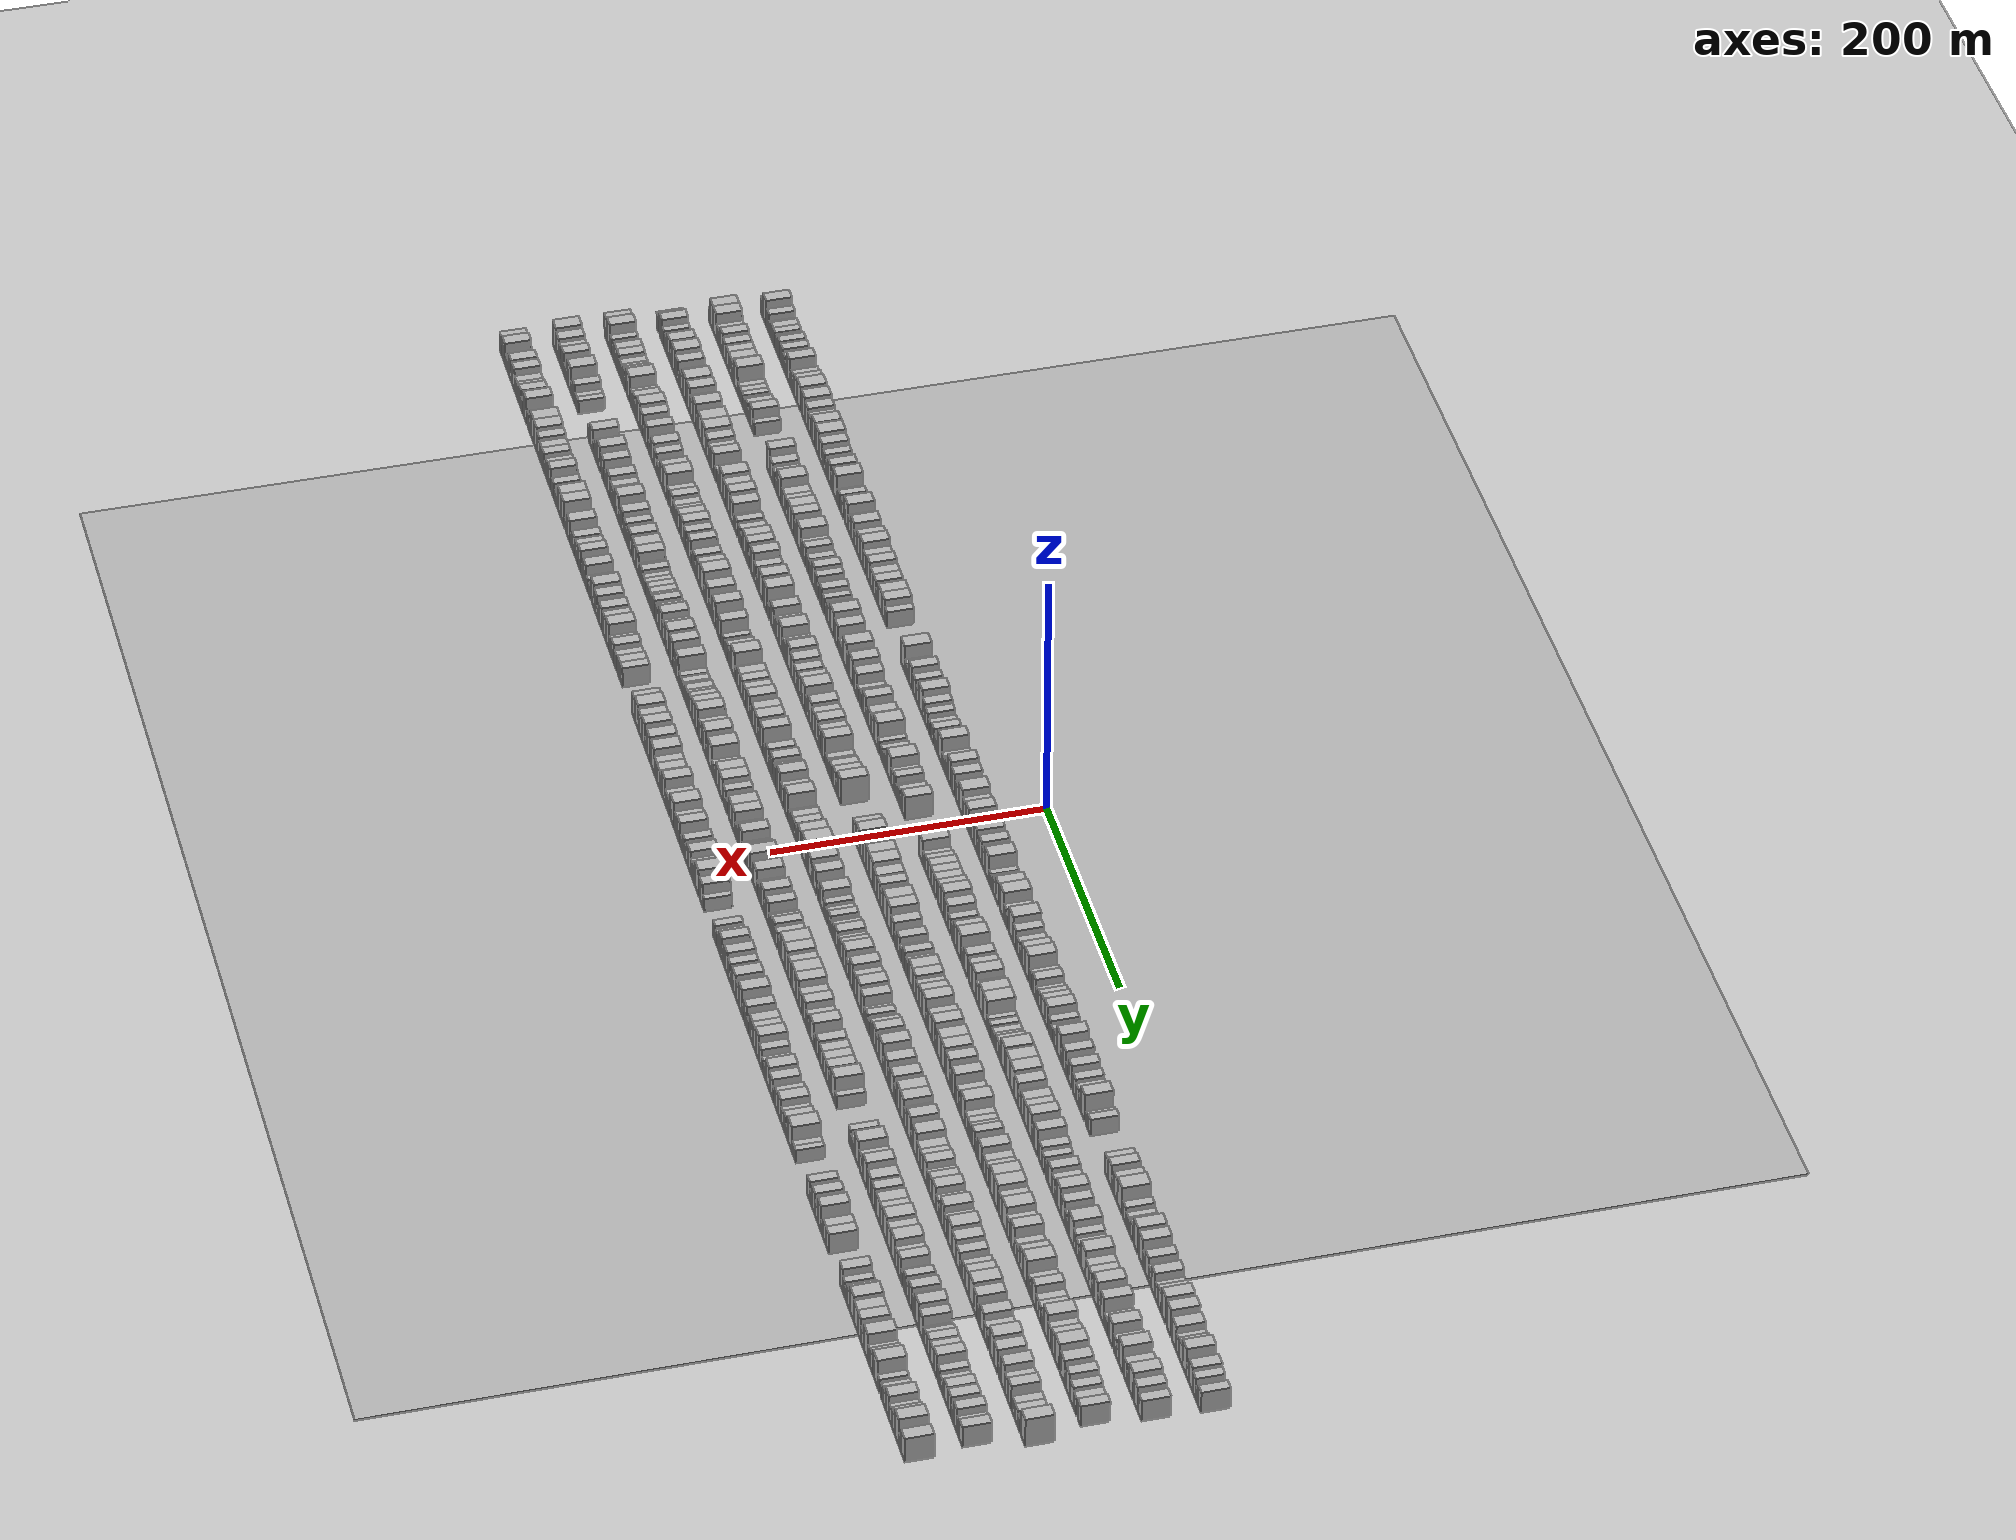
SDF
<?xml version="1.0" encoding="utf-8"?>

<sdf version="1.6">

   <world name="default">

      <gui fullscreen="0">

         <camera name="user_camera">

            <pose>-15 0 4.57585 0 0 0</pose>

            <view_controller>orbit</view_controller>

         </camera>

      </gui>

      <scene>

         <sky>

           <clouds>

             <speed>12</speed>

           </clouds>

         </sky>

         <ambient>0.4 0.4 0.4 1</ambient>

         <background>0.7 0.7 0.7 1</background>

         <shadows>1</shadows>

      </scene>

      <gravity>0 0 -9.8066</gravity>

      <magnetic_field>6e-06 2.3e-05 -4.2e-05</magnetic_field>

      <physics default="0" name="default_physics" type="ode">

         <ode>

            <solver>

               <type>quick</type>

               <iters>10</iters>

               <sor>1.0</sor>

               <use_dynamic_moi_rescaling>0</use_dynamic_moi_rescaling>

            </solver>

            <constraints>

               <cfm>0</cfm>

               <erp>0.2</erp>

               <contact_max_correcting_vel>100</contact_max_correcting_vel>

               <contact_surface_layer>0.001</contact_surface_layer>

            </constraints>

         </ode>

         <max_step_size>0.004</max_step_size>

         <real_time_factor>1</real_time_factor>

         <real_time_update_rate>250</real_time_update_rate>

      </physics>

      <light name="sun" type="directional">

         <cast_shadows>1</cast_shadows>

         <pose>0 0 10 0 0 0</pose>

         <diffuse>0.8 0.8 0.8 1</diffuse>

         <specular>0.2 0.2 0.2 1</specular>

         <attenuation>

            <range>1000</range>

            <constant>0.9</constant>

            <linear>0.01</linear>

            <quadratic>0.001</quadratic>

         </attenuation>

         <direction>-0.5 0.1 -0.9</direction>

      </light>

      <include>

         <name>ground_plane_1</name>

         <uri>model://HANNAS_ground_plane</uri>

         <pose>0 0 0  0 0 0</pose>

      </include>

      <include>

         <name>ground_plane_2</name>

         <uri>model://HANNAS_ground_plane</uri>

         <pose>100 0 0  0 0 0</pose>

      </include>

      <model name="building_1">

         <static>1</static>

         <pose frame="">50.0000 -616.6186 0 0.000000 0.000000 0.000000</pose>

         <link name="link">

            <pose frame="">0 0 7.50 0 0 0</pose>

            <collision name="collision">

               <geometry>

                  <box>

                     <size>20.0000 6.7628 15.0000</size>

                  </box>

               </geometry>

               <max_contacts>10</max_contacts>

               <surface>

                  <contact>

                     <ode/>

                  </contact>

                  <bounce/>

                  <friction>

                     <torsional>

                        <ode/>

                     </torsional>

                     <ode/>

                  </friction>

               </surface>

            </collision>

            <visual name="visual">

               <cast_shadows>0</cast_shadows>

               <geometry>

                  <box>

                     <size>20.0000 6.7628 15.0000</size>

                  </box>

               </geometry>

               <material>

                  <script>

                     <uri>model://HANNAS_wall/materials/scripts</uri>

                     <uri>model://HANNAS_wall/materials/textures</uri>

                     <name>vrc/HANNAS_wall</name>

                  </script>

               </material>

            </visual>

            <self_collide>0</self_collide>

            <enable_wind>0</enable_wind>

            <kinematic>0</kinematic>

         </link>

      </model>

      <model name="building_2">

         <static>1</static>

         <pose frame="">50.0000 -606.2549 0 0.000000 0.000000 0.000000</pose>

         <link name="link">

            <pose frame="">0 0 12.00 0 0 0</pose>

            <collision name="collision">

               <geometry>

                  <box>

                     <size>20.0000 9.9646 24.0000</size>

                  </box>

               </geometry>

               <max_contacts>10</max_contacts>

               <surface>

                  <contact>

                     <ode/>

                  </contact>

                  <bounce/>

                  <friction>

                     <torsional>

                        <ode/>

                     </torsional>

                     <ode/>

                  </friction>

               </surface>

            </collision>

            <visual name="visual">

               <cast_shadows>0</cast_shadows>

               <geometry>

                  <box>

                     <size>20.0000 9.9646 24.0000</size>

                  </box>

               </geometry>

               <material>

                  <script>

                     <uri>model://HANNAS_wall/materials/scripts</uri>

                     <uri>model://HANNAS_wall/materials/textures</uri>

                     <name>vrc/HANNAS_wall</name>

                  </script>

               </material>

            </visual>

            <self_collide>0</self_collide>

            <enable_wind>0</enable_wind>

            <kinematic>0</kinematic>

         </link>

      </model>

      <model name="building_3">

         <static>1</static>

         <pose frame="">50.0000 -595.5343 0 0.000000 0.000000 0.000000</pose>

         <link name="link">

            <pose frame="">0 0 9.00 0 0 0</pose>

            <collision name="collision">

               <geometry>

                  <box>

                     <size>20.0000 7.4766 18.0000</size>

                  </box>

               </geometry>

               <max_contacts>10</max_contacts>

               <surface>

                  <contact>

                     <ode/>

                  </contact>

                  <bounce/>

                  <friction>

                     <torsional>

                        <ode/>

                     </torsional>

                     <ode/>

                  </friction>

               </surface>

            </collision>

            <visual name="visual">

               <cast_shadows>0</cast_shadows>

               <geometry>

                  <box>

                     <size>20.0000 7.4766 18.0000</size>

                  </box>

               </geometry>

               <material>

                  <script>

                     <uri>model://HANNAS_wall/materials/scripts</uri>

                     <uri>model://HANNAS_wall/materials/textures</uri>

                     <name>vrc/HANNAS_wall</name>

                  </script>

               </material>

            </visual>

            <self_collide>0</self_collide>

            <enable_wind>0</enable_wind>

            <kinematic>0</kinematic>

         </link>

      </model>

      <model name="building_4">

         <static>1</static>

         <pose frame="">50.0000 -589.1701 0 0.000000 0.000000 0.000000</pose>

         <link name="link">

            <pose frame="">0 0 6.00 0 0 0</pose>

            <collision name="collision">

               <geometry>

                  <box>

                     <size>20.0000 5.2517 12.0000</size>

                  </box>

               </geometry>

               <max_contacts>10</max_contacts>

               <surface>

                  <contact>

                     <ode/>

                  </contact>

                  <bounce/>

                  <friction>

                     <torsional>

                        <ode/>

                     </torsional>

                     <ode/>

                  </friction>

               </surface>

            </collision>

            <visual name="visual">

               <cast_shadows>0</cast_shadows>

               <geometry>

                  <box>

                     <size>20.0000 5.2517 12.0000</size>

                  </box>

               </geometry>

               <material>

                  <script>

                     <uri>model://HANNAS_wall/materials/scripts</uri>

                     <uri>model://HANNAS_wall/materials/textures</uri>

                     <name>vrc/HANNAS_wall</name>

                  </script>

               </material>

            </visual>

            <self_collide>0</self_collide>

            <enable_wind>0</enable_wind>

            <kinematic>0</kinematic>

         </link>

      </model>

      <model name="building_5">

         <static>1</static>

         <pose frame="">50.0000 -582.9045 0 0.000000 0.000000 0.000000</pose>

         <link name="link">

            <pose frame="">0 0 7.50 0 0 0</pose>

            <collision name="collision">

               <geometry>

                  <box>

                     <size>20.0000 7.2797 15.0000</size>

                  </box>

               </geometry>

               <max_contacts>10</max_contacts>

               <surface>

                  <contact>

                     <ode/>

                  </contact>

                  <bounce/>

                  <friction>

                     <torsional>

                        <ode/>

                     </torsional>

                     <ode/>

                  </friction>

               </surface>

            </collision>

            <visual name="visual">

               <cast_shadows>0</cast_shadows>

               <geometry>

                  <box>

                     <size>20.0000 7.2797 15.0000</size>

                  </box>

               </geometry>

               <material>

                  <script>

                     <uri>model://HANNAS_wall/materials/scripts</uri>

                     <uri>model://HANNAS_wall/materials/textures</uri>

                     <name>vrc/HANNAS_wall</name>

                  </script>

               </material>

            </visual>

            <self_collide>0</self_collide>

            <enable_wind>0</enable_wind>

            <kinematic>0</kinematic>

         </link>

      </model>

      <model name="building_6">

         <static>1</static>

         <pose frame="">50.0000 -575.9274 0 0.000000 0.000000 0.000000</pose>

         <link name="link">

            <pose frame="">0 0 7.50 0 0 0</pose>

            <collision name="collision">

               <geometry>

                  <box>

                     <size>20.0000 6.6745 15.0000</size>

                  </box>

               </geometry>

               <max_contacts>10</max_contacts>

               <surface>

                  <contact>

                     <ode/>

                  </contact>

                  <bounce/>

                  <friction>

                     <torsional>

                        <ode/>

                     </torsional>

                     <ode/>

                  </friction>

               </surface>

            </collision>

            <visual name="visual">

               <cast_shadows>0</cast_shadows>

               <geometry>

                  <box>

                     <size>20.0000 6.6745 15.0000</size>

                  </box>

               </geometry>

               <material>

                  <script>

                     <uri>model://HANNAS_wall/materials/scripts</uri>

                     <uri>model://HANNAS_wall/materials/textures</uri>

                     <name>vrc/HANNAS_wall</name>

                  </script>

               </material>

            </visual>

            <self_collide>0</self_collide>

            <enable_wind>0</enable_wind>

            <kinematic>0</kinematic>

         </link>

      </model>

      <model name="building_7">

         <static>1</static>

         <pose frame="">50.0000 -567.5688 0 0.000000 0.000000 0.000000</pose>

         <link name="link">

            <pose frame="">0 0 7.50 0 0 0</pose>

            <collision name="collision">

               <geometry>

                  <box>

                     <size>20.0000 6.0427 15.0000</size>

                  </box>

               </geometry>

               <max_contacts>10</max_contacts>

               <surface>

                  <contact>

                     <ode/>

                  </contact>

                  <bounce/>

                  <friction>

                     <torsional>

                        <ode/>

                     </torsional>

                     <ode/>

                  </friction>

               </surface>

            </collision>

            <visual name="visual">

               <cast_shadows>0</cast_shadows>

               <geometry>

                  <box>

                     <size>20.0000 6.0427 15.0000</size>

                  </box>

               </geometry>

               <material>

                  <script>

                     <uri>model://HANNAS_wall/materials/scripts</uri>

                     <uri>model://HANNAS_wall/materials/textures</uri>

                     <name>vrc/HANNAS_wall</name>

                  </script>

               </material>

            </visual>

            <self_collide>0</self_collide>

            <enable_wind>0</enable_wind>

            <kinematic>0</kinematic>

         </link>

      </model>

      <model name="building_8">

         <static>1</static>

         <pose frame="">50.0000 -560.7549 0 0.000000 0.000000 0.000000</pose>

         <link name="link">

            <pose frame="">0 0 9.00 0 0 0</pose>

            <collision name="collision">

               <geometry>

                  <box>

                     <size>20.0000 7.5851 18.0000</size>

                  </box>

               </geometry>

               <max_contacts>10</max_contacts>

               <surface>

                  <contact>

                     <ode/>

                  </contact>

                  <bounce/>

                  <friction>

                     <torsional>

                        <ode/>

                     </torsional>

                     <ode/>

                  </friction>

               </surface>

            </collision>

            <visual name="visual">

               <cast_shadows>0</cast_shadows>

               <geometry>

                  <box>

                     <size>20.0000 7.5851 18.0000</size>

                  </box>

               </geometry>

               <material>

                  <script>

                     <uri>model://HANNAS_wall/materials/scripts</uri>

                     <uri>model://HANNAS_wall/materials/textures</uri>

                     <name>vrc/HANNAS_wall</name>

                  </script>

               </material>

            </visual>

            <self_collide>0</self_collide>

            <enable_wind>0</enable_wind>

            <kinematic>0</kinematic>

         </link>

      </model>

      <model name="building_9">

         <static>1</static>

         <pose frame="">50.0000 -551.0288 0 0.000000 0.000000 0.000000</pose>

         <link name="link">

            <pose frame="">0 0 9.00 0 0 0</pose>

            <collision name="collision">

               <geometry>

                  <box>

                     <size>20.0000 7.8670 18.0000</size>

                  </box>

               </geometry>

               <max_contacts>10</max_contacts>

               <surface>

                  <contact>

                     <ode/>

                  </contact>

                  <bounce/>

                  <friction>

                     <torsional>

                        <ode/>

                     </torsional>

                     <ode/>

                  </friction>

               </surface>

            </collision>

            <visual name="visual">

               <cast_shadows>0</cast_shadows>

               <geometry>

                  <box>

                     <size>20.0000 7.8670 18.0000</size>

                  </box>

               </geometry>

               <material>

                  <script>

                     <uri>model://HANNAS_wall/materials/scripts</uri>

                     <uri>model://HANNAS_wall/materials/textures</uri>

                     <name>vrc/HANNAS_wall</name>

                  </script>

               </material>

            </visual>

            <self_collide>0</self_collide>

            <enable_wind>0</enable_wind>

            <kinematic>0</kinematic>

         </link>

      </model>

      <model name="building_10">

         <static>1</static>

         <pose frame="">50.0000 -544.0765 0 0.000000 0.000000 0.000000</pose>

         <link name="link">

            <pose frame="">0 0 7.50 0 0 0</pose>

            <collision name="collision">

               <geometry>

                  <box>

                     <size>20.0000 6.0376 15.0000</size>

                  </box>

               </geometry>

               <max_contacts>10</max_contacts>

               <surface>

                  <contact>

                     <ode/>

                  </contact>

                  <bounce/>

                  <friction>

                     <torsional>

                        <ode/>

                     </torsional>

                     <ode/>

                  </friction>

               </surface>

            </collision>

            <visual name="visual">

               <cast_shadows>0</cast_shadows>

               <geometry>

                  <box>

                     <size>20.0000 6.0376 15.0000</size>

                  </box>

               </geometry>

               <material>

                  <script>

                     <uri>model://HANNAS_wall/materials/scripts</uri>

                     <uri>model://HANNAS_wall/materials/textures</uri>

                     <name>vrc/HANNAS_wall</name>

                  </script>

               </material>

            </visual>

            <self_collide>0</self_collide>

            <enable_wind>0</enable_wind>

            <kinematic>0</kinematic>

         </link>

      </model>

      <model name="building_11">

         <static>1</static>

         <pose frame="">50.0000 -538.5596 0 0.000000 0.000000 0.000000</pose>

         <link name="link">

            <pose frame="">0 0 6.00 0 0 0</pose>

            <collision name="collision">

               <geometry>

                  <box>

                     <size>20.0000 4.9962 12.0000</size>

                  </box>

               </geometry>

               <max_contacts>10</max_contacts>

               <surface>

                  <contact>

                     <ode/>

                  </contact>

                  <bounce/>

                  <friction>

                     <torsional>

                        <ode/>

                     </torsional>

                     <ode/>

                  </friction>

               </surface>

            </collision>

            <visual name="visual">

               <cast_shadows>0</cast_shadows>

               <geometry>

                  <box>

                     <size>20.0000 4.9962 12.0000</size>

                  </box>

               </geometry>

               <material>

                  <script>

                     <uri>model://HANNAS_wall/materials/scripts</uri>

                     <uri>model://HANNAS_wall/materials/textures</uri>

                     <name>vrc/HANNAS_wall</name>

                  </script>

               </material>

            </visual>

            <self_collide>0</self_collide>

            <enable_wind>0</enable_wind>

            <kinematic>0</kinematic>

         </link>

      </model>

      <model name="building_12">

         <static>1</static>

         <pose frame="">50.0000 -531.2493 0 0.000000 0.000000 0.000000</pose>

         <link name="link">

            <pose frame="">0 0 12.00 0 0 0</pose>

            <collision name="collision">

               <geometry>

                  <box>

                     <size>20.0000 9.6245 24.0000</size>

                  </box>

               </geometry>

               <max_contacts>10</max_contacts>

               <surface>

                  <contact>

                     <ode/>

                  </contact>

                  <bounce/>

                  <friction>

                     <torsional>

                        <ode/>

                     </torsional>

                     <ode/>

                  </friction>

               </surface>

            </collision>

            <visual name="visual">

               <cast_shadows>0</cast_shadows>

               <geometry>

                  <box>

                     <size>20.0000 9.6245 24.0000</size>

                  </box>

               </geometry>

               <material>

                  <script>

                     <uri>model://HANNAS_wall/materials/scripts</uri>

                     <uri>model://HANNAS_wall/materials/textures</uri>

                     <name>vrc/HANNAS_wall</name>

                  </script>

               </material>

            </visual>

            <self_collide>0</self_collide>

            <enable_wind>0</enable_wind>

            <kinematic>0</kinematic>

         </link>

      </model>

      <model name="building_13">

         <static>1</static>

         <pose frame="">50.0000 -523.6492 0 0.000000 0.000000 0.000000</pose>

         <link name="link">

            <pose frame="">0 0 6.00 0 0 0</pose>

            <collision name="collision">

               <geometry>

                  <box>

                     <size>20.0000 5.5758 12.0000</size>

                  </box>

               </geometry>

               <max_contacts>10</max_contacts>

               <surface>

                  <contact>

                     <ode/>

                  </contact>

                  <bounce/>

                  <friction>

                     <torsional>

                        <ode/>

                     </torsional>

                     <ode/>

                  </friction>

               </surface>

            </collision>

            <visual name="visual">

               <cast_shadows>0</cast_shadows>

               <geometry>

                  <box>

                     <size>20.0000 5.5758 12.0000</size>

                  </box>

               </geometry>

               <material>

                  <script>

                     <uri>model://HANNAS_wall/materials/scripts</uri>

                     <uri>model://HANNAS_wall/materials/textures</uri>

                     <name>vrc/HANNAS_wall</name>

                  </script>

               </material>

            </visual>

            <self_collide>0</self_collide>

            <enable_wind>0</enable_wind>

            <kinematic>0</kinematic>

         </link>

      </model>

      <model name="building_14">

         <static>1</static>

         <pose frame="">50.0000 -516.4085 0 0.000000 0.000000 0.000000</pose>

         <link name="link">

            <pose frame="">0 0 9.00 0 0 0</pose>

            <collision name="collision">

               <geometry>

                  <box>

                     <size>20.0000 8.9057 18.0000</size>

                  </box>

               </geometry>

               <max_contacts>10</max_contacts>

               <surface>

                  <contact>

                     <ode/>

                  </contact>

                  <bounce/>

                  <friction>

                     <torsional>

                        <ode/>

                     </torsional>

                     <ode/>

                  </friction>

               </surface>

            </collision>

            <visual name="visual">

               <cast_shadows>0</cast_shadows>

               <geometry>

                  <box>

                     <size>20.0000 8.9057 18.0000</size>

                  </box>

               </geometry>

               <material>

                  <script>

                     <uri>model://HANNAS_wall/materials/scripts</uri>

                     <uri>model://HANNAS_wall/materials/textures</uri>

                     <name>vrc/HANNAS_wall</name>

                  </script>

               </material>

            </visual>

            <self_collide>0</self_collide>

            <enable_wind>0</enable_wind>

            <kinematic>0</kinematic>

         </link>

      </model>

      <model name="building_15">

         <static>1</static>

         <pose frame="">50.0000 -507.4987 0 0.000000 0.000000 0.000000</pose>

         <link name="link">

            <pose frame="">0 0 10.50 0 0 0</pose>

            <collision name="collision">

               <geometry>

                  <box>

                     <size>20.0000 8.9138 21.0000</size>

                  </box>

               </geometry>

               <max_contacts>10</max_contacts>

               <surface>

                  <contact>

                     <ode/>

                  </contact>

                  <bounce/>

                  <friction>

                     <torsional>

                        <ode/>

                     </torsional>

                     <ode/>

                  </friction>

               </surface>

            </collision>

            <visual name="visual">

               <cast_shadows>0</cast_shadows>

               <geometry>

                  <box>

                     <size>20.0000 8.9138 21.0000</size>

                  </box>

               </geometry>

               <material>

                  <script>

                     <uri>model://HANNAS_wall/materials/scripts</uri>

                     <uri>model://HANNAS_wall/materials/textures</uri>

                     <name>vrc/HANNAS_wall</name>

                  </script>

               </material>

            </visual>

            <self_collide>0</self_collide>

            <enable_wind>0</enable_wind>

            <kinematic>0</kinematic>

         </link>

      </model>

      <model name="building_16">

         <static>1</static>

         <pose frame="">50.0000 -497.1252 0 0.000000 0.000000 0.000000</pose>

         <link name="link">

            <pose frame="">0 0 12.00 0 0 0</pose>

            <collision name="collision">

               <geometry>

                  <box>

                     <size>20.0000 11.8332 24.0000</size>

                  </box>

               </geometry>

               <max_contacts>10</max_contacts>

               <surface>

                  <contact>

                     <ode/>

                  </contact>

                  <bounce/>

                  <friction>

                     <torsional>

                        <ode/>

                     </torsional>

                     <ode/>

                  </friction>

               </surface>

            </collision>

            <visual name="visual">

               <cast_shadows>0</cast_shadows>

               <geometry>

                  <box>

                     <size>20.0000 11.8332 24.0000</size>

                  </box>

               </geometry>

               <material>

                  <script>

                     <uri>model://HANNAS_wall/materials/scripts</uri>

                     <uri>model://HANNAS_wall/materials/textures</uri>

                     <name>vrc/HANNAS_wall</name>

                  </script>

               </material>

            </visual>

            <self_collide>0</self_collide>

            <enable_wind>0</enable_wind>

            <kinematic>0</kinematic>

         </link>

      </model>

      <model name="building_17">

         <static>1</static>

         <pose frame="">50.0000 -482.6273 0 0.000000 0.000000 0.000000</pose>

         <link name="link">

            <pose frame="">0 0 12.00 0 0 0</pose>

            <collision name="collision">

               <geometry>

                  <box>

                     <size>20.0000 11.1627 24.0000</size>

                  </box>

               </geometry>

               <max_contacts>10</max_contacts>

               <surface>

                  <contact>

                     <ode/>

                  </contact>

                  <bounce/>

                  <friction>

                     <torsional>

                        <ode/>

                     </torsional>

                     <ode/>

                  </friction>

               </surface>

            </collision>

            <visual name="visual">

               <cast_shadows>0</cast_shadows>

               <geometry>

                  <box>

                     <size>20.0000 11.1627 24.0000</size>

                  </box>

               </geometry>

               <material>

                  <script>

                     <uri>model://HANNAS_wall/materials/scripts</uri>

                     <uri>model://HANNAS_wall/materials/textures</uri>

                     <name>vrc/HANNAS_wall</name>

                  </script>

               </material>

            </visual>

            <self_collide>0</self_collide>

            <enable_wind>0</enable_wind>

            <kinematic>0</kinematic>

         </link>

      </model>

      <model name="building_18">

         <static>1</static>

         <pose frame="">50.0000 -472.3004 0 0.000000 0.000000 0.000000</pose>

         <link name="link">

            <pose frame="">0 0 10.50 0 0 0</pose>

            <collision name="collision">

               <geometry>

                  <box>

                     <size>20.0000 9.4911 21.0000</size>

                  </box>

               </geometry>

               <max_contacts>10</max_contacts>

               <surface>

                  <contact>

                     <ode/>

                  </contact>

                  <bounce/>

                  <friction>

                     <torsional>

                        <ode/>

                     </torsional>

                     <ode/>

                  </friction>

               </surface>

            </collision>

            <visual name="visual">

               <cast_shadows>0</cast_shadows>

               <geometry>

                  <box>

                     <size>20.0000 9.4911 21.0000</size>

                  </box>

               </geometry>

               <material>

                  <script>

                     <uri>model://HANNAS_wall/materials/scripts</uri>

                     <uri>model://HANNAS_wall/materials/textures</uri>

                     <name>vrc/HANNAS_wall</name>

                  </script>

               </material>

            </visual>

            <self_collide>0</self_collide>

            <enable_wind>0</enable_wind>

            <kinematic>0</kinematic>

         </link>

      </model>

      <model name="building_19">

         <static>1</static>

         <pose frame="">50.0000 -463.4733 0 0.000000 0.000000 0.000000</pose>

         <link name="link">

            <pose frame="">0 0 9.00 0 0 0</pose>

            <collision name="collision">

               <geometry>

                  <box>

                     <size>20.0000 8.1629 18.0000</size>

                  </box>

               </geometry>

               <max_contacts>10</max_contacts>

               <surface>

                  <contact>

                     <ode/>

                  </contact>

                  <bounce/>

                  <friction>

                     <torsional>

                        <ode/>

                     </torsional>

                     <ode/>

                  </friction>

               </surface>

            </collision>

            <visual name="visual">

               <cast_shadows>0</cast_shadows>

               <geometry>

                  <box>

                     <size>20.0000 8.1629 18.0000</size>

                  </box>

               </geometry>

               <material>

                  <script>

                     <uri>model://HANNAS_wall/materials/scripts</uri>

                     <uri>model://HANNAS_wall/materials/textures</uri>

                     <name>vrc/HANNAS_wall</name>

                  </script>

               </material>

            </visual>

            <self_collide>0</self_collide>

            <enable_wind>0</enable_wind>

            <kinematic>0</kinematic>

         </link>

      </model>

      <model name="building_20">

         <static>1</static>

         <pose frame="">50.0000 -451.2165 0 0.000000 0.000000 0.000000</pose>

         <link name="link">

            <pose frame="">0 0 12.00 0 0 0</pose>

            <collision name="collision">

               <geometry>

                  <box>

                     <size>20.0000 10.3507 24.0000</size>

                  </box>

               </geometry>

               <max_contacts>10</max_contacts>

               <surface>

                  <contact>

                     <ode/>

                  </contact>

                  <bounce/>

                  <friction>

                     <torsional>

                        <ode/>

                     </torsional>

                     <ode/>

                  </friction>

               </surface>

            </collision>

            <visual name="visual">

               <cast_shadows>0</cast_shadows>

               <geometry>

                  <box>

                     <size>20.0000 10.3507 24.0000</size>

                  </box>

               </geometry>

               <material>

                  <script>

                     <uri>model://HANNAS_wall/materials/scripts</uri>

                     <uri>model://HANNAS_wall/materials/textures</uri>

                     <name>vrc/HANNAS_wall</name>

                  </script>

               </material>

            </visual>

            <self_collide>0</self_collide>

            <enable_wind>0</enable_wind>

            <kinematic>0</kinematic>

         </link>

      </model>

      <model name="building_21">

         <static>1</static>

         <pose frame="">50.0000 -439.0764 0 0.000000 0.000000 0.000000</pose>

         <link name="link">

            <pose frame="">0 0 12.00 0 0 0</pose>

            <collision name="collision">

               <geometry>

                  <box>

                     <size>20.0000 11.9295 24.0000</size>

                  </box>

               </geometry>

               <max_contacts>10</max_contacts>

               <surface>

                  <contact>

                     <ode/>

                  </contact>

                  <bounce/>

                  <friction>

                     <torsional>

                        <ode/>

                     </torsional>

                     <ode/>

                  </friction>

               </surface>

            </collision>

            <visual name="visual">

               <cast_shadows>0</cast_shadows>

               <geometry>

                  <box>

                     <size>20.0000 11.9295 24.0000</size>

                  </box>

               </geometry>

               <material>

                  <script>

                     <uri>model://HANNAS_wall/materials/scripts</uri>

                     <uri>model://HANNAS_wall/materials/textures</uri>

                     <name>vrc/HANNAS_wall</name>

                  </script>

               </material>

            </visual>

            <self_collide>0</self_collide>

            <enable_wind>0</enable_wind>

            <kinematic>0</kinematic>

         </link>

      </model>

      <model name="building_22">

         <static>1</static>

         <pose frame="">50.0000 -428.2637 0 0.000000 0.000000 0.000000</pose>

         <link name="link">

            <pose frame="">0 0 10.50 0 0 0</pose>

            <collision name="collision">

               <geometry>

                  <box>

                     <size>20.0000 9.6959 21.0000</size>

                  </box>

               </geometry>

               <max_contacts>10</max_contacts>

               <surface>

                  <contact>

                     <ode/>

                  </contact>

                  <bounce/>

                  <friction>

                     <torsional>

                        <ode/>

                     </torsional>

                     <ode/>

                  </friction>

               </surface>

            </collision>

            <visual name="visual">

               <cast_shadows>0</cast_shadows>

               <geometry>

                  <box>

                     <size>20.0000 9.6959 21.0000</size>

                  </box>

               </geometry>

               <material>

                  <script>

                     <uri>model://HANNAS_wall/materials/scripts</uri>

                     <uri>model://HANNAS_wall/materials/textures</uri>

                     <name>vrc/HANNAS_wall</name>

                  </script>

               </material>

            </visual>

            <self_collide>0</self_collide>

            <enable_wind>0</enable_wind>

            <kinematic>0</kinematic>

         </link>

      </model>

      <model name="building_23">

         <static>1</static>

         <pose frame="">50.0000 -417.7534 0 0.000000 0.000000 0.000000</pose>

         <link name="link">

            <pose frame="">0 0 9.00 0 0 0</pose>

            <collision name="collision">

               <geometry>

                  <box>

                     <size>20.0000 7.3249 18.0000</size>

                  </box>

               </geometry>

               <max_contacts>10</max_contacts>

               <surface>

                  <contact>

                     <ode/>

                  </contact>

                  <bounce/>

                  <friction>

                     <torsional>

                        <ode/>

                     </torsional>

                     <ode/>

                  </friction>

               </surface>

            </collision>

            <visual name="visual">

               <cast_shadows>0</cast_shadows>

               <geometry>

                  <box>

                     <size>20.0000 7.3249 18.0000</size>

                  </box>

               </geometry>

               <material>

                  <script>

                     <uri>model://HANNAS_wall/materials/scripts</uri>

                     <uri>model://HANNAS_wall/materials/textures</uri>

                     <name>vrc/HANNAS_wall</name>

                  </script>

               </material>

            </visual>

            <self_collide>0</self_collide>

            <enable_wind>0</enable_wind>

            <kinematic>0</kinematic>

         </link>

      </model>

      <model name="building_24">

         <static>1</static>

         <pose frame="">50.0000 -408.9823 0 0.000000 0.000000 0.000000</pose>

         <link name="link">

            <pose frame="">0 0 7.50 0 0 0</pose>

            <collision name="collision">

               <geometry>

                  <box>

                     <size>20.0000 6.2171 15.0000</size>

                  </box>

               </geometry>

               <max_contacts>10</max_contacts>

               <surface>

                  <contact>

                     <ode/>

                  </contact>

                  <bounce/>

                  <friction>

                     <torsional>

                        <ode/>

                     </torsional>

                     <ode/>

                  </friction>

               </surface>

            </collision>

            <visual name="visual">

               <cast_shadows>0</cast_shadows>

               <geometry>

                  <box>

                     <size>20.0000 6.2171 15.0000</size>

                  </box>

               </geometry>

               <material>

                  <script>

                     <uri>model://HANNAS_wall/materials/scripts</uri>

                     <uri>model://HANNAS_wall/materials/textures</uri>

                     <name>vrc/HANNAS_wall</name>

                  </script>

               </material>

            </visual>

            <self_collide>0</self_collide>

            <enable_wind>0</enable_wind>

            <kinematic>0</kinematic>

         </link>

      </model>

      <model name="building_25">

         <static>1</static>

         <pose frame="">50.0000 -401.4881 0 0.000000 0.000000 0.000000</pose>

         <link name="link">

            <pose frame="">0 0 10.50 0 0 0</pose>

            <collision name="collision">

               <geometry>

                  <box>

                     <size>20.0000 8.7713 21.0000</size>

                  </box>

               </geometry>

               <max_contacts>10</max_contacts>

               <surface>

                  <contact>

                     <ode/>

                  </contact>

                  <bounce/>

                  <friction>

                     <torsional>

                        <ode/>

                     </torsional>

                     <ode/>

                  </friction>

               </surface>

            </collision>

            <visual name="visual">

               <cast_shadows>0</cast_shadows>

               <geometry>

                  <box>

                     <size>20.0000 8.7713 21.0000</size>

                  </box>

               </geometry>

               <material>

                  <script>

                     <uri>model://HANNAS_wall/materials/scripts</uri>

                     <uri>model://HANNAS_wall/materials/textures</uri>

                     <name>vrc/HANNAS_wall</name>

                  </script>

               </material>

            </visual>

            <self_collide>0</self_collide>

            <enable_wind>0</enable_wind>

            <kinematic>0</kinematic>

         </link>

      </model>

      <model name="building_26">

         <static>1</static>

         <pose frame="">50.0000 -394.0560 0 0.000000 0.000000 0.000000</pose>

         <link name="link">

            <pose frame="">0 0 7.50 0 0 0</pose>

            <collision name="collision">

               <geometry>

                  <box>

                     <size>20.0000 6.0929 15.0000</size>

                  </box>

               </geometry>

               <max_contacts>10</max_contacts>

               <surface>

                  <contact>

                     <ode/>

                  </contact>

                  <bounce/>

                  <friction>

                     <torsional>

                        <ode/>

                     </torsional>

                     <ode/>

                  </friction>

               </surface>

            </collision>

            <visual name="visual">

               <cast_shadows>0</cast_shadows>

               <geometry>

                  <box>

                     <size>20.0000 6.0929 15.0000</size>

                  </box>

               </geometry>

               <material>

                  <script>

                     <uri>model://HANNAS_wall/materials/scripts</uri>

                     <uri>model://HANNAS_wall/materials/textures</uri>

                     <name>vrc/HANNAS_wall</name>

                  </script>

               </material>

            </visual>

            <self_collide>0</self_collide>

            <enable_wind>0</enable_wind>

            <kinematic>0</kinematic>

         </link>

      </model>

      <model name="building_27">

         <static>1</static>

         <pose frame="">50.0000 -385.3663 0 0.000000 0.000000 0.000000</pose>

         <link name="link">

            <pose frame="">0 0 12.00 0 0 0</pose>

            <collision name="collision">

               <geometry>

                  <box>

                     <size>20.0000 11.2865 24.0000</size>

                  </box>

               </geometry>

               <max_contacts>10</max_contacts>

               <surface>

                  <contact>

                     <ode/>

                  </contact>

                  <bounce/>

                  <friction>

                     <torsional>

                        <ode/>

                     </torsional>

                     <ode/>

                  </friction>

               </surface>

            </collision>

            <visual name="visual">

               <cast_shadows>0</cast_shadows>

               <geometry>

                  <box>

                     <size>20.0000 11.2865 24.0000</size>

                  </box>

               </geometry>

               <material>

                  <script>

                     <uri>model://HANNAS_wall/materials/scripts</uri>

                     <uri>model://HANNAS_wall/materials/textures</uri>

                     <name>vrc/HANNAS_wall</name>

                  </script>

               </material>

            </visual>

            <self_collide>0</self_collide>

            <enable_wind>0</enable_wind>

            <kinematic>0</kinematic>

         </link>

      </model>

      <model name="building_28">

         <static>1</static>

         <pose frame="">50.0000 -377.2260 0 0.000000 0.000000 0.000000</pose>

         <link name="link">

            <pose frame="">0 0 6.00 0 0 0</pose>

            <collision name="collision">

               <geometry>

                  <box>

                     <size>20.0000 4.9940 12.0000</size>

                  </box>

               </geometry>

               <max_contacts>10</max_contacts>

               <surface>

                  <contact>

                     <ode/>

                  </contact>

                  <bounce/>

                  <friction>

                     <torsional>

                        <ode/>

                     </torsional>

                     <ode/>

                  </friction>

               </surface>

            </collision>

            <visual name="visual">

               <cast_shadows>0</cast_shadows>

               <geometry>

                  <box>

                     <size>20.0000 4.9940 12.0000</size>

                  </box>

               </geometry>

               <material>

                  <script>

                     <uri>model://HANNAS_wall/materials/scripts</uri>

                     <uri>model://HANNAS_wall/materials/textures</uri>

                     <name>vrc/HANNAS_wall</name>

                  </script>

               </material>

            </visual>

            <self_collide>0</self_collide>

            <enable_wind>0</enable_wind>

            <kinematic>0</kinematic>

         </link>

      </model>

      <model name="building_29">

         <static>1</static>

         <pose frame="">50.0000 -371.4640 0 0.000000 0.000000 0.000000</pose>

         <link name="link">

            <pose frame="">0 0 7.50 0 0 0</pose>

            <collision name="collision">

               <geometry>

                  <box>

                     <size>20.0000 6.5300 15.0000</size>

                  </box>

               </geometry>

               <max_contacts>10</max_contacts>

               <surface>

                  <contact>

                     <ode/>

                  </contact>

                  <bounce/>

                  <friction>

                     <torsional>

                        <ode/>

                     </torsional>

                     <ode/>

                  </friction>

               </surface>

            </collision>

            <visual name="visual">

               <cast_shadows>0</cast_shadows>

               <geometry>

                  <box>

                     <size>20.0000 6.5300 15.0000</size>

                  </box>

               </geometry>

               <material>

                  <script>

                     <uri>model://HANNAS_wall/materials/scripts</uri>

                     <uri>model://HANNAS_wall/materials/textures</uri>

                     <name>vrc/HANNAS_wall</name>

                  </script>

               </material>

            </visual>

            <self_collide>0</self_collide>

            <enable_wind>0</enable_wind>

            <kinematic>0</kinematic>

         </link>

      </model>

      <model name="building_30">

         <static>1</static>

         <pose frame="">50.0000 -361.8052 0 0.000000 0.000000 0.000000</pose>

         <link name="link">

            <pose frame="">0 0 7.50 0 0 0</pose>

            <collision name="collision">

               <geometry>

                  <box>

                     <size>20.0000 6.7876 15.0000</size>

                  </box>

               </geometry>

               <max_contacts>10</max_contacts>

               <surface>

                  <contact>

                     <ode/>

                  </contact>

                  <bounce/>

                  <friction>

                     <torsional>

                        <ode/>

                     </torsional>

                     <ode/>

                  </friction>

               </surface>

            </collision>

            <visual name="visual">

               <cast_shadows>0</cast_shadows>

               <geometry>

                  <box>

                     <size>20.0000 6.7876 15.0000</size>

                  </box>

               </geometry>

               <material>

                  <script>

                     <uri>model://HANNAS_wall/materials/scripts</uri>

                     <uri>model://HANNAS_wall/materials/textures</uri>

                     <name>vrc/HANNAS_wall</name>

                  </script>

               </material>

            </visual>

            <self_collide>0</self_collide>

            <enable_wind>0</enable_wind>

            <kinematic>0</kinematic>

         </link>

      </model>

      <model name="building_31">

         <static>1</static>

         <pose frame="">50.0000 -349.9023 0 0.000000 0.000000 0.000000</pose>

         <link name="link">

            <pose frame="">0 0 12.00 0 0 0</pose>

            <collision name="collision">

               <geometry>

                  <box>

                     <size>20.0000 11.0183 24.0000</size>

                  </box>

               </geometry>

               <max_contacts>10</max_contacts>

               <surface>

                  <contact>

                     <ode/>

                  </contact>

                  <bounce/>

                  <friction>

                     <torsional>

                        <ode/>

                     </torsional>

                     <ode/>

                  </friction>

               </surface>

            </collision>

            <visual name="visual">

               <cast_shadows>0</cast_shadows>

               <geometry>

                  <box>

                     <size>20.0000 11.0183 24.0000</size>

                  </box>

               </geometry>

               <material>

                  <script>

                     <uri>model://HANNAS_wall/materials/scripts</uri>

                     <uri>model://HANNAS_wall/materials/textures</uri>

                     <name>vrc/HANNAS_wall</name>

                  </script>

               </material>

            </visual>

            <self_collide>0</self_collide>

            <enable_wind>0</enable_wind>

            <kinematic>0</kinematic>

         </link>

      </model>

      <model name="building_32">

         <static>1</static>

         <pose frame="">50.0000 -340.6595 0 0.000000 0.000000 0.000000</pose>

         <link name="link">

            <pose frame="">0 0 7.50 0 0 0</pose>

            <collision name="collision">

               <geometry>

                  <box>

                     <size>20.0000 7.4672 15.0000</size>

                  </box>

               </geometry>

               <max_contacts>10</max_contacts>

               <surface>

                  <contact>

                     <ode/>

                  </contact>

                  <bounce/>

                  <friction>

                     <torsional>

                        <ode/>

                     </torsional>

                     <ode/>

                  </friction>

               </surface>

            </collision>

            <visual name="visual">

               <cast_shadows>0</cast_shadows>

               <geometry>

                  <box>

                     <size>20.0000 7.4672 15.0000</size>

                  </box>

               </geometry>

               <material>

                  <script>

                     <uri>model://HANNAS_wall/materials/scripts</uri>

                     <uri>model://HANNAS_wall/materials/textures</uri>

                     <name>vrc/HANNAS_wall</name>

                  </script>

               </material>

            </visual>

            <self_collide>0</self_collide>

            <enable_wind>0</enable_wind>

            <kinematic>0</kinematic>

         </link>

      </model>

      <model name="building_33">

         <static>1</static>

         <pose frame="">50.0000 -330.7466 0 0.000000 0.000000 0.000000</pose>

         <link name="link">

            <pose frame="">0 0 10.50 0 0 0</pose>

            <collision name="collision">

               <geometry>

                  <box>

                     <size>20.0000 10.3585 21.0000</size>

                  </box>

               </geometry>

               <max_contacts>10</max_contacts>

               <surface>

                  <contact>

                     <ode/>

                  </contact>

                  <bounce/>

                  <friction>

                     <torsional>

                        <ode/>

                     </torsional>

                     <ode/>

                  </friction>

               </surface>

            </collision>

            <visual name="visual">

               <cast_shadows>0</cast_shadows>

               <geometry>

                  <box>

                     <size>20.0000 10.3585 21.0000</size>

                  </box>

               </geometry>

               <material>

                  <script>

                     <uri>model://HANNAS_wall/materials/scripts</uri>

                     <uri>model://HANNAS_wall/materials/textures</uri>

                     <name>vrc/HANNAS_wall</name>

                  </script>

               </material>

            </visual>

            <self_collide>0</self_collide>

            <enable_wind>0</enable_wind>

            <kinematic>0</kinematic>

         </link>

      </model>

      <model name="building_34">

         <static>1</static>

         <pose frame="">50.0000 -321.9302 0 0.000000 0.000000 0.000000</pose>

         <link name="link">

            <pose frame="">0 0 7.50 0 0 0</pose>

            <collision name="collision">

               <geometry>

                  <box>

                     <size>20.0000 7.2742 15.0000</size>

                  </box>

               </geometry>

               <max_contacts>10</max_contacts>

               <surface>

                  <contact>

                     <ode/>

                  </contact>

                  <bounce/>

                  <friction>

                     <torsional>

                        <ode/>

                     </torsional>

                     <ode/>

                  </friction>

               </surface>

            </collision>

            <visual name="visual">

               <cast_shadows>0</cast_shadows>

               <geometry>

                  <box>

                     <size>20.0000 7.2742 15.0000</size>

                  </box>

               </geometry>

               <material>

                  <script>

                     <uri>model://HANNAS_wall/materials/scripts</uri>

                     <uri>model://HANNAS_wall/materials/textures</uri>

                     <name>vrc/HANNAS_wall</name>

                  </script>

               </material>

            </visual>

            <self_collide>0</self_collide>

            <enable_wind>0</enable_wind>

            <kinematic>0</kinematic>

         </link>

      </model>

      <model name="building_35">

         <static>1</static>

         <pose frame="">50.0000 -313.3145 0 0.000000 0.000000 0.000000</pose>

         <link name="link">

            <pose frame="">0 0 10.50 0 0 0</pose>

            <collision name="collision">

               <geometry>

                  <box>

                     <size>20.0000 9.9572 21.0000</size>

                  </box>

               </geometry>

               <max_contacts>10</max_contacts>

               <surface>

                  <contact>

                     <ode/>

                  </contact>

                  <bounce/>

                  <friction>

                     <torsional>

                        <ode/>

                     </torsional>

                     <ode/>

                  </friction>

               </surface>

            </collision>

            <visual name="visual">

               <cast_shadows>0</cast_shadows>

               <geometry>

                  <box>

                     <size>20.0000 9.9572 21.0000</size>

                  </box>

               </geometry>

               <material>

                  <script>

                     <uri>model://HANNAS_wall/materials/scripts</uri>

                     <uri>model://HANNAS_wall/materials/textures</uri>

                     <name>vrc/HANNAS_wall</name>

                  </script>

               </material>

            </visual>

            <self_collide>0</self_collide>

            <enable_wind>0</enable_wind>

            <kinematic>0</kinematic>

         </link>

      </model>

      <model name="building_36">

         <static>1</static>

         <pose frame="">50.0000 -303.0526 0 0.000000 0.000000 0.000000</pose>

         <link name="link">

            <pose frame="">0 0 12.00 0 0 0</pose>

            <collision name="collision">

               <geometry>

                  <box>

                     <size>20.0000 10.5666 24.0000</size>

                  </box>

               </geometry>

               <max_contacts>10</max_contacts>

               <surface>

                  <contact>

                     <ode/>

                  </contact>

                  <bounce/>

                  <friction>

                     <torsional>

                        <ode/>

                     </torsional>

                     <ode/>

                  </friction>

               </surface>

            </collision>

            <visual name="visual">

               <cast_shadows>0</cast_shadows>

               <geometry>

                  <box>

                     <size>20.0000 10.5666 24.0000</size>

                  </box>

               </geometry>

               <material>

                  <script>

                     <uri>model://HANNAS_wall/materials/scripts</uri>

                     <uri>model://HANNAS_wall/materials/textures</uri>

                     <name>vrc/HANNAS_wall</name>

                  </script>

               </material>

            </visual>

            <self_collide>0</self_collide>

            <enable_wind>0</enable_wind>

            <kinematic>0</kinematic>

         </link>

      </model>

      <model name="building_37">

         <static>1</static>

         <pose frame="">50.0000 -293.8094 0 0.000000 0.000000 0.000000</pose>

         <link name="link">

            <pose frame="">0 0 9.00 0 0 0</pose>

            <collision name="collision">

               <geometry>

                  <box>

                     <size>20.0000 7.9198 18.0000</size>

                  </box>

               </geometry>

               <max_contacts>10</max_contacts>

               <surface>

                  <contact>

                     <ode/>

                  </contact>

                  <bounce/>

                  <friction>

                     <torsional>

                        <ode/>

                     </torsional>

                     <ode/>

                  </friction>

               </surface>

            </collision>

            <visual name="visual">

               <cast_shadows>0</cast_shadows>

               <geometry>

                  <box>

                     <size>20.0000 7.9198 18.0000</size>

                  </box>

               </geometry>

               <material>

                  <script>

                     <uri>model://HANNAS_wall/materials/scripts</uri>

                     <uri>model://HANNAS_wall/materials/textures</uri>

                     <name>vrc/HANNAS_wall</name>

                  </script>

               </material>

            </visual>

            <self_collide>0</self_collide>

            <enable_wind>0</enable_wind>

            <kinematic>0</kinematic>

         </link>

      </model>

      <model name="building_38">

         <static>1</static>

         <pose frame="">50.0000 -282.1680 0 0.000000 0.000000 0.000000</pose>

         <link name="link">

            <pose frame="">0 0 10.50 0 0 0</pose>

            <collision name="collision">

               <geometry>

                  <box>

                     <size>20.0000 9.3631 21.0000</size>

                  </box>

               </geometry>

               <max_contacts>10</max_contacts>

               <surface>

                  <contact>

                     <ode/>

                  </contact>

                  <bounce/>

                  <friction>

                     <torsional>

                        <ode/>

                     </torsional>

                     <ode/>

                  </friction>

               </surface>

            </collision>

            <visual name="visual">

               <cast_shadows>0</cast_shadows>

               <geometry>

                  <box>

                     <size>20.0000 9.3631 21.0000</size>

                  </box>

               </geometry>

               <material>

                  <script>

                     <uri>model://HANNAS_wall/materials/scripts</uri>

                     <uri>model://HANNAS_wall/materials/textures</uri>

                     <name>vrc/HANNAS_wall</name>

                  </script>

               </material>

            </visual>

            <self_collide>0</self_collide>

            <enable_wind>0</enable_wind>

            <kinematic>0</kinematic>

         </link>

      </model>

      <model name="building_39">

         <static>1</static>

         <pose frame="">50.0000 -272.1899 0 0.000000 0.000000 0.000000</pose>

         <link name="link">

            <pose frame="">0 0 9.00 0 0 0</pose>

            <collision name="collision">

               <geometry>

                  <box>

                     <size>20.0000 8.5930 18.0000</size>

                  </box>

               </geometry>

               <max_contacts>10</max_contacts>

               <surface>

                  <contact>

                     <ode/>

                  </contact>

                  <bounce/>

                  <friction>

                     <torsional>

                        <ode/>

                     </torsional>

                     <ode/>

                  </friction>

               </surface>

            </collision>

            <visual name="visual">

               <cast_shadows>0</cast_shadows>

               <geometry>

                  <box>

                     <size>20.0000 8.5930 18.0000</size>

                  </box>

               </geometry>

               <material>

                  <script>

                     <uri>model://HANNAS_wall/materials/scripts</uri>

                     <uri>model://HANNAS_wall/materials/textures</uri>

                     <name>vrc/HANNAS_wall</name>

                  </script>

               </material>

            </visual>

            <self_collide>0</self_collide>

            <enable_wind>0</enable_wind>

            <kinematic>0</kinematic>

         </link>

      </model>

      <model name="building_40">

         <static>1</static>

         <pose frame="">50.0000 -263.4013 0 0.000000 0.000000 0.000000</pose>

         <link name="link">

            <pose frame="">0 0 9.00 0 0 0</pose>

            <collision name="collision">

               <geometry>

                  <box>

                     <size>20.0000 8.9842 18.0000</size>

                  </box>

               </geometry>

               <max_contacts>10</max_contacts>

               <surface>

                  <contact>

                     <ode/>

                  </contact>

                  <bounce/>

                  <friction>

                     <torsional>

                        <ode/>

                     </torsional>

                     <ode/>

                  </friction>

               </surface>

            </collision>

            <visual name="visual">

               <cast_shadows>0</cast_shadows>

               <geometry>

                  <box>

                     <size>20.0000 8.9842 18.0000</size>

                  </box>

               </geometry>

               <material>

                  <script>

                     <uri>model://HANNAS_wall/materials/scripts</uri>

                     <uri>model://HANNAS_wall/materials/textures</uri>

                     <name>vrc/HANNAS_wall</name>

                  </script>

               </material>

            </visual>

            <self_collide>0</self_collide>

            <enable_wind>0</enable_wind>

            <kinematic>0</kinematic>

         </link>

      </model>

      <model name="building_41">

         <static>1</static>

         <pose frame="">50.0000 -256.2182 0 0.000000 0.000000 0.000000</pose>

         <link name="link">

            <pose frame="">0 0 6.00 0 0 0</pose>

            <collision name="collision">

               <geometry>

                  <box>

                     <size>20.0000 5.3820 12.0000</size>

                  </box>

               </geometry>

               <max_contacts>10</max_contacts>

               <surface>

                  <contact>

                     <ode/>

                  </contact>

                  <bounce/>

                  <friction>

                     <torsional>

                        <ode/>

                     </torsional>

                     <ode/>

                  </friction>

               </surface>

            </collision>

            <visual name="visual">

               <cast_shadows>0</cast_shadows>

               <geometry>

                  <box>

                     <size>20.0000 5.3820 12.0000</size>

                  </box>

               </geometry>

               <material>

                  <script>

                     <uri>model://HANNAS_wall/materials/scripts</uri>

                     <uri>model://HANNAS_wall/materials/textures</uri>

                     <name>vrc/HANNAS_wall</name>

                  </script>

               </material>

            </visual>

            <self_collide>0</self_collide>

            <enable_wind>0</enable_wind>

            <kinematic>0</kinematic>

         </link>

      </model>

      <model name="building_42">

         <static>1</static>

         <pose frame="">50.0000 -247.5340 0 0.000000 0.000000 0.000000</pose>

         <link name="link">

            <pose frame="">0 0 10.50 0 0 0</pose>

            <collision name="collision">

               <geometry>

                  <box>

                     <size>20.0000 9.9864 21.0000</size>

                  </box>

               </geometry>

               <max_contacts>10</max_contacts>

               <surface>

                  <contact>

                     <ode/>

                  </contact>

                  <bounce/>

                  <friction>

                     <torsional>

                        <ode/>

                     </torsional>

                     <ode/>

                  </friction>

               </surface>

            </collision>

            <visual name="visual">

               <cast_shadows>0</cast_shadows>

               <geometry>

                  <box>

                     <size>20.0000 9.9864 21.0000</size>

                  </box>

               </geometry>

               <material>

                  <script>

                     <uri>model://HANNAS_wall/materials/scripts</uri>

                     <uri>model://HANNAS_wall/materials/textures</uri>

                     <name>vrc/HANNAS_wall</name>

                  </script>

               </material>

            </visual>

            <self_collide>0</self_collide>

            <enable_wind>0</enable_wind>

            <kinematic>0</kinematic>

         </link>

      </model>

      <model name="building_43">

         <static>1</static>

         <pose frame="">50.0000 -237.5516 0 0.000000 0.000000 0.000000</pose>

         <link name="link">

            <pose frame="">0 0 10.50 0 0 0</pose>

            <collision name="collision">

               <geometry>

                  <box>

                     <size>20.0000 9.9784 21.0000</size>

                  </box>

               </geometry>

               <max_contacts>10</max_contacts>

               <surface>

                  <contact>

                     <ode/>

                  </contact>

                  <bounce/>

                  <friction>

                     <torsional>

                        <ode/>

                     </torsional>

                     <ode/>

                  </friction>

               </surface>

            </collision>

            <visual name="visual">

               <cast_shadows>0</cast_shadows>

               <geometry>

                  <box>

                     <size>20.0000 9.9784 21.0000</size>

                  </box>

               </geometry>

               <material>

                  <script>

                     <uri>model://HANNAS_wall/materials/scripts</uri>

                     <uri>model://HANNAS_wall/materials/textures</uri>

                     <name>vrc/HANNAS_wall</name>

                  </script>

               </material>

            </visual>

            <self_collide>0</self_collide>

            <enable_wind>0</enable_wind>

            <kinematic>0</kinematic>

         </link>

      </model>

      <model name="building_44">

         <static>1</static>

         <pose frame="">50.0000 -229.1972 0 0.000000 0.000000 0.000000</pose>

         <link name="link">

            <pose frame="">0 0 7.50 0 0 0</pose>

            <collision name="collision">

               <geometry>

                  <box>

                     <size>20.0000 6.7304 15.0000</size>

                  </box>

               </geometry>

               <max_contacts>10</max_contacts>

               <surface>

                  <contact>

                     <ode/>

                  </contact>

                  <bounce/>

                  <friction>

                     <torsional>

                        <ode/>

                     </torsional>

                     <ode/>

                  </friction>

               </surface>

            </collision>

            <visual name="visual">

               <cast_shadows>0</cast_shadows>

               <geometry>

                  <box>

                     <size>20.0000 6.7304 15.0000</size>

                  </box>

               </geometry>

               <material>

                  <script>

                     <uri>model://HANNAS_wall/materials/scripts</uri>

                     <uri>model://HANNAS_wall/materials/textures</uri>

                     <name>vrc/HANNAS_wall</name>

                  </script>

               </material>

            </visual>

            <self_collide>0</self_collide>

            <enable_wind>0</enable_wind>

            <kinematic>0</kinematic>

         </link>

      </model>

      <model name="building_45">

         <static>1</static>

         <pose frame="">50.0000 -179.5164 0 0.000000 0.000000 0.000000</pose>

         <link name="link">

            <pose frame="">0 0 12.00 0 0 0</pose>

            <collision name="collision">

               <geometry>

                  <box>

                     <size>20.0000 11.5438 24.0000</size>

                  </box>

               </geometry>

               <max_contacts>10</max_contacts>

               <surface>

                  <contact>

                     <ode/>

                  </contact>

                  <bounce/>

                  <friction>

                     <torsional>

                        <ode/>

                     </torsional>

                     <ode/>

                  </friction>

               </surface>

            </collision>

            <visual name="visual">

               <cast_shadows>0</cast_shadows>

               <geometry>

                  <box>

                     <size>20.0000 11.5438 24.0000</size>

                  </box>

               </geometry>

               <material>

                  <script>

                     <uri>model://HANNAS_wall/materials/scripts</uri>

                     <uri>model://HANNAS_wall/materials/textures</uri>

                     <name>vrc/HANNAS_wall</name>

                  </script>

               </material>

            </visual>

            <self_collide>0</self_collide>

            <enable_wind>0</enable_wind>

            <kinematic>0</kinematic>

         </link>

      </model>

      <model name="building_46">

         <static>1</static>

         <pose frame="">50.0000 -171.2777 0 0.000000 0.000000 0.000000</pose>

         <link name="link">

            <pose frame="">0 0 6.00 0 0 0</pose>

            <collision name="collision">

               <geometry>

                  <box>

                     <size>20.0000 4.9337 12.0000</size>

                  </box>

               </geometry>

               <max_contacts>10</max_contacts>

               <surface>

                  <contact>

                     <ode/>

                  </contact>

                  <bounce/>

                  <friction>

                     <torsional>

                        <ode/>

                     </torsional>

                     <ode/>

                  </friction>

               </surface>

            </collision>

            <visual name="visual">

               <cast_shadows>0</cast_shadows>

               <geometry>

                  <box>

                     <size>20.0000 4.9337 12.0000</size>

                  </box>

               </geometry>

               <material>

                  <script>

                     <uri>model://HANNAS_wall/materials/scripts</uri>

                     <uri>model://HANNAS_wall/materials/textures</uri>

                     <name>vrc/HANNAS_wall</name>

                  </script>

               </material>

            </visual>

            <self_collide>0</self_collide>

            <enable_wind>0</enable_wind>

            <kinematic>0</kinematic>

         </link>

      </model>

      <model name="building_47">

         <static>1</static>

         <pose frame="">50.0000 -163.9685 0 0.000000 0.000000 0.000000</pose>

         <link name="link">

            <pose frame="">0 0 6.00 0 0 0</pose>

            <collision name="collision">

               <geometry>

                  <box>

                     <size>20.0000 5.6848 12.0000</size>

                  </box>

               </geometry>

               <max_contacts>10</max_contacts>

               <surface>

                  <contact>

                     <ode/>

                  </contact>

                  <bounce/>

                  <friction>

                     <torsional>

                        <ode/>

                     </torsional>

                     <ode/>

                  </friction>

               </surface>

            </collision>

            <visual name="visual">

               <cast_shadows>0</cast_shadows>

               <geometry>

                  <box>

                     <size>20.0000 5.6848 12.0000</size>

                  </box>

               </geometry>

               <material>

                  <script>

                     <uri>model://HANNAS_wall/materials/scripts</uri>

                     <uri>model://HANNAS_wall/materials/textures</uri>

                     <name>vrc/HANNAS_wall</name>

                  </script>

               </material>

            </visual>

            <self_collide>0</self_collide>

            <enable_wind>0</enable_wind>

            <kinematic>0</kinematic>

         </link>

      </model>

      <model name="building_48">

         <static>1</static>

         <pose frame="">50.0000 -156.6965 0 0.000000 0.000000 0.000000</pose>

         <link name="link">

            <pose frame="">0 0 10.50 0 0 0</pose>

            <collision name="collision">

               <geometry>

                  <box>

                     <size>20.0000 8.8592 21.0000</size>

                  </box>

               </geometry>

               <max_contacts>10</max_contacts>

               <surface>

                  <contact>

                     <ode/>

                  </contact>

                  <bounce/>

                  <friction>

                     <torsional>

                        <ode/>

                     </torsional>

                     <ode/>

                  </friction>

               </surface>

            </collision>

            <visual name="visual">

               <cast_shadows>0</cast_shadows>

               <geometry>

                  <box>

                     <size>20.0000 8.8592 21.0000</size>

                  </box>

               </geometry>

               <material>

                  <script>

                     <uri>model://HANNAS_wall/materials/scripts</uri>

                     <uri>model://HANNAS_wall/materials/textures</uri>

                     <name>vrc/HANNAS_wall</name>

                  </script>

               </material>

            </visual>

            <self_collide>0</self_collide>

            <enable_wind>0</enable_wind>

            <kinematic>0</kinematic>

         </link>

      </model>

      <model name="building_49">

         <static>1</static>

         <pose frame="">50.0000 -145.5192 0 0.000000 0.000000 0.000000</pose>

         <link name="link">

            <pose frame="">0 0 9.00 0 0 0</pose>

            <collision name="collision">

               <geometry>

                  <box>

                     <size>20.0000 7.4954 18.0000</size>

                  </box>

               </geometry>

               <max_contacts>10</max_contacts>

               <surface>

                  <contact>

                     <ode/>

                  </contact>

                  <bounce/>

                  <friction>

                     <torsional>

                        <ode/>

                     </torsional>

                     <ode/>

                  </friction>

               </surface>

            </collision>

            <visual name="visual">

               <cast_shadows>0</cast_shadows>

               <geometry>

                  <box>

                     <size>20.0000 7.4954 18.0000</size>

                  </box>

               </geometry>

               <material>

                  <script>

                     <uri>model://HANNAS_wall/materials/scripts</uri>

                     <uri>model://HANNAS_wall/materials/textures</uri>

                     <name>vrc/HANNAS_wall</name>

                  </script>

               </material>

            </visual>

            <self_collide>0</self_collide>

            <enable_wind>0</enable_wind>

            <kinematic>0</kinematic>

         </link>

      </model>

      <model name="building_50">

         <static>1</static>

         <pose frame="">50.0000 -136.0223 0 0.000000 0.000000 0.000000</pose>

         <link name="link">

            <pose frame="">0 0 7.50 0 0 0</pose>

            <collision name="collision">

               <geometry>

                  <box>

                     <size>20.0000 7.4983 15.0000</size>

                  </box>

               </geometry>

               <max_contacts>10</max_contacts>

               <surface>

                  <contact>

                     <ode/>

                  </contact>

                  <bounce/>

                  <friction>

                     <torsional>

                        <ode/>

                     </torsional>

                     <ode/>

                  </friction>

               </surface>

            </collision>

            <visual name="visual">

               <cast_shadows>0</cast_shadows>

               <geometry>

                  <box>

                     <size>20.0000 7.4983 15.0000</size>

                  </box>

               </geometry>

               <material>

                  <script>

                     <uri>model://HANNAS_wall/materials/scripts</uri>

                     <uri>model://HANNAS_wall/materials/textures</uri>

                     <name>vrc/HANNAS_wall</name>

                  </script>

               </material>

            </visual>

            <self_collide>0</self_collide>

            <enable_wind>0</enable_wind>

            <kinematic>0</kinematic>

         </link>

      </model>

      <model name="building_51">

         <static>1</static>

         <pose frame="">50.0000 -127.0845 0 0.000000 0.000000 0.000000</pose>

         <link name="link">

            <pose frame="">0 0 12.00 0 0 0</pose>

            <collision name="collision">

               <geometry>

                  <box>

                     <size>20.0000 10.3773 24.0000</size>

                  </box>

               </geometry>

               <max_contacts>10</max_contacts>

               <surface>

                  <contact>

                     <ode/>

                  </contact>

                  <bounce/>

                  <friction>

                     <torsional>

                        <ode/>

                     </torsional>

                     <ode/>

                  </friction>

               </surface>

            </collision>

            <visual name="visual">

               <cast_shadows>0</cast_shadows>

               <geometry>

                  <box>

                     <size>20.0000 10.3773 24.0000</size>

                  </box>

               </geometry>

               <material>

                  <script>

                     <uri>model://HANNAS_wall/materials/scripts</uri>

                     <uri>model://HANNAS_wall/materials/textures</uri>

                     <name>vrc/HANNAS_wall</name>

                  </script>

               </material>

            </visual>

            <self_collide>0</self_collide>

            <enable_wind>0</enable_wind>

            <kinematic>0</kinematic>

         </link>

      </model>

      <model name="building_52">

         <static>1</static>

         <pose frame="">50.0000 -117.6762 0 0.000000 0.000000 0.000000</pose>

         <link name="link">

            <pose frame="">0 0 9.00 0 0 0</pose>

            <collision name="collision">

               <geometry>

                  <box>

                     <size>20.0000 8.4391 18.0000</size>

                  </box>

               </geometry>

               <max_contacts>10</max_contacts>

               <surface>

                  <contact>

                     <ode/>

                  </contact>

                  <bounce/>

                  <friction>

                     <torsional>

                        <ode/>

                     </torsional>

                     <ode/>

                  </friction>

               </surface>

            </collision>

            <visual name="visual">

               <cast_shadows>0</cast_shadows>

               <geometry>

                  <box>

                     <size>20.0000 8.4391 18.0000</size>

                  </box>

               </geometry>

               <material>

                  <script>

                     <uri>model://HANNAS_wall/materials/scripts</uri>

                     <uri>model://HANNAS_wall/materials/textures</uri>

                     <name>vrc/HANNAS_wall</name>

                  </script>

               </material>

            </visual>

            <self_collide>0</self_collide>

            <enable_wind>0</enable_wind>

            <kinematic>0</kinematic>

         </link>

      </model>

      <model name="building_53">

         <static>1</static>

         <pose frame="">50.0000 -109.7326 0 0.000000 0.000000 0.000000</pose>

         <link name="link">

            <pose frame="">0 0 7.50 0 0 0</pose>

            <collision name="collision">

               <geometry>

                  <box>

                     <size>20.0000 7.4482 15.0000</size>

                  </box>

               </geometry>

               <max_contacts>10</max_contacts>

               <surface>

                  <contact>

                     <ode/>

                  </contact>

                  <bounce/>

                  <friction>

                     <torsional>

                        <ode/>

                     </torsional>

                     <ode/>

                  </friction>

               </surface>

            </collision>

            <visual name="visual">

               <cast_shadows>0</cast_shadows>

               <geometry>

                  <box>

                     <size>20.0000 7.4482 15.0000</size>

                  </box>

               </geometry>

               <material>

                  <script>

                     <uri>model://HANNAS_wall/materials/scripts</uri>

                     <uri>model://HANNAS_wall/materials/textures</uri>

                     <name>vrc/HANNAS_wall</name>

                  </script>

               </material>

            </visual>

            <self_collide>0</self_collide>

            <enable_wind>0</enable_wind>

            <kinematic>0</kinematic>

         </link>

      </model>

      <model name="building_54">

         <static>1</static>

         <pose frame="">50.0000 -101.3346 0 0.000000 0.000000 0.000000</pose>

         <link name="link">

            <pose frame="">0 0 6.00 0 0 0</pose>

            <collision name="collision">

               <geometry>

                  <box>

                     <size>20.0000 5.3477 12.0000</size>

                  </box>

               </geometry>

               <max_contacts>10</max_contacts>

               <surface>

                  <contact>

                     <ode/>

                  </contact>

                  <bounce/>

                  <friction>

                     <torsional>

                        <ode/>

                     </torsional>

                     <ode/>

                  </friction>

               </surface>

            </collision>

            <visual name="visual">

               <cast_shadows>0</cast_shadows>

               <geometry>

                  <box>

                     <size>20.0000 5.3477 12.0000</size>

                  </box>

               </geometry>

               <material>

                  <script>

                     <uri>model://HANNAS_wall/materials/scripts</uri>

                     <uri>model://HANNAS_wall/materials/textures</uri>

                     <name>vrc/HANNAS_wall</name>

                  </script>

               </material>

            </visual>

            <self_collide>0</self_collide>

            <enable_wind>0</enable_wind>

            <kinematic>0</kinematic>

         </link>

      </model>

      <model name="building_55">

         <static>1</static>

         <pose frame="">50.0000 -91.9138 0 0.000000 0.000000 0.000000</pose>

         <link name="link">

            <pose frame="">0 0 7.50 0 0 0</pose>

            <collision name="collision">

               <geometry>

                  <box>

                     <size>20.0000 7.4938 15.0000</size>

                  </box>

               </geometry>

               <max_contacts>10</max_contacts>

               <surface>

                  <contact>

                     <ode/>

                  </contact>

                  <bounce/>

                  <friction>

                     <torsional>

                        <ode/>

                     </torsional>

                     <ode/>

                  </friction>

               </surface>

            </collision>

            <visual name="visual">

               <cast_shadows>0</cast_shadows>

               <geometry>

                  <box>

                     <size>20.0000 7.4938 15.0000</size>

                  </box>

               </geometry>

               <material>

                  <script>

                     <uri>model://HANNAS_wall/materials/scripts</uri>

                     <uri>model://HANNAS_wall/materials/textures</uri>

                     <name>vrc/HANNAS_wall</name>

                  </script>

               </material>

            </visual>

            <self_collide>0</self_collide>

            <enable_wind>0</enable_wind>

            <kinematic>0</kinematic>

         </link>

      </model>

      <model name="building_56">

         <static>1</static>

         <pose frame="">50.0000 -83.4213 0 0.000000 0.000000 0.000000</pose>

         <link name="link">

            <pose frame="">0 0 6.00 0 0 0</pose>

            <collision name="collision">

               <geometry>

                  <box>

                     <size>20.0000 5.4912 12.0000</size>

                  </box>

               </geometry>

               <max_contacts>10</max_contacts>

               <surface>

                  <contact>

                     <ode/>

                  </contact>

                  <bounce/>

                  <friction>

                     <torsional>

                        <ode/>

                     </torsional>

                     <ode/>

                  </friction>

               </surface>

            </collision>

            <visual name="visual">

               <cast_shadows>0</cast_shadows>

               <geometry>

                  <box>

                     <size>20.0000 5.4912 12.0000</size>

                  </box>

               </geometry>

               <material>

                  <script>

                     <uri>model://HANNAS_wall/materials/scripts</uri>

                     <uri>model://HANNAS_wall/materials/textures</uri>

                     <name>vrc/HANNAS_wall</name>

                  </script>

               </material>

            </visual>

            <self_collide>0</self_collide>

            <enable_wind>0</enable_wind>

            <kinematic>0</kinematic>

         </link>

      </model>

      <model name="building_57">

         <static>1</static>

         <pose frame="">50.0000 -78.2083 0 0.000000 0.000000 0.000000</pose>

         <link name="link">

            <pose frame="">0 0 6.00 0 0 0</pose>

            <collision name="collision">

               <geometry>

                  <box>

                     <size>20.0000 4.9348 12.0000</size>

                  </box>

               </geometry>

               <max_contacts>10</max_contacts>

               <surface>

                  <contact>

                     <ode/>

                  </contact>

                  <bounce/>

                  <friction>

                     <torsional>

                        <ode/>

                     </torsional>

                     <ode/>

                  </friction>

               </surface>

            </collision>

            <visual name="visual">

               <cast_shadows>0</cast_shadows>

               <geometry>

                  <box>

                     <size>20.0000 4.9348 12.0000</size>

                  </box>

               </geometry>

               <material>

                  <script>

                     <uri>model://HANNAS_wall/materials/scripts</uri>

                     <uri>model://HANNAS_wall/materials/textures</uri>

                     <name>vrc/HANNAS_wall</name>

                  </script>

               </material>

            </visual>

            <self_collide>0</self_collide>

            <enable_wind>0</enable_wind>

            <kinematic>0</kinematic>

         </link>

      </model>

      <model name="building_58">

         <static>1</static>

         <pose frame="">50.0000 -70.6394 0 0.000000 0.000000 0.000000</pose>

         <link name="link">

            <pose frame="">0 0 12.00 0 0 0</pose>

            <collision name="collision">

               <geometry>

                  <box>

                     <size>20.0000 10.2029 24.0000</size>

                  </box>

               </geometry>

               <max_contacts>10</max_contacts>

               <surface>

                  <contact>

                     <ode/>

                  </contact>

                  <bounce/>

                  <friction>

                     <torsional>

                        <ode/>

                     </torsional>

                     <ode/>

                  </friction>

               </surface>

            </collision>

            <visual name="visual">

               <cast_shadows>0</cast_shadows>

               <geometry>

                  <box>

                     <size>20.0000 10.2029 24.0000</size>

                  </box>

               </geometry>

               <material>

                  <script>

                     <uri>model://HANNAS_wall/materials/scripts</uri>

                     <uri>model://HANNAS_wall/materials/textures</uri>

                     <name>vrc/HANNAS_wall</name>

                  </script>

               </material>

            </visual>

            <self_collide>0</self_collide>

            <enable_wind>0</enable_wind>

            <kinematic>0</kinematic>

         </link>

      </model>

      <model name="building_59">

         <static>1</static>

         <pose frame="">50.0000 -62.8079 0 0.000000 0.000000 0.000000</pose>

         <link name="link">

            <pose frame="">0 0 6.00 0 0 0</pose>

            <collision name="collision">

               <geometry>

                  <box>

                     <size>20.0000 5.4602 12.0000</size>

                  </box>

               </geometry>

               <max_contacts>10</max_contacts>

               <surface>

                  <contact>

                     <ode/>

                  </contact>

                  <bounce/>

                  <friction>

                     <torsional>

                        <ode/>

                     </torsional>

                     <ode/>

                  </friction>

               </surface>

            </collision>

            <visual name="visual">

               <cast_shadows>0</cast_shadows>

               <geometry>

                  <box>

                     <size>20.0000 5.4602 12.0000</size>

                  </box>

               </geometry>

               <material>

                  <script>

                     <uri>model://HANNAS_wall/materials/scripts</uri>

                     <uri>model://HANNAS_wall/materials/textures</uri>

                     <name>vrc/HANNAS_wall</name>

                  </script>

               </material>

            </visual>

            <self_collide>0</self_collide>

            <enable_wind>0</enable_wind>

            <kinematic>0</kinematic>

         </link>

      </model>

      <model name="building_60">

         <static>1</static>

         <pose frame="">50.0000 -57.3016 0 0.000000 0.000000 0.000000</pose>

         <link name="link">

            <pose frame="">0 0 6.00 0 0 0</pose>

            <collision name="collision">

               <geometry>

                  <box>

                     <size>20.0000 5.5524 12.0000</size>

                  </box>

               </geometry>

               <max_contacts>10</max_contacts>

               <surface>

                  <contact>

                     <ode/>

                  </contact>

                  <bounce/>

                  <friction>

                     <torsional>

                        <ode/>

                     </torsional>

                     <ode/>

                  </friction>

               </surface>

            </collision>

            <visual name="visual">

               <cast_shadows>0</cast_shadows>

               <geometry>

                  <box>

                     <size>20.0000 5.5524 12.0000</size>

                  </box>

               </geometry>

               <material>

                  <script>

                     <uri>model://HANNAS_wall/materials/scripts</uri>

                     <uri>model://HANNAS_wall/materials/textures</uri>

                     <name>vrc/HANNAS_wall</name>

                  </script>

               </material>

            </visual>

            <self_collide>0</self_collide>

            <enable_wind>0</enable_wind>

            <kinematic>0</kinematic>

         </link>

      </model>

      <model name="building_61">

         <static>1</static>

         <pose frame="">50.0000 -51.2786 0 0.000000 0.000000 0.000000</pose>

         <link name="link">

            <pose frame="">0 0 7.50 0 0 0</pose>

            <collision name="collision">

               <geometry>

                  <box>

                     <size>20.0000 6.4937 15.0000</size>

                  </box>

               </geometry>

               <max_contacts>10</max_contacts>

               <surface>

                  <contact>

                     <ode/>

                  </contact>

                  <bounce/>

                  <friction>

                     <torsional>

                        <ode/>

                     </torsional>

                     <ode/>

                  </friction>

               </surface>

            </collision>

            <visual name="visual">

               <cast_shadows>0</cast_shadows>

               <geometry>

                  <box>

                     <size>20.0000 6.4937 15.0000</size>

                  </box>

               </geometry>

               <material>

                  <script>

                     <uri>model://HANNAS_wall/materials/scripts</uri>

                     <uri>model://HANNAS_wall/materials/textures</uri>

                     <name>vrc/HANNAS_wall</name>

                  </script>

               </material>

            </visual>

            <self_collide>0</self_collide>

            <enable_wind>0</enable_wind>

            <kinematic>0</kinematic>

         </link>

      </model>

      <model name="building_62">

         <static>1</static>

         <pose frame="">50.0000 -43.2275 0 0.000000 0.000000 0.000000</pose>

         <link name="link">

            <pose frame="">0 0 12.00 0 0 0</pose>

            <collision name="collision">

               <geometry>

                  <box>

                     <size>20.0000 9.6084 24.0000</size>

                  </box>

               </geometry>

               <max_contacts>10</max_contacts>

               <surface>

                  <contact>

                     <ode/>

                  </contact>

                  <bounce/>

                  <friction>

                     <torsional>

                        <ode/>

                     </torsional>

                     <ode/>

                  </friction>

               </surface>

            </collision>

            <visual name="visual">

               <cast_shadows>0</cast_shadows>

               <geometry>

                  <box>

                     <size>20.0000 9.6084 24.0000</size>

                  </box>

               </geometry>

               <material>

                  <script>

                     <uri>model://HANNAS_wall/materials/scripts</uri>

                     <uri>model://HANNAS_wall/materials/textures</uri>

                     <name>vrc/HANNAS_wall</name>

                  </script>

               </material>

            </visual>

            <self_collide>0</self_collide>

            <enable_wind>0</enable_wind>

            <kinematic>0</kinematic>

         </link>

      </model>

      <model name="building_63">

         <static>1</static>

         <pose frame="">50.0000 -32.7277 0 0.000000 0.000000 0.000000</pose>

         <link name="link">

            <pose frame="">0 0 10.50 0 0 0</pose>

            <collision name="collision">

               <geometry>

                  <box>

                     <size>20.0000 9.3913 21.0000</size>

                  </box>

               </geometry>

               <max_contacts>10</max_contacts>

               <surface>

                  <contact>

                     <ode/>

                  </contact>

                  <bounce/>

                  <friction>

                     <torsional>

                        <ode/>

                     </torsional>

                     <ode/>

                  </friction>

               </surface>

            </collision>

            <visual name="visual">

               <cast_shadows>0</cast_shadows>

               <geometry>

                  <box>

                     <size>20.0000 9.3913 21.0000</size>

                  </box>

               </geometry>

               <material>

                  <script>

                     <uri>model://HANNAS_wall/materials/scripts</uri>

                     <uri>model://HANNAS_wall/materials/textures</uri>

                     <name>vrc/HANNAS_wall</name>

                  </script>

               </material>

            </visual>

            <self_collide>0</self_collide>

            <enable_wind>0</enable_wind>

            <kinematic>0</kinematic>

         </link>

      </model>

      <model name="building_64">

         <static>1</static>

         <pose frame="">50.0000 -21.3808 0 0.000000 0.000000 0.000000</pose>

         <link name="link">

            <pose frame="">0 0 9.00 0 0 0</pose>

            <collision name="collision">

               <geometry>

                  <box>

                     <size>20.0000 7.3026 18.0000</size>

                  </box>

               </geometry>

               <max_contacts>10</max_contacts>

               <surface>

                  <contact>

                     <ode/>

                  </contact>

                  <bounce/>

                  <friction>

                     <torsional>

                        <ode/>

                     </torsional>

                     <ode/>

                  </friction>

               </surface>

            </collision>

            <visual name="visual">

               <cast_shadows>0</cast_shadows>

               <geometry>

                  <box>

                     <size>20.0000 7.3026 18.0000</size>

                  </box>

               </geometry>

               <material>

                  <script>

                     <uri>model://HANNAS_wall/materials/scripts</uri>

                     <uri>model://HANNAS_wall/materials/textures</uri>

                     <name>vrc/HANNAS_wall</name>

                  </script>

               </material>

            </visual>

            <self_collide>0</self_collide>

            <enable_wind>0</enable_wind>

            <kinematic>0</kinematic>

         </link>

      </model>

      <model name="building_65">

         <static>1</static>

         <pose frame="">50.0000 -11.8278 0 0.000000 0.000000 0.000000</pose>

         <link name="link">

            <pose frame="">0 0 12.00 0 0 0</pose>

            <collision name="collision">

               <geometry>

                  <box>

                     <size>20.0000 11.8033 24.0000</size>

                  </box>

               </geometry>

               <max_contacts>10</max_contacts>

               <surface>

                  <contact>

                     <ode/>

                  </contact>

                  <bounce/>

                  <friction>

                     <torsional>

                        <ode/>

                     </torsional>

                     <ode/>

                  </friction>

               </surface>

            </collision>

            <visual name="visual">

               <cast_shadows>0</cast_shadows>

               <geometry>

                  <box>

                     <size>20.0000 11.8033 24.0000</size>

                  </box>

               </geometry>

               <material>

                  <script>

                     <uri>model://HANNAS_wall/materials/scripts</uri>

                     <uri>model://HANNAS_wall/materials/textures</uri>

                     <name>vrc/HANNAS_wall</name>

                  </script>

               </material>

            </visual>

            <self_collide>0</self_collide>

            <enable_wind>0</enable_wind>

            <kinematic>0</kinematic>

         </link>

      </model>

      <model name="building_66">

         <static>1</static>

         <pose frame="">50.0000 -1.8466 0 0.000000 0.000000 0.000000</pose>

         <link name="link">

            <pose frame="">0 0 9.00 0 0 0</pose>

            <collision name="collision">

               <geometry>

                  <box>

                     <size>20.0000 8.1591 18.0000</size>

                  </box>

               </geometry>

               <max_contacts>10</max_contacts>

               <surface>

                  <contact>

                     <ode/>

                  </contact>

                  <bounce/>

                  <friction>

                     <torsional>

                        <ode/>

                     </torsional>

                     <ode/>

                  </friction>

               </surface>

            </collision>

            <visual name="visual">

               <cast_shadows>0</cast_shadows>

               <geometry>

                  <box>

                     <size>20.0000 8.1591 18.0000</size>

                  </box>

               </geometry>

               <material>

                  <script>

                     <uri>model://HANNAS_wall/materials/scripts</uri>

                     <uri>model://HANNAS_wall/materials/textures</uri>

                     <name>vrc/HANNAS_wall</name>

                  </script>

               </material>

            </visual>

            <self_collide>0</self_collide>

            <enable_wind>0</enable_wind>

            <kinematic>0</kinematic>

         </link>

      </model>

      <model name="building_67">

         <static>1</static>

         <pose frame="">50.0000 7.2440 0 0.000000 0.000000 0.000000</pose>

         <link name="link">

            <pose frame="">0 0 10.50 0 0 0</pose>

            <collision name="collision">

               <geometry>

                  <box>

                     <size>20.0000 10.0220 21.0000</size>

                  </box>

               </geometry>

               <max_contacts>10</max_contacts>

               <surface>

                  <contact>

                     <ode/>

                  </contact>

                  <bounce/>

                  <friction>

                     <torsional>

                        <ode/>

                     </torsional>

                     <ode/>

                  </friction>

               </surface>

            </collision>

            <visual name="visual">

               <cast_shadows>0</cast_shadows>

               <geometry>

                  <box>

                     <size>20.0000 10.0220 21.0000</size>

                  </box>

               </geometry>

               <material>

                  <script>

                     <uri>model://HANNAS_wall/materials/scripts</uri>

                     <uri>model://HANNAS_wall/materials/textures</uri>

                     <name>vrc/HANNAS_wall</name>

                  </script>

               </material>

            </visual>

            <self_collide>0</self_collide>

            <enable_wind>0</enable_wind>

            <kinematic>0</kinematic>

         </link>

      </model>

      <model name="building_68">

         <static>1</static>

         <pose frame="">50.0000 15.1248 0 0.000000 0.000000 0.000000</pose>

         <link name="link">

            <pose frame="">0 0 6.00 0 0 0</pose>

            <collision name="collision">

               <geometry>

                  <box>

                     <size>20.0000 5.7396 12.0000</size>

                  </box>

               </geometry>

               <max_contacts>10</max_contacts>

               <surface>

                  <contact>

                     <ode/>

                  </contact>

                  <bounce/>

                  <friction>

                     <torsional>

                        <ode/>

                     </torsional>

                     <ode/>

                  </friction>

               </surface>

            </collision>

            <visual name="visual">

               <cast_shadows>0</cast_shadows>

               <geometry>

                  <box>

                     <size>20.0000 5.7396 12.0000</size>

                  </box>

               </geometry>

               <material>

                  <script>

                     <uri>model://HANNAS_wall/materials/scripts</uri>

                     <uri>model://HANNAS_wall/materials/textures</uri>

                     <name>vrc/HANNAS_wall</name>

                  </script>

               </material>

            </visual>

            <self_collide>0</self_collide>

            <enable_wind>0</enable_wind>

            <kinematic>0</kinematic>

         </link>

      </model>

      <model name="building_69">

         <static>1</static>

         <pose frame="">50.0000 22.6059 0 0.000000 0.000000 0.000000</pose>

         <link name="link">

            <pose frame="">0 0 10.50 0 0 0</pose>

            <collision name="collision">

               <geometry>

                  <box>

                     <size>20.0000 9.2225 21.0000</size>

                  </box>

               </geometry>

               <max_contacts>10</max_contacts>

               <surface>

                  <contact>

                     <ode/>

                  </contact>

                  <bounce/>

                  <friction>

                     <torsional>

                        <ode/>

                     </torsional>

                     <ode/>

                  </friction>

               </surface>

            </collision>

            <visual name="visual">

               <cast_shadows>0</cast_shadows>

               <geometry>

                  <box>

                     <size>20.0000 9.2225 21.0000</size>

                  </box>

               </geometry>

               <material>

                  <script>

                     <uri>model://HANNAS_wall/materials/scripts</uri>

                     <uri>model://HANNAS_wall/materials/textures</uri>

                     <name>vrc/HANNAS_wall</name>

                  </script>

               </material>

            </visual>

            <self_collide>0</self_collide>

            <enable_wind>0</enable_wind>

            <kinematic>0</kinematic>

         </link>

      </model>

      <model name="building_70">

         <static>1</static>

         <pose frame="">50.0000 31.4374 0 0.000000 0.000000 0.000000</pose>

         <link name="link">

            <pose frame="">0 0 10.50 0 0 0</pose>

            <collision name="collision">

               <geometry>

                  <box>

                     <size>20.0000 8.4405 21.0000</size>

                  </box>

               </geometry>

               <max_contacts>10</max_contacts>

               <surface>

                  <contact>

                     <ode/>

                  </contact>

                  <bounce/>

                  <friction>

                     <torsional>

                        <ode/>

                     </torsional>

                     <ode/>

                  </friction>

               </surface>

            </collision>

            <visual name="visual">

               <cast_shadows>0</cast_shadows>

               <geometry>

                  <box>

                     <size>20.0000 8.4405 21.0000</size>

                  </box>

               </geometry>

               <material>

                  <script>

                     <uri>model://HANNAS_wall/materials/scripts</uri>

                     <uri>model://HANNAS_wall/materials/textures</uri>

                     <name>vrc/HANNAS_wall</name>

                  </script>

               </material>

            </visual>

            <self_collide>0</self_collide>

            <enable_wind>0</enable_wind>

            <kinematic>0</kinematic>

         </link>

      </model>

      <model name="building_71">

         <static>1</static>

         <pose frame="">50.0000 38.1519 0 0.000000 0.000000 0.000000</pose>

         <link name="link">

            <pose frame="">0 0 6.00 0 0 0</pose>

            <collision name="collision">

               <geometry>

                  <box>

                     <size>20.0000 4.9886 12.0000</size>

                  </box>

               </geometry>

               <max_contacts>10</max_contacts>

               <surface>

                  <contact>

                     <ode/>

                  </contact>

                  <bounce/>

                  <friction>

                     <torsional>

                        <ode/>

                     </torsional>

                     <ode/>

                  </friction>

               </surface>

            </collision>

            <visual name="visual">

               <cast_shadows>0</cast_shadows>

               <geometry>

                  <box>

                     <size>20.0000 4.9886 12.0000</size>

                  </box>

               </geometry>

               <material>

                  <script>

                     <uri>model://HANNAS_wall/materials/scripts</uri>

                     <uri>model://HANNAS_wall/materials/textures</uri>

                     <name>vrc/HANNAS_wall</name>

                  </script>

               </material>

            </visual>

            <self_collide>0</self_collide>

            <enable_wind>0</enable_wind>

            <kinematic>0</kinematic>

         </link>

      </model>

      <model name="building_72">

         <static>1</static>

         <pose frame="">50.0000 44.9100 0 0.000000 0.000000 0.000000</pose>

         <link name="link">

            <pose frame="">0 0 10.50 0 0 0</pose>

            <collision name="collision">

               <geometry>

                  <box>

                     <size>20.0000 8.5276 21.0000</size>

                  </box>

               </geometry>

               <max_contacts>10</max_contacts>

               <surface>

                  <contact>

                     <ode/>

                  </contact>

                  <bounce/>

                  <friction>

                     <torsional>

                        <ode/>

                     </torsional>

                     <ode/>

                  </friction>

               </surface>

            </collision>

            <visual name="visual">

               <cast_shadows>0</cast_shadows>

               <geometry>

                  <box>

                     <size>20.0000 8.5276 21.0000</size>

                  </box>

               </geometry>

               <material>

                  <script>

                     <uri>model://HANNAS_wall/materials/scripts</uri>

                     <uri>model://HANNAS_wall/materials/textures</uri>

                     <name>vrc/HANNAS_wall</name>

                  </script>

               </material>

            </visual>

            <self_collide>0</self_collide>

            <enable_wind>0</enable_wind>

            <kinematic>0</kinematic>

         </link>

      </model>

      <model name="building_73">

         <static>1</static>

         <pose frame="">50.0000 53.2318 0 0.000000 0.000000 0.000000</pose>

         <link name="link">

            <pose frame="">0 0 9.00 0 0 0</pose>

            <collision name="collision">

               <geometry>

                  <box>

                     <size>20.0000 8.1159 18.0000</size>

                  </box>

               </geometry>

               <max_contacts>10</max_contacts>

               <surface>

                  <contact>

                     <ode/>

                  </contact>

                  <bounce/>

                  <friction>

                     <torsional>

                        <ode/>

                     </torsional>

                     <ode/>

                  </friction>

               </surface>

            </collision>

            <visual name="visual">

               <cast_shadows>0</cast_shadows>

               <geometry>

                  <box>

                     <size>20.0000 8.1159 18.0000</size>

                  </box>

               </geometry>

               <material>

                  <script>

                     <uri>model://HANNAS_wall/materials/scripts</uri>

                     <uri>model://HANNAS_wall/materials/textures</uri>

                     <name>vrc/HANNAS_wall</name>

                  </script>

               </material>

            </visual>

            <self_collide>0</self_collide>

            <enable_wind>0</enable_wind>

            <kinematic>0</kinematic>

         </link>

      </model>

      <model name="building_74">

         <static>1</static>

         <pose frame="">50.0000 62.9190 0 0.000000 0.000000 0.000000</pose>

         <link name="link">

            <pose frame="">0 0 12.00 0 0 0</pose>

            <collision name="collision">

               <geometry>

                  <box>

                     <size>20.0000 11.2583 24.0000</size>

                  </box>

               </geometry>

               <max_contacts>10</max_contacts>

               <surface>

                  <contact>

                     <ode/>

                  </contact>

                  <bounce/>

                  <friction>

                     <torsional>

                        <ode/>

                     </torsional>

                     <ode/>

                  </friction>

               </surface>

            </collision>

            <visual name="visual">

               <cast_shadows>0</cast_shadows>

               <geometry>

                  <box>

                     <size>20.0000 11.2583 24.0000</size>

                  </box>

               </geometry>

               <material>

                  <script>

                     <uri>model://HANNAS_wall/materials/scripts</uri>

                     <uri>model://HANNAS_wall/materials/textures</uri>

                     <name>vrc/HANNAS_wall</name>

                  </script>

               </material>

            </visual>

            <self_collide>0</self_collide>

            <enable_wind>0</enable_wind>

            <kinematic>0</kinematic>

         </link>

      </model>

      <model name="building_75">

         <static>1</static>

         <pose frame="">50.0000 71.1874 0 0.000000 0.000000 0.000000</pose>

         <link name="link">

            <pose frame="">0 0 6.00 0 0 0</pose>

            <collision name="collision">

               <geometry>

                  <box>

                     <size>20.0000 5.2787 12.0000</size>

                  </box>

               </geometry>

               <max_contacts>10</max_contacts>

               <surface>

                  <contact>

                     <ode/>

                  </contact>

                  <bounce/>

                  <friction>

                     <torsional>

                        <ode/>

                     </torsional>

                     <ode/>

                  </friction>

               </surface>

            </collision>

            <visual name="visual">

               <cast_shadows>0</cast_shadows>

               <geometry>

                  <box>

                     <size>20.0000 5.2787 12.0000</size>

                  </box>

               </geometry>

               <material>

                  <script>

                     <uri>model://HANNAS_wall/materials/scripts</uri>

                     <uri>model://HANNAS_wall/materials/textures</uri>

                     <name>vrc/HANNAS_wall</name>

                  </script>

               </material>

            </visual>

            <self_collide>0</self_collide>

            <enable_wind>0</enable_wind>

            <kinematic>0</kinematic>

         </link>

      </model>

      <model name="building_76">

         <static>1</static>

         <pose frame="">50.0000 77.2538 0 0.000000 0.000000 0.000000</pose>

         <link name="link">

            <pose frame="">0 0 6.00 0 0 0</pose>

            <collision name="collision">

               <geometry>

                  <box>

                     <size>20.0000 4.8540 12.0000</size>

                  </box>

               </geometry>

               <max_contacts>10</max_contacts>

               <surface>

                  <contact>

                     <ode/>

                  </contact>

                  <bounce/>

                  <friction>

                     <torsional>

                        <ode/>

                     </torsional>

                     <ode/>

                  </friction>

               </surface>

            </collision>

            <visual name="visual">

               <cast_shadows>0</cast_shadows>

               <geometry>

                  <box>

                     <size>20.0000 4.8540 12.0000</size>

                  </box>

               </geometry>

               <material>

                  <script>

                     <uri>model://HANNAS_wall/materials/scripts</uri>

                     <uri>model://HANNAS_wall/materials/textures</uri>

                     <name>vrc/HANNAS_wall</name>

                  </script>

               </material>

            </visual>

            <self_collide>0</self_collide>

            <enable_wind>0</enable_wind>

            <kinematic>0</kinematic>

         </link>

      </model>

      <model name="building_77">

         <static>1</static>

         <pose frame="">50.0000 83.2019 0 0.000000 0.000000 0.000000</pose>

         <link name="link">

            <pose frame="">0 0 7.50 0 0 0</pose>

            <collision name="collision">

               <geometry>

                  <box>

                     <size>20.0000 7.0421 15.0000</size>

                  </box>

               </geometry>

               <max_contacts>10</max_contacts>

               <surface>

                  <contact>

                     <ode/>

                  </contact>

                  <bounce/>

                  <friction>

                     <torsional>

                        <ode/>

                     </torsional>

                     <ode/>

                  </friction>

               </surface>

            </collision>

            <visual name="visual">

               <cast_shadows>0</cast_shadows>

               <geometry>

                  <box>

                     <size>20.0000 7.0421 15.0000</size>

                  </box>

               </geometry>

               <material>

                  <script>

                     <uri>model://HANNAS_wall/materials/scripts</uri>

                     <uri>model://HANNAS_wall/materials/textures</uri>

                     <name>vrc/HANNAS_wall</name>

                  </script>

               </material>

            </visual>

            <self_collide>0</self_collide>

            <enable_wind>0</enable_wind>

            <kinematic>0</kinematic>

         </link>

      </model>

      <model name="building_78">

         <static>1</static>

         <pose frame="">50.0000 91.0923 0 0.000000 0.000000 0.000000</pose>

         <link name="link">

            <pose frame="">0 0 10.50 0 0 0</pose>

            <collision name="collision">

               <geometry>

                  <box>

                     <size>20.0000 8.7388 21.0000</size>

                  </box>

               </geometry>

               <max_contacts>10</max_contacts>

               <surface>

                  <contact>

                     <ode/>

                  </contact>

                  <bounce/>

                  <friction>

                     <torsional>

                        <ode/>

                     </torsional>

                     <ode/>

                  </friction>

               </surface>

            </collision>

            <visual name="visual">

               <cast_shadows>0</cast_shadows>

               <geometry>

                  <box>

                     <size>20.0000 8.7388 21.0000</size>

                  </box>

               </geometry>

               <material>

                  <script>

                     <uri>model://HANNAS_wall/materials/scripts</uri>

                     <uri>model://HANNAS_wall/materials/textures</uri>

                     <name>vrc/HANNAS_wall</name>

                  </script>

               </material>

            </visual>

            <self_collide>0</self_collide>

            <enable_wind>0</enable_wind>

            <kinematic>0</kinematic>

         </link>

      </model>

      <model name="building_79">

         <static>1</static>

         <pose frame="">50.0000 104.0641 0 0.000000 0.000000 0.000000</pose>

         <link name="link">

            <pose frame="">0 0 12.00 0 0 0</pose>

            <collision name="collision">

               <geometry>

                  <box>

                     <size>20.0000 11.2049 24.0000</size>

                  </box>

               </geometry>

               <max_contacts>10</max_contacts>

               <surface>

                  <contact>

                     <ode/>

                  </contact>

                  <bounce/>

                  <friction>

                     <torsional>

                        <ode/>

                     </torsional>

                     <ode/>

                  </friction>

               </surface>

            </collision>

            <visual name="visual">

               <cast_shadows>0</cast_shadows>

               <geometry>

                  <box>

                     <size>20.0000 11.2049 24.0000</size>

                  </box>

               </geometry>

               <material>

                  <script>

                     <uri>model://HANNAS_wall/materials/scripts</uri>

                     <uri>model://HANNAS_wall/materials/textures</uri>

                     <name>vrc/HANNAS_wall</name>

                  </script>

               </material>

            </visual>

            <self_collide>0</self_collide>

            <enable_wind>0</enable_wind>

            <kinematic>0</kinematic>

         </link>

      </model>

      <model name="building_80">

         <static>1</static>

         <pose frame="">50.0000 113.7381 0 0.000000 0.000000 0.000000</pose>

         <link name="link">

            <pose frame="">0 0 7.50 0 0 0</pose>

            <collision name="collision">

               <geometry>

                  <box>

                     <size>20.0000 6.1432 15.0000</size>

                  </box>

               </geometry>

               <max_contacts>10</max_contacts>

               <surface>

                  <contact>

                     <ode/>

                  </contact>

                  <bounce/>

                  <friction>

                     <torsional>

                        <ode/>

                     </torsional>

                     <ode/>

                  </friction>

               </surface>

            </collision>

            <visual name="visual">

               <cast_shadows>0</cast_shadows>

               <geometry>

                  <box>

                     <size>20.0000 6.1432 15.0000</size>

                  </box>

               </geometry>

               <material>

                  <script>

                     <uri>model://HANNAS_wall/materials/scripts</uri>

                     <uri>model://HANNAS_wall/materials/textures</uri>

                     <name>vrc/HANNAS_wall</name>

                  </script>

               </material>

            </visual>

            <self_collide>0</self_collide>

            <enable_wind>0</enable_wind>

            <kinematic>0</kinematic>

         </link>

      </model>

      <model name="building_81">

         <static>1</static>

         <pose frame="">50.0000 119.2396 0 0.000000 0.000000 0.000000</pose>

         <link name="link">

            <pose frame="">0 0 6.00 0 0 0</pose>

            <collision name="collision">

               <geometry>

                  <box>

                     <size>20.0000 4.8598 12.0000</size>

                  </box>

               </geometry>

               <max_contacts>10</max_contacts>

               <surface>

                  <contact>

                     <ode/>

                  </contact>

                  <bounce/>

                  <friction>

                     <torsional>

                        <ode/>

                     </torsional>

                     <ode/>

                  </friction>

               </surface>

            </collision>

            <visual name="visual">

               <cast_shadows>0</cast_shadows>

               <geometry>

                  <box>

                     <size>20.0000 4.8598 12.0000</size>

                  </box>

               </geometry>

               <material>

                  <script>

                     <uri>model://HANNAS_wall/materials/scripts</uri>

                     <uri>model://HANNAS_wall/materials/textures</uri>

                     <name>vrc/HANNAS_wall</name>

                  </script>

               </material>

            </visual>

            <self_collide>0</self_collide>

            <enable_wind>0</enable_wind>

            <kinematic>0</kinematic>

         </link>

      </model>

      <model name="building_82">

         <static>1</static>

         <pose frame="">50.0000 130.5034 0 0.000000 0.000000 0.000000</pose>

         <link name="link">

            <pose frame="">0 0 12.00 0 0 0</pose>

            <collision name="collision">

               <geometry>

                  <box>

                     <size>20.0000 11.6679 24.0000</size>

                  </box>

               </geometry>

               <max_contacts>10</max_contacts>

               <surface>

                  <contact>

                     <ode/>

                  </contact>

                  <bounce/>

                  <friction>

                     <torsional>

                        <ode/>

                     </torsional>

                     <ode/>

                  </friction>

               </surface>

            </collision>

            <visual name="visual">

               <cast_shadows>0</cast_shadows>

               <geometry>

                  <box>

                     <size>20.0000 11.6679 24.0000</size>

                  </box>

               </geometry>

               <material>

                  <script>

                     <uri>model://HANNAS_wall/materials/scripts</uri>

                     <uri>model://HANNAS_wall/materials/textures</uri>

                     <name>vrc/HANNAS_wall</name>

                  </script>

               </material>

            </visual>

            <self_collide>0</self_collide>

            <enable_wind>0</enable_wind>

            <kinematic>0</kinematic>

         </link>

      </model>

      <model name="building_83">

         <static>1</static>

         <pose frame="">50.0000 140.4385 0 0.000000 0.000000 0.000000</pose>

         <link name="link">

            <pose frame="">0 0 9.00 0 0 0</pose>

            <collision name="collision">

               <geometry>

                  <box>

                     <size>20.0000 8.2021 18.0000</size>

                  </box>

               </geometry>

               <max_contacts>10</max_contacts>

               <surface>

                  <contact>

                     <ode/>

                  </contact>

                  <bounce/>

                  <friction>

                     <torsional>

                        <ode/>

                     </torsional>

                     <ode/>

                  </friction>

               </surface>

            </collision>

            <visual name="visual">

               <cast_shadows>0</cast_shadows>

               <geometry>

                  <box>

                     <size>20.0000 8.2021 18.0000</size>

                  </box>

               </geometry>

               <material>

                  <script>

                     <uri>model://HANNAS_wall/materials/scripts</uri>

                     <uri>model://HANNAS_wall/materials/textures</uri>

                     <name>vrc/HANNAS_wall</name>

                  </script>

               </material>

            </visual>

            <self_collide>0</self_collide>

            <enable_wind>0</enable_wind>

            <kinematic>0</kinematic>

         </link>

      </model>

      <model name="building_84">

         <static>1</static>

         <pose frame="">50.0000 150.0094 0 0.000000 0.000000 0.000000</pose>

         <link name="link">

            <pose frame="">0 0 7.50 0 0 0</pose>

            <collision name="collision">

               <geometry>

                  <box>

                     <size>20.0000 6.9398 15.0000</size>

                  </box>

               </geometry>

               <max_contacts>10</max_contacts>

               <surface>

                  <contact>

                     <ode/>

                  </contact>

                  <bounce/>

                  <friction>

                     <torsional>

                        <ode/>

                     </torsional>

                     <ode/>

                  </friction>

               </surface>

            </collision>

            <visual name="visual">

               <cast_shadows>0</cast_shadows>

               <geometry>

                  <box>

                     <size>20.0000 6.9398 15.0000</size>

                  </box>

               </geometry>

               <material>

                  <script>

                     <uri>model://HANNAS_wall/materials/scripts</uri>

                     <uri>model://HANNAS_wall/materials/textures</uri>

                     <name>vrc/HANNAS_wall</name>

                  </script>

               </material>

            </visual>

            <self_collide>0</self_collide>

            <enable_wind>0</enable_wind>

            <kinematic>0</kinematic>

         </link>

      </model>

      <model name="building_85">

         <static>1</static>

         <pose frame="">50.0000 156.3979 0 0.000000 0.000000 0.000000</pose>

         <link name="link">

            <pose frame="">0 0 6.00 0 0 0</pose>

            <collision name="collision">

               <geometry>

                  <box>

                     <size>20.0000 5.8374 12.0000</size>

                  </box>

               </geometry>

               <max_contacts>10</max_contacts>

               <surface>

                  <contact>

                     <ode/>

                  </contact>

                  <bounce/>

                  <friction>

                     <torsional>

                        <ode/>

                     </torsional>

                     <ode/>

                  </friction>

               </surface>

            </collision>

            <visual name="visual">

               <cast_shadows>0</cast_shadows>

               <geometry>

                  <box>

                     <size>20.0000 5.8374 12.0000</size>

                  </box>

               </geometry>

               <material>

                  <script>

                     <uri>model://HANNAS_wall/materials/scripts</uri>

                     <uri>model://HANNAS_wall/materials/textures</uri>

                     <name>vrc/HANNAS_wall</name>

                  </script>

               </material>

            </visual>

            <self_collide>0</self_collide>

            <enable_wind>0</enable_wind>

            <kinematic>0</kinematic>

         </link>

      </model>

      <model name="building_86">

         <static>1</static>

         <pose frame="">50.0000 164.1172 0 0.000000 0.000000 0.000000</pose>

         <link name="link">

            <pose frame="">0 0 10.50 0 0 0</pose>

            <collision name="collision">

               <geometry>

                  <box>

                     <size>20.0000 9.6011 21.0000</size>

                  </box>

               </geometry>

               <max_contacts>10</max_contacts>

               <surface>

                  <contact>

                     <ode/>

                  </contact>

                  <bounce/>

                  <friction>

                     <torsional>

                        <ode/>

                     </torsional>

                     <ode/>

                  </friction>

               </surface>

            </collision>

            <visual name="visual">

               <cast_shadows>0</cast_shadows>

               <geometry>

                  <box>

                     <size>20.0000 9.6011 21.0000</size>

                  </box>

               </geometry>

               <material>

                  <script>

                     <uri>model://HANNAS_wall/materials/scripts</uri>

                     <uri>model://HANNAS_wall/materials/textures</uri>

                     <name>vrc/HANNAS_wall</name>

                  </script>

               </material>

            </visual>

            <self_collide>0</self_collide>

            <enable_wind>0</enable_wind>

            <kinematic>0</kinematic>

         </link>

      </model>

      <model name="building_87">

         <static>1</static>

         <pose frame="">50.0000 174.2276 0 0.000000 0.000000 0.000000</pose>

         <link name="link">

            <pose frame="">0 0 12.00 0 0 0</pose>

            <collision name="collision">

               <geometry>

                  <box>

                     <size>20.0000 10.6198 24.0000</size>

                  </box>

               </geometry>

               <max_contacts>10</max_contacts>

               <surface>

                  <contact>

                     <ode/>

                  </contact>

                  <bounce/>

                  <friction>

                     <torsional>

                        <ode/>

                     </torsional>

                     <ode/>

                  </friction>

               </surface>

            </collision>

            <visual name="visual">

               <cast_shadows>0</cast_shadows>

               <geometry>

                  <box>

                     <size>20.0000 10.6198 24.0000</size>

                  </box>

               </geometry>

               <material>

                  <script>

                     <uri>model://HANNAS_wall/materials/scripts</uri>

                     <uri>model://HANNAS_wall/materials/textures</uri>

                     <name>vrc/HANNAS_wall</name>

                  </script>

               </material>

            </visual>

            <self_collide>0</self_collide>

            <enable_wind>0</enable_wind>

            <kinematic>0</kinematic>

         </link>

      </model>

      <model name="building_88">

         <static>1</static>

         <pose frame="">50.0000 185.5479 0 0.000000 0.000000 0.000000</pose>

         <link name="link">

            <pose frame="">0 0 7.50 0 0 0</pose>

            <collision name="collision">

               <geometry>

                  <box>

                     <size>20.0000 6.0208 15.0000</size>

                  </box>

               </geometry>

               <max_contacts>10</max_contacts>

               <surface>

                  <contact>

                     <ode/>

                  </contact>

                  <bounce/>

                  <friction>

                     <torsional>

                        <ode/>

                     </torsional>

                     <ode/>

                  </friction>

               </surface>

            </collision>

            <visual name="visual">

               <cast_shadows>0</cast_shadows>

               <geometry>

                  <box>

                     <size>20.0000 6.0208 15.0000</size>

                  </box>

               </geometry>

               <material>

                  <script>

                     <uri>model://HANNAS_wall/materials/scripts</uri>

                     <uri>model://HANNAS_wall/materials/textures</uri>

                     <name>vrc/HANNAS_wall</name>

                  </script>

               </material>

            </visual>

            <self_collide>0</self_collide>

            <enable_wind>0</enable_wind>

            <kinematic>0</kinematic>

         </link>

      </model>

      <model name="building_89">

         <static>1</static>

         <pose frame="">50.0000 193.8191 0 0.000000 0.000000 0.000000</pose>

         <link name="link">

            <pose frame="">0 0 9.00 0 0 0</pose>

            <collision name="collision">

               <geometry>

                  <box>

                     <size>20.0000 8.5216 18.0000</size>

                  </box>

               </geometry>

               <max_contacts>10</max_contacts>

               <surface>

                  <contact>

                     <ode/>

                  </contact>

                  <bounce/>

                  <friction>

                     <torsional>

                        <ode/>

                     </torsional>

                     <ode/>

                  </friction>

               </surface>

            </collision>

            <visual name="visual">

               <cast_shadows>0</cast_shadows>

               <geometry>

                  <box>

                     <size>20.0000 8.5216 18.0000</size>

                  </box>

               </geometry>

               <material>

                  <script>

                     <uri>model://HANNAS_wall/materials/scripts</uri>

                     <uri>model://HANNAS_wall/materials/textures</uri>

                     <name>vrc/HANNAS_wall</name>

                  </script>

               </material>

            </visual>

            <self_collide>0</self_collide>

            <enable_wind>0</enable_wind>

            <kinematic>0</kinematic>

         </link>

      </model>

      <model name="building_90">

         <static>1</static>

         <pose frame="">50.0000 200.9719 0 0.000000 0.000000 0.000000</pose>

         <link name="link">

            <pose frame="">0 0 6.00 0 0 0</pose>

            <collision name="collision">

               <geometry>

                  <box>

                     <size>20.0000 5.7839 12.0000</size>

                  </box>

               </geometry>

               <max_contacts>10</max_contacts>

               <surface>

                  <contact>

                     <ode/>

                  </contact>

                  <bounce/>

                  <friction>

                     <torsional>

                        <ode/>

                     </torsional>

                     <ode/>

                  </friction>

               </surface>

            </collision>

            <visual name="visual">

               <cast_shadows>0</cast_shadows>

               <geometry>

                  <box>

                     <size>20.0000 5.7839 12.0000</size>

                  </box>

               </geometry>

               <material>

                  <script>

                     <uri>model://HANNAS_wall/materials/scripts</uri>

                     <uri>model://HANNAS_wall/materials/textures</uri>

                     <name>vrc/HANNAS_wall</name>

                  </script>

               </material>

            </visual>

            <self_collide>0</self_collide>

            <enable_wind>0</enable_wind>

            <kinematic>0</kinematic>

         </link>

      </model>

      <model name="building_91">

         <static>1</static>

         <pose frame="">50.0000 208.3993 0 0.000000 0.000000 0.000000</pose>

         <link name="link">

            <pose frame="">0 0 7.50 0 0 0</pose>

            <collision name="collision">

               <geometry>

                  <box>

                     <size>20.0000 7.0708 15.0000</size>

                  </box>

               </geometry>

               <max_contacts>10</max_contacts>

               <surface>

                  <contact>

                     <ode/>

                  </contact>

                  <bounce/>

                  <friction>

                     <torsional>

                        <ode/>

                     </torsional>

                     <ode/>

                  </friction>

               </surface>

            </collision>

            <visual name="visual">

               <cast_shadows>0</cast_shadows>

               <geometry>

                  <box>

                     <size>20.0000 7.0708 15.0000</size>

                  </box>

               </geometry>

               <material>

                  <script>

                     <uri>model://HANNAS_wall/materials/scripts</uri>

                     <uri>model://HANNAS_wall/materials/textures</uri>

                     <name>vrc/HANNAS_wall</name>

                  </script>

               </material>

            </visual>

            <self_collide>0</self_collide>

            <enable_wind>0</enable_wind>

            <kinematic>0</kinematic>

         </link>

      </model>

      <model name="building_92">

         <static>1</static>

         <pose frame="">50.0000 217.3159 0 0.000000 0.000000 0.000000</pose>

         <link name="link">

            <pose frame="">0 0 9.00 0 0 0</pose>

            <collision name="collision">

               <geometry>

                  <box>

                     <size>20.0000 8.7624 18.0000</size>

                  </box>

               </geometry>

               <max_contacts>10</max_contacts>

               <surface>

                  <contact>

                     <ode/>

                  </contact>

                  <bounce/>

                  <friction>

                     <torsional>

                        <ode/>

                     </torsional>

                     <ode/>

                  </friction>

               </surface>

            </collision>

            <visual name="visual">

               <cast_shadows>0</cast_shadows>

               <geometry>

                  <box>

                     <size>20.0000 8.7624 18.0000</size>

                  </box>

               </geometry>

               <material>

                  <script>

                     <uri>model://HANNAS_wall/materials/scripts</uri>

                     <uri>model://HANNAS_wall/materials/textures</uri>

                     <name>vrc/HANNAS_wall</name>

                  </script>

               </material>

            </visual>

            <self_collide>0</self_collide>

            <enable_wind>0</enable_wind>

            <kinematic>0</kinematic>

         </link>

      </model>

      <model name="building_93">

         <static>1</static>

         <pose frame="">50.0000 226.7034 0 0.000000 0.000000 0.000000</pose>

         <link name="link">

            <pose frame="">0 0 10.50 0 0 0</pose>

            <collision name="collision">

               <geometry>

                  <box>

                     <size>20.0000 10.0126 21.0000</size>

                  </box>

               </geometry>

               <max_contacts>10</max_contacts>

               <surface>

                  <contact>

                     <ode/>

                  </contact>

                  <bounce/>

                  <friction>

                     <torsional>

                        <ode/>

                     </torsional>

                     <ode/>

                  </friction>

               </surface>

            </collision>

            <visual name="visual">

               <cast_shadows>0</cast_shadows>

               <geometry>

                  <box>

                     <size>20.0000 10.0126 21.0000</size>

                  </box>

               </geometry>

               <material>

                  <script>

                     <uri>model://HANNAS_wall/materials/scripts</uri>

                     <uri>model://HANNAS_wall/materials/textures</uri>

                     <name>vrc/HANNAS_wall</name>

                  </script>

               </material>

            </visual>

            <self_collide>0</self_collide>

            <enable_wind>0</enable_wind>

            <kinematic>0</kinematic>

         </link>

      </model>

      <model name="building_94">

         <static>1</static>

         <pose frame="">50.0000 236.1503 0 0.000000 0.000000 0.000000</pose>

         <link name="link">

            <pose frame="">0 0 7.50 0 0 0</pose>

            <collision name="collision">

               <geometry>

                  <box>

                     <size>20.0000 6.8812 15.0000</size>

                  </box>

               </geometry>

               <max_contacts>10</max_contacts>

               <surface>

                  <contact>

                     <ode/>

                  </contact>

                  <bounce/>

                  <friction>

                     <torsional>

                        <ode/>

                     </torsional>

                     <ode/>

                  </friction>

               </surface>

            </collision>

            <visual name="visual">

               <cast_shadows>0</cast_shadows>

               <geometry>

                  <box>

                     <size>20.0000 6.8812 15.0000</size>

                  </box>

               </geometry>

               <material>

                  <script>

                     <uri>model://HANNAS_wall/materials/scripts</uri>

                     <uri>model://HANNAS_wall/materials/textures</uri>

                     <name>vrc/HANNAS_wall</name>

                  </script>

               </material>

            </visual>

            <self_collide>0</self_collide>

            <enable_wind>0</enable_wind>

            <kinematic>0</kinematic>

         </link>

      </model>

      <model name="building_95">

         <static>1</static>

         <pose frame="">50.0000 242.2823 0 0.000000 0.000000 0.000000</pose>

         <link name="link">

            <pose frame="">0 0 6.00 0 0 0</pose>

            <collision name="collision">

               <geometry>

                  <box>

                     <size>20.0000 5.3827 12.0000</size>

                  </box>

               </geometry>

               <max_contacts>10</max_contacts>

               <surface>

                  <contact>

                     <ode/>

                  </contact>

                  <bounce/>

                  <friction>

                     <torsional>

                        <ode/>

                     </torsional>

                     <ode/>

                  </friction>

               </surface>

            </collision>

            <visual name="visual">

               <cast_shadows>0</cast_shadows>

               <geometry>

                  <box>

                     <size>20.0000 5.3827 12.0000</size>

                  </box>

               </geometry>

               <material>

                  <script>

                     <uri>model://HANNAS_wall/materials/scripts</uri>

                     <uri>model://HANNAS_wall/materials/textures</uri>

                     <name>vrc/HANNAS_wall</name>

                  </script>

               </material>

            </visual>

            <self_collide>0</self_collide>

            <enable_wind>0</enable_wind>

            <kinematic>0</kinematic>

         </link>

      </model>

      <model name="building_96">

         <static>1</static>

         <pose frame="">50.0000 251.4615 0 0.000000 0.000000 0.000000</pose>

         <link name="link">

            <pose frame="">0 0 7.50 0 0 0</pose>

            <collision name="collision">

               <geometry>

                  <box>

                     <size>20.0000 6.9756 15.0000</size>

                  </box>

               </geometry>

               <max_contacts>10</max_contacts>

               <surface>

                  <contact>

                     <ode/>

                  </contact>

                  <bounce/>

                  <friction>

                     <torsional>

                        <ode/>

                     </torsional>

                     <ode/>

                  </friction>

               </surface>

            </collision>

            <visual name="visual">

               <cast_shadows>0</cast_shadows>

               <geometry>

                  <box>

                     <size>20.0000 6.9756 15.0000</size>

                  </box>

               </geometry>

               <material>

                  <script>

                     <uri>model://HANNAS_wall/materials/scripts</uri>

                     <uri>model://HANNAS_wall/materials/textures</uri>

                     <name>vrc/HANNAS_wall</name>

                  </script>

               </material>

            </visual>

            <self_collide>0</self_collide>

            <enable_wind>0</enable_wind>

            <kinematic>0</kinematic>

         </link>

      </model>

      <model name="building_97">

         <static>1</static>

         <pose frame="">50.0000 260.1870 0 0.000000 0.000000 0.000000</pose>

         <link name="link">

            <pose frame="">0 0 12.00 0 0 0</pose>

            <collision name="collision">

               <geometry>

                  <box>

                     <size>20.0000 10.4755 24.0000</size>

                  </box>

               </geometry>

               <max_contacts>10</max_contacts>

               <surface>

                  <contact>

                     <ode/>

                  </contact>

                  <bounce/>

                  <friction>

                     <torsional>

                        <ode/>

                     </torsional>

                     <ode/>

                  </friction>

               </surface>

            </collision>

            <visual name="visual">

               <cast_shadows>0</cast_shadows>

               <geometry>

                  <box>

                     <size>20.0000 10.4755 24.0000</size>

                  </box>

               </geometry>

               <material>

                  <script>

                     <uri>model://HANNAS_wall/materials/scripts</uri>

                     <uri>model://HANNAS_wall/materials/textures</uri>

                     <name>vrc/HANNAS_wall</name>

                  </script>

               </material>

            </visual>

            <self_collide>0</self_collide>

            <enable_wind>0</enable_wind>

            <kinematic>0</kinematic>

         </link>

      </model>

      <model name="building_98">

         <static>1</static>

         <pose frame="">50.0000 268.1275 0 0.000000 0.000000 0.000000</pose>

         <link name="link">

            <pose frame="">0 0 6.00 0 0 0</pose>

            <collision name="collision">

               <geometry>

                  <box>

                     <size>20.0000 5.4055 12.0000</size>

                  </box>

               </geometry>

               <max_contacts>10</max_contacts>

               <surface>

                  <contact>

                     <ode/>

                  </contact>

                  <bounce/>

                  <friction>

                     <torsional>

                        <ode/>

                     </torsional>

                     <ode/>

                  </friction>

               </surface>

            </collision>

            <visual name="visual">

               <cast_shadows>0</cast_shadows>

               <geometry>

                  <box>

                     <size>20.0000 5.4055 12.0000</size>

                  </box>

               </geometry>

               <material>

                  <script>

                     <uri>model://HANNAS_wall/materials/scripts</uri>

                     <uri>model://HANNAS_wall/materials/textures</uri>

                     <name>vrc/HANNAS_wall</name>

                  </script>

               </material>

            </visual>

            <self_collide>0</self_collide>

            <enable_wind>0</enable_wind>

            <kinematic>0</kinematic>

         </link>

      </model>

      <model name="building_99">

         <static>1</static>

         <pose frame="">50.0000 275.1140 0 0.000000 0.000000 0.000000</pose>

         <link name="link">

            <pose frame="">0 0 10.50 0 0 0</pose>

            <collision name="collision">

               <geometry>

                  <box>

                     <size>20.0000 8.5675 21.0000</size>

                  </box>

               </geometry>

               <max_contacts>10</max_contacts>

               <surface>

                  <contact>

                     <ode/>

                  </contact>

                  <bounce/>

                  <friction>

                     <torsional>

                        <ode/>

                     </torsional>

                     <ode/>

                  </friction>

               </surface>

            </collision>

            <visual name="visual">

               <cast_shadows>0</cast_shadows>

               <geometry>

                  <box>

                     <size>20.0000 8.5675 21.0000</size>

                  </box>

               </geometry>

               <material>

                  <script>

                     <uri>model://HANNAS_wall/materials/scripts</uri>

                     <uri>model://HANNAS_wall/materials/textures</uri>

                     <name>vrc/HANNAS_wall</name>

                  </script>

               </material>

            </visual>

            <self_collide>0</self_collide>

            <enable_wind>0</enable_wind>

            <kinematic>0</kinematic>

         </link>

      </model>

      <model name="building_100">

         <static>1</static>

         <pose frame="">50.0000 281.7993 0 0.000000 0.000000 0.000000</pose>

         <link name="link">

            <pose frame="">0 0 6.00 0 0 0</pose>

            <collision name="collision">

               <geometry>

                  <box>

                     <size>20.0000 4.8031 12.0000</size>

                  </box>

               </geometry>

               <max_contacts>10</max_contacts>

               <surface>

                  <contact>

                     <ode/>

                  </contact>

                  <bounce/>

                  <friction>

                     <torsional>

                        <ode/>

                     </torsional>

                     <ode/>

                  </friction>

               </surface>

            </collision>

            <visual name="visual">

               <cast_shadows>0</cast_shadows>

               <geometry>

                  <box>

                     <size>20.0000 4.8031 12.0000</size>

                  </box>

               </geometry>

               <material>

                  <script>

                     <uri>model://HANNAS_wall/materials/scripts</uri>

                     <uri>model://HANNAS_wall/materials/textures</uri>

                     <name>vrc/HANNAS_wall</name>

                  </script>

               </material>

            </visual>

            <self_collide>0</self_collide>

            <enable_wind>0</enable_wind>

            <kinematic>0</kinematic>

         </link>

      </model>

      <model name="building_101">

         <static>1</static>

         <pose frame="">50.0000 290.6442 0 0.000000 0.000000 0.000000</pose>

         <link name="link">

            <pose frame="">0 0 10.50 0 0 0</pose>

            <collision name="collision">

               <geometry>

                  <box>

                     <size>20.0000 8.8867 21.0000</size>

                  </box>

               </geometry>

               <max_contacts>10</max_contacts>

               <surface>

                  <contact>

                     <ode/>

                  </contact>

                  <bounce/>

                  <friction>

                     <torsional>

                        <ode/>

                     </torsional>

                     <ode/>

                  </friction>

               </surface>

            </collision>

            <visual name="visual">

               <cast_shadows>0</cast_shadows>

               <geometry>

                  <box>

                     <size>20.0000 8.8867 21.0000</size>

                  </box>

               </geometry>

               <material>

                  <script>

                     <uri>model://HANNAS_wall/materials/scripts</uri>

                     <uri>model://HANNAS_wall/materials/textures</uri>

                     <name>vrc/HANNAS_wall</name>

                  </script>

               </material>

            </visual>

            <self_collide>0</self_collide>

            <enable_wind>0</enable_wind>

            <kinematic>0</kinematic>

         </link>

      </model>

      <model name="building_102">

         <static>1</static>

         <pose frame="">50.0000 301.9506 0 0.000000 0.000000 0.000000</pose>

         <link name="link">

            <pose frame="">0 0 9.00 0 0 0</pose>

            <collision name="collision">

               <geometry>

                  <box>

                     <size>20.0000 7.7261 18.0000</size>

                  </box>

               </geometry>

               <max_contacts>10</max_contacts>

               <surface>

                  <contact>

                     <ode/>

                  </contact>

                  <bounce/>

                  <friction>

                     <torsional>

                        <ode/>

                     </torsional>

                     <ode/>

                  </friction>

               </surface>

            </collision>

            <visual name="visual">

               <cast_shadows>0</cast_shadows>

               <geometry>

                  <box>

                     <size>20.0000 7.7261 18.0000</size>

                  </box>

               </geometry>

               <material>

                  <script>

                     <uri>model://HANNAS_wall/materials/scripts</uri>

                     <uri>model://HANNAS_wall/materials/textures</uri>

                     <name>vrc/HANNAS_wall</name>

                  </script>

               </material>

            </visual>

            <self_collide>0</self_collide>

            <enable_wind>0</enable_wind>

            <kinematic>0</kinematic>

         </link>

      </model>

      <model name="building_103">

         <static>1</static>

         <pose frame="">50.0000 309.5635 0 0.000000 0.000000 0.000000</pose>

         <link name="link">

            <pose frame="">0 0 7.50 0 0 0</pose>

            <collision name="collision">

               <geometry>

                  <box>

                     <size>20.0000 7.4997 15.0000</size>

                  </box>

               </geometry>

               <max_contacts>10</max_contacts>

               <surface>

                  <contact>

                     <ode/>

                  </contact>

                  <bounce/>

                  <friction>

                     <torsional>

                        <ode/>

                     </torsional>

                     <ode/>

                  </friction>

               </surface>

            </collision>

            <visual name="visual">

               <cast_shadows>0</cast_shadows>

               <geometry>

                  <box>

                     <size>20.0000 7.4997 15.0000</size>

                  </box>

               </geometry>

               <material>

                  <script>

                     <uri>model://HANNAS_wall/materials/scripts</uri>

                     <uri>model://HANNAS_wall/materials/textures</uri>

                     <name>vrc/HANNAS_wall</name>

                  </script>

               </material>

            </visual>

            <self_collide>0</self_collide>

            <enable_wind>0</enable_wind>

            <kinematic>0</kinematic>

         </link>

      </model>

      <model name="building_104">

         <static>1</static>

         <pose frame="">50.0000 316.2951 0 0.000000 0.000000 0.000000</pose>

         <link name="link">

            <pose frame="">0 0 6.00 0 0 0</pose>

            <collision name="collision">

               <geometry>

                  <box>

                     <size>20.0000 5.9634 12.0000</size>

                  </box>

               </geometry>

               <max_contacts>10</max_contacts>

               <surface>

                  <contact>

                     <ode/>

                  </contact>

                  <bounce/>

                  <friction>

                     <torsional>

                        <ode/>

                     </torsional>

                     <ode/>

                  </friction>

               </surface>

            </collision>

            <visual name="visual">

               <cast_shadows>0</cast_shadows>

               <geometry>

                  <box>

                     <size>20.0000 5.9634 12.0000</size>

                  </box>

               </geometry>

               <material>

                  <script>

                     <uri>model://HANNAS_wall/materials/scripts</uri>

                     <uri>model://HANNAS_wall/materials/textures</uri>

                     <name>vrc/HANNAS_wall</name>

                  </script>

               </material>

            </visual>

            <self_collide>0</self_collide>

            <enable_wind>0</enable_wind>

            <kinematic>0</kinematic>

         </link>

      </model>

      <model name="building_105">

         <static>1</static>

         <pose frame="">50.0000 324.3649 0 0.000000 0.000000 0.000000</pose>

         <link name="link">

            <pose frame="">0 0 12.00 0 0 0</pose>

            <collision name="collision">

               <geometry>

                  <box>

                     <size>20.0000 10.1764 24.0000</size>

                  </box>

               </geometry>

               <max_contacts>10</max_contacts>

               <surface>

                  <contact>

                     <ode/>

                  </contact>

                  <bounce/>

                  <friction>

                     <torsional>

                        <ode/>

                     </torsional>

                     <ode/>

                  </friction>

               </surface>

            </collision>

            <visual name="visual">

               <cast_shadows>0</cast_shadows>

               <geometry>

                  <box>

                     <size>20.0000 10.1764 24.0000</size>

                  </box>

               </geometry>

               <material>

                  <script>

                     <uri>model://HANNAS_wall/materials/scripts</uri>

                     <uri>model://HANNAS_wall/materials/textures</uri>

                     <name>vrc/HANNAS_wall</name>

                  </script>

               </material>

            </visual>

            <self_collide>0</self_collide>

            <enable_wind>0</enable_wind>

            <kinematic>0</kinematic>

         </link>

      </model>

      <model name="building_106">

         <static>1</static>

         <pose frame="">50.0000 335.3539 0 0.000000 0.000000 0.000000</pose>

         <link name="link">

            <pose frame="">0 0 6.00 0 0 0</pose>

            <collision name="collision">

               <geometry>

                  <box>

                     <size>20.0000 5.8014 12.0000</size>

                  </box>

               </geometry>

               <max_contacts>10</max_contacts>

               <surface>

                  <contact>

                     <ode/>

                  </contact>

                  <bounce/>

                  <friction>

                     <torsional>

                        <ode/>

                     </torsional>

                     <ode/>

                  </friction>

               </surface>

            </collision>

            <visual name="visual">

               <cast_shadows>0</cast_shadows>

               <geometry>

                  <box>

                     <size>20.0000 5.8014 12.0000</size>

                  </box>

               </geometry>

               <material>

                  <script>

                     <uri>model://HANNAS_wall/materials/scripts</uri>

                     <uri>model://HANNAS_wall/materials/textures</uri>

                     <name>vrc/HANNAS_wall</name>

                  </script>

               </material>

            </visual>

            <self_collide>0</self_collide>

            <enable_wind>0</enable_wind>

            <kinematic>0</kinematic>

         </link>

      </model>

      <model name="building_107">

         <static>1</static>

         <pose frame="">50.0000 341.6605 0 0.000000 0.000000 0.000000</pose>

         <link name="link">

            <pose frame="">0 0 7.50 0 0 0</pose>

            <collision name="collision">

               <geometry>

                  <box>

                     <size>20.0000 6.8118 15.0000</size>

                  </box>

               </geometry>

               <max_contacts>10</max_contacts>

               <surface>

                  <contact>

                     <ode/>

                  </contact>

                  <bounce/>

                  <friction>

                     <torsional>

                        <ode/>

                     </torsional>

                     <ode/>

                  </friction>

               </surface>

            </collision>

            <visual name="visual">

               <cast_shadows>0</cast_shadows>

               <geometry>

                  <box>

                     <size>20.0000 6.8118 15.0000</size>

                  </box>

               </geometry>

               <material>

                  <script>

                     <uri>model://HANNAS_wall/materials/scripts</uri>

                     <uri>model://HANNAS_wall/materials/textures</uri>

                     <name>vrc/HANNAS_wall</name>

                  </script>

               </material>

            </visual>

            <self_collide>0</self_collide>

            <enable_wind>0</enable_wind>

            <kinematic>0</kinematic>

         </link>

      </model>

      <model name="building_108">

         <static>1</static>

         <pose frame="">50.0000 387.0330 0 0.000000 0.000000 0.000000</pose>

         <link name="link">

            <pose frame="">0 0 9.00 0 0 0</pose>

            <collision name="collision">

               <geometry>

                  <box>

                     <size>20.0000 8.6444 18.0000</size>

                  </box>

               </geometry>

               <max_contacts>10</max_contacts>

               <surface>

                  <contact>

                     <ode/>

                  </contact>

                  <bounce/>

                  <friction>

                     <torsional>

                        <ode/>

                     </torsional>

                     <ode/>

                  </friction>

               </surface>

            </collision>

            <visual name="visual">

               <cast_shadows>0</cast_shadows>

               <geometry>

                  <box>

                     <size>20.0000 8.6444 18.0000</size>

                  </box>

               </geometry>

               <material>

                  <script>

                     <uri>model://HANNAS_wall/materials/scripts</uri>

                     <uri>model://HANNAS_wall/materials/textures</uri>

                     <name>vrc/HANNAS_wall</name>

                  </script>

               </material>

            </visual>

            <self_collide>0</self_collide>

            <enable_wind>0</enable_wind>

            <kinematic>0</kinematic>

         </link>

      </model>

      <model name="building_109">

         <static>1</static>

         <pose frame="">50.0000 395.6896 0 0.000000 0.000000 0.000000</pose>

         <link name="link">

            <pose frame="">0 0 10.50 0 0 0</pose>

            <collision name="collision">

               <geometry>

                  <box>

                     <size>20.0000 8.6689 21.0000</size>

                  </box>

               </geometry>

               <max_contacts>10</max_contacts>

               <surface>

                  <contact>

                     <ode/>

                  </contact>

                  <bounce/>

                  <friction>

                     <torsional>

                        <ode/>

                     </torsional>

                     <ode/>

                  </friction>

               </surface>

            </collision>

            <visual name="visual">

               <cast_shadows>0</cast_shadows>

               <geometry>

                  <box>

                     <size>20.0000 8.6689 21.0000</size>

                  </box>

               </geometry>

               <material>

                  <script>

                     <uri>model://HANNAS_wall/materials/scripts</uri>

                     <uri>model://HANNAS_wall/materials/textures</uri>

                     <name>vrc/HANNAS_wall</name>

                  </script>

               </material>

            </visual>

            <self_collide>0</self_collide>

            <enable_wind>0</enable_wind>

            <kinematic>0</kinematic>

         </link>

      </model>

      <model name="building_110">

         <static>1</static>

         <pose frame="">50.0000 402.9564 0 0.000000 0.000000 0.000000</pose>

         <link name="link">

            <pose frame="">0 0 6.00 0 0 0</pose>

            <collision name="collision">

               <geometry>

                  <box>

                     <size>20.0000 5.8646 12.0000</size>

                  </box>

               </geometry>

               <max_contacts>10</max_contacts>

               <surface>

                  <contact>

                     <ode/>

                  </contact>

                  <bounce/>

                  <friction>

                     <torsional>

                        <ode/>

                     </torsional>

                     <ode/>

                  </friction>

               </surface>

            </collision>

            <visual name="visual">

               <cast_shadows>0</cast_shadows>

               <geometry>

                  <box>

                     <size>20.0000 5.8646 12.0000</size>

                  </box>

               </geometry>

               <material>

                  <script>

                     <uri>model://HANNAS_wall/materials/scripts</uri>

                     <uri>model://HANNAS_wall/materials/textures</uri>

                     <name>vrc/HANNAS_wall</name>

                  </script>

               </material>

            </visual>

            <self_collide>0</self_collide>

            <enable_wind>0</enable_wind>

            <kinematic>0</kinematic>

         </link>

      </model>

      <model name="building_111">

         <static>1</static>

         <pose frame="">50.0000 410.4934 0 0.000000 0.000000 0.000000</pose>

         <link name="link">

            <pose frame="">0 0 10.50 0 0 0</pose>

            <collision name="collision">

               <geometry>

                  <box>

                     <size>20.0000 9.2095 21.0000</size>

                  </box>

               </geometry>

               <max_contacts>10</max_contacts>

               <surface>

                  <contact>

                     <ode/>

                  </contact>

                  <bounce/>

                  <friction>

                     <torsional>

                        <ode/>

                     </torsional>

                     <ode/>

                  </friction>

               </surface>

            </collision>

            <visual name="visual">

               <cast_shadows>0</cast_shadows>

               <geometry>

                  <box>

                     <size>20.0000 9.2095 21.0000</size>

                  </box>

               </geometry>

               <material>

                  <script>

                     <uri>model://HANNAS_wall/materials/scripts</uri>

                     <uri>model://HANNAS_wall/materials/textures</uri>

                     <name>vrc/HANNAS_wall</name>

                  </script>

               </material>

            </visual>

            <self_collide>0</self_collide>

            <enable_wind>0</enable_wind>

            <kinematic>0</kinematic>

         </link>

      </model>

      <model name="building_112">

         <static>1</static>

         <pose frame="">50.0000 421.0417 0 0.000000 0.000000 0.000000</pose>

         <link name="link">

            <pose frame="">0 0 12.00 0 0 0</pose>

            <collision name="collision">

               <geometry>

                  <box>

                     <size>20.0000 11.8872 24.0000</size>

                  </box>

               </geometry>

               <max_contacts>10</max_contacts>

               <surface>

                  <contact>

                     <ode/>

                  </contact>

                  <bounce/>

                  <friction>

                     <torsional>

                        <ode/>

                     </torsional>

                     <ode/>

                  </friction>

               </surface>

            </collision>

            <visual name="visual">

               <cast_shadows>0</cast_shadows>

               <geometry>

                  <box>

                     <size>20.0000 11.8872 24.0000</size>

                  </box>

               </geometry>

               <material>

                  <script>

                     <uri>model://HANNAS_wall/materials/scripts</uri>

                     <uri>model://HANNAS_wall/materials/textures</uri>

                     <name>vrc/HANNAS_wall</name>

                  </script>

               </material>

            </visual>

            <self_collide>0</self_collide>

            <enable_wind>0</enable_wind>

            <kinematic>0</kinematic>

         </link>

      </model>

      <model name="building_113">

         <static>1</static>

         <pose frame="">50.0000 433.4718 0 0.000000 0.000000 0.000000</pose>

         <link name="link">

            <pose frame="">0 0 7.50 0 0 0</pose>

            <collision name="collision">

               <geometry>

                  <box>

                     <size>20.0000 6.9730 15.0000</size>

                  </box>

               </geometry>

               <max_contacts>10</max_contacts>

               <surface>

                  <contact>

                     <ode/>

                  </contact>

                  <bounce/>

                  <friction>

                     <torsional>

                        <ode/>

                     </torsional>

                     <ode/>

                  </friction>

               </surface>

            </collision>

            <visual name="visual">

               <cast_shadows>0</cast_shadows>

               <geometry>

                  <box>

                     <size>20.0000 6.9730 15.0000</size>

                  </box>

               </geometry>

               <material>

                  <script>

                     <uri>model://HANNAS_wall/materials/scripts</uri>

                     <uri>model://HANNAS_wall/materials/textures</uri>

                     <name>vrc/HANNAS_wall</name>

                  </script>

               </material>

            </visual>

            <self_collide>0</self_collide>

            <enable_wind>0</enable_wind>

            <kinematic>0</kinematic>

         </link>

      </model>

      <model name="building_114">

         <static>1</static>

         <pose frame="">50.0000 440.5462 0 0.000000 0.000000 0.000000</pose>

         <link name="link">

            <pose frame="">0 0 6.00 0 0 0</pose>

            <collision name="collision">

               <geometry>

                  <box>

                     <size>20.0000 5.1759 12.0000</size>

                  </box>

               </geometry>

               <max_contacts>10</max_contacts>

               <surface>

                  <contact>

                     <ode/>

                  </contact>

                  <bounce/>

                  <friction>

                     <torsional>

                        <ode/>

                     </torsional>

                     <ode/>

                  </friction>

               </surface>

            </collision>

            <visual name="visual">

               <cast_shadows>0</cast_shadows>

               <geometry>

                  <box>

                     <size>20.0000 5.1759 12.0000</size>

                  </box>

               </geometry>

               <material>

                  <script>

                     <uri>model://HANNAS_wall/materials/scripts</uri>

                     <uri>model://HANNAS_wall/materials/textures</uri>

                     <name>vrc/HANNAS_wall</name>

                  </script>

               </material>

            </visual>

            <self_collide>0</self_collide>

            <enable_wind>0</enable_wind>

            <kinematic>0</kinematic>

         </link>

      </model>

      <model name="building_115">

         <static>1</static>

         <pose frame="">50.0000 445.8748 0 0.000000 0.000000 0.000000</pose>

         <link name="link">

            <pose frame="">0 0 6.00 0 0 0</pose>

            <collision name="collision">

               <geometry>

                  <box>

                     <size>20.0000 5.4814 12.0000</size>

                  </box>

               </geometry>

               <max_contacts>10</max_contacts>

               <surface>

                  <contact>

                     <ode/>

                  </contact>

                  <bounce/>

                  <friction>

                     <torsional>

                        <ode/>

                     </torsional>

                     <ode/>

                  </friction>

               </surface>

            </collision>

            <visual name="visual">

               <cast_shadows>0</cast_shadows>

               <geometry>

                  <box>

                     <size>20.0000 5.4814 12.0000</size>

                  </box>

               </geometry>

               <material>

                  <script>

                     <uri>model://HANNAS_wall/materials/scripts</uri>

                     <uri>model://HANNAS_wall/materials/textures</uri>

                     <name>vrc/HANNAS_wall</name>

                  </script>

               </material>

            </visual>

            <self_collide>0</self_collide>

            <enable_wind>0</enable_wind>

            <kinematic>0</kinematic>

         </link>

      </model>

      <model name="building_116">

         <static>1</static>

         <pose frame="">50.0000 452.0644 0 0.000000 0.000000 0.000000</pose>

         <link name="link">

            <pose frame="">0 0 7.50 0 0 0</pose>

            <collision name="collision">

               <geometry>

                  <box>

                     <size>20.0000 6.8977 15.0000</size>

                  </box>

               </geometry>

               <max_contacts>10</max_contacts>

               <surface>

                  <contact>

                     <ode/>

                  </contact>

                  <bounce/>

                  <friction>

                     <torsional>

                        <ode/>

                     </torsional>

                     <ode/>

                  </friction>

               </surface>

            </collision>

            <visual name="visual">

               <cast_shadows>0</cast_shadows>

               <geometry>

                  <box>

                     <size>20.0000 6.8977 15.0000</size>

                  </box>

               </geometry>

               <material>

                  <script>

                     <uri>model://HANNAS_wall/materials/scripts</uri>

                     <uri>model://HANNAS_wall/materials/textures</uri>

                     <name>vrc/HANNAS_wall</name>

                  </script>

               </material>

            </visual>

            <self_collide>0</self_collide>

            <enable_wind>0</enable_wind>

            <kinematic>0</kinematic>

         </link>

      </model>

      <model name="building_117">

         <static>1</static>

         <pose frame="">50.0000 462.7298 0 0.000000 0.000000 0.000000</pose>

         <link name="link">

            <pose frame="">0 0 12.00 0 0 0</pose>

            <collision name="collision">

               <geometry>

                  <box>

                     <size>20.0000 10.4332 24.0000</size>

                  </box>

               </geometry>

               <max_contacts>10</max_contacts>

               <surface>

                  <contact>

                     <ode/>

                  </contact>

                  <bounce/>

                  <friction>

                     <torsional>

                        <ode/>

                     </torsional>

                     <ode/>

                  </friction>

               </surface>

            </collision>

            <visual name="visual">

               <cast_shadows>0</cast_shadows>

               <geometry>

                  <box>

                     <size>20.0000 10.4332 24.0000</size>

                  </box>

               </geometry>

               <material>

                  <script>

                     <uri>model://HANNAS_wall/materials/scripts</uri>

                     <uri>model://HANNAS_wall/materials/textures</uri>

                     <name>vrc/HANNAS_wall</name>

                  </script>

               </material>

            </visual>

            <self_collide>0</self_collide>

            <enable_wind>0</enable_wind>

            <kinematic>0</kinematic>

         </link>

      </model>

      <model name="building_118">

         <static>1</static>

         <pose frame="">50.0000 475.8996 0 0.000000 0.000000 0.000000</pose>

         <link name="link">

            <pose frame="">0 0 12.00 0 0 0</pose>

            <collision name="collision">

               <geometry>

                  <box>

                     <size>20.0000 9.9064 24.0000</size>

                  </box>

               </geometry>

               <max_contacts>10</max_contacts>

               <surface>

                  <contact>

                     <ode/>

                  </contact>

                  <bounce/>

                  <friction>

                     <torsional>

                        <ode/>

                     </torsional>

                     <ode/>

                  </friction>

               </surface>

            </collision>

            <visual name="visual">

               <cast_shadows>0</cast_shadows>

               <geometry>

                  <box>

                     <size>20.0000 9.9064 24.0000</size>

                  </box>

               </geometry>

               <material>

                  <script>

                     <uri>model://HANNAS_wall/materials/scripts</uri>

                     <uri>model://HANNAS_wall/materials/textures</uri>

                     <name>vrc/HANNAS_wall</name>

                  </script>

               </material>

            </visual>

            <self_collide>0</self_collide>

            <enable_wind>0</enable_wind>

            <kinematic>0</kinematic>

         </link>

      </model>

      <model name="building_119">

         <static>1</static>

         <pose frame="">50.0000 483.8737 0 0.000000 0.000000 0.000000</pose>

         <link name="link">

            <pose frame="">0 0 7.50 0 0 0</pose>

            <collision name="collision">

               <geometry>

                  <box>

                     <size>20.0000 6.0419 15.0000</size>

                  </box>

               </geometry>

               <max_contacts>10</max_contacts>

               <surface>

                  <contact>

                     <ode/>

                  </contact>

                  <bounce/>

                  <friction>

                     <torsional>

                        <ode/>

                     </torsional>

                     <ode/>

                  </friction>

               </surface>

            </collision>

            <visual name="visual">

               <cast_shadows>0</cast_shadows>

               <geometry>

                  <box>

                     <size>20.0000 6.0419 15.0000</size>

                  </box>

               </geometry>

               <material>

                  <script>

                     <uri>model://HANNAS_wall/materials/scripts</uri>

                     <uri>model://HANNAS_wall/materials/textures</uri>

                     <name>vrc/HANNAS_wall</name>

                  </script>

               </material>

            </visual>

            <self_collide>0</self_collide>

            <enable_wind>0</enable_wind>

            <kinematic>0</kinematic>

         </link>

      </model>

      <model name="building_120">

         <static>1</static>

         <pose frame="">50.0000 491.1291 0 0.000000 0.000000 0.000000</pose>

         <link name="link">

            <pose frame="">0 0 10.50 0 0 0</pose>

            <collision name="collision">

               <geometry>

                  <box>

                     <size>20.0000 8.4690 21.0000</size>

                  </box>

               </geometry>

               <max_contacts>10</max_contacts>

               <surface>

                  <contact>

                     <ode/>

                  </contact>

                  <bounce/>

                  <friction>

                     <torsional>

                        <ode/>

                     </torsional>

                     <ode/>

                  </friction>

               </surface>

            </collision>

            <visual name="visual">

               <cast_shadows>0</cast_shadows>

               <geometry>

                  <box>

                     <size>20.0000 8.4690 21.0000</size>

                  </box>

               </geometry>

               <material>

                  <script>

                     <uri>model://HANNAS_wall/materials/scripts</uri>

                     <uri>model://HANNAS_wall/materials/textures</uri>

                     <name>vrc/HANNAS_wall</name>

                  </script>

               </material>

            </visual>

            <self_collide>0</self_collide>

            <enable_wind>0</enable_wind>

            <kinematic>0</kinematic>

         </link>

      </model>

      <model name="building_121">

         <static>1</static>

         <pose frame="">50.0000 498.9281 0 0.000000 0.000000 0.000000</pose>

         <link name="link">

            <pose frame="">0 0 7.50 0 0 0</pose>

            <collision name="collision">

               <geometry>

                  <box>

                     <size>20.0000 7.1290 15.0000</size>

                  </box>

               </geometry>

               <max_contacts>10</max_contacts>

               <surface>

                  <contact>

                     <ode/>

                  </contact>

                  <bounce/>

                  <friction>

                     <torsional>

                        <ode/>

                     </torsional>

                     <ode/>

                  </friction>

               </surface>

            </collision>

            <visual name="visual">

               <cast_shadows>0</cast_shadows>

               <geometry>

                  <box>

                     <size>20.0000 7.1290 15.0000</size>

                  </box>

               </geometry>

               <material>

                  <script>

                     <uri>model://HANNAS_wall/materials/scripts</uri>

                     <uri>model://HANNAS_wall/materials/textures</uri>

                     <name>vrc/HANNAS_wall</name>

                  </script>

               </material>

            </visual>

            <self_collide>0</self_collide>

            <enable_wind>0</enable_wind>

            <kinematic>0</kinematic>

         </link>

      </model>

      <model name="building_122">

         <static>1</static>

         <pose frame="">50.0000 507.0563 0 0.000000 0.000000 0.000000</pose>

         <link name="link">

            <pose frame="">0 0 10.50 0 0 0</pose>

            <collision name="collision">

               <geometry>

                  <box>

                     <size>20.0000 9.1274 21.0000</size>

                  </box>

               </geometry>

               <max_contacts>10</max_contacts>

               <surface>

                  <contact>

                     <ode/>

                  </contact>

                  <bounce/>

                  <friction>

                     <torsional>

                        <ode/>

                     </torsional>

                     <ode/>

                  </friction>

               </surface>

            </collision>

            <visual name="visual">

               <cast_shadows>0</cast_shadows>

               <geometry>

                  <box>

                     <size>20.0000 9.1274 21.0000</size>

                  </box>

               </geometry>

               <material>

                  <script>

                     <uri>model://HANNAS_wall/materials/scripts</uri>

                     <uri>model://HANNAS_wall/materials/textures</uri>

                     <name>vrc/HANNAS_wall</name>

                  </script>

               </material>

            </visual>

            <self_collide>0</self_collide>

            <enable_wind>0</enable_wind>

            <kinematic>0</kinematic>

         </link>

      </model>

      <model name="building_123">

         <static>1</static>

         <pose frame="">50.0000 515.9255 0 0.000000 0.000000 0.000000</pose>

         <link name="link">

            <pose frame="">0 0 7.50 0 0 0</pose>

            <collision name="collision">

               <geometry>

                  <box>

                     <size>20.0000 6.6109 15.0000</size>

                  </box>

               </geometry>

               <max_contacts>10</max_contacts>

               <surface>

                  <contact>

                     <ode/>

                  </contact>

                  <bounce/>

                  <friction>

                     <torsional>

                        <ode/>

                     </torsional>

                     <ode/>

                  </friction>

               </surface>

            </collision>

            <visual name="visual">

               <cast_shadows>0</cast_shadows>

               <geometry>

                  <box>

                     <size>20.0000 6.6109 15.0000</size>

                  </box>

               </geometry>

               <material>

                  <script>

                     <uri>model://HANNAS_wall/materials/scripts</uri>

                     <uri>model://HANNAS_wall/materials/textures</uri>

                     <name>vrc/HANNAS_wall</name>

                  </script>

               </material>

            </visual>

            <self_collide>0</self_collide>

            <enable_wind>0</enable_wind>

            <kinematic>0</kinematic>

         </link>

      </model>

      <model name="building_124">

         <static>1</static>

         <pose frame="">50.0000 523.5518 0 0.000000 0.000000 0.000000</pose>

         <link name="link">

            <pose frame="">0 0 9.00 0 0 0</pose>

            <collision name="collision">

               <geometry>

                  <box>

                     <size>20.0000 8.6418 18.0000</size>

                  </box>

               </geometry>

               <max_contacts>10</max_contacts>

               <surface>

                  <contact>

                     <ode/>

                  </contact>

                  <bounce/>

                  <friction>

                     <torsional>

                        <ode/>

                     </torsional>

                     <ode/>

                  </friction>

               </surface>

            </collision>

            <visual name="visual">

               <cast_shadows>0</cast_shadows>

               <geometry>

                  <box>

                     <size>20.0000 8.6418 18.0000</size>

                  </box>

               </geometry>

               <material>

                  <script>

                     <uri>model://HANNAS_wall/materials/scripts</uri>

                     <uri>model://HANNAS_wall/materials/textures</uri>

                     <name>vrc/HANNAS_wall</name>

                  </script>

               </material>

            </visual>

            <self_collide>0</self_collide>

            <enable_wind>0</enable_wind>

            <kinematic>0</kinematic>

         </link>

      </model>

      <model name="building_125">

         <static>1</static>

         <pose frame="">50.0000 533.8867 0 0.000000 0.000000 0.000000</pose>

         <link name="link">

            <pose frame="">0 0 12.00 0 0 0</pose>

            <collision name="collision">

               <geometry>

                  <box>

                     <size>20.0000 10.0279 24.0000</size>

                  </box>

               </geometry>

               <max_contacts>10</max_contacts>

               <surface>

                  <contact>

                     <ode/>

                  </contact>

                  <bounce/>

                  <friction>

                     <torsional>

                        <ode/>

                     </torsional>

                     <ode/>

                  </friction>

               </surface>

            </collision>

            <visual name="visual">

               <cast_shadows>0</cast_shadows>

               <geometry>

                  <box>

                     <size>20.0000 10.0279 24.0000</size>

                  </box>

               </geometry>

               <material>

                  <script>

                     <uri>model://HANNAS_wall/materials/scripts</uri>

                     <uri>model://HANNAS_wall/materials/textures</uri>

                     <name>vrc/HANNAS_wall</name>

                  </script>

               </material>

            </visual>

            <self_collide>0</self_collide>

            <enable_wind>0</enable_wind>

            <kinematic>0</kinematic>

         </link>

      </model>

      <model name="building_126">

         <static>1</static>

         <pose frame="">50.0000 546.8685 0 0.000000 0.000000 0.000000</pose>

         <link name="link">

            <pose frame="">0 0 12.00 0 0 0</pose>

            <collision name="collision">

               <geometry>

                  <box>

                     <size>20.0000 9.9358 24.0000</size>

                  </box>

               </geometry>

               <max_contacts>10</max_contacts>

               <surface>

                  <contact>

                     <ode/>

                  </contact>

                  <bounce/>

                  <friction>

                     <torsional>

                        <ode/>

                     </torsional>

                     <ode/>

                  </friction>

               </surface>

            </collision>

            <visual name="visual">

               <cast_shadows>0</cast_shadows>

               <geometry>

                  <box>

                     <size>20.0000 9.9358 24.0000</size>

                  </box>

               </geometry>

               <material>

                  <script>

                     <uri>model://HANNAS_wall/materials/scripts</uri>

                     <uri>model://HANNAS_wall/materials/textures</uri>

                     <name>vrc/HANNAS_wall</name>

                  </script>

               </material>

            </visual>

            <self_collide>0</self_collide>

            <enable_wind>0</enable_wind>

            <kinematic>0</kinematic>

         </link>

      </model>

      <model name="building_127">

         <static>1</static>

         <pose frame="">50.0000 560.0054 0 0.000000 0.000000 0.000000</pose>

         <link name="link">

            <pose frame="">0 0 10.50 0 0 0</pose>

            <collision name="collision">

               <geometry>

                  <box>

                     <size>20.0000 10.3380 21.0000</size>

                  </box>

               </geometry>

               <max_contacts>10</max_contacts>

               <surface>

                  <contact>

                     <ode/>

                  </contact>

                  <bounce/>

                  <friction>

                     <torsional>

                        <ode/>

                     </torsional>

                     <ode/>

                  </friction>

               </surface>

            </collision>

            <visual name="visual">

               <cast_shadows>0</cast_shadows>

               <geometry>

                  <box>

                     <size>20.0000 10.3380 21.0000</size>

                  </box>

               </geometry>

               <material>

                  <script>

                     <uri>model://HANNAS_wall/materials/scripts</uri>

                     <uri>model://HANNAS_wall/materials/textures</uri>

                     <name>vrc/HANNAS_wall</name>

                  </script>

               </material>

            </visual>

            <self_collide>0</self_collide>

            <enable_wind>0</enable_wind>

            <kinematic>0</kinematic>

         </link>

      </model>

      <model name="building_128">

         <static>1</static>

         <pose frame="">50.0000 568.7596 0 0.000000 0.000000 0.000000</pose>

         <link name="link">

            <pose frame="">0 0 7.50 0 0 0</pose>

            <collision name="collision">

               <geometry>

                  <box>

                     <size>20.0000 7.1705 15.0000</size>

                  </box>

               </geometry>

               <max_contacts>10</max_contacts>

               <surface>

                  <contact>

                     <ode/>

                  </contact>

                  <bounce/>

                  <friction>

                     <torsional>

                        <ode/>

                     </torsional>

                     <ode/>

                  </friction>

               </surface>

            </collision>

            <visual name="visual">

               <cast_shadows>0</cast_shadows>

               <geometry>

                  <box>

                     <size>20.0000 7.1705 15.0000</size>

                  </box>

               </geometry>

               <material>

                  <script>

                     <uri>model://HANNAS_wall/materials/scripts</uri>

                     <uri>model://HANNAS_wall/materials/textures</uri>

                     <name>vrc/HANNAS_wall</name>

                  </script>

               </material>

            </visual>

            <self_collide>0</self_collide>

            <enable_wind>0</enable_wind>

            <kinematic>0</kinematic>

         </link>

      </model>

      <model name="building_129">

         <static>1</static>

         <pose frame="">50.0000 576.7123 0 0.000000 0.000000 0.000000</pose>

         <link name="link">

            <pose frame="">0 0 9.00 0 0 0</pose>

            <collision name="collision">

               <geometry>

                  <box>

                     <size>20.0000 8.7348 18.0000</size>

                  </box>

               </geometry>

               <max_contacts>10</max_contacts>

               <surface>

                  <contact>

                     <ode/>

                  </contact>

                  <bounce/>

                  <friction>

                     <torsional>

                        <ode/>

                     </torsional>

                     <ode/>

                  </friction>

               </surface>

            </collision>

            <visual name="visual">

               <cast_shadows>0</cast_shadows>

               <geometry>

                  <box>

                     <size>20.0000 8.7348 18.0000</size>

                  </box>

               </geometry>

               <material>

                  <script>

                     <uri>model://HANNAS_wall/materials/scripts</uri>

                     <uri>model://HANNAS_wall/materials/textures</uri>

                     <name>vrc/HANNAS_wall</name>

                  </script>

               </material>

            </visual>

            <self_collide>0</self_collide>

            <enable_wind>0</enable_wind>

            <kinematic>0</kinematic>

         </link>

      </model>

      <model name="building_130">

         <static>1</static>

         <pose frame="">50.0000 586.0162 0 0.000000 0.000000 0.000000</pose>

         <link name="link">

            <pose frame="">0 0 12.00 0 0 0</pose>

            <collision name="collision">

               <geometry>

                  <box>

                     <size>20.0000 9.8731 24.0000</size>

                  </box>

               </geometry>

               <max_contacts>10</max_contacts>

               <surface>

                  <contact>

                     <ode/>

                  </contact>

                  <bounce/>

                  <friction>

                     <torsional>

                        <ode/>

                     </torsional>

                     <ode/>

                  </friction>

               </surface>

            </collision>

            <visual name="visual">

               <cast_shadows>0</cast_shadows>

               <geometry>

                  <box>

                     <size>20.0000 9.8731 24.0000</size>

                  </box>

               </geometry>

               <material>

                  <script>

                     <uri>model://HANNAS_wall/materials/scripts</uri>

                     <uri>model://HANNAS_wall/materials/textures</uri>

                     <name>vrc/HANNAS_wall</name>

                  </script>

               </material>

            </visual>

            <self_collide>0</self_collide>

            <enable_wind>0</enable_wind>

            <kinematic>0</kinematic>

         </link>

      </model>

      <model name="building_131">

         <static>1</static>

         <pose frame="">50.0000 593.5999 0 0.000000 0.000000 0.000000</pose>

         <link name="link">

            <pose frame="">0 0 6.00 0 0 0</pose>

            <collision name="collision">

               <geometry>

                  <box>

                     <size>20.0000 5.2944 12.0000</size>

                  </box>

               </geometry>

               <max_contacts>10</max_contacts>

               <surface>

                  <contact>

                     <ode/>

                  </contact>

                  <bounce/>

                  <friction>

                     <torsional>

                        <ode/>

                     </torsional>

                     <ode/>

                  </friction>

               </surface>

            </collision>

            <visual name="visual">

               <cast_shadows>0</cast_shadows>

               <geometry>

                  <box>

                     <size>20.0000 5.2944 12.0000</size>

                  </box>

               </geometry>

               <material>

                  <script>

                     <uri>model://HANNAS_wall/materials/scripts</uri>

                     <uri>model://HANNAS_wall/materials/textures</uri>

                     <name>vrc/HANNAS_wall</name>

                  </script>

               </material>

            </visual>

            <self_collide>0</self_collide>

            <enable_wind>0</enable_wind>

            <kinematic>0</kinematic>

         </link>

      </model>

      <model name="building_132">

         <static>1</static>

         <pose frame="">50.0000 601.8883 0 0.000000 0.000000 0.000000</pose>

         <link name="link">

            <pose frame="">0 0 10.50 0 0 0</pose>

            <collision name="collision">

               <geometry>

                  <box>

                     <size>20.0000 9.2823 21.0000</size>

                  </box>

               </geometry>

               <max_contacts>10</max_contacts>

               <surface>

                  <contact>

                     <ode/>

                  </contact>

                  <bounce/>

                  <friction>

                     <torsional>

                        <ode/>

                     </torsional>

                     <ode/>

                  </friction>

               </surface>

            </collision>

            <visual name="visual">

               <cast_shadows>0</cast_shadows>

               <geometry>

                  <box>

                     <size>20.0000 9.2823 21.0000</size>

                  </box>

               </geometry>

               <material>

                  <script>

                     <uri>model://HANNAS_wall/materials/scripts</uri>

                     <uri>model://HANNAS_wall/materials/textures</uri>

                     <name>vrc/HANNAS_wall</name>

                  </script>

               </material>

            </visual>

            <self_collide>0</self_collide>

            <enable_wind>0</enable_wind>

            <kinematic>0</kinematic>

         </link>

      </model>

      <model name="building_133">

         <static>1</static>

         <pose frame="">50.0000 610.2313 0 0.000000 0.000000 0.000000</pose>

         <link name="link">

            <pose frame="">0 0 9.00 0 0 0</pose>

            <collision name="collision">

               <geometry>

                  <box>

                     <size>20.0000 7.4037 18.0000</size>

                  </box>

               </geometry>

               <max_contacts>10</max_contacts>

               <surface>

                  <contact>

                     <ode/>

                  </contact>

                  <bounce/>

                  <friction>

                     <torsional>

                        <ode/>

                     </torsional>

                     <ode/>

                  </friction>

               </surface>

            </collision>

            <visual name="visual">

               <cast_shadows>0</cast_shadows>

               <geometry>

                  <box>

                     <size>20.0000 7.4037 18.0000</size>

                  </box>

               </geometry>

               <material>

                  <script>

                     <uri>model://HANNAS_wall/materials/scripts</uri>

                     <uri>model://HANNAS_wall/materials/textures</uri>

                     <name>vrc/HANNAS_wall</name>

                  </script>

               </material>

            </visual>

            <self_collide>0</self_collide>

            <enable_wind>0</enable_wind>

            <kinematic>0</kinematic>

         </link>

      </model>

      <model name="building_134">

         <static>1</static>

         <pose frame="">50.0000 616.4657 0 0.000000 0.000000 0.000000</pose>

         <link name="link">

            <pose frame="">0 0 6.00 0 0 0</pose>

            <collision name="collision">

               <geometry>

                  <box>

                     <size>20.0000 5.0651 12.0000</size>

                  </box>

               </geometry>

               <max_contacts>10</max_contacts>

               <surface>

                  <contact>

                     <ode/>

                  </contact>

                  <bounce/>

                  <friction>

                     <torsional>

                        <ode/>

                     </torsional>

                     <ode/>

                  </friction>

               </surface>

            </collision>

            <visual name="visual">

               <cast_shadows>0</cast_shadows>

               <geometry>

                  <box>

                     <size>20.0000 5.0651 12.0000</size>

                  </box>

               </geometry>

               <material>

                  <script>

                     <uri>model://HANNAS_wall/materials/scripts</uri>

                     <uri>model://HANNAS_wall/materials/textures</uri>

                     <name>vrc/HANNAS_wall</name>

                  </script>

               </material>

            </visual>

            <self_collide>0</self_collide>

            <enable_wind>0</enable_wind>

            <kinematic>0</kinematic>

         </link>

      </model>

      <model name="building_135">

         <static>1</static>

         <pose frame="">50.0000 623.8466 0 0.000000 0.000000 0.000000</pose>

         <link name="link">

            <pose frame="">0 0 9.00 0 0 0</pose>

            <collision name="collision">

               <geometry>

                  <box>

                     <size>20.0000 7.6967 18.0000</size>

                  </box>

               </geometry>

               <max_contacts>10</max_contacts>

               <surface>

                  <contact>

                     <ode/>

                  </contact>

                  <bounce/>

                  <friction>

                     <torsional>

                        <ode/>

                     </torsional>

                     <ode/>

                  </friction>

               </surface>

            </collision>

            <visual name="visual">

               <cast_shadows>0</cast_shadows>

               <geometry>

                  <box>

                     <size>20.0000 7.6967 18.0000</size>

                  </box>

               </geometry>

               <material>

                  <script>

                     <uri>model://HANNAS_wall/materials/scripts</uri>

                     <uri>model://HANNAS_wall/materials/textures</uri>

                     <name>vrc/HANNAS_wall</name>

                  </script>

               </material>

            </visual>

            <self_collide>0</self_collide>

            <enable_wind>0</enable_wind>

            <kinematic>0</kinematic>

         </link>

      </model>

      <model name="building_136">

         <static>1</static>

         <pose frame="">90.0000 -617.2588 0 0.000000 0.000000 0.000000</pose>

         <link name="link">

            <pose frame="">0 0 6.00 0 0 0</pose>

            <collision name="collision">

               <geometry>

                  <box>

                     <size>20.0000 5.4825 12.0000</size>

                  </box>

               </geometry>

               <max_contacts>10</max_contacts>

               <surface>

                  <contact>

                     <ode/>

                  </contact>

                  <bounce/>

                  <friction>

                     <torsional>

                        <ode/>

                     </torsional>

                     <ode/>

                  </friction>

               </surface>

            </collision>

            <visual name="visual">

               <cast_shadows>0</cast_shadows>

               <geometry>

                  <box>

                     <size>20.0000 5.4825 12.0000</size>

                  </box>

               </geometry>

               <material>

                  <script>

                     <uri>model://HANNAS_wall/materials/scripts</uri>

                     <uri>model://HANNAS_wall/materials/textures</uri>

                     <name>vrc/HANNAS_wall</name>

                  </script>

               </material>

            </visual>

            <self_collide>0</self_collide>

            <enable_wind>0</enable_wind>

            <kinematic>0</kinematic>

         </link>

      </model>

      <model name="building_137">

         <static>1</static>

         <pose frame="">90.0000 -609.5880 0 0.000000 0.000000 0.000000</pose>

         <link name="link">

            <pose frame="">0 0 12.00 0 0 0</pose>

            <collision name="collision">

               <geometry>

                  <box>

                     <size>20.0000 9.8591 24.0000</size>

                  </box>

               </geometry>

               <max_contacts>10</max_contacts>

               <surface>

                  <contact>

                     <ode/>

                  </contact>

                  <bounce/>

                  <friction>

                     <torsional>

                        <ode/>

                     </torsional>

                     <ode/>

                  </friction>

               </surface>

            </collision>

            <visual name="visual">

               <cast_shadows>0</cast_shadows>

               <geometry>

                  <box>

                     <size>20.0000 9.8591 24.0000</size>

                  </box>

               </geometry>

               <material>

                  <script>

                     <uri>model://HANNAS_wall/materials/scripts</uri>

                     <uri>model://HANNAS_wall/materials/textures</uri>

                     <name>vrc/HANNAS_wall</name>

                  </script>

               </material>

            </visual>

            <self_collide>0</self_collide>

            <enable_wind>0</enable_wind>

            <kinematic>0</kinematic>

         </link>

      </model>

      <model name="building_138">

         <static>1</static>

         <pose frame="">90.0000 -599.2762 0 0.000000 0.000000 0.000000</pose>

         <link name="link">

            <pose frame="">0 0 12.00 0 0 0</pose>

            <collision name="collision">

               <geometry>

                  <box>

                     <size>20.0000 10.7645 24.0000</size>

                  </box>

               </geometry>

               <max_contacts>10</max_contacts>

               <surface>

                  <contact>

                     <ode/>

                  </contact>

                  <bounce/>

                  <friction>

                     <torsional>

                        <ode/>

                     </torsional>

                     <ode/>

                  </friction>

               </surface>

            </collision>

            <visual name="visual">

               <cast_shadows>0</cast_shadows>

               <geometry>

                  <box>

                     <size>20.0000 10.7645 24.0000</size>

                  </box>

               </geometry>

               <material>

                  <script>

                     <uri>model://HANNAS_wall/materials/scripts</uri>

                     <uri>model://HANNAS_wall/materials/textures</uri>

                     <name>vrc/HANNAS_wall</name>

                  </script>

               </material>

            </visual>

            <self_collide>0</self_collide>

            <enable_wind>0</enable_wind>

            <kinematic>0</kinematic>

         </link>

      </model>

      <model name="building_139">

         <static>1</static>

         <pose frame="">90.0000 -590.7777 0 0.000000 0.000000 0.000000</pose>

         <link name="link">

            <pose frame="">0 0 7.50 0 0 0</pose>

            <collision name="collision">

               <geometry>

                  <box>

                     <size>20.0000 6.2324 15.0000</size>

                  </box>

               </geometry>

               <max_contacts>10</max_contacts>

               <surface>

                  <contact>

                     <ode/>

                  </contact>

                  <bounce/>

                  <friction>

                     <torsional>

                        <ode/>

                     </torsional>

                     <ode/>

                  </friction>

               </surface>

            </collision>

            <visual name="visual">

               <cast_shadows>0</cast_shadows>

               <geometry>

                  <box>

                     <size>20.0000 6.2324 15.0000</size>

                  </box>

               </geometry>

               <material>

                  <script>

                     <uri>model://HANNAS_wall/materials/scripts</uri>

                     <uri>model://HANNAS_wall/materials/textures</uri>

                     <name>vrc/HANNAS_wall</name>

                  </script>

               </material>

            </visual>

            <self_collide>0</self_collide>

            <enable_wind>0</enable_wind>

            <kinematic>0</kinematic>

         </link>

      </model>

      <model name="building_140">

         <static>1</static>

         <pose frame="">90.0000 -584.5179 0 0.000000 0.000000 0.000000</pose>

         <link name="link">

            <pose frame="">0 0 7.50 0 0 0</pose>

            <collision name="collision">

               <geometry>

                  <box>

                     <size>20.0000 6.2872 15.0000</size>

                  </box>

               </geometry>

               <max_contacts>10</max_contacts>

               <surface>

                  <contact>

                     <ode/>

                  </contact>

                  <bounce/>

                  <friction>

                     <torsional>

                        <ode/>

                     </torsional>

                     <ode/>

                  </friction>

               </surface>

            </collision>

            <visual name="visual">

               <cast_shadows>0</cast_shadows>

               <geometry>

                  <box>

                     <size>20.0000 6.2872 15.0000</size>

                  </box>

               </geometry>

               <material>

                  <script>

                     <uri>model://HANNAS_wall/materials/scripts</uri>

                     <uri>model://HANNAS_wall/materials/textures</uri>

                     <name>vrc/HANNAS_wall</name>

                  </script>

               </material>

            </visual>

            <self_collide>0</self_collide>

            <enable_wind>0</enable_wind>

            <kinematic>0</kinematic>

         </link>

      </model>

      <model name="building_141">

         <static>1</static>

         <pose frame="">90.0000 -576.9947 0 0.000000 0.000000 0.000000</pose>

         <link name="link">

            <pose frame="">0 0 10.50 0 0 0</pose>

            <collision name="collision">

               <geometry>

                  <box>

                     <size>20.0000 8.7592 21.0000</size>

                  </box>

               </geometry>

               <max_contacts>10</max_contacts>

               <surface>

                  <contact>

                     <ode/>

                  </contact>

                  <bounce/>

                  <friction>

                     <torsional>

                        <ode/>

                     </torsional>

                     <ode/>

                  </friction>

               </surface>

            </collision>

            <visual name="visual">

               <cast_shadows>0</cast_shadows>

               <geometry>

                  <box>

                     <size>20.0000 8.7592 21.0000</size>

                  </box>

               </geometry>

               <material>

                  <script>

                     <uri>model://HANNAS_wall/materials/scripts</uri>

                     <uri>model://HANNAS_wall/materials/textures</uri>

                     <name>vrc/HANNAS_wall</name>

                  </script>

               </material>

            </visual>

            <self_collide>0</self_collide>

            <enable_wind>0</enable_wind>

            <kinematic>0</kinematic>

         </link>

      </model>

      <model name="building_142">

         <static>1</static>

         <pose frame="">90.0000 -568.3721 0 0.000000 0.000000 0.000000</pose>

         <link name="link">

            <pose frame="">0 0 9.00 0 0 0</pose>

            <collision name="collision">

               <geometry>

                  <box>

                     <size>20.0000 8.4860 18.0000</size>

                  </box>

               </geometry>

               <max_contacts>10</max_contacts>

               <surface>

                  <contact>

                     <ode/>

                  </contact>

                  <bounce/>

                  <friction>

                     <torsional>

                        <ode/>

                     </torsional>

                     <ode/>

                  </friction>

               </surface>

            </collision>

            <visual name="visual">

               <cast_shadows>0</cast_shadows>

               <geometry>

                  <box>

                     <size>20.0000 8.4860 18.0000</size>

                  </box>

               </geometry>

               <material>

                  <script>

                     <uri>model://HANNAS_wall/materials/scripts</uri>

                     <uri>model://HANNAS_wall/materials/textures</uri>

                     <name>vrc/HANNAS_wall</name>

                  </script>

               </material>

            </visual>

            <self_collide>0</self_collide>

            <enable_wind>0</enable_wind>

            <kinematic>0</kinematic>

         </link>

      </model>

      <model name="building_143">

         <static>1</static>

         <pose frame="">90.0000 -558.1971 0 0.000000 0.000000 0.000000</pose>

         <link name="link">

            <pose frame="">0 0 9.00 0 0 0</pose>

            <collision name="collision">

               <geometry>

                  <box>

                     <size>20.0000 7.8641 18.0000</size>

                  </box>

               </geometry>

               <max_contacts>10</max_contacts>

               <surface>

                  <contact>

                     <ode/>

                  </contact>

                  <bounce/>

                  <friction>

                     <torsional>

                        <ode/>

                     </torsional>

                     <ode/>

                  </friction>

               </surface>

            </collision>

            <visual name="visual">

               <cast_shadows>0</cast_shadows>

               <geometry>

                  <box>

                     <size>20.0000 7.8641 18.0000</size>

                  </box>

               </geometry>

               <material>

                  <script>

                     <uri>model://HANNAS_wall/materials/scripts</uri>

                     <uri>model://HANNAS_wall/materials/textures</uri>

                     <name>vrc/HANNAS_wall</name>

                  </script>

               </material>

            </visual>

            <self_collide>0</self_collide>

            <enable_wind>0</enable_wind>

            <kinematic>0</kinematic>

         </link>

      </model>

      <model name="building_144">

         <static>1</static>

         <pose frame="">90.0000 -549.7999 0 0.000000 0.000000 0.000000</pose>

         <link name="link">

            <pose frame="">0 0 9.00 0 0 0</pose>

            <collision name="collision">

               <geometry>

                  <box>

                     <size>20.0000 8.9302 18.0000</size>

                  </box>

               </geometry>

               <max_contacts>10</max_contacts>

               <surface>

                  <contact>

                     <ode/>

                  </contact>

                  <bounce/>

                  <friction>

                     <torsional>

                        <ode/>

                     </torsional>

                     <ode/>

                  </friction>

               </surface>

            </collision>

            <visual name="visual">

               <cast_shadows>0</cast_shadows>

               <geometry>

                  <box>

                     <size>20.0000 8.9302 18.0000</size>

                  </box>

               </geometry>

               <material>

                  <script>

                     <uri>model://HANNAS_wall/materials/scripts</uri>

                     <uri>model://HANNAS_wall/materials/textures</uri>

                     <name>vrc/HANNAS_wall</name>

                  </script>

               </material>

            </visual>

            <self_collide>0</self_collide>

            <enable_wind>0</enable_wind>

            <kinematic>0</kinematic>

         </link>

      </model>

      <model name="building_145">

         <static>1</static>

         <pose frame="">90.0000 -541.1015 0 0.000000 0.000000 0.000000</pose>

         <link name="link">

            <pose frame="">0 0 9.00 0 0 0</pose>

            <collision name="collision">

               <geometry>

                  <box>

                     <size>20.0000 8.4665 18.0000</size>

                  </box>

               </geometry>

               <max_contacts>10</max_contacts>

               <surface>

                  <contact>

                     <ode/>

                  </contact>

                  <bounce/>

                  <friction>

                     <torsional>

                        <ode/>

                     </torsional>

                     <ode/>

                  </friction>

               </surface>

            </collision>

            <visual name="visual">

               <cast_shadows>0</cast_shadows>

               <geometry>

                  <box>

                     <size>20.0000 8.4665 18.0000</size>

                  </box>

               </geometry>

               <material>

                  <script>

                     <uri>model://HANNAS_wall/materials/scripts</uri>

                     <uri>model://HANNAS_wall/materials/textures</uri>

                     <name>vrc/HANNAS_wall</name>

                  </script>

               </material>

            </visual>

            <self_collide>0</self_collide>

            <enable_wind>0</enable_wind>

            <kinematic>0</kinematic>

         </link>

      </model>

      <model name="building_146">

         <static>1</static>

         <pose frame="">90.0000 -531.2532 0 0.000000 0.000000 0.000000</pose>

         <link name="link">

            <pose frame="">0 0 12.00 0 0 0</pose>

            <collision name="collision">

               <geometry>

                  <box>

                     <size>20.0000 11.2301 24.0000</size>

                  </box>

               </geometry>

               <max_contacts>10</max_contacts>

               <surface>

                  <contact>

                     <ode/>

                  </contact>

                  <bounce/>

                  <friction>

                     <torsional>

                        <ode/>

                     </torsional>

                     <ode/>

                  </friction>

               </surface>

            </collision>

            <visual name="visual">

               <cast_shadows>0</cast_shadows>

               <geometry>

                  <box>

                     <size>20.0000 11.2301 24.0000</size>

                  </box>

               </geometry>

               <material>

                  <script>

                     <uri>model://HANNAS_wall/materials/scripts</uri>

                     <uri>model://HANNAS_wall/materials/textures</uri>

                     <name>vrc/HANNAS_wall</name>

                  </script>

               </material>

            </visual>

            <self_collide>0</self_collide>

            <enable_wind>0</enable_wind>

            <kinematic>0</kinematic>

         </link>

      </model>

      <model name="building_147">

         <static>1</static>

         <pose frame="">90.0000 -520.8524 0 0.000000 0.000000 0.000000</pose>

         <link name="link">

            <pose frame="">0 0 6.00 0 0 0</pose>

            <collision name="collision">

               <geometry>

                  <box>

                     <size>20.0000 5.5713 12.0000</size>

                  </box>

               </geometry>

               <max_contacts>10</max_contacts>

               <surface>

                  <contact>

                     <ode/>

                  </contact>

                  <bounce/>

                  <friction>

                     <torsional>

                        <ode/>

                     </torsional>

                     <ode/>

                  </friction>

               </surface>

            </collision>

            <visual name="visual">

               <cast_shadows>0</cast_shadows>

               <geometry>

                  <box>

                     <size>20.0000 5.5713 12.0000</size>

                  </box>

               </geometry>

               <material>

                  <script>

                     <uri>model://HANNAS_wall/materials/scripts</uri>

                     <uri>model://HANNAS_wall/materials/textures</uri>

                     <name>vrc/HANNAS_wall</name>

                  </script>

               </material>

            </visual>

            <self_collide>0</self_collide>

            <enable_wind>0</enable_wind>

            <kinematic>0</kinematic>

         </link>

      </model>

      <model name="building_148">

         <static>1</static>

         <pose frame="">90.0000 -515.1701 0 0.000000 0.000000 0.000000</pose>

         <link name="link">

            <pose frame="">0 0 6.00 0 0 0</pose>

            <collision name="collision">

               <geometry>

                  <box>

                     <size>20.0000 5.7933 12.0000</size>

                  </box>

               </geometry>

               <max_contacts>10</max_contacts>

               <surface>

                  <contact>

                     <ode/>

                  </contact>

                  <bounce/>

                  <friction>

                     <torsional>

                        <ode/>

                     </torsional>

                     <ode/>

                  </friction>

               </surface>

            </collision>

            <visual name="visual">

               <cast_shadows>0</cast_shadows>

               <geometry>

                  <box>

                     <size>20.0000 5.7933 12.0000</size>

                  </box>

               </geometry>

               <material>

                  <script>

                     <uri>model://HANNAS_wall/materials/scripts</uri>

                     <uri>model://HANNAS_wall/materials/textures</uri>

                     <name>vrc/HANNAS_wall</name>

                  </script>

               </material>

            </visual>

            <self_collide>0</self_collide>

            <enable_wind>0</enable_wind>

            <kinematic>0</kinematic>

         </link>

      </model>

      <model name="building_149">

         <static>1</static>

         <pose frame="">90.0000 -509.5419 0 0.000000 0.000000 0.000000</pose>

         <link name="link">

            <pose frame="">0 0 6.00 0 0 0</pose>

            <collision name="collision">

               <geometry>

                  <box>

                     <size>20.0000 5.4632 12.0000</size>

                  </box>

               </geometry>

               <max_contacts>10</max_contacts>

               <surface>

                  <contact>

                     <ode/>

                  </contact>

                  <bounce/>

                  <friction>

                     <torsional>

                        <ode/>

                     </torsional>

                     <ode/>

                  </friction>

               </surface>

            </collision>

            <visual name="visual">

               <cast_shadows>0</cast_shadows>

               <geometry>

                  <box>

                     <size>20.0000 5.4632 12.0000</size>

                  </box>

               </geometry>

               <material>

                  <script>

                     <uri>model://HANNAS_wall/materials/scripts</uri>

                     <uri>model://HANNAS_wall/materials/textures</uri>

                     <name>vrc/HANNAS_wall</name>

                  </script>

               </material>

            </visual>

            <self_collide>0</self_collide>

            <enable_wind>0</enable_wind>

            <kinematic>0</kinematic>

         </link>

      </model>

      <model name="building_150">

         <static>1</static>

         <pose frame="">90.0000 -502.0837 0 0.000000 0.000000 0.000000</pose>

         <link name="link">

            <pose frame="">0 0 6.00 0 0 0</pose>

            <collision name="collision">

               <geometry>

                  <box>

                     <size>20.0000 5.4531 12.0000</size>

                  </box>

               </geometry>

               <max_contacts>10</max_contacts>

               <surface>

                  <contact>

                     <ode/>

                  </contact>

                  <bounce/>

                  <friction>

                     <torsional>

                        <ode/>

                     </torsional>

                     <ode/>

                  </friction>

               </surface>

            </collision>

            <visual name="visual">

               <cast_shadows>0</cast_shadows>

               <geometry>

                  <box>

                     <size>20.0000 5.4531 12.0000</size>

                  </box>

               </geometry>

               <material>

                  <script>

                     <uri>model://HANNAS_wall/materials/scripts</uri>

                     <uri>model://HANNAS_wall/materials/textures</uri>

                     <name>vrc/HANNAS_wall</name>

                  </script>

               </material>

            </visual>

            <self_collide>0</self_collide>

            <enable_wind>0</enable_wind>

            <kinematic>0</kinematic>

         </link>

      </model>

      <model name="building_151">

         <static>1</static>

         <pose frame="">90.0000 -495.8211 0 0.000000 0.000000 0.000000</pose>

         <link name="link">

            <pose frame="">0 0 7.50 0 0 0</pose>

            <collision name="collision">

               <geometry>

                  <box>

                     <size>20.0000 7.0720 15.0000</size>

                  </box>

               </geometry>

               <max_contacts>10</max_contacts>

               <surface>

                  <contact>

                     <ode/>

                  </contact>

                  <bounce/>

                  <friction>

                     <torsional>

                        <ode/>

                     </torsional>

                     <ode/>

                  </friction>

               </surface>

            </collision>

            <visual name="visual">

               <cast_shadows>0</cast_shadows>

               <geometry>

                  <box>

                     <size>20.0000 7.0720 15.0000</size>

                  </box>

               </geometry>

               <material>

                  <script>

                     <uri>model://HANNAS_wall/materials/scripts</uri>

                     <uri>model://HANNAS_wall/materials/textures</uri>

                     <name>vrc/HANNAS_wall</name>

                  </script>

               </material>

            </visual>

            <self_collide>0</self_collide>

            <enable_wind>0</enable_wind>

            <kinematic>0</kinematic>

         </link>

      </model>

      <model name="building_152">

         <static>1</static>

         <pose frame="">90.0000 -488.6109 0 0.000000 0.000000 0.000000</pose>

         <link name="link">

            <pose frame="">0 0 6.00 0 0 0</pose>

            <collision name="collision">

               <geometry>

                  <box>

                     <size>20.0000 5.3484 12.0000</size>

                  </box>

               </geometry>

               <max_contacts>10</max_contacts>

               <surface>

                  <contact>

                     <ode/>

                  </contact>

                  <bounce/>

                  <friction>

                     <torsional>

                        <ode/>

                     </torsional>

                     <ode/>

                  </friction>

               </surface>

            </collision>

            <visual name="visual">

               <cast_shadows>0</cast_shadows>

               <geometry>

                  <box>

                     <size>20.0000 5.3484 12.0000</size>

                  </box>

               </geometry>

               <material>

                  <script>

                     <uri>model://HANNAS_wall/materials/scripts</uri>

                     <uri>model://HANNAS_wall/materials/textures</uri>

                     <name>vrc/HANNAS_wall</name>

                  </script>

               </material>

            </visual>

            <self_collide>0</self_collide>

            <enable_wind>0</enable_wind>

            <kinematic>0</kinematic>

         </link>

      </model>

      <model name="building_153">

         <static>1</static>

         <pose frame="">90.0000 -481.4216 0 0.000000 0.000000 0.000000</pose>

         <link name="link">

            <pose frame="">0 0 10.50 0 0 0</pose>

            <collision name="collision">

               <geometry>

                  <box>

                     <size>20.0000 9.0302 21.0000</size>

                  </box>

               </geometry>

               <max_contacts>10</max_contacts>

               <surface>

                  <contact>

                     <ode/>

                  </contact>

                  <bounce/>

                  <friction>

                     <torsional>

                        <ode/>

                     </torsional>

                     <ode/>

                  </friction>

               </surface>

            </collision>

            <visual name="visual">

               <cast_shadows>0</cast_shadows>

               <geometry>

                  <box>

                     <size>20.0000 9.0302 21.0000</size>

                  </box>

               </geometry>

               <material>

                  <script>

                     <uri>model://HANNAS_wall/materials/scripts</uri>

                     <uri>model://HANNAS_wall/materials/textures</uri>

                     <name>vrc/HANNAS_wall</name>

                  </script>

               </material>

            </visual>

            <self_collide>0</self_collide>

            <enable_wind>0</enable_wind>

            <kinematic>0</kinematic>

         </link>

      </model>

      <model name="building_154">

         <static>1</static>

         <pose frame="">90.0000 -474.1215 0 0.000000 0.000000 0.000000</pose>

         <link name="link">

            <pose frame="">0 0 6.00 0 0 0</pose>

            <collision name="collision">

               <geometry>

                  <box>

                     <size>20.0000 5.5701 12.0000</size>

                  </box>

               </geometry>

               <max_contacts>10</max_contacts>

               <surface>

                  <contact>

                     <ode/>

                  </contact>

                  <bounce/>

                  <friction>

                     <torsional>

                        <ode/>

                     </torsional>

                     <ode/>

                  </friction>

               </surface>

            </collision>

            <visual name="visual">

               <cast_shadows>0</cast_shadows>

               <geometry>

                  <box>

                     <size>20.0000 5.5701 12.0000</size>

                  </box>

               </geometry>

               <material>

                  <script>

                     <uri>model://HANNAS_wall/materials/scripts</uri>

                     <uri>model://HANNAS_wall/materials/textures</uri>

                     <name>vrc/HANNAS_wall</name>

                  </script>

               </material>

            </visual>

            <self_collide>0</self_collide>

            <enable_wind>0</enable_wind>

            <kinematic>0</kinematic>

         </link>

      </model>

      <model name="building_155">

         <static>1</static>

         <pose frame="">90.0000 -427.7815 0 0.000000 0.000000 0.000000</pose>

         <link name="link">

            <pose frame="">0 0 12.00 0 0 0</pose>

            <collision name="collision">

               <geometry>

                  <box>

                     <size>20.0000 9.7033 24.0000</size>

                  </box>

               </geometry>

               <max_contacts>10</max_contacts>

               <surface>

                  <contact>

                     <ode/>

                  </contact>

                  <bounce/>

                  <friction>

                     <torsional>

                        <ode/>

                     </torsional>

                     <ode/>

                  </friction>

               </surface>

            </collision>

            <visual name="visual">

               <cast_shadows>0</cast_shadows>

               <geometry>

                  <box>

                     <size>20.0000 9.7033 24.0000</size>

                  </box>

               </geometry>

               <material>

                  <script>

                     <uri>model://HANNAS_wall/materials/scripts</uri>

                     <uri>model://HANNAS_wall/materials/textures</uri>

                     <name>vrc/HANNAS_wall</name>

                  </script>

               </material>

            </visual>

            <self_collide>0</self_collide>

            <enable_wind>0</enable_wind>

            <kinematic>0</kinematic>

         </link>

      </model>

      <model name="building_156">

         <static>1</static>

         <pose frame="">90.0000 -417.4404 0 0.000000 0.000000 0.000000</pose>

         <link name="link">

            <pose frame="">0 0 9.00 0 0 0</pose>

            <collision name="collision">

               <geometry>

                  <box>

                     <size>20.0000 8.9790 18.0000</size>

                  </box>

               </geometry>

               <max_contacts>10</max_contacts>

               <surface>

                  <contact>

                     <ode/>

                  </contact>

                  <bounce/>

                  <friction>

                     <torsional>

                        <ode/>

                     </torsional>

                     <ode/>

                  </friction>

               </surface>

            </collision>

            <visual name="visual">

               <cast_shadows>0</cast_shadows>

               <geometry>

                  <box>

                     <size>20.0000 8.9790 18.0000</size>

                  </box>

               </geometry>

               <material>

                  <script>

                     <uri>model://HANNAS_wall/materials/scripts</uri>

                     <uri>model://HANNAS_wall/materials/textures</uri>

                     <name>vrc/HANNAS_wall</name>

                  </script>

               </material>

            </visual>

            <self_collide>0</self_collide>

            <enable_wind>0</enable_wind>

            <kinematic>0</kinematic>

         </link>

      </model>

      <model name="building_157">

         <static>1</static>

         <pose frame="">90.0000 -409.4877 0 0.000000 0.000000 0.000000</pose>

         <link name="link">

            <pose frame="">0 0 7.50 0 0 0</pose>

            <collision name="collision">

               <geometry>

                  <box>

                     <size>20.0000 6.9265 15.0000</size>

                  </box>

               </geometry>

               <max_contacts>10</max_contacts>

               <surface>

                  <contact>

                     <ode/>

                  </contact>

                  <bounce/>

                  <friction>

                     <torsional>

                        <ode/>

                     </torsional>

                     <ode/>

                  </friction>

               </surface>

            </collision>

            <visual name="visual">

               <cast_shadows>0</cast_shadows>

               <geometry>

                  <box>

                     <size>20.0000 6.9265 15.0000</size>

                  </box>

               </geometry>

               <material>

                  <script>

                     <uri>model://HANNAS_wall/materials/scripts</uri>

                     <uri>model://HANNAS_wall/materials/textures</uri>

                     <name>vrc/HANNAS_wall</name>

                  </script>

               </material>

            </visual>

            <self_collide>0</self_collide>

            <enable_wind>0</enable_wind>

            <kinematic>0</kinematic>

         </link>

      </model>

      <model name="building_158">

         <static>1</static>

         <pose frame="">90.0000 -401.1122 0 0.000000 0.000000 0.000000</pose>

         <link name="link">

            <pose frame="">0 0 6.00 0 0 0</pose>

            <collision name="collision">

               <geometry>

                  <box>

                     <size>20.0000 5.8246 12.0000</size>

                  </box>

               </geometry>

               <max_contacts>10</max_contacts>

               <surface>

                  <contact>

                     <ode/>

                  </contact>

                  <bounce/>

                  <friction>

                     <torsional>

                        <ode/>

                     </torsional>

                     <ode/>

                  </friction>

               </surface>

            </collision>

            <visual name="visual">

               <cast_shadows>0</cast_shadows>

               <geometry>

                  <box>

                     <size>20.0000 5.8246 12.0000</size>

                  </box>

               </geometry>

               <material>

                  <script>

                     <uri>model://HANNAS_wall/materials/scripts</uri>

                     <uri>model://HANNAS_wall/materials/textures</uri>

                     <name>vrc/HANNAS_wall</name>

                  </script>

               </material>

            </visual>

            <self_collide>0</self_collide>

            <enable_wind>0</enable_wind>

            <kinematic>0</kinematic>

         </link>

      </model>

      <model name="building_159">

         <static>1</static>

         <pose frame="">90.0000 -392.2469 0 0.000000 0.000000 0.000000</pose>

         <link name="link">

            <pose frame="">0 0 12.00 0 0 0</pose>

            <collision name="collision">

               <geometry>

                  <box>

                     <size>20.0000 11.9060 24.0000</size>

                  </box>

               </geometry>

               <max_contacts>10</max_contacts>

               <surface>

                  <contact>

                     <ode/>

                  </contact>

                  <bounce/>

                  <friction>

                     <torsional>

                        <ode/>

                     </torsional>

                     <ode/>

                  </friction>

               </surface>

            </collision>

            <visual name="visual">

               <cast_shadows>0</cast_shadows>

               <geometry>

                  <box>

                     <size>20.0000 11.9060 24.0000</size>

                  </box>

               </geometry>

               <material>

                  <script>

                     <uri>model://HANNAS_wall/materials/scripts</uri>

                     <uri>model://HANNAS_wall/materials/textures</uri>

                     <name>vrc/HANNAS_wall</name>

                  </script>

               </material>

            </visual>

            <self_collide>0</self_collide>

            <enable_wind>0</enable_wind>

            <kinematic>0</kinematic>

         </link>

      </model>

      <model name="building_160">

         <static>1</static>

         <pose frame="">90.0000 -379.0233 0 0.000000 0.000000 0.000000</pose>

         <link name="link">

            <pose frame="">0 0 9.00 0 0 0</pose>

            <collision name="collision">

               <geometry>

                  <box>

                     <size>20.0000 8.5410 18.0000</size>

                  </box>

               </geometry>

               <max_contacts>10</max_contacts>

               <surface>

                  <contact>

                     <ode/>

                  </contact>

                  <bounce/>

                  <friction>

                     <torsional>

                        <ode/>

                     </torsional>

                     <ode/>

                  </friction>

               </surface>

            </collision>

            <visual name="visual">

               <cast_shadows>0</cast_shadows>

               <geometry>

                  <box>

                     <size>20.0000 8.5410 18.0000</size>

                  </box>

               </geometry>

               <material>

                  <script>

                     <uri>model://HANNAS_wall/materials/scripts</uri>

                     <uri>model://HANNAS_wall/materials/textures</uri>

                     <name>vrc/HANNAS_wall</name>

                  </script>

               </material>

            </visual>

            <self_collide>0</self_collide>

            <enable_wind>0</enable_wind>

            <kinematic>0</kinematic>

         </link>

      </model>

      <model name="building_161">

         <static>1</static>

         <pose frame="">90.0000 -370.8769 0 0.000000 0.000000 0.000000</pose>

         <link name="link">

            <pose frame="">0 0 9.00 0 0 0</pose>

            <collision name="collision">

               <geometry>

                  <box>

                     <size>20.0000 7.7519 18.0000</size>

                  </box>

               </geometry>

               <max_contacts>10</max_contacts>

               <surface>

                  <contact>

                     <ode/>

                  </contact>

                  <bounce/>

                  <friction>

                     <torsional>

                        <ode/>

                     </torsional>

                     <ode/>

                  </friction>

               </surface>

            </collision>

            <visual name="visual">

               <cast_shadows>0</cast_shadows>

               <geometry>

                  <box>

                     <size>20.0000 7.7519 18.0000</size>

                  </box>

               </geometry>

               <material>

                  <script>

                     <uri>model://HANNAS_wall/materials/scripts</uri>

                     <uri>model://HANNAS_wall/materials/textures</uri>

                     <name>vrc/HANNAS_wall</name>

                  </script>

               </material>

            </visual>

            <self_collide>0</self_collide>

            <enable_wind>0</enable_wind>

            <kinematic>0</kinematic>

         </link>

      </model>

      <model name="building_162">

         <static>1</static>

         <pose frame="">90.0000 -361.1443 0 0.000000 0.000000 0.000000</pose>

         <link name="link">

            <pose frame="">0 0 10.50 0 0 0</pose>

            <collision name="collision">

               <geometry>

                  <box>

                     <size>20.0000 9.7133 21.0000</size>

                  </box>

               </geometry>

               <max_contacts>10</max_contacts>

               <surface>

                  <contact>

                     <ode/>

                  </contact>

                  <bounce/>

                  <friction>

                     <torsional>

                        <ode/>

                     </torsional>

                     <ode/>

                  </friction>

               </surface>

            </collision>

            <visual name="visual">

               <cast_shadows>0</cast_shadows>

               <geometry>

                  <box>

                     <size>20.0000 9.7133 21.0000</size>

                  </box>

               </geometry>

               <material>

                  <script>

                     <uri>model://HANNAS_wall/materials/scripts</uri>

                     <uri>model://HANNAS_wall/materials/textures</uri>

                     <name>vrc/HANNAS_wall</name>

                  </script>

               </material>

            </visual>

            <self_collide>0</self_collide>

            <enable_wind>0</enable_wind>

            <kinematic>0</kinematic>

         </link>

      </model>

      <model name="building_163">

         <static>1</static>

         <pose frame="">90.0000 -351.6081 0 0.000000 0.000000 0.000000</pose>

         <link name="link">

            <pose frame="">0 0 10.50 0 0 0</pose>

            <collision name="collision">

               <geometry>

                  <box>

                     <size>20.0000 9.3591 21.0000</size>

                  </box>

               </geometry>

               <max_contacts>10</max_contacts>

               <surface>

                  <contact>

                     <ode/>

                  </contact>

                  <bounce/>

                  <friction>

                     <torsional>

                        <ode/>

                     </torsional>

                     <ode/>

                  </friction>

               </surface>

            </collision>

            <visual name="visual">

               <cast_shadows>0</cast_shadows>

               <geometry>

                  <box>

                     <size>20.0000 9.3591 21.0000</size>

                  </box>

               </geometry>

               <material>

                  <script>

                     <uri>model://HANNAS_wall/materials/scripts</uri>

                     <uri>model://HANNAS_wall/materials/textures</uri>

                     <name>vrc/HANNAS_wall</name>

                  </script>

               </material>

            </visual>

            <self_collide>0</self_collide>

            <enable_wind>0</enable_wind>

            <kinematic>0</kinematic>

         </link>

      </model>

      <model name="building_164">

         <static>1</static>

         <pose frame="">90.0000 -340.1516 0 0.000000 0.000000 0.000000</pose>

         <link name="link">

            <pose frame="">0 0 9.00 0 0 0</pose>

            <collision name="collision">

               <geometry>

                  <box>

                     <size>20.0000 7.5537 18.0000</size>

                  </box>

               </geometry>

               <max_contacts>10</max_contacts>

               <surface>

                  <contact>

                     <ode/>

                  </contact>

                  <bounce/>

                  <friction>

                     <torsional>

                        <ode/>

                     </torsional>

                     <ode/>

                  </friction>

               </surface>

            </collision>

            <visual name="visual">

               <cast_shadows>0</cast_shadows>

               <geometry>

                  <box>

                     <size>20.0000 7.5537 18.0000</size>

                  </box>

               </geometry>

               <material>

                  <script>

                     <uri>model://HANNAS_wall/materials/scripts</uri>

                     <uri>model://HANNAS_wall/materials/textures</uri>

                     <name>vrc/HANNAS_wall</name>

                  </script>

               </material>

            </visual>

            <self_collide>0</self_collide>

            <enable_wind>0</enable_wind>

            <kinematic>0</kinematic>

         </link>

      </model>

      <model name="building_165">

         <static>1</static>

         <pose frame="">90.0000 -330.5862 0 0.000000 0.000000 0.000000</pose>

         <link name="link">

            <pose frame="">0 0 12.00 0 0 0</pose>

            <collision name="collision">

               <geometry>

                  <box>

                     <size>20.0000 11.5771 24.0000</size>

                  </box>

               </geometry>

               <max_contacts>10</max_contacts>

               <surface>

                  <contact>

                     <ode/>

                  </contact>

                  <bounce/>

                  <friction>

                     <torsional>

                        <ode/>

                     </torsional>

                     <ode/>

                  </friction>

               </surface>

            </collision>

            <visual name="visual">

               <cast_shadows>0</cast_shadows>

               <geometry>

                  <box>

                     <size>20.0000 11.5771 24.0000</size>

                  </box>

               </geometry>

               <material>

                  <script>

                     <uri>model://HANNAS_wall/materials/scripts</uri>

                     <uri>model://HANNAS_wall/materials/textures</uri>

                     <name>vrc/HANNAS_wall</name>

                  </script>

               </material>

            </visual>

            <self_collide>0</self_collide>

            <enable_wind>0</enable_wind>

            <kinematic>0</kinematic>

         </link>

      </model>

      <model name="building_166">

         <static>1</static>

         <pose frame="">90.0000 -321.1206 0 0.000000 0.000000 0.000000</pose>

         <link name="link">

            <pose frame="">0 0 7.50 0 0 0</pose>

            <collision name="collision">

               <geometry>

                  <box>

                     <size>20.0000 7.3541 15.0000</size>

                  </box>

               </geometry>

               <max_contacts>10</max_contacts>

               <surface>

                  <contact>

                     <ode/>

                  </contact>

                  <bounce/>

                  <friction>

                     <torsional>

                        <ode/>

                     </torsional>

                     <ode/>

                  </friction>

               </surface>

            </collision>

            <visual name="visual">

               <cast_shadows>0</cast_shadows>

               <geometry>

                  <box>

                     <size>20.0000 7.3541 15.0000</size>

                  </box>

               </geometry>

               <material>

                  <script>

                     <uri>model://HANNAS_wall/materials/scripts</uri>

                     <uri>model://HANNAS_wall/materials/textures</uri>

                     <name>vrc/HANNAS_wall</name>

                  </script>

               </material>

            </visual>

            <self_collide>0</self_collide>

            <enable_wind>0</enable_wind>

            <kinematic>0</kinematic>

         </link>

      </model>

      <model name="building_167">

         <static>1</static>

         <pose frame="">90.0000 -313.5373 0 0.000000 0.000000 0.000000</pose>

         <link name="link">

            <pose frame="">0 0 9.00 0 0 0</pose>

            <collision name="collision">

               <geometry>

                  <box>

                     <size>20.0000 7.8123 18.0000</size>

                  </box>

               </geometry>

               <max_contacts>10</max_contacts>

               <surface>

                  <contact>

                     <ode/>

                  </contact>

                  <bounce/>

                  <friction>

                     <torsional>

                        <ode/>

                     </torsional>

                     <ode/>

                  </friction>

               </surface>

            </collision>

            <visual name="visual">

               <cast_shadows>0</cast_shadows>

               <geometry>

                  <box>

                     <size>20.0000 7.8123 18.0000</size>

                  </box>

               </geometry>

               <material>

                  <script>

                     <uri>model://HANNAS_wall/materials/scripts</uri>

                     <uri>model://HANNAS_wall/materials/textures</uri>

                     <name>vrc/HANNAS_wall</name>

                  </script>

               </material>

            </visual>

            <self_collide>0</self_collide>

            <enable_wind>0</enable_wind>

            <kinematic>0</kinematic>

         </link>

      </model>

      <model name="building_168">

         <static>1</static>

         <pose frame="">90.0000 -303.1380 0 0.000000 0.000000 0.000000</pose>

         <link name="link">

            <pose frame="">0 0 7.50 0 0 0</pose>

            <collision name="collision">

               <geometry>

                  <box>

                     <size>20.0000 6.9864 15.0000</size>

                  </box>

               </geometry>

               <max_contacts>10</max_contacts>

               <surface>

                  <contact>

                     <ode/>

                  </contact>

                  <bounce/>

                  <friction>

                     <torsional>

                        <ode/>

                     </torsional>

                     <ode/>

                  </friction>

               </surface>

            </collision>

            <visual name="visual">

               <cast_shadows>0</cast_shadows>

               <geometry>

                  <box>

                     <size>20.0000 6.9864 15.0000</size>

                  </box>

               </geometry>

               <material>

                  <script>

                     <uri>model://HANNAS_wall/materials/scripts</uri>

                     <uri>model://HANNAS_wall/materials/textures</uri>

                     <name>vrc/HANNAS_wall</name>

                  </script>

               </material>

            </visual>

            <self_collide>0</self_collide>

            <enable_wind>0</enable_wind>

            <kinematic>0</kinematic>

         </link>

      </model>

      <model name="building_169">

         <static>1</static>

         <pose frame="">90.0000 -295.1244 0 0.000000 0.000000 0.000000</pose>

         <link name="link">

            <pose frame="">0 0 7.50 0 0 0</pose>

            <collision name="collision">

               <geometry>

                  <box>

                     <size>20.0000 7.0409 15.0000</size>

                  </box>

               </geometry>

               <max_contacts>10</max_contacts>

               <surface>

                  <contact>

                     <ode/>

                  </contact>

                  <bounce/>

                  <friction>

                     <torsional>

                        <ode/>

                     </torsional>

                     <ode/>

                  </friction>

               </surface>

            </collision>

            <visual name="visual">

               <cast_shadows>0</cast_shadows>

               <geometry>

                  <box>

                     <size>20.0000 7.0409 15.0000</size>

                  </box>

               </geometry>

               <material>

                  <script>

                     <uri>model://HANNAS_wall/materials/scripts</uri>

                     <uri>model://HANNAS_wall/materials/textures</uri>

                     <name>vrc/HANNAS_wall</name>

                  </script>

               </material>

            </visual>

            <self_collide>0</self_collide>

            <enable_wind>0</enable_wind>

            <kinematic>0</kinematic>

         </link>

      </model>

      <model name="building_170">

         <static>1</static>

         <pose frame="">90.0000 -286.2869 0 0.000000 0.000000 0.000000</pose>

         <link name="link">

            <pose frame="">0 0 10.50 0 0 0</pose>

            <collision name="collision">

               <geometry>

                  <box>

                     <size>20.0000 8.6341 21.0000</size>

                  </box>

               </geometry>

               <max_contacts>10</max_contacts>

               <surface>

                  <contact>

                     <ode/>

                  </contact>

                  <bounce/>

                  <friction>

                     <torsional>

                        <ode/>

                     </torsional>

                     <ode/>

                  </friction>

               </surface>

            </collision>

            <visual name="visual">

               <cast_shadows>0</cast_shadows>

               <geometry>

                  <box>

                     <size>20.0000 8.6341 21.0000</size>

                  </box>

               </geometry>

               <material>

                  <script>

                     <uri>model://HANNAS_wall/materials/scripts</uri>

                     <uri>model://HANNAS_wall/materials/textures</uri>

                     <name>vrc/HANNAS_wall</name>

                  </script>

               </material>

            </visual>

            <self_collide>0</self_collide>

            <enable_wind>0</enable_wind>

            <kinematic>0</kinematic>

         </link>

      </model>

      <model name="building_171">

         <static>1</static>

         <pose frame="">90.0000 -278.3501 0 0.000000 0.000000 0.000000</pose>

         <link name="link">

            <pose frame="">0 0 9.00 0 0 0</pose>

            <collision name="collision">

               <geometry>

                  <box>

                     <size>20.0000 7.2396 18.0000</size>

                  </box>

               </geometry>

               <max_contacts>10</max_contacts>

               <surface>

                  <contact>

                     <ode/>

                  </contact>

                  <bounce/>

                  <friction>

                     <torsional>

                        <ode/>

                     </torsional>

                     <ode/>

                  </friction>

               </surface>

            </collision>

            <visual name="visual">

               <cast_shadows>0</cast_shadows>

               <geometry>

                  <box>

                     <size>20.0000 7.2396 18.0000</size>

                  </box>

               </geometry>

               <material>

                  <script>

                     <uri>model://HANNAS_wall/materials/scripts</uri>

                     <uri>model://HANNAS_wall/materials/textures</uri>

                     <name>vrc/HANNAS_wall</name>

                  </script>

               </material>

            </visual>

            <self_collide>0</self_collide>

            <enable_wind>0</enable_wind>

            <kinematic>0</kinematic>

         </link>

      </model>

      <model name="building_172">

         <static>1</static>

         <pose frame="">90.0000 -272.3053 0 0.000000 0.000000 0.000000</pose>

         <link name="link">

            <pose frame="">0 0 6.00 0 0 0</pose>

            <collision name="collision">

               <geometry>

                  <box>

                     <size>20.0000 4.8499 12.0000</size>

                  </box>

               </geometry>

               <max_contacts>10</max_contacts>

               <surface>

                  <contact>

                     <ode/>

                  </contact>

                  <bounce/>

                  <friction>

                     <torsional>

                        <ode/>

                     </torsional>

                     <ode/>

                  </friction>

               </surface>

            </collision>

            <visual name="visual">

               <cast_shadows>0</cast_shadows>

               <geometry>

                  <box>

                     <size>20.0000 4.8499 12.0000</size>

                  </box>

               </geometry>

               <material>

                  <script>

                     <uri>model://HANNAS_wall/materials/scripts</uri>

                     <uri>model://HANNAS_wall/materials/textures</uri>

                     <name>vrc/HANNAS_wall</name>

                  </script>

               </material>

            </visual>

            <self_collide>0</self_collide>

            <enable_wind>0</enable_wind>

            <kinematic>0</kinematic>

         </link>

      </model>

      <model name="building_173">

         <static>1</static>

         <pose frame="">90.0000 -263.7009 0 0.000000 0.000000 0.000000</pose>

         <link name="link">

            <pose frame="">0 0 9.00 0 0 0</pose>

            <collision name="collision">

               <geometry>

                  <box>

                     <size>20.0000 8.3589 18.0000</size>

                  </box>

               </geometry>

               <max_contacts>10</max_contacts>

               <surface>

                  <contact>

                     <ode/>

                  </contact>

                  <bounce/>

                  <friction>

                     <torsional>

                        <ode/>

                     </torsional>

                     <ode/>

                  </friction>

               </surface>

            </collision>

            <visual name="visual">

               <cast_shadows>0</cast_shadows>

               <geometry>

                  <box>

                     <size>20.0000 8.3589 18.0000</size>

                  </box>

               </geometry>

               <material>

                  <script>

                     <uri>model://HANNAS_wall/materials/scripts</uri>

                     <uri>model://HANNAS_wall/materials/textures</uri>

                     <name>vrc/HANNAS_wall</name>

                  </script>

               </material>

            </visual>

            <self_collide>0</self_collide>

            <enable_wind>0</enable_wind>

            <kinematic>0</kinematic>

         </link>

      </model>

      <model name="building_174">

         <static>1</static>

         <pose frame="">90.0000 -255.4298 0 0.000000 0.000000 0.000000</pose>

         <link name="link">

            <pose frame="">0 0 7.50 0 0 0</pose>

            <collision name="collision">

               <geometry>

                  <box>

                     <size>20.0000 6.1834 15.0000</size>

                  </box>

               </geometry>

               <max_contacts>10</max_contacts>

               <surface>

                  <contact>

                     <ode/>

                  </contact>

                  <bounce/>

                  <friction>

                     <torsional>

                        <ode/>

                     </torsional>

                     <ode/>

                  </friction>

               </surface>

            </collision>

            <visual name="visual">

               <cast_shadows>0</cast_shadows>

               <geometry>

                  <box>

                     <size>20.0000 6.1834 15.0000</size>

                  </box>

               </geometry>

               <material>

                  <script>

                     <uri>model://HANNAS_wall/materials/scripts</uri>

                     <uri>model://HANNAS_wall/materials/textures</uri>

                     <name>vrc/HANNAS_wall</name>

                  </script>

               </material>

            </visual>

            <self_collide>0</self_collide>

            <enable_wind>0</enable_wind>

            <kinematic>0</kinematic>

         </link>

      </model>

      <model name="building_175">

         <static>1</static>

         <pose frame="">90.0000 -246.6102 0 0.000000 0.000000 0.000000</pose>

         <link name="link">

            <pose frame="">0 0 6.00 0 0 0</pose>

            <collision name="collision">

               <geometry>

                  <box>

                     <size>20.0000 5.4556 12.0000</size>

                  </box>

               </geometry>

               <max_contacts>10</max_contacts>

               <surface>

                  <contact>

                     <ode/>

                  </contact>

                  <bounce/>

                  <friction>

                     <torsional>

                        <ode/>

                     </torsional>

                     <ode/>

                  </friction>

               </surface>

            </collision>

            <visual name="visual">

               <cast_shadows>0</cast_shadows>

               <geometry>

                  <box>

                     <size>20.0000 5.4556 12.0000</size>

                  </box>

               </geometry>

               <material>

                  <script>

                     <uri>model://HANNAS_wall/materials/scripts</uri>

                     <uri>model://HANNAS_wall/materials/textures</uri>

                     <name>vrc/HANNAS_wall</name>

                  </script>

               </material>

            </visual>

            <self_collide>0</self_collide>

            <enable_wind>0</enable_wind>

            <kinematic>0</kinematic>

         </link>

      </model>

      <model name="building_176">

         <static>1</static>

         <pose frame="">90.0000 -239.4343 0 0.000000 0.000000 0.000000</pose>

         <link name="link">

            <pose frame="">0 0 9.00 0 0 0</pose>

            <collision name="collision">

               <geometry>

                  <box>

                     <size>20.0000 8.8963 18.0000</size>

                  </box>

               </geometry>

               <max_contacts>10</max_contacts>

               <surface>

                  <contact>

                     <ode/>

                  </contact>

                  <bounce/>

                  <friction>

                     <torsional>

                        <ode/>

                     </torsional>

                     <ode/>

                  </friction>

               </surface>

            </collision>

            <visual name="visual">

               <cast_shadows>0</cast_shadows>

               <geometry>

                  <box>

                     <size>20.0000 8.8963 18.0000</size>

                  </box>

               </geometry>

               <material>

                  <script>

                     <uri>model://HANNAS_wall/materials/scripts</uri>

                     <uri>model://HANNAS_wall/materials/textures</uri>

                     <name>vrc/HANNAS_wall</name>

                  </script>

               </material>

            </visual>

            <self_collide>0</self_collide>

            <enable_wind>0</enable_wind>

            <kinematic>0</kinematic>

         </link>

      </model>

      <model name="building_177">

         <static>1</static>

         <pose frame="">90.0000 -229.5457 0 0.000000 0.000000 0.000000</pose>

         <link name="link">

            <pose frame="">0 0 12.00 0 0 0</pose>

            <collision name="collision">

               <geometry>

                  <box>

                     <size>20.0000 10.8809 24.0000</size>

                  </box>

               </geometry>

               <max_contacts>10</max_contacts>

               <surface>

                  <contact>

                     <ode/>

                  </contact>

                  <bounce/>

                  <friction>

                     <torsional>

                        <ode/>

                     </torsional>

                     <ode/>

                  </friction>

               </surface>

            </collision>

            <visual name="visual">

               <cast_shadows>0</cast_shadows>

               <geometry>

                  <box>

                     <size>20.0000 10.8809 24.0000</size>

                  </box>

               </geometry>

               <material>

                  <script>

                     <uri>model://HANNAS_wall/materials/scripts</uri>

                     <uri>model://HANNAS_wall/materials/textures</uri>

                     <name>vrc/HANNAS_wall</name>

                  </script>

               </material>

            </visual>

            <self_collide>0</self_collide>

            <enable_wind>0</enable_wind>

            <kinematic>0</kinematic>

         </link>

      </model>

      <model name="building_178">

         <static>1</static>

         <pose frame="">90.0000 -216.0216 0 0.000000 0.000000 0.000000</pose>

         <link name="link">

            <pose frame="">0 0 10.50 0 0 0</pose>

            <collision name="collision">

               <geometry>

                  <box>

                     <size>20.0000 10.1673 21.0000</size>

                  </box>

               </geometry>

               <max_contacts>10</max_contacts>

               <surface>

                  <contact>

                     <ode/>

                  </contact>

                  <bounce/>

                  <friction>

                     <torsional>

                        <ode/>

                     </torsional>

                     <ode/>

                  </friction>

               </surface>

            </collision>

            <visual name="visual">

               <cast_shadows>0</cast_shadows>

               <geometry>

                  <box>

                     <size>20.0000 10.1673 21.0000</size>

                  </box>

               </geometry>

               <material>

                  <script>

                     <uri>model://HANNAS_wall/materials/scripts</uri>

                     <uri>model://HANNAS_wall/materials/textures</uri>

                     <name>vrc/HANNAS_wall</name>

                  </script>

               </material>

            </visual>

            <self_collide>0</self_collide>

            <enable_wind>0</enable_wind>

            <kinematic>0</kinematic>

         </link>

      </model>

      <model name="building_179">

         <static>1</static>

         <pose frame="">90.0000 -206.0055 0 0.000000 0.000000 0.000000</pose>

         <link name="link">

            <pose frame="">0 0 6.00 0 0 0</pose>

            <collision name="collision">

               <geometry>

                  <box>

                     <size>20.0000 5.8650 12.0000</size>

                  </box>

               </geometry>

               <max_contacts>10</max_contacts>

               <surface>

                  <contact>

                     <ode/>

                  </contact>

                  <bounce/>

                  <friction>

                     <torsional>

                        <ode/>

                     </torsional>

                     <ode/>

                  </friction>

               </surface>

            </collision>

            <visual name="visual">

               <cast_shadows>0</cast_shadows>

               <geometry>

                  <box>

                     <size>20.0000 5.8650 12.0000</size>

                  </box>

               </geometry>

               <material>

                  <script>

                     <uri>model://HANNAS_wall/materials/scripts</uri>

                     <uri>model://HANNAS_wall/materials/textures</uri>

                     <name>vrc/HANNAS_wall</name>

                  </script>

               </material>

            </visual>

            <self_collide>0</self_collide>

            <enable_wind>0</enable_wind>

            <kinematic>0</kinematic>

         </link>

      </model>

      <model name="building_180">

         <static>1</static>

         <pose frame="">90.0000 -200.2211 0 0.000000 0.000000 0.000000</pose>

         <link name="link">

            <pose frame="">0 0 6.00 0 0 0</pose>

            <collision name="collision">

               <geometry>

                  <box>

                     <size>20.0000 5.7039 12.0000</size>

                  </box>

               </geometry>

               <max_contacts>10</max_contacts>

               <surface>

                  <contact>

                     <ode/>

                  </contact>

                  <bounce/>

                  <friction>

                     <torsional>

                        <ode/>

                     </torsional>

                     <ode/>

                  </friction>

               </surface>

            </collision>

            <visual name="visual">

               <cast_shadows>0</cast_shadows>

               <geometry>

                  <box>

                     <size>20.0000 5.7039 12.0000</size>

                  </box>

               </geometry>

               <material>

                  <script>

                     <uri>model://HANNAS_wall/materials/scripts</uri>

                     <uri>model://HANNAS_wall/materials/textures</uri>

                     <name>vrc/HANNAS_wall</name>

                  </script>

               </material>

            </visual>

            <self_collide>0</self_collide>

            <enable_wind>0</enable_wind>

            <kinematic>0</kinematic>

         </link>

      </model>

      <model name="building_181">

         <static>1</static>

         <pose frame="">90.0000 -191.6005 0 0.000000 0.000000 0.000000</pose>

         <link name="link">

            <pose frame="">0 0 12.00 0 0 0</pose>

            <collision name="collision">

               <geometry>

                  <box>

                     <size>20.0000 11.5372 24.0000</size>

                  </box>

               </geometry>

               <max_contacts>10</max_contacts>

               <surface>

                  <contact>

                     <ode/>

                  </contact>

                  <bounce/>

                  <friction>

                     <torsional>

                        <ode/>

                     </torsional>

                     <ode/>

                  </friction>

               </surface>

            </collision>

            <visual name="visual">

               <cast_shadows>0</cast_shadows>

               <geometry>

                  <box>

                     <size>20.0000 11.5372 24.0000</size>

                  </box>

               </geometry>

               <material>

                  <script>

                     <uri>model://HANNAS_wall/materials/scripts</uri>

                     <uri>model://HANNAS_wall/materials/textures</uri>

                     <name>vrc/HANNAS_wall</name>

                  </script>

               </material>

            </visual>

            <self_collide>0</self_collide>

            <enable_wind>0</enable_wind>

            <kinematic>0</kinematic>

         </link>

      </model>

      <model name="building_182">

         <static>1</static>

         <pose frame="">90.0000 -181.5723 0 0.000000 0.000000 0.000000</pose>

         <link name="link">

            <pose frame="">0 0 9.00 0 0 0</pose>

            <collision name="collision">

               <geometry>

                  <box>

                     <size>20.0000 8.5194 18.0000</size>

                  </box>

               </geometry>

               <max_contacts>10</max_contacts>

               <surface>

                  <contact>

                     <ode/>

                  </contact>

                  <bounce/>

                  <friction>

                     <torsional>

                        <ode/>

                     </torsional>

                     <ode/>

                  </friction>

               </surface>

            </collision>

            <visual name="visual">

               <cast_shadows>0</cast_shadows>

               <geometry>

                  <box>

                     <size>20.0000 8.5194 18.0000</size>

                  </box>

               </geometry>

               <material>

                  <script>

                     <uri>model://HANNAS_wall/materials/scripts</uri>

                     <uri>model://HANNAS_wall/materials/textures</uri>

                     <name>vrc/HANNAS_wall</name>

                  </script>

               </material>

            </visual>

            <self_collide>0</self_collide>

            <enable_wind>0</enable_wind>

            <kinematic>0</kinematic>

         </link>

      </model>

      <model name="building_183">

         <static>1</static>

         <pose frame="">90.0000 -172.2186 0 0.000000 0.000000 0.000000</pose>

         <link name="link">

            <pose frame="">0 0 12.00 0 0 0</pose>

            <collision name="collision">

               <geometry>

                  <box>

                     <size>20.0000 10.1880 24.0000</size>

                  </box>

               </geometry>

               <max_contacts>10</max_contacts>

               <surface>

                  <contact>

                     <ode/>

                  </contact>

                  <bounce/>

                  <friction>

                     <torsional>

                        <ode/>

                     </torsional>

                     <ode/>

                  </friction>

               </surface>

            </collision>

            <visual name="visual">

               <cast_shadows>0</cast_shadows>

               <geometry>

                  <box>

                     <size>20.0000 10.1880 24.0000</size>

                  </box>

               </geometry>

               <material>

                  <script>

                     <uri>model://HANNAS_wall/materials/scripts</uri>

                     <uri>model://HANNAS_wall/materials/textures</uri>

                     <name>vrc/HANNAS_wall</name>

                  </script>

               </material>

            </visual>

            <self_collide>0</self_collide>

            <enable_wind>0</enable_wind>

            <kinematic>0</kinematic>

         </link>

      </model>

      <model name="building_184">

         <static>1</static>

         <pose frame="">90.0000 -159.0563 0 0.000000 0.000000 0.000000</pose>

         <link name="link">

            <pose frame="">0 0 10.50 0 0 0</pose>

            <collision name="collision">

               <geometry>

                  <box>

                     <size>20.0000 10.1364 21.0000</size>

                  </box>

               </geometry>

               <max_contacts>10</max_contacts>

               <surface>

                  <contact>

                     <ode/>

                  </contact>

                  <bounce/>

                  <friction>

                     <torsional>

                        <ode/>

                     </torsional>

                     <ode/>

                  </friction>

               </surface>

            </collision>

            <visual name="visual">

               <cast_shadows>0</cast_shadows>

               <geometry>

                  <box>

                     <size>20.0000 10.1364 21.0000</size>

                  </box>

               </geometry>

               <material>

                  <script>

                     <uri>model://HANNAS_wall/materials/scripts</uri>

                     <uri>model://HANNAS_wall/materials/textures</uri>

                     <name>vrc/HANNAS_wall</name>

                  </script>

               </material>

            </visual>

            <self_collide>0</self_collide>

            <enable_wind>0</enable_wind>

            <kinematic>0</kinematic>

         </link>

      </model>

      <model name="building_185">

         <static>1</static>

         <pose frame="">90.0000 -151.1982 0 0.000000 0.000000 0.000000</pose>

         <link name="link">

            <pose frame="">0 0 6.00 0 0 0</pose>

            <collision name="collision">

               <geometry>

                  <box>

                     <size>20.0000 5.5798 12.0000</size>

                  </box>

               </geometry>

               <max_contacts>10</max_contacts>

               <surface>

                  <contact>

                     <ode/>

                  </contact>

                  <bounce/>

                  <friction>

                     <torsional>

                        <ode/>

                     </torsional>

                     <ode/>

                  </friction>

               </surface>

            </collision>

            <visual name="visual">

               <cast_shadows>0</cast_shadows>

               <geometry>

                  <box>

                     <size>20.0000 5.5798 12.0000</size>

                  </box>

               </geometry>

               <material>

                  <script>

                     <uri>model://HANNAS_wall/materials/scripts</uri>

                     <uri>model://HANNAS_wall/materials/textures</uri>

                     <name>vrc/HANNAS_wall</name>

                  </script>

               </material>

            </visual>

            <self_collide>0</self_collide>

            <enable_wind>0</enable_wind>

            <kinematic>0</kinematic>

         </link>

      </model>

      <model name="building_186">

         <static>1</static>

         <pose frame="">90.0000 -141.8414 0 0.000000 0.000000 0.000000</pose>

         <link name="link">

            <pose frame="">0 0 7.50 0 0 0</pose>

            <collision name="collision">

               <geometry>

                  <box>

                     <size>20.0000 7.1339 15.0000</size>

                  </box>

               </geometry>

               <max_contacts>10</max_contacts>

               <surface>

                  <contact>

                     <ode/>

                  </contact>

                  <bounce/>

                  <friction>

                     <torsional>

                        <ode/>

                     </torsional>

                     <ode/>

                  </friction>

               </surface>

            </collision>

            <visual name="visual">

               <cast_shadows>0</cast_shadows>

               <geometry>

                  <box>

                     <size>20.0000 7.1339 15.0000</size>

                  </box>

               </geometry>

               <material>

                  <script>

                     <uri>model://HANNAS_wall/materials/scripts</uri>

                     <uri>model://HANNAS_wall/materials/textures</uri>

                     <name>vrc/HANNAS_wall</name>

                  </script>

               </material>

            </visual>

            <self_collide>0</self_collide>

            <enable_wind>0</enable_wind>

            <kinematic>0</kinematic>

         </link>

      </model>

      <model name="building_187">

         <static>1</static>

         <pose frame="">90.0000 -131.6806 0 0.000000 0.000000 0.000000</pose>

         <link name="link">

            <pose frame="">0 0 10.50 0 0 0</pose>

            <collision name="collision">

               <geometry>

                  <box>

                     <size>20.0000 9.1877 21.0000</size>

                  </box>

               </geometry>

               <max_contacts>10</max_contacts>

               <surface>

                  <contact>

                     <ode/>

                  </contact>

                  <bounce/>

                  <friction>

                     <torsional>

                        <ode/>

                     </torsional>

                     <ode/>

                  </friction>

               </surface>

            </collision>

            <visual name="visual">

               <cast_shadows>0</cast_shadows>

               <geometry>

                  <box>

                     <size>20.0000 9.1877 21.0000</size>

                  </box>

               </geometry>

               <material>

                  <script>

                     <uri>model://HANNAS_wall/materials/scripts</uri>

                     <uri>model://HANNAS_wall/materials/textures</uri>

                     <name>vrc/HANNAS_wall</name>

                  </script>

               </material>

            </visual>

            <self_collide>0</self_collide>

            <enable_wind>0</enable_wind>

            <kinematic>0</kinematic>

         </link>

      </model>

      <model name="building_188">

         <static>1</static>

         <pose frame="">90.0000 -124.4514 0 0.000000 0.000000 0.000000</pose>

         <link name="link">

            <pose frame="">0 0 6.00 0 0 0</pose>

            <collision name="collision">

               <geometry>

                  <box>

                     <size>20.0000 5.2706 12.0000</size>

                  </box>

               </geometry>

               <max_contacts>10</max_contacts>

               <surface>

                  <contact>

                     <ode/>

                  </contact>

                  <bounce/>

                  <friction>

                     <torsional>

                        <ode/>

                     </torsional>

                     <ode/>

                  </friction>

               </surface>

            </collision>

            <visual name="visual">

               <cast_shadows>0</cast_shadows>

               <geometry>

                  <box>

                     <size>20.0000 5.2706 12.0000</size>

                  </box>

               </geometry>

               <material>

                  <script>

                     <uri>model://HANNAS_wall/materials/scripts</uri>

                     <uri>model://HANNAS_wall/materials/textures</uri>

                     <name>vrc/HANNAS_wall</name>

                  </script>

               </material>

            </visual>

            <self_collide>0</self_collide>

            <enable_wind>0</enable_wind>

            <kinematic>0</kinematic>

         </link>

      </model>

      <model name="building_189">

         <static>1</static>

         <pose frame="">90.0000 -117.4483 0 0.000000 0.000000 0.000000</pose>

         <link name="link">

            <pose frame="">0 0 9.00 0 0 0</pose>

            <collision name="collision">

               <geometry>

                  <box>

                     <size>20.0000 8.7356 18.0000</size>

                  </box>

               </geometry>

               <max_contacts>10</max_contacts>

               <surface>

                  <contact>

                     <ode/>

                  </contact>

                  <bounce/>

                  <friction>

                     <torsional>

                        <ode/>

                     </torsional>

                     <ode/>

                  </friction>

               </surface>

            </collision>

            <visual name="visual">

               <cast_shadows>0</cast_shadows>

               <geometry>

                  <box>

                     <size>20.0000 8.7356 18.0000</size>

                  </box>

               </geometry>

               <material>

                  <script>

                     <uri>model://HANNAS_wall/materials/scripts</uri>

                     <uri>model://HANNAS_wall/materials/textures</uri>

                     <name>vrc/HANNAS_wall</name>

                  </script>

               </material>

            </visual>

            <self_collide>0</self_collide>

            <enable_wind>0</enable_wind>

            <kinematic>0</kinematic>

         </link>

      </model>

      <model name="building_190">

         <static>1</static>

         <pose frame="">90.0000 -109.1625 0 0.000000 0.000000 0.000000</pose>

         <link name="link">

            <pose frame="">0 0 9.00 0 0 0</pose>

            <collision name="collision">

               <geometry>

                  <box>

                     <size>20.0000 7.8360 18.0000</size>

                  </box>

               </geometry>

               <max_contacts>10</max_contacts>

               <surface>

                  <contact>

                     <ode/>

                  </contact>

                  <bounce/>

                  <friction>

                     <torsional>

                        <ode/>

                     </torsional>

                     <ode/>

                  </friction>

               </surface>

            </collision>

            <visual name="visual">

               <cast_shadows>0</cast_shadows>

               <geometry>

                  <box>

                     <size>20.0000 7.8360 18.0000</size>

                  </box>

               </geometry>

               <material>

                  <script>

                     <uri>model://HANNAS_wall/materials/scripts</uri>

                     <uri>model://HANNAS_wall/materials/textures</uri>

                     <name>vrc/HANNAS_wall</name>

                  </script>

               </material>

            </visual>

            <self_collide>0</self_collide>

            <enable_wind>0</enable_wind>

            <kinematic>0</kinematic>

         </link>

      </model>

      <model name="building_191">

         <static>1</static>

         <pose frame="">90.0000 -99.3037 0 0.000000 0.000000 0.000000</pose>

         <link name="link">

            <pose frame="">0 0 12.00 0 0 0</pose>

            <collision name="collision">

               <geometry>

                  <box>

                     <size>20.0000 11.8816 24.0000</size>

                  </box>

               </geometry>

               <max_contacts>10</max_contacts>

               <surface>

                  <contact>

                     <ode/>

                  </contact>

                  <bounce/>

                  <friction>

                     <torsional>

                        <ode/>

                     </torsional>

                     <ode/>

                  </friction>

               </surface>

            </collision>

            <visual name="visual">

               <cast_shadows>0</cast_shadows>

               <geometry>

                  <box>

                     <size>20.0000 11.8816 24.0000</size>

                  </box>

               </geometry>

               <material>

                  <script>

                     <uri>model://HANNAS_wall/materials/scripts</uri>

                     <uri>model://HANNAS_wall/materials/textures</uri>

                     <name>vrc/HANNAS_wall</name>

                  </script>

               </material>

            </visual>

            <self_collide>0</self_collide>

            <enable_wind>0</enable_wind>

            <kinematic>0</kinematic>

         </link>

      </model>

      <model name="building_192">

         <static>1</static>

         <pose frame="">90.0000 -89.7608 0 0.000000 0.000000 0.000000</pose>

         <link name="link">

            <pose frame="">0 0 6.00 0 0 0</pose>

            <collision name="collision">

               <geometry>

                  <box>

                     <size>20.0000 5.2043 12.0000</size>

                  </box>

               </geometry>

               <max_contacts>10</max_contacts>

               <surface>

                  <contact>

                     <ode/>

                  </contact>

                  <bounce/>

                  <friction>

                     <torsional>

                        <ode/>

                     </torsional>

                     <ode/>

                  </friction>

               </surface>

            </collision>

            <visual name="visual">

               <cast_shadows>0</cast_shadows>

               <geometry>

                  <box>

                     <size>20.0000 5.2043 12.0000</size>

                  </box>

               </geometry>

               <material>

                  <script>

                     <uri>model://HANNAS_wall/materials/scripts</uri>

                     <uri>model://HANNAS_wall/materials/textures</uri>

                     <name>vrc/HANNAS_wall</name>

                  </script>

               </material>

            </visual>

            <self_collide>0</self_collide>

            <enable_wind>0</enable_wind>

            <kinematic>0</kinematic>

         </link>

      </model>

      <model name="building_193">

         <static>1</static>

         <pose frame="">90.0000 -81.3880 0 0.000000 0.000000 0.000000</pose>

         <link name="link">

            <pose frame="">0 0 6.00 0 0 0</pose>

            <collision name="collision">

               <geometry>

                  <box>

                     <size>20.0000 5.5413 12.0000</size>

                  </box>

               </geometry>

               <max_contacts>10</max_contacts>

               <surface>

                  <contact>

                     <ode/>

                  </contact>

                  <bounce/>

                  <friction>

                     <torsional>

                        <ode/>

                     </torsional>

                     <ode/>

                  </friction>

               </surface>

            </collision>

            <visual name="visual">

               <cast_shadows>0</cast_shadows>

               <geometry>

                  <box>

                     <size>20.0000 5.5413 12.0000</size>

                  </box>

               </geometry>

               <material>

                  <script>

                     <uri>model://HANNAS_wall/materials/scripts</uri>

                     <uri>model://HANNAS_wall/materials/textures</uri>

                     <name>vrc/HANNAS_wall</name>

                  </script>

               </material>

            </visual>

            <self_collide>0</self_collide>

            <enable_wind>0</enable_wind>

            <kinematic>0</kinematic>

         </link>

      </model>

      <model name="building_194">

         <static>1</static>

         <pose frame="">90.0000 -74.1001 0 0.000000 0.000000 0.000000</pose>

         <link name="link">

            <pose frame="">0 0 6.00 0 0 0</pose>

            <collision name="collision">

               <geometry>

                  <box>

                     <size>20.0000 5.0344 12.0000</size>

                  </box>

               </geometry>

               <max_contacts>10</max_contacts>

               <surface>

                  <contact>

                     <ode/>

                  </contact>

                  <bounce/>

                  <friction>

                     <torsional>

                        <ode/>

                     </torsional>

                     <ode/>

                  </friction>

               </surface>

            </collision>

            <visual name="visual">

               <cast_shadows>0</cast_shadows>

               <geometry>

                  <box>

                     <size>20.0000 5.0344 12.0000</size>

                  </box>

               </geometry>

               <material>

                  <script>

                     <uri>model://HANNAS_wall/materials/scripts</uri>

                     <uri>model://HANNAS_wall/materials/textures</uri>

                     <name>vrc/HANNAS_wall</name>

                  </script>

               </material>

            </visual>

            <self_collide>0</self_collide>

            <enable_wind>0</enable_wind>

            <kinematic>0</kinematic>

         </link>

      </model>

      <model name="building_195">

         <static>1</static>

         <pose frame="">90.0000 -68.2853 0 0.000000 0.000000 0.000000</pose>

         <link name="link">

            <pose frame="">0 0 7.50 0 0 0</pose>

            <collision name="collision">

               <geometry>

                  <box>

                     <size>20.0000 6.5953 15.0000</size>

                  </box>

               </geometry>

               <max_contacts>10</max_contacts>

               <surface>

                  <contact>

                     <ode/>

                  </contact>

                  <bounce/>

                  <friction>

                     <torsional>

                        <ode/>

                     </torsional>

                     <ode/>

                  </friction>

               </surface>

            </collision>

            <visual name="visual">

               <cast_shadows>0</cast_shadows>

               <geometry>

                  <box>

                     <size>20.0000 6.5953 15.0000</size>

                  </box>

               </geometry>

               <material>

                  <script>

                     <uri>model://HANNAS_wall/materials/scripts</uri>

                     <uri>model://HANNAS_wall/materials/textures</uri>

                     <name>vrc/HANNAS_wall</name>

                  </script>

               </material>

            </visual>

            <self_collide>0</self_collide>

            <enable_wind>0</enable_wind>

            <kinematic>0</kinematic>

         </link>

      </model>

      <model name="building_196">

         <static>1</static>

         <pose frame="">90.0000 -59.1398 0 0.000000 0.000000 0.000000</pose>

         <link name="link">

            <pose frame="">0 0 12.00 0 0 0</pose>

            <collision name="collision">

               <geometry>

                  <box>

                     <size>20.0000 11.6957 24.0000</size>

                  </box>

               </geometry>

               <max_contacts>10</max_contacts>

               <surface>

                  <contact>

                     <ode/>

                  </contact>

                  <bounce/>

                  <friction>

                     <torsional>

                        <ode/>

                     </torsional>

                     <ode/>

                  </friction>

               </surface>

            </collision>

            <visual name="visual">

               <cast_shadows>0</cast_shadows>

               <geometry>

                  <box>

                     <size>20.0000 11.6957 24.0000</size>

                  </box>

               </geometry>

               <material>

                  <script>

                     <uri>model://HANNAS_wall/materials/scripts</uri>

                     <uri>model://HANNAS_wall/materials/textures</uri>

                     <name>vrc/HANNAS_wall</name>

                  </script>

               </material>

            </visual>

            <self_collide>0</self_collide>

            <enable_wind>0</enable_wind>

            <kinematic>0</kinematic>

         </link>

      </model>

      <model name="building_197">

         <static>1</static>

         <pose frame="">90.0000 -49.8313 0 0.000000 0.000000 0.000000</pose>

         <link name="link">

            <pose frame="">0 0 7.50 0 0 0</pose>

            <collision name="collision">

               <geometry>

                  <box>

                     <size>20.0000 6.9212 15.0000</size>

                  </box>

               </geometry>

               <max_contacts>10</max_contacts>

               <surface>

                  <contact>

                     <ode/>

                  </contact>

                  <bounce/>

                  <friction>

                     <torsional>

                        <ode/>

                     </torsional>

                     <ode/>

                  </friction>

               </surface>

            </collision>

            <visual name="visual">

               <cast_shadows>0</cast_shadows>

               <geometry>

                  <box>

                     <size>20.0000 6.9212 15.0000</size>

                  </box>

               </geometry>

               <material>

                  <script>

                     <uri>model://HANNAS_wall/materials/scripts</uri>

                     <uri>model://HANNAS_wall/materials/textures</uri>

                     <name>vrc/HANNAS_wall</name>

                  </script>

               </material>

            </visual>

            <self_collide>0</self_collide>

            <enable_wind>0</enable_wind>

            <kinematic>0</kinematic>

         </link>

      </model>

      <model name="building_198">

         <static>1</static>

         <pose frame="">90.0000 -42.6922 0 0.000000 0.000000 0.000000</pose>

         <link name="link">

            <pose frame="">0 0 9.00 0 0 0</pose>

            <collision name="collision">

               <geometry>

                  <box>

                     <size>20.0000 7.3571 18.0000</size>

                  </box>

               </geometry>

               <max_contacts>10</max_contacts>

               <surface>

                  <contact>

                     <ode/>

                  </contact>

                  <bounce/>

                  <friction>

                     <torsional>

                        <ode/>

                     </torsional>

                     <ode/>

                  </friction>

               </surface>

            </collision>

            <visual name="visual">

               <cast_shadows>0</cast_shadows>

               <geometry>

                  <box>

                     <size>20.0000 7.3571 18.0000</size>

                  </box>

               </geometry>

               <material>

                  <script>

                     <uri>model://HANNAS_wall/materials/scripts</uri>

                     <uri>model://HANNAS_wall/materials/textures</uri>

                     <name>vrc/HANNAS_wall</name>

                  </script>

               </material>

            </visual>

            <self_collide>0</self_collide>

            <enable_wind>0</enable_wind>

            <kinematic>0</kinematic>

         </link>

      </model>

      <model name="building_199">

         <static>1</static>

         <pose frame="">90.0000 -36.2516 0 0.000000 0.000000 0.000000</pose>

         <link name="link">

            <pose frame="">0 0 6.00 0 0 0</pose>

            <collision name="collision">

               <geometry>

                  <box>

                     <size>20.0000 5.5241 12.0000</size>

                  </box>

               </geometry>

               <max_contacts>10</max_contacts>

               <surface>

                  <contact>

                     <ode/>

                  </contact>

                  <bounce/>

                  <friction>

                     <torsional>

                        <ode/>

                     </torsional>

                     <ode/>

                  </friction>

               </surface>

            </collision>

            <visual name="visual">

               <cast_shadows>0</cast_shadows>

               <geometry>

                  <box>

                     <size>20.0000 5.5241 12.0000</size>

                  </box>

               </geometry>

               <material>

                  <script>

                     <uri>model://HANNAS_wall/materials/scripts</uri>

                     <uri>model://HANNAS_wall/materials/textures</uri>

                     <name>vrc/HANNAS_wall</name>

                  </script>

               </material>

            </visual>

            <self_collide>0</self_collide>

            <enable_wind>0</enable_wind>

            <kinematic>0</kinematic>

         </link>

      </model>

      <model name="building_200">

         <static>1</static>

         <pose frame="">90.0000 -30.0562 0 0.000000 0.000000 0.000000</pose>

         <link name="link">

            <pose frame="">0 0 7.50 0 0 0</pose>

            <collision name="collision">

               <geometry>

                  <box>

                     <size>20.0000 6.8667 15.0000</size>

                  </box>

               </geometry>

               <max_contacts>10</max_contacts>

               <surface>

                  <contact>

                     <ode/>

                  </contact>

                  <bounce/>

                  <friction>

                     <torsional>

                        <ode/>

                     </torsional>

                     <ode/>

                  </friction>

               </surface>

            </collision>

            <visual name="visual">

               <cast_shadows>0</cast_shadows>

               <geometry>

                  <box>

                     <size>20.0000 6.8667 15.0000</size>

                  </box>

               </geometry>

               <material>

                  <script>

                     <uri>model://HANNAS_wall/materials/scripts</uri>

                     <uri>model://HANNAS_wall/materials/textures</uri>

                     <name>vrc/HANNAS_wall</name>

                  </script>

               </material>

            </visual>

            <self_collide>0</self_collide>

            <enable_wind>0</enable_wind>

            <kinematic>0</kinematic>

         </link>

      </model>

      <model name="building_201">

         <static>1</static>

         <pose frame="">90.0000 -24.0416 0 0.000000 0.000000 0.000000</pose>

         <link name="link">

            <pose frame="">0 0 6.00 0 0 0</pose>

            <collision name="collision">

               <geometry>

                  <box>

                     <size>20.0000 5.1624 12.0000</size>

                  </box>

               </geometry>

               <max_contacts>10</max_contacts>

               <surface>

                  <contact>

                     <ode/>

                  </contact>

                  <bounce/>

                  <friction>

                     <torsional>

                        <ode/>

                     </torsional>

                     <ode/>

                  </friction>

               </surface>

            </collision>

            <visual name="visual">

               <cast_shadows>0</cast_shadows>

               <geometry>

                  <box>

                     <size>20.0000 5.1624 12.0000</size>

                  </box>

               </geometry>

               <material>

                  <script>

                     <uri>model://HANNAS_wall/materials/scripts</uri>

                     <uri>model://HANNAS_wall/materials/textures</uri>

                     <name>vrc/HANNAS_wall</name>

                  </script>

               </material>

            </visual>

            <self_collide>0</self_collide>

            <enable_wind>0</enable_wind>

            <kinematic>0</kinematic>

         </link>

      </model>

      <model name="building_202">

         <static>1</static>

         <pose frame="">90.0000 -16.7081 0 0.000000 0.000000 0.000000</pose>

         <link name="link">

            <pose frame="">0 0 10.50 0 0 0</pose>

            <collision name="collision">

               <geometry>

                  <box>

                     <size>20.0000 9.5047 21.0000</size>

                  </box>

               </geometry>

               <max_contacts>10</max_contacts>

               <surface>

                  <contact>

                     <ode/>

                  </contact>

                  <bounce/>

                  <friction>

                     <torsional>

                        <ode/>

                     </torsional>

                     <ode/>

                  </friction>

               </surface>

            </collision>

            <visual name="visual">

               <cast_shadows>0</cast_shadows>

               <geometry>

                  <box>

                     <size>20.0000 9.5047 21.0000</size>

                  </box>

               </geometry>

               <material>

                  <script>

                     <uri>model://HANNAS_wall/materials/scripts</uri>

                     <uri>model://HANNAS_wall/materials/textures</uri>

                     <name>vrc/HANNAS_wall</name>

                  </script>

               </material>

            </visual>

            <self_collide>0</self_collide>

            <enable_wind>0</enable_wind>

            <kinematic>0</kinematic>

         </link>

      </model>

      <model name="building_203">

         <static>1</static>

         <pose frame="">90.0000 32.8688 0 0.000000 0.000000 0.000000</pose>

         <link name="link">

            <pose frame="">0 0 10.50 0 0 0</pose>

            <collision name="collision">

               <geometry>

                  <box>

                     <size>20.0000 9.2164 21.0000</size>

                  </box>

               </geometry>

               <max_contacts>10</max_contacts>

               <surface>

                  <contact>

                     <ode/>

                  </contact>

                  <bounce/>

                  <friction>

                     <torsional>

                        <ode/>

                     </torsional>

                     <ode/>

                  </friction>

               </surface>

            </collision>

            <visual name="visual">

               <cast_shadows>0</cast_shadows>

               <geometry>

                  <box>

                     <size>20.0000 9.2164 21.0000</size>

                  </box>

               </geometry>

               <material>

                  <script>

                     <uri>model://HANNAS_wall/materials/scripts</uri>

                     <uri>model://HANNAS_wall/materials/textures</uri>

                     <name>vrc/HANNAS_wall</name>

                  </script>

               </material>

            </visual>

            <self_collide>0</self_collide>

            <enable_wind>0</enable_wind>

            <kinematic>0</kinematic>

         </link>

      </model>

      <model name="building_204">

         <static>1</static>

         <pose frame="">90.0000 40.3352 0 0.000000 0.000000 0.000000</pose>

         <link name="link">

            <pose frame="">0 0 6.00 0 0 0</pose>

            <collision name="collision">

               <geometry>

                  <box>

                     <size>20.0000 5.7163 12.0000</size>

                  </box>

               </geometry>

               <max_contacts>10</max_contacts>

               <surface>

                  <contact>

                     <ode/>

                  </contact>

                  <bounce/>

                  <friction>

                     <torsional>

                        <ode/>

                     </torsional>

                     <ode/>

                  </friction>

               </surface>

            </collision>

            <visual name="visual">

               <cast_shadows>0</cast_shadows>

               <geometry>

                  <box>

                     <size>20.0000 5.7163 12.0000</size>

                  </box>

               </geometry>

               <material>

                  <script>

                     <uri>model://HANNAS_wall/materials/scripts</uri>

                     <uri>model://HANNAS_wall/materials/textures</uri>

                     <name>vrc/HANNAS_wall</name>

                  </script>

               </material>

            </visual>

            <self_collide>0</self_collide>

            <enable_wind>0</enable_wind>

            <kinematic>0</kinematic>

         </link>

      </model>

      <model name="building_205">

         <static>1</static>

         <pose frame="">90.0000 48.8825 0 0.000000 0.000000 0.000000</pose>

         <link name="link">

            <pose frame="">0 0 7.50 0 0 0</pose>

            <collision name="collision">

               <geometry>

                  <box>

                     <size>20.0000 7.3784 15.0000</size>

                  </box>

               </geometry>

               <max_contacts>10</max_contacts>

               <surface>

                  <contact>

                     <ode/>

                  </contact>

                  <bounce/>

                  <friction>

                     <torsional>

                        <ode/>

                     </torsional>

                     <ode/>

                  </friction>

               </surface>

            </collision>

            <visual name="visual">

               <cast_shadows>0</cast_shadows>

               <geometry>

                  <box>

                     <size>20.0000 7.3784 15.0000</size>

                  </box>

               </geometry>

               <material>

                  <script>

                     <uri>model://HANNAS_wall/materials/scripts</uri>

                     <uri>model://HANNAS_wall/materials/textures</uri>

                     <name>vrc/HANNAS_wall</name>

                  </script>

               </material>

            </visual>

            <self_collide>0</self_collide>

            <enable_wind>0</enable_wind>

            <kinematic>0</kinematic>

         </link>

      </model>

      <model name="building_206">

         <static>1</static>

         <pose frame="">90.0000 57.4387 0 0.000000 0.000000 0.000000</pose>

         <link name="link">

            <pose frame="">0 0 9.00 0 0 0</pose>

            <collision name="collision">

               <geometry>

                  <box>

                     <size>20.0000 7.7338 18.0000</size>

                  </box>

               </geometry>

               <max_contacts>10</max_contacts>

               <surface>

                  <contact>

                     <ode/>

                  </contact>

                  <bounce/>

                  <friction>

                     <torsional>

                        <ode/>

                     </torsional>

                     <ode/>

                  </friction>

               </surface>

            </collision>

            <visual name="visual">

               <cast_shadows>0</cast_shadows>

               <geometry>

                  <box>

                     <size>20.0000 7.7338 18.0000</size>

                  </box>

               </geometry>

               <material>

                  <script>

                     <uri>model://HANNAS_wall/materials/scripts</uri>

                     <uri>model://HANNAS_wall/materials/textures</uri>

                     <name>vrc/HANNAS_wall</name>

                  </script>

               </material>

            </visual>

            <self_collide>0</self_collide>

            <enable_wind>0</enable_wind>

            <kinematic>0</kinematic>

         </link>

      </model>

      <model name="building_207">

         <static>1</static>

         <pose frame="">90.0000 65.2648 0 0.000000 0.000000 0.000000</pose>

         <link name="link">

            <pose frame="">0 0 9.00 0 0 0</pose>

            <collision name="collision">

               <geometry>

                  <box>

                     <size>20.0000 7.9184 18.0000</size>

                  </box>

               </geometry>

               <max_contacts>10</max_contacts>

               <surface>

                  <contact>

                     <ode/>

                  </contact>

                  <bounce/>

                  <friction>

                     <torsional>

                        <ode/>

                     </torsional>

                     <ode/>

                  </friction>

               </surface>

            </collision>

            <visual name="visual">

               <cast_shadows>0</cast_shadows>

               <geometry>

                  <box>

                     <size>20.0000 7.9184 18.0000</size>

                  </box>

               </geometry>

               <material>

                  <script>

                     <uri>model://HANNAS_wall/materials/scripts</uri>

                     <uri>model://HANNAS_wall/materials/textures</uri>

                     <name>vrc/HANNAS_wall</name>

                  </script>

               </material>

            </visual>

            <self_collide>0</self_collide>

            <enable_wind>0</enable_wind>

            <kinematic>0</kinematic>

         </link>

      </model>

      <model name="building_208">

         <static>1</static>

         <pose frame="">90.0000 73.2613 0 0.000000 0.000000 0.000000</pose>

         <link name="link">

            <pose frame="">0 0 9.00 0 0 0</pose>

            <collision name="collision">

               <geometry>

                  <box>

                     <size>20.0000 8.0748 18.0000</size>

                  </box>

               </geometry>

               <max_contacts>10</max_contacts>

               <surface>

                  <contact>

                     <ode/>

                  </contact>

                  <bounce/>

                  <friction>

                     <torsional>

                        <ode/>

                     </torsional>

                     <ode/>

                  </friction>

               </surface>

            </collision>

            <visual name="visual">

               <cast_shadows>0</cast_shadows>

               <geometry>

                  <box>

                     <size>20.0000 8.0748 18.0000</size>

                  </box>

               </geometry>

               <material>

                  <script>

                     <uri>model://HANNAS_wall/materials/scripts</uri>

                     <uri>model://HANNAS_wall/materials/textures</uri>

                     <name>vrc/HANNAS_wall</name>

                  </script>

               </material>

            </visual>

            <self_collide>0</self_collide>

            <enable_wind>0</enable_wind>

            <kinematic>0</kinematic>

         </link>

      </model>

      <model name="building_209">

         <static>1</static>

         <pose frame="">90.0000 84.7780 0 0.000000 0.000000 0.000000</pose>

         <link name="link">

            <pose frame="">0 0 10.50 0 0 0</pose>

            <collision name="collision">

               <geometry>

                  <box>

                     <size>20.0000 8.9586 21.0000</size>

                  </box>

               </geometry>

               <max_contacts>10</max_contacts>

               <surface>

                  <contact>

                     <ode/>

                  </contact>

                  <bounce/>

                  <friction>

                     <torsional>

                        <ode/>

                     </torsional>

                     <ode/>

                  </friction>

               </surface>

            </collision>

            <visual name="visual">

               <cast_shadows>0</cast_shadows>

               <geometry>

                  <box>

                     <size>20.0000 8.9586 21.0000</size>

                  </box>

               </geometry>

               <material>

                  <script>

                     <uri>model://HANNAS_wall/materials/scripts</uri>

                     <uri>model://HANNAS_wall/materials/textures</uri>

                     <name>vrc/HANNAS_wall</name>

                  </script>

               </material>

            </visual>

            <self_collide>0</self_collide>

            <enable_wind>0</enable_wind>

            <kinematic>0</kinematic>

         </link>

      </model>

      <model name="building_210">

         <static>1</static>

         <pose frame="">90.0000 94.3016 0 0.000000 0.000000 0.000000</pose>

         <link name="link">

            <pose frame="">0 0 12.00 0 0 0</pose>

            <collision name="collision">

               <geometry>

                  <box>

                     <size>20.0000 10.0884 24.0000</size>

                  </box>

               </geometry>

               <max_contacts>10</max_contacts>

               <surface>

                  <contact>

                     <ode/>

                  </contact>

                  <bounce/>

                  <friction>

                     <torsional>

                        <ode/>

                     </torsional>

                     <ode/>

                  </friction>

               </surface>

            </collision>

            <visual name="visual">

               <cast_shadows>0</cast_shadows>

               <geometry>

                  <box>

                     <size>20.0000 10.0884 24.0000</size>

                  </box>

               </geometry>

               <material>

                  <script>

                     <uri>model://HANNAS_wall/materials/scripts</uri>

                     <uri>model://HANNAS_wall/materials/textures</uri>

                     <name>vrc/HANNAS_wall</name>

                  </script>

               </material>

            </visual>

            <self_collide>0</self_collide>

            <enable_wind>0</enable_wind>

            <kinematic>0</kinematic>

         </link>

      </model>

      <model name="building_211">

         <static>1</static>

         <pose frame="">90.0000 106.1566 0 0.000000 0.000000 0.000000</pose>

         <link name="link">

            <pose frame="">0 0 10.50 0 0 0</pose>

            <collision name="collision">

               <geometry>

                  <box>

                     <size>20.0000 9.6216 21.0000</size>

                  </box>

               </geometry>

               <max_contacts>10</max_contacts>

               <surface>

                  <contact>

                     <ode/>

                  </contact>

                  <bounce/>

                  <friction>

                     <torsional>

                        <ode/>

                     </torsional>

                     <ode/>

                  </friction>

               </surface>

            </collision>

            <visual name="visual">

               <cast_shadows>0</cast_shadows>

               <geometry>

                  <box>

                     <size>20.0000 9.6216 21.0000</size>

                  </box>

               </geometry>

               <material>

                  <script>

                     <uri>model://HANNAS_wall/materials/scripts</uri>

                     <uri>model://HANNAS_wall/materials/textures</uri>

                     <name>vrc/HANNAS_wall</name>

                  </script>

               </material>

            </visual>

            <self_collide>0</self_collide>

            <enable_wind>0</enable_wind>

            <kinematic>0</kinematic>

         </link>

      </model>

      <model name="building_212">

         <static>1</static>

         <pose frame="">90.0000 114.3249 0 0.000000 0.000000 0.000000</pose>

         <link name="link">

            <pose frame="">0 0 7.50 0 0 0</pose>

            <collision name="collision">

               <geometry>

                  <box>

                     <size>20.0000 6.7151 15.0000</size>

                  </box>

               </geometry>

               <max_contacts>10</max_contacts>

               <surface>

                  <contact>

                     <ode/>

                  </contact>

                  <bounce/>

                  <friction>

                     <torsional>

                        <ode/>

                     </torsional>

                     <ode/>

                  </friction>

               </surface>

            </collision>

            <visual name="visual">

               <cast_shadows>0</cast_shadows>

               <geometry>

                  <box>

                     <size>20.0000 6.7151 15.0000</size>

                  </box>

               </geometry>

               <material>

                  <script>

                     <uri>model://HANNAS_wall/materials/scripts</uri>

                     <uri>model://HANNAS_wall/materials/textures</uri>

                     <name>vrc/HANNAS_wall</name>

                  </script>

               </material>

            </visual>

            <self_collide>0</self_collide>

            <enable_wind>0</enable_wind>

            <kinematic>0</kinematic>

         </link>

      </model>

      <model name="building_213">

         <static>1</static>

         <pose frame="">90.0000 123.7985 0 0.000000 0.000000 0.000000</pose>

         <link name="link">

            <pose frame="">0 0 7.50 0 0 0</pose>

            <collision name="collision">

               <geometry>

                  <box>

                     <size>20.0000 6.2322 15.0000</size>

                  </box>

               </geometry>

               <max_contacts>10</max_contacts>

               <surface>

                  <contact>

                     <ode/>

                  </contact>

                  <bounce/>

                  <friction>

                     <torsional>

                        <ode/>

                     </torsional>

                     <ode/>

                  </friction>

               </surface>

            </collision>

            <visual name="visual">

               <cast_shadows>0</cast_shadows>

               <geometry>

                  <box>

                     <size>20.0000 6.2322 15.0000</size>

                  </box>

               </geometry>

               <material>

                  <script>

                     <uri>model://HANNAS_wall/materials/scripts</uri>

                     <uri>model://HANNAS_wall/materials/textures</uri>

                     <name>vrc/HANNAS_wall</name>

                  </script>

               </material>

            </visual>

            <self_collide>0</self_collide>

            <enable_wind>0</enable_wind>

            <kinematic>0</kinematic>

         </link>

      </model>

      <model name="building_214">

         <static>1</static>

         <pose frame="">90.0000 131.3793 0 0.000000 0.000000 0.000000</pose>

         <link name="link">

            <pose frame="">0 0 10.50 0 0 0</pose>

            <collision name="collision">

               <geometry>

                  <box>

                     <size>20.0000 8.9294 21.0000</size>

                  </box>

               </geometry>

               <max_contacts>10</max_contacts>

               <surface>

                  <contact>

                     <ode/>

                  </contact>

                  <bounce/>

                  <friction>

                     <torsional>

                        <ode/>

                     </torsional>

                     <ode/>

                  </friction>

               </surface>

            </collision>

            <visual name="visual">

               <cast_shadows>0</cast_shadows>

               <geometry>

                  <box>

                     <size>20.0000 8.9294 21.0000</size>

                  </box>

               </geometry>

               <material>

                  <script>

                     <uri>model://HANNAS_wall/materials/scripts</uri>

                     <uri>model://HANNAS_wall/materials/textures</uri>

                     <name>vrc/HANNAS_wall</name>

                  </script>

               </material>

            </visual>

            <self_collide>0</self_collide>

            <enable_wind>0</enable_wind>

            <kinematic>0</kinematic>

         </link>

      </model>

      <model name="building_215">

         <static>1</static>

         <pose frame="">90.0000 141.6913 0 0.000000 0.000000 0.000000</pose>

         <link name="link">

            <pose frame="">0 0 12.00 0 0 0</pose>

            <collision name="collision">

               <geometry>

                  <box>

                     <size>20.0000 11.6946 24.0000</size>

                  </box>

               </geometry>

               <max_contacts>10</max_contacts>

               <surface>

                  <contact>

                     <ode/>

                  </contact>

                  <bounce/>

                  <friction>

                     <torsional>

                        <ode/>

                     </torsional>

                     <ode/>

                  </friction>

               </surface>

            </collision>

            <visual name="visual">

               <cast_shadows>0</cast_shadows>

               <geometry>

                  <box>

                     <size>20.0000 11.6946 24.0000</size>

                  </box>

               </geometry>

               <material>

                  <script>

                     <uri>model://HANNAS_wall/materials/scripts</uri>

                     <uri>model://HANNAS_wall/materials/textures</uri>

                     <name>vrc/HANNAS_wall</name>

                  </script>

               </material>

            </visual>

            <self_collide>0</self_collide>

            <enable_wind>0</enable_wind>

            <kinematic>0</kinematic>

         </link>

      </model>

      <model name="building_216">

         <static>1</static>

         <pose frame="">90.0000 152.6389 0 0.000000 0.000000 0.000000</pose>

         <link name="link">

            <pose frame="">0 0 7.50 0 0 0</pose>

            <collision name="collision">

               <geometry>

                  <box>

                     <size>20.0000 6.2006 15.0000</size>

                  </box>

               </geometry>

               <max_contacts>10</max_contacts>

               <surface>

                  <contact>

                     <ode/>

                  </contact>

                  <bounce/>

                  <friction>

                     <torsional>

                        <ode/>

                     </torsional>

                     <ode/>

                  </friction>

               </surface>

            </collision>

            <visual name="visual">

               <cast_shadows>0</cast_shadows>

               <geometry>

                  <box>

                     <size>20.0000 6.2006 15.0000</size>

                  </box>

               </geometry>

               <material>

                  <script>

                     <uri>model://HANNAS_wall/materials/scripts</uri>

                     <uri>model://HANNAS_wall/materials/textures</uri>

                     <name>vrc/HANNAS_wall</name>

                  </script>

               </material>

            </visual>

            <self_collide>0</self_collide>

            <enable_wind>0</enable_wind>

            <kinematic>0</kinematic>

         </link>

      </model>

      <model name="building_217">

         <static>1</static>

         <pose frame="">90.0000 160.2512 0 0.000000 0.000000 0.000000</pose>

         <link name="link">

            <pose frame="">0 0 10.50 0 0 0</pose>

            <collision name="collision">

               <geometry>

                  <box>

                     <size>20.0000 9.0239 21.0000</size>

                  </box>

               </geometry>

               <max_contacts>10</max_contacts>

               <surface>

                  <contact>

                     <ode/>

                  </contact>

                  <bounce/>

                  <friction>

                     <torsional>

                        <ode/>

                     </torsional>

                     <ode/>

                  </friction>

               </surface>

            </collision>

            <visual name="visual">

               <cast_shadows>0</cast_shadows>

               <geometry>

                  <box>

                     <size>20.0000 9.0239 21.0000</size>

                  </box>

               </geometry>

               <material>

                  <script>

                     <uri>model://HANNAS_wall/materials/scripts</uri>

                     <uri>model://HANNAS_wall/materials/textures</uri>

                     <name>vrc/HANNAS_wall</name>

                  </script>

               </material>

            </visual>

            <self_collide>0</self_collide>

            <enable_wind>0</enable_wind>

            <kinematic>0</kinematic>

         </link>

      </model>

      <model name="building_218">

         <static>1</static>

         <pose frame="">90.0000 172.6501 0 0.000000 0.000000 0.000000</pose>

         <link name="link">

            <pose frame="">0 0 10.50 0 0 0</pose>

            <collision name="collision">

               <geometry>

                  <box>

                     <size>20.0000 9.7741 21.0000</size>

                  </box>

               </geometry>

               <max_contacts>10</max_contacts>

               <surface>

                  <contact>

                     <ode/>

                  </contact>

                  <bounce/>

                  <friction>

                     <torsional>

                        <ode/>

                     </torsional>

                     <ode/>

                  </friction>

               </surface>

            </collision>

            <visual name="visual">

               <cast_shadows>0</cast_shadows>

               <geometry>

                  <box>

                     <size>20.0000 9.7741 21.0000</size>

                  </box>

               </geometry>

               <material>

                  <script>

                     <uri>model://HANNAS_wall/materials/scripts</uri>

                     <uri>model://HANNAS_wall/materials/textures</uri>

                     <name>vrc/HANNAS_wall</name>

                  </script>

               </material>

            </visual>

            <self_collide>0</self_collide>

            <enable_wind>0</enable_wind>

            <kinematic>0</kinematic>

         </link>

      </model>

      <model name="building_219">

         <static>1</static>

         <pose frame="">90.0000 182.7265 0 0.000000 0.000000 0.000000</pose>

         <link name="link">

            <pose frame="">0 0 12.00 0 0 0</pose>

            <collision name="collision">

               <geometry>

                  <box>

                     <size>20.0000 10.3787 24.0000</size>

                  </box>

               </geometry>

               <max_contacts>10</max_contacts>

               <surface>

                  <contact>

                     <ode/>

                  </contact>

                  <bounce/>

                  <friction>

                     <torsional>

                        <ode/>

                     </torsional>

                     <ode/>

                  </friction>

               </surface>

            </collision>

            <visual name="visual">

               <cast_shadows>0</cast_shadows>

               <geometry>

                  <box>

                     <size>20.0000 10.3787 24.0000</size>

                  </box>

               </geometry>

               <material>

                  <script>

                     <uri>model://HANNAS_wall/materials/scripts</uri>

                     <uri>model://HANNAS_wall/materials/textures</uri>

                     <name>vrc/HANNAS_wall</name>

                  </script>

               </material>

            </visual>

            <self_collide>0</self_collide>

            <enable_wind>0</enable_wind>

            <kinematic>0</kinematic>

         </link>

      </model>

      <model name="building_220">

         <static>1</static>

         <pose frame="">90.0000 193.2791 0 0.000000 0.000000 0.000000</pose>

         <link name="link">

            <pose frame="">0 0 9.00 0 0 0</pose>

            <collision name="collision">

               <geometry>

                  <box>

                     <size>20.0000 8.7265 18.0000</size>

                  </box>

               </geometry>

               <max_contacts>10</max_contacts>

               <surface>

                  <contact>

                     <ode/>

                  </contact>

                  <bounce/>

                  <friction>

                     <torsional>

                        <ode/>

                     </torsional>

                     <ode/>

                  </friction>

               </surface>

            </collision>

            <visual name="visual">

               <cast_shadows>0</cast_shadows>

               <geometry>

                  <box>

                     <size>20.0000 8.7265 18.0000</size>

                  </box>

               </geometry>

               <material>

                  <script>

                     <uri>model://HANNAS_wall/materials/scripts</uri>

                     <uri>model://HANNAS_wall/materials/textures</uri>

                     <name>vrc/HANNAS_wall</name>

                  </script>

               </material>

            </visual>

            <self_collide>0</self_collide>

            <enable_wind>0</enable_wind>

            <kinematic>0</kinematic>

         </link>

      </model>

      <model name="building_221">

         <static>1</static>

         <pose frame="">90.0000 202.5795 0 0.000000 0.000000 0.000000</pose>

         <link name="link">

            <pose frame="">0 0 12.00 0 0 0</pose>

            <collision name="collision">

               <geometry>

                  <box>

                     <size>20.0000 9.8742 24.0000</size>

                  </box>

               </geometry>

               <max_contacts>10</max_contacts>

               <surface>

                  <contact>

                     <ode/>

                  </contact>

                  <bounce/>

                  <friction>

                     <torsional>

                        <ode/>

                     </torsional>

                     <ode/>

                  </friction>

               </surface>

            </collision>

            <visual name="visual">

               <cast_shadows>0</cast_shadows>

               <geometry>

                  <box>

                     <size>20.0000 9.8742 24.0000</size>

                  </box>

               </geometry>

               <material>

                  <script>

                     <uri>model://HANNAS_wall/materials/scripts</uri>

                     <uri>model://HANNAS_wall/materials/textures</uri>

                     <name>vrc/HANNAS_wall</name>

                  </script>

               </material>

            </visual>

            <self_collide>0</self_collide>

            <enable_wind>0</enable_wind>

            <kinematic>0</kinematic>

         </link>

      </model>

      <model name="building_222">

         <static>1</static>

         <pose frame="">90.0000 213.2539 0 0.000000 0.000000 0.000000</pose>

         <link name="link">

            <pose frame="">0 0 12.00 0 0 0</pose>

            <collision name="collision">

               <geometry>

                  <box>

                     <size>20.0000 11.4746 24.0000</size>

                  </box>

               </geometry>

               <max_contacts>10</max_contacts>

               <surface>

                  <contact>

                     <ode/>

                  </contact>

                  <bounce/>

                  <friction>

                     <torsional>

                        <ode/>

                     </torsional>

                     <ode/>

                  </friction>

               </surface>

            </collision>

            <visual name="visual">

               <cast_shadows>0</cast_shadows>

               <geometry>

                  <box>

                     <size>20.0000 11.4746 24.0000</size>

                  </box>

               </geometry>

               <material>

                  <script>

                     <uri>model://HANNAS_wall/materials/scripts</uri>

                     <uri>model://HANNAS_wall/materials/textures</uri>

                     <name>vrc/HANNAS_wall</name>

                  </script>

               </material>

            </visual>

            <self_collide>0</self_collide>

            <enable_wind>0</enable_wind>

            <kinematic>0</kinematic>

         </link>

      </model>

      <model name="building_223">

         <static>1</static>

         <pose frame="">90.0000 221.4428 0 0.000000 0.000000 0.000000</pose>

         <link name="link">

            <pose frame="">0 0 6.00 0 0 0</pose>

            <collision name="collision">

               <geometry>

                  <box>

                     <size>20.0000 4.9032 12.0000</size>

                  </box>

               </geometry>

               <max_contacts>10</max_contacts>

               <surface>

                  <contact>

                     <ode/>

                  </contact>

                  <bounce/>

                  <friction>

                     <torsional>

                        <ode/>

                     </torsional>

                     <ode/>

                  </friction>

               </surface>

            </collision>

            <visual name="visual">

               <cast_shadows>0</cast_shadows>

               <geometry>

                  <box>

                     <size>20.0000 4.9032 12.0000</size>

                  </box>

               </geometry>

               <material>

                  <script>

                     <uri>model://HANNAS_wall/materials/scripts</uri>

                     <uri>model://HANNAS_wall/materials/textures</uri>

                     <name>vrc/HANNAS_wall</name>

                  </script>

               </material>

            </visual>

            <self_collide>0</self_collide>

            <enable_wind>0</enable_wind>

            <kinematic>0</kinematic>

         </link>

      </model>

      <model name="building_224">

         <static>1</static>

         <pose frame="">90.0000 227.7942 0 0.000000 0.000000 0.000000</pose>

         <link name="link">

            <pose frame="">0 0 6.00 0 0 0</pose>

            <collision name="collision">

               <geometry>

                  <box>

                     <size>20.0000 5.7995 12.0000</size>

                  </box>

               </geometry>

               <max_contacts>10</max_contacts>

               <surface>

                  <contact>

                     <ode/>

                  </contact>

                  <bounce/>

                  <friction>

                     <torsional>

                        <ode/>

                     </torsional>

                     <ode/>

                  </friction>

               </surface>

            </collision>

            <visual name="visual">

               <cast_shadows>0</cast_shadows>

               <geometry>

                  <box>

                     <size>20.0000 5.7995 12.0000</size>

                  </box>

               </geometry>

               <material>

                  <script>

                     <uri>model://HANNAS_wall/materials/scripts</uri>

                     <uri>model://HANNAS_wall/materials/textures</uri>

                     <name>vrc/HANNAS_wall</name>

                  </script>

               </material>

            </visual>

            <self_collide>0</self_collide>

            <enable_wind>0</enable_wind>

            <kinematic>0</kinematic>

         </link>

      </model>

      <model name="building_225">

         <static>1</static>

         <pose frame="">90.0000 235.5747 0 0.000000 0.000000 0.000000</pose>

         <link name="link">

            <pose frame="">0 0 6.00 0 0 0</pose>

            <collision name="collision">

               <geometry>

                  <box>

                     <size>20.0000 5.7617 12.0000</size>

                  </box>

               </geometry>

               <max_contacts>10</max_contacts>

               <surface>

                  <contact>

                     <ode/>

                  </contact>

                  <bounce/>

                  <friction>

                     <torsional>

                        <ode/>

                     </torsional>

                     <ode/>

                  </friction>

               </surface>

            </collision>

            <visual name="visual">

               <cast_shadows>0</cast_shadows>

               <geometry>

                  <box>

                     <size>20.0000 5.7617 12.0000</size>

                  </box>

               </geometry>

               <material>

                  <script>

                     <uri>model://HANNAS_wall/materials/scripts</uri>

                     <uri>model://HANNAS_wall/materials/textures</uri>

                     <name>vrc/HANNAS_wall</name>

                  </script>

               </material>

            </visual>

            <self_collide>0</self_collide>

            <enable_wind>0</enable_wind>

            <kinematic>0</kinematic>

         </link>

      </model>

      <model name="building_226">

         <static>1</static>

         <pose frame="">90.0000 240.8877 0 0.000000 0.000000 0.000000</pose>

         <link name="link">

            <pose frame="">0 0 6.00 0 0 0</pose>

            <collision name="collision">

               <geometry>

                  <box>

                     <size>20.0000 4.8642 12.0000</size>

                  </box>

               </geometry>

               <max_contacts>10</max_contacts>

               <surface>

                  <contact>

                     <ode/>

                  </contact>

                  <bounce/>

                  <friction>

                     <torsional>

                        <ode/>

                     </torsional>

                     <ode/>

                  </friction>

               </surface>

            </collision>

            <visual name="visual">

               <cast_shadows>0</cast_shadows>

               <geometry>

                  <box>

                     <size>20.0000 4.8642 12.0000</size>

                  </box>

               </geometry>

               <material>

                  <script>

                     <uri>model://HANNAS_wall/materials/scripts</uri>

                     <uri>model://HANNAS_wall/materials/textures</uri>

                     <name>vrc/HANNAS_wall</name>

                  </script>

               </material>

            </visual>

            <self_collide>0</self_collide>

            <enable_wind>0</enable_wind>

            <kinematic>0</kinematic>

         </link>

      </model>

      <model name="building_227">

         <static>1</static>

         <pose frame="">90.0000 247.3505 0 0.000000 0.000000 0.000000</pose>

         <link name="link">

            <pose frame="">0 0 7.50 0 0 0</pose>

            <collision name="collision">

               <geometry>

                  <box>

                     <size>20.0000 6.0615 15.0000</size>

                  </box>

               </geometry>

               <max_contacts>10</max_contacts>

               <surface>

                  <contact>

                     <ode/>

                  </contact>

                  <bounce/>

                  <friction>

                     <torsional>

                        <ode/>

                     </torsional>

                     <ode/>

                  </friction>

               </surface>

            </collision>

            <visual name="visual">

               <cast_shadows>0</cast_shadows>

               <geometry>

                  <box>

                     <size>20.0000 6.0615 15.0000</size>

                  </box>

               </geometry>

               <material>

                  <script>

                     <uri>model://HANNAS_wall/materials/scripts</uri>

                     <uri>model://HANNAS_wall/materials/textures</uri>

                     <name>vrc/HANNAS_wall</name>

                  </script>

               </material>

            </visual>

            <self_collide>0</self_collide>

            <enable_wind>0</enable_wind>

            <kinematic>0</kinematic>

         </link>

      </model>

      <model name="building_228">

         <static>1</static>

         <pose frame="">90.0000 253.6499 0 0.000000 0.000000 0.000000</pose>

         <link name="link">

            <pose frame="">0 0 7.50 0 0 0</pose>

            <collision name="collision">

               <geometry>

                  <box>

                     <size>20.0000 6.5373 15.0000</size>

                  </box>

               </geometry>

               <max_contacts>10</max_contacts>

               <surface>

                  <contact>

                     <ode/>

                  </contact>

                  <bounce/>

                  <friction>

                     <torsional>

                        <ode/>

                     </torsional>

                     <ode/>

                  </friction>

               </surface>

            </collision>

            <visual name="visual">

               <cast_shadows>0</cast_shadows>

               <geometry>

                  <box>

                     <size>20.0000 6.5373 15.0000</size>

                  </box>

               </geometry>

               <material>

                  <script>

                     <uri>model://HANNAS_wall/materials/scripts</uri>

                     <uri>model://HANNAS_wall/materials/textures</uri>

                     <name>vrc/HANNAS_wall</name>

                  </script>

               </material>

            </visual>

            <self_collide>0</self_collide>

            <enable_wind>0</enable_wind>

            <kinematic>0</kinematic>

         </link>

      </model>

      <model name="building_229">

         <static>1</static>

         <pose frame="">90.0000 263.3244 0 0.000000 0.000000 0.000000</pose>

         <link name="link">

            <pose frame="">0 0 12.00 0 0 0</pose>

            <collision name="collision">

               <geometry>

                  <box>

                     <size>20.0000 10.8117 24.0000</size>

                  </box>

               </geometry>

               <max_contacts>10</max_contacts>

               <surface>

                  <contact>

                     <ode/>

                  </contact>

                  <bounce/>

                  <friction>

                     <torsional>

                        <ode/>

                     </torsional>

                     <ode/>

                  </friction>

               </surface>

            </collision>

            <visual name="visual">

               <cast_shadows>0</cast_shadows>

               <geometry>

                  <box>

                     <size>20.0000 10.8117 24.0000</size>

                  </box>

               </geometry>

               <material>

                  <script>

                     <uri>model://HANNAS_wall/materials/scripts</uri>

                     <uri>model://HANNAS_wall/materials/textures</uri>

                     <name>vrc/HANNAS_wall</name>

                  </script>

               </material>

            </visual>

            <self_collide>0</self_collide>

            <enable_wind>0</enable_wind>

            <kinematic>0</kinematic>

         </link>

      </model>

      <model name="building_230">

         <static>1</static>

         <pose frame="">90.0000 276.4194 0 0.000000 0.000000 0.000000</pose>

         <link name="link">

            <pose frame="">0 0 12.00 0 0 0</pose>

            <collision name="collision">

               <geometry>

                  <box>

                     <size>20.0000 11.3784 24.0000</size>

                  </box>

               </geometry>

               <max_contacts>10</max_contacts>

               <surface>

                  <contact>

                     <ode/>

                  </contact>

                  <bounce/>

                  <friction>

                     <torsional>

                        <ode/>

                     </torsional>

                     <ode/>

                  </friction>

               </surface>

            </collision>

            <visual name="visual">

               <cast_shadows>0</cast_shadows>

               <geometry>

                  <box>

                     <size>20.0000 11.3784 24.0000</size>

                  </box>

               </geometry>

               <material>

                  <script>

                     <uri>model://HANNAS_wall/materials/scripts</uri>

                     <uri>model://HANNAS_wall/materials/textures</uri>

                     <name>vrc/HANNAS_wall</name>

                  </script>

               </material>

            </visual>

            <self_collide>0</self_collide>

            <enable_wind>0</enable_wind>

            <kinematic>0</kinematic>

         </link>

      </model>

      <model name="building_231">

         <static>1</static>

         <pose frame="">90.0000 287.8248 0 0.000000 0.000000 0.000000</pose>

         <link name="link">

            <pose frame="">0 0 12.00 0 0 0</pose>

            <collision name="collision">

               <geometry>

                  <box>

                     <size>20.0000 11.4323 24.0000</size>

                  </box>

               </geometry>

               <max_contacts>10</max_contacts>

               <surface>

                  <contact>

                     <ode/>

                  </contact>

                  <bounce/>

                  <friction>

                     <torsional>

                        <ode/>

                     </torsional>

                     <ode/>

                  </friction>

               </surface>

            </collision>

            <visual name="visual">

               <cast_shadows>0</cast_shadows>

               <geometry>

                  <box>

                     <size>20.0000 11.4323 24.0000</size>

                  </box>

               </geometry>

               <material>

                  <script>

                     <uri>model://HANNAS_wall/materials/scripts</uri>

                     <uri>model://HANNAS_wall/materials/textures</uri>

                     <name>vrc/HANNAS_wall</name>

                  </script>

               </material>

            </visual>

            <self_collide>0</self_collide>

            <enable_wind>0</enable_wind>

            <kinematic>0</kinematic>

         </link>

      </model>

      <model name="building_232">

         <static>1</static>

         <pose frame="">90.0000 298.5583 0 0.000000 0.000000 0.000000</pose>

         <link name="link">

            <pose frame="">0 0 10.50 0 0 0</pose>

            <collision name="collision">

               <geometry>

                  <box>

                     <size>20.0000 10.0346 21.0000</size>

                  </box>

               </geometry>

               <max_contacts>10</max_contacts>

               <surface>

                  <contact>

                     <ode/>

                  </contact>

                  <bounce/>

                  <friction>

                     <torsional>

                        <ode/>

                     </torsional>

                     <ode/>

                  </friction>

               </surface>

            </collision>

            <visual name="visual">

               <cast_shadows>0</cast_shadows>

               <geometry>

                  <box>

                     <size>20.0000 10.0346 21.0000</size>

                  </box>

               </geometry>

               <material>

                  <script>

                     <uri>model://HANNAS_wall/materials/scripts</uri>

                     <uri>model://HANNAS_wall/materials/textures</uri>

                     <name>vrc/HANNAS_wall</name>

                  </script>

               </material>

            </visual>

            <self_collide>0</self_collide>

            <enable_wind>0</enable_wind>

            <kinematic>0</kinematic>

         </link>

      </model>

      <model name="building_233">

         <static>1</static>

         <pose frame="">90.0000 307.1530 0 0.000000 0.000000 0.000000</pose>

         <link name="link">

            <pose frame="">0 0 7.50 0 0 0</pose>

            <collision name="collision">

               <geometry>

                  <box>

                     <size>20.0000 7.1548 15.0000</size>

                  </box>

               </geometry>

               <max_contacts>10</max_contacts>

               <surface>

                  <contact>

                     <ode/>

                  </contact>

                  <bounce/>

                  <friction>

                     <torsional>

                        <ode/>

                     </torsional>

                     <ode/>

                  </friction>

               </surface>

            </collision>

            <visual name="visual">

               <cast_shadows>0</cast_shadows>

               <geometry>

                  <box>

                     <size>20.0000 7.1548 15.0000</size>

                  </box>

               </geometry>

               <material>

                  <script>

                     <uri>model://HANNAS_wall/materials/scripts</uri>

                     <uri>model://HANNAS_wall/materials/textures</uri>

                     <name>vrc/HANNAS_wall</name>

                  </script>

               </material>

            </visual>

            <self_collide>0</self_collide>

            <enable_wind>0</enable_wind>

            <kinematic>0</kinematic>

         </link>

      </model>

      <model name="building_234">

         <static>1</static>

         <pose frame="">90.0000 316.1189 0 0.000000 0.000000 0.000000</pose>

         <link name="link">

            <pose frame="">0 0 10.50 0 0 0</pose>

            <collision name="collision">

               <geometry>

                  <box>

                     <size>20.0000 8.7771 21.0000</size>

                  </box>

               </geometry>

               <max_contacts>10</max_contacts>

               <surface>

                  <contact>

                     <ode/>

                  </contact>

                  <bounce/>

                  <friction>

                     <torsional>

                        <ode/>

                     </torsional>

                     <ode/>

                  </friction>

               </surface>

            </collision>

            <visual name="visual">

               <cast_shadows>0</cast_shadows>

               <geometry>

                  <box>

                     <size>20.0000 8.7771 21.0000</size>

                  </box>

               </geometry>

               <material>

                  <script>

                     <uri>model://HANNAS_wall/materials/scripts</uri>

                     <uri>model://HANNAS_wall/materials/textures</uri>

                     <name>vrc/HANNAS_wall</name>

                  </script>

               </material>

            </visual>

            <self_collide>0</self_collide>

            <enable_wind>0</enable_wind>

            <kinematic>0</kinematic>

         </link>

      </model>

      <model name="building_235">

         <static>1</static>

         <pose frame="">90.0000 325.4033 0 0.000000 0.000000 0.000000</pose>

         <link name="link">

            <pose frame="">0 0 10.50 0 0 0</pose>

            <collision name="collision">

               <geometry>

                  <box>

                     <size>20.0000 9.7916 21.0000</size>

                  </box>

               </geometry>

               <max_contacts>10</max_contacts>

               <surface>

                  <contact>

                     <ode/>

                  </contact>

                  <bounce/>

                  <friction>

                     <torsional>

                        <ode/>

                     </torsional>

                     <ode/>

                  </friction>

               </surface>

            </collision>

            <visual name="visual">

               <cast_shadows>0</cast_shadows>

               <geometry>

                  <box>

                     <size>20.0000 9.7916 21.0000</size>

                  </box>

               </geometry>

               <material>

                  <script>

                     <uri>model://HANNAS_wall/materials/scripts</uri>

                     <uri>model://HANNAS_wall/materials/textures</uri>

                     <name>vrc/HANNAS_wall</name>

                  </script>

               </material>

            </visual>

            <self_collide>0</self_collide>

            <enable_wind>0</enable_wind>

            <kinematic>0</kinematic>

         </link>

      </model>

      <model name="building_236">

         <static>1</static>

         <pose frame="">90.0000 335.2184 0 0.000000 0.000000 0.000000</pose>

         <link name="link">

            <pose frame="">0 0 12.00 0 0 0</pose>

            <collision name="collision">

               <geometry>

                  <box>

                     <size>20.0000 9.8387 24.0000</size>

                  </box>

               </geometry>

               <max_contacts>10</max_contacts>

               <surface>

                  <contact>

                     <ode/>

                  </contact>

                  <bounce/>

                  <friction>

                     <torsional>

                        <ode/>

                     </torsional>

                     <ode/>

                  </friction>

               </surface>

            </collision>

            <visual name="visual">

               <cast_shadows>0</cast_shadows>

               <geometry>

                  <box>

                     <size>20.0000 9.8387 24.0000</size>

                  </box>

               </geometry>

               <material>

                  <script>

                     <uri>model://HANNAS_wall/materials/scripts</uri>

                     <uri>model://HANNAS_wall/materials/textures</uri>

                     <name>vrc/HANNAS_wall</name>

                  </script>

               </material>

            </visual>

            <self_collide>0</self_collide>

            <enable_wind>0</enable_wind>

            <kinematic>0</kinematic>

         </link>

      </model>

      <model name="building_237">

         <static>1</static>

         <pose frame="">90.0000 343.6370 0 0.000000 0.000000 0.000000</pose>

         <link name="link">

            <pose frame="">0 0 7.50 0 0 0</pose>

            <collision name="collision">

               <geometry>

                  <box>

                     <size>20.0000 6.9984 15.0000</size>

                  </box>

               </geometry>

               <max_contacts>10</max_contacts>

               <surface>

                  <contact>

                     <ode/>

                  </contact>

                  <bounce/>

                  <friction>

                     <torsional>

                        <ode/>

                     </torsional>

                     <ode/>

                  </friction>

               </surface>

            </collision>

            <visual name="visual">

               <cast_shadows>0</cast_shadows>

               <geometry>

                  <box>

                     <size>20.0000 6.9984 15.0000</size>

                  </box>

               </geometry>

               <material>

                  <script>

                     <uri>model://HANNAS_wall/materials/scripts</uri>

                     <uri>model://HANNAS_wall/materials/textures</uri>

                     <name>vrc/HANNAS_wall</name>

                  </script>

               </material>

            </visual>

            <self_collide>0</self_collide>

            <enable_wind>0</enable_wind>

            <kinematic>0</kinematic>

         </link>

      </model>

      <model name="building_238">

         <static>1</static>

         <pose frame="">90.0000 351.9722 0 0.000000 0.000000 0.000000</pose>

         <link name="link">

            <pose frame="">0 0 12.00 0 0 0</pose>

            <collision name="collision">

               <geometry>

                  <box>

                     <size>20.0000 9.6720 24.0000</size>

                  </box>

               </geometry>

               <max_contacts>10</max_contacts>

               <surface>

                  <contact>

                     <ode/>

                  </contact>

                  <bounce/>

                  <friction>

                     <torsional>

                        <ode/>

                     </torsional>

                     <ode/>

                  </friction>

               </surface>

            </collision>

            <visual name="visual">

               <cast_shadows>0</cast_shadows>

               <geometry>

                  <box>

                     <size>20.0000 9.6720 24.0000</size>

                  </box>

               </geometry>

               <material>

                  <script>

                     <uri>model://HANNAS_wall/materials/scripts</uri>

                     <uri>model://HANNAS_wall/materials/textures</uri>

                     <name>vrc/HANNAS_wall</name>

                  </script>

               </material>

            </visual>

            <self_collide>0</self_collide>

            <enable_wind>0</enable_wind>

            <kinematic>0</kinematic>

         </link>

      </model>

      <model name="building_239">

         <static>1</static>

         <pose frame="">90.0000 363.8295 0 0.000000 0.000000 0.000000</pose>

         <link name="link">

            <pose frame="">0 0 9.00 0 0 0</pose>

            <collision name="collision">

               <geometry>

                  <box>

                     <size>20.0000 8.0427 18.0000</size>

                  </box>

               </geometry>

               <max_contacts>10</max_contacts>

               <surface>

                  <contact>

                     <ode/>

                  </contact>

                  <bounce/>

                  <friction>

                     <torsional>

                        <ode/>

                     </torsional>

                     <ode/>

                  </friction>

               </surface>

            </collision>

            <visual name="visual">

               <cast_shadows>0</cast_shadows>

               <geometry>

                  <box>

                     <size>20.0000 8.0427 18.0000</size>

                  </box>

               </geometry>

               <material>

                  <script>

                     <uri>model://HANNAS_wall/materials/scripts</uri>

                     <uri>model://HANNAS_wall/materials/textures</uri>

                     <name>vrc/HANNAS_wall</name>

                  </script>

               </material>

            </visual>

            <self_collide>0</self_collide>

            <enable_wind>0</enable_wind>

            <kinematic>0</kinematic>

         </link>

      </model>

      <model name="building_240">

         <static>1</static>

         <pose frame="">90.0000 371.1917 0 0.000000 0.000000 0.000000</pose>

         <link name="link">

            <pose frame="">0 0 7.50 0 0 0</pose>

            <collision name="collision">

               <geometry>

                  <box>

                     <size>20.0000 6.6816 15.0000</size>

                  </box>

               </geometry>

               <max_contacts>10</max_contacts>

               <surface>

                  <contact>

                     <ode/>

                  </contact>

                  <bounce/>

                  <friction>

                     <torsional>

                        <ode/>

                     </torsional>

                     <ode/>

                  </friction>

               </surface>

            </collision>

            <visual name="visual">

               <cast_shadows>0</cast_shadows>

               <geometry>

                  <box>

                     <size>20.0000 6.6816 15.0000</size>

                  </box>

               </geometry>

               <material>

                  <script>

                     <uri>model://HANNAS_wall/materials/scripts</uri>

                     <uri>model://HANNAS_wall/materials/textures</uri>

                     <name>vrc/HANNAS_wall</name>

                  </script>

               </material>

            </visual>

            <self_collide>0</self_collide>

            <enable_wind>0</enable_wind>

            <kinematic>0</kinematic>

         </link>

      </model>

      <model name="building_241">

         <static>1</static>

         <pose frame="">90.0000 380.9994 0 0.000000 0.000000 0.000000</pose>

         <link name="link">

            <pose frame="">0 0 7.50 0 0 0</pose>

            <collision name="collision">

               <geometry>

                  <box>

                     <size>20.0000 6.9339 15.0000</size>

                  </box>

               </geometry>

               <max_contacts>10</max_contacts>

               <surface>

                  <contact>

                     <ode/>

                  </contact>

                  <bounce/>

                  <friction>

                     <torsional>

                        <ode/>

                     </torsional>

                     <ode/>

                  </friction>

               </surface>

            </collision>

            <visual name="visual">

               <cast_shadows>0</cast_shadows>

               <geometry>

                  <box>

                     <size>20.0000 6.9339 15.0000</size>

                  </box>

               </geometry>

               <material>

                  <script>

                     <uri>model://HANNAS_wall/materials/scripts</uri>

                     <uri>model://HANNAS_wall/materials/textures</uri>

                     <name>vrc/HANNAS_wall</name>

                  </script>

               </material>

            </visual>

            <self_collide>0</self_collide>

            <enable_wind>0</enable_wind>

            <kinematic>0</kinematic>

         </link>

      </model>

      <model name="building_242">

         <static>1</static>

         <pose frame="">90.0000 388.9169 0 0.000000 0.000000 0.000000</pose>

         <link name="link">

            <pose frame="">0 0 10.50 0 0 0</pose>

            <collision name="collision">

               <geometry>

                  <box>

                     <size>20.0000 8.9010 21.0000</size>

                  </box>

               </geometry>

               <max_contacts>10</max_contacts>

               <surface>

                  <contact>

                     <ode/>

                  </contact>

                  <bounce/>

                  <friction>

                     <torsional>

                        <ode/>

                     </torsional>

                     <ode/>

                  </friction>

               </surface>

            </collision>

            <visual name="visual">

               <cast_shadows>0</cast_shadows>

               <geometry>

                  <box>

                     <size>20.0000 8.9010 21.0000</size>

                  </box>

               </geometry>

               <material>

                  <script>

                     <uri>model://HANNAS_wall/materials/scripts</uri>

                     <uri>model://HANNAS_wall/materials/textures</uri>

                     <name>vrc/HANNAS_wall</name>

                  </script>

               </material>

            </visual>

            <self_collide>0</self_collide>

            <enable_wind>0</enable_wind>

            <kinematic>0</kinematic>

         </link>

      </model>

      <model name="building_243">

         <static>1</static>

         <pose frame="">90.0000 397.9964 0 0.000000 0.000000 0.000000</pose>

         <link name="link">

            <pose frame="">0 0 9.00 0 0 0</pose>

            <collision name="collision">

               <geometry>

                  <box>

                     <size>20.0000 7.2580 18.0000</size>

                  </box>

               </geometry>

               <max_contacts>10</max_contacts>

               <surface>

                  <contact>

                     <ode/>

                  </contact>

                  <bounce/>

                  <friction>

                     <torsional>

                        <ode/>

                     </torsional>

                     <ode/>

                  </friction>

               </surface>

            </collision>

            <visual name="visual">

               <cast_shadows>0</cast_shadows>

               <geometry>

                  <box>

                     <size>20.0000 7.2580 18.0000</size>

                  </box>

               </geometry>

               <material>

                  <script>

                     <uri>model://HANNAS_wall/materials/scripts</uri>

                     <uri>model://HANNAS_wall/materials/textures</uri>

                     <name>vrc/HANNAS_wall</name>

                  </script>

               </material>

            </visual>

            <self_collide>0</self_collide>

            <enable_wind>0</enable_wind>

            <kinematic>0</kinematic>

         </link>

      </model>

      <model name="building_244">

         <static>1</static>

         <pose frame="">90.0000 404.1428 0 0.000000 0.000000 0.000000</pose>

         <link name="link">

            <pose frame="">0 0 6.00 0 0 0</pose>

            <collision name="collision">

               <geometry>

                  <box>

                     <size>20.0000 5.0347 12.0000</size>

                  </box>

               </geometry>

               <max_contacts>10</max_contacts>

               <surface>

                  <contact>

                     <ode/>

                  </contact>

                  <bounce/>

                  <friction>

                     <torsional>

                        <ode/>

                     </torsional>

                     <ode/>

                  </friction>

               </surface>

            </collision>

            <visual name="visual">

               <cast_shadows>0</cast_shadows>

               <geometry>

                  <box>

                     <size>20.0000 5.0347 12.0000</size>

                  </box>

               </geometry>

               <material>

                  <script>

                     <uri>model://HANNAS_wall/materials/scripts</uri>

                     <uri>model://HANNAS_wall/materials/textures</uri>

                     <name>vrc/HANNAS_wall</name>

                  </script>

               </material>

            </visual>

            <self_collide>0</self_collide>

            <enable_wind>0</enable_wind>

            <kinematic>0</kinematic>

         </link>

      </model>

      <model name="building_245">

         <static>1</static>

         <pose frame="">90.0000 412.0088 0 0.000000 0.000000 0.000000</pose>

         <link name="link">

            <pose frame="">0 0 12.00 0 0 0</pose>

            <collision name="collision">

               <geometry>

                  <box>

                     <size>20.0000 10.6974 24.0000</size>

                  </box>

               </geometry>

               <max_contacts>10</max_contacts>

               <surface>

                  <contact>

                     <ode/>

                  </contact>

                  <bounce/>

                  <friction>

                     <torsional>

                        <ode/>

                     </torsional>

                     <ode/>

                  </friction>

               </surface>

            </collision>

            <visual name="visual">

               <cast_shadows>0</cast_shadows>

               <geometry>

                  <box>

                     <size>20.0000 10.6974 24.0000</size>

                  </box>

               </geometry>

               <material>

                  <script>

                     <uri>model://HANNAS_wall/materials/scripts</uri>

                     <uri>model://HANNAS_wall/materials/textures</uri>

                     <name>vrc/HANNAS_wall</name>

                  </script>

               </material>

            </visual>

            <self_collide>0</self_collide>

            <enable_wind>0</enable_wind>

            <kinematic>0</kinematic>

         </link>

      </model>

      <model name="building_246">

         <static>1</static>

         <pose frame="">90.0000 423.6980 0 0.000000 0.000000 0.000000</pose>

         <link name="link">

            <pose frame="">0 0 10.50 0 0 0</pose>

            <collision name="collision">

               <geometry>

                  <box>

                     <size>20.0000 8.6811 21.0000</size>

                  </box>

               </geometry>

               <max_contacts>10</max_contacts>

               <surface>

                  <contact>

                     <ode/>

                  </contact>

                  <bounce/>

                  <friction>

                     <torsional>

                        <ode/>

                     </torsional>

                     <ode/>

                  </friction>

               </surface>

            </collision>

            <visual name="visual">

               <cast_shadows>0</cast_shadows>

               <geometry>

                  <box>

                     <size>20.0000 8.6811 21.0000</size>

                  </box>

               </geometry>

               <material>

                  <script>

                     <uri>model://HANNAS_wall/materials/scripts</uri>

                     <uri>model://HANNAS_wall/materials/textures</uri>

                     <name>vrc/HANNAS_wall</name>

                  </script>

               </material>

            </visual>

            <self_collide>0</self_collide>

            <enable_wind>0</enable_wind>

            <kinematic>0</kinematic>

         </link>

      </model>

      <model name="building_247">

         <static>1</static>

         <pose frame="">90.0000 431.0797 0 0.000000 0.000000 0.000000</pose>

         <link name="link">

            <pose frame="">0 0 7.50 0 0 0</pose>

            <collision name="collision">

               <geometry>

                  <box>

                     <size>20.0000 6.0824 15.0000</size>

                  </box>

               </geometry>

               <max_contacts>10</max_contacts>

               <surface>

                  <contact>

                     <ode/>

                  </contact>

                  <bounce/>

                  <friction>

                     <torsional>

                        <ode/>

                     </torsional>

                     <ode/>

                  </friction>

               </surface>

            </collision>

            <visual name="visual">

               <cast_shadows>0</cast_shadows>

               <geometry>

                  <box>

                     <size>20.0000 6.0824 15.0000</size>

                  </box>

               </geometry>

               <material>

                  <script>

                     <uri>model://HANNAS_wall/materials/scripts</uri>

                     <uri>model://HANNAS_wall/materials/textures</uri>

                     <name>vrc/HANNAS_wall</name>

                  </script>

               </material>

            </visual>

            <self_collide>0</self_collide>

            <enable_wind>0</enable_wind>

            <kinematic>0</kinematic>

         </link>

      </model>

      <model name="building_248">

         <static>1</static>

         <pose frame="">90.0000 436.6117 0 0.000000 0.000000 0.000000</pose>

         <link name="link">

            <pose frame="">0 0 6.00 0 0 0</pose>

            <collision name="collision">

               <geometry>

                  <box>

                     <size>20.0000 4.9816 12.0000</size>

                  </box>

               </geometry>

               <max_contacts>10</max_contacts>

               <surface>

                  <contact>

                     <ode/>

                  </contact>

                  <bounce/>

                  <friction>

                     <torsional>

                        <ode/>

                     </torsional>

                     <ode/>

                  </friction>

               </surface>

            </collision>

            <visual name="visual">

               <cast_shadows>0</cast_shadows>

               <geometry>

                  <box>

                     <size>20.0000 4.9816 12.0000</size>

                  </box>

               </geometry>

               <material>

                  <script>

                     <uri>model://HANNAS_wall/materials/scripts</uri>

                     <uri>model://HANNAS_wall/materials/textures</uri>

                     <name>vrc/HANNAS_wall</name>

                  </script>

               </material>

            </visual>

            <self_collide>0</self_collide>

            <enable_wind>0</enable_wind>

            <kinematic>0</kinematic>

         </link>

      </model>

      <model name="building_249">

         <static>1</static>

         <pose frame="">90.0000 445.1021 0 0.000000 0.000000 0.000000</pose>

         <link name="link">

            <pose frame="">0 0 12.00 0 0 0</pose>

            <collision name="collision">

               <geometry>

                  <box>

                     <size>20.0000 11.9992 24.0000</size>

                  </box>

               </geometry>

               <max_contacts>10</max_contacts>

               <surface>

                  <contact>

                     <ode/>

                  </contact>

                  <bounce/>

                  <friction>

                     <torsional>

                        <ode/>

                     </torsional>

                     <ode/>

                  </friction>

               </surface>

            </collision>

            <visual name="visual">

               <cast_shadows>0</cast_shadows>

               <geometry>

                  <box>

                     <size>20.0000 11.9992 24.0000</size>

                  </box>

               </geometry>

               <material>

                  <script>

                     <uri>model://HANNAS_wall/materials/scripts</uri>

                     <uri>model://HANNAS_wall/materials/textures</uri>

                     <name>vrc/HANNAS_wall</name>

                  </script>

               </material>

            </visual>

            <self_collide>0</self_collide>

            <enable_wind>0</enable_wind>

            <kinematic>0</kinematic>

         </link>

      </model>

      <model name="building_250">

         <static>1</static>

         <pose frame="">90.0000 454.7749 0 0.000000 0.000000 0.000000</pose>

         <link name="link">

            <pose frame="">0 0 9.00 0 0 0</pose>

            <collision name="collision">

               <geometry>

                  <box>

                     <size>20.0000 7.3465 18.0000</size>

                  </box>

               </geometry>

               <max_contacts>10</max_contacts>

               <surface>

                  <contact>

                     <ode/>

                  </contact>

                  <bounce/>

                  <friction>

                     <torsional>

                        <ode/>

                     </torsional>

                     <ode/>

                  </friction>

               </surface>

            </collision>

            <visual name="visual">

               <cast_shadows>0</cast_shadows>

               <geometry>

                  <box>

                     <size>20.0000 7.3465 18.0000</size>

                  </box>

               </geometry>

               <material>

                  <script>

                     <uri>model://HANNAS_wall/materials/scripts</uri>

                     <uri>model://HANNAS_wall/materials/textures</uri>

                     <name>vrc/HANNAS_wall</name>

                  </script>

               </material>

            </visual>

            <self_collide>0</self_collide>

            <enable_wind>0</enable_wind>

            <kinematic>0</kinematic>

         </link>

      </model>

      <model name="building_251">

         <static>1</static>

         <pose frame="">90.0000 461.8673 0 0.000000 0.000000 0.000000</pose>

         <link name="link">

            <pose frame="">0 0 7.50 0 0 0</pose>

            <collision name="collision">

               <geometry>

                  <box>

                     <size>20.0000 6.8382 15.0000</size>

                  </box>

               </geometry>

               <max_contacts>10</max_contacts>

               <surface>

                  <contact>

                     <ode/>

                  </contact>

                  <bounce/>

                  <friction>

                     <torsional>

                        <ode/>

                     </torsional>

                     <ode/>

                  </friction>

               </surface>

            </collision>

            <visual name="visual">

               <cast_shadows>0</cast_shadows>

               <geometry>

                  <box>

                     <size>20.0000 6.8382 15.0000</size>

                  </box>

               </geometry>

               <material>

                  <script>

                     <uri>model://HANNAS_wall/materials/scripts</uri>

                     <uri>model://HANNAS_wall/materials/textures</uri>

                     <name>vrc/HANNAS_wall</name>

                  </script>

               </material>

            </visual>

            <self_collide>0</self_collide>

            <enable_wind>0</enable_wind>

            <kinematic>0</kinematic>

         </link>

      </model>

      <model name="building_252">

         <static>1</static>

         <pose frame="">90.0000 468.1098 0 0.000000 0.000000 0.000000</pose>

         <link name="link">

            <pose frame="">0 0 6.00 0 0 0</pose>

            <collision name="collision">

               <geometry>

                  <box>

                     <size>20.0000 5.6470 12.0000</size>

                  </box>

               </geometry>

               <max_contacts>10</max_contacts>

               <surface>

                  <contact>

                     <ode/>

                  </contact>

                  <bounce/>

                  <friction>

                     <torsional>

                        <ode/>

                     </torsional>

                     <ode/>

                  </friction>

               </surface>

            </collision>

            <visual name="visual">

               <cast_shadows>0</cast_shadows>

               <geometry>

                  <box>

                     <size>20.0000 5.6470 12.0000</size>

                  </box>

               </geometry>

               <material>

                  <script>

                     <uri>model://HANNAS_wall/materials/scripts</uri>

                     <uri>model://HANNAS_wall/materials/textures</uri>

                     <name>vrc/HANNAS_wall</name>

                  </script>

               </material>

            </visual>

            <self_collide>0</self_collide>

            <enable_wind>0</enable_wind>

            <kinematic>0</kinematic>

         </link>

      </model>

      <model name="building_253">

         <static>1</static>

         <pose frame="">90.0000 476.5804 0 0.000000 0.000000 0.000000</pose>

         <link name="link">

            <pose frame="">0 0 12.00 0 0 0</pose>

            <collision name="collision">

               <geometry>

                  <box>

                     <size>20.0000 11.2941 24.0000</size>

                  </box>

               </geometry>

               <max_contacts>10</max_contacts>

               <surface>

                  <contact>

                     <ode/>

                  </contact>

                  <bounce/>

                  <friction>

                     <torsional>

                        <ode/>

                     </torsional>

                     <ode/>

                  </friction>

               </surface>

            </collision>

            <visual name="visual">

               <cast_shadows>0</cast_shadows>

               <geometry>

                  <box>

                     <size>20.0000 11.2941 24.0000</size>

                  </box>

               </geometry>

               <material>

                  <script>

                     <uri>model://HANNAS_wall/materials/scripts</uri>

                     <uri>model://HANNAS_wall/materials/textures</uri>

                     <name>vrc/HANNAS_wall</name>

                  </script>

               </material>

            </visual>

            <self_collide>0</self_collide>

            <enable_wind>0</enable_wind>

            <kinematic>0</kinematic>

         </link>

      </model>

      <model name="building_254">

         <static>1</static>

         <pose frame="">90.0000 486.2140 0 0.000000 0.000000 0.000000</pose>

         <link name="link">

            <pose frame="">0 0 9.00 0 0 0</pose>

            <collision name="collision">

               <geometry>

                  <box>

                     <size>20.0000 7.9732 18.0000</size>

                  </box>

               </geometry>

               <max_contacts>10</max_contacts>

               <surface>

                  <contact>

                     <ode/>

                  </contact>

                  <bounce/>

                  <friction>

                     <torsional>

                        <ode/>

                     </torsional>

                     <ode/>

                  </friction>

               </surface>

            </collision>

            <visual name="visual">

               <cast_shadows>0</cast_shadows>

               <geometry>

                  <box>

                     <size>20.0000 7.9732 18.0000</size>

                  </box>

               </geometry>

               <material>

                  <script>

                     <uri>model://HANNAS_wall/materials/scripts</uri>

                     <uri>model://HANNAS_wall/materials/textures</uri>

                     <name>vrc/HANNAS_wall</name>

                  </script>

               </material>

            </visual>

            <self_collide>0</self_collide>

            <enable_wind>0</enable_wind>

            <kinematic>0</kinematic>

         </link>

      </model>

      <model name="building_255">

         <static>1</static>

         <pose frame="">90.0000 494.1838 0 0.000000 0.000000 0.000000</pose>

         <link name="link">

            <pose frame="">0 0 9.00 0 0 0</pose>

            <collision name="collision">

               <geometry>

                  <box>

                     <size>20.0000 7.9664 18.0000</size>

                  </box>

               </geometry>

               <max_contacts>10</max_contacts>

               <surface>

                  <contact>

                     <ode/>

                  </contact>

                  <bounce/>

                  <friction>

                     <torsional>

                        <ode/>

                     </torsional>

                     <ode/>

                  </friction>

               </surface>

            </collision>

            <visual name="visual">

               <cast_shadows>0</cast_shadows>

               <geometry>

                  <box>

                     <size>20.0000 7.9664 18.0000</size>

                  </box>

               </geometry>

               <material>

                  <script>

                     <uri>model://HANNAS_wall/materials/scripts</uri>

                     <uri>model://HANNAS_wall/materials/textures</uri>

                     <name>vrc/HANNAS_wall</name>

                  </script>

               </material>

            </visual>

            <self_collide>0</self_collide>

            <enable_wind>0</enable_wind>

            <kinematic>0</kinematic>

         </link>

      </model>

      <model name="building_256">

         <static>1</static>

         <pose frame="">90.0000 500.7454 0 0.000000 0.000000 0.000000</pose>

         <link name="link">

            <pose frame="">0 0 6.00 0 0 0</pose>

            <collision name="collision">

               <geometry>

                  <box>

                     <size>20.0000 5.1568 12.0000</size>

                  </box>

               </geometry>

               <max_contacts>10</max_contacts>

               <surface>

                  <contact>

                     <ode/>

                  </contact>

                  <bounce/>

                  <friction>

                     <torsional>

                        <ode/>

                     </torsional>

                     <ode/>

                  </friction>

               </surface>

            </collision>

            <visual name="visual">

               <cast_shadows>0</cast_shadows>

               <geometry>

                  <box>

                     <size>20.0000 5.1568 12.0000</size>

                  </box>

               </geometry>

               <material>

                  <script>

                     <uri>model://HANNAS_wall/materials/scripts</uri>

                     <uri>model://HANNAS_wall/materials/textures</uri>

                     <name>vrc/HANNAS_wall</name>

                  </script>

               </material>

            </visual>

            <self_collide>0</self_collide>

            <enable_wind>0</enable_wind>

            <kinematic>0</kinematic>

         </link>

      </model>

      <model name="building_257">

         <static>1</static>

         <pose frame="">90.0000 508.7018 0 0.000000 0.000000 0.000000</pose>

         <link name="link">

            <pose frame="">0 0 12.00 0 0 0</pose>

            <collision name="collision">

               <geometry>

                  <box>

                     <size>20.0000 10.7560 24.0000</size>

                  </box>

               </geometry>

               <max_contacts>10</max_contacts>

               <surface>

                  <contact>

                     <ode/>

                  </contact>

                  <bounce/>

                  <friction>

                     <torsional>

                        <ode/>

                     </torsional>

                     <ode/>

                  </friction>

               </surface>

            </collision>

            <visual name="visual">

               <cast_shadows>0</cast_shadows>

               <geometry>

                  <box>

                     <size>20.0000 10.7560 24.0000</size>

                  </box>

               </geometry>

               <material>

                  <script>

                     <uri>model://HANNAS_wall/materials/scripts</uri>

                     <uri>model://HANNAS_wall/materials/textures</uri>

                     <name>vrc/HANNAS_wall</name>

                  </script>

               </material>

            </visual>

            <self_collide>0</self_collide>

            <enable_wind>0</enable_wind>

            <kinematic>0</kinematic>

         </link>

      </model>

      <model name="building_258">

         <static>1</static>

         <pose frame="">90.0000 517.5387 0 0.000000 0.000000 0.000000</pose>

         <link name="link">

            <pose frame="">0 0 7.50 0 0 0</pose>

            <collision name="collision">

               <geometry>

                  <box>

                     <size>20.0000 6.9178 15.0000</size>

                  </box>

               </geometry>

               <max_contacts>10</max_contacts>

               <surface>

                  <contact>

                     <ode/>

                  </contact>

                  <bounce/>

                  <friction>

                     <torsional>

                        <ode/>

                     </torsional>

                     <ode/>

                  </friction>

               </surface>

            </collision>

            <visual name="visual">

               <cast_shadows>0</cast_shadows>

               <geometry>

                  <box>

                     <size>20.0000 6.9178 15.0000</size>

                  </box>

               </geometry>

               <material>

                  <script>

                     <uri>model://HANNAS_wall/materials/scripts</uri>

                     <uri>model://HANNAS_wall/materials/textures</uri>

                     <name>vrc/HANNAS_wall</name>

                  </script>

               </material>

            </visual>

            <self_collide>0</self_collide>

            <enable_wind>0</enable_wind>

            <kinematic>0</kinematic>

         </link>

      </model>

      <model name="building_259">

         <static>1</static>

         <pose frame="">90.0000 525.7978 0 0.000000 0.000000 0.000000</pose>

         <link name="link">

            <pose frame="">0 0 12.00 0 0 0</pose>

            <collision name="collision">

               <geometry>

                  <box>

                     <size>20.0000 9.6003 24.0000</size>

                  </box>

               </geometry>

               <max_contacts>10</max_contacts>

               <surface>

                  <contact>

                     <ode/>

                  </contact>

                  <bounce/>

                  <friction>

                     <torsional>

                        <ode/>

                     </torsional>

                     <ode/>

                  </friction>

               </surface>

            </collision>

            <visual name="visual">

               <cast_shadows>0</cast_shadows>

               <geometry>

                  <box>

                     <size>20.0000 9.6003 24.0000</size>

                  </box>

               </geometry>

               <material>

                  <script>

                     <uri>model://HANNAS_wall/materials/scripts</uri>

                     <uri>model://HANNAS_wall/materials/textures</uri>

                     <name>vrc/HANNAS_wall</name>

                  </script>

               </material>

            </visual>

            <self_collide>0</self_collide>

            <enable_wind>0</enable_wind>

            <kinematic>0</kinematic>

         </link>

      </model>

      <model name="building_260">

         <static>1</static>

         <pose frame="">90.0000 533.0610 0 0.000000 0.000000 0.000000</pose>

         <link name="link">

            <pose frame="">0 0 6.00 0 0 0</pose>

            <collision name="collision">

               <geometry>

                  <box>

                     <size>20.0000 4.9261 12.0000</size>

                  </box>

               </geometry>

               <max_contacts>10</max_contacts>

               <surface>

                  <contact>

                     <ode/>

                  </contact>

                  <bounce/>

                  <friction>

                     <torsional>

                        <ode/>

                     </torsional>

                     <ode/>

                  </friction>

               </surface>

            </collision>

            <visual name="visual">

               <cast_shadows>0</cast_shadows>

               <geometry>

                  <box>

                     <size>20.0000 4.9261 12.0000</size>

                  </box>

               </geometry>

               <material>

                  <script>

                     <uri>model://HANNAS_wall/materials/scripts</uri>

                     <uri>model://HANNAS_wall/materials/textures</uri>

                     <name>vrc/HANNAS_wall</name>

                  </script>

               </material>

            </visual>

            <self_collide>0</self_collide>

            <enable_wind>0</enable_wind>

            <kinematic>0</kinematic>

         </link>

      </model>

      <model name="building_261">

         <static>1</static>

         <pose frame="">90.0000 538.4622 0 0.000000 0.000000 0.000000</pose>

         <link name="link">

            <pose frame="">0 0 6.00 0 0 0</pose>

            <collision name="collision">

               <geometry>

                  <box>

                     <size>20.0000 5.8763 12.0000</size>

                  </box>

               </geometry>

               <max_contacts>10</max_contacts>

               <surface>

                  <contact>

                     <ode/>

                  </contact>

                  <bounce/>

                  <friction>

                     <torsional>

                        <ode/>

                     </torsional>

                     <ode/>

                  </friction>

               </surface>

            </collision>

            <visual name="visual">

               <cast_shadows>0</cast_shadows>

               <geometry>

                  <box>

                     <size>20.0000 5.8763 12.0000</size>

                  </box>

               </geometry>

               <material>

                  <script>

                     <uri>model://HANNAS_wall/materials/scripts</uri>

                     <uri>model://HANNAS_wall/materials/textures</uri>

                     <name>vrc/HANNAS_wall</name>

                  </script>

               </material>

            </visual>

            <self_collide>0</self_collide>

            <enable_wind>0</enable_wind>

            <kinematic>0</kinematic>

         </link>

      </model>

      <model name="building_262">

         <static>1</static>

         <pose frame="">90.0000 547.4656 0 0.000000 0.000000 0.000000</pose>

         <link name="link">

            <pose frame="">0 0 10.50 0 0 0</pose>

            <collision name="collision">

               <geometry>

                  <box>

                     <size>20.0000 10.1305 21.0000</size>

                  </box>

               </geometry>

               <max_contacts>10</max_contacts>

               <surface>

                  <contact>

                     <ode/>

                  </contact>

                  <bounce/>

                  <friction>

                     <torsional>

                        <ode/>

                     </torsional>

                     <ode/>

                  </friction>

               </surface>

            </collision>

            <visual name="visual">

               <cast_shadows>0</cast_shadows>

               <geometry>

                  <box>

                     <size>20.0000 10.1305 21.0000</size>

                  </box>

               </geometry>

               <material>

                  <script>

                     <uri>model://HANNAS_wall/materials/scripts</uri>

                     <uri>model://HANNAS_wall/materials/textures</uri>

                     <name>vrc/HANNAS_wall</name>

                  </script>

               </material>

            </visual>

            <self_collide>0</self_collide>

            <enable_wind>0</enable_wind>

            <kinematic>0</kinematic>

         </link>

      </model>

      <model name="building_263">

         <static>1</static>

         <pose frame="">90.0000 558.7692 0 0.000000 0.000000 0.000000</pose>

         <link name="link">

            <pose frame="">0 0 7.50 0 0 0</pose>

            <collision name="collision">

               <geometry>

                  <box>

                     <size>20.0000 6.4766 15.0000</size>

                  </box>

               </geometry>

               <max_contacts>10</max_contacts>

               <surface>

                  <contact>

                     <ode/>

                  </contact>

                  <bounce/>

                  <friction>

                     <torsional>

                        <ode/>

                     </torsional>

                     <ode/>

                  </friction>

               </surface>

            </collision>

            <visual name="visual">

               <cast_shadows>0</cast_shadows>

               <geometry>

                  <box>

                     <size>20.0000 6.4766 15.0000</size>

                  </box>

               </geometry>

               <material>

                  <script>

                     <uri>model://HANNAS_wall/materials/scripts</uri>

                     <uri>model://HANNAS_wall/materials/textures</uri>

                     <name>vrc/HANNAS_wall</name>

                  </script>

               </material>

            </visual>

            <self_collide>0</self_collide>

            <enable_wind>0</enable_wind>

            <kinematic>0</kinematic>

         </link>

      </model>

      <model name="building_264">

         <static>1</static>

         <pose frame="">90.0000 564.8663 0 0.000000 0.000000 0.000000</pose>

         <link name="link">

            <pose frame="">0 0 6.00 0 0 0</pose>

            <collision name="collision">

               <geometry>

                  <box>

                     <size>20.0000 5.7176 12.0000</size>

                  </box>

               </geometry>

               <max_contacts>10</max_contacts>

               <surface>

                  <contact>

                     <ode/>

                  </contact>

                  <bounce/>

                  <friction>

                     <torsional>

                        <ode/>

                     </torsional>

                     <ode/>

                  </friction>

               </surface>

            </collision>

            <visual name="visual">

               <cast_shadows>0</cast_shadows>

               <geometry>

                  <box>

                     <size>20.0000 5.7176 12.0000</size>

                  </box>

               </geometry>

               <material>

                  <script>

                     <uri>model://HANNAS_wall/materials/scripts</uri>

                     <uri>model://HANNAS_wall/materials/textures</uri>

                     <name>vrc/HANNAS_wall</name>

                  </script>

               </material>

            </visual>

            <self_collide>0</self_collide>

            <enable_wind>0</enable_wind>

            <kinematic>0</kinematic>

         </link>

      </model>

      <model name="building_265">

         <static>1</static>

         <pose frame="">90.0000 573.0995 0 0.000000 0.000000 0.000000</pose>

         <link name="link">

            <pose frame="">0 0 12.00 0 0 0</pose>

            <collision name="collision">

               <geometry>

                  <box>

                     <size>20.0000 10.7489 24.0000</size>

                  </box>

               </geometry>

               <max_contacts>10</max_contacts>

               <surface>

                  <contact>

                     <ode/>

                  </contact>

                  <bounce/>

                  <friction>

                     <torsional>

                        <ode/>

                     </torsional>

                     <ode/>

                  </friction>

               </surface>

            </collision>

            <visual name="visual">

               <cast_shadows>0</cast_shadows>

               <geometry>

                  <box>

                     <size>20.0000 10.7489 24.0000</size>

                  </box>

               </geometry>

               <material>

                  <script>

                     <uri>model://HANNAS_wall/materials/scripts</uri>

                     <uri>model://HANNAS_wall/materials/textures</uri>

                     <name>vrc/HANNAS_wall</name>

                  </script>

               </material>

            </visual>

            <self_collide>0</self_collide>

            <enable_wind>0</enable_wind>

            <kinematic>0</kinematic>

         </link>

      </model>

      <model name="building_266">

         <static>1</static>

         <pose frame="">90.0000 585.3568 0 0.000000 0.000000 0.000000</pose>

         <link name="link">

            <pose frame="">0 0 9.00 0 0 0</pose>

            <collision name="collision">

               <geometry>

                  <box>

                     <size>20.0000 7.7658 18.0000</size>

                  </box>

               </geometry>

               <max_contacts>10</max_contacts>

               <surface>

                  <contact>

                     <ode/>

                  </contact>

                  <bounce/>

                  <friction>

                     <torsional>

                        <ode/>

                     </torsional>

                     <ode/>

                  </friction>

               </surface>

            </collision>

            <visual name="visual">

               <cast_shadows>0</cast_shadows>

               <geometry>

                  <box>

                     <size>20.0000 7.7658 18.0000</size>

                  </box>

               </geometry>

               <material>

                  <script>

                     <uri>model://HANNAS_wall/materials/scripts</uri>

                     <uri>model://HANNAS_wall/materials/textures</uri>

                     <name>vrc/HANNAS_wall</name>

                  </script>

               </material>

            </visual>

            <self_collide>0</self_collide>

            <enable_wind>0</enable_wind>

            <kinematic>0</kinematic>

         </link>

      </model>

      <model name="building_267">

         <static>1</static>

         <pose frame="">90.0000 591.8320 0 0.000000 0.000000 0.000000</pose>

         <link name="link">

            <pose frame="">0 0 6.00 0 0 0</pose>

            <collision name="collision">

               <geometry>

                  <box>

                     <size>20.0000 5.1846 12.0000</size>

                  </box>

               </geometry>

               <max_contacts>10</max_contacts>

               <surface>

                  <contact>

                     <ode/>

                  </contact>

                  <bounce/>

                  <friction>

                     <torsional>

                        <ode/>

                     </torsional>

                     <ode/>

                  </friction>

               </surface>

            </collision>

            <visual name="visual">

               <cast_shadows>0</cast_shadows>

               <geometry>

                  <box>

                     <size>20.0000 5.1846 12.0000</size>

                  </box>

               </geometry>

               <material>

                  <script>

                     <uri>model://HANNAS_wall/materials/scripts</uri>

                     <uri>model://HANNAS_wall/materials/textures</uri>

                     <name>vrc/HANNAS_wall</name>

                  </script>

               </material>

            </visual>

            <self_collide>0</self_collide>

            <enable_wind>0</enable_wind>

            <kinematic>0</kinematic>

         </link>

      </model>

      <model name="building_268">

         <static>1</static>

         <pose frame="">90.0000 599.6301 0 0.000000 0.000000 0.000000</pose>

         <link name="link">

            <pose frame="">0 0 12.00 0 0 0</pose>

            <collision name="collision">

               <geometry>

                  <box>

                     <size>20.0000 10.4115 24.0000</size>

                  </box>

               </geometry>

               <max_contacts>10</max_contacts>

               <surface>

                  <contact>

                     <ode/>

                  </contact>

                  <bounce/>

                  <friction>

                     <torsional>

                        <ode/>

                     </torsional>

                     <ode/>

                  </friction>

               </surface>

            </collision>

            <visual name="visual">

               <cast_shadows>0</cast_shadows>

               <geometry>

                  <box>

                     <size>20.0000 10.4115 24.0000</size>

                  </box>

               </geometry>

               <material>

                  <script>

                     <uri>model://HANNAS_wall/materials/scripts</uri>

                     <uri>model://HANNAS_wall/materials/textures</uri>

                     <name>vrc/HANNAS_wall</name>

                  </script>

               </material>

            </visual>

            <self_collide>0</self_collide>

            <enable_wind>0</enable_wind>

            <kinematic>0</kinematic>

         </link>

      </model>

      <model name="building_269">

         <static>1</static>

         <pose frame="">90.0000 611.3605 0 0.000000 0.000000 0.000000</pose>

         <link name="link">

            <pose frame="">0 0 10.50 0 0 0</pose>

            <collision name="collision">

               <geometry>

                  <box>

                     <size>20.0000 9.0493 21.0000</size>

                  </box>

               </geometry>

               <max_contacts>10</max_contacts>

               <surface>

                  <contact>

                     <ode/>

                  </contact>

                  <bounce/>

                  <friction>

                     <torsional>

                        <ode/>

                     </torsional>

                     <ode/>

                  </friction>

               </surface>

            </collision>

            <visual name="visual">

               <cast_shadows>0</cast_shadows>

               <geometry>

                  <box>

                     <size>20.0000 9.0493 21.0000</size>

                  </box>

               </geometry>

               <material>

                  <script>

                     <uri>model://HANNAS_wall/materials/scripts</uri>

                     <uri>model://HANNAS_wall/materials/textures</uri>

                     <name>vrc/HANNAS_wall</name>

                  </script>

               </material>

            </visual>

            <self_collide>0</self_collide>

            <enable_wind>0</enable_wind>

            <kinematic>0</kinematic>

         </link>

      </model>

      <model name="building_270">

         <static>1</static>

         <pose frame="">90.0000 621.9756 0 0.000000 0.000000 0.000000</pose>

         <link name="link">

            <pose frame="">0 0 9.00 0 0 0</pose>

            <collision name="collision">

               <geometry>

                  <box>

                     <size>20.0000 8.1807 18.0000</size>

                  </box>

               </geometry>

               <max_contacts>10</max_contacts>

               <surface>

                  <contact>

                     <ode/>

                  </contact>

                  <bounce/>

                  <friction>

                     <torsional>

                        <ode/>

                     </torsional>

                     <ode/>

                  </friction>

               </surface>

            </collision>

            <visual name="visual">

               <cast_shadows>0</cast_shadows>

               <geometry>

                  <box>

                     <size>20.0000 8.1807 18.0000</size>

                  </box>

               </geometry>

               <material>

                  <script>

                     <uri>model://HANNAS_wall/materials/scripts</uri>

                     <uri>model://HANNAS_wall/materials/textures</uri>

                     <name>vrc/HANNAS_wall</name>

                  </script>

               </material>

            </visual>

            <self_collide>0</self_collide>

            <enable_wind>0</enable_wind>

            <kinematic>0</kinematic>

         </link>

      </model>

      <model name="building_271">

         <static>1</static>

         <pose frame="">130.0000 -616.4976 0 0.000000 0.000000 0.000000</pose>

         <link name="link">

            <pose frame="">0 0 7.50 0 0 0</pose>

            <collision name="collision">

               <geometry>

                  <box>

                     <size>20.0000 7.0047 15.0000</size>

                  </box>

               </geometry>

               <max_contacts>10</max_contacts>

               <surface>

                  <contact>

                     <ode/>

                  </contact>

                  <bounce/>

                  <friction>

                     <torsional>

                        <ode/>

                     </torsional>

                     <ode/>

                  </friction>

               </surface>

            </collision>

            <visual name="visual">

               <cast_shadows>0</cast_shadows>

               <geometry>

                  <box>

                     <size>20.0000 7.0047 15.0000</size>

                  </box>

               </geometry>

               <material>

                  <script>

                     <uri>model://HANNAS_wall/materials/scripts</uri>

                     <uri>model://HANNAS_wall/materials/textures</uri>

                     <name>vrc/HANNAS_wall</name>

                  </script>

               </material>

            </visual>

            <self_collide>0</self_collide>

            <enable_wind>0</enable_wind>

            <kinematic>0</kinematic>

         </link>

      </model>

      <model name="building_272">

         <static>1</static>

         <pose frame="">130.0000 -605.3198 0 0.000000 0.000000 0.000000</pose>

         <link name="link">

            <pose frame="">0 0 10.50 0 0 0</pose>

            <collision name="collision">

               <geometry>

                  <box>

                     <size>20.0000 9.3511 21.0000</size>

                  </box>

               </geometry>

               <max_contacts>10</max_contacts>

               <surface>

                  <contact>

                     <ode/>

                  </contact>

                  <bounce/>

                  <friction>

                     <torsional>

                        <ode/>

                     </torsional>

                     <ode/>

                  </friction>

               </surface>

            </collision>

            <visual name="visual">

               <cast_shadows>0</cast_shadows>

               <geometry>

                  <box>

                     <size>20.0000 9.3511 21.0000</size>

                  </box>

               </geometry>

               <material>

                  <script>

                     <uri>model://HANNAS_wall/materials/scripts</uri>

                     <uri>model://HANNAS_wall/materials/textures</uri>

                     <name>vrc/HANNAS_wall</name>

                  </script>

               </material>

            </visual>

            <self_collide>0</self_collide>

            <enable_wind>0</enable_wind>

            <kinematic>0</kinematic>

         </link>

      </model>

      <model name="building_273">

         <static>1</static>

         <pose frame="">130.0000 -597.5497 0 0.000000 0.000000 0.000000</pose>

         <link name="link">

            <pose frame="">0 0 7.50 0 0 0</pose>

            <collision name="collision">

               <geometry>

                  <box>

                     <size>20.0000 6.1891 15.0000</size>

                  </box>

               </geometry>

               <max_contacts>10</max_contacts>

               <surface>

                  <contact>

                     <ode/>

                  </contact>

                  <bounce/>

                  <friction>

                     <torsional>

                        <ode/>

                     </torsional>

                     <ode/>

                  </friction>

               </surface>

            </collision>

            <visual name="visual">

               <cast_shadows>0</cast_shadows>

               <geometry>

                  <box>

                     <size>20.0000 6.1891 15.0000</size>

                  </box>

               </geometry>

               <material>

                  <script>

                     <uri>model://HANNAS_wall/materials/scripts</uri>

                     <uri>model://HANNAS_wall/materials/textures</uri>

                     <name>vrc/HANNAS_wall</name>

                  </script>

               </material>

            </visual>

            <self_collide>0</self_collide>

            <enable_wind>0</enable_wind>

            <kinematic>0</kinematic>

         </link>

      </model>

      <model name="building_274">

         <static>1</static>

         <pose frame="">130.0000 -587.7822 0 0.000000 0.000000 0.000000</pose>

         <link name="link">

            <pose frame="">0 0 7.50 0 0 0</pose>

            <collision name="collision">

               <geometry>

                  <box>

                     <size>20.0000 7.3459 15.0000</size>

                  </box>

               </geometry>

               <max_contacts>10</max_contacts>

               <surface>

                  <contact>

                     <ode/>

                  </contact>

                  <bounce/>

                  <friction>

                     <torsional>

                        <ode/>

                     </torsional>

                     <ode/>

                  </friction>

               </surface>

            </collision>

            <visual name="visual">

               <cast_shadows>0</cast_shadows>

               <geometry>

                  <box>

                     <size>20.0000 7.3459 15.0000</size>

                  </box>

               </geometry>

               <material>

                  <script>

                     <uri>model://HANNAS_wall/materials/scripts</uri>

                     <uri>model://HANNAS_wall/materials/textures</uri>

                     <name>vrc/HANNAS_wall</name>

                  </script>

               </material>

            </visual>

            <self_collide>0</self_collide>

            <enable_wind>0</enable_wind>

            <kinematic>0</kinematic>

         </link>

      </model>

      <model name="building_275">

         <static>1</static>

         <pose frame="">130.0000 -579.1664 0 0.000000 0.000000 0.000000</pose>

         <link name="link">

            <pose frame="">0 0 10.50 0 0 0</pose>

            <collision name="collision">

               <geometry>

                  <box>

                     <size>20.0000 9.8856 21.0000</size>

                  </box>

               </geometry>

               <max_contacts>10</max_contacts>

               <surface>

                  <contact>

                     <ode/>

                  </contact>

                  <bounce/>

                  <friction>

                     <torsional>

                        <ode/>

                     </torsional>

                     <ode/>

                  </friction>

               </surface>

            </collision>

            <visual name="visual">

               <cast_shadows>0</cast_shadows>

               <geometry>

                  <box>

                     <size>20.0000 9.8856 21.0000</size>

                  </box>

               </geometry>

               <material>

                  <script>

                     <uri>model://HANNAS_wall/materials/scripts</uri>

                     <uri>model://HANNAS_wall/materials/textures</uri>

                     <name>vrc/HANNAS_wall</name>

                  </script>

               </material>

            </visual>

            <self_collide>0</self_collide>

            <enable_wind>0</enable_wind>

            <kinematic>0</kinematic>

         </link>

      </model>

      <model name="building_276">

         <static>1</static>

         <pose frame="">130.0000 -571.6178 0 0.000000 0.000000 0.000000</pose>

         <link name="link">

            <pose frame="">0 0 6.00 0 0 0</pose>

            <collision name="collision">

               <geometry>

                  <box>

                     <size>20.0000 5.2117 12.0000</size>

                  </box>

               </geometry>

               <max_contacts>10</max_contacts>

               <surface>

                  <contact>

                     <ode/>

                  </contact>

                  <bounce/>

                  <friction>

                     <torsional>

                        <ode/>

                     </torsional>

                     <ode/>

                  </friction>

               </surface>

            </collision>

            <visual name="visual">

               <cast_shadows>0</cast_shadows>

               <geometry>

                  <box>

                     <size>20.0000 5.2117 12.0000</size>

                  </box>

               </geometry>

               <material>

                  <script>

                     <uri>model://HANNAS_wall/materials/scripts</uri>

                     <uri>model://HANNAS_wall/materials/textures</uri>

                     <name>vrc/HANNAS_wall</name>

                  </script>

               </material>

            </visual>

            <self_collide>0</self_collide>

            <enable_wind>0</enable_wind>

            <kinematic>0</kinematic>

         </link>

      </model>

      <model name="building_277">

         <static>1</static>

         <pose frame="">130.0000 -563.1687 0 0.000000 0.000000 0.000000</pose>

         <link name="link">

            <pose frame="">0 0 12.00 0 0 0</pose>

            <collision name="collision">

               <geometry>

                  <box>

                     <size>20.0000 11.6866 24.0000</size>

                  </box>

               </geometry>

               <max_contacts>10</max_contacts>

               <surface>

                  <contact>

                     <ode/>

                  </contact>

                  <bounce/>

                  <friction>

                     <torsional>

                        <ode/>

                     </torsional>

                     <ode/>

                  </friction>

               </surface>

            </collision>

            <visual name="visual">

               <cast_shadows>0</cast_shadows>

               <geometry>

                  <box>

                     <size>20.0000 11.6866 24.0000</size>

                  </box>

               </geometry>

               <material>

                  <script>

                     <uri>model://HANNAS_wall/materials/scripts</uri>

                     <uri>model://HANNAS_wall/materials/textures</uri>

                     <name>vrc/HANNAS_wall</name>

                  </script>

               </material>

            </visual>

            <self_collide>0</self_collide>

            <enable_wind>0</enable_wind>

            <kinematic>0</kinematic>

         </link>

      </model>

      <model name="building_278">

         <static>1</static>

         <pose frame="">130.0000 -551.8053 0 0.000000 0.000000 0.000000</pose>

         <link name="link">

            <pose frame="">0 0 10.50 0 0 0</pose>

            <collision name="collision">

               <geometry>

                  <box>

                     <size>20.0000 9.0402 21.0000</size>

                  </box>

               </geometry>

               <max_contacts>10</max_contacts>

               <surface>

                  <contact>

                     <ode/>

                  </contact>

                  <bounce/>

                  <friction>

                     <torsional>

                        <ode/>

                     </torsional>

                     <ode/>

                  </friction>

               </surface>

            </collision>

            <visual name="visual">

               <cast_shadows>0</cast_shadows>

               <geometry>

                  <box>

                     <size>20.0000 9.0402 21.0000</size>

                  </box>

               </geometry>

               <material>

                  <script>

                     <uri>model://HANNAS_wall/materials/scripts</uri>

                     <uri>model://HANNAS_wall/materials/textures</uri>

                     <name>vrc/HANNAS_wall</name>

                  </script>

               </material>

            </visual>

            <self_collide>0</self_collide>

            <enable_wind>0</enable_wind>

            <kinematic>0</kinematic>

         </link>

      </model>

      <model name="building_279">

         <static>1</static>

         <pose frame="">130.0000 -544.7205 0 0.000000 0.000000 0.000000</pose>

         <link name="link">

            <pose frame="">0 0 6.00 0 0 0</pose>

            <collision name="collision">

               <geometry>

                  <box>

                     <size>20.0000 5.1295 12.0000</size>

                  </box>

               </geometry>

               <max_contacts>10</max_contacts>

               <surface>

                  <contact>

                     <ode/>

                  </contact>

                  <bounce/>

                  <friction>

                     <torsional>

                        <ode/>

                     </torsional>

                     <ode/>

                  </friction>

               </surface>

            </collision>

            <visual name="visual">

               <cast_shadows>0</cast_shadows>

               <geometry>

                  <box>

                     <size>20.0000 5.1295 12.0000</size>

                  </box>

               </geometry>

               <material>

                  <script>

                     <uri>model://HANNAS_wall/materials/scripts</uri>

                     <uri>model://HANNAS_wall/materials/textures</uri>

                     <name>vrc/HANNAS_wall</name>

                  </script>

               </material>

            </visual>

            <self_collide>0</self_collide>

            <enable_wind>0</enable_wind>

            <kinematic>0</kinematic>

         </link>

      </model>

      <model name="building_280">

         <static>1</static>

         <pose frame="">130.0000 -537.7707 0 0.000000 0.000000 0.000000</pose>

         <link name="link">

            <pose frame="">0 0 9.00 0 0 0</pose>

            <collision name="collision">

               <geometry>

                  <box>

                     <size>20.0000 8.7700 18.0000</size>

                  </box>

               </geometry>

               <max_contacts>10</max_contacts>

               <surface>

                  <contact>

                     <ode/>

                  </contact>

                  <bounce/>

                  <friction>

                     <torsional>

                        <ode/>

                     </torsional>

                     <ode/>

                  </friction>

               </surface>

            </collision>

            <visual name="visual">

               <cast_shadows>0</cast_shadows>

               <geometry>

                  <box>

                     <size>20.0000 8.7700 18.0000</size>

                  </box>

               </geometry>

               <material>

                  <script>

                     <uri>model://HANNAS_wall/materials/scripts</uri>

                     <uri>model://HANNAS_wall/materials/textures</uri>

                     <name>vrc/HANNAS_wall</name>

                  </script>

               </material>

            </visual>

            <self_collide>0</self_collide>

            <enable_wind>0</enable_wind>

            <kinematic>0</kinematic>

         </link>

      </model>

      <model name="building_281">

         <static>1</static>

         <pose frame="">130.0000 -527.4270 0 0.000000 0.000000 0.000000</pose>

         <link name="link">

            <pose frame="">0 0 12.00 0 0 0</pose>

            <collision name="collision">

               <geometry>

                  <box>

                     <size>20.0000 11.9174 24.0000</size>

                  </box>

               </geometry>

               <max_contacts>10</max_contacts>

               <surface>

                  <contact>

                     <ode/>

                  </contact>

                  <bounce/>

                  <friction>

                     <torsional>

                        <ode/>

                     </torsional>

                     <ode/>

                  </friction>

               </surface>

            </collision>

            <visual name="visual">

               <cast_shadows>0</cast_shadows>

               <geometry>

                  <box>

                     <size>20.0000 11.9174 24.0000</size>

                  </box>

               </geometry>

               <material>

                  <script>

                     <uri>model://HANNAS_wall/materials/scripts</uri>

                     <uri>model://HANNAS_wall/materials/textures</uri>

                     <name>vrc/HANNAS_wall</name>

                  </script>

               </material>

            </visual>

            <self_collide>0</self_collide>

            <enable_wind>0</enable_wind>

            <kinematic>0</kinematic>

         </link>

      </model>

      <model name="building_282">

         <static>1</static>

         <pose frame="">130.0000 -514.3792 0 0.000000 0.000000 0.000000</pose>

         <link name="link">

            <pose frame="">0 0 12.00 0 0 0</pose>

            <collision name="collision">

               <geometry>

                  <box>

                     <size>20.0000 10.1782 24.0000</size>

                  </box>

               </geometry>

               <max_contacts>10</max_contacts>

               <surface>

                  <contact>

                     <ode/>

                  </contact>

                  <bounce/>

                  <friction>

                     <torsional>

                        <ode/>

                     </torsional>

                     <ode/>

                  </friction>

               </surface>

            </collision>

            <visual name="visual">

               <cast_shadows>0</cast_shadows>

               <geometry>

                  <box>

                     <size>20.0000 10.1782 24.0000</size>

                  </box>

               </geometry>

               <material>

                  <script>

                     <uri>model://HANNAS_wall/materials/scripts</uri>

                     <uri>model://HANNAS_wall/materials/textures</uri>

                     <name>vrc/HANNAS_wall</name>

                  </script>

               </material>

            </visual>

            <self_collide>0</self_collide>

            <enable_wind>0</enable_wind>

            <kinematic>0</kinematic>

         </link>

      </model>

      <model name="building_283">

         <static>1</static>

         <pose frame="">130.0000 -504.8158 0 0.000000 0.000000 0.000000</pose>

         <link name="link">

            <pose frame="">0 0 9.00 0 0 0</pose>

            <collision name="collision">

               <geometry>

                  <box>

                     <size>20.0000 8.9487 18.0000</size>

                  </box>

               </geometry>

               <max_contacts>10</max_contacts>

               <surface>

                  <contact>

                     <ode/>

                  </contact>

                  <bounce/>

                  <friction>

                     <torsional>

                        <ode/>

                     </torsional>

                     <ode/>

                  </friction>

               </surface>

            </collision>

            <visual name="visual">

               <cast_shadows>0</cast_shadows>

               <geometry>

                  <box>

                     <size>20.0000 8.9487 18.0000</size>

                  </box>

               </geometry>

               <material>

                  <script>

                     <uri>model://HANNAS_wall/materials/scripts</uri>

                     <uri>model://HANNAS_wall/materials/textures</uri>

                     <name>vrc/HANNAS_wall</name>

                  </script>

               </material>

            </visual>

            <self_collide>0</self_collide>

            <enable_wind>0</enable_wind>

            <kinematic>0</kinematic>

         </link>

      </model>

      <model name="building_284">

         <static>1</static>

         <pose frame="">130.0000 -494.7741 0 0.000000 0.000000 0.000000</pose>

         <link name="link">

            <pose frame="">0 0 12.00 0 0 0</pose>

            <collision name="collision">

               <geometry>

                  <box>

                     <size>20.0000 11.1348 24.0000</size>

                  </box>

               </geometry>

               <max_contacts>10</max_contacts>

               <surface>

                  <contact>

                     <ode/>

                  </contact>

                  <bounce/>

                  <friction>

                     <torsional>

                        <ode/>

                     </torsional>

                     <ode/>

                  </friction>

               </surface>

            </collision>

            <visual name="visual">

               <cast_shadows>0</cast_shadows>

               <geometry>

                  <box>

                     <size>20.0000 11.1348 24.0000</size>

                  </box>

               </geometry>

               <material>

                  <script>

                     <uri>model://HANNAS_wall/materials/scripts</uri>

                     <uri>model://HANNAS_wall/materials/textures</uri>

                     <name>vrc/HANNAS_wall</name>

                  </script>

               </material>

            </visual>

            <self_collide>0</self_collide>

            <enable_wind>0</enable_wind>

            <kinematic>0</kinematic>

         </link>

      </model>

      <model name="building_285">

         <static>1</static>

         <pose frame="">130.0000 -485.0768 0 0.000000 0.000000 0.000000</pose>

         <link name="link">

            <pose frame="">0 0 7.50 0 0 0</pose>

            <collision name="collision">

               <geometry>

                  <box>

                     <size>20.0000 6.2598 15.0000</size>

                  </box>

               </geometry>

               <max_contacts>10</max_contacts>

               <surface>

                  <contact>

                     <ode/>

                  </contact>

                  <bounce/>

                  <friction>

                     <torsional>

                        <ode/>

                     </torsional>

                     <ode/>

                  </friction>

               </surface>

            </collision>

            <visual name="visual">

               <cast_shadows>0</cast_shadows>

               <geometry>

                  <box>

                     <size>20.0000 6.2598 15.0000</size>

                  </box>

               </geometry>

               <material>

                  <script>

                     <uri>model://HANNAS_wall/materials/scripts</uri>

                     <uri>model://HANNAS_wall/materials/textures</uri>

                     <name>vrc/HANNAS_wall</name>

                  </script>

               </material>

            </visual>

            <self_collide>0</self_collide>

            <enable_wind>0</enable_wind>

            <kinematic>0</kinematic>

         </link>

      </model>

      <model name="building_286">

         <static>1</static>

         <pose frame="">130.0000 -476.0786 0 0.000000 0.000000 0.000000</pose>

         <link name="link">

            <pose frame="">0 0 12.00 0 0 0</pose>

            <collision name="collision">

               <geometry>

                  <box>

                     <size>20.0000 11.7365 24.0000</size>

                  </box>

               </geometry>

               <max_contacts>10</max_contacts>

               <surface>

                  <contact>

                     <ode/>

                  </contact>

                  <bounce/>

                  <friction>

                     <torsional>

                        <ode/>

                     </torsional>

                     <ode/>

                  </friction>

               </surface>

            </collision>

            <visual name="visual">

               <cast_shadows>0</cast_shadows>

               <geometry>

                  <box>

                     <size>20.0000 11.7365 24.0000</size>

                  </box>

               </geometry>

               <material>

                  <script>

                     <uri>model://HANNAS_wall/materials/scripts</uri>

                     <uri>model://HANNAS_wall/materials/textures</uri>

                     <name>vrc/HANNAS_wall</name>

                  </script>

               </material>

            </visual>

            <self_collide>0</self_collide>

            <enable_wind>0</enable_wind>

            <kinematic>0</kinematic>

         </link>

      </model>

      <model name="building_287">

         <static>1</static>

         <pose frame="">130.0000 -464.3657 0 0.000000 0.000000 0.000000</pose>

         <link name="link">

            <pose frame="">0 0 12.00 0 0 0</pose>

            <collision name="collision">

               <geometry>

                  <box>

                     <size>20.0000 11.6894 24.0000</size>

                  </box>

               </geometry>

               <max_contacts>10</max_contacts>

               <surface>

                  <contact>

                     <ode/>

                  </contact>

                  <bounce/>

                  <friction>

                     <torsional>

                        <ode/>

                     </torsional>

                     <ode/>

                  </friction>

               </surface>

            </collision>

            <visual name="visual">

               <cast_shadows>0</cast_shadows>

               <geometry>

                  <box>

                     <size>20.0000 11.6894 24.0000</size>

                  </box>

               </geometry>

               <material>

                  <script>

                     <uri>model://HANNAS_wall/materials/scripts</uri>

                     <uri>model://HANNAS_wall/materials/textures</uri>

                     <name>vrc/HANNAS_wall</name>

                  </script>

               </material>

            </visual>

            <self_collide>0</self_collide>

            <enable_wind>0</enable_wind>

            <kinematic>0</kinematic>

         </link>

      </model>

      <model name="building_288">

         <static>1</static>

         <pose frame="">130.0000 -453.7341 0 0.000000 0.000000 0.000000</pose>

         <link name="link">

            <pose frame="">0 0 10.50 0 0 0</pose>

            <collision name="collision">

               <geometry>

                  <box>

                     <size>20.0000 9.5737 21.0000</size>

                  </box>

               </geometry>

               <max_contacts>10</max_contacts>

               <surface>

                  <contact>

                     <ode/>

                  </contact>

                  <bounce/>

                  <friction>

                     <torsional>

                        <ode/>

                     </torsional>

                     <ode/>

                  </friction>

               </surface>

            </collision>

            <visual name="visual">

               <cast_shadows>0</cast_shadows>

               <geometry>

                  <box>

                     <size>20.0000 9.5737 21.0000</size>

                  </box>

               </geometry>

               <material>

                  <script>

                     <uri>model://HANNAS_wall/materials/scripts</uri>

                     <uri>model://HANNAS_wall/materials/textures</uri>

                     <name>vrc/HANNAS_wall</name>

                  </script>

               </material>

            </visual>

            <self_collide>0</self_collide>

            <enable_wind>0</enable_wind>

            <kinematic>0</kinematic>

         </link>

      </model>

      <model name="building_289">

         <static>1</static>

         <pose frame="">130.0000 -444.5728 0 0.000000 0.000000 0.000000</pose>

         <link name="link">

            <pose frame="">0 0 9.00 0 0 0</pose>

            <collision name="collision">

               <geometry>

                  <box>

                     <size>20.0000 8.7490 18.0000</size>

                  </box>

               </geometry>

               <max_contacts>10</max_contacts>

               <surface>

                  <contact>

                     <ode/>

                  </contact>

                  <bounce/>

                  <friction>

                     <torsional>

                        <ode/>

                     </torsional>

                     <ode/>

                  </friction>

               </surface>

            </collision>

            <visual name="visual">

               <cast_shadows>0</cast_shadows>

               <geometry>

                  <box>

                     <size>20.0000 8.7490 18.0000</size>

                  </box>

               </geometry>

               <material>

                  <script>

                     <uri>model://HANNAS_wall/materials/scripts</uri>

                     <uri>model://HANNAS_wall/materials/textures</uri>

                     <name>vrc/HANNAS_wall</name>

                  </script>

               </material>

            </visual>

            <self_collide>0</self_collide>

            <enable_wind>0</enable_wind>

            <kinematic>0</kinematic>

         </link>

      </model>

      <model name="building_290">

         <static>1</static>

         <pose frame="">130.0000 -435.5243 0 0.000000 0.000000 0.000000</pose>

         <link name="link">

            <pose frame="">0 0 10.50 0 0 0</pose>

            <collision name="collision">

               <geometry>

                  <box>

                     <size>20.0000 9.3479 21.0000</size>

                  </box>

               </geometry>

               <max_contacts>10</max_contacts>

               <surface>

                  <contact>

                     <ode/>

                  </contact>

                  <bounce/>

                  <friction>

                     <torsional>

                        <ode/>

                     </torsional>

                     <ode/>

                  </friction>

               </surface>

            </collision>

            <visual name="visual">

               <cast_shadows>0</cast_shadows>

               <geometry>

                  <box>

                     <size>20.0000 9.3479 21.0000</size>

                  </box>

               </geometry>

               <material>

                  <script>

                     <uri>model://HANNAS_wall/materials/scripts</uri>

                     <uri>model://HANNAS_wall/materials/textures</uri>

                     <name>vrc/HANNAS_wall</name>

                  </script>

               </material>

            </visual>

            <self_collide>0</self_collide>

            <enable_wind>0</enable_wind>

            <kinematic>0</kinematic>

         </link>

      </model>

      <model name="building_291">

         <static>1</static>

         <pose frame="">130.0000 -425.8994 0 0.000000 0.000000 0.000000</pose>

         <link name="link">

            <pose frame="">0 0 6.00 0 0 0</pose>

            <collision name="collision">

               <geometry>

                  <box>

                     <size>20.0000 5.9021 12.0000</size>

                  </box>

               </geometry>

               <max_contacts>10</max_contacts>

               <surface>

                  <contact>

                     <ode/>

                  </contact>

                  <bounce/>

                  <friction>

                     <torsional>

                        <ode/>

                     </torsional>

                     <ode/>

                  </friction>

               </surface>

            </collision>

            <visual name="visual">

               <cast_shadows>0</cast_shadows>

               <geometry>

                  <box>

                     <size>20.0000 5.9021 12.0000</size>

                  </box>

               </geometry>

               <material>

                  <script>

                     <uri>model://HANNAS_wall/materials/scripts</uri>

                     <uri>model://HANNAS_wall/materials/textures</uri>

                     <name>vrc/HANNAS_wall</name>

                  </script>

               </material>

            </visual>

            <self_collide>0</self_collide>

            <enable_wind>0</enable_wind>

            <kinematic>0</kinematic>

         </link>

      </model>

      <model name="building_292">

         <static>1</static>

         <pose frame="">130.0000 -416.5367 0 0.000000 0.000000 0.000000</pose>

         <link name="link">

            <pose frame="">0 0 7.50 0 0 0</pose>

            <collision name="collision">

               <geometry>

                  <box>

                     <size>20.0000 6.8232 15.0000</size>

                  </box>

               </geometry>

               <max_contacts>10</max_contacts>

               <surface>

                  <contact>

                     <ode/>

                  </contact>

                  <bounce/>

                  <friction>

                     <torsional>

                        <ode/>

                     </torsional>

                     <ode/>

                  </friction>

               </surface>

            </collision>

            <visual name="visual">

               <cast_shadows>0</cast_shadows>

               <geometry>

                  <box>

                     <size>20.0000 6.8232 15.0000</size>

                  </box>

               </geometry>

               <material>

                  <script>

                     <uri>model://HANNAS_wall/materials/scripts</uri>

                     <uri>model://HANNAS_wall/materials/textures</uri>

                     <name>vrc/HANNAS_wall</name>

                  </script>

               </material>

            </visual>

            <self_collide>0</self_collide>

            <enable_wind>0</enable_wind>

            <kinematic>0</kinematic>

         </link>

      </model>

      <model name="building_293">

         <static>1</static>

         <pose frame="">130.0000 -407.2753 0 0.000000 0.000000 0.000000</pose>

         <link name="link">

            <pose frame="">0 0 12.00 0 0 0</pose>

            <collision name="collision">

               <geometry>

                  <box>

                     <size>20.0000 11.6998 24.0000</size>

                  </box>

               </geometry>

               <max_contacts>10</max_contacts>

               <surface>

                  <contact>

                     <ode/>

                  </contact>

                  <bounce/>

                  <friction>

                     <torsional>

                        <ode/>

                     </torsional>

                     <ode/>

                  </friction>

               </surface>

            </collision>

            <visual name="visual">

               <cast_shadows>0</cast_shadows>

               <geometry>

                  <box>

                     <size>20.0000 11.6998 24.0000</size>

                  </box>

               </geometry>

               <material>

                  <script>

                     <uri>model://HANNAS_wall/materials/scripts</uri>

                     <uri>model://HANNAS_wall/materials/textures</uri>

                     <name>vrc/HANNAS_wall</name>

                  </script>

               </material>

            </visual>

            <self_collide>0</self_collide>

            <enable_wind>0</enable_wind>

            <kinematic>0</kinematic>

         </link>

      </model>

      <model name="building_294">

         <static>1</static>

         <pose frame="">130.0000 -396.8353 0 0.000000 0.000000 0.000000</pose>

         <link name="link">

            <pose frame="">0 0 10.50 0 0 0</pose>

            <collision name="collision">

               <geometry>

                  <box>

                     <size>20.0000 9.1802 21.0000</size>

                  </box>

               </geometry>

               <max_contacts>10</max_contacts>

               <surface>

                  <contact>

                     <ode/>

                  </contact>

                  <bounce/>

                  <friction>

                     <torsional>

                        <ode/>

                     </torsional>

                     <ode/>

                  </friction>

               </surface>

            </collision>

            <visual name="visual">

               <cast_shadows>0</cast_shadows>

               <geometry>

                  <box>

                     <size>20.0000 9.1802 21.0000</size>

                  </box>

               </geometry>

               <material>

                  <script>

                     <uri>model://HANNAS_wall/materials/scripts</uri>

                     <uri>model://HANNAS_wall/materials/textures</uri>

                     <name>vrc/HANNAS_wall</name>

                  </script>

               </material>

            </visual>

            <self_collide>0</self_collide>

            <enable_wind>0</enable_wind>

            <kinematic>0</kinematic>

         </link>

      </model>

      <model name="building_295">

         <static>1</static>

         <pose frame="">130.0000 -384.3591 0 0.000000 0.000000 0.000000</pose>

         <link name="link">

            <pose frame="">0 0 12.00 0 0 0</pose>

            <collision name="collision">

               <geometry>

                  <box>

                     <size>20.0000 9.7721 24.0000</size>

                  </box>

               </geometry>

               <max_contacts>10</max_contacts>

               <surface>

                  <contact>

                     <ode/>

                  </contact>

                  <bounce/>

                  <friction>

                     <torsional>

                        <ode/>

                     </torsional>

                     <ode/>

                  </friction>

               </surface>

            </collision>

            <visual name="visual">

               <cast_shadows>0</cast_shadows>

               <geometry>

                  <box>

                     <size>20.0000 9.7721 24.0000</size>

                  </box>

               </geometry>

               <material>

                  <script>

                     <uri>model://HANNAS_wall/materials/scripts</uri>

                     <uri>model://HANNAS_wall/materials/textures</uri>

                     <name>vrc/HANNAS_wall</name>

                  </script>

               </material>

            </visual>

            <self_collide>0</self_collide>

            <enable_wind>0</enable_wind>

            <kinematic>0</kinematic>

         </link>

      </model>

      <model name="building_296">

         <static>1</static>

         <pose frame="">130.0000 -374.2637 0 0.000000 0.000000 0.000000</pose>

         <link name="link">

            <pose frame="">0 0 10.50 0 0 0</pose>

            <collision name="collision">

               <geometry>

                  <box>

                     <size>20.0000 10.4185 21.0000</size>

                  </box>

               </geometry>

               <max_contacts>10</max_contacts>

               <surface>

                  <contact>

                     <ode/>

                  </contact>

                  <bounce/>

                  <friction>

                     <torsional>

                        <ode/>

                     </torsional>

                     <ode/>

                  </friction>

               </surface>

            </collision>

            <visual name="visual">

               <cast_shadows>0</cast_shadows>

               <geometry>

                  <box>

                     <size>20.0000 10.4185 21.0000</size>

                  </box>

               </geometry>

               <material>

                  <script>

                     <uri>model://HANNAS_wall/materials/scripts</uri>

                     <uri>model://HANNAS_wall/materials/textures</uri>

                     <name>vrc/HANNAS_wall</name>

                  </script>

               </material>

            </visual>

            <self_collide>0</self_collide>

            <enable_wind>0</enable_wind>

            <kinematic>0</kinematic>

         </link>

      </model>

      <model name="building_297">

         <static>1</static>

         <pose frame="">130.0000 -366.1147 0 0.000000 0.000000 0.000000</pose>

         <link name="link">

            <pose frame="">0 0 6.00 0 0 0</pose>

            <collision name="collision">

               <geometry>

                  <box>

                     <size>20.0000 5.8795 12.0000</size>

                  </box>

               </geometry>

               <max_contacts>10</max_contacts>

               <surface>

                  <contact>

                     <ode/>

                  </contact>

                  <bounce/>

                  <friction>

                     <torsional>

                        <ode/>

                     </torsional>

                     <ode/>

                  </friction>

               </surface>

            </collision>

            <visual name="visual">

               <cast_shadows>0</cast_shadows>

               <geometry>

                  <box>

                     <size>20.0000 5.8795 12.0000</size>

                  </box>

               </geometry>

               <material>

                  <script>

                     <uri>model://HANNAS_wall/materials/scripts</uri>

                     <uri>model://HANNAS_wall/materials/textures</uri>

                     <name>vrc/HANNAS_wall</name>

                  </script>

               </material>

            </visual>

            <self_collide>0</self_collide>

            <enable_wind>0</enable_wind>

            <kinematic>0</kinematic>

         </link>

      </model>

      <model name="building_298">

         <static>1</static>

         <pose frame="">130.0000 -359.6722 0 0.000000 0.000000 0.000000</pose>

         <link name="link">

            <pose frame="">0 0 7.50 0 0 0</pose>

            <collision name="collision">

               <geometry>

                  <box>

                     <size>20.0000 7.0057 15.0000</size>

                  </box>

               </geometry>

               <max_contacts>10</max_contacts>

               <surface>

                  <contact>

                     <ode/>

                  </contact>

                  <bounce/>

                  <friction>

                     <torsional>

                        <ode/>

                     </torsional>

                     <ode/>

                  </friction>

               </surface>

            </collision>

            <visual name="visual">

               <cast_shadows>0</cast_shadows>

               <geometry>

                  <box>

                     <size>20.0000 7.0057 15.0000</size>

                  </box>

               </geometry>

               <material>

                  <script>

                     <uri>model://HANNAS_wall/materials/scripts</uri>

                     <uri>model://HANNAS_wall/materials/textures</uri>

                     <name>vrc/HANNAS_wall</name>

                  </script>

               </material>

            </visual>

            <self_collide>0</self_collide>

            <enable_wind>0</enable_wind>

            <kinematic>0</kinematic>

         </link>

      </model>

      <model name="building_299">

         <static>1</static>

         <pose frame="">130.0000 -349.9573 0 0.000000 0.000000 0.000000</pose>

         <link name="link">

            <pose frame="">0 0 7.50 0 0 0</pose>

            <collision name="collision">

               <geometry>

                  <box>

                     <size>20.0000 6.4241 15.0000</size>

                  </box>

               </geometry>

               <max_contacts>10</max_contacts>

               <surface>

                  <contact>

                     <ode/>

                  </contact>

                  <bounce/>

                  <friction>

                     <torsional>

                        <ode/>

                     </torsional>

                     <ode/>

                  </friction>

               </surface>

            </collision>

            <visual name="visual">

               <cast_shadows>0</cast_shadows>

               <geometry>

                  <box>

                     <size>20.0000 6.4241 15.0000</size>

                  </box>

               </geometry>

               <material>

                  <script>

                     <uri>model://HANNAS_wall/materials/scripts</uri>

                     <uri>model://HANNAS_wall/materials/textures</uri>

                     <name>vrc/HANNAS_wall</name>

                  </script>

               </material>

            </visual>

            <self_collide>0</self_collide>

            <enable_wind>0</enable_wind>

            <kinematic>0</kinematic>

         </link>

      </model>

      <model name="building_300">

         <static>1</static>

         <pose frame="">130.0000 -344.0239 0 0.000000 0.000000 0.000000</pose>

         <link name="link">

            <pose frame="">0 0 6.00 0 0 0</pose>

            <collision name="collision">

               <geometry>

                  <box>

                     <size>20.0000 5.4427 12.0000</size>

                  </box>

               </geometry>

               <max_contacts>10</max_contacts>

               <surface>

                  <contact>

                     <ode/>

                  </contact>

                  <bounce/>

                  <friction>

                     <torsional>

                        <ode/>

                     </torsional>

                     <ode/>

                  </friction>

               </surface>

            </collision>

            <visual name="visual">

               <cast_shadows>0</cast_shadows>

               <geometry>

                  <box>

                     <size>20.0000 5.4427 12.0000</size>

                  </box>

               </geometry>

               <material>

                  <script>

                     <uri>model://HANNAS_wall/materials/scripts</uri>

                     <uri>model://HANNAS_wall/materials/textures</uri>

                     <name>vrc/HANNAS_wall</name>

                  </script>

               </material>

            </visual>

            <self_collide>0</self_collide>

            <enable_wind>0</enable_wind>

            <kinematic>0</kinematic>

         </link>

      </model>

      <model name="building_301">

         <static>1</static>

         <pose frame="">130.0000 -334.9659 0 0.000000 0.000000 0.000000</pose>

         <link name="link">

            <pose frame="">0 0 10.50 0 0 0</pose>

            <collision name="collision">

               <geometry>

                  <box>

                     <size>20.0000 8.6734 21.0000</size>

                  </box>

               </geometry>

               <max_contacts>10</max_contacts>

               <surface>

                  <contact>

                     <ode/>

                  </contact>

                  <bounce/>

                  <friction>

                     <torsional>

                        <ode/>

                     </torsional>

                     <ode/>

                  </friction>

               </surface>

            </collision>

            <visual name="visual">

               <cast_shadows>0</cast_shadows>

               <geometry>

                  <box>

                     <size>20.0000 8.6734 21.0000</size>

                  </box>

               </geometry>

               <material>

                  <script>

                     <uri>model://HANNAS_wall/materials/scripts</uri>

                     <uri>model://HANNAS_wall/materials/textures</uri>

                     <name>vrc/HANNAS_wall</name>

                  </script>

               </material>

            </visual>

            <self_collide>0</self_collide>

            <enable_wind>0</enable_wind>

            <kinematic>0</kinematic>

         </link>

      </model>

      <model name="building_302">

         <static>1</static>

         <pose frame="">130.0000 -326.2972 0 0.000000 0.000000 0.000000</pose>

         <link name="link">

            <pose frame="">0 0 10.50 0 0 0</pose>

            <collision name="collision">

               <geometry>

                  <box>

                     <size>20.0000 8.6640 21.0000</size>

                  </box>

               </geometry>

               <max_contacts>10</max_contacts>

               <surface>

                  <contact>

                     <ode/>

                  </contact>

                  <bounce/>

                  <friction>

                     <torsional>

                        <ode/>

                     </torsional>

                     <ode/>

                  </friction>

               </surface>

            </collision>

            <visual name="visual">

               <cast_shadows>0</cast_shadows>

               <geometry>

                  <box>

                     <size>20.0000 8.6640 21.0000</size>

                  </box>

               </geometry>

               <material>

                  <script>

                     <uri>model://HANNAS_wall/materials/scripts</uri>

                     <uri>model://HANNAS_wall/materials/textures</uri>

                     <name>vrc/HANNAS_wall</name>

                  </script>

               </material>

            </visual>

            <self_collide>0</self_collide>

            <enable_wind>0</enable_wind>

            <kinematic>0</kinematic>

         </link>

      </model>

      <model name="building_303">

         <static>1</static>

         <pose frame="">130.0000 -319.3971 0 0.000000 0.000000 0.000000</pose>

         <link name="link">

            <pose frame="">0 0 6.00 0 0 0</pose>

            <collision name="collision">

               <geometry>

                  <box>

                     <size>20.0000 5.1361 12.0000</size>

                  </box>

               </geometry>

               <max_contacts>10</max_contacts>

               <surface>

                  <contact>

                     <ode/>

                  </contact>

                  <bounce/>

                  <friction>

                     <torsional>

                        <ode/>

                     </torsional>

                     <ode/>

                  </friction>

               </surface>

            </collision>

            <visual name="visual">

               <cast_shadows>0</cast_shadows>

               <geometry>

                  <box>

                     <size>20.0000 5.1361 12.0000</size>

                  </box>

               </geometry>

               <material>

                  <script>

                     <uri>model://HANNAS_wall/materials/scripts</uri>

                     <uri>model://HANNAS_wall/materials/textures</uri>

                     <name>vrc/HANNAS_wall</name>

                  </script>

               </material>

            </visual>

            <self_collide>0</self_collide>

            <enable_wind>0</enable_wind>

            <kinematic>0</kinematic>

         </link>

      </model>

      <model name="building_304">

         <static>1</static>

         <pose frame="">130.0000 -310.0005 0 0.000000 0.000000 0.000000</pose>

         <link name="link">

            <pose frame="">0 0 12.00 0 0 0</pose>

            <collision name="collision">

               <geometry>

                  <box>

                     <size>20.0000 9.6571 24.0000</size>

                  </box>

               </geometry>

               <max_contacts>10</max_contacts>

               <surface>

                  <contact>

                     <ode/>

                  </contact>

                  <bounce/>

                  <friction>

                     <torsional>

                        <ode/>

                     </torsional>

                     <ode/>

                  </friction>

               </surface>

            </collision>

            <visual name="visual">

               <cast_shadows>0</cast_shadows>

               <geometry>

                  <box>

                     <size>20.0000 9.6571 24.0000</size>

                  </box>

               </geometry>

               <material>

                  <script>

                     <uri>model://HANNAS_wall/materials/scripts</uri>

                     <uri>model://HANNAS_wall/materials/textures</uri>

                     <name>vrc/HANNAS_wall</name>

                  </script>

               </material>

            </visual>

            <self_collide>0</self_collide>

            <enable_wind>0</enable_wind>

            <kinematic>0</kinematic>

         </link>

      </model>

      <model name="building_305">

         <static>1</static>

         <pose frame="">130.0000 -300.3597 0 0.000000 0.000000 0.000000</pose>

         <link name="link">

            <pose frame="">0 0 9.00 0 0 0</pose>

            <collision name="collision">

               <geometry>

                  <box>

                     <size>20.0000 7.6247 18.0000</size>

                  </box>

               </geometry>

               <max_contacts>10</max_contacts>

               <surface>

                  <contact>

                     <ode/>

                  </contact>

                  <bounce/>

                  <friction>

                     <torsional>

                        <ode/>

                     </torsional>

                     <ode/>

                  </friction>

               </surface>

            </collision>

            <visual name="visual">

               <cast_shadows>0</cast_shadows>

               <geometry>

                  <box>

                     <size>20.0000 7.6247 18.0000</size>

                  </box>

               </geometry>

               <material>

                  <script>

                     <uri>model://HANNAS_wall/materials/scripts</uri>

                     <uri>model://HANNAS_wall/materials/textures</uri>

                     <name>vrc/HANNAS_wall</name>

                  </script>

               </material>

            </visual>

            <self_collide>0</self_collide>

            <enable_wind>0</enable_wind>

            <kinematic>0</kinematic>

         </link>

      </model>

      <model name="building_306">

         <static>1</static>

         <pose frame="">130.0000 -291.6224 0 0.000000 0.000000 0.000000</pose>

         <link name="link">

            <pose frame="">0 0 6.00 0 0 0</pose>

            <collision name="collision">

               <geometry>

                  <box>

                     <size>20.0000 5.8500 12.0000</size>

                  </box>

               </geometry>

               <max_contacts>10</max_contacts>

               <surface>

                  <contact>

                     <ode/>

                  </contact>

                  <bounce/>

                  <friction>

                     <torsional>

                        <ode/>

                     </torsional>

                     <ode/>

                  </friction>

               </surface>

            </collision>

            <visual name="visual">

               <cast_shadows>0</cast_shadows>

               <geometry>

                  <box>

                     <size>20.0000 5.8500 12.0000</size>

                  </box>

               </geometry>

               <material>

                  <script>

                     <uri>model://HANNAS_wall/materials/scripts</uri>

                     <uri>model://HANNAS_wall/materials/textures</uri>

                     <name>vrc/HANNAS_wall</name>

                  </script>

               </material>

            </visual>

            <self_collide>0</self_collide>

            <enable_wind>0</enable_wind>

            <kinematic>0</kinematic>

         </link>

      </model>

      <model name="building_307">

         <static>1</static>

         <pose frame="">130.0000 -282.4485 0 0.000000 0.000000 0.000000</pose>

         <link name="link">

            <pose frame="">0 0 12.00 0 0 0</pose>

            <collision name="collision">

               <geometry>

                  <box>

                     <size>20.0000 10.4978 24.0000</size>

                  </box>

               </geometry>

               <max_contacts>10</max_contacts>

               <surface>

                  <contact>

                     <ode/>

                  </contact>

                  <bounce/>

                  <friction>

                     <torsional>

                        <ode/>

                     </torsional>

                     <ode/>

                  </friction>

               </surface>

            </collision>

            <visual name="visual">

               <cast_shadows>0</cast_shadows>

               <geometry>

                  <box>

                     <size>20.0000 10.4978 24.0000</size>

                  </box>

               </geometry>

               <material>

                  <script>

                     <uri>model://HANNAS_wall/materials/scripts</uri>

                     <uri>model://HANNAS_wall/materials/textures</uri>

                     <name>vrc/HANNAS_wall</name>

                  </script>

               </material>

            </visual>

            <self_collide>0</self_collide>

            <enable_wind>0</enable_wind>

            <kinematic>0</kinematic>

         </link>

      </model>

      <model name="building_308">

         <static>1</static>

         <pose frame="">130.0000 -268.5125 0 0.000000 0.000000 0.000000</pose>

         <link name="link">

            <pose frame="">0 0 12.00 0 0 0</pose>

            <collision name="collision">

               <geometry>

                  <box>

                     <size>20.0000 11.3743 24.0000</size>

                  </box>

               </geometry>

               <max_contacts>10</max_contacts>

               <surface>

                  <contact>

                     <ode/>

                  </contact>

                  <bounce/>

                  <friction>

                     <torsional>

                        <ode/>

                     </torsional>

                     <ode/>

                  </friction>

               </surface>

            </collision>

            <visual name="visual">

               <cast_shadows>0</cast_shadows>

               <geometry>

                  <box>

                     <size>20.0000 11.3743 24.0000</size>

                  </box>

               </geometry>

               <material>

                  <script>

                     <uri>model://HANNAS_wall/materials/scripts</uri>

                     <uri>model://HANNAS_wall/materials/textures</uri>

                     <name>vrc/HANNAS_wall</name>

                  </script>

               </material>

            </visual>

            <self_collide>0</self_collide>

            <enable_wind>0</enable_wind>

            <kinematic>0</kinematic>

         </link>

      </model>

      <model name="building_309">

         <static>1</static>

         <pose frame="">130.0000 -258.1783 0 0.000000 0.000000 0.000000</pose>

         <link name="link">

            <pose frame="">0 0 6.00 0 0 0</pose>

            <collision name="collision">

               <geometry>

                  <box>

                     <size>20.0000 5.2940 12.0000</size>

                  </box>

               </geometry>

               <max_contacts>10</max_contacts>

               <surface>

                  <contact>

                     <ode/>

                  </contact>

                  <bounce/>

                  <friction>

                     <torsional>

                        <ode/>

                     </torsional>

                     <ode/>

                  </friction>

               </surface>

            </collision>

            <visual name="visual">

               <cast_shadows>0</cast_shadows>

               <geometry>

                  <box>

                     <size>20.0000 5.2940 12.0000</size>

                  </box>

               </geometry>

               <material>

                  <script>

                     <uri>model://HANNAS_wall/materials/scripts</uri>

                     <uri>model://HANNAS_wall/materials/textures</uri>

                     <name>vrc/HANNAS_wall</name>

                  </script>

               </material>

            </visual>

            <self_collide>0</self_collide>

            <enable_wind>0</enable_wind>

            <kinematic>0</kinematic>

         </link>

      </model>

      <model name="building_310">

         <static>1</static>

         <pose frame="">130.0000 -247.9227 0 0.000000 0.000000 0.000000</pose>

         <link name="link">

            <pose frame="">0 0 10.50 0 0 0</pose>

            <collision name="collision">

               <geometry>

                  <box>

                     <size>20.0000 9.2172 21.0000</size>

                  </box>

               </geometry>

               <max_contacts>10</max_contacts>

               <surface>

                  <contact>

                     <ode/>

                  </contact>

                  <bounce/>

                  <friction>

                     <torsional>

                        <ode/>

                     </torsional>

                     <ode/>

                  </friction>

               </surface>

            </collision>

            <visual name="visual">

               <cast_shadows>0</cast_shadows>

               <geometry>

                  <box>

                     <size>20.0000 9.2172 21.0000</size>

                  </box>

               </geometry>

               <material>

                  <script>

                     <uri>model://HANNAS_wall/materials/scripts</uri>

                     <uri>model://HANNAS_wall/materials/textures</uri>

                     <name>vrc/HANNAS_wall</name>

                  </script>

               </material>

            </visual>

            <self_collide>0</self_collide>

            <enable_wind>0</enable_wind>

            <kinematic>0</kinematic>

         </link>

      </model>

      <model name="building_311">

         <static>1</static>

         <pose frame="">130.0000 -238.0918 0 0.000000 0.000000 0.000000</pose>

         <link name="link">

            <pose frame="">0 0 7.50 0 0 0</pose>

            <collision name="collision">

               <geometry>

                  <box>

                     <size>20.0000 6.4446 15.0000</size>

                  </box>

               </geometry>

               <max_contacts>10</max_contacts>

               <surface>

                  <contact>

                     <ode/>

                  </contact>

                  <bounce/>

                  <friction>

                     <torsional>

                        <ode/>

                     </torsional>

                     <ode/>

                  </friction>

               </surface>

            </collision>

            <visual name="visual">

               <cast_shadows>0</cast_shadows>

               <geometry>

                  <box>

                     <size>20.0000 6.4446 15.0000</size>

                  </box>

               </geometry>

               <material>

                  <script>

                     <uri>model://HANNAS_wall/materials/scripts</uri>

                     <uri>model://HANNAS_wall/materials/textures</uri>

                     <name>vrc/HANNAS_wall</name>

                  </script>

               </material>

            </visual>

            <self_collide>0</self_collide>

            <enable_wind>0</enable_wind>

            <kinematic>0</kinematic>

         </link>

      </model>

      <model name="building_312">

         <static>1</static>

         <pose frame="">130.0000 -231.1203 0 0.000000 0.000000 0.000000</pose>

         <link name="link">

            <pose frame="">0 0 9.00 0 0 0</pose>

            <collision name="collision">

               <geometry>

                  <box>

                     <size>20.0000 7.4984 18.0000</size>

                  </box>

               </geometry>

               <max_contacts>10</max_contacts>

               <surface>

                  <contact>

                     <ode/>

                  </contact>

                  <bounce/>

                  <friction>

                     <torsional>

                        <ode/>

                     </torsional>

                     <ode/>

                  </friction>

               </surface>

            </collision>

            <visual name="visual">

               <cast_shadows>0</cast_shadows>

               <geometry>

                  <box>

                     <size>20.0000 7.4984 18.0000</size>

                  </box>

               </geometry>

               <material>

                  <script>

                     <uri>model://HANNAS_wall/materials/scripts</uri>

                     <uri>model://HANNAS_wall/materials/textures</uri>

                     <name>vrc/HANNAS_wall</name>

                  </script>

               </material>

            </visual>

            <self_collide>0</self_collide>

            <enable_wind>0</enable_wind>

            <kinematic>0</kinematic>

         </link>

      </model>

      <model name="building_313">

         <static>1</static>

         <pose frame="">130.0000 -221.6750 0 0.000000 0.000000 0.000000</pose>

         <link name="link">

            <pose frame="">0 0 12.00 0 0 0</pose>

            <collision name="collision">

               <geometry>

                  <box>

                     <size>20.0000 11.3922 24.0000</size>

                  </box>

               </geometry>

               <max_contacts>10</max_contacts>

               <surface>

                  <contact>

                     <ode/>

                  </contact>

                  <bounce/>

                  <friction>

                     <torsional>

                        <ode/>

                     </torsional>

                     <ode/>

                  </friction>

               </surface>

            </collision>

            <visual name="visual">

               <cast_shadows>0</cast_shadows>

               <geometry>

                  <box>

                     <size>20.0000 11.3922 24.0000</size>

                  </box>

               </geometry>

               <material>

                  <script>

                     <uri>model://HANNAS_wall/materials/scripts</uri>

                     <uri>model://HANNAS_wall/materials/textures</uri>

                     <name>vrc/HANNAS_wall</name>

                  </script>

               </material>

            </visual>

            <self_collide>0</self_collide>

            <enable_wind>0</enable_wind>

            <kinematic>0</kinematic>

         </link>

      </model>

      <model name="building_314">

         <static>1</static>

         <pose frame="">130.0000 -212.7816 0 0.000000 0.000000 0.000000</pose>

         <link name="link">

            <pose frame="">0 0 7.50 0 0 0</pose>

            <collision name="collision">

               <geometry>

                  <box>

                     <size>20.0000 6.3947 15.0000</size>

                  </box>

               </geometry>

               <max_contacts>10</max_contacts>

               <surface>

                  <contact>

                     <ode/>

                  </contact>

                  <bounce/>

                  <friction>

                     <torsional>

                        <ode/>

                     </torsional>

                     <ode/>

                  </friction>

               </surface>

            </collision>

            <visual name="visual">

               <cast_shadows>0</cast_shadows>

               <geometry>

                  <box>

                     <size>20.0000 6.3947 15.0000</size>

                  </box>

               </geometry>

               <material>

                  <script>

                     <uri>model://HANNAS_wall/materials/scripts</uri>

                     <uri>model://HANNAS_wall/materials/textures</uri>

                     <name>vrc/HANNAS_wall</name>

                  </script>

               </material>

            </visual>

            <self_collide>0</self_collide>

            <enable_wind>0</enable_wind>

            <kinematic>0</kinematic>

         </link>

      </model>

      <model name="building_315">

         <static>1</static>

         <pose frame="">130.0000 -205.3138 0 0.000000 0.000000 0.000000</pose>

         <link name="link">

            <pose frame="">0 0 9.00 0 0 0</pose>

            <collision name="collision">

               <geometry>

                  <box>

                     <size>20.0000 8.5410 18.0000</size>

                  </box>

               </geometry>

               <max_contacts>10</max_contacts>

               <surface>

                  <contact>

                     <ode/>

                  </contact>

                  <bounce/>

                  <friction>

                     <torsional>

                        <ode/>

                     </torsional>

                     <ode/>

                  </friction>

               </surface>

            </collision>

            <visual name="visual">

               <cast_shadows>0</cast_shadows>

               <geometry>

                  <box>

                     <size>20.0000 8.5410 18.0000</size>

                  </box>

               </geometry>

               <material>

                  <script>

                     <uri>model://HANNAS_wall/materials/scripts</uri>

                     <uri>model://HANNAS_wall/materials/textures</uri>

                     <name>vrc/HANNAS_wall</name>

                  </script>

               </material>

            </visual>

            <self_collide>0</self_collide>

            <enable_wind>0</enable_wind>

            <kinematic>0</kinematic>

         </link>

      </model>

      <model name="building_316">

         <static>1</static>

         <pose frame="">130.0000 -196.0006 0 0.000000 0.000000 0.000000</pose>

         <link name="link">

            <pose frame="">0 0 12.00 0 0 0</pose>

            <collision name="collision">

               <geometry>

                  <box>

                     <size>20.0000 10.0855 24.0000</size>

                  </box>

               </geometry>

               <max_contacts>10</max_contacts>

               <surface>

                  <contact>

                     <ode/>

                  </contact>

                  <bounce/>

                  <friction>

                     <torsional>

                        <ode/>

                     </torsional>

                     <ode/>

                  </friction>

               </surface>

            </collision>

            <visual name="visual">

               <cast_shadows>0</cast_shadows>

               <geometry>

                  <box>

                     <size>20.0000 10.0855 24.0000</size>

                  </box>

               </geometry>

               <material>

                  <script>

                     <uri>model://HANNAS_wall/materials/scripts</uri>

                     <uri>model://HANNAS_wall/materials/textures</uri>

                     <name>vrc/HANNAS_wall</name>

                  </script>

               </material>

            </visual>

            <self_collide>0</self_collide>

            <enable_wind>0</enable_wind>

            <kinematic>0</kinematic>

         </link>

      </model>

      <model name="building_317">

         <static>1</static>

         <pose frame="">130.0000 -186.0525 0 0.000000 0.000000 0.000000</pose>

         <link name="link">

            <pose frame="">0 0 10.50 0 0 0</pose>

            <collision name="collision">

               <geometry>

                  <box>

                     <size>20.0000 9.8107 21.0000</size>

                  </box>

               </geometry>

               <max_contacts>10</max_contacts>

               <surface>

                  <contact>

                     <ode/>

                  </contact>

                  <bounce/>

                  <friction>

                     <torsional>

                        <ode/>

                     </torsional>

                     <ode/>

                  </friction>

               </surface>

            </collision>

            <visual name="visual">

               <cast_shadows>0</cast_shadows>

               <geometry>

                  <box>

                     <size>20.0000 9.8107 21.0000</size>

                  </box>

               </geometry>

               <material>

                  <script>

                     <uri>model://HANNAS_wall/materials/scripts</uri>

                     <uri>model://HANNAS_wall/materials/textures</uri>

                     <name>vrc/HANNAS_wall</name>

                  </script>

               </material>

            </visual>

            <self_collide>0</self_collide>

            <enable_wind>0</enable_wind>

            <kinematic>0</kinematic>

         </link>

      </model>

      <model name="building_318">

         <static>1</static>

         <pose frame="">130.0000 -176.7778 0 0.000000 0.000000 0.000000</pose>

         <link name="link">

            <pose frame="">0 0 9.00 0 0 0</pose>

            <collision name="collision">

               <geometry>

                  <box>

                     <size>20.0000 8.7388 18.0000</size>

                  </box>

               </geometry>

               <max_contacts>10</max_contacts>

               <surface>

                  <contact>

                     <ode/>

                  </contact>

                  <bounce/>

                  <friction>

                     <torsional>

                        <ode/>

                     </torsional>

                     <ode/>

                  </friction>

               </surface>

            </collision>

            <visual name="visual">

               <cast_shadows>0</cast_shadows>

               <geometry>

                  <box>

                     <size>20.0000 8.7388 18.0000</size>

                  </box>

               </geometry>

               <material>

                  <script>

                     <uri>model://HANNAS_wall/materials/scripts</uri>

                     <uri>model://HANNAS_wall/materials/textures</uri>

                     <name>vrc/HANNAS_wall</name>

                  </script>

               </material>

            </visual>

            <self_collide>0</self_collide>

            <enable_wind>0</enable_wind>

            <kinematic>0</kinematic>

         </link>

      </model>

      <model name="building_319">

         <static>1</static>

         <pose frame="">130.0000 -169.7371 0 0.000000 0.000000 0.000000</pose>

         <link name="link">

            <pose frame="">0 0 6.00 0 0 0</pose>

            <collision name="collision">

               <geometry>

                  <box>

                     <size>20.0000 5.3426 12.0000</size>

                  </box>

               </geometry>

               <max_contacts>10</max_contacts>

               <surface>

                  <contact>

                     <ode/>

                  </contact>

                  <bounce/>

                  <friction>

                     <torsional>

                        <ode/>

                     </torsional>

                     <ode/>

                  </friction>

               </surface>

            </collision>

            <visual name="visual">

               <cast_shadows>0</cast_shadows>

               <geometry>

                  <box>

                     <size>20.0000 5.3426 12.0000</size>

                  </box>

               </geometry>

               <material>

                  <script>

                     <uri>model://HANNAS_wall/materials/scripts</uri>

                     <uri>model://HANNAS_wall/materials/textures</uri>

                     <name>vrc/HANNAS_wall</name>

                  </script>

               </material>

            </visual>

            <self_collide>0</self_collide>

            <enable_wind>0</enable_wind>

            <kinematic>0</kinematic>

         </link>

      </model>

      <model name="building_320">

         <static>1</static>

         <pose frame="">130.0000 -162.4076 0 0.000000 0.000000 0.000000</pose>

         <link name="link">

            <pose frame="">0 0 10.50 0 0 0</pose>

            <collision name="collision">

               <geometry>

                  <box>

                     <size>20.0000 9.3163 21.0000</size>

                  </box>

               </geometry>

               <max_contacts>10</max_contacts>

               <surface>

                  <contact>

                     <ode/>

                  </contact>

                  <bounce/>

                  <friction>

                     <torsional>

                        <ode/>

                     </torsional>

                     <ode/>

                  </friction>

               </surface>

            </collision>

            <visual name="visual">

               <cast_shadows>0</cast_shadows>

               <geometry>

                  <box>

                     <size>20.0000 9.3163 21.0000</size>

                  </box>

               </geometry>

               <material>

                  <script>

                     <uri>model://HANNAS_wall/materials/scripts</uri>

                     <uri>model://HANNAS_wall/materials/textures</uri>

                     <name>vrc/HANNAS_wall</name>

                  </script>

               </material>

            </visual>

            <self_collide>0</self_collide>

            <enable_wind>0</enable_wind>

            <kinematic>0</kinematic>

         </link>

      </model>

      <model name="building_321">

         <static>1</static>

         <pose frame="">130.0000 -151.8766 0 0.000000 0.000000 0.000000</pose>

         <link name="link">

            <pose frame="">0 0 12.00 0 0 0</pose>

            <collision name="collision">

               <geometry>

                  <box>

                     <size>20.0000 11.7456 24.0000</size>

                  </box>

               </geometry>

               <max_contacts>10</max_contacts>

               <surface>

                  <contact>

                     <ode/>

                  </contact>

                  <bounce/>

                  <friction>

                     <torsional>

                        <ode/>

                     </torsional>

                     <ode/>

                  </friction>

               </surface>

            </collision>

            <visual name="visual">

               <cast_shadows>0</cast_shadows>

               <geometry>

                  <box>

                     <size>20.0000 11.7456 24.0000</size>

                  </box>

               </geometry>

               <material>

                  <script>

                     <uri>model://HANNAS_wall/materials/scripts</uri>

                     <uri>model://HANNAS_wall/materials/textures</uri>

                     <name>vrc/HANNAS_wall</name>

                  </script>

               </material>

            </visual>

            <self_collide>0</self_collide>

            <enable_wind>0</enable_wind>

            <kinematic>0</kinematic>

         </link>

      </model>

      <model name="building_322">

         <static>1</static>

         <pose frame="">130.0000 -140.2522 0 0.000000 0.000000 0.000000</pose>

         <link name="link">

            <pose frame="">0 0 9.00 0 0 0</pose>

            <collision name="collision">

               <geometry>

                  <box>

                     <size>20.0000 7.5033 18.0000</size>

                  </box>

               </geometry>

               <max_contacts>10</max_contacts>

               <surface>

                  <contact>

                     <ode/>

                  </contact>

                  <bounce/>

                  <friction>

                     <torsional>

                        <ode/>

                     </torsional>

                     <ode/>

                  </friction>

               </surface>

            </collision>

            <visual name="visual">

               <cast_shadows>0</cast_shadows>

               <geometry>

                  <box>

                     <size>20.0000 7.5033 18.0000</size>

                  </box>

               </geometry>

               <material>

                  <script>

                     <uri>model://HANNAS_wall/materials/scripts</uri>

                     <uri>model://HANNAS_wall/materials/textures</uri>

                     <name>vrc/HANNAS_wall</name>

                  </script>

               </material>

            </visual>

            <self_collide>0</self_collide>

            <enable_wind>0</enable_wind>

            <kinematic>0</kinematic>

         </link>

      </model>

      <model name="building_323">

         <static>1</static>

         <pose frame="">130.0000 -131.4581 0 0.000000 0.000000 0.000000</pose>

         <link name="link">

            <pose frame="">0 0 12.00 0 0 0</pose>

            <collision name="collision">

               <geometry>

                  <box>

                     <size>20.0000 10.0850 24.0000</size>

                  </box>

               </geometry>

               <max_contacts>10</max_contacts>

               <surface>

                  <contact>

                     <ode/>

                  </contact>

                  <bounce/>

                  <friction>

                     <torsional>

                        <ode/>

                     </torsional>

                     <ode/>

                  </friction>

               </surface>

            </collision>

            <visual name="visual">

               <cast_shadows>0</cast_shadows>

               <geometry>

                  <box>

                     <size>20.0000 10.0850 24.0000</size>

                  </box>

               </geometry>

               <material>

                  <script>

                     <uri>model://HANNAS_wall/materials/scripts</uri>

                     <uri>model://HANNAS_wall/materials/textures</uri>

                     <name>vrc/HANNAS_wall</name>

                  </script>

               </material>

            </visual>

            <self_collide>0</self_collide>

            <enable_wind>0</enable_wind>

            <kinematic>0</kinematic>

         </link>

      </model>

      <model name="building_324">

         <static>1</static>

         <pose frame="">130.0000 -121.1892 0 0.000000 0.000000 0.000000</pose>

         <link name="link">

            <pose frame="">0 0 10.50 0 0 0</pose>

            <collision name="collision">

               <geometry>

                  <box>

                     <size>20.0000 10.4527 21.0000</size>

                  </box>

               </geometry>

               <max_contacts>10</max_contacts>

               <surface>

                  <contact>

                     <ode/>

                  </contact>

                  <bounce/>

                  <friction>

                     <torsional>

                        <ode/>

                     </torsional>

                     <ode/>

                  </friction>

               </surface>

            </collision>

            <visual name="visual">

               <cast_shadows>0</cast_shadows>

               <geometry>

                  <box>

                     <size>20.0000 10.4527 21.0000</size>

                  </box>

               </geometry>

               <material>

                  <script>

                     <uri>model://HANNAS_wall/materials/scripts</uri>

                     <uri>model://HANNAS_wall/materials/textures</uri>

                     <name>vrc/HANNAS_wall</name>

                  </script>

               </material>

            </visual>

            <self_collide>0</self_collide>

            <enable_wind>0</enable_wind>

            <kinematic>0</kinematic>

         </link>

      </model>

      <model name="building_325">

         <static>1</static>

         <pose frame="">130.0000 -111.1272 0 0.000000 0.000000 0.000000</pose>

         <link name="link">

            <pose frame="">0 0 12.00 0 0 0</pose>

            <collision name="collision">

               <geometry>

                  <box>

                     <size>20.0000 9.6712 24.0000</size>

                  </box>

               </geometry>

               <max_contacts>10</max_contacts>

               <surface>

                  <contact>

                     <ode/>

                  </contact>

                  <bounce/>

                  <friction>

                     <torsional>

                        <ode/>

                     </torsional>

                     <ode/>

                  </friction>

               </surface>

            </collision>

            <visual name="visual">

               <cast_shadows>0</cast_shadows>

               <geometry>

                  <box>

                     <size>20.0000 9.6712 24.0000</size>

                  </box>

               </geometry>

               <material>

                  <script>

                     <uri>model://HANNAS_wall/materials/scripts</uri>

                     <uri>model://HANNAS_wall/materials/textures</uri>

                     <name>vrc/HANNAS_wall</name>

                  </script>

               </material>

            </visual>

            <self_collide>0</self_collide>

            <enable_wind>0</enable_wind>

            <kinematic>0</kinematic>

         </link>

      </model>

      <model name="building_326">

         <static>1</static>

         <pose frame="">130.0000 -101.8552 0 0.000000 0.000000 0.000000</pose>

         <link name="link">

            <pose frame="">0 0 10.50 0 0 0</pose>

            <collision name="collision">

               <geometry>

                  <box>

                     <size>20.0000 8.8728 21.0000</size>

                  </box>

               </geometry>

               <max_contacts>10</max_contacts>

               <surface>

                  <contact>

                     <ode/>

                  </contact>

                  <bounce/>

                  <friction>

                     <torsional>

                        <ode/>

                     </torsional>

                     <ode/>

                  </friction>

               </surface>

            </collision>

            <visual name="visual">

               <cast_shadows>0</cast_shadows>

               <geometry>

                  <box>

                     <size>20.0000 8.8728 21.0000</size>

                  </box>

               </geometry>

               <material>

                  <script>

                     <uri>model://HANNAS_wall/materials/scripts</uri>

                     <uri>model://HANNAS_wall/materials/textures</uri>

                     <name>vrc/HANNAS_wall</name>

                  </script>

               </material>

            </visual>

            <self_collide>0</self_collide>

            <enable_wind>0</enable_wind>

            <kinematic>0</kinematic>

         </link>

      </model>

      <model name="building_327">

         <static>1</static>

         <pose frame="">130.0000 -91.2321 0 0.000000 0.000000 0.000000</pose>

         <link name="link">

            <pose frame="">0 0 12.00 0 0 0</pose>

            <collision name="collision">

               <geometry>

                  <box>

                     <size>20.0000 10.3734 24.0000</size>

                  </box>

               </geometry>

               <max_contacts>10</max_contacts>

               <surface>

                  <contact>

                     <ode/>

                  </contact>

                  <bounce/>

                  <friction>

                     <torsional>

                        <ode/>

                     </torsional>

                     <ode/>

                  </friction>

               </surface>

            </collision>

            <visual name="visual">

               <cast_shadows>0</cast_shadows>

               <geometry>

                  <box>

                     <size>20.0000 10.3734 24.0000</size>

                  </box>

               </geometry>

               <material>

                  <script>

                     <uri>model://HANNAS_wall/materials/scripts</uri>

                     <uri>model://HANNAS_wall/materials/textures</uri>

                     <name>vrc/HANNAS_wall</name>

                  </script>

               </material>

            </visual>

            <self_collide>0</self_collide>

            <enable_wind>0</enable_wind>

            <kinematic>0</kinematic>

         </link>

      </model>

      <model name="building_328">

         <static>1</static>

         <pose frame="">130.0000 -81.0476 0 0.000000 0.000000 0.000000</pose>

         <link name="link">

            <pose frame="">0 0 6.00 0 0 0</pose>

            <collision name="collision">

               <geometry>

                  <box>

                     <size>20.0000 5.9956 12.0000</size>

                  </box>

               </geometry>

               <max_contacts>10</max_contacts>

               <surface>

                  <contact>

                     <ode/>

                  </contact>

                  <bounce/>

                  <friction>

                     <torsional>

                        <ode/>

                     </torsional>

                     <ode/>

                  </friction>

               </surface>

            </collision>

            <visual name="visual">

               <cast_shadows>0</cast_shadows>

               <geometry>

                  <box>

                     <size>20.0000 5.9956 12.0000</size>

                  </box>

               </geometry>

               <material>

                  <script>

                     <uri>model://HANNAS_wall/materials/scripts</uri>

                     <uri>model://HANNAS_wall/materials/textures</uri>

                     <name>vrc/HANNAS_wall</name>

                  </script>

               </material>

            </visual>

            <self_collide>0</self_collide>

            <enable_wind>0</enable_wind>

            <kinematic>0</kinematic>

         </link>

      </model>

      <model name="building_329">

         <static>1</static>

         <pose frame="">130.0000 -75.2798 0 0.000000 0.000000 0.000000</pose>

         <link name="link">

            <pose frame="">0 0 6.00 0 0 0</pose>

            <collision name="collision">

               <geometry>

                  <box>

                     <size>20.0000 5.5398 12.0000</size>

                  </box>

               </geometry>

               <max_contacts>10</max_contacts>

               <surface>

                  <contact>

                     <ode/>

                  </contact>

                  <bounce/>

                  <friction>

                     <torsional>

                        <ode/>

                     </torsional>

                     <ode/>

                  </friction>

               </surface>

            </collision>

            <visual name="visual">

               <cast_shadows>0</cast_shadows>

               <geometry>

                  <box>

                     <size>20.0000 5.5398 12.0000</size>

                  </box>

               </geometry>

               <material>

                  <script>

                     <uri>model://HANNAS_wall/materials/scripts</uri>

                     <uri>model://HANNAS_wall/materials/textures</uri>

                     <name>vrc/HANNAS_wall</name>

                  </script>

               </material>

            </visual>

            <self_collide>0</self_collide>

            <enable_wind>0</enable_wind>

            <kinematic>0</kinematic>

         </link>

      </model>

      <model name="building_330">

         <static>1</static>

         <pose frame="">130.0000 -68.7903 0 0.000000 0.000000 0.000000</pose>

         <link name="link">

            <pose frame="">0 0 7.50 0 0 0</pose>

            <collision name="collision">

               <geometry>

                  <box>

                     <size>20.0000 7.4392 15.0000</size>

                  </box>

               </geometry>

               <max_contacts>10</max_contacts>

               <surface>

                  <contact>

                     <ode/>

                  </contact>

                  <bounce/>

                  <friction>

                     <torsional>

                        <ode/>

                     </torsional>

                     <ode/>

                  </friction>

               </surface>

            </collision>

            <visual name="visual">

               <cast_shadows>0</cast_shadows>

               <geometry>

                  <box>

                     <size>20.0000 7.4392 15.0000</size>

                  </box>

               </geometry>

               <material>

                  <script>

                     <uri>model://HANNAS_wall/materials/scripts</uri>

                     <uri>model://HANNAS_wall/materials/textures</uri>

                     <name>vrc/HANNAS_wall</name>

                  </script>

               </material>

            </visual>

            <self_collide>0</self_collide>

            <enable_wind>0</enable_wind>

            <kinematic>0</kinematic>

         </link>

      </model>

      <model name="building_331">

         <static>1</static>

         <pose frame="">130.0000 -58.0516 0 0.000000 0.000000 0.000000</pose>

         <link name="link">

            <pose frame="">0 0 9.00 0 0 0</pose>

            <collision name="collision">

               <geometry>

                  <box>

                     <size>20.0000 8.0383 18.0000</size>

                  </box>

               </geometry>

               <max_contacts>10</max_contacts>

               <surface>

                  <contact>

                     <ode/>

                  </contact>

                  <bounce/>

                  <friction>

                     <torsional>

                        <ode/>

                     </torsional>

                     <ode/>

                  </friction>

               </surface>

            </collision>

            <visual name="visual">

               <cast_shadows>0</cast_shadows>

               <geometry>

                  <box>

                     <size>20.0000 8.0383 18.0000</size>

                  </box>

               </geometry>

               <material>

                  <script>

                     <uri>model://HANNAS_wall/materials/scripts</uri>

                     <uri>model://HANNAS_wall/materials/textures</uri>

                     <name>vrc/HANNAS_wall</name>

                  </script>

               </material>

            </visual>

            <self_collide>0</self_collide>

            <enable_wind>0</enable_wind>

            <kinematic>0</kinematic>

         </link>

      </model>

      <model name="building_332">

         <static>1</static>

         <pose frame="">130.0000 -51.4464 0 0.000000 0.000000 0.000000</pose>

         <link name="link">

            <pose frame="">0 0 6.00 0 0 0</pose>

            <collision name="collision">

               <geometry>

                  <box>

                     <size>20.0000 5.1721 12.0000</size>

                  </box>

               </geometry>

               <max_contacts>10</max_contacts>

               <surface>

                  <contact>

                     <ode/>

                  </contact>

                  <bounce/>

                  <friction>

                     <torsional>

                        <ode/>

                     </torsional>

                     <ode/>

                  </friction>

               </surface>

            </collision>

            <visual name="visual">

               <cast_shadows>0</cast_shadows>

               <geometry>

                  <box>

                     <size>20.0000 5.1721 12.0000</size>

                  </box>

               </geometry>

               <material>

                  <script>

                     <uri>model://HANNAS_wall/materials/scripts</uri>

                     <uri>model://HANNAS_wall/materials/textures</uri>

                     <name>vrc/HANNAS_wall</name>

                  </script>

               </material>

            </visual>

            <self_collide>0</self_collide>

            <enable_wind>0</enable_wind>

            <kinematic>0</kinematic>

         </link>

      </model>

      <model name="building_333">

         <static>1</static>

         <pose frame="">130.0000 -43.8543 0 0.000000 0.000000 0.000000</pose>

         <link name="link">

            <pose frame="">0 0 12.00 0 0 0</pose>

            <collision name="collision">

               <geometry>

                  <box>

                     <size>20.0000 10.0120 24.0000</size>

                  </box>

               </geometry>

               <max_contacts>10</max_contacts>

               <surface>

                  <contact>

                     <ode/>

                  </contact>

                  <bounce/>

                  <friction>

                     <torsional>

                        <ode/>

                     </torsional>

                     <ode/>

                  </friction>

               </surface>

            </collision>

            <visual name="visual">

               <cast_shadows>0</cast_shadows>

               <geometry>

                  <box>

                     <size>20.0000 10.0120 24.0000</size>

                  </box>

               </geometry>

               <material>

                  <script>

                     <uri>model://HANNAS_wall/materials/scripts</uri>

                     <uri>model://HANNAS_wall/materials/textures</uri>

                     <name>vrc/HANNAS_wall</name>

                  </script>

               </material>

            </visual>

            <self_collide>0</self_collide>

            <enable_wind>0</enable_wind>

            <kinematic>0</kinematic>

         </link>

      </model>

      <model name="building_334">

         <static>1</static>

         <pose frame="">130.0000 1.2633 0 0.000000 0.000000 0.000000</pose>

         <link name="link">

            <pose frame="">0 0 9.00 0 0 0</pose>

            <collision name="collision">

               <geometry>

                  <box>

                     <size>20.0000 7.4078 18.0000</size>

                  </box>

               </geometry>

               <max_contacts>10</max_contacts>

               <surface>

                  <contact>

                     <ode/>

                  </contact>

                  <bounce/>

                  <friction>

                     <torsional>

                        <ode/>

                     </torsional>

                     <ode/>

                  </friction>

               </surface>

            </collision>

            <visual name="visual">

               <cast_shadows>0</cast_shadows>

               <geometry>

                  <box>

                     <size>20.0000 7.4078 18.0000</size>

                  </box>

               </geometry>

               <material>

                  <script>

                     <uri>model://HANNAS_wall/materials/scripts</uri>

                     <uri>model://HANNAS_wall/materials/textures</uri>

                     <name>vrc/HANNAS_wall</name>

                  </script>

               </material>

            </visual>

            <self_collide>0</self_collide>

            <enable_wind>0</enable_wind>

            <kinematic>0</kinematic>

         </link>

      </model>

      <model name="building_335">

         <static>1</static>

         <pose frame="">130.0000 11.0063 0 0.000000 0.000000 0.000000</pose>

         <link name="link">

            <pose frame="">0 0 10.50 0 0 0</pose>

            <collision name="collision">

               <geometry>

                  <box>

                     <size>20.0000 10.0782 21.0000</size>

                  </box>

               </geometry>

               <max_contacts>10</max_contacts>

               <surface>

                  <contact>

                     <ode/>

                  </contact>

                  <bounce/>

                  <friction>

                     <torsional>

                        <ode/>

                     </torsional>

                     <ode/>

                  </friction>

               </surface>

            </collision>

            <visual name="visual">

               <cast_shadows>0</cast_shadows>

               <geometry>

                  <box>

                     <size>20.0000 10.0782 21.0000</size>

                  </box>

               </geometry>

               <material>

                  <script>

                     <uri>model://HANNAS_wall/materials/scripts</uri>

                     <uri>model://HANNAS_wall/materials/textures</uri>

                     <name>vrc/HANNAS_wall</name>

                  </script>

               </material>

            </visual>

            <self_collide>0</self_collide>

            <enable_wind>0</enable_wind>

            <kinematic>0</kinematic>

         </link>

      </model>

      <model name="building_336">

         <static>1</static>

         <pose frame="">130.0000 20.3731 0 0.000000 0.000000 0.000000</pose>

         <link name="link">

            <pose frame="">0 0 9.00 0 0 0</pose>

            <collision name="collision">

               <geometry>

                  <box>

                     <size>20.0000 8.6555 18.0000</size>

                  </box>

               </geometry>

               <max_contacts>10</max_contacts>

               <surface>

                  <contact>

                     <ode/>

                  </contact>

                  <bounce/>

                  <friction>

                     <torsional>

                        <ode/>

                     </torsional>

                     <ode/>

                  </friction>

               </surface>

            </collision>

            <visual name="visual">

               <cast_shadows>0</cast_shadows>

               <geometry>

                  <box>

                     <size>20.0000 8.6555 18.0000</size>

                  </box>

               </geometry>

               <material>

                  <script>

                     <uri>model://HANNAS_wall/materials/scripts</uri>

                     <uri>model://HANNAS_wall/materials/textures</uri>

                     <name>vrc/HANNAS_wall</name>

                  </script>

               </material>

            </visual>

            <self_collide>0</self_collide>

            <enable_wind>0</enable_wind>

            <kinematic>0</kinematic>

         </link>

      </model>

      <model name="building_337">

         <static>1</static>

         <pose frame="">130.0000 29.6006 0 0.000000 0.000000 0.000000</pose>

         <link name="link">

            <pose frame="">0 0 12.00 0 0 0</pose>

            <collision name="collision">

               <geometry>

                  <box>

                     <size>20.0000 9.7996 24.0000</size>

                  </box>

               </geometry>

               <max_contacts>10</max_contacts>

               <surface>

                  <contact>

                     <ode/>

                  </contact>

                  <bounce/>

                  <friction>

                     <torsional>

                        <ode/>

                     </torsional>

                     <ode/>

                  </friction>

               </surface>

            </collision>

            <visual name="visual">

               <cast_shadows>0</cast_shadows>

               <geometry>

                  <box>

                     <size>20.0000 9.7996 24.0000</size>

                  </box>

               </geometry>

               <material>

                  <script>

                     <uri>model://HANNAS_wall/materials/scripts</uri>

                     <uri>model://HANNAS_wall/materials/textures</uri>

                     <name>vrc/HANNAS_wall</name>

                  </script>

               </material>

            </visual>

            <self_collide>0</self_collide>

            <enable_wind>0</enable_wind>

            <kinematic>0</kinematic>

         </link>

      </model>

      <model name="building_338">

         <static>1</static>

         <pose frame="">130.0000 39.4902 0 0.000000 0.000000 0.000000</pose>

         <link name="link">

            <pose frame="">0 0 12.00 0 0 0</pose>

            <collision name="collision">

               <geometry>

                  <box>

                     <size>20.0000 9.9796 24.0000</size>

                  </box>

               </geometry>

               <max_contacts>10</max_contacts>

               <surface>

                  <contact>

                     <ode/>

                  </contact>

                  <bounce/>

                  <friction>

                     <torsional>

                        <ode/>

                     </torsional>

                     <ode/>

                  </friction>

               </surface>

            </collision>

            <visual name="visual">

               <cast_shadows>0</cast_shadows>

               <geometry>

                  <box>

                     <size>20.0000 9.9796 24.0000</size>

                  </box>

               </geometry>

               <material>

                  <script>

                     <uri>model://HANNAS_wall/materials/scripts</uri>

                     <uri>model://HANNAS_wall/materials/textures</uri>

                     <name>vrc/HANNAS_wall</name>

                  </script>

               </material>

            </visual>

            <self_collide>0</self_collide>

            <enable_wind>0</enable_wind>

            <kinematic>0</kinematic>

         </link>

      </model>

      <model name="building_339">

         <static>1</static>

         <pose frame="">130.0000 50.0863 0 0.000000 0.000000 0.000000</pose>

         <link name="link">

            <pose frame="">0 0 12.00 0 0 0</pose>

            <collision name="collision">

               <geometry>

                  <box>

                     <size>20.0000 11.2127 24.0000</size>

                  </box>

               </geometry>

               <max_contacts>10</max_contacts>

               <surface>

                  <contact>

                     <ode/>

                  </contact>

                  <bounce/>

                  <friction>

                     <torsional>

                        <ode/>

                     </torsional>

                     <ode/>

                  </friction>

               </surface>

            </collision>

            <visual name="visual">

               <cast_shadows>0</cast_shadows>

               <geometry>

                  <box>

                     <size>20.0000 11.2127 24.0000</size>

                  </box>

               </geometry>

               <material>

                  <script>

                     <uri>model://HANNAS_wall/materials/scripts</uri>

                     <uri>model://HANNAS_wall/materials/textures</uri>

                     <name>vrc/HANNAS_wall</name>

                  </script>

               </material>

            </visual>

            <self_collide>0</self_collide>

            <enable_wind>0</enable_wind>

            <kinematic>0</kinematic>

         </link>

      </model>

      <model name="building_340">

         <static>1</static>

         <pose frame="">130.0000 61.6865 0 0.000000 0.000000 0.000000</pose>

         <link name="link">

            <pose frame="">0 0 10.50 0 0 0</pose>

            <collision name="collision">

               <geometry>

                  <box>

                     <size>20.0000 9.9877 21.0000</size>

                  </box>

               </geometry>

               <max_contacts>10</max_contacts>

               <surface>

                  <contact>

                     <ode/>

                  </contact>

                  <bounce/>

                  <friction>

                     <torsional>

                        <ode/>

                     </torsional>

                     <ode/>

                  </friction>

               </surface>

            </collision>

            <visual name="visual">

               <cast_shadows>0</cast_shadows>

               <geometry>

                  <box>

                     <size>20.0000 9.9877 21.0000</size>

                  </box>

               </geometry>

               <material>

                  <script>

                     <uri>model://HANNAS_wall/materials/scripts</uri>

                     <uri>model://HANNAS_wall/materials/textures</uri>

                     <name>vrc/HANNAS_wall</name>

                  </script>

               </material>

            </visual>

            <self_collide>0</self_collide>

            <enable_wind>0</enable_wind>

            <kinematic>0</kinematic>

         </link>

      </model>

      <model name="building_341">

         <static>1</static>

         <pose frame="">130.0000 72.0234 0 0.000000 0.000000 0.000000</pose>

         <link name="link">

            <pose frame="">0 0 10.50 0 0 0</pose>

            <collision name="collision">

               <geometry>

                  <box>

                     <size>20.0000 8.6861 21.0000</size>

                  </box>

               </geometry>

               <max_contacts>10</max_contacts>

               <surface>

                  <contact>

                     <ode/>

                  </contact>

                  <bounce/>

                  <friction>

                     <torsional>

                        <ode/>

                     </torsional>

                     <ode/>

                  </friction>

               </surface>

            </collision>

            <visual name="visual">

               <cast_shadows>0</cast_shadows>

               <geometry>

                  <box>

                     <size>20.0000 8.6861 21.0000</size>

                  </box>

               </geometry>

               <material>

                  <script>

                     <uri>model://HANNAS_wall/materials/scripts</uri>

                     <uri>model://HANNAS_wall/materials/textures</uri>

                     <name>vrc/HANNAS_wall</name>

                  </script>

               </material>

            </visual>

            <self_collide>0</self_collide>

            <enable_wind>0</enable_wind>

            <kinematic>0</kinematic>

         </link>

      </model>

      <model name="building_342">

         <static>1</static>

         <pose frame="">130.0000 80.6614 0 0.000000 0.000000 0.000000</pose>

         <link name="link">

            <pose frame="">0 0 9.00 0 0 0</pose>

            <collision name="collision">

               <geometry>

                  <box>

                     <size>20.0000 8.5899 18.0000</size>

                  </box>

               </geometry>

               <max_contacts>10</max_contacts>

               <surface>

                  <contact>

                     <ode/>

                  </contact>

                  <bounce/>

                  <friction>

                     <torsional>

                        <ode/>

                     </torsional>

                     <ode/>

                  </friction>

               </surface>

            </collision>

            <visual name="visual">

               <cast_shadows>0</cast_shadows>

               <geometry>

                  <box>

                     <size>20.0000 8.5899 18.0000</size>

                  </box>

               </geometry>

               <material>

                  <script>

                     <uri>model://HANNAS_wall/materials/scripts</uri>

                     <uri>model://HANNAS_wall/materials/textures</uri>

                     <name>vrc/HANNAS_wall</name>

                  </script>

               </material>

            </visual>

            <self_collide>0</self_collide>

            <enable_wind>0</enable_wind>

            <kinematic>0</kinematic>

         </link>

      </model>

      <model name="building_343">

         <static>1</static>

         <pose frame="">130.0000 90.2281 0 0.000000 0.000000 0.000000</pose>

         <link name="link">

            <pose frame="">0 0 12.00 0 0 0</pose>

            <collision name="collision">

               <geometry>

                  <box>

                     <size>20.0000 10.5435 24.0000</size>

                  </box>

               </geometry>

               <max_contacts>10</max_contacts>

               <surface>

                  <contact>

                     <ode/>

                  </contact>

                  <bounce/>

                  <friction>

                     <torsional>

                        <ode/>

                     </torsional>

                     <ode/>

                  </friction>

               </surface>

            </collision>

            <visual name="visual">

               <cast_shadows>0</cast_shadows>

               <geometry>

                  <box>

                     <size>20.0000 10.5435 24.0000</size>

                  </box>

               </geometry>

               <material>

                  <script>

                     <uri>model://HANNAS_wall/materials/scripts</uri>

                     <uri>model://HANNAS_wall/materials/textures</uri>

                     <name>vrc/HANNAS_wall</name>

                  </script>

               </material>

            </visual>

            <self_collide>0</self_collide>

            <enable_wind>0</enable_wind>

            <kinematic>0</kinematic>

         </link>

      </model>

      <model name="building_344">

         <static>1</static>

         <pose frame="">130.0000 100.5776 0 0.000000 0.000000 0.000000</pose>

         <link name="link">

            <pose frame="">0 0 12.00 0 0 0</pose>

            <collision name="collision">

               <geometry>

                  <box>

                     <size>20.0000 10.1554 24.0000</size>

                  </box>

               </geometry>

               <max_contacts>10</max_contacts>

               <surface>

                  <contact>

                     <ode/>

                  </contact>

                  <bounce/>

                  <friction>

                     <torsional>

                        <ode/>

                     </torsional>

                     <ode/>

                  </friction>

               </surface>

            </collision>

            <visual name="visual">

               <cast_shadows>0</cast_shadows>

               <geometry>

                  <box>

                     <size>20.0000 10.1554 24.0000</size>

                  </box>

               </geometry>

               <material>

                  <script>

                     <uri>model://HANNAS_wall/materials/scripts</uri>

                     <uri>model://HANNAS_wall/materials/textures</uri>

                     <name>vrc/HANNAS_wall</name>

                  </script>

               </material>

            </visual>

            <self_collide>0</self_collide>

            <enable_wind>0</enable_wind>

            <kinematic>0</kinematic>

         </link>

      </model>

      <model name="building_345">

         <static>1</static>

         <pose frame="">130.0000 111.0326 0 0.000000 0.000000 0.000000</pose>

         <link name="link">

            <pose frame="">0 0 9.00 0 0 0</pose>

            <collision name="collision">

               <geometry>

                  <box>

                     <size>20.0000 8.7546 18.0000</size>

                  </box>

               </geometry>

               <max_contacts>10</max_contacts>

               <surface>

                  <contact>

                     <ode/>

                  </contact>

                  <bounce/>

                  <friction>

                     <torsional>

                        <ode/>

                     </torsional>

                     <ode/>

                  </friction>

               </surface>

            </collision>

            <visual name="visual">

               <cast_shadows>0</cast_shadows>

               <geometry>

                  <box>

                     <size>20.0000 8.7546 18.0000</size>

                  </box>

               </geometry>

               <material>

                  <script>

                     <uri>model://HANNAS_wall/materials/scripts</uri>

                     <uri>model://HANNAS_wall/materials/textures</uri>

                     <name>vrc/HANNAS_wall</name>

                  </script>

               </material>

            </visual>

            <self_collide>0</self_collide>

            <enable_wind>0</enable_wind>

            <kinematic>0</kinematic>

         </link>

      </model>

      <model name="building_346">

         <static>1</static>

         <pose frame="">130.0000 120.9699 0 0.000000 0.000000 0.000000</pose>

         <link name="link">

            <pose frame="">0 0 6.00 0 0 0</pose>

            <collision name="collision">

               <geometry>

                  <box>

                     <size>20.0000 5.1201 12.0000</size>

                  </box>

               </geometry>

               <max_contacts>10</max_contacts>

               <surface>

                  <contact>

                     <ode/>

                  </contact>

                  <bounce/>

                  <friction>

                     <torsional>

                        <ode/>

                     </torsional>

                     <ode/>

                  </friction>

               </surface>

            </collision>

            <visual name="visual">

               <cast_shadows>0</cast_shadows>

               <geometry>

                  <box>

                     <size>20.0000 5.1201 12.0000</size>

                  </box>

               </geometry>

               <material>

                  <script>

                     <uri>model://HANNAS_wall/materials/scripts</uri>

                     <uri>model://HANNAS_wall/materials/textures</uri>

                     <name>vrc/HANNAS_wall</name>

                  </script>

               </material>

            </visual>

            <self_collide>0</self_collide>

            <enable_wind>0</enable_wind>

            <kinematic>0</kinematic>

         </link>

      </model>

      <model name="building_347">

         <static>1</static>

         <pose frame="">130.0000 127.6741 0 0.000000 0.000000 0.000000</pose>

         <link name="link">

            <pose frame="">0 0 9.00 0 0 0</pose>

            <collision name="collision">

               <geometry>

                  <box>

                     <size>20.0000 8.2883 18.0000</size>

                  </box>

               </geometry>

               <max_contacts>10</max_contacts>

               <surface>

                  <contact>

                     <ode/>

                  </contact>

                  <bounce/>

                  <friction>

                     <torsional>

                        <ode/>

                     </torsional>

                     <ode/>

                  </friction>

               </surface>

            </collision>

            <visual name="visual">

               <cast_shadows>0</cast_shadows>

               <geometry>

                  <box>

                     <size>20.0000 8.2883 18.0000</size>

                  </box>

               </geometry>

               <material>

                  <script>

                     <uri>model://HANNAS_wall/materials/scripts</uri>

                     <uri>model://HANNAS_wall/materials/textures</uri>

                     <name>vrc/HANNAS_wall</name>

                  </script>

               </material>

            </visual>

            <self_collide>0</self_collide>

            <enable_wind>0</enable_wind>

            <kinematic>0</kinematic>

         </link>

      </model>

      <model name="building_348">

         <static>1</static>

         <pose frame="">130.0000 134.7477 0 0.000000 0.000000 0.000000</pose>

         <link name="link">

            <pose frame="">0 0 6.00 0 0 0</pose>

            <collision name="collision">

               <geometry>

                  <box>

                     <size>20.0000 5.8589 12.0000</size>

                  </box>

               </geometry>

               <max_contacts>10</max_contacts>

               <surface>

                  <contact>

                     <ode/>

                  </contact>

                  <bounce/>

                  <friction>

                     <torsional>

                        <ode/>

                     </torsional>

                     <ode/>

                  </friction>

               </surface>

            </collision>

            <visual name="visual">

               <cast_shadows>0</cast_shadows>

               <geometry>

                  <box>

                     <size>20.0000 5.8589 12.0000</size>

                  </box>

               </geometry>

               <material>

                  <script>

                     <uri>model://HANNAS_wall/materials/scripts</uri>

                     <uri>model://HANNAS_wall/materials/textures</uri>

                     <name>vrc/HANNAS_wall</name>

                  </script>

               </material>

            </visual>

            <self_collide>0</self_collide>

            <enable_wind>0</enable_wind>

            <kinematic>0</kinematic>

         </link>

      </model>

      <model name="building_349">

         <static>1</static>

         <pose frame="">130.0000 144.4356 0 0.000000 0.000000 0.000000</pose>

         <link name="link">

            <pose frame="">0 0 9.00 0 0 0</pose>

            <collision name="collision">

               <geometry>

                  <box>

                     <size>20.0000 7.5170 18.0000</size>

                  </box>

               </geometry>

               <max_contacts>10</max_contacts>

               <surface>

                  <contact>

                     <ode/>

                  </contact>

                  <bounce/>

                  <friction>

                     <torsional>

                        <ode/>

                     </torsional>

                     <ode/>

                  </friction>

               </surface>

            </collision>

            <visual name="visual">

               <cast_shadows>0</cast_shadows>

               <geometry>

                  <box>

                     <size>20.0000 7.5170 18.0000</size>

                  </box>

               </geometry>

               <material>

                  <script>

                     <uri>model://HANNAS_wall/materials/scripts</uri>

                     <uri>model://HANNAS_wall/materials/textures</uri>

                     <name>vrc/HANNAS_wall</name>

                  </script>

               </material>

            </visual>

            <self_collide>0</self_collide>

            <enable_wind>0</enable_wind>

            <kinematic>0</kinematic>

         </link>

      </model>

      <model name="building_350">

         <static>1</static>

         <pose frame="">130.0000 152.8424 0 0.000000 0.000000 0.000000</pose>

         <link name="link">

            <pose frame="">0 0 7.50 0 0 0</pose>

            <collision name="collision">

               <geometry>

                  <box>

                     <size>20.0000 7.2965 15.0000</size>

                  </box>

               </geometry>

               <max_contacts>10</max_contacts>

               <surface>

                  <contact>

                     <ode/>

                  </contact>

                  <bounce/>

                  <friction>

                     <torsional>

                        <ode/>

                     </torsional>

                     <ode/>

                  </friction>

               </surface>

            </collision>

            <visual name="visual">

               <cast_shadows>0</cast_shadows>

               <geometry>

                  <box>

                     <size>20.0000 7.2965 15.0000</size>

                  </box>

               </geometry>

               <material>

                  <script>

                     <uri>model://HANNAS_wall/materials/scripts</uri>

                     <uri>model://HANNAS_wall/materials/textures</uri>

                     <name>vrc/HANNAS_wall</name>

                  </script>

               </material>

            </visual>

            <self_collide>0</self_collide>

            <enable_wind>0</enable_wind>

            <kinematic>0</kinematic>

         </link>

      </model>

      <model name="building_351">

         <static>1</static>

         <pose frame="">130.0000 163.6110 0 0.000000 0.000000 0.000000</pose>

         <link name="link">

            <pose frame="">0 0 10.50 0 0 0</pose>

            <collision name="collision">

               <geometry>

                  <box>

                     <size>20.0000 10.2406 21.0000</size>

                  </box>

               </geometry>

               <max_contacts>10</max_contacts>

               <surface>

                  <contact>

                     <ode/>

                  </contact>

                  <bounce/>

                  <friction>

                     <torsional>

                        <ode/>

                     </torsional>

                     <ode/>

                  </friction>

               </surface>

            </collision>

            <visual name="visual">

               <cast_shadows>0</cast_shadows>

               <geometry>

                  <box>

                     <size>20.0000 10.2406 21.0000</size>

                  </box>

               </geometry>

               <material>

                  <script>

                     <uri>model://HANNAS_wall/materials/scripts</uri>

                     <uri>model://HANNAS_wall/materials/textures</uri>

                     <name>vrc/HANNAS_wall</name>

                  </script>

               </material>

            </visual>

            <self_collide>0</self_collide>

            <enable_wind>0</enable_wind>

            <kinematic>0</kinematic>

         </link>

      </model>

      <model name="building_352">

         <static>1</static>

         <pose frame="">130.0000 173.2624 0 0.000000 0.000000 0.000000</pose>

         <link name="link">

            <pose frame="">0 0 10.50 0 0 0</pose>

            <collision name="collision">

               <geometry>

                  <box>

                     <size>20.0000 9.0622 21.0000</size>

                  </box>

               </geometry>

               <max_contacts>10</max_contacts>

               <surface>

                  <contact>

                     <ode/>

                  </contact>

                  <bounce/>

                  <friction>

                     <torsional>

                        <ode/>

                     </torsional>

                     <ode/>

                  </friction>

               </surface>

            </collision>

            <visual name="visual">

               <cast_shadows>0</cast_shadows>

               <geometry>

                  <box>

                     <size>20.0000 9.0622 21.0000</size>

                  </box>

               </geometry>

               <material>

                  <script>

                     <uri>model://HANNAS_wall/materials/scripts</uri>

                     <uri>model://HANNAS_wall/materials/textures</uri>

                     <name>vrc/HANNAS_wall</name>

                  </script>

               </material>

            </visual>

            <self_collide>0</self_collide>

            <enable_wind>0</enable_wind>

            <kinematic>0</kinematic>

         </link>

      </model>

      <model name="building_353">

         <static>1</static>

         <pose frame="">130.0000 181.8724 0 0.000000 0.000000 0.000000</pose>

         <link name="link">

            <pose frame="">0 0 9.00 0 0 0</pose>

            <collision name="collision">

               <geometry>

                  <box>

                     <size>20.0000 8.1580 18.0000</size>

                  </box>

               </geometry>

               <max_contacts>10</max_contacts>

               <surface>

                  <contact>

                     <ode/>

                  </contact>

                  <bounce/>

                  <friction>

                     <torsional>

                        <ode/>

                     </torsional>

                     <ode/>

                  </friction>

               </surface>

            </collision>

            <visual name="visual">

               <cast_shadows>0</cast_shadows>

               <geometry>

                  <box>

                     <size>20.0000 8.1580 18.0000</size>

                  </box>

               </geometry>

               <material>

                  <script>

                     <uri>model://HANNAS_wall/materials/scripts</uri>

                     <uri>model://HANNAS_wall/materials/textures</uri>

                     <name>vrc/HANNAS_wall</name>

                  </script>

               </material>

            </visual>

            <self_collide>0</self_collide>

            <enable_wind>0</enable_wind>

            <kinematic>0</kinematic>

         </link>

      </model>

      <model name="building_354">

         <static>1</static>

         <pose frame="">130.0000 191.0557 0 0.000000 0.000000 0.000000</pose>

         <link name="link">

            <pose frame="">0 0 10.50 0 0 0</pose>

            <collision name="collision">

               <geometry>

                  <box>

                     <size>20.0000 10.2086 21.0000</size>

                  </box>

               </geometry>

               <max_contacts>10</max_contacts>

               <surface>

                  <contact>

                     <ode/>

                  </contact>

                  <bounce/>

                  <friction>

                     <torsional>

                        <ode/>

                     </torsional>

                     <ode/>

                  </friction>

               </surface>

            </collision>

            <visual name="visual">

               <cast_shadows>0</cast_shadows>

               <geometry>

                  <box>

                     <size>20.0000 10.2086 21.0000</size>

                  </box>

               </geometry>

               <material>

                  <script>

                     <uri>model://HANNAS_wall/materials/scripts</uri>

                     <uri>model://HANNAS_wall/materials/textures</uri>

                     <name>vrc/HANNAS_wall</name>

                  </script>

               </material>

            </visual>

            <self_collide>0</self_collide>

            <enable_wind>0</enable_wind>

            <kinematic>0</kinematic>

         </link>

      </model>

      <model name="building_355">

         <static>1</static>

         <pose frame="">130.0000 201.3014 0 0.000000 0.000000 0.000000</pose>

         <link name="link">

            <pose frame="">0 0 12.00 0 0 0</pose>

            <collision name="collision">

               <geometry>

                  <box>

                     <size>20.0000 10.2827 24.0000</size>

                  </box>

               </geometry>

               <max_contacts>10</max_contacts>

               <surface>

                  <contact>

                     <ode/>

                  </contact>

                  <bounce/>

                  <friction>

                     <torsional>

                        <ode/>

                     </torsional>

                     <ode/>

                  </friction>

               </surface>

            </collision>

            <visual name="visual">

               <cast_shadows>0</cast_shadows>

               <geometry>

                  <box>

                     <size>20.0000 10.2827 24.0000</size>

                  </box>

               </geometry>

               <material>

                  <script>

                     <uri>model://HANNAS_wall/materials/scripts</uri>

                     <uri>model://HANNAS_wall/materials/textures</uri>

                     <name>vrc/HANNAS_wall</name>

                  </script>

               </material>

            </visual>

            <self_collide>0</self_collide>

            <enable_wind>0</enable_wind>

            <kinematic>0</kinematic>

         </link>

      </model>

      <model name="building_356">

         <static>1</static>

         <pose frame="">130.0000 209.4128 0 0.000000 0.000000 0.000000</pose>

         <link name="link">

            <pose frame="">0 0 6.00 0 0 0</pose>

            <collision name="collision">

               <geometry>

                  <box>

                     <size>20.0000 5.9401 12.0000</size>

                  </box>

               </geometry>

               <max_contacts>10</max_contacts>

               <surface>

                  <contact>

                     <ode/>

                  </contact>

                  <bounce/>

                  <friction>

                     <torsional>

                        <ode/>

                     </torsional>

                     <ode/>

                  </friction>

               </surface>

            </collision>

            <visual name="visual">

               <cast_shadows>0</cast_shadows>

               <geometry>

                  <box>

                     <size>20.0000 5.9401 12.0000</size>

                  </box>

               </geometry>

               <material>

                  <script>

                     <uri>model://HANNAS_wall/materials/scripts</uri>

                     <uri>model://HANNAS_wall/materials/textures</uri>

                     <name>vrc/HANNAS_wall</name>

                  </script>

               </material>

            </visual>

            <self_collide>0</self_collide>

            <enable_wind>0</enable_wind>

            <kinematic>0</kinematic>

         </link>

      </model>

      <model name="building_357">

         <static>1</static>

         <pose frame="">130.0000 217.1887 0 0.000000 0.000000 0.000000</pose>

         <link name="link">

            <pose frame="">0 0 10.50 0 0 0</pose>

            <collision name="collision">

               <geometry>

                  <box>

                     <size>20.0000 9.6116 21.0000</size>

                  </box>

               </geometry>

               <max_contacts>10</max_contacts>

               <surface>

                  <contact>

                     <ode/>

                  </contact>

                  <bounce/>

                  <friction>

                     <torsional>

                        <ode/>

                     </torsional>

                     <ode/>

                  </friction>

               </surface>

            </collision>

            <visual name="visual">

               <cast_shadows>0</cast_shadows>

               <geometry>

                  <box>

                     <size>20.0000 9.6116 21.0000</size>

                  </box>

               </geometry>

               <material>

                  <script>

                     <uri>model://HANNAS_wall/materials/scripts</uri>

                     <uri>model://HANNAS_wall/materials/textures</uri>

                     <name>vrc/HANNAS_wall</name>

                  </script>

               </material>

            </visual>

            <self_collide>0</self_collide>

            <enable_wind>0</enable_wind>

            <kinematic>0</kinematic>

         </link>

      </model>

      <model name="building_358">

         <static>1</static>

         <pose frame="">130.0000 227.1159 0 0.000000 0.000000 0.000000</pose>

         <link name="link">

            <pose frame="">0 0 12.00 0 0 0</pose>

            <collision name="collision">

               <geometry>

                  <box>

                     <size>20.0000 10.2429 24.0000</size>

                  </box>

               </geometry>

               <max_contacts>10</max_contacts>

               <surface>

                  <contact>

                     <ode/>

                  </contact>

                  <bounce/>

                  <friction>

                     <torsional>

                        <ode/>

                     </torsional>

                     <ode/>

                  </friction>

               </surface>

            </collision>

            <visual name="visual">

               <cast_shadows>0</cast_shadows>

               <geometry>

                  <box>

                     <size>20.0000 10.2429 24.0000</size>

                  </box>

               </geometry>

               <material>

                  <script>

                     <uri>model://HANNAS_wall/materials/scripts</uri>

                     <uri>model://HANNAS_wall/materials/textures</uri>

                     <name>vrc/HANNAS_wall</name>

                  </script>

               </material>

            </visual>

            <self_collide>0</self_collide>

            <enable_wind>0</enable_wind>

            <kinematic>0</kinematic>

         </link>

      </model>

      <model name="building_359">

         <static>1</static>

         <pose frame="">130.0000 235.0881 0 0.000000 0.000000 0.000000</pose>

         <link name="link">

            <pose frame="">0 0 6.00 0 0 0</pose>

            <collision name="collision">

               <geometry>

                  <box>

                     <size>20.0000 5.7014 12.0000</size>

                  </box>

               </geometry>

               <max_contacts>10</max_contacts>

               <surface>

                  <contact>

                     <ode/>

                  </contact>

                  <bounce/>

                  <friction>

                     <torsional>

                        <ode/>

                     </torsional>

                     <ode/>

                  </friction>

               </surface>

            </collision>

            <visual name="visual">

               <cast_shadows>0</cast_shadows>

               <geometry>

                  <box>

                     <size>20.0000 5.7014 12.0000</size>

                  </box>

               </geometry>

               <material>

                  <script>

                     <uri>model://HANNAS_wall/materials/scripts</uri>

                     <uri>model://HANNAS_wall/materials/textures</uri>

                     <name>vrc/HANNAS_wall</name>

                  </script>

               </material>

            </visual>

            <self_collide>0</self_collide>

            <enable_wind>0</enable_wind>

            <kinematic>0</kinematic>

         </link>

      </model>

      <model name="building_360">

         <static>1</static>

         <pose frame="">130.0000 243.3150 0 0.000000 0.000000 0.000000</pose>

         <link name="link">

            <pose frame="">0 0 12.00 0 0 0</pose>

            <collision name="collision">

               <geometry>

                  <box>

                     <size>20.0000 10.7525 24.0000</size>

                  </box>

               </geometry>

               <max_contacts>10</max_contacts>

               <surface>

                  <contact>

                     <ode/>

                  </contact>

                  <bounce/>

                  <friction>

                     <torsional>

                        <ode/>

                     </torsional>

                     <ode/>

                  </friction>

               </surface>

            </collision>

            <visual name="visual">

               <cast_shadows>0</cast_shadows>

               <geometry>

                  <box>

                     <size>20.0000 10.7525 24.0000</size>

                  </box>

               </geometry>

               <material>

                  <script>

                     <uri>model://HANNAS_wall/materials/scripts</uri>

                     <uri>model://HANNAS_wall/materials/textures</uri>

                     <name>vrc/HANNAS_wall</name>

                  </script>

               </material>

            </visual>

            <self_collide>0</self_collide>

            <enable_wind>0</enable_wind>

            <kinematic>0</kinematic>

         </link>

      </model>

      <model name="building_361">

         <static>1</static>

         <pose frame="">130.0000 253.9416 0 0.000000 0.000000 0.000000</pose>

         <link name="link">

            <pose frame="">0 0 12.00 0 0 0</pose>

            <collision name="collision">

               <geometry>

                  <box>

                     <size>20.0000 10.5008 24.0000</size>

                  </box>

               </geometry>

               <max_contacts>10</max_contacts>

               <surface>

                  <contact>

                     <ode/>

                  </contact>

                  <bounce/>

                  <friction>

                     <torsional>

                        <ode/>

                     </torsional>

                     <ode/>

                  </friction>

               </surface>

            </collision>

            <visual name="visual">

               <cast_shadows>0</cast_shadows>

               <geometry>

                  <box>

                     <size>20.0000 10.5008 24.0000</size>

                  </box>

               </geometry>

               <material>

                  <script>

                     <uri>model://HANNAS_wall/materials/scripts</uri>

                     <uri>model://HANNAS_wall/materials/textures</uri>

                     <name>vrc/HANNAS_wall</name>

                  </script>

               </material>

            </visual>

            <self_collide>0</self_collide>

            <enable_wind>0</enable_wind>

            <kinematic>0</kinematic>

         </link>

      </model>

      <model name="building_362">

         <static>1</static>

         <pose frame="">130.0000 267.0628 0 0.000000 0.000000 0.000000</pose>

         <link name="link">

            <pose frame="">0 0 12.00 0 0 0</pose>

            <collision name="collision">

               <geometry>

                  <box>

                     <size>20.0000 9.7415 24.0000</size>

                  </box>

               </geometry>

               <max_contacts>10</max_contacts>

               <surface>

                  <contact>

                     <ode/>

                  </contact>

                  <bounce/>

                  <friction>

                     <torsional>

                        <ode/>

                     </torsional>

                     <ode/>

                  </friction>

               </surface>

            </collision>

            <visual name="visual">

               <cast_shadows>0</cast_shadows>

               <geometry>

                  <box>

                     <size>20.0000 9.7415 24.0000</size>

                  </box>

               </geometry>

               <material>

                  <script>

                     <uri>model://HANNAS_wall/materials/scripts</uri>

                     <uri>model://HANNAS_wall/materials/textures</uri>

                     <name>vrc/HANNAS_wall</name>

                  </script>

               </material>

            </visual>

            <self_collide>0</self_collide>

            <enable_wind>0</enable_wind>

            <kinematic>0</kinematic>

         </link>

      </model>

      <model name="building_363">

         <static>1</static>

         <pose frame="">130.0000 274.9419 0 0.000000 0.000000 0.000000</pose>

         <link name="link">

            <pose frame="">0 0 7.50 0 0 0</pose>

            <collision name="collision">

               <geometry>

                  <box>

                     <size>20.0000 6.0169 15.0000</size>

                  </box>

               </geometry>

               <max_contacts>10</max_contacts>

               <surface>

                  <contact>

                     <ode/>

                  </contact>

                  <bounce/>

                  <friction>

                     <torsional>

                        <ode/>

                     </torsional>

                     <ode/>

                  </friction>

               </surface>

            </collision>

            <visual name="visual">

               <cast_shadows>0</cast_shadows>

               <geometry>

                  <box>

                     <size>20.0000 6.0169 15.0000</size>

                  </box>

               </geometry>

               <material>

                  <script>

                     <uri>model://HANNAS_wall/materials/scripts</uri>

                     <uri>model://HANNAS_wall/materials/textures</uri>

                     <name>vrc/HANNAS_wall</name>

                  </script>

               </material>

            </visual>

            <self_collide>0</self_collide>

            <enable_wind>0</enable_wind>

            <kinematic>0</kinematic>

         </link>

      </model>

      <model name="building_364">

         <static>1</static>

         <pose frame="">130.0000 282.9836 0 0.000000 0.000000 0.000000</pose>

         <link name="link">

            <pose frame="">0 0 12.00 0 0 0</pose>

            <collision name="collision">

               <geometry>

                  <box>

                     <size>20.0000 10.0665 24.0000</size>

                  </box>

               </geometry>

               <max_contacts>10</max_contacts>

               <surface>

                  <contact>

                     <ode/>

                  </contact>

                  <bounce/>

                  <friction>

                     <torsional>

                        <ode/>

                     </torsional>

                     <ode/>

                  </friction>

               </surface>

            </collision>

            <visual name="visual">

               <cast_shadows>0</cast_shadows>

               <geometry>

                  <box>

                     <size>20.0000 10.0665 24.0000</size>

                  </box>

               </geometry>

               <material>

                  <script>

                     <uri>model://HANNAS_wall/materials/scripts</uri>

                     <uri>model://HANNAS_wall/materials/textures</uri>

                     <name>vrc/HANNAS_wall</name>

                  </script>

               </material>

            </visual>

            <self_collide>0</self_collide>

            <enable_wind>0</enable_wind>

            <kinematic>0</kinematic>

         </link>

      </model>

      <model name="building_365">

         <static>1</static>

         <pose frame="">130.0000 294.7832 0 0.000000 0.000000 0.000000</pose>

         <link name="link">

            <pose frame="">0 0 9.00 0 0 0</pose>

            <collision name="collision">

               <geometry>

                  <box>

                     <size>20.0000 7.5327 18.0000</size>

                  </box>

               </geometry>

               <max_contacts>10</max_contacts>

               <surface>

                  <contact>

                     <ode/>

                  </contact>

                  <bounce/>

                  <friction>

                     <torsional>

                        <ode/>

                     </torsional>

                     <ode/>

                  </friction>

               </surface>

            </collision>

            <visual name="visual">

               <cast_shadows>0</cast_shadows>

               <geometry>

                  <box>

                     <size>20.0000 7.5327 18.0000</size>

                  </box>

               </geometry>

               <material>

                  <script>

                     <uri>model://HANNAS_wall/materials/scripts</uri>

                     <uri>model://HANNAS_wall/materials/textures</uri>

                     <name>vrc/HANNAS_wall</name>

                  </script>

               </material>

            </visual>

            <self_collide>0</self_collide>

            <enable_wind>0</enable_wind>

            <kinematic>0</kinematic>

         </link>

      </model>

      <model name="building_366">

         <static>1</static>

         <pose frame="">130.0000 301.1990 0 0.000000 0.000000 0.000000</pose>

         <link name="link">

            <pose frame="">0 0 6.00 0 0 0</pose>

            <collision name="collision">

               <geometry>

                  <box>

                     <size>20.0000 5.2990 12.0000</size>

                  </box>

               </geometry>

               <max_contacts>10</max_contacts>

               <surface>

                  <contact>

                     <ode/>

                  </contact>

                  <bounce/>

                  <friction>

                     <torsional>

                        <ode/>

                     </torsional>

                     <ode/>

                  </friction>

               </surface>

            </collision>

            <visual name="visual">

               <cast_shadows>0</cast_shadows>

               <geometry>

                  <box>

                     <size>20.0000 5.2990 12.0000</size>

                  </box>

               </geometry>

               <material>

                  <script>

                     <uri>model://HANNAS_wall/materials/scripts</uri>

                     <uri>model://HANNAS_wall/materials/textures</uri>

                     <name>vrc/HANNAS_wall</name>

                  </script>

               </material>

            </visual>

            <self_collide>0</self_collide>

            <enable_wind>0</enable_wind>

            <kinematic>0</kinematic>

         </link>

      </model>

      <model name="building_367">

         <static>1</static>

         <pose frame="">130.0000 309.5698 0 0.000000 0.000000 0.000000</pose>

         <link name="link">

            <pose frame="">0 0 12.00 0 0 0</pose>

            <collision name="collision">

               <geometry>

                  <box>

                     <size>20.0000 11.4425 24.0000</size>

                  </box>

               </geometry>

               <max_contacts>10</max_contacts>

               <surface>

                  <contact>

                     <ode/>

                  </contact>

                  <bounce/>

                  <friction>

                     <torsional>

                        <ode/>

                     </torsional>

                     <ode/>

                  </friction>

               </surface>

            </collision>

            <visual name="visual">

               <cast_shadows>0</cast_shadows>

               <geometry>

                  <box>

                     <size>20.0000 11.4425 24.0000</size>

                  </box>

               </geometry>

               <material>

                  <script>

                     <uri>model://HANNAS_wall/materials/scripts</uri>

                     <uri>model://HANNAS_wall/materials/textures</uri>

                     <name>vrc/HANNAS_wall</name>

                  </script>

               </material>

            </visual>

            <self_collide>0</self_collide>

            <enable_wind>0</enable_wind>

            <kinematic>0</kinematic>

         </link>

      </model>

      <model name="building_368">

         <static>1</static>

         <pose frame="">130.0000 318.5091 0 0.000000 0.000000 0.000000</pose>

         <link name="link">

            <pose frame="">0 0 7.50 0 0 0</pose>

            <collision name="collision">

               <geometry>

                  <box>

                     <size>20.0000 6.4362 15.0000</size>

                  </box>

               </geometry>

               <max_contacts>10</max_contacts>

               <surface>

                  <contact>

                     <ode/>

                  </contact>

                  <bounce/>

                  <friction>

                     <torsional>

                        <ode/>

                     </torsional>

                     <ode/>

                  </friction>

               </surface>

            </collision>

            <visual name="visual">

               <cast_shadows>0</cast_shadows>

               <geometry>

                  <box>

                     <size>20.0000 6.4362 15.0000</size>

                  </box>

               </geometry>

               <material>

                  <script>

                     <uri>model://HANNAS_wall/materials/scripts</uri>

                     <uri>model://HANNAS_wall/materials/textures</uri>

                     <name>vrc/HANNAS_wall</name>

                  </script>

               </material>

            </visual>

            <self_collide>0</self_collide>

            <enable_wind>0</enable_wind>

            <kinematic>0</kinematic>

         </link>

      </model>

      <model name="building_369">

         <static>1</static>

         <pose frame="">130.0000 324.7804 0 0.000000 0.000000 0.000000</pose>

         <link name="link">

            <pose frame="">0 0 7.50 0 0 0</pose>

            <collision name="collision">

               <geometry>

                  <box>

                     <size>20.0000 6.1064 15.0000</size>

                  </box>

               </geometry>

               <max_contacts>10</max_contacts>

               <surface>

                  <contact>

                     <ode/>

                  </contact>

                  <bounce/>

                  <friction>

                     <torsional>

                        <ode/>

                     </torsional>

                     <ode/>

                  </friction>

               </surface>

            </collision>

            <visual name="visual">

               <cast_shadows>0</cast_shadows>

               <geometry>

                  <box>

                     <size>20.0000 6.1064 15.0000</size>

                  </box>

               </geometry>

               <material>

                  <script>

                     <uri>model://HANNAS_wall/materials/scripts</uri>

                     <uri>model://HANNAS_wall/materials/textures</uri>

                     <name>vrc/HANNAS_wall</name>

                  </script>

               </material>

            </visual>

            <self_collide>0</self_collide>

            <enable_wind>0</enable_wind>

            <kinematic>0</kinematic>

         </link>

      </model>

      <model name="building_370">

         <static>1</static>

         <pose frame="">130.0000 330.9156 0 0.000000 0.000000 0.000000</pose>

         <link name="link">

            <pose frame="">0 0 7.50 0 0 0</pose>

            <collision name="collision">

               <geometry>

                  <box>

                     <size>20.0000 6.1640 15.0000</size>

                  </box>

               </geometry>

               <max_contacts>10</max_contacts>

               <surface>

                  <contact>

                     <ode/>

                  </contact>

                  <bounce/>

                  <friction>

                     <torsional>

                        <ode/>

                     </torsional>

                     <ode/>

                  </friction>

               </surface>

            </collision>

            <visual name="visual">

               <cast_shadows>0</cast_shadows>

               <geometry>

                  <box>

                     <size>20.0000 6.1640 15.0000</size>

                  </box>

               </geometry>

               <material>

                  <script>

                     <uri>model://HANNAS_wall/materials/scripts</uri>

                     <uri>model://HANNAS_wall/materials/textures</uri>

                     <name>vrc/HANNAS_wall</name>

                  </script>

               </material>

            </visual>

            <self_collide>0</self_collide>

            <enable_wind>0</enable_wind>

            <kinematic>0</kinematic>

         </link>

      </model>

      <model name="building_371">

         <static>1</static>

         <pose frame="">130.0000 337.7819 0 0.000000 0.000000 0.000000</pose>

         <link name="link">

            <pose frame="">0 0 9.00 0 0 0</pose>

            <collision name="collision">

               <geometry>

                  <box>

                     <size>20.0000 7.5685 18.0000</size>

                  </box>

               </geometry>

               <max_contacts>10</max_contacts>

               <surface>

                  <contact>

                     <ode/>

                  </contact>

                  <bounce/>

                  <friction>

                     <torsional>

                        <ode/>

                     </torsional>

                     <ode/>

                  </friction>

               </surface>

            </collision>

            <visual name="visual">

               <cast_shadows>0</cast_shadows>

               <geometry>

                  <box>

                     <size>20.0000 7.5685 18.0000</size>

                  </box>

               </geometry>

               <material>

                  <script>

                     <uri>model://HANNAS_wall/materials/scripts</uri>

                     <uri>model://HANNAS_wall/materials/textures</uri>

                     <name>vrc/HANNAS_wall</name>

                  </script>

               </material>

            </visual>

            <self_collide>0</self_collide>

            <enable_wind>0</enable_wind>

            <kinematic>0</kinematic>

         </link>

      </model>

      <model name="building_372">

         <static>1</static>

         <pose frame="">130.0000 347.7725 0 0.000000 0.000000 0.000000</pose>

         <link name="link">

            <pose frame="">0 0 7.50 0 0 0</pose>

            <collision name="collision">

               <geometry>

                  <box>

                     <size>20.0000 6.4128 15.0000</size>

                  </box>

               </geometry>

               <max_contacts>10</max_contacts>

               <surface>

                  <contact>

                     <ode/>

                  </contact>

                  <bounce/>

                  <friction>

                     <torsional>

                        <ode/>

                     </torsional>

                     <ode/>

                  </friction>

               </surface>

            </collision>

            <visual name="visual">

               <cast_shadows>0</cast_shadows>

               <geometry>

                  <box>

                     <size>20.0000 6.4128 15.0000</size>

                  </box>

               </geometry>

               <material>

                  <script>

                     <uri>model://HANNAS_wall/materials/scripts</uri>

                     <uri>model://HANNAS_wall/materials/textures</uri>

                     <name>vrc/HANNAS_wall</name>

                  </script>

               </material>

            </visual>

            <self_collide>0</self_collide>

            <enable_wind>0</enable_wind>

            <kinematic>0</kinematic>

         </link>

      </model>

      <model name="building_373">

         <static>1</static>

         <pose frame="">130.0000 356.0999 0 0.000000 0.000000 0.000000</pose>

         <link name="link">

            <pose frame="">0 0 10.50 0 0 0</pose>

            <collision name="collision">

               <geometry>

                  <box>

                     <size>20.0000 10.2420 21.0000</size>

                  </box>

               </geometry>

               <max_contacts>10</max_contacts>

               <surface>

                  <contact>

                     <ode/>

                  </contact>

                  <bounce/>

                  <friction>

                     <torsional>

                        <ode/>

                     </torsional>

                     <ode/>

                  </friction>

               </surface>

            </collision>

            <visual name="visual">

               <cast_shadows>0</cast_shadows>

               <geometry>

                  <box>

                     <size>20.0000 10.2420 21.0000</size>

                  </box>

               </geometry>

               <material>

                  <script>

                     <uri>model://HANNAS_wall/materials/scripts</uri>

                     <uri>model://HANNAS_wall/materials/textures</uri>

                     <name>vrc/HANNAS_wall</name>

                  </script>

               </material>

            </visual>

            <self_collide>0</self_collide>

            <enable_wind>0</enable_wind>

            <kinematic>0</kinematic>

         </link>

      </model>

      <model name="building_374">

         <static>1</static>

         <pose frame="">130.0000 367.9770 0 0.000000 0.000000 0.000000</pose>

         <link name="link">

            <pose frame="">0 0 9.00 0 0 0</pose>

            <collision name="collision">

               <geometry>

                  <box>

                     <size>20.0000 7.5122 18.0000</size>

                  </box>

               </geometry>

               <max_contacts>10</max_contacts>

               <surface>

                  <contact>

                     <ode/>

                  </contact>

                  <bounce/>

                  <friction>

                     <torsional>

                        <ode/>

                     </torsional>

                     <ode/>

                  </friction>

               </surface>

            </collision>

            <visual name="visual">

               <cast_shadows>0</cast_shadows>

               <geometry>

                  <box>

                     <size>20.0000 7.5122 18.0000</size>

                  </box>

               </geometry>

               <material>

                  <script>

                     <uri>model://HANNAS_wall/materials/scripts</uri>

                     <uri>model://HANNAS_wall/materials/textures</uri>

                     <name>vrc/HANNAS_wall</name>

                  </script>

               </material>

            </visual>

            <self_collide>0</self_collide>

            <enable_wind>0</enable_wind>

            <kinematic>0</kinematic>

         </link>

      </model>

      <model name="building_375">

         <static>1</static>

         <pose frame="">130.0000 375.6796 0 0.000000 0.000000 0.000000</pose>

         <link name="link">

            <pose frame="">0 0 9.00 0 0 0</pose>

            <collision name="collision">

               <geometry>

                  <box>

                     <size>20.0000 7.8931 18.0000</size>

                  </box>

               </geometry>

               <max_contacts>10</max_contacts>

               <surface>

                  <contact>

                     <ode/>

                  </contact>

                  <bounce/>

                  <friction>

                     <torsional>

                        <ode/>

                     </torsional>

                     <ode/>

                  </friction>

               </surface>

            </collision>

            <visual name="visual">

               <cast_shadows>0</cast_shadows>

               <geometry>

                  <box>

                     <size>20.0000 7.8931 18.0000</size>

                  </box>

               </geometry>

               <material>

                  <script>

                     <uri>model://HANNAS_wall/materials/scripts</uri>

                     <uri>model://HANNAS_wall/materials/textures</uri>

                     <name>vrc/HANNAS_wall</name>

                  </script>

               </material>

            </visual>

            <self_collide>0</self_collide>

            <enable_wind>0</enable_wind>

            <kinematic>0</kinematic>

         </link>

      </model>

      <model name="building_376">

         <static>1</static>

         <pose frame="">130.0000 387.6899 0 0.000000 0.000000 0.000000</pose>

         <link name="link">

            <pose frame="">0 0 12.00 0 0 0</pose>

            <collision name="collision">

               <geometry>

                  <box>

                     <size>20.0000 10.1274 24.0000</size>

                  </box>

               </geometry>

               <max_contacts>10</max_contacts>

               <surface>

                  <contact>

                     <ode/>

                  </contact>

                  <bounce/>

                  <friction>

                     <torsional>

                        <ode/>

                     </torsional>

                     <ode/>

                  </friction>

               </surface>

            </collision>

            <visual name="visual">

               <cast_shadows>0</cast_shadows>

               <geometry>

                  <box>

                     <size>20.0000 10.1274 24.0000</size>

                  </box>

               </geometry>

               <material>

                  <script>

                     <uri>model://HANNAS_wall/materials/scripts</uri>

                     <uri>model://HANNAS_wall/materials/textures</uri>

                     <name>vrc/HANNAS_wall</name>

                  </script>

               </material>

            </visual>

            <self_collide>0</self_collide>

            <enable_wind>0</enable_wind>

            <kinematic>0</kinematic>

         </link>

      </model>

      <model name="building_377">

         <static>1</static>

         <pose frame="">130.0000 398.5614 0 0.000000 0.000000 0.000000</pose>

         <link name="link">

            <pose frame="">0 0 12.00 0 0 0</pose>

            <collision name="collision">

               <geometry>

                  <box>

                     <size>20.0000 11.6157 24.0000</size>

                  </box>

               </geometry>

               <max_contacts>10</max_contacts>

               <surface>

                  <contact>

                     <ode/>

                  </contact>

                  <bounce/>

                  <friction>

                     <torsional>

                        <ode/>

                     </torsional>

                     <ode/>

                  </friction>

               </surface>

            </collision>

            <visual name="visual">

               <cast_shadows>0</cast_shadows>

               <geometry>

                  <box>

                     <size>20.0000 11.6157 24.0000</size>

                  </box>

               </geometry>

               <material>

                  <script>

                     <uri>model://HANNAS_wall/materials/scripts</uri>

                     <uri>model://HANNAS_wall/materials/textures</uri>

                     <name>vrc/HANNAS_wall</name>

                  </script>

               </material>

            </visual>

            <self_collide>0</self_collide>

            <enable_wind>0</enable_wind>

            <kinematic>0</kinematic>

         </link>

      </model>

      <model name="building_378">

         <static>1</static>

         <pose frame="">130.0000 410.9265 0 0.000000 0.000000 0.000000</pose>

         <link name="link">

            <pose frame="">0 0 10.50 0 0 0</pose>

            <collision name="collision">

               <geometry>

                  <box>

                     <size>20.0000 9.1145 21.0000</size>

                  </box>

               </geometry>

               <max_contacts>10</max_contacts>

               <surface>

                  <contact>

                     <ode/>

                  </contact>

                  <bounce/>

                  <friction>

                     <torsional>

                        <ode/>

                     </torsional>

                     <ode/>

                  </friction>

               </surface>

            </collision>

            <visual name="visual">

               <cast_shadows>0</cast_shadows>

               <geometry>

                  <box>

                     <size>20.0000 9.1145 21.0000</size>

                  </box>

               </geometry>

               <material>

                  <script>

                     <uri>model://HANNAS_wall/materials/scripts</uri>

                     <uri>model://HANNAS_wall/materials/textures</uri>

                     <name>vrc/HANNAS_wall</name>

                  </script>

               </material>

            </visual>

            <self_collide>0</self_collide>

            <enable_wind>0</enable_wind>

            <kinematic>0</kinematic>

         </link>

      </model>

      <model name="building_379">

         <static>1</static>

         <pose frame="">130.0000 421.3368 0 0.000000 0.000000 0.000000</pose>

         <link name="link">

            <pose frame="">0 0 12.00 0 0 0</pose>

            <collision name="collision">

               <geometry>

                  <box>

                     <size>20.0000 11.7062 24.0000</size>

                  </box>

               </geometry>

               <max_contacts>10</max_contacts>

               <surface>

                  <contact>

                     <ode/>

                  </contact>

                  <bounce/>

                  <friction>

                     <torsional>

                        <ode/>

                     </torsional>

                     <ode/>

                  </friction>

               </surface>

            </collision>

            <visual name="visual">

               <cast_shadows>0</cast_shadows>

               <geometry>

                  <box>

                     <size>20.0000 11.7062 24.0000</size>

                  </box>

               </geometry>

               <material>

                  <script>

                     <uri>model://HANNAS_wall/materials/scripts</uri>

                     <uri>model://HANNAS_wall/materials/textures</uri>

                     <name>vrc/HANNAS_wall</name>

                  </script>

               </material>

            </visual>

            <self_collide>0</self_collide>

            <enable_wind>0</enable_wind>

            <kinematic>0</kinematic>

         </link>

      </model>

      <model name="building_380">

         <static>1</static>

         <pose frame="">130.0000 431.3370 0 0.000000 0.000000 0.000000</pose>

         <link name="link">

            <pose frame="">0 0 9.00 0 0 0</pose>

            <collision name="collision">

               <geometry>

                  <box>

                     <size>20.0000 8.2944 18.0000</size>

                  </box>

               </geometry>

               <max_contacts>10</max_contacts>

               <surface>

                  <contact>

                     <ode/>

                  </contact>

                  <bounce/>

                  <friction>

                     <torsional>

                        <ode/>

                     </torsional>

                     <ode/>

                  </friction>

               </surface>

            </collision>

            <visual name="visual">

               <cast_shadows>0</cast_shadows>

               <geometry>

                  <box>

                     <size>20.0000 8.2944 18.0000</size>

                  </box>

               </geometry>

               <material>

                  <script>

                     <uri>model://HANNAS_wall/materials/scripts</uri>

                     <uri>model://HANNAS_wall/materials/textures</uri>

                     <name>vrc/HANNAS_wall</name>

                  </script>

               </material>

            </visual>

            <self_collide>0</self_collide>

            <enable_wind>0</enable_wind>

            <kinematic>0</kinematic>

         </link>

      </model>

      <model name="building_381">

         <static>1</static>

         <pose frame="">130.0000 443.3262 0 0.000000 0.000000 0.000000</pose>

         <link name="link">

            <pose frame="">0 0 12.00 0 0 0</pose>

            <collision name="collision">

               <geometry>

                  <box>

                     <size>20.0000 9.6839 24.0000</size>

                  </box>

               </geometry>

               <max_contacts>10</max_contacts>

               <surface>

                  <contact>

                     <ode/>

                  </contact>

                  <bounce/>

                  <friction>

                     <torsional>

                        <ode/>

                     </torsional>

                     <ode/>

                  </friction>

               </surface>

            </collision>

            <visual name="visual">

               <cast_shadows>0</cast_shadows>

               <geometry>

                  <box>

                     <size>20.0000 9.6839 24.0000</size>

                  </box>

               </geometry>

               <material>

                  <script>

                     <uri>model://HANNAS_wall/materials/scripts</uri>

                     <uri>model://HANNAS_wall/materials/textures</uri>

                     <name>vrc/HANNAS_wall</name>

                  </script>

               </material>

            </visual>

            <self_collide>0</self_collide>

            <enable_wind>0</enable_wind>

            <kinematic>0</kinematic>

         </link>

      </model>

      <model name="building_382">

         <static>1</static>

         <pose frame="">130.0000 451.3270 0 0.000000 0.000000 0.000000</pose>

         <link name="link">

            <pose frame="">0 0 7.50 0 0 0</pose>

            <collision name="collision">

               <geometry>

                  <box>

                     <size>20.0000 6.3177 15.0000</size>

                  </box>

               </geometry>

               <max_contacts>10</max_contacts>

               <surface>

                  <contact>

                     <ode/>

                  </contact>

                  <bounce/>

                  <friction>

                     <torsional>

                        <ode/>

                     </torsional>

                     <ode/>

                  </friction>

               </surface>

            </collision>

            <visual name="visual">

               <cast_shadows>0</cast_shadows>

               <geometry>

                  <box>

                     <size>20.0000 6.3177 15.0000</size>

                  </box>

               </geometry>

               <material>

                  <script>

                     <uri>model://HANNAS_wall/materials/scripts</uri>

                     <uri>model://HANNAS_wall/materials/textures</uri>

                     <name>vrc/HANNAS_wall</name>

                  </script>

               </material>

            </visual>

            <self_collide>0</self_collide>

            <enable_wind>0</enable_wind>

            <kinematic>0</kinematic>

         </link>

      </model>

      <model name="building_383">

         <static>1</static>

         <pose frame="">130.0000 458.0517 0 0.000000 0.000000 0.000000</pose>

         <link name="link">

            <pose frame="">0 0 7.50 0 0 0</pose>

            <collision name="collision">

               <geometry>

                  <box>

                     <size>20.0000 7.1315 15.0000</size>

                  </box>

               </geometry>

               <max_contacts>10</max_contacts>

               <surface>

                  <contact>

                     <ode/>

                  </contact>

                  <bounce/>

                  <friction>

                     <torsional>

                        <ode/>

                     </torsional>

                     <ode/>

                  </friction>

               </surface>

            </collision>

            <visual name="visual">

               <cast_shadows>0</cast_shadows>

               <geometry>

                  <box>

                     <size>20.0000 7.1315 15.0000</size>

                  </box>

               </geometry>

               <material>

                  <script>

                     <uri>model://HANNAS_wall/materials/scripts</uri>

                     <uri>model://HANNAS_wall/materials/textures</uri>

                     <name>vrc/HANNAS_wall</name>

                  </script>

               </material>

            </visual>

            <self_collide>0</self_collide>

            <enable_wind>0</enable_wind>

            <kinematic>0</kinematic>

         </link>

      </model>

      <model name="building_384">

         <static>1</static>

         <pose frame="">130.0000 465.9561 0 0.000000 0.000000 0.000000</pose>

         <link name="link">

            <pose frame="">0 0 10.50 0 0 0</pose>

            <collision name="collision">

               <geometry>

                  <box>

                     <size>20.0000 8.6775 21.0000</size>

                  </box>

               </geometry>

               <max_contacts>10</max_contacts>

               <surface>

                  <contact>

                     <ode/>

                  </contact>

                  <bounce/>

                  <friction>

                     <torsional>

                        <ode/>

                     </torsional>

                     <ode/>

                  </friction>

               </surface>

            </collision>

            <visual name="visual">

               <cast_shadows>0</cast_shadows>

               <geometry>

                  <box>

                     <size>20.0000 8.6775 21.0000</size>

                  </box>

               </geometry>

               <material>

                  <script>

                     <uri>model://HANNAS_wall/materials/scripts</uri>

                     <uri>model://HANNAS_wall/materials/textures</uri>

                     <name>vrc/HANNAS_wall</name>

                  </script>

               </material>

            </visual>

            <self_collide>0</self_collide>

            <enable_wind>0</enable_wind>

            <kinematic>0</kinematic>

         </link>

      </model>

      <model name="building_385">

         <static>1</static>

         <pose frame="">130.0000 476.2542 0 0.000000 0.000000 0.000000</pose>

         <link name="link">

            <pose frame="">0 0 12.00 0 0 0</pose>

            <collision name="collision">

               <geometry>

                  <box>

                     <size>20.0000 11.9186 24.0000</size>

                  </box>

               </geometry>

               <max_contacts>10</max_contacts>

               <surface>

                  <contact>

                     <ode/>

                  </contact>

                  <bounce/>

                  <friction>

                     <torsional>

                        <ode/>

                     </torsional>

                     <ode/>

                  </friction>

               </surface>

            </collision>

            <visual name="visual">

               <cast_shadows>0</cast_shadows>

               <geometry>

                  <box>

                     <size>20.0000 11.9186 24.0000</size>

                  </box>

               </geometry>

               <material>

                  <script>

                     <uri>model://HANNAS_wall/materials/scripts</uri>

                     <uri>model://HANNAS_wall/materials/textures</uri>

                     <name>vrc/HANNAS_wall</name>

                  </script>

               </material>

            </visual>

            <self_collide>0</self_collide>

            <enable_wind>0</enable_wind>

            <kinematic>0</kinematic>

         </link>

      </model>

      <model name="building_386">

         <static>1</static>

         <pose frame="">130.0000 487.3338 0 0.000000 0.000000 0.000000</pose>

         <link name="link">

            <pose frame="">0 0 7.50 0 0 0</pose>

            <collision name="collision">

               <geometry>

                  <box>

                     <size>20.0000 6.2406 15.0000</size>

                  </box>

               </geometry>

               <max_contacts>10</max_contacts>

               <surface>

                  <contact>

                     <ode/>

                  </contact>

                  <bounce/>

                  <friction>

                     <torsional>

                        <ode/>

                     </torsional>

                     <ode/>

                  </friction>

               </surface>

            </collision>

            <visual name="visual">

               <cast_shadows>0</cast_shadows>

               <geometry>

                  <box>

                     <size>20.0000 6.2406 15.0000</size>

                  </box>

               </geometry>

               <material>

                  <script>

                     <uri>model://HANNAS_wall/materials/scripts</uri>

                     <uri>model://HANNAS_wall/materials/textures</uri>

                     <name>vrc/HANNAS_wall</name>

                  </script>

               </material>

            </visual>

            <self_collide>0</self_collide>

            <enable_wind>0</enable_wind>

            <kinematic>0</kinematic>

         </link>

      </model>

      <model name="building_387">

         <static>1</static>

         <pose frame="">130.0000 492.9416 0 0.000000 0.000000 0.000000</pose>

         <link name="link">

            <pose frame="">0 0 6.00 0 0 0</pose>

            <collision name="collision">

               <geometry>

                  <box>

                     <size>20.0000 4.9750 12.0000</size>

                  </box>

               </geometry>

               <max_contacts>10</max_contacts>

               <surface>

                  <contact>

                     <ode/>

                  </contact>

                  <bounce/>

                  <friction>

                     <torsional>

                        <ode/>

                     </torsional>

                     <ode/>

                  </friction>

               </surface>

            </collision>

            <visual name="visual">

               <cast_shadows>0</cast_shadows>

               <geometry>

                  <box>

                     <size>20.0000 4.9750 12.0000</size>

                  </box>

               </geometry>

               <material>

                  <script>

                     <uri>model://HANNAS_wall/materials/scripts</uri>

                     <uri>model://HANNAS_wall/materials/textures</uri>

                     <name>vrc/HANNAS_wall</name>

                  </script>

               </material>

            </visual>

            <self_collide>0</self_collide>

            <enable_wind>0</enable_wind>

            <kinematic>0</kinematic>

         </link>

      </model>

      <model name="building_388">

         <static>1</static>

         <pose frame="">130.0000 499.6647 0 0.000000 0.000000 0.000000</pose>

         <link name="link">

            <pose frame="">0 0 10.50 0 0 0</pose>

            <collision name="collision">

               <geometry>

                  <box>

                     <size>20.0000 8.4713 21.0000</size>

                  </box>

               </geometry>

               <max_contacts>10</max_contacts>

               <surface>

                  <contact>

                     <ode/>

                  </contact>

                  <bounce/>

                  <friction>

                     <torsional>

                        <ode/>

                     </torsional>

                     <ode/>

                  </friction>

               </surface>

            </collision>

            <visual name="visual">

               <cast_shadows>0</cast_shadows>

               <geometry>

                  <box>

                     <size>20.0000 8.4713 21.0000</size>

                  </box>

               </geometry>

               <material>

                  <script>

                     <uri>model://HANNAS_wall/materials/scripts</uri>

                     <uri>model://HANNAS_wall/materials/textures</uri>

                     <name>vrc/HANNAS_wall</name>

                  </script>

               </material>

            </visual>

            <self_collide>0</self_collide>

            <enable_wind>0</enable_wind>

            <kinematic>0</kinematic>

         </link>

      </model>

      <model name="building_389">

         <static>1</static>

         <pose frame="">130.0000 508.3076 0 0.000000 0.000000 0.000000</pose>

         <link name="link">

            <pose frame="">0 0 7.50 0 0 0</pose>

            <collision name="collision">

               <geometry>

                  <box>

                     <size>20.0000 6.8143 15.0000</size>

                  </box>

               </geometry>

               <max_contacts>10</max_contacts>

               <surface>

                  <contact>

                     <ode/>

                  </contact>

                  <bounce/>

                  <friction>

                     <torsional>

                        <ode/>

                     </torsional>

                     <ode/>

                  </friction>

               </surface>

            </collision>

            <visual name="visual">

               <cast_shadows>0</cast_shadows>

               <geometry>

                  <box>

                     <size>20.0000 6.8143 15.0000</size>

                  </box>

               </geometry>

               <material>

                  <script>

                     <uri>model://HANNAS_wall/materials/scripts</uri>

                     <uri>model://HANNAS_wall/materials/textures</uri>

                     <name>vrc/HANNAS_wall</name>

                  </script>

               </material>

            </visual>

            <self_collide>0</self_collide>

            <enable_wind>0</enable_wind>

            <kinematic>0</kinematic>

         </link>

      </model>

      <model name="building_390">

         <static>1</static>

         <pose frame="">130.0000 515.4043 0 0.000000 0.000000 0.000000</pose>

         <link name="link">

            <pose frame="">0 0 7.50 0 0 0</pose>

            <collision name="collision">

               <geometry>

                  <box>

                     <size>20.0000 7.3792 15.0000</size>

                  </box>

               </geometry>

               <max_contacts>10</max_contacts>

               <surface>

                  <contact>

                     <ode/>

                  </contact>

                  <bounce/>

                  <friction>

                     <torsional>

                        <ode/>

                     </torsional>

                     <ode/>

                  </friction>

               </surface>

            </collision>

            <visual name="visual">

               <cast_shadows>0</cast_shadows>

               <geometry>

                  <box>

                     <size>20.0000 7.3792 15.0000</size>

                  </box>

               </geometry>

               <material>

                  <script>

                     <uri>model://HANNAS_wall/materials/scripts</uri>

                     <uri>model://HANNAS_wall/materials/textures</uri>

                     <name>vrc/HANNAS_wall</name>

                  </script>

               </material>

            </visual>

            <self_collide>0</self_collide>

            <enable_wind>0</enable_wind>

            <kinematic>0</kinematic>

         </link>

      </model>

      <model name="building_391">

         <static>1</static>

         <pose frame="">130.0000 522.7480 0 0.000000 0.000000 0.000000</pose>

         <link name="link">

            <pose frame="">0 0 6.00 0 0 0</pose>

            <collision name="collision">

               <geometry>

                  <box>

                     <size>20.0000 5.3081 12.0000</size>

                  </box>

               </geometry>

               <max_contacts>10</max_contacts>

               <surface>

                  <contact>

                     <ode/>

                  </contact>

                  <bounce/>

                  <friction>

                     <torsional>

                        <ode/>

                     </torsional>

                     <ode/>

                  </friction>

               </surface>

            </collision>

            <visual name="visual">

               <cast_shadows>0</cast_shadows>

               <geometry>

                  <box>

                     <size>20.0000 5.3081 12.0000</size>

                  </box>

               </geometry>

               <material>

                  <script>

                     <uri>model://HANNAS_wall/materials/scripts</uri>

                     <uri>model://HANNAS_wall/materials/textures</uri>

                     <name>vrc/HANNAS_wall</name>

                  </script>

               </material>

            </visual>

            <self_collide>0</self_collide>

            <enable_wind>0</enable_wind>

            <kinematic>0</kinematic>

         </link>

      </model>

      <model name="building_392">

         <static>1</static>

         <pose frame="">130.0000 531.1420 0 0.000000 0.000000 0.000000</pose>

         <link name="link">

            <pose frame="">0 0 12.00 0 0 0</pose>

            <collision name="collision">

               <geometry>

                  <box>

                     <size>20.0000 11.4799 24.0000</size>

                  </box>

               </geometry>

               <max_contacts>10</max_contacts>

               <surface>

                  <contact>

                     <ode/>

                  </contact>

                  <bounce/>

                  <friction>

                     <torsional>

                        <ode/>

                     </torsional>

                     <ode/>

                  </friction>

               </surface>

            </collision>

            <visual name="visual">

               <cast_shadows>0</cast_shadows>

               <geometry>

                  <box>

                     <size>20.0000 11.4799 24.0000</size>

                  </box>

               </geometry>

               <material>

                  <script>

                     <uri>model://HANNAS_wall/materials/scripts</uri>

                     <uri>model://HANNAS_wall/materials/textures</uri>

                     <name>vrc/HANNAS_wall</name>

                  </script>

               </material>

            </visual>

            <self_collide>0</self_collide>

            <enable_wind>0</enable_wind>

            <kinematic>0</kinematic>

         </link>

      </model>

      <model name="building_393">

         <static>1</static>

         <pose frame="">130.0000 540.8889 0 0.000000 0.000000 0.000000</pose>

         <link name="link">

            <pose frame="">0 0 9.00 0 0 0</pose>

            <collision name="collision">

               <geometry>

                  <box>

                     <size>20.0000 8.0139 18.0000</size>

                  </box>

               </geometry>

               <max_contacts>10</max_contacts>

               <surface>

                  <contact>

                     <ode/>

                  </contact>

                  <bounce/>

                  <friction>

                     <torsional>

                        <ode/>

                     </torsional>

                     <ode/>

                  </friction>

               </surface>

            </collision>

            <visual name="visual">

               <cast_shadows>0</cast_shadows>

               <geometry>

                  <box>

                     <size>20.0000 8.0139 18.0000</size>

                  </box>

               </geometry>

               <material>

                  <script>

                     <uri>model://HANNAS_wall/materials/scripts</uri>

                     <uri>model://HANNAS_wall/materials/textures</uri>

                     <name>vrc/HANNAS_wall</name>

                  </script>

               </material>

            </visual>

            <self_collide>0</self_collide>

            <enable_wind>0</enable_wind>

            <kinematic>0</kinematic>

         </link>

      </model>

      <model name="building_394">

         <static>1</static>

         <pose frame="">130.0000 550.2425 0 0.000000 0.000000 0.000000</pose>

         <link name="link">

            <pose frame="">0 0 10.50 0 0 0</pose>

            <collision name="collision">

               <geometry>

                  <box>

                     <size>20.0000 8.6933 21.0000</size>

                  </box>

               </geometry>

               <max_contacts>10</max_contacts>

               <surface>

                  <contact>

                     <ode/>

                  </contact>

                  <bounce/>

                  <friction>

                     <torsional>

                        <ode/>

                     </torsional>

                     <ode/>

                  </friction>

               </surface>

            </collision>

            <visual name="visual">

               <cast_shadows>0</cast_shadows>

               <geometry>

                  <box>

                     <size>20.0000 8.6933 21.0000</size>

                  </box>

               </geometry>

               <material>

                  <script>

                     <uri>model://HANNAS_wall/materials/scripts</uri>

                     <uri>model://HANNAS_wall/materials/textures</uri>

                     <name>vrc/HANNAS_wall</name>

                  </script>

               </material>

            </visual>

            <self_collide>0</self_collide>

            <enable_wind>0</enable_wind>

            <kinematic>0</kinematic>

         </link>

      </model>

      <model name="building_395">

         <static>1</static>

         <pose frame="">130.0000 560.3969 0 0.000000 0.000000 0.000000</pose>

         <link name="link">

            <pose frame="">0 0 12.00 0 0 0</pose>

            <collision name="collision">

               <geometry>

                  <box>

                     <size>20.0000 11.6155 24.0000</size>

                  </box>

               </geometry>

               <max_contacts>10</max_contacts>

               <surface>

                  <contact>

                     <ode/>

                  </contact>

                  <bounce/>

                  <friction>

                     <torsional>

                        <ode/>

                     </torsional>

                     <ode/>

                  </friction>

               </surface>

            </collision>

            <visual name="visual">

               <cast_shadows>0</cast_shadows>

               <geometry>

                  <box>

                     <size>20.0000 11.6155 24.0000</size>

                  </box>

               </geometry>

               <material>

                  <script>

                     <uri>model://HANNAS_wall/materials/scripts</uri>

                     <uri>model://HANNAS_wall/materials/textures</uri>

                     <name>vrc/HANNAS_wall</name>

                  </script>

               </material>

            </visual>

            <self_collide>0</self_collide>

            <enable_wind>0</enable_wind>

            <kinematic>0</kinematic>

         </link>

      </model>

      <model name="building_396">

         <static>1</static>

         <pose frame="">130.0000 574.2930 0 0.000000 0.000000 0.000000</pose>

         <link name="link">

            <pose frame="">0 0 10.50 0 0 0</pose>

            <collision name="collision">

               <geometry>

                  <box>

                     <size>20.0000 10.1767 21.0000</size>

                  </box>

               </geometry>

               <max_contacts>10</max_contacts>

               <surface>

                  <contact>

                     <ode/>

                  </contact>

                  <bounce/>

                  <friction>

                     <torsional>

                        <ode/>

                     </torsional>

                     <ode/>

                  </friction>

               </surface>

            </collision>

            <visual name="visual">

               <cast_shadows>0</cast_shadows>

               <geometry>

                  <box>

                     <size>20.0000 10.1767 21.0000</size>

                  </box>

               </geometry>

               <material>

                  <script>

                     <uri>model://HANNAS_wall/materials/scripts</uri>

                     <uri>model://HANNAS_wall/materials/textures</uri>

                     <name>vrc/HANNAS_wall</name>

                  </script>

               </material>

            </visual>

            <self_collide>0</self_collide>

            <enable_wind>0</enable_wind>

            <kinematic>0</kinematic>

         </link>

      </model>

      <model name="building_397">

         <static>1</static>

         <pose frame="">130.0000 581.7893 0 0.000000 0.000000 0.000000</pose>

         <link name="link">

            <pose frame="">0 0 6.00 0 0 0</pose>

            <collision name="collision">

               <geometry>

                  <box>

                     <size>20.0000 4.8159 12.0000</size>

                  </box>

               </geometry>

               <max_contacts>10</max_contacts>

               <surface>

                  <contact>

                     <ode/>

                  </contact>

                  <bounce/>

                  <friction>

                     <torsional>

                        <ode/>

                     </torsional>

                     <ode/>

                  </friction>

               </surface>

            </collision>

            <visual name="visual">

               <cast_shadows>0</cast_shadows>

               <geometry>

                  <box>

                     <size>20.0000 4.8159 12.0000</size>

                  </box>

               </geometry>

               <material>

                  <script>

                     <uri>model://HANNAS_wall/materials/scripts</uri>

                     <uri>model://HANNAS_wall/materials/textures</uri>

                     <name>vrc/HANNAS_wall</name>

                  </script>

               </material>

            </visual>

            <self_collide>0</self_collide>

            <enable_wind>0</enable_wind>

            <kinematic>0</kinematic>

         </link>

      </model>

      <model name="building_398">

         <static>1</static>

         <pose frame="">130.0000 588.4284 0 0.000000 0.000000 0.000000</pose>

         <link name="link">

            <pose frame="">0 0 10.50 0 0 0</pose>

            <collision name="collision">

               <geometry>

                  <box>

                     <size>20.0000 8.4623 21.0000</size>

                  </box>

               </geometry>

               <max_contacts>10</max_contacts>

               <surface>

                  <contact>

                     <ode/>

                  </contact>

                  <bounce/>

                  <friction>

                     <torsional>

                        <ode/>

                     </torsional>

                     <ode/>

                  </friction>

               </surface>

            </collision>

            <visual name="visual">

               <cast_shadows>0</cast_shadows>

               <geometry>

                  <box>

                     <size>20.0000 8.4623 21.0000</size>

                  </box>

               </geometry>

               <material>

                  <script>

                     <uri>model://HANNAS_wall/materials/scripts</uri>

                     <uri>model://HANNAS_wall/materials/textures</uri>

                     <name>vrc/HANNAS_wall</name>

                  </script>

               </material>

            </visual>

            <self_collide>0</self_collide>

            <enable_wind>0</enable_wind>

            <kinematic>0</kinematic>

         </link>

      </model>

      <model name="building_399">

         <static>1</static>

         <pose frame="">130.0000 598.7714 0 0.000000 0.000000 0.000000</pose>

         <link name="link">

            <pose frame="">0 0 9.00 0 0 0</pose>

            <collision name="collision">

               <geometry>

                  <box>

                     <size>20.0000 8.2238 18.0000</size>

                  </box>

               </geometry>

               <max_contacts>10</max_contacts>

               <surface>

                  <contact>

                     <ode/>

                  </contact>

                  <bounce/>

                  <friction>

                     <torsional>

                        <ode/>

                     </torsional>

                     <ode/>

                  </friction>

               </surface>

            </collision>

            <visual name="visual">

               <cast_shadows>0</cast_shadows>

               <geometry>

                  <box>

                     <size>20.0000 8.2238 18.0000</size>

                  </box>

               </geometry>

               <material>

                  <script>

                     <uri>model://HANNAS_wall/materials/scripts</uri>

                     <uri>model://HANNAS_wall/materials/textures</uri>

                     <name>vrc/HANNAS_wall</name>

                  </script>

               </material>

            </visual>

            <self_collide>0</self_collide>

            <enable_wind>0</enable_wind>

            <kinematic>0</kinematic>

         </link>

      </model>

      <model name="building_400">

         <static>1</static>

         <pose frame="">130.0000 606.5323 0 0.000000 0.000000 0.000000</pose>

         <link name="link">

            <pose frame="">0 0 7.50 0 0 0</pose>

            <collision name="collision">

               <geometry>

                  <box>

                     <size>20.0000 7.2980 15.0000</size>

                  </box>

               </geometry>

               <max_contacts>10</max_contacts>

               <surface>

                  <contact>

                     <ode/>

                  </contact>

                  <bounce/>

                  <friction>

                     <torsional>

                        <ode/>

                     </torsional>

                     <ode/>

                  </friction>

               </surface>

            </collision>

            <visual name="visual">

               <cast_shadows>0</cast_shadows>

               <geometry>

                  <box>

                     <size>20.0000 7.2980 15.0000</size>

                  </box>

               </geometry>

               <material>

                  <script>

                     <uri>model://HANNAS_wall/materials/scripts</uri>

                     <uri>model://HANNAS_wall/materials/textures</uri>

                     <name>vrc/HANNAS_wall</name>

                  </script>

               </material>

            </visual>

            <self_collide>0</self_collide>

            <enable_wind>0</enable_wind>

            <kinematic>0</kinematic>

         </link>

      </model>

      <model name="building_401">

         <static>1</static>

         <pose frame="">130.0000 617.2551 0 0.000000 0.000000 0.000000</pose>

         <link name="link">

            <pose frame="">0 0 9.00 0 0 0</pose>

            <collision name="collision">

               <geometry>

                  <box>

                     <size>20.0000 8.1475 18.0000</size>

                  </box>

               </geometry>

               <max_contacts>10</max_contacts>

               <surface>

                  <contact>

                     <ode/>

                  </contact>

                  <bounce/>

                  <friction>

                     <torsional>

                        <ode/>

                     </torsional>

                     <ode/>

                  </friction>

               </surface>

            </collision>

            <visual name="visual">

               <cast_shadows>0</cast_shadows>

               <geometry>

                  <box>

                     <size>20.0000 8.1475 18.0000</size>

                  </box>

               </geometry>

               <material>

                  <script>

                     <uri>model://HANNAS_wall/materials/scripts</uri>

                     <uri>model://HANNAS_wall/materials/textures</uri>

                     <name>vrc/HANNAS_wall</name>

                  </script>

               </material>

            </visual>

            <self_collide>0</self_collide>

            <enable_wind>0</enable_wind>

            <kinematic>0</kinematic>

         </link>

      </model>

      <model name="building_402">

         <static>1</static>

         <pose frame="">170.0000 -615.1898 0 0.000000 0.000000 0.000000</pose>

         <link name="link">

            <pose frame="">0 0 10.50 0 0 0</pose>

            <collision name="collision">

               <geometry>

                  <box>

                     <size>20.0000 9.6204 21.0000</size>

                  </box>

               </geometry>

               <max_contacts>10</max_contacts>

               <surface>

                  <contact>

                     <ode/>

                  </contact>

                  <bounce/>

                  <friction>

                     <torsional>

                        <ode/>

                     </torsional>

                     <ode/>

                  </friction>

               </surface>

            </collision>

            <visual name="visual">

               <cast_shadows>0</cast_shadows>

               <geometry>

                  <box>

                     <size>20.0000 9.6204 21.0000</size>

                  </box>

               </geometry>

               <material>

                  <script>

                     <uri>model://HANNAS_wall/materials/scripts</uri>

                     <uri>model://HANNAS_wall/materials/textures</uri>

                     <name>vrc/HANNAS_wall</name>

                  </script>

               </material>

            </visual>

            <self_collide>0</self_collide>

            <enable_wind>0</enable_wind>

            <kinematic>0</kinematic>

         </link>

      </model>

      <model name="building_403">

         <static>1</static>

         <pose frame="">170.0000 -605.1904 0 0.000000 0.000000 0.000000</pose>

         <link name="link">

            <pose frame="">0 0 12.00 0 0 0</pose>

            <collision name="collision">

               <geometry>

                  <box>

                     <size>20.0000 10.3783 24.0000</size>

                  </box>

               </geometry>

               <max_contacts>10</max_contacts>

               <surface>

                  <contact>

                     <ode/>

                  </contact>

                  <bounce/>

                  <friction>

                     <torsional>

                        <ode/>

                     </torsional>

                     <ode/>

                  </friction>

               </surface>

            </collision>

            <visual name="visual">

               <cast_shadows>0</cast_shadows>

               <geometry>

                  <box>

                     <size>20.0000 10.3783 24.0000</size>

                  </box>

               </geometry>

               <material>

                  <script>

                     <uri>model://HANNAS_wall/materials/scripts</uri>

                     <uri>model://HANNAS_wall/materials/textures</uri>

                     <name>vrc/HANNAS_wall</name>

                  </script>

               </material>

            </visual>

            <self_collide>0</self_collide>

            <enable_wind>0</enable_wind>

            <kinematic>0</kinematic>

         </link>

      </model>

      <model name="building_404">

         <static>1</static>

         <pose frame="">170.0000 -596.8305 0 0.000000 0.000000 0.000000</pose>

         <link name="link">

            <pose frame="">0 0 7.50 0 0 0</pose>

            <collision name="collision">

               <geometry>

                  <box>

                     <size>20.0000 6.3415 15.0000</size>

                  </box>

               </geometry>

               <max_contacts>10</max_contacts>

               <surface>

                  <contact>

                     <ode/>

                  </contact>

                  <bounce/>

                  <friction>

                     <torsional>

                        <ode/>

                     </torsional>

                     <ode/>

                  </friction>

               </surface>

            </collision>

            <visual name="visual">

               <cast_shadows>0</cast_shadows>

               <geometry>

                  <box>

                     <size>20.0000 6.3415 15.0000</size>

                  </box>

               </geometry>

               <material>

                  <script>

                     <uri>model://HANNAS_wall/materials/scripts</uri>

                     <uri>model://HANNAS_wall/materials/textures</uri>

                     <name>vrc/HANNAS_wall</name>

                  </script>

               </material>

            </visual>

            <self_collide>0</self_collide>

            <enable_wind>0</enable_wind>

            <kinematic>0</kinematic>

         </link>

      </model>

      <model name="building_405">

         <static>1</static>

         <pose frame="">170.0000 -588.8700 0 0.000000 0.000000 0.000000</pose>

         <link name="link">

            <pose frame="">0 0 6.00 0 0 0</pose>

            <collision name="collision">

               <geometry>

                  <box>

                     <size>20.0000 5.5795 12.0000</size>

                  </box>

               </geometry>

               <max_contacts>10</max_contacts>

               <surface>

                  <contact>

                     <ode/>

                  </contact>

                  <bounce/>

                  <friction>

                     <torsional>

                        <ode/>

                     </torsional>

                     <ode/>

                  </friction>

               </surface>

            </collision>

            <visual name="visual">

               <cast_shadows>0</cast_shadows>

               <geometry>

                  <box>

                     <size>20.0000 5.5795 12.0000</size>

                  </box>

               </geometry>

               <material>

                  <script>

                     <uri>model://HANNAS_wall/materials/scripts</uri>

                     <uri>model://HANNAS_wall/materials/textures</uri>

                     <name>vrc/HANNAS_wall</name>

                  </script>

               </material>

            </visual>

            <self_collide>0</self_collide>

            <enable_wind>0</enable_wind>

            <kinematic>0</kinematic>

         </link>

      </model>

      <model name="building_406">

         <static>1</static>

         <pose frame="">170.0000 -582.0565 0 0.000000 0.000000 0.000000</pose>

         <link name="link">

            <pose frame="">0 0 9.00 0 0 0</pose>

            <collision name="collision">

               <geometry>

                  <box>

                     <size>20.0000 8.0476 18.0000</size>

                  </box>

               </geometry>

               <max_contacts>10</max_contacts>

               <surface>

                  <contact>

                     <ode/>

                  </contact>

                  <bounce/>

                  <friction>

                     <torsional>

                        <ode/>

                     </torsional>

                     <ode/>

                  </friction>

               </surface>

            </collision>

            <visual name="visual">

               <cast_shadows>0</cast_shadows>

               <geometry>

                  <box>

                     <size>20.0000 8.0476 18.0000</size>

                  </box>

               </geometry>

               <material>

                  <script>

                     <uri>model://HANNAS_wall/materials/scripts</uri>

                     <uri>model://HANNAS_wall/materials/textures</uri>

                     <name>vrc/HANNAS_wall</name>

                  </script>

               </material>

            </visual>

            <self_collide>0</self_collide>

            <enable_wind>0</enable_wind>

            <kinematic>0</kinematic>

         </link>

      </model>

      <model name="building_407">

         <static>1</static>

         <pose frame="">170.0000 -573.6332 0 0.000000 0.000000 0.000000</pose>

         <link name="link">

            <pose frame="">0 0 9.00 0 0 0</pose>

            <collision name="collision">

               <geometry>

                  <box>

                     <size>20.0000 8.7991 18.0000</size>

                  </box>

               </geometry>

               <max_contacts>10</max_contacts>

               <surface>

                  <contact>

                     <ode/>

                  </contact>

                  <bounce/>

                  <friction>

                     <torsional>

                        <ode/>

                     </torsional>

                     <ode/>

                  </friction>

               </surface>

            </collision>

            <visual name="visual">

               <cast_shadows>0</cast_shadows>

               <geometry>

                  <box>

                     <size>20.0000 8.7991 18.0000</size>

                  </box>

               </geometry>

               <material>

                  <script>

                     <uri>model://HANNAS_wall/materials/scripts</uri>

                     <uri>model://HANNAS_wall/materials/textures</uri>

                     <name>vrc/HANNAS_wall</name>

                  </script>

               </material>

            </visual>

            <self_collide>0</self_collide>

            <enable_wind>0</enable_wind>

            <kinematic>0</kinematic>

         </link>

      </model>

      <model name="building_408">

         <static>1</static>

         <pose frame="">170.0000 -565.8480 0 0.000000 0.000000 0.000000</pose>

         <link name="link">

            <pose frame="">0 0 7.50 0 0 0</pose>

            <collision name="collision">

               <geometry>

                  <box>

                     <size>20.0000 6.7712 15.0000</size>

                  </box>

               </geometry>

               <max_contacts>10</max_contacts>

               <surface>

                  <contact>

                     <ode/>

                  </contact>

                  <bounce/>

                  <friction>

                     <torsional>

                        <ode/>

                     </torsional>

                     <ode/>

                  </friction>

               </surface>

            </collision>

            <visual name="visual">

               <cast_shadows>0</cast_shadows>

               <geometry>

                  <box>

                     <size>20.0000 6.7712 15.0000</size>

                  </box>

               </geometry>

               <material>

                  <script>

                     <uri>model://HANNAS_wall/materials/scripts</uri>

                     <uri>model://HANNAS_wall/materials/textures</uri>

                     <name>vrc/HANNAS_wall</name>

                  </script>

               </material>

            </visual>

            <self_collide>0</self_collide>

            <enable_wind>0</enable_wind>

            <kinematic>0</kinematic>

         </link>

      </model>

      <model name="building_409">

         <static>1</static>

         <pose frame="">170.0000 -559.0835 0 0.000000 0.000000 0.000000</pose>

         <link name="link">

            <pose frame="">0 0 7.50 0 0 0</pose>

            <collision name="collision">

               <geometry>

                  <box>

                     <size>20.0000 6.7577 15.0000</size>

                  </box>

               </geometry>

               <max_contacts>10</max_contacts>

               <surface>

                  <contact>

                     <ode/>

                  </contact>

                  <bounce/>

                  <friction>

                     <torsional>

                        <ode/>

                     </torsional>

                     <ode/>

                  </friction>

               </surface>

            </collision>

            <visual name="visual">

               <cast_shadows>0</cast_shadows>

               <geometry>

                  <box>

                     <size>20.0000 6.7577 15.0000</size>

                  </box>

               </geometry>

               <material>

                  <script>

                     <uri>model://HANNAS_wall/materials/scripts</uri>

                     <uri>model://HANNAS_wall/materials/textures</uri>

                     <name>vrc/HANNAS_wall</name>

                  </script>

               </material>

            </visual>

            <self_collide>0</self_collide>

            <enable_wind>0</enable_wind>

            <kinematic>0</kinematic>

         </link>

      </model>

      <model name="building_410">

         <static>1</static>

         <pose frame="">170.0000 -552.0103 0 0.000000 0.000000 0.000000</pose>

         <link name="link">

            <pose frame="">0 0 9.00 0 0 0</pose>

            <collision name="collision">

               <geometry>

                  <box>

                     <size>20.0000 7.3888 18.0000</size>

                  </box>

               </geometry>

               <max_contacts>10</max_contacts>

               <surface>

                  <contact>

                     <ode/>

                  </contact>

                  <bounce/>

                  <friction>

                     <torsional>

                        <ode/>

                     </torsional>

                     <ode/>

                  </friction>

               </surface>

            </collision>

            <visual name="visual">

               <cast_shadows>0</cast_shadows>

               <geometry>

                  <box>

                     <size>20.0000 7.3888 18.0000</size>

                  </box>

               </geometry>

               <material>

                  <script>

                     <uri>model://HANNAS_wall/materials/scripts</uri>

                     <uri>model://HANNAS_wall/materials/textures</uri>

                     <name>vrc/HANNAS_wall</name>

                  </script>

               </material>

            </visual>

            <self_collide>0</self_collide>

            <enable_wind>0</enable_wind>

            <kinematic>0</kinematic>

         </link>

      </model>

      <model name="building_411">

         <static>1</static>

         <pose frame="">170.0000 -539.4278 0 0.000000 0.000000 0.000000</pose>

         <link name="link">

            <pose frame="">0 0 12.00 0 0 0</pose>

            <collision name="collision">

               <geometry>

                  <box>

                     <size>20.0000 11.7761 24.0000</size>

                  </box>

               </geometry>

               <max_contacts>10</max_contacts>

               <surface>

                  <contact>

                     <ode/>

                  </contact>

                  <bounce/>

                  <friction>

                     <torsional>

                        <ode/>

                     </torsional>

                     <ode/>

                  </friction>

               </surface>

            </collision>

            <visual name="visual">

               <cast_shadows>0</cast_shadows>

               <geometry>

                  <box>

                     <size>20.0000 11.7761 24.0000</size>

                  </box>

               </geometry>

               <material>

                  <script>

                     <uri>model://HANNAS_wall/materials/scripts</uri>

                     <uri>model://HANNAS_wall/materials/textures</uri>

                     <name>vrc/HANNAS_wall</name>

                  </script>

               </material>

            </visual>

            <self_collide>0</self_collide>

            <enable_wind>0</enable_wind>

            <kinematic>0</kinematic>

         </link>

      </model>

      <model name="building_412">

         <static>1</static>

         <pose frame="">170.0000 -528.0808 0 0.000000 0.000000 0.000000</pose>

         <link name="link">

            <pose frame="">0 0 7.50 0 0 0</pose>

            <collision name="collision">

               <geometry>

                  <box>

                     <size>20.0000 6.9179 15.0000</size>

                  </box>

               </geometry>

               <max_contacts>10</max_contacts>

               <surface>

                  <contact>

                     <ode/>

                  </contact>

                  <bounce/>

                  <friction>

                     <torsional>

                        <ode/>

                     </torsional>

                     <ode/>

                  </friction>

               </surface>

            </collision>

            <visual name="visual">

               <cast_shadows>0</cast_shadows>

               <geometry>

                  <box>

                     <size>20.0000 6.9179 15.0000</size>

                  </box>

               </geometry>

               <material>

                  <script>

                     <uri>model://HANNAS_wall/materials/scripts</uri>

                     <uri>model://HANNAS_wall/materials/textures</uri>

                     <name>vrc/HANNAS_wall</name>

                  </script>

               </material>

            </visual>

            <self_collide>0</self_collide>

            <enable_wind>0</enable_wind>

            <kinematic>0</kinematic>

         </link>

      </model>

      <model name="building_413">

         <static>1</static>

         <pose frame="">170.0000 -520.7925 0 0.000000 0.000000 0.000000</pose>

         <link name="link">

            <pose frame="">0 0 9.00 0 0 0</pose>

            <collision name="collision">

               <geometry>

                  <box>

                     <size>20.0000 7.6586 18.0000</size>

                  </box>

               </geometry>

               <max_contacts>10</max_contacts>

               <surface>

                  <contact>

                     <ode/>

                  </contact>

                  <bounce/>

                  <friction>

                     <torsional>

                        <ode/>

                     </torsional>

                     <ode/>

                  </friction>

               </surface>

            </collision>

            <visual name="visual">

               <cast_shadows>0</cast_shadows>

               <geometry>

                  <box>

                     <size>20.0000 7.6586 18.0000</size>

                  </box>

               </geometry>

               <material>

                  <script>

                     <uri>model://HANNAS_wall/materials/scripts</uri>

                     <uri>model://HANNAS_wall/materials/textures</uri>

                     <name>vrc/HANNAS_wall</name>

                  </script>

               </material>

            </visual>

            <self_collide>0</self_collide>

            <enable_wind>0</enable_wind>

            <kinematic>0</kinematic>

         </link>

      </model>

      <model name="building_414">

         <static>1</static>

         <pose frame="">170.0000 -513.5132 0 0.000000 0.000000 0.000000</pose>

         <link name="link">

            <pose frame="">0 0 7.50 0 0 0</pose>

            <collision name="collision">

               <geometry>

                  <box>

                     <size>20.0000 6.9000 15.0000</size>

                  </box>

               </geometry>

               <max_contacts>10</max_contacts>

               <surface>

                  <contact>

                     <ode/>

                  </contact>

                  <bounce/>

                  <friction>

                     <torsional>

                        <ode/>

                     </torsional>

                     <ode/>

                  </friction>

               </surface>

            </collision>

            <visual name="visual">

               <cast_shadows>0</cast_shadows>

               <geometry>

                  <box>

                     <size>20.0000 6.9000 15.0000</size>

                  </box>

               </geometry>

               <material>

                  <script>

                     <uri>model://HANNAS_wall/materials/scripts</uri>

                     <uri>model://HANNAS_wall/materials/textures</uri>

                     <name>vrc/HANNAS_wall</name>

                  </script>

               </material>

            </visual>

            <self_collide>0</self_collide>

            <enable_wind>0</enable_wind>

            <kinematic>0</kinematic>

         </link>

      </model>

      <model name="building_415">

         <static>1</static>

         <pose frame="">170.0000 -504.6056 0 0.000000 0.000000 0.000000</pose>

         <link name="link">

            <pose frame="">0 0 12.00 0 0 0</pose>

            <collision name="collision">

               <geometry>

                  <box>

                     <size>20.0000 10.9152 24.0000</size>

                  </box>

               </geometry>

               <max_contacts>10</max_contacts>

               <surface>

                  <contact>

                     <ode/>

                  </contact>

                  <bounce/>

                  <friction>

                     <torsional>

                        <ode/>

                     </torsional>

                     <ode/>

                  </friction>

               </surface>

            </collision>

            <visual name="visual">

               <cast_shadows>0</cast_shadows>

               <geometry>

                  <box>

                     <size>20.0000 10.9152 24.0000</size>

                  </box>

               </geometry>

               <material>

                  <script>

                     <uri>model://HANNAS_wall/materials/scripts</uri>

                     <uri>model://HANNAS_wall/materials/textures</uri>

                     <name>vrc/HANNAS_wall</name>

                  </script>

               </material>

            </visual>

            <self_collide>0</self_collide>

            <enable_wind>0</enable_wind>

            <kinematic>0</kinematic>

         </link>

      </model>

      <model name="building_416">

         <static>1</static>

         <pose frame="">170.0000 -494.5322 0 0.000000 0.000000 0.000000</pose>

         <link name="link">

            <pose frame="">0 0 10.50 0 0 0</pose>

            <collision name="collision">

               <geometry>

                  <box>

                     <size>20.0000 9.2314 21.0000</size>

                  </box>

               </geometry>

               <max_contacts>10</max_contacts>

               <surface>

                  <contact>

                     <ode/>

                  </contact>

                  <bounce/>

                  <friction>

                     <torsional>

                        <ode/>

                     </torsional>

                     <ode/>

                  </friction>

               </surface>

            </collision>

            <visual name="visual">

               <cast_shadows>0</cast_shadows>

               <geometry>

                  <box>

                     <size>20.0000 9.2314 21.0000</size>

                  </box>

               </geometry>

               <material>

                  <script>

                     <uri>model://HANNAS_wall/materials/scripts</uri>

                     <uri>model://HANNAS_wall/materials/textures</uri>

                     <name>vrc/HANNAS_wall</name>

                  </script>

               </material>

            </visual>

            <self_collide>0</self_collide>

            <enable_wind>0</enable_wind>

            <kinematic>0</kinematic>

         </link>

      </model>

      <model name="building_417">

         <static>1</static>

         <pose frame="">170.0000 -486.1932 0 0.000000 0.000000 0.000000</pose>

         <link name="link">

            <pose frame="">0 0 6.00 0 0 0</pose>

            <collision name="collision">

               <geometry>

                  <box>

                     <size>20.0000 5.4466 12.0000</size>

                  </box>

               </geometry>

               <max_contacts>10</max_contacts>

               <surface>

                  <contact>

                     <ode/>

                  </contact>

                  <bounce/>

                  <friction>

                     <torsional>

                        <ode/>

                     </torsional>

                     <ode/>

                  </friction>

               </surface>

            </collision>

            <visual name="visual">

               <cast_shadows>0</cast_shadows>

               <geometry>

                  <box>

                     <size>20.0000 5.4466 12.0000</size>

                  </box>

               </geometry>

               <material>

                  <script>

                     <uri>model://HANNAS_wall/materials/scripts</uri>

                     <uri>model://HANNAS_wall/materials/textures</uri>

                     <name>vrc/HANNAS_wall</name>

                  </script>

               </material>

            </visual>

            <self_collide>0</self_collide>

            <enable_wind>0</enable_wind>

            <kinematic>0</kinematic>

         </link>

      </model>

      <model name="building_418">

         <static>1</static>

         <pose frame="">170.0000 -478.9654 0 0.000000 0.000000 0.000000</pose>

         <link name="link">

            <pose frame="">0 0 10.50 0 0 0</pose>

            <collision name="collision">

               <geometry>

                  <box>

                     <size>20.0000 9.0091 21.0000</size>

                  </box>

               </geometry>

               <max_contacts>10</max_contacts>

               <surface>

                  <contact>

                     <ode/>

                  </contact>

                  <bounce/>

                  <friction>

                     <torsional>

                        <ode/>

                     </torsional>

                     <ode/>

                  </friction>

               </surface>

            </collision>

            <visual name="visual">

               <cast_shadows>0</cast_shadows>

               <geometry>

                  <box>

                     <size>20.0000 9.0091 21.0000</size>

                  </box>

               </geometry>

               <material>

                  <script>

                     <uri>model://HANNAS_wall/materials/scripts</uri>

                     <uri>model://HANNAS_wall/materials/textures</uri>

                     <name>vrc/HANNAS_wall</name>

                  </script>

               </material>

            </visual>

            <self_collide>0</self_collide>

            <enable_wind>0</enable_wind>

            <kinematic>0</kinematic>

         </link>

      </model>

      <model name="building_419">

         <static>1</static>

         <pose frame="">170.0000 -468.5947 0 0.000000 0.000000 0.000000</pose>

         <link name="link">

            <pose frame="">0 0 6.00 0 0 0</pose>

            <collision name="collision">

               <geometry>

                  <box>

                     <size>20.0000 5.7323 12.0000</size>

                  </box>

               </geometry>

               <max_contacts>10</max_contacts>

               <surface>

                  <contact>

                     <ode/>

                  </contact>

                  <bounce/>

                  <friction>

                     <torsional>

                        <ode/>

                     </torsional>

                     <ode/>

                  </friction>

               </surface>

            </collision>

            <visual name="visual">

               <cast_shadows>0</cast_shadows>

               <geometry>

                  <box>

                     <size>20.0000 5.7323 12.0000</size>

                  </box>

               </geometry>

               <material>

                  <script>

                     <uri>model://HANNAS_wall/materials/scripts</uri>

                     <uri>model://HANNAS_wall/materials/textures</uri>

                     <name>vrc/HANNAS_wall</name>

                  </script>

               </material>

            </visual>

            <self_collide>0</self_collide>

            <enable_wind>0</enable_wind>

            <kinematic>0</kinematic>

         </link>

      </model>

      <model name="building_420">

         <static>1</static>

         <pose frame="">170.0000 -458.7482 0 0.000000 0.000000 0.000000</pose>

         <link name="link">

            <pose frame="">0 0 10.50 0 0 0</pose>

            <collision name="collision">

               <geometry>

                  <box>

                     <size>20.0000 9.9608 21.0000</size>

                  </box>

               </geometry>

               <max_contacts>10</max_contacts>

               <surface>

                  <contact>

                     <ode/>

                  </contact>

                  <bounce/>

                  <friction>

                     <torsional>

                        <ode/>

                     </torsional>

                     <ode/>

                  </friction>

               </surface>

            </collision>

            <visual name="visual">

               <cast_shadows>0</cast_shadows>

               <geometry>

                  <box>

                     <size>20.0000 9.9608 21.0000</size>

                  </box>

               </geometry>

               <material>

                  <script>

                     <uri>model://HANNAS_wall/materials/scripts</uri>

                     <uri>model://HANNAS_wall/materials/textures</uri>

                     <name>vrc/HANNAS_wall</name>

                  </script>

               </material>

            </visual>

            <self_collide>0</self_collide>

            <enable_wind>0</enable_wind>

            <kinematic>0</kinematic>

         </link>

      </model>

      <model name="building_421">

         <static>1</static>

         <pose frame="">170.0000 -449.6186 0 0.000000 0.000000 0.000000</pose>

         <link name="link">

            <pose frame="">0 0 9.00 0 0 0</pose>

            <collision name="collision">

               <geometry>

                  <box>

                     <size>20.0000 8.2983 18.0000</size>

                  </box>

               </geometry>

               <max_contacts>10</max_contacts>

               <surface>

                  <contact>

                     <ode/>

                  </contact>

                  <bounce/>

                  <friction>

                     <torsional>

                        <ode/>

                     </torsional>

                     <ode/>

                  </friction>

               </surface>

            </collision>

            <visual name="visual">

               <cast_shadows>0</cast_shadows>

               <geometry>

                  <box>

                     <size>20.0000 8.2983 18.0000</size>

                  </box>

               </geometry>

               <material>

                  <script>

                     <uri>model://HANNAS_wall/materials/scripts</uri>

                     <uri>model://HANNAS_wall/materials/textures</uri>

                     <name>vrc/HANNAS_wall</name>

                  </script>

               </material>

            </visual>

            <self_collide>0</self_collide>

            <enable_wind>0</enable_wind>

            <kinematic>0</kinematic>

         </link>

      </model>

      <model name="building_422">

         <static>1</static>

         <pose frame="">170.0000 -442.7431 0 0.000000 0.000000 0.000000</pose>

         <link name="link">

            <pose frame="">0 0 6.00 0 0 0</pose>

            <collision name="collision">

               <geometry>

                  <box>

                     <size>20.0000 5.4528 12.0000</size>

                  </box>

               </geometry>

               <max_contacts>10</max_contacts>

               <surface>

                  <contact>

                     <ode/>

                  </contact>

                  <bounce/>

                  <friction>

                     <torsional>

                        <ode/>

                     </torsional>

                     <ode/>

                  </friction>

               </surface>

            </collision>

            <visual name="visual">

               <cast_shadows>0</cast_shadows>

               <geometry>

                  <box>

                     <size>20.0000 5.4528 12.0000</size>

                  </box>

               </geometry>

               <material>

                  <script>

                     <uri>model://HANNAS_wall/materials/scripts</uri>

                     <uri>model://HANNAS_wall/materials/textures</uri>

                     <name>vrc/HANNAS_wall</name>

                  </script>

               </material>

            </visual>

            <self_collide>0</self_collide>

            <enable_wind>0</enable_wind>

            <kinematic>0</kinematic>

         </link>

      </model>

      <model name="building_423">

         <static>1</static>

         <pose frame="">170.0000 -437.3089 0 0.000000 0.000000 0.000000</pose>

         <link name="link">

            <pose frame="">0 0 6.00 0 0 0</pose>

            <collision name="collision">

               <geometry>

                  <box>

                     <size>20.0000 5.4155 12.0000</size>

                  </box>

               </geometry>

               <max_contacts>10</max_contacts>

               <surface>

                  <contact>

                     <ode/>

                  </contact>

                  <bounce/>

                  <friction>

                     <torsional>

                        <ode/>

                     </torsional>

                     <ode/>

                  </friction>

               </surface>

            </collision>

            <visual name="visual">

               <cast_shadows>0</cast_shadows>

               <geometry>

                  <box>

                     <size>20.0000 5.4155 12.0000</size>

                  </box>

               </geometry>

               <material>

                  <script>

                     <uri>model://HANNAS_wall/materials/scripts</uri>

                     <uri>model://HANNAS_wall/materials/textures</uri>

                     <name>vrc/HANNAS_wall</name>

                  </script>

               </material>

            </visual>

            <self_collide>0</self_collide>

            <enable_wind>0</enable_wind>

            <kinematic>0</kinematic>

         </link>

      </model>

      <model name="building_424">

         <static>1</static>

         <pose frame="">170.0000 -428.4725 0 0.000000 0.000000 0.000000</pose>

         <link name="link">

            <pose frame="">0 0 10.50 0 0 0</pose>

            <collision name="collision">

               <geometry>

                  <box>

                     <size>20.0000 10.2572 21.0000</size>

                  </box>

               </geometry>

               <max_contacts>10</max_contacts>

               <surface>

                  <contact>

                     <ode/>

                  </contact>

                  <bounce/>

                  <friction>

                     <torsional>

                        <ode/>

                     </torsional>

                     <ode/>

                  </friction>

               </surface>

            </collision>

            <visual name="visual">

               <cast_shadows>0</cast_shadows>

               <geometry>

                  <box>

                     <size>20.0000 10.2572 21.0000</size>

                  </box>

               </geometry>

               <material>

                  <script>

                     <uri>model://HANNAS_wall/materials/scripts</uri>

                     <uri>model://HANNAS_wall/materials/textures</uri>

                     <name>vrc/HANNAS_wall</name>

                  </script>

               </material>

            </visual>

            <self_collide>0</self_collide>

            <enable_wind>0</enable_wind>

            <kinematic>0</kinematic>

         </link>

      </model>

      <model name="building_425">

         <static>1</static>

         <pose frame="">170.0000 -417.6743 0 0.000000 0.000000 0.000000</pose>

         <link name="link">

            <pose frame="">0 0 12.00 0 0 0</pose>

            <collision name="collision">

               <geometry>

                  <box>

                     <size>20.0000 11.3393 24.0000</size>

                  </box>

               </geometry>

               <max_contacts>10</max_contacts>

               <surface>

                  <contact>

                     <ode/>

                  </contact>

                  <bounce/>

                  <friction>

                     <torsional>

                        <ode/>

                     </torsional>

                     <ode/>

                  </friction>

               </surface>

            </collision>

            <visual name="visual">

               <cast_shadows>0</cast_shadows>

               <geometry>

                  <box>

                     <size>20.0000 11.3393 24.0000</size>

                  </box>

               </geometry>

               <material>

                  <script>

                     <uri>model://HANNAS_wall/materials/scripts</uri>

                     <uri>model://HANNAS_wall/materials/textures</uri>

                     <name>vrc/HANNAS_wall</name>

                  </script>

               </material>

            </visual>

            <self_collide>0</self_collide>

            <enable_wind>0</enable_wind>

            <kinematic>0</kinematic>

         </link>

      </model>

      <model name="building_426">

         <static>1</static>

         <pose frame="">170.0000 -406.8315 0 0.000000 0.000000 0.000000</pose>

         <link name="link">

            <pose frame="">0 0 7.50 0 0 0</pose>

            <collision name="collision">

               <geometry>

                  <box>

                     <size>20.0000 6.3463 15.0000</size>

                  </box>

               </geometry>

               <max_contacts>10</max_contacts>

               <surface>

                  <contact>

                     <ode/>

                  </contact>

                  <bounce/>

                  <friction>

                     <torsional>

                        <ode/>

                     </torsional>

                     <ode/>

                  </friction>

               </surface>

            </collision>

            <visual name="visual">

               <cast_shadows>0</cast_shadows>

               <geometry>

                  <box>

                     <size>20.0000 6.3463 15.0000</size>

                  </box>

               </geometry>

               <material>

                  <script>

                     <uri>model://HANNAS_wall/materials/scripts</uri>

                     <uri>model://HANNAS_wall/materials/textures</uri>

                     <name>vrc/HANNAS_wall</name>

                  </script>

               </material>

            </visual>

            <self_collide>0</self_collide>

            <enable_wind>0</enable_wind>

            <kinematic>0</kinematic>

         </link>

      </model>

      <model name="building_427">

         <static>1</static>

         <pose frame="">170.0000 -396.5392 0 0.000000 0.000000 0.000000</pose>

         <link name="link">

            <pose frame="">0 0 9.00 0 0 0</pose>

            <collision name="collision">

               <geometry>

                  <box>

                     <size>20.0000 8.2382 18.0000</size>

                  </box>

               </geometry>

               <max_contacts>10</max_contacts>

               <surface>

                  <contact>

                     <ode/>

                  </contact>

                  <bounce/>

                  <friction>

                     <torsional>

                        <ode/>

                     </torsional>

                     <ode/>

                  </friction>

               </surface>

            </collision>

            <visual name="visual">

               <cast_shadows>0</cast_shadows>

               <geometry>

                  <box>

                     <size>20.0000 8.2382 18.0000</size>

                  </box>

               </geometry>

               <material>

                  <script>

                     <uri>model://HANNAS_wall/materials/scripts</uri>

                     <uri>model://HANNAS_wall/materials/textures</uri>

                     <name>vrc/HANNAS_wall</name>

                  </script>

               </material>

            </visual>

            <self_collide>0</self_collide>

            <enable_wind>0</enable_wind>

            <kinematic>0</kinematic>

         </link>

      </model>

      <model name="building_428">

         <static>1</static>

         <pose frame="">170.0000 -388.8724 0 0.000000 0.000000 0.000000</pose>

         <link name="link">

            <pose frame="">0 0 7.50 0 0 0</pose>

            <collision name="collision">

               <geometry>

                  <box>

                     <size>20.0000 7.0955 15.0000</size>

                  </box>

               </geometry>

               <max_contacts>10</max_contacts>

               <surface>

                  <contact>

                     <ode/>

                  </contact>

                  <bounce/>

                  <friction>

                     <torsional>

                        <ode/>

                     </torsional>

                     <ode/>

                  </friction>

               </surface>

            </collision>

            <visual name="visual">

               <cast_shadows>0</cast_shadows>

               <geometry>

                  <box>

                     <size>20.0000 7.0955 15.0000</size>

                  </box>

               </geometry>

               <material>

                  <script>

                     <uri>model://HANNAS_wall/materials/scripts</uri>

                     <uri>model://HANNAS_wall/materials/textures</uri>

                     <name>vrc/HANNAS_wall</name>

                  </script>

               </material>

            </visual>

            <self_collide>0</self_collide>

            <enable_wind>0</enable_wind>

            <kinematic>0</kinematic>

         </link>

      </model>

      <model name="building_429">

         <static>1</static>

         <pose frame="">170.0000 -381.7296 0 0.000000 0.000000 0.000000</pose>

         <link name="link">

            <pose frame="">0 0 7.50 0 0 0</pose>

            <collision name="collision">

               <geometry>

                  <box>

                     <size>20.0000 7.1899 15.0000</size>

                  </box>

               </geometry>

               <max_contacts>10</max_contacts>

               <surface>

                  <contact>

                     <ode/>

                  </contact>

                  <bounce/>

                  <friction>

                     <torsional>

                        <ode/>

                     </torsional>

                     <ode/>

                  </friction>

               </surface>

            </collision>

            <visual name="visual">

               <cast_shadows>0</cast_shadows>

               <geometry>

                  <box>

                     <size>20.0000 7.1899 15.0000</size>

                  </box>

               </geometry>

               <material>

                  <script>

                     <uri>model://HANNAS_wall/materials/scripts</uri>

                     <uri>model://HANNAS_wall/materials/textures</uri>

                     <name>vrc/HANNAS_wall</name>

                  </script>

               </material>

            </visual>

            <self_collide>0</self_collide>

            <enable_wind>0</enable_wind>

            <kinematic>0</kinematic>

         </link>

      </model>

      <model name="building_430">

         <static>1</static>

         <pose frame="">170.0000 -373.8866 0 0.000000 0.000000 0.000000</pose>

         <link name="link">

            <pose frame="">0 0 9.00 0 0 0</pose>

            <collision name="collision">

               <geometry>

                  <box>

                     <size>20.0000 8.4962 18.0000</size>

                  </box>

               </geometry>

               <max_contacts>10</max_contacts>

               <surface>

                  <contact>

                     <ode/>

                  </contact>

                  <bounce/>

                  <friction>

                     <torsional>

                        <ode/>

                     </torsional>

                     <ode/>

                  </friction>

               </surface>

            </collision>

            <visual name="visual">

               <cast_shadows>0</cast_shadows>

               <geometry>

                  <box>

                     <size>20.0000 8.4962 18.0000</size>

                  </box>

               </geometry>

               <material>

                  <script>

                     <uri>model://HANNAS_wall/materials/scripts</uri>

                     <uri>model://HANNAS_wall/materials/textures</uri>

                     <name>vrc/HANNAS_wall</name>

                  </script>

               </material>

            </visual>

            <self_collide>0</self_collide>

            <enable_wind>0</enable_wind>

            <kinematic>0</kinematic>

         </link>

      </model>

      <model name="building_431">

         <static>1</static>

         <pose frame="">170.0000 -361.8331 0 0.000000 0.000000 0.000000</pose>

         <link name="link">

            <pose frame="">0 0 10.50 0 0 0</pose>

            <collision name="collision">

               <geometry>

                  <box>

                     <size>20.0000 9.6107 21.0000</size>

                  </box>

               </geometry>

               <max_contacts>10</max_contacts>

               <surface>

                  <contact>

                     <ode/>

                  </contact>

                  <bounce/>

                  <friction>

                     <torsional>

                        <ode/>

                     </torsional>

                     <ode/>

                  </friction>

               </surface>

            </collision>

            <visual name="visual">

               <cast_shadows>0</cast_shadows>

               <geometry>

                  <box>

                     <size>20.0000 9.6107 21.0000</size>

                  </box>

               </geometry>

               <material>

                  <script>

                     <uri>model://HANNAS_wall/materials/scripts</uri>

                     <uri>model://HANNAS_wall/materials/textures</uri>

                     <name>vrc/HANNAS_wall</name>

                  </script>

               </material>

            </visual>

            <self_collide>0</self_collide>

            <enable_wind>0</enable_wind>

            <kinematic>0</kinematic>

         </link>

      </model>

      <model name="building_432">

         <static>1</static>

         <pose frame="">170.0000 -352.9228 0 0.000000 0.000000 0.000000</pose>

         <link name="link">

            <pose frame="">0 0 9.00 0 0 0</pose>

            <collision name="collision">

               <geometry>

                  <box>

                     <size>20.0000 8.2098 18.0000</size>

                  </box>

               </geometry>

               <max_contacts>10</max_contacts>

               <surface>

                  <contact>

                     <ode/>

                  </contact>

                  <bounce/>

                  <friction>

                     <torsional>

                        <ode/>

                     </torsional>

                     <ode/>

                  </friction>

               </surface>

            </collision>

            <visual name="visual">

               <cast_shadows>0</cast_shadows>

               <geometry>

                  <box>

                     <size>20.0000 8.2098 18.0000</size>

                  </box>

               </geometry>

               <material>

                  <script>

                     <uri>model://HANNAS_wall/materials/scripts</uri>

                     <uri>model://HANNAS_wall/materials/textures</uri>

                     <name>vrc/HANNAS_wall</name>

                  </script>

               </material>

            </visual>

            <self_collide>0</self_collide>

            <enable_wind>0</enable_wind>

            <kinematic>0</kinematic>

         </link>

      </model>

      <model name="building_433">

         <static>1</static>

         <pose frame="">170.0000 -345.3945 0 0.000000 0.000000 0.000000</pose>

         <link name="link">

            <pose frame="">0 0 6.00 0 0 0</pose>

            <collision name="collision">

               <geometry>

                  <box>

                     <size>20.0000 4.8468 12.0000</size>

                  </box>

               </geometry>

               <max_contacts>10</max_contacts>

               <surface>

                  <contact>

                     <ode/>

                  </contact>

                  <bounce/>

                  <friction>

                     <torsional>

                        <ode/>

                     </torsional>

                     <ode/>

                  </friction>

               </surface>

            </collision>

            <visual name="visual">

               <cast_shadows>0</cast_shadows>

               <geometry>

                  <box>

                     <size>20.0000 4.8468 12.0000</size>

                  </box>

               </geometry>

               <material>

                  <script>

                     <uri>model://HANNAS_wall/materials/scripts</uri>

                     <uri>model://HANNAS_wall/materials/textures</uri>

                     <name>vrc/HANNAS_wall</name>

                  </script>

               </material>

            </visual>

            <self_collide>0</self_collide>

            <enable_wind>0</enable_wind>

            <kinematic>0</kinematic>

         </link>

      </model>

      <model name="building_434">

         <static>1</static>

         <pose frame="">170.0000 -338.6933 0 0.000000 0.000000 0.000000</pose>

         <link name="link">

            <pose frame="">0 0 10.50 0 0 0</pose>

            <collision name="collision">

               <geometry>

                  <box>

                     <size>20.0000 8.5556 21.0000</size>

                  </box>

               </geometry>

               <max_contacts>10</max_contacts>

               <surface>

                  <contact>

                     <ode/>

                  </contact>

                  <bounce/>

                  <friction>

                     <torsional>

                        <ode/>

                     </torsional>

                     <ode/>

                  </friction>

               </surface>

            </collision>

            <visual name="visual">

               <cast_shadows>0</cast_shadows>

               <geometry>

                  <box>

                     <size>20.0000 8.5556 21.0000</size>

                  </box>

               </geometry>

               <material>

                  <script>

                     <uri>model://HANNAS_wall/materials/scripts</uri>

                     <uri>model://HANNAS_wall/materials/textures</uri>

                     <name>vrc/HANNAS_wall</name>

                  </script>

               </material>

            </visual>

            <self_collide>0</self_collide>

            <enable_wind>0</enable_wind>

            <kinematic>0</kinematic>

         </link>

      </model>

      <model name="building_435">

         <static>1</static>

         <pose frame="">170.0000 -331.9417 0 0.000000 0.000000 0.000000</pose>

         <link name="link">

            <pose frame="">0 0 6.00 0 0 0</pose>

            <collision name="collision">

               <geometry>

                  <box>

                     <size>20.0000 4.9477 12.0000</size>

                  </box>

               </geometry>

               <max_contacts>10</max_contacts>

               <surface>

                  <contact>

                     <ode/>

                  </contact>

                  <bounce/>

                  <friction>

                     <torsional>

                        <ode/>

                     </torsional>

                     <ode/>

                  </friction>

               </surface>

            </collision>

            <visual name="visual">

               <cast_shadows>0</cast_shadows>

               <geometry>

                  <box>

                     <size>20.0000 4.9477 12.0000</size>

                  </box>

               </geometry>

               <material>

                  <script>

                     <uri>model://HANNAS_wall/materials/scripts</uri>

                     <uri>model://HANNAS_wall/materials/textures</uri>

                     <name>vrc/HANNAS_wall</name>

                  </script>

               </material>

            </visual>

            <self_collide>0</self_collide>

            <enable_wind>0</enable_wind>

            <kinematic>0</kinematic>

         </link>

      </model>

      <model name="building_436">

         <static>1</static>

         <pose frame="">170.0000 -324.3651 0 0.000000 0.000000 0.000000</pose>

         <link name="link">

            <pose frame="">0 0 9.00 0 0 0</pose>

            <collision name="collision">

               <geometry>

                  <box>

                     <size>20.0000 8.2054 18.0000</size>

                  </box>

               </geometry>

               <max_contacts>10</max_contacts>

               <surface>

                  <contact>

                     <ode/>

                  </contact>

                  <bounce/>

                  <friction>

                     <torsional>

                        <ode/>

                     </torsional>

                     <ode/>

                  </friction>

               </surface>

            </collision>

            <visual name="visual">

               <cast_shadows>0</cast_shadows>

               <geometry>

                  <box>

                     <size>20.0000 8.2054 18.0000</size>

                  </box>

               </geometry>

               <material>

                  <script>

                     <uri>model://HANNAS_wall/materials/scripts</uri>

                     <uri>model://HANNAS_wall/materials/textures</uri>

                     <name>vrc/HANNAS_wall</name>

                  </script>

               </material>

            </visual>

            <self_collide>0</self_collide>

            <enable_wind>0</enable_wind>

            <kinematic>0</kinematic>

         </link>

      </model>

      <model name="building_437">

         <static>1</static>

         <pose frame="">170.0000 -317.2642 0 0.000000 0.000000 0.000000</pose>

         <link name="link">

            <pose frame="">0 0 6.00 0 0 0</pose>

            <collision name="collision">

               <geometry>

                  <box>

                     <size>20.0000 5.9964 12.0000</size>

                  </box>

               </geometry>

               <max_contacts>10</max_contacts>

               <surface>

                  <contact>

                     <ode/>

                  </contact>

                  <bounce/>

                  <friction>

                     <torsional>

                        <ode/>

                     </torsional>

                     <ode/>

                  </friction>

               </surface>

            </collision>

            <visual name="visual">

               <cast_shadows>0</cast_shadows>

               <geometry>

                  <box>

                     <size>20.0000 5.9964 12.0000</size>

                  </box>

               </geometry>

               <material>

                  <script>

                     <uri>model://HANNAS_wall/materials/scripts</uri>

                     <uri>model://HANNAS_wall/materials/textures</uri>

                     <name>vrc/HANNAS_wall</name>

                  </script>

               </material>

            </visual>

            <self_collide>0</self_collide>

            <enable_wind>0</enable_wind>

            <kinematic>0</kinematic>

         </link>

      </model>

      <model name="building_438">

         <static>1</static>

         <pose frame="">170.0000 -309.2009 0 0.000000 0.000000 0.000000</pose>

         <link name="link">

            <pose frame="">0 0 10.50 0 0 0</pose>

            <collision name="collision">

               <geometry>

                  <box>

                     <size>20.0000 10.1303 21.0000</size>

                  </box>

               </geometry>

               <max_contacts>10</max_contacts>

               <surface>

                  <contact>

                     <ode/>

                  </contact>

                  <bounce/>

                  <friction>

                     <torsional>

                        <ode/>

                     </torsional>

                     <ode/>

                  </friction>

               </surface>

            </collision>

            <visual name="visual">

               <cast_shadows>0</cast_shadows>

               <geometry>

                  <box>

                     <size>20.0000 10.1303 21.0000</size>

                  </box>

               </geometry>

               <material>

                  <script>

                     <uri>model://HANNAS_wall/materials/scripts</uri>

                     <uri>model://HANNAS_wall/materials/textures</uri>

                     <name>vrc/HANNAS_wall</name>

                  </script>

               </material>

            </visual>

            <self_collide>0</self_collide>

            <enable_wind>0</enable_wind>

            <kinematic>0</kinematic>

         </link>

      </model>

      <model name="building_439">

         <static>1</static>

         <pose frame="">170.0000 -298.2777 0 0.000000 0.000000 0.000000</pose>

         <link name="link">

            <pose frame="">0 0 12.00 0 0 0</pose>

            <collision name="collision">

               <geometry>

                  <box>

                     <size>20.0000 11.7160 24.0000</size>

                  </box>

               </geometry>

               <max_contacts>10</max_contacts>

               <surface>

                  <contact>

                     <ode/>

                  </contact>

                  <bounce/>

                  <friction>

                     <torsional>

                        <ode/>

                     </torsional>

                     <ode/>

                  </friction>

               </surface>

            </collision>

            <visual name="visual">

               <cast_shadows>0</cast_shadows>

               <geometry>

                  <box>

                     <size>20.0000 11.7160 24.0000</size>

                  </box>

               </geometry>

               <material>

                  <script>

                     <uri>model://HANNAS_wall/materials/scripts</uri>

                     <uri>model://HANNAS_wall/materials/textures</uri>

                     <name>vrc/HANNAS_wall</name>

                  </script>

               </material>

            </visual>

            <self_collide>0</self_collide>

            <enable_wind>0</enable_wind>

            <kinematic>0</kinematic>

         </link>

      </model>

      <model name="building_440">

         <static>1</static>

         <pose frame="">170.0000 -289.8499 0 0.000000 0.000000 0.000000</pose>

         <link name="link">

            <pose frame="">0 0 6.00 0 0 0</pose>

            <collision name="collision">

               <geometry>

                  <box>

                     <size>20.0000 5.1396 12.0000</size>

                  </box>

               </geometry>

               <max_contacts>10</max_contacts>

               <surface>

                  <contact>

                     <ode/>

                  </contact>

                  <bounce/>

                  <friction>

                     <torsional>

                        <ode/>

                     </torsional>

                     <ode/>

                  </friction>

               </surface>

            </collision>

            <visual name="visual">

               <cast_shadows>0</cast_shadows>

               <geometry>

                  <box>

                     <size>20.0000 5.1396 12.0000</size>

                  </box>

               </geometry>

               <material>

                  <script>

                     <uri>model://HANNAS_wall/materials/scripts</uri>

                     <uri>model://HANNAS_wall/materials/textures</uri>

                     <name>vrc/HANNAS_wall</name>

                  </script>

               </material>

            </visual>

            <self_collide>0</self_collide>

            <enable_wind>0</enable_wind>

            <kinematic>0</kinematic>

         </link>

      </model>

      <model name="building_441">

         <static>1</static>

         <pose frame="">170.0000 -282.1129 0 0.000000 0.000000 0.000000</pose>

         <link name="link">

            <pose frame="">0 0 10.50 0 0 0</pose>

            <collision name="collision">

               <geometry>

                  <box>

                     <size>20.0000 10.3343 21.0000</size>

                  </box>

               </geometry>

               <max_contacts>10</max_contacts>

               <surface>

                  <contact>

                     <ode/>

                  </contact>

                  <bounce/>

                  <friction>

                     <torsional>

                        <ode/>

                     </torsional>

                     <ode/>

                  </friction>

               </surface>

            </collision>

            <visual name="visual">

               <cast_shadows>0</cast_shadows>

               <geometry>

                  <box>

                     <size>20.0000 10.3343 21.0000</size>

                  </box>

               </geometry>

               <material>

                  <script>

                     <uri>model://HANNAS_wall/materials/scripts</uri>

                     <uri>model://HANNAS_wall/materials/textures</uri>

                     <name>vrc/HANNAS_wall</name>

                  </script>

               </material>

            </visual>

            <self_collide>0</self_collide>

            <enable_wind>0</enable_wind>

            <kinematic>0</kinematic>

         </link>

      </model>

      <model name="building_442">

         <static>1</static>

         <pose frame="">170.0000 -273.4172 0 0.000000 0.000000 0.000000</pose>

         <link name="link">

            <pose frame="">0 0 6.00 0 0 0</pose>

            <collision name="collision">

               <geometry>

                  <box>

                     <size>20.0000 5.0572 12.0000</size>

                  </box>

               </geometry>

               <max_contacts>10</max_contacts>

               <surface>

                  <contact>

                     <ode/>

                  </contact>

                  <bounce/>

                  <friction>

                     <torsional>

                        <ode/>

                     </torsional>

                     <ode/>

                  </friction>

               </surface>

            </collision>

            <visual name="visual">

               <cast_shadows>0</cast_shadows>

               <geometry>

                  <box>

                     <size>20.0000 5.0572 12.0000</size>

                  </box>

               </geometry>

               <material>

                  <script>

                     <uri>model://HANNAS_wall/materials/scripts</uri>

                     <uri>model://HANNAS_wall/materials/textures</uri>

                     <name>vrc/HANNAS_wall</name>

                  </script>

               </material>

            </visual>

            <self_collide>0</self_collide>

            <enable_wind>0</enable_wind>

            <kinematic>0</kinematic>

         </link>

      </model>

      <model name="building_443">

         <static>1</static>

         <pose frame="">170.0000 -268.1525 0 0.000000 0.000000 0.000000</pose>

         <link name="link">

            <pose frame="">0 0 6.00 0 0 0</pose>

            <collision name="collision">

               <geometry>

                  <box>

                     <size>20.0000 5.4723 12.0000</size>

                  </box>

               </geometry>

               <max_contacts>10</max_contacts>

               <surface>

                  <contact>

                     <ode/>

                  </contact>

                  <bounce/>

                  <friction>

                     <torsional>

                        <ode/>

                     </torsional>

                     <ode/>

                  </friction>

               </surface>

            </collision>

            <visual name="visual">

               <cast_shadows>0</cast_shadows>

               <geometry>

                  <box>

                     <size>20.0000 5.4723 12.0000</size>

                  </box>

               </geometry>

               <material>

                  <script>

                     <uri>model://HANNAS_wall/materials/scripts</uri>

                     <uri>model://HANNAS_wall/materials/textures</uri>

                     <name>vrc/HANNAS_wall</name>

                  </script>

               </material>

            </visual>

            <self_collide>0</self_collide>

            <enable_wind>0</enable_wind>

            <kinematic>0</kinematic>

         </link>

      </model>

      <model name="building_444">

         <static>1</static>

         <pose frame="">170.0000 -260.3412 0 0.000000 0.000000 0.000000</pose>

         <link name="link">

            <pose frame="">0 0 12.00 0 0 0</pose>

            <collision name="collision">

               <geometry>

                  <box>

                     <size>20.0000 10.1502 24.0000</size>

                  </box>

               </geometry>

               <max_contacts>10</max_contacts>

               <surface>

                  <contact>

                     <ode/>

                  </contact>

                  <bounce/>

                  <friction>

                     <torsional>

                        <ode/>

                     </torsional>

                     <ode/>

                  </friction>

               </surface>

            </collision>

            <visual name="visual">

               <cast_shadows>0</cast_shadows>

               <geometry>

                  <box>

                     <size>20.0000 10.1502 24.0000</size>

                  </box>

               </geometry>

               <material>

                  <script>

                     <uri>model://HANNAS_wall/materials/scripts</uri>

                     <uri>model://HANNAS_wall/materials/textures</uri>

                     <name>vrc/HANNAS_wall</name>

                  </script>

               </material>

            </visual>

            <self_collide>0</self_collide>

            <enable_wind>0</enable_wind>

            <kinematic>0</kinematic>

         </link>

      </model>

      <model name="building_445">

         <static>1</static>

         <pose frame="">170.0000 -249.5956 0 0.000000 0.000000 0.000000</pose>

         <link name="link">

            <pose frame="">0 0 6.00 0 0 0</pose>

            <collision name="collision">

               <geometry>

                  <box>

                     <size>20.0000 5.3410 12.0000</size>

                  </box>

               </geometry>

               <max_contacts>10</max_contacts>

               <surface>

                  <contact>

                     <ode/>

                  </contact>

                  <bounce/>

                  <friction>

                     <torsional>

                        <ode/>

                     </torsional>

                     <ode/>

                  </friction>

               </surface>

            </collision>

            <visual name="visual">

               <cast_shadows>0</cast_shadows>

               <geometry>

                  <box>

                     <size>20.0000 5.3410 12.0000</size>

                  </box>

               </geometry>

               <material>

                  <script>

                     <uri>model://HANNAS_wall/materials/scripts</uri>

                     <uri>model://HANNAS_wall/materials/textures</uri>

                     <name>vrc/HANNAS_wall</name>

                  </script>

               </material>

            </visual>

            <self_collide>0</self_collide>

            <enable_wind>0</enable_wind>

            <kinematic>0</kinematic>

         </link>

      </model>

      <model name="building_446">

         <static>1</static>

         <pose frame="">170.0000 -242.3098 0 0.000000 0.000000 0.000000</pose>

         <link name="link">

            <pose frame="">0 0 10.50 0 0 0</pose>

            <collision name="collision">

               <geometry>

                  <box>

                     <size>20.0000 9.2308 21.0000</size>

                  </box>

               </geometry>

               <max_contacts>10</max_contacts>

               <surface>

                  <contact>

                     <ode/>

                  </contact>

                  <bounce/>

                  <friction>

                     <torsional>

                        <ode/>

                     </torsional>

                     <ode/>

                  </friction>

               </surface>

            </collision>

            <visual name="visual">

               <cast_shadows>0</cast_shadows>

               <geometry>

                  <box>

                     <size>20.0000 9.2308 21.0000</size>

                  </box>

               </geometry>

               <material>

                  <script>

                     <uri>model://HANNAS_wall/materials/scripts</uri>

                     <uri>model://HANNAS_wall/materials/textures</uri>

                     <name>vrc/HANNAS_wall</name>

                  </script>

               </material>

            </visual>

            <self_collide>0</self_collide>

            <enable_wind>0</enable_wind>

            <kinematic>0</kinematic>

         </link>

      </model>

      <model name="building_447">

         <static>1</static>

         <pose frame="">170.0000 -231.8755 0 0.000000 0.000000 0.000000</pose>

         <link name="link">

            <pose frame="">0 0 6.00 0 0 0</pose>

            <collision name="collision">

               <geometry>

                  <box>

                     <size>20.0000 5.6378 12.0000</size>

                  </box>

               </geometry>

               <max_contacts>10</max_contacts>

               <surface>

                  <contact>

                     <ode/>

                  </contact>

                  <bounce/>

                  <friction>

                     <torsional>

                        <ode/>

                     </torsional>

                     <ode/>

                  </friction>

               </surface>

            </collision>

            <visual name="visual">

               <cast_shadows>0</cast_shadows>

               <geometry>

                  <box>

                     <size>20.0000 5.6378 12.0000</size>

                  </box>

               </geometry>

               <material>

                  <script>

                     <uri>model://HANNAS_wall/materials/scripts</uri>

                     <uri>model://HANNAS_wall/materials/textures</uri>

                     <name>vrc/HANNAS_wall</name>

                  </script>

               </material>

            </visual>

            <self_collide>0</self_collide>

            <enable_wind>0</enable_wind>

            <kinematic>0</kinematic>

         </link>

      </model>

      <model name="building_448">

         <static>1</static>

         <pose frame="">170.0000 -224.6521 0 0.000000 0.000000 0.000000</pose>

         <link name="link">

            <pose frame="">0 0 6.00 0 0 0</pose>

            <collision name="collision">

               <geometry>

                  <box>

                     <size>20.0000 4.8091 12.0000</size>

                  </box>

               </geometry>

               <max_contacts>10</max_contacts>

               <surface>

                  <contact>

                     <ode/>

                  </contact>

                  <bounce/>

                  <friction>

                     <torsional>

                        <ode/>

                     </torsional>

                     <ode/>

                  </friction>

               </surface>

            </collision>

            <visual name="visual">

               <cast_shadows>0</cast_shadows>

               <geometry>

                  <box>

                     <size>20.0000 4.8091 12.0000</size>

                  </box>

               </geometry>

               <material>

                  <script>

                     <uri>model://HANNAS_wall/materials/scripts</uri>

                     <uri>model://HANNAS_wall/materials/textures</uri>

                     <name>vrc/HANNAS_wall</name>

                  </script>

               </material>

            </visual>

            <self_collide>0</self_collide>

            <enable_wind>0</enable_wind>

            <kinematic>0</kinematic>

         </link>

      </model>

      <model name="building_449">

         <static>1</static>

         <pose frame="">170.0000 -219.1649 0 0.000000 0.000000 0.000000</pose>

         <link name="link">

            <pose frame="">0 0 7.50 0 0 0</pose>

            <collision name="collision">

               <geometry>

                  <box>

                     <size>20.0000 6.1652 15.0000</size>

                  </box>

               </geometry>

               <max_contacts>10</max_contacts>

               <surface>

                  <contact>

                     <ode/>

                  </contact>

                  <bounce/>

                  <friction>

                     <torsional>

                        <ode/>

                     </torsional>

                     <ode/>

                  </friction>

               </surface>

            </collision>

            <visual name="visual">

               <cast_shadows>0</cast_shadows>

               <geometry>

                  <box>

                     <size>20.0000 6.1652 15.0000</size>

                  </box>

               </geometry>

               <material>

                  <script>

                     <uri>model://HANNAS_wall/materials/scripts</uri>

                     <uri>model://HANNAS_wall/materials/textures</uri>

                     <name>vrc/HANNAS_wall</name>

                  </script>

               </material>

            </visual>

            <self_collide>0</self_collide>

            <enable_wind>0</enable_wind>

            <kinematic>0</kinematic>

         </link>

      </model>

      <model name="building_450">

         <static>1</static>

         <pose frame="">170.0000 -211.5682 0 0.000000 0.000000 0.000000</pose>

         <link name="link">

            <pose frame="">0 0 7.50 0 0 0</pose>

            <collision name="collision">

               <geometry>

                  <box>

                     <size>20.0000 7.0281 15.0000</size>

                  </box>

               </geometry>

               <max_contacts>10</max_contacts>

               <surface>

                  <contact>

                     <ode/>

                  </contact>

                  <bounce/>

                  <friction>

                     <torsional>

                        <ode/>

                     </torsional>

                     <ode/>

                  </friction>

               </surface>

            </collision>

            <visual name="visual">

               <cast_shadows>0</cast_shadows>

               <geometry>

                  <box>

                     <size>20.0000 7.0281 15.0000</size>

                  </box>

               </geometry>

               <material>

                  <script>

                     <uri>model://HANNAS_wall/materials/scripts</uri>

                     <uri>model://HANNAS_wall/materials/textures</uri>

                     <name>vrc/HANNAS_wall</name>

                  </script>

               </material>

            </visual>

            <self_collide>0</self_collide>

            <enable_wind>0</enable_wind>

            <kinematic>0</kinematic>

         </link>

      </model>

      <model name="building_451">

         <static>1</static>

         <pose frame="">170.0000 -201.3677 0 0.000000 0.000000 0.000000</pose>

         <link name="link">

            <pose frame="">0 0 12.00 0 0 0</pose>

            <collision name="collision">

               <geometry>

                  <box>

                     <size>20.0000 11.3728 24.0000</size>

                  </box>

               </geometry>

               <max_contacts>10</max_contacts>

               <surface>

                  <contact>

                     <ode/>

                  </contact>

                  <bounce/>

                  <friction>

                     <torsional>

                        <ode/>

                     </torsional>

                     <ode/>

                  </friction>

               </surface>

            </collision>

            <visual name="visual">

               <cast_shadows>0</cast_shadows>

               <geometry>

                  <box>

                     <size>20.0000 11.3728 24.0000</size>

                  </box>

               </geometry>

               <material>

                  <script>

                     <uri>model://HANNAS_wall/materials/scripts</uri>

                     <uri>model://HANNAS_wall/materials/textures</uri>

                     <name>vrc/HANNAS_wall</name>

                  </script>

               </material>

            </visual>

            <self_collide>0</self_collide>

            <enable_wind>0</enable_wind>

            <kinematic>0</kinematic>

         </link>

      </model>

      <model name="building_452">

         <static>1</static>

         <pose frame="">170.0000 -193.0962 0 0.000000 0.000000 0.000000</pose>

         <link name="link">

            <pose frame="">0 0 6.00 0 0 0</pose>

            <collision name="collision">

               <geometry>

                  <box>

                     <size>20.0000 5.1702 12.0000</size>

                  </box>

               </geometry>

               <max_contacts>10</max_contacts>

               <surface>

                  <contact>

                     <ode/>

                  </contact>

                  <bounce/>

                  <friction>

                     <torsional>

                        <ode/>

                     </torsional>

                     <ode/>

                  </friction>

               </surface>

            </collision>

            <visual name="visual">

               <cast_shadows>0</cast_shadows>

               <geometry>

                  <box>

                     <size>20.0000 5.1702 12.0000</size>

                  </box>

               </geometry>

               <material>

                  <script>

                     <uri>model://HANNAS_wall/materials/scripts</uri>

                     <uri>model://HANNAS_wall/materials/textures</uri>

                     <name>vrc/HANNAS_wall</name>

                  </script>

               </material>

            </visual>

            <self_collide>0</self_collide>

            <enable_wind>0</enable_wind>

            <kinematic>0</kinematic>

         </link>

      </model>

      <model name="building_453">

         <static>1</static>

         <pose frame="">170.0000 -183.1927 0 0.000000 0.000000 0.000000</pose>

         <link name="link">

            <pose frame="">0 0 9.00 0 0 0</pose>

            <collision name="collision">

               <geometry>

                  <box>

                     <size>20.0000 8.6368 18.0000</size>

                  </box>

               </geometry>

               <max_contacts>10</max_contacts>

               <surface>

                  <contact>

                     <ode/>

                  </contact>

                  <bounce/>

                  <friction>

                     <torsional>

                        <ode/>

                     </torsional>

                     <ode/>

                  </friction>

               </surface>

            </collision>

            <visual name="visual">

               <cast_shadows>0</cast_shadows>

               <geometry>

                  <box>

                     <size>20.0000 8.6368 18.0000</size>

                  </box>

               </geometry>

               <material>

                  <script>

                     <uri>model://HANNAS_wall/materials/scripts</uri>

                     <uri>model://HANNAS_wall/materials/textures</uri>

                     <name>vrc/HANNAS_wall</name>

                  </script>

               </material>

            </visual>

            <self_collide>0</self_collide>

            <enable_wind>0</enable_wind>

            <kinematic>0</kinematic>

         </link>

      </model>

      <model name="building_454">

         <static>1</static>

         <pose frame="">170.0000 -174.8066 0 0.000000 0.000000 0.000000</pose>

         <link name="link">

            <pose frame="">0 0 9.00 0 0 0</pose>

            <collision name="collision">

               <geometry>

                  <box>

                     <size>20.0000 8.1354 18.0000</size>

                  </box>

               </geometry>

               <max_contacts>10</max_contacts>

               <surface>

                  <contact>

                     <ode/>

                  </contact>

                  <bounce/>

                  <friction>

                     <torsional>

                        <ode/>

                     </torsional>

                     <ode/>

                  </friction>

               </surface>

            </collision>

            <visual name="visual">

               <cast_shadows>0</cast_shadows>

               <geometry>

                  <box>

                     <size>20.0000 8.1354 18.0000</size>

                  </box>

               </geometry>

               <material>

                  <script>

                     <uri>model://HANNAS_wall/materials/scripts</uri>

                     <uri>model://HANNAS_wall/materials/textures</uri>

                     <name>vrc/HANNAS_wall</name>

                  </script>

               </material>

            </visual>

            <self_collide>0</self_collide>

            <enable_wind>0</enable_wind>

            <kinematic>0</kinematic>

         </link>

      </model>

      <model name="building_455">

         <static>1</static>

         <pose frame="">170.0000 -164.6260 0 0.000000 0.000000 0.000000</pose>

         <link name="link">

            <pose frame="">0 0 9.00 0 0 0</pose>

            <collision name="collision">

               <geometry>

                  <box>

                     <size>20.0000 8.2258 18.0000</size>

                  </box>

               </geometry>

               <max_contacts>10</max_contacts>

               <surface>

                  <contact>

                     <ode/>

                  </contact>

                  <bounce/>

                  <friction>

                     <torsional>

                        <ode/>

                     </torsional>

                     <ode/>

                  </friction>

               </surface>

            </collision>

            <visual name="visual">

               <cast_shadows>0</cast_shadows>

               <geometry>

                  <box>

                     <size>20.0000 8.2258 18.0000</size>

                  </box>

               </geometry>

               <material>

                  <script>

                     <uri>model://HANNAS_wall/materials/scripts</uri>

                     <uri>model://HANNAS_wall/materials/textures</uri>

                     <name>vrc/HANNAS_wall</name>

                  </script>

               </material>

            </visual>

            <self_collide>0</self_collide>

            <enable_wind>0</enable_wind>

            <kinematic>0</kinematic>

         </link>

      </model>

      <model name="building_456">

         <static>1</static>

         <pose frame="">170.0000 -153.4964 0 0.000000 0.000000 0.000000</pose>

         <link name="link">

            <pose frame="">0 0 10.50 0 0 0</pose>

            <collision name="collision">

               <geometry>

                  <box>

                     <size>20.0000 10.0334 21.0000</size>

                  </box>

               </geometry>

               <max_contacts>10</max_contacts>

               <surface>

                  <contact>

                     <ode/>

                  </contact>

                  <bounce/>

                  <friction>

                     <torsional>

                        <ode/>

                     </torsional>

                     <ode/>

                  </friction>

               </surface>

            </collision>

            <visual name="visual">

               <cast_shadows>0</cast_shadows>

               <geometry>

                  <box>

                     <size>20.0000 10.0334 21.0000</size>

                  </box>

               </geometry>

               <material>

                  <script>

                     <uri>model://HANNAS_wall/materials/scripts</uri>

                     <uri>model://HANNAS_wall/materials/textures</uri>

                     <name>vrc/HANNAS_wall</name>

                  </script>

               </material>

            </visual>

            <self_collide>0</self_collide>

            <enable_wind>0</enable_wind>

            <kinematic>0</kinematic>

         </link>

      </model>

      <model name="building_457">

         <static>1</static>

         <pose frame="">170.0000 -145.9151 0 0.000000 0.000000 0.000000</pose>

         <link name="link">

            <pose frame="">0 0 6.00 0 0 0</pose>

            <collision name="collision">

               <geometry>

                  <box>

                     <size>20.0000 5.1292 12.0000</size>

                  </box>

               </geometry>

               <max_contacts>10</max_contacts>

               <surface>

                  <contact>

                     <ode/>

                  </contact>

                  <bounce/>

                  <friction>

                     <torsional>

                        <ode/>

                     </torsional>

                     <ode/>

                  </friction>

               </surface>

            </collision>

            <visual name="visual">

               <cast_shadows>0</cast_shadows>

               <geometry>

                  <box>

                     <size>20.0000 5.1292 12.0000</size>

                  </box>

               </geometry>

               <material>

                  <script>

                     <uri>model://HANNAS_wall/materials/scripts</uri>

                     <uri>model://HANNAS_wall/materials/textures</uri>

                     <name>vrc/HANNAS_wall</name>

                  </script>

               </material>

            </visual>

            <self_collide>0</self_collide>

            <enable_wind>0</enable_wind>

            <kinematic>0</kinematic>

         </link>

      </model>

      <model name="building_458">

         <static>1</static>

         <pose frame="">170.0000 -138.1336 0 0.000000 0.000000 0.000000</pose>

         <link name="link">

            <pose frame="">0 0 10.50 0 0 0</pose>

            <collision name="collision">

               <geometry>

                  <box>

                     <size>20.0000 8.4337 21.0000</size>

                  </box>

               </geometry>

               <max_contacts>10</max_contacts>

               <surface>

                  <contact>

                     <ode/>

                  </contact>

                  <bounce/>

                  <friction>

                     <torsional>

                        <ode/>

                     </torsional>

                     <ode/>

                  </friction>

               </surface>

            </collision>

            <visual name="visual">

               <cast_shadows>0</cast_shadows>

               <geometry>

                  <box>

                     <size>20.0000 8.4337 21.0000</size>

                  </box>

               </geometry>

               <material>

                  <script>

                     <uri>model://HANNAS_wall/materials/scripts</uri>

                     <uri>model://HANNAS_wall/materials/textures</uri>

                     <name>vrc/HANNAS_wall</name>

                  </script>

               </material>

            </visual>

            <self_collide>0</self_collide>

            <enable_wind>0</enable_wind>

            <kinematic>0</kinematic>

         </link>

      </model>

      <model name="building_459">

         <static>1</static>

         <pose frame="">170.0000 -128.6972 0 0.000000 0.000000 0.000000</pose>

         <link name="link">

            <pose frame="">0 0 10.50 0 0 0</pose>

            <collision name="collision">

               <geometry>

                  <box>

                     <size>20.0000 10.4393 21.0000</size>

                  </box>

               </geometry>

               <max_contacts>10</max_contacts>

               <surface>

                  <contact>

                     <ode/>

                  </contact>

                  <bounce/>

                  <friction>

                     <torsional>

                        <ode/>

                     </torsional>

                     <ode/>

                  </friction>

               </surface>

            </collision>

            <visual name="visual">

               <cast_shadows>0</cast_shadows>

               <geometry>

                  <box>

                     <size>20.0000 10.4393 21.0000</size>

                  </box>

               </geometry>

               <material>

                  <script>

                     <uri>model://HANNAS_wall/materials/scripts</uri>

                     <uri>model://HANNAS_wall/materials/textures</uri>

                     <name>vrc/HANNAS_wall</name>

                  </script>

               </material>

            </visual>

            <self_collide>0</self_collide>

            <enable_wind>0</enable_wind>

            <kinematic>0</kinematic>

         </link>

      </model>

      <model name="building_460">

         <static>1</static>

         <pose frame="">170.0000 -120.6895 0 0.000000 0.000000 0.000000</pose>

         <link name="link">

            <pose frame="">0 0 6.00 0 0 0</pose>

            <collision name="collision">

               <geometry>

                  <box>

                     <size>20.0000 5.5762 12.0000</size>

                  </box>

               </geometry>

               <max_contacts>10</max_contacts>

               <surface>

                  <contact>

                     <ode/>

                  </contact>

                  <bounce/>

                  <friction>

                     <torsional>

                        <ode/>

                     </torsional>

                     <ode/>

                  </friction>

               </surface>

            </collision>

            <visual name="visual">

               <cast_shadows>0</cast_shadows>

               <geometry>

                  <box>

                     <size>20.0000 5.5762 12.0000</size>

                  </box>

               </geometry>

               <material>

                  <script>

                     <uri>model://HANNAS_wall/materials/scripts</uri>

                     <uri>model://HANNAS_wall/materials/textures</uri>

                     <name>vrc/HANNAS_wall</name>

                  </script>

               </material>

            </visual>

            <self_collide>0</self_collide>

            <enable_wind>0</enable_wind>

            <kinematic>0</kinematic>

         </link>

      </model>

      <model name="building_461">

         <static>1</static>

         <pose frame="">170.0000 -112.0757 0 0.000000 0.000000 0.000000</pose>

         <link name="link">

            <pose frame="">0 0 12.00 0 0 0</pose>

            <collision name="collision">

               <geometry>

                  <box>

                     <size>20.0000 9.6514 24.0000</size>

                  </box>

               </geometry>

               <max_contacts>10</max_contacts>

               <surface>

                  <contact>

                     <ode/>

                  </contact>

                  <bounce/>

                  <friction>

                     <torsional>

                        <ode/>

                     </torsional>

                     <ode/>

                  </friction>

               </surface>

            </collision>

            <visual name="visual">

               <cast_shadows>0</cast_shadows>

               <geometry>

                  <box>

                     <size>20.0000 9.6514 24.0000</size>

                  </box>

               </geometry>

               <material>

                  <script>

                     <uri>model://HANNAS_wall/materials/scripts</uri>

                     <uri>model://HANNAS_wall/materials/textures</uri>

                     <name>vrc/HANNAS_wall</name>

                  </script>

               </material>

            </visual>

            <self_collide>0</self_collide>

            <enable_wind>0</enable_wind>

            <kinematic>0</kinematic>

         </link>

      </model>

      <model name="building_462">

         <static>1</static>

         <pose frame="">170.0000 -102.3024 0 0.000000 0.000000 0.000000</pose>

         <link name="link">

            <pose frame="">0 0 6.00 0 0 0</pose>

            <collision name="collision">

               <geometry>

                  <box>

                     <size>20.0000 5.8953 12.0000</size>

                  </box>

               </geometry>

               <max_contacts>10</max_contacts>

               <surface>

                  <contact>

                     <ode/>

                  </contact>

                  <bounce/>

                  <friction>

                     <torsional>

                        <ode/>

                     </torsional>

                     <ode/>

                  </friction>

               </surface>

            </collision>

            <visual name="visual">

               <cast_shadows>0</cast_shadows>

               <geometry>

                  <box>

                     <size>20.0000 5.8953 12.0000</size>

                  </box>

               </geometry>

               <material>

                  <script>

                     <uri>model://HANNAS_wall/materials/scripts</uri>

                     <uri>model://HANNAS_wall/materials/textures</uri>

                     <name>vrc/HANNAS_wall</name>

                  </script>

               </material>

            </visual>

            <self_collide>0</self_collide>

            <enable_wind>0</enable_wind>

            <kinematic>0</kinematic>

         </link>

      </model>

      <model name="building_463">

         <static>1</static>

         <pose frame="">170.0000 -94.6328 0 0.000000 0.000000 0.000000</pose>

         <link name="link">

            <pose frame="">0 0 9.00 0 0 0</pose>

            <collision name="collision">

               <geometry>

                  <box>

                     <size>20.0000 7.4439 18.0000</size>

                  </box>

               </geometry>

               <max_contacts>10</max_contacts>

               <surface>

                  <contact>

                     <ode/>

                  </contact>

                  <bounce/>

                  <friction>

                     <torsional>

                        <ode/>

                     </torsional>

                     <ode/>

                  </friction>

               </surface>

            </collision>

            <visual name="visual">

               <cast_shadows>0</cast_shadows>

               <geometry>

                  <box>

                     <size>20.0000 7.4439 18.0000</size>

                  </box>

               </geometry>

               <material>

                  <script>

                     <uri>model://HANNAS_wall/materials/scripts</uri>

                     <uri>model://HANNAS_wall/materials/textures</uri>

                     <name>vrc/HANNAS_wall</name>

                  </script>

               </material>

            </visual>

            <self_collide>0</self_collide>

            <enable_wind>0</enable_wind>

            <kinematic>0</kinematic>

         </link>

      </model>

      <model name="building_464">

         <static>1</static>

         <pose frame="">170.0000 -88.0980 0 0.000000 0.000000 0.000000</pose>

         <link name="link">

            <pose frame="">0 0 6.00 0 0 0</pose>

            <collision name="collision">

               <geometry>

                  <box>

                     <size>20.0000 5.6257 12.0000</size>

                  </box>

               </geometry>

               <max_contacts>10</max_contacts>

               <surface>

                  <contact>

                     <ode/>

                  </contact>

                  <bounce/>

                  <friction>

                     <torsional>

                        <ode/>

                     </torsional>

                     <ode/>

                  </friction>

               </surface>

            </collision>

            <visual name="visual">

               <cast_shadows>0</cast_shadows>

               <geometry>

                  <box>

                     <size>20.0000 5.6257 12.0000</size>

                  </box>

               </geometry>

               <material>

                  <script>

                     <uri>model://HANNAS_wall/materials/scripts</uri>

                     <uri>model://HANNAS_wall/materials/textures</uri>

                     <name>vrc/HANNAS_wall</name>

                  </script>

               </material>

            </visual>

            <self_collide>0</self_collide>

            <enable_wind>0</enable_wind>

            <kinematic>0</kinematic>

         </link>

      </model>

      <model name="building_465">

         <static>1</static>

         <pose frame="">170.0000 -80.8571 0 0.000000 0.000000 0.000000</pose>

         <link name="link">

            <pose frame="">0 0 10.50 0 0 0</pose>

            <collision name="collision">

               <geometry>

                  <box>

                     <size>20.0000 8.8560 21.0000</size>

                  </box>

               </geometry>

               <max_contacts>10</max_contacts>

               <surface>

                  <contact>

                     <ode/>

                  </contact>

                  <bounce/>

                  <friction>

                     <torsional>

                        <ode/>

                     </torsional>

                     <ode/>

                  </friction>

               </surface>

            </collision>

            <visual name="visual">

               <cast_shadows>0</cast_shadows>

               <geometry>

                  <box>

                     <size>20.0000 8.8560 21.0000</size>

                  </box>

               </geometry>

               <material>

                  <script>

                     <uri>model://HANNAS_wall/materials/scripts</uri>

                     <uri>model://HANNAS_wall/materials/textures</uri>

                     <name>vrc/HANNAS_wall</name>

                  </script>

               </material>

            </visual>

            <self_collide>0</self_collide>

            <enable_wind>0</enable_wind>

            <kinematic>0</kinematic>

         </link>

      </model>

      <model name="building_466">

         <static>1</static>

         <pose frame="">170.0000 -71.7392 0 0.000000 0.000000 0.000000</pose>

         <link name="link">

            <pose frame="">0 0 9.00 0 0 0</pose>

            <collision name="collision">

               <geometry>

                  <box>

                     <size>20.0000 7.3798 18.0000</size>

                  </box>

               </geometry>

               <max_contacts>10</max_contacts>

               <surface>

                  <contact>

                     <ode/>

                  </contact>

                  <bounce/>

                  <friction>

                     <torsional>

                        <ode/>

                     </torsional>

                     <ode/>

                  </friction>

               </surface>

            </collision>

            <visual name="visual">

               <cast_shadows>0</cast_shadows>

               <geometry>

                  <box>

                     <size>20.0000 7.3798 18.0000</size>

                  </box>

               </geometry>

               <material>

                  <script>

                     <uri>model://HANNAS_wall/materials/scripts</uri>

                     <uri>model://HANNAS_wall/materials/textures</uri>

                     <name>vrc/HANNAS_wall</name>

                  </script>

               </material>

            </visual>

            <self_collide>0</self_collide>

            <enable_wind>0</enable_wind>

            <kinematic>0</kinematic>

         </link>

      </model>

      <model name="building_467">

         <static>1</static>

         <pose frame="">170.0000 -60.8288 0 0.000000 0.000000 0.000000</pose>

         <link name="link">

            <pose frame="">0 0 12.00 0 0 0</pose>

            <collision name="collision">

               <geometry>

                  <box>

                     <size>20.0000 10.4409 24.0000</size>

                  </box>

               </geometry>

               <max_contacts>10</max_contacts>

               <surface>

                  <contact>

                     <ode/>

                  </contact>

                  <bounce/>

                  <friction>

                     <torsional>

                        <ode/>

                     </torsional>

                     <ode/>

                  </friction>

               </surface>

            </collision>

            <visual name="visual">

               <cast_shadows>0</cast_shadows>

               <geometry>

                  <box>

                     <size>20.0000 10.4409 24.0000</size>

                  </box>

               </geometry>

               <material>

                  <script>

                     <uri>model://HANNAS_wall/materials/scripts</uri>

                     <uri>model://HANNAS_wall/materials/textures</uri>

                     <name>vrc/HANNAS_wall</name>

                  </script>

               </material>

            </visual>

            <self_collide>0</self_collide>

            <enable_wind>0</enable_wind>

            <kinematic>0</kinematic>

         </link>

      </model>

      <model name="building_468">

         <static>1</static>

         <pose frame="">170.0000 -49.3531 0 0.000000 0.000000 0.000000</pose>

         <link name="link">

            <pose frame="">0 0 9.00 0 0 0</pose>

            <collision name="collision">

               <geometry>

                  <box>

                     <size>20.0000 8.5105 18.0000</size>

                  </box>

               </geometry>

               <max_contacts>10</max_contacts>

               <surface>

                  <contact>

                     <ode/>

                  </contact>

                  <bounce/>

                  <friction>

                     <torsional>

                        <ode/>

                     </torsional>

                     <ode/>

                  </friction>

               </surface>

            </collision>

            <visual name="visual">

               <cast_shadows>0</cast_shadows>

               <geometry>

                  <box>

                     <size>20.0000 8.5105 18.0000</size>

                  </box>

               </geometry>

               <material>

                  <script>

                     <uri>model://HANNAS_wall/materials/scripts</uri>

                     <uri>model://HANNAS_wall/materials/textures</uri>

                     <name>vrc/HANNAS_wall</name>

                  </script>

               </material>

            </visual>

            <self_collide>0</self_collide>

            <enable_wind>0</enable_wind>

            <kinematic>0</kinematic>

         </link>

      </model>

      <model name="building_469">

         <static>1</static>

         <pose frame="">170.0000 -36.7250 0 0.000000 0.000000 0.000000</pose>

         <link name="link">

            <pose frame="">0 0 12.00 0 0 0</pose>

            <collision name="collision">

               <geometry>

                  <box>

                     <size>20.0000 10.7457 24.0000</size>

                  </box>

               </geometry>

               <max_contacts>10</max_contacts>

               <surface>

                  <contact>

                     <ode/>

                  </contact>

                  <bounce/>

                  <friction>

                     <torsional>

                        <ode/>

                     </torsional>

                     <ode/>

                  </friction>

               </surface>

            </collision>

            <visual name="visual">

               <cast_shadows>0</cast_shadows>

               <geometry>

                  <box>

                     <size>20.0000 10.7457 24.0000</size>

                  </box>

               </geometry>

               <material>

                  <script>

                     <uri>model://HANNAS_wall/materials/scripts</uri>

                     <uri>model://HANNAS_wall/materials/textures</uri>

                     <name>vrc/HANNAS_wall</name>

                  </script>

               </material>

            </visual>

            <self_collide>0</self_collide>

            <enable_wind>0</enable_wind>

            <kinematic>0</kinematic>

         </link>

      </model>

      <model name="building_470">

         <static>1</static>

         <pose frame="">170.0000 -26.8215 0 0.000000 0.000000 0.000000</pose>

         <link name="link">

            <pose frame="">0 0 6.00 0 0 0</pose>

            <collision name="collision">

               <geometry>

                  <box>

                     <size>20.0000 5.0614 12.0000</size>

                  </box>

               </geometry>

               <max_contacts>10</max_contacts>

               <surface>

                  <contact>

                     <ode/>

                  </contact>

                  <bounce/>

                  <friction>

                     <torsional>

                        <ode/>

                     </torsional>

                     <ode/>

                  </friction>

               </surface>

            </collision>

            <visual name="visual">

               <cast_shadows>0</cast_shadows>

               <geometry>

                  <box>

                     <size>20.0000 5.0614 12.0000</size>

                  </box>

               </geometry>

               <material>

                  <script>

                     <uri>model://HANNAS_wall/materials/scripts</uri>

                     <uri>model://HANNAS_wall/materials/textures</uri>

                     <name>vrc/HANNAS_wall</name>

                  </script>

               </material>

            </visual>

            <self_collide>0</self_collide>

            <enable_wind>0</enable_wind>

            <kinematic>0</kinematic>

         </link>

      </model>

      <model name="building_471">

         <static>1</static>

         <pose frame="">170.0000 -20.7169 0 0.000000 0.000000 0.000000</pose>

         <link name="link">

            <pose frame="">0 0 7.50 0 0 0</pose>

            <collision name="collision">

               <geometry>

                  <box>

                     <size>20.0000 7.1477 15.0000</size>

                  </box>

               </geometry>

               <max_contacts>10</max_contacts>

               <surface>

                  <contact>

                     <ode/>

                  </contact>

                  <bounce/>

                  <friction>

                     <torsional>

                        <ode/>

                     </torsional>

                     <ode/>

                  </friction>

               </surface>

            </collision>

            <visual name="visual">

               <cast_shadows>0</cast_shadows>

               <geometry>

                  <box>

                     <size>20.0000 7.1477 15.0000</size>

                  </box>

               </geometry>

               <material>

                  <script>

                     <uri>model://HANNAS_wall/materials/scripts</uri>

                     <uri>model://HANNAS_wall/materials/textures</uri>

                     <name>vrc/HANNAS_wall</name>

                  </script>

               </material>

            </visual>

            <self_collide>0</self_collide>

            <enable_wind>0</enable_wind>

            <kinematic>0</kinematic>

         </link>

      </model>

      <model name="building_472">

         <static>1</static>

         <pose frame="">170.0000 -13.5428 0 0.000000 0.000000 0.000000</pose>

         <link name="link">

            <pose frame="">0 0 7.50 0 0 0</pose>

            <collision name="collision">

               <geometry>

                  <box>

                     <size>20.0000 7.2004 15.0000</size>

                  </box>

               </geometry>

               <max_contacts>10</max_contacts>

               <surface>

                  <contact>

                     <ode/>

                  </contact>

                  <bounce/>

                  <friction>

                     <torsional>

                        <ode/>

                     </torsional>

                     <ode/>

                  </friction>

               </surface>

            </collision>

            <visual name="visual">

               <cast_shadows>0</cast_shadows>

               <geometry>

                  <box>

                     <size>20.0000 7.2004 15.0000</size>

                  </box>

               </geometry>

               <material>

                  <script>

                     <uri>model://HANNAS_wall/materials/scripts</uri>

                     <uri>model://HANNAS_wall/materials/textures</uri>

                     <name>vrc/HANNAS_wall</name>

                  </script>

               </material>

            </visual>

            <self_collide>0</self_collide>

            <enable_wind>0</enable_wind>

            <kinematic>0</kinematic>

         </link>

      </model>

      <model name="building_473">

         <static>1</static>

         <pose frame="">170.0000 -5.7261 0 0.000000 0.000000 0.000000</pose>

         <link name="link">

            <pose frame="">0 0 7.50 0 0 0</pose>

            <collision name="collision">

               <geometry>

                  <box>

                     <size>20.0000 6.4331 15.0000</size>

                  </box>

               </geometry>

               <max_contacts>10</max_contacts>

               <surface>

                  <contact>

                     <ode/>

                  </contact>

                  <bounce/>

                  <friction>

                     <torsional>

                        <ode/>

                     </torsional>

                     <ode/>

                  </friction>

               </surface>

            </collision>

            <visual name="visual">

               <cast_shadows>0</cast_shadows>

               <geometry>

                  <box>

                     <size>20.0000 6.4331 15.0000</size>

                  </box>

               </geometry>

               <material>

                  <script>

                     <uri>model://HANNAS_wall/materials/scripts</uri>

                     <uri>model://HANNAS_wall/materials/textures</uri>

                     <name>vrc/HANNAS_wall</name>

                  </script>

               </material>

            </visual>

            <self_collide>0</self_collide>

            <enable_wind>0</enable_wind>

            <kinematic>0</kinematic>

         </link>

      </model>

      <model name="building_474">

         <static>1</static>

         <pose frame="">170.0000 2.1801 0 0.000000 0.000000 0.000000</pose>

         <link name="link">

            <pose frame="">0 0 10.50 0 0 0</pose>

            <collision name="collision">

               <geometry>

                  <box>

                     <size>20.0000 9.3794 21.0000</size>

                  </box>

               </geometry>

               <max_contacts>10</max_contacts>

               <surface>

                  <contact>

                     <ode/>

                  </contact>

                  <bounce/>

                  <friction>

                     <torsional>

                        <ode/>

                     </torsional>

                     <ode/>

                  </friction>

               </surface>

            </collision>

            <visual name="visual">

               <cast_shadows>0</cast_shadows>

               <geometry>

                  <box>

                     <size>20.0000 9.3794 21.0000</size>

                  </box>

               </geometry>

               <material>

                  <script>

                     <uri>model://HANNAS_wall/materials/scripts</uri>

                     <uri>model://HANNAS_wall/materials/textures</uri>

                     <name>vrc/HANNAS_wall</name>

                  </script>

               </material>

            </visual>

            <self_collide>0</self_collide>

            <enable_wind>0</enable_wind>

            <kinematic>0</kinematic>

         </link>

      </model>

      <model name="building_475">

         <static>1</static>

         <pose frame="">170.0000 15.6229 0 0.000000 0.000000 0.000000</pose>

         <link name="link">

            <pose frame="">0 0 12.00 0 0 0</pose>

            <collision name="collision">

               <geometry>

                  <box>

                     <size>20.0000 11.5062 24.0000</size>

                  </box>

               </geometry>

               <max_contacts>10</max_contacts>

               <surface>

                  <contact>

                     <ode/>

                  </contact>

                  <bounce/>

                  <friction>

                     <torsional>

                        <ode/>

                     </torsional>

                     <ode/>

                  </friction>

               </surface>

            </collision>

            <visual name="visual">

               <cast_shadows>0</cast_shadows>

               <geometry>

                  <box>

                     <size>20.0000 11.5062 24.0000</size>

                  </box>

               </geometry>

               <material>

                  <script>

                     <uri>model://HANNAS_wall/materials/scripts</uri>

                     <uri>model://HANNAS_wall/materials/textures</uri>

                     <name>vrc/HANNAS_wall</name>

                  </script>

               </material>

            </visual>

            <self_collide>0</self_collide>

            <enable_wind>0</enable_wind>

            <kinematic>0</kinematic>

         </link>

      </model>

      <model name="building_476">

         <static>1</static>

         <pose frame="">170.0000 24.5911 0 0.000000 0.000000 0.000000</pose>

         <link name="link">

            <pose frame="">0 0 7.50 0 0 0</pose>

            <collision name="collision">

               <geometry>

                  <box>

                     <size>20.0000 6.4304 15.0000</size>

                  </box>

               </geometry>

               <max_contacts>10</max_contacts>

               <surface>

                  <contact>

                     <ode/>

                  </contact>

                  <bounce/>

                  <friction>

                     <torsional>

                        <ode/>

                     </torsional>

                     <ode/>

                  </friction>

               </surface>

            </collision>

            <visual name="visual">

               <cast_shadows>0</cast_shadows>

               <geometry>

                  <box>

                     <size>20.0000 6.4304 15.0000</size>

                  </box>

               </geometry>

               <material>

                  <script>

                     <uri>model://HANNAS_wall/materials/scripts</uri>

                     <uri>model://HANNAS_wall/materials/textures</uri>

                     <name>vrc/HANNAS_wall</name>

                  </script>

               </material>

            </visual>

            <self_collide>0</self_collide>

            <enable_wind>0</enable_wind>

            <kinematic>0</kinematic>

         </link>

      </model>

      <model name="building_477">

         <static>1</static>

         <pose frame="">170.0000 32.8955 0 0.000000 0.000000 0.000000</pose>

         <link name="link">

            <pose frame="">0 0 10.50 0 0 0</pose>

            <collision name="collision">

               <geometry>

                  <box>

                     <size>20.0000 10.1783 21.0000</size>

                  </box>

               </geometry>

               <max_contacts>10</max_contacts>

               <surface>

                  <contact>

                     <ode/>

                  </contact>

                  <bounce/>

                  <friction>

                     <torsional>

                        <ode/>

                     </torsional>

                     <ode/>

                  </friction>

               </surface>

            </collision>

            <visual name="visual">

               <cast_shadows>0</cast_shadows>

               <geometry>

                  <box>

                     <size>20.0000 10.1783 21.0000</size>

                  </box>

               </geometry>

               <material>

                  <script>

                     <uri>model://HANNAS_wall/materials/scripts</uri>

                     <uri>model://HANNAS_wall/materials/textures</uri>

                     <name>vrc/HANNAS_wall</name>

                  </script>

               </material>

            </visual>

            <self_collide>0</self_collide>

            <enable_wind>0</enable_wind>

            <kinematic>0</kinematic>

         </link>

      </model>

      <model name="building_478">

         <static>1</static>

         <pose frame="">170.0000 40.4680 0 0.000000 0.000000 0.000000</pose>

         <link name="link">

            <pose frame="">0 0 6.00 0 0 0</pose>

            <collision name="collision">

               <geometry>

                  <box>

                     <size>20.0000 4.9666 12.0000</size>

                  </box>

               </geometry>

               <max_contacts>10</max_contacts>

               <surface>

                  <contact>

                     <ode/>

                  </contact>

                  <bounce/>

                  <friction>

                     <torsional>

                        <ode/>

                     </torsional>

                     <ode/>

                  </friction>

               </surface>

            </collision>

            <visual name="visual">

               <cast_shadows>0</cast_shadows>

               <geometry>

                  <box>

                     <size>20.0000 4.9666 12.0000</size>

                  </box>

               </geometry>

               <material>

                  <script>

                     <uri>model://HANNAS_wall/materials/scripts</uri>

                     <uri>model://HANNAS_wall/materials/textures</uri>

                     <name>vrc/HANNAS_wall</name>

                  </script>

               </material>

            </visual>

            <self_collide>0</self_collide>

            <enable_wind>0</enable_wind>

            <kinematic>0</kinematic>

         </link>

      </model>

      <model name="building_479">

         <static>1</static>

         <pose frame="">170.0000 47.8065 0 0.000000 0.000000 0.000000</pose>

         <link name="link">

            <pose frame="">0 0 10.50 0 0 0</pose>

            <collision name="collision">

               <geometry>

                  <box>

                     <size>20.0000 9.7104 21.0000</size>

                  </box>

               </geometry>

               <max_contacts>10</max_contacts>

               <surface>

                  <contact>

                     <ode/>

                  </contact>

                  <bounce/>

                  <friction>

                     <torsional>

                        <ode/>

                     </torsional>

                     <ode/>

                  </friction>

               </surface>

            </collision>

            <visual name="visual">

               <cast_shadows>0</cast_shadows>

               <geometry>

                  <box>

                     <size>20.0000 9.7104 21.0000</size>

                  </box>

               </geometry>

               <material>

                  <script>

                     <uri>model://HANNAS_wall/materials/scripts</uri>

                     <uri>model://HANNAS_wall/materials/textures</uri>

                     <name>vrc/HANNAS_wall</name>

                  </script>

               </material>

            </visual>

            <self_collide>0</self_collide>

            <enable_wind>0</enable_wind>

            <kinematic>0</kinematic>

         </link>

      </model>

      <model name="building_480">

         <static>1</static>

         <pose frame="">170.0000 58.3028 0 0.000000 0.000000 0.000000</pose>

         <link name="link">

            <pose frame="">0 0 6.00 0 0 0</pose>

            <collision name="collision">

               <geometry>

                  <box>

                     <size>20.0000 5.2823 12.0000</size>

                  </box>

               </geometry>

               <max_contacts>10</max_contacts>

               <surface>

                  <contact>

                     <ode/>

                  </contact>

                  <bounce/>

                  <friction>

                     <torsional>

                        <ode/>

                     </torsional>

                     <ode/>

                  </friction>

               </surface>

            </collision>

            <visual name="visual">

               <cast_shadows>0</cast_shadows>

               <geometry>

                  <box>

                     <size>20.0000 5.2823 12.0000</size>

                  </box>

               </geometry>

               <material>

                  <script>

                     <uri>model://HANNAS_wall/materials/scripts</uri>

                     <uri>model://HANNAS_wall/materials/textures</uri>

                     <name>vrc/HANNAS_wall</name>

                  </script>

               </material>

            </visual>

            <self_collide>0</self_collide>

            <enable_wind>0</enable_wind>

            <kinematic>0</kinematic>

         </link>

      </model>

      <model name="building_481">

         <static>1</static>

         <pose frame="">170.0000 68.1034 0 0.000000 0.000000 0.000000</pose>

         <link name="link">

            <pose frame="">0 0 10.50 0 0 0</pose>

            <collision name="collision">

               <geometry>

                  <box>

                     <size>20.0000 10.3189 21.0000</size>

                  </box>

               </geometry>

               <max_contacts>10</max_contacts>

               <surface>

                  <contact>

                     <ode/>

                  </contact>

                  <bounce/>

                  <friction>

                     <torsional>

                        <ode/>

                     </torsional>

                     <ode/>

                  </friction>

               </surface>

            </collision>

            <visual name="visual">

               <cast_shadows>0</cast_shadows>

               <geometry>

                  <box>

                     <size>20.0000 10.3189 21.0000</size>

                  </box>

               </geometry>

               <material>

                  <script>

                     <uri>model://HANNAS_wall/materials/scripts</uri>

                     <uri>model://HANNAS_wall/materials/textures</uri>

                     <name>vrc/HANNAS_wall</name>

                  </script>

               </material>

            </visual>

            <self_collide>0</self_collide>

            <enable_wind>0</enable_wind>

            <kinematic>0</kinematic>

         </link>

      </model>

      <model name="building_482">

         <static>1</static>

         <pose frame="">170.0000 77.3258 0 0.000000 0.000000 0.000000</pose>

         <link name="link">

            <pose frame="">0 0 7.50 0 0 0</pose>

            <collision name="collision">

               <geometry>

                  <box>

                     <size>20.0000 6.1260 15.0000</size>

                  </box>

               </geometry>

               <max_contacts>10</max_contacts>

               <surface>

                  <contact>

                     <ode/>

                  </contact>

                  <bounce/>

                  <friction>

                     <torsional>

                        <ode/>

                     </torsional>

                     <ode/>

                  </friction>

               </surface>

            </collision>

            <visual name="visual">

               <cast_shadows>0</cast_shadows>

               <geometry>

                  <box>

                     <size>20.0000 6.1260 15.0000</size>

                  </box>

               </geometry>

               <material>

                  <script>

                     <uri>model://HANNAS_wall/materials/scripts</uri>

                     <uri>model://HANNAS_wall/materials/textures</uri>

                     <name>vrc/HANNAS_wall</name>

                  </script>

               </material>

            </visual>

            <self_collide>0</self_collide>

            <enable_wind>0</enable_wind>

            <kinematic>0</kinematic>

         </link>

      </model>

      <model name="building_483">

         <static>1</static>

         <pose frame="">170.0000 83.0961 0 0.000000 0.000000 0.000000</pose>

         <link name="link">

            <pose frame="">0 0 6.00 0 0 0</pose>

            <collision name="collision">

               <geometry>

                  <box>

                     <size>20.0000 5.4145 12.0000</size>

                  </box>

               </geometry>

               <max_contacts>10</max_contacts>

               <surface>

                  <contact>

                     <ode/>

                  </contact>

                  <bounce/>

                  <friction>

                     <torsional>

                        <ode/>

                     </torsional>

                     <ode/>

                  </friction>

               </surface>

            </collision>

            <visual name="visual">

               <cast_shadows>0</cast_shadows>

               <geometry>

                  <box>

                     <size>20.0000 5.4145 12.0000</size>

                  </box>

               </geometry>

               <material>

                  <script>

                     <uri>model://HANNAS_wall/materials/scripts</uri>

                     <uri>model://HANNAS_wall/materials/textures</uri>

                     <name>vrc/HANNAS_wall</name>

                  </script>

               </material>

            </visual>

            <self_collide>0</self_collide>

            <enable_wind>0</enable_wind>

            <kinematic>0</kinematic>

         </link>

      </model>

      <model name="building_484">

         <static>1</static>

         <pose frame="">170.0000 91.1701 0 0.000000 0.000000 0.000000</pose>

         <link name="link">

            <pose frame="">0 0 7.50 0 0 0</pose>

            <collision name="collision">

               <geometry>

                  <box>

                     <size>20.0000 6.7336 15.0000</size>

                  </box>

               </geometry>

               <max_contacts>10</max_contacts>

               <surface>

                  <contact>

                     <ode/>

                  </contact>

                  <bounce/>

                  <friction>

                     <torsional>

                        <ode/>

                     </torsional>

                     <ode/>

                  </friction>

               </surface>

            </collision>

            <visual name="visual">

               <cast_shadows>0</cast_shadows>

               <geometry>

                  <box>

                     <size>20.0000 6.7336 15.0000</size>

                  </box>

               </geometry>

               <material>

                  <script>

                     <uri>model://HANNAS_wall/materials/scripts</uri>

                     <uri>model://HANNAS_wall/materials/textures</uri>

                     <name>vrc/HANNAS_wall</name>

                  </script>

               </material>

            </visual>

            <self_collide>0</self_collide>

            <enable_wind>0</enable_wind>

            <kinematic>0</kinematic>

         </link>

      </model>

      <model name="building_485">

         <static>1</static>

         <pose frame="">170.0000 97.1598 0 0.000000 0.000000 0.000000</pose>

         <link name="link">

            <pose frame="">0 0 6.00 0 0 0</pose>

            <collision name="collision">

               <geometry>

                  <box>

                     <size>20.0000 5.2458 12.0000</size>

                  </box>

               </geometry>

               <max_contacts>10</max_contacts>

               <surface>

                  <contact>

                     <ode/>

                  </contact>

                  <bounce/>

                  <friction>

                     <torsional>

                        <ode/>

                     </torsional>

                     <ode/>

                  </friction>

               </surface>

            </collision>

            <visual name="visual">

               <cast_shadows>0</cast_shadows>

               <geometry>

                  <box>

                     <size>20.0000 5.2458 12.0000</size>

                  </box>

               </geometry>

               <material>

                  <script>

                     <uri>model://HANNAS_wall/materials/scripts</uri>

                     <uri>model://HANNAS_wall/materials/textures</uri>

                     <name>vrc/HANNAS_wall</name>

                  </script>

               </material>

            </visual>

            <self_collide>0</self_collide>

            <enable_wind>0</enable_wind>

            <kinematic>0</kinematic>

         </link>

      </model>

      <model name="building_486">

         <static>1</static>

         <pose frame="">170.0000 103.2279 0 0.000000 0.000000 0.000000</pose>

         <link name="link">

            <pose frame="">0 0 7.50 0 0 0</pose>

            <collision name="collision">

               <geometry>

                  <box>

                     <size>20.0000 6.8904 15.0000</size>

                  </box>

               </geometry>

               <max_contacts>10</max_contacts>

               <surface>

                  <contact>

                     <ode/>

                  </contact>

                  <bounce/>

                  <friction>

                     <torsional>

                        <ode/>

                     </torsional>

                     <ode/>

                  </friction>

               </surface>

            </collision>

            <visual name="visual">

               <cast_shadows>0</cast_shadows>

               <geometry>

                  <box>

                     <size>20.0000 6.8904 15.0000</size>

                  </box>

               </geometry>

               <material>

                  <script>

                     <uri>model://HANNAS_wall/materials/scripts</uri>

                     <uri>model://HANNAS_wall/materials/textures</uri>

                     <name>vrc/HANNAS_wall</name>

                  </script>

               </material>

            </visual>

            <self_collide>0</self_collide>

            <enable_wind>0</enable_wind>

            <kinematic>0</kinematic>

         </link>

      </model>

      <model name="building_487">

         <static>1</static>

         <pose frame="">170.0000 111.0293 0 0.000000 0.000000 0.000000</pose>

         <link name="link">

            <pose frame="">0 0 9.00 0 0 0</pose>

            <collision name="collision">

               <geometry>

                  <box>

                     <size>20.0000 8.7124 18.0000</size>

                  </box>

               </geometry>

               <max_contacts>10</max_contacts>

               <surface>

                  <contact>

                     <ode/>

                  </contact>

                  <bounce/>

                  <friction>

                     <torsional>

                        <ode/>

                     </torsional>

                     <ode/>

                  </friction>

               </surface>

            </collision>

            <visual name="visual">

               <cast_shadows>0</cast_shadows>

               <geometry>

                  <box>

                     <size>20.0000 8.7124 18.0000</size>

                  </box>

               </geometry>

               <material>

                  <script>

                     <uri>model://HANNAS_wall/materials/scripts</uri>

                     <uri>model://HANNAS_wall/materials/textures</uri>

                     <name>vrc/HANNAS_wall</name>

                  </script>

               </material>

            </visual>

            <self_collide>0</self_collide>

            <enable_wind>0</enable_wind>

            <kinematic>0</kinematic>

         </link>

      </model>

      <model name="building_488">

         <static>1</static>

         <pose frame="">170.0000 118.7109 0 0.000000 0.000000 0.000000</pose>

         <link name="link">

            <pose frame="">0 0 7.50 0 0 0</pose>

            <collision name="collision">

               <geometry>

                  <box>

                     <size>20.0000 6.6507 15.0000</size>

                  </box>

               </geometry>

               <max_contacts>10</max_contacts>

               <surface>

                  <contact>

                     <ode/>

                  </contact>

                  <bounce/>

                  <friction>

                     <torsional>

                        <ode/>

                     </torsional>

                     <ode/>

                  </friction>

               </surface>

            </collision>

            <visual name="visual">

               <cast_shadows>0</cast_shadows>

               <geometry>

                  <box>

                     <size>20.0000 6.6507 15.0000</size>

                  </box>

               </geometry>

               <material>

                  <script>

                     <uri>model://HANNAS_wall/materials/scripts</uri>

                     <uri>model://HANNAS_wall/materials/textures</uri>

                     <name>vrc/HANNAS_wall</name>

                  </script>

               </material>

            </visual>

            <self_collide>0</self_collide>

            <enable_wind>0</enable_wind>

            <kinematic>0</kinematic>

         </link>

      </model>

      <model name="building_489">

         <static>1</static>

         <pose frame="">170.0000 125.8179 0 0.000000 0.000000 0.000000</pose>

         <link name="link">

            <pose frame="">0 0 9.00 0 0 0</pose>

            <collision name="collision">

               <geometry>

                  <box>

                     <size>20.0000 7.5633 18.0000</size>

                  </box>

               </geometry>

               <max_contacts>10</max_contacts>

               <surface>

                  <contact>

                     <ode/>

                  </contact>

                  <bounce/>

                  <friction>

                     <torsional>

                        <ode/>

                     </torsional>

                     <ode/>

                  </friction>

               </surface>

            </collision>

            <visual name="visual">

               <cast_shadows>0</cast_shadows>

               <geometry>

                  <box>

                     <size>20.0000 7.5633 18.0000</size>

                  </box>

               </geometry>

               <material>

                  <script>

                     <uri>model://HANNAS_wall/materials/scripts</uri>

                     <uri>model://HANNAS_wall/materials/textures</uri>

                     <name>vrc/HANNAS_wall</name>

                  </script>

               </material>

            </visual>

            <self_collide>0</self_collide>

            <enable_wind>0</enable_wind>

            <kinematic>0</kinematic>

         </link>

      </model>

      <model name="building_490">

         <static>1</static>

         <pose frame="">170.0000 134.8437 0 0.000000 0.000000 0.000000</pose>

         <link name="link">

            <pose frame="">0 0 10.50 0 0 0</pose>

            <collision name="collision">

               <geometry>

                  <box>

                     <size>20.0000 10.4883 21.0000</size>

                  </box>

               </geometry>

               <max_contacts>10</max_contacts>

               <surface>

                  <contact>

                     <ode/>

                  </contact>

                  <bounce/>

                  <friction>

                     <torsional>

                        <ode/>

                     </torsional>

                     <ode/>

                  </friction>

               </surface>

            </collision>

            <visual name="visual">

               <cast_shadows>0</cast_shadows>

               <geometry>

                  <box>

                     <size>20.0000 10.4883 21.0000</size>

                  </box>

               </geometry>

               <material>

                  <script>

                     <uri>model://HANNAS_wall/materials/scripts</uri>

                     <uri>model://HANNAS_wall/materials/textures</uri>

                     <name>vrc/HANNAS_wall</name>

                  </script>

               </material>

            </visual>

            <self_collide>0</self_collide>

            <enable_wind>0</enable_wind>

            <kinematic>0</kinematic>

         </link>

      </model>

      <model name="building_491">

         <static>1</static>

         <pose frame="">170.0000 143.7097 0 0.000000 0.000000 0.000000</pose>

         <link name="link">

            <pose frame="">0 0 7.50 0 0 0</pose>

            <collision name="collision">

               <geometry>

                  <box>

                     <size>20.0000 7.2438 15.0000</size>

                  </box>

               </geometry>

               <max_contacts>10</max_contacts>

               <surface>

                  <contact>

                     <ode/>

                  </contact>

                  <bounce/>

                  <friction>

                     <torsional>

                        <ode/>

                     </torsional>

                     <ode/>

                  </friction>

               </surface>

            </collision>

            <visual name="visual">

               <cast_shadows>0</cast_shadows>

               <geometry>

                  <box>

                     <size>20.0000 7.2438 15.0000</size>

                  </box>

               </geometry>

               <material>

                  <script>

                     <uri>model://HANNAS_wall/materials/scripts</uri>

                     <uri>model://HANNAS_wall/materials/textures</uri>

                     <name>vrc/HANNAS_wall</name>

                  </script>

               </material>

            </visual>

            <self_collide>0</self_collide>

            <enable_wind>0</enable_wind>

            <kinematic>0</kinematic>

         </link>

      </model>

      <model name="building_492">

         <static>1</static>

         <pose frame="">170.0000 154.2715 0 0.000000 0.000000 0.000000</pose>

         <link name="link">

            <pose frame="">0 0 12.00 0 0 0</pose>

            <collision name="collision">

               <geometry>

                  <box>

                     <size>20.0000 9.8797 24.0000</size>

                  </box>

               </geometry>

               <max_contacts>10</max_contacts>

               <surface>

                  <contact>

                     <ode/>

                  </contact>

                  <bounce/>

                  <friction>

                     <torsional>

                        <ode/>

                     </torsional>

                     <ode/>

                  </friction>

               </surface>

            </collision>

            <visual name="visual">

               <cast_shadows>0</cast_shadows>

               <geometry>

                  <box>

                     <size>20.0000 9.8797 24.0000</size>

                  </box>

               </geometry>

               <material>

                  <script>

                     <uri>model://HANNAS_wall/materials/scripts</uri>

                     <uri>model://HANNAS_wall/materials/textures</uri>

                     <name>vrc/HANNAS_wall</name>

                  </script>

               </material>

            </visual>

            <self_collide>0</self_collide>

            <enable_wind>0</enable_wind>

            <kinematic>0</kinematic>

         </link>

      </model>

      <model name="building_493">

         <static>1</static>

         <pose frame="">170.0000 165.7961 0 0.000000 0.000000 0.000000</pose>

         <link name="link">

            <pose frame="">0 0 10.50 0 0 0</pose>

            <collision name="collision">

               <geometry>

                  <box>

                     <size>20.0000 9.1695 21.0000</size>

                  </box>

               </geometry>

               <max_contacts>10</max_contacts>

               <surface>

                  <contact>

                     <ode/>

                  </contact>

                  <bounce/>

                  <friction>

                     <torsional>

                        <ode/>

                     </torsional>

                     <ode/>

                  </friction>

               </surface>

            </collision>

            <visual name="visual">

               <cast_shadows>0</cast_shadows>

               <geometry>

                  <box>

                     <size>20.0000 9.1695 21.0000</size>

                  </box>

               </geometry>

               <material>

                  <script>

                     <uri>model://HANNAS_wall/materials/scripts</uri>

                     <uri>model://HANNAS_wall/materials/textures</uri>

                     <name>vrc/HANNAS_wall</name>

                  </script>

               </material>

            </visual>

            <self_collide>0</self_collide>

            <enable_wind>0</enable_wind>

            <kinematic>0</kinematic>

         </link>

      </model>

      <model name="building_494">

         <static>1</static>

         <pose frame="">170.0000 175.6798 0 0.000000 0.000000 0.000000</pose>

         <link name="link">

            <pose frame="">0 0 12.00 0 0 0</pose>

            <collision name="collision">

               <geometry>

                  <box>

                     <size>20.0000 10.5977 24.0000</size>

                  </box>

               </geometry>

               <max_contacts>10</max_contacts>

               <surface>

                  <contact>

                     <ode/>

                  </contact>

                  <bounce/>

                  <friction>

                     <torsional>

                        <ode/>

                     </torsional>

                     <ode/>

                  </friction>

               </surface>

            </collision>

            <visual name="visual">

               <cast_shadows>0</cast_shadows>

               <geometry>

                  <box>

                     <size>20.0000 10.5977 24.0000</size>

                  </box>

               </geometry>

               <material>

                  <script>

                     <uri>model://HANNAS_wall/materials/scripts</uri>

                     <uri>model://HANNAS_wall/materials/textures</uri>

                     <name>vrc/HANNAS_wall</name>

                  </script>

               </material>

            </visual>

            <self_collide>0</self_collide>

            <enable_wind>0</enable_wind>

            <kinematic>0</kinematic>

         </link>

      </model>

      <model name="building_495">

         <static>1</static>

         <pose frame="">170.0000 185.5375 0 0.000000 0.000000 0.000000</pose>

         <link name="link">

            <pose frame="">0 0 10.50 0 0 0</pose>

            <collision name="collision">

               <geometry>

                  <box>

                     <size>20.0000 9.1178 21.0000</size>

                  </box>

               </geometry>

               <max_contacts>10</max_contacts>

               <surface>

                  <contact>

                     <ode/>

                  </contact>

                  <bounce/>

                  <friction>

                     <torsional>

                        <ode/>

                     </torsional>

                     <ode/>

                  </friction>

               </surface>

            </collision>

            <visual name="visual">

               <cast_shadows>0</cast_shadows>

               <geometry>

                  <box>

                     <size>20.0000 9.1178 21.0000</size>

                  </box>

               </geometry>

               <material>

                  <script>

                     <uri>model://HANNAS_wall/materials/scripts</uri>

                     <uri>model://HANNAS_wall/materials/textures</uri>

                     <name>vrc/HANNAS_wall</name>

                  </script>

               </material>

            </visual>

            <self_collide>0</self_collide>

            <enable_wind>0</enable_wind>

            <kinematic>0</kinematic>

         </link>

      </model>

      <model name="building_496">

         <static>1</static>

         <pose frame="">170.0000 193.0262 0 0.000000 0.000000 0.000000</pose>

         <link name="link">

            <pose frame="">0 0 6.00 0 0 0</pose>

            <collision name="collision">

               <geometry>

                  <box>

                     <size>20.0000 5.8596 12.0000</size>

                  </box>

               </geometry>

               <max_contacts>10</max_contacts>

               <surface>

                  <contact>

                     <ode/>

                  </contact>

                  <bounce/>

                  <friction>

                     <torsional>

                        <ode/>

                     </torsional>

                     <ode/>

                  </friction>

               </surface>

            </collision>

            <visual name="visual">

               <cast_shadows>0</cast_shadows>

               <geometry>

                  <box>

                     <size>20.0000 5.8596 12.0000</size>

                  </box>

               </geometry>

               <material>

                  <script>

                     <uri>model://HANNAS_wall/materials/scripts</uri>

                     <uri>model://HANNAS_wall/materials/textures</uri>

                     <name>vrc/HANNAS_wall</name>

                  </script>

               </material>

            </visual>

            <self_collide>0</self_collide>

            <enable_wind>0</enable_wind>

            <kinematic>0</kinematic>

         </link>

      </model>

      <model name="building_497">

         <static>1</static>

         <pose frame="">170.0000 199.2270 0 0.000000 0.000000 0.000000</pose>

         <link name="link">

            <pose frame="">0 0 7.50 0 0 0</pose>

            <collision name="collision">

               <geometry>

                  <box>

                     <size>20.0000 6.5421 15.0000</size>

                  </box>

               </geometry>

               <max_contacts>10</max_contacts>

               <surface>

                  <contact>

                     <ode/>

                  </contact>

                  <bounce/>

                  <friction>

                     <torsional>

                        <ode/>

                     </torsional>

                     <ode/>

                  </friction>

               </surface>

            </collision>

            <visual name="visual">

               <cast_shadows>0</cast_shadows>

               <geometry>

                  <box>

                     <size>20.0000 6.5421 15.0000</size>

                  </box>

               </geometry>

               <material>

                  <script>

                     <uri>model://HANNAS_wall/materials/scripts</uri>

                     <uri>model://HANNAS_wall/materials/textures</uri>

                     <name>vrc/HANNAS_wall</name>

                  </script>

               </material>

            </visual>

            <self_collide>0</self_collide>

            <enable_wind>0</enable_wind>

            <kinematic>0</kinematic>

         </link>

      </model>

      <model name="building_498">

         <static>1</static>

         <pose frame="">170.0000 205.1811 0 0.000000 0.000000 0.000000</pose>

         <link name="link">

            <pose frame="">0 0 6.00 0 0 0</pose>

            <collision name="collision">

               <geometry>

                  <box>

                     <size>20.0000 5.3661 12.0000</size>

                  </box>

               </geometry>

               <max_contacts>10</max_contacts>

               <surface>

                  <contact>

                     <ode/>

                  </contact>

                  <bounce/>

                  <friction>

                     <torsional>

                        <ode/>

                     </torsional>

                     <ode/>

                  </friction>

               </surface>

            </collision>

            <visual name="visual">

               <cast_shadows>0</cast_shadows>

               <geometry>

                  <box>

                     <size>20.0000 5.3661 12.0000</size>

                  </box>

               </geometry>

               <material>

                  <script>

                     <uri>model://HANNAS_wall/materials/scripts</uri>

                     <uri>model://HANNAS_wall/materials/textures</uri>

                     <name>vrc/HANNAS_wall</name>

                  </script>

               </material>

            </visual>

            <self_collide>0</self_collide>

            <enable_wind>0</enable_wind>

            <kinematic>0</kinematic>

         </link>

      </model>

      <model name="building_499">

         <static>1</static>

         <pose frame="">170.0000 213.4673 0 0.000000 0.000000 0.000000</pose>

         <link name="link">

            <pose frame="">0 0 9.00 0 0 0</pose>

            <collision name="collision">

               <geometry>

                  <box>

                     <size>20.0000 7.2062 18.0000</size>

                  </box>

               </geometry>

               <max_contacts>10</max_contacts>

               <surface>

                  <contact>

                     <ode/>

                  </contact>

                  <bounce/>

                  <friction>

                     <torsional>

                        <ode/>

                     </torsional>

                     <ode/>

                  </friction>

               </surface>

            </collision>

            <visual name="visual">

               <cast_shadows>0</cast_shadows>

               <geometry>

                  <box>

                     <size>20.0000 7.2062 18.0000</size>

                  </box>

               </geometry>

               <material>

                  <script>

                     <uri>model://HANNAS_wall/materials/scripts</uri>

                     <uri>model://HANNAS_wall/materials/textures</uri>

                     <name>vrc/HANNAS_wall</name>

                  </script>

               </material>

            </visual>

            <self_collide>0</self_collide>

            <enable_wind>0</enable_wind>

            <kinematic>0</kinematic>

         </link>

      </model>

      <model name="building_500">

         <static>1</static>

         <pose frame="">170.0000 221.4589 0 0.000000 0.000000 0.000000</pose>

         <link name="link">

            <pose frame="">0 0 10.50 0 0 0</pose>

            <collision name="collision">

               <geometry>

                  <box>

                     <size>20.0000 8.7770 21.0000</size>

                  </box>

               </geometry>

               <max_contacts>10</max_contacts>

               <surface>

                  <contact>

                     <ode/>

                  </contact>

                  <bounce/>

                  <friction>

                     <torsional>

                        <ode/>

                     </torsional>

                     <ode/>

                  </friction>

               </surface>

            </collision>

            <visual name="visual">

               <cast_shadows>0</cast_shadows>

               <geometry>

                  <box>

                     <size>20.0000 8.7770 21.0000</size>

                  </box>

               </geometry>

               <material>

                  <script>

                     <uri>model://HANNAS_wall/materials/scripts</uri>

                     <uri>model://HANNAS_wall/materials/textures</uri>

                     <name>vrc/HANNAS_wall</name>

                  </script>

               </material>

            </visual>

            <self_collide>0</self_collide>

            <enable_wind>0</enable_wind>

            <kinematic>0</kinematic>

         </link>

      </model>

      <model name="building_501">

         <static>1</static>

         <pose frame="">170.0000 229.9337 0 0.000000 0.000000 0.000000</pose>

         <link name="link">

            <pose frame="">0 0 9.00 0 0 0</pose>

            <collision name="collision">

               <geometry>

                  <box>

                     <size>20.0000 8.1727 18.0000</size>

                  </box>

               </geometry>

               <max_contacts>10</max_contacts>

               <surface>

                  <contact>

                     <ode/>

                  </contact>

                  <bounce/>

                  <friction>

                     <torsional>

                        <ode/>

                     </torsional>

                     <ode/>

                  </friction>

               </surface>

            </collision>

            <visual name="visual">

               <cast_shadows>0</cast_shadows>

               <geometry>

                  <box>

                     <size>20.0000 8.1727 18.0000</size>

                  </box>

               </geometry>

               <material>

                  <script>

                     <uri>model://HANNAS_wall/materials/scripts</uri>

                     <uri>model://HANNAS_wall/materials/textures</uri>

                     <name>vrc/HANNAS_wall</name>

                  </script>

               </material>

            </visual>

            <self_collide>0</self_collide>

            <enable_wind>0</enable_wind>

            <kinematic>0</kinematic>

         </link>

      </model>

      <model name="building_502">

         <static>1</static>

         <pose frame="">170.0000 239.3646 0 0.000000 0.000000 0.000000</pose>

         <link name="link">

            <pose frame="">0 0 12.00 0 0 0</pose>

            <collision name="collision">

               <geometry>

                  <box>

                     <size>20.0000 10.6891 24.0000</size>

                  </box>

               </geometry>

               <max_contacts>10</max_contacts>

               <surface>

                  <contact>

                     <ode/>

                  </contact>

                  <bounce/>

                  <friction>

                     <torsional>

                        <ode/>

                     </torsional>

                     <ode/>

                  </friction>

               </surface>

            </collision>

            <visual name="visual">

               <cast_shadows>0</cast_shadows>

               <geometry>

                  <box>

                     <size>20.0000 10.6891 24.0000</size>

                  </box>

               </geometry>

               <material>

                  <script>

                     <uri>model://HANNAS_wall/materials/scripts</uri>

                     <uri>model://HANNAS_wall/materials/textures</uri>

                     <name>vrc/HANNAS_wall</name>

                  </script>

               </material>

            </visual>

            <self_collide>0</self_collide>

            <enable_wind>0</enable_wind>

            <kinematic>0</kinematic>

         </link>

      </model>

      <model name="building_503">

         <static>1</static>

         <pose frame="">170.0000 247.1370 0 0.000000 0.000000 0.000000</pose>

         <link name="link">

            <pose frame="">0 0 6.00 0 0 0</pose>

            <collision name="collision">

               <geometry>

                  <box>

                     <size>20.0000 4.8556 12.0000</size>

                  </box>

               </geometry>

               <max_contacts>10</max_contacts>

               <surface>

                  <contact>

                     <ode/>

                  </contact>

                  <bounce/>

                  <friction>

                     <torsional>

                        <ode/>

                     </torsional>

                     <ode/>

                  </friction>

               </surface>

            </collision>

            <visual name="visual">

               <cast_shadows>0</cast_shadows>

               <geometry>

                  <box>

                     <size>20.0000 4.8556 12.0000</size>

                  </box>

               </geometry>

               <material>

                  <script>

                     <uri>model://HANNAS_wall/materials/scripts</uri>

                     <uri>model://HANNAS_wall/materials/textures</uri>

                     <name>vrc/HANNAS_wall</name>

                  </script>

               </material>

            </visual>

            <self_collide>0</self_collide>

            <enable_wind>0</enable_wind>

            <kinematic>0</kinematic>

         </link>

      </model>

      <model name="building_504">

         <static>1</static>

         <pose frame="">170.0000 254.5924 0 0.000000 0.000000 0.000000</pose>

         <link name="link">

            <pose frame="">0 0 10.50 0 0 0</pose>

            <collision name="collision">

               <geometry>

                  <box>

                     <size>20.0000 10.0551 21.0000</size>

                  </box>

               </geometry>

               <max_contacts>10</max_contacts>

               <surface>

                  <contact>

                     <ode/>

                  </contact>

                  <bounce/>

                  <friction>

                     <torsional>

                        <ode/>

                     </torsional>

                     <ode/>

                  </friction>

               </surface>

            </collision>

            <visual name="visual">

               <cast_shadows>0</cast_shadows>

               <geometry>

                  <box>

                     <size>20.0000 10.0551 21.0000</size>

                  </box>

               </geometry>

               <material>

                  <script>

                     <uri>model://HANNAS_wall/materials/scripts</uri>

                     <uri>model://HANNAS_wall/materials/textures</uri>

                     <name>vrc/HANNAS_wall</name>

                  </script>

               </material>

            </visual>

            <self_collide>0</self_collide>

            <enable_wind>0</enable_wind>

            <kinematic>0</kinematic>

         </link>

      </model>

      <model name="building_505">

         <static>1</static>

         <pose frame="">170.0000 262.6626 0 0.000000 0.000000 0.000000</pose>

         <link name="link">

            <pose frame="">0 0 7.50 0 0 0</pose>

            <collision name="collision">

               <geometry>

                  <box>

                     <size>20.0000 6.0854 15.0000</size>

                  </box>

               </geometry>

               <max_contacts>10</max_contacts>

               <surface>

                  <contact>

                     <ode/>

                  </contact>

                  <bounce/>

                  <friction>

                     <torsional>

                        <ode/>

                     </torsional>

                     <ode/>

                  </friction>

               </surface>

            </collision>

            <visual name="visual">

               <cast_shadows>0</cast_shadows>

               <geometry>

                  <box>

                     <size>20.0000 6.0854 15.0000</size>

                  </box>

               </geometry>

               <material>

                  <script>

                     <uri>model://HANNAS_wall/materials/scripts</uri>

                     <uri>model://HANNAS_wall/materials/textures</uri>

                     <name>vrc/HANNAS_wall</name>

                  </script>

               </material>

            </visual>

            <self_collide>0</self_collide>

            <enable_wind>0</enable_wind>

            <kinematic>0</kinematic>

         </link>

      </model>

      <model name="building_506">

         <static>1</static>

         <pose frame="">170.0000 270.9316 0 0.000000 0.000000 0.000000</pose>

         <link name="link">

            <pose frame="">0 0 10.50 0 0 0</pose>

            <collision name="collision">

               <geometry>

                  <box>

                     <size>20.0000 10.4526 21.0000</size>

                  </box>

               </geometry>

               <max_contacts>10</max_contacts>

               <surface>

                  <contact>

                     <ode/>

                  </contact>

                  <bounce/>

                  <friction>

                     <torsional>

                        <ode/>

                     </torsional>

                     <ode/>

                  </friction>

               </surface>

            </collision>

            <visual name="visual">

               <cast_shadows>0</cast_shadows>

               <geometry>

                  <box>

                     <size>20.0000 10.4526 21.0000</size>

                  </box>

               </geometry>

               <material>

                  <script>

                     <uri>model://HANNAS_wall/materials/scripts</uri>

                     <uri>model://HANNAS_wall/materials/textures</uri>

                     <name>vrc/HANNAS_wall</name>

                  </script>

               </material>

            </visual>

            <self_collide>0</self_collide>

            <enable_wind>0</enable_wind>

            <kinematic>0</kinematic>

         </link>

      </model>

      <model name="building_507">

         <static>1</static>

         <pose frame="">170.0000 279.3111 0 0.000000 0.000000 0.000000</pose>

         <link name="link">

            <pose frame="">0 0 7.50 0 0 0</pose>

            <collision name="collision">

               <geometry>

                  <box>

                     <size>20.0000 6.3063 15.0000</size>

                  </box>

               </geometry>

               <max_contacts>10</max_contacts>

               <surface>

                  <contact>

                     <ode/>

                  </contact>

                  <bounce/>

                  <friction>

                     <torsional>

                        <ode/>

                     </torsional>

                     <ode/>

                  </friction>

               </surface>

            </collision>

            <visual name="visual">

               <cast_shadows>0</cast_shadows>

               <geometry>

                  <box>

                     <size>20.0000 6.3063 15.0000</size>

                  </box>

               </geometry>

               <material>

                  <script>

                     <uri>model://HANNAS_wall/materials/scripts</uri>

                     <uri>model://HANNAS_wall/materials/textures</uri>

                     <name>vrc/HANNAS_wall</name>

                  </script>

               </material>

            </visual>

            <self_collide>0</self_collide>

            <enable_wind>0</enable_wind>

            <kinematic>0</kinematic>

         </link>

      </model>

      <model name="building_508">

         <static>1</static>

         <pose frame="">170.0000 288.6994 0 0.000000 0.000000 0.000000</pose>

         <link name="link">

            <pose frame="">0 0 12.00 0 0 0</pose>

            <collision name="collision">

               <geometry>

                  <box>

                     <size>20.0000 10.4702 24.0000</size>

                  </box>

               </geometry>

               <max_contacts>10</max_contacts>

               <surface>

                  <contact>

                     <ode/>

                  </contact>

                  <bounce/>

                  <friction>

                     <torsional>

                        <ode/>

                     </torsional>

                     <ode/>

                  </friction>

               </surface>

            </collision>

            <visual name="visual">

               <cast_shadows>0</cast_shadows>

               <geometry>

                  <box>

                     <size>20.0000 10.4702 24.0000</size>

                  </box>

               </geometry>

               <material>

                  <script>

                     <uri>model://HANNAS_wall/materials/scripts</uri>

                     <uri>model://HANNAS_wall/materials/textures</uri>

                     <name>vrc/HANNAS_wall</name>

                  </script>

               </material>

            </visual>

            <self_collide>0</self_collide>

            <enable_wind>0</enable_wind>

            <kinematic>0</kinematic>

         </link>

      </model>

      <model name="building_509">

         <static>1</static>

         <pose frame="">170.0000 299.1387 0 0.000000 0.000000 0.000000</pose>

         <link name="link">

            <pose frame="">0 0 12.00 0 0 0</pose>

            <collision name="collision">

               <geometry>

                  <box>

                     <size>20.0000 10.4083 24.0000</size>

                  </box>

               </geometry>

               <max_contacts>10</max_contacts>

               <surface>

                  <contact>

                     <ode/>

                  </contact>

                  <bounce/>

                  <friction>

                     <torsional>

                        <ode/>

                     </torsional>

                     <ode/>

                  </friction>

               </surface>

            </collision>

            <visual name="visual">

               <cast_shadows>0</cast_shadows>

               <geometry>

                  <box>

                     <size>20.0000 10.4083 24.0000</size>

                  </box>

               </geometry>

               <material>

                  <script>

                     <uri>model://HANNAS_wall/materials/scripts</uri>

                     <uri>model://HANNAS_wall/materials/textures</uri>

                     <name>vrc/HANNAS_wall</name>

                  </script>

               </material>

            </visual>

            <self_collide>0</self_collide>

            <enable_wind>0</enable_wind>

            <kinematic>0</kinematic>

         </link>

      </model>

      <model name="building_510">

         <static>1</static>

         <pose frame="">170.0000 308.6400 0 0.000000 0.000000 0.000000</pose>

         <link name="link">

            <pose frame="">0 0 9.00 0 0 0</pose>

            <collision name="collision">

               <geometry>

                  <box>

                     <size>20.0000 8.5945 18.0000</size>

                  </box>

               </geometry>

               <max_contacts>10</max_contacts>

               <surface>

                  <contact>

                     <ode/>

                  </contact>

                  <bounce/>

                  <friction>

                     <torsional>

                        <ode/>

                     </torsional>

                     <ode/>

                  </friction>

               </surface>

            </collision>

            <visual name="visual">

               <cast_shadows>0</cast_shadows>

               <geometry>

                  <box>

                     <size>20.0000 8.5945 18.0000</size>

                  </box>

               </geometry>

               <material>

                  <script>

                     <uri>model://HANNAS_wall/materials/scripts</uri>

                     <uri>model://HANNAS_wall/materials/textures</uri>

                     <name>vrc/HANNAS_wall</name>

                  </script>

               </material>

            </visual>

            <self_collide>0</self_collide>

            <enable_wind>0</enable_wind>

            <kinematic>0</kinematic>

         </link>

      </model>

      <model name="building_511">

         <static>1</static>

         <pose frame="">170.0000 317.9187 0 0.000000 0.000000 0.000000</pose>

         <link name="link">

            <pose frame="">0 0 12.00 0 0 0</pose>

            <collision name="collision">

               <geometry>

                  <box>

                     <size>20.0000 9.9629 24.0000</size>

                  </box>

               </geometry>

               <max_contacts>10</max_contacts>

               <surface>

                  <contact>

                     <ode/>

                  </contact>

                  <bounce/>

                  <friction>

                     <torsional>

                        <ode/>

                     </torsional>

                     <ode/>

                  </friction>

               </surface>

            </collision>

            <visual name="visual">

               <cast_shadows>0</cast_shadows>

               <geometry>

                  <box>

                     <size>20.0000 9.9629 24.0000</size>

                  </box>

               </geometry>

               <material>

                  <script>

                     <uri>model://HANNAS_wall/materials/scripts</uri>

                     <uri>model://HANNAS_wall/materials/textures</uri>

                     <name>vrc/HANNAS_wall</name>

                  </script>

               </material>

            </visual>

            <self_collide>0</self_collide>

            <enable_wind>0</enable_wind>

            <kinematic>0</kinematic>

         </link>

      </model>

      <model name="building_512">

         <static>1</static>

         <pose frame="">170.0000 325.8281 0 0.000000 0.000000 0.000000</pose>

         <link name="link">

            <pose frame="">0 0 6.00 0 0 0</pose>

            <collision name="collision">

               <geometry>

                  <box>

                     <size>20.0000 5.8559 12.0000</size>

                  </box>

               </geometry>

               <max_contacts>10</max_contacts>

               <surface>

                  <contact>

                     <ode/>

                  </contact>

                  <bounce/>

                  <friction>

                     <torsional>

                        <ode/>

                     </torsional>

                     <ode/>

                  </friction>

               </surface>

            </collision>

            <visual name="visual">

               <cast_shadows>0</cast_shadows>

               <geometry>

                  <box>

                     <size>20.0000 5.8559 12.0000</size>

                  </box>

               </geometry>

               <material>

                  <script>

                     <uri>model://HANNAS_wall/materials/scripts</uri>

                     <uri>model://HANNAS_wall/materials/textures</uri>

                     <name>vrc/HANNAS_wall</name>

                  </script>

               </material>

            </visual>

            <self_collide>0</self_collide>

            <enable_wind>0</enable_wind>

            <kinematic>0</kinematic>

         </link>

      </model>

      <model name="building_513">

         <static>1</static>

         <pose frame="">170.0000 334.4964 0 0.000000 0.000000 0.000000</pose>

         <link name="link">

            <pose frame="">0 0 12.00 0 0 0</pose>

            <collision name="collision">

               <geometry>

                  <box>

                     <size>20.0000 11.4805 24.0000</size>

                  </box>

               </geometry>

               <max_contacts>10</max_contacts>

               <surface>

                  <contact>

                     <ode/>

                  </contact>

                  <bounce/>

                  <friction>

                     <torsional>

                        <ode/>

                     </torsional>

                     <ode/>

                  </friction>

               </surface>

            </collision>

            <visual name="visual">

               <cast_shadows>0</cast_shadows>

               <geometry>

                  <box>

                     <size>20.0000 11.4805 24.0000</size>

                  </box>

               </geometry>

               <material>

                  <script>

                     <uri>model://HANNAS_wall/materials/scripts</uri>

                     <uri>model://HANNAS_wall/materials/textures</uri>

                     <name>vrc/HANNAS_wall</name>

                  </script>

               </material>

            </visual>

            <self_collide>0</self_collide>

            <enable_wind>0</enable_wind>

            <kinematic>0</kinematic>

         </link>

      </model>

      <model name="building_514">

         <static>1</static>

         <pose frame="">170.0000 344.6749 0 0.000000 0.000000 0.000000</pose>

         <link name="link">

            <pose frame="">0 0 9.00 0 0 0</pose>

            <collision name="collision">

               <geometry>

                  <box>

                     <size>20.0000 8.8765 18.0000</size>

                  </box>

               </geometry>

               <max_contacts>10</max_contacts>

               <surface>

                  <contact>

                     <ode/>

                  </contact>

                  <bounce/>

                  <friction>

                     <torsional>

                        <ode/>

                     </torsional>

                     <ode/>

                  </friction>

               </surface>

            </collision>

            <visual name="visual">

               <cast_shadows>0</cast_shadows>

               <geometry>

                  <box>

                     <size>20.0000 8.8765 18.0000</size>

                  </box>

               </geometry>

               <material>

                  <script>

                     <uri>model://HANNAS_wall/materials/scripts</uri>

                     <uri>model://HANNAS_wall/materials/textures</uri>

                     <name>vrc/HANNAS_wall</name>

                  </script>

               </material>

            </visual>

            <self_collide>0</self_collide>

            <enable_wind>0</enable_wind>

            <kinematic>0</kinematic>

         </link>

      </model>

      <model name="building_515">

         <static>1</static>

         <pose frame="">170.0000 353.4121 0 0.000000 0.000000 0.000000</pose>

         <link name="link">

            <pose frame="">0 0 9.00 0 0 0</pose>

            <collision name="collision">

               <geometry>

                  <box>

                     <size>20.0000 8.5979 18.0000</size>

                  </box>

               </geometry>

               <max_contacts>10</max_contacts>

               <surface>

                  <contact>

                     <ode/>

                  </contact>

                  <bounce/>

                  <friction>

                     <torsional>

                        <ode/>

                     </torsional>

                     <ode/>

                  </friction>

               </surface>

            </collision>

            <visual name="visual">

               <cast_shadows>0</cast_shadows>

               <geometry>

                  <box>

                     <size>20.0000 8.5979 18.0000</size>

                  </box>

               </geometry>

               <material>

                  <script>

                     <uri>model://HANNAS_wall/materials/scripts</uri>

                     <uri>model://HANNAS_wall/materials/textures</uri>

                     <name>vrc/HANNAS_wall</name>

                  </script>

               </material>

            </visual>

            <self_collide>0</self_collide>

            <enable_wind>0</enable_wind>

            <kinematic>0</kinematic>

         </link>

      </model>

      <model name="building_516">

         <static>1</static>

         <pose frame="">170.0000 362.2802 0 0.000000 0.000000 0.000000</pose>

         <link name="link">

            <pose frame="">0 0 10.50 0 0 0</pose>

            <collision name="collision">

               <geometry>

                  <box>

                     <size>20.0000 9.1382 21.0000</size>

                  </box>

               </geometry>

               <max_contacts>10</max_contacts>

               <surface>

                  <contact>

                     <ode/>

                  </contact>

                  <bounce/>

                  <friction>

                     <torsional>

                        <ode/>

                     </torsional>

                     <ode/>

                  </friction>

               </surface>

            </collision>

            <visual name="visual">

               <cast_shadows>0</cast_shadows>

               <geometry>

                  <box>

                     <size>20.0000 9.1382 21.0000</size>

                  </box>

               </geometry>

               <material>

                  <script>

                     <uri>model://HANNAS_wall/materials/scripts</uri>

                     <uri>model://HANNAS_wall/materials/textures</uri>

                     <name>vrc/HANNAS_wall</name>

                  </script>

               </material>

            </visual>

            <self_collide>0</self_collide>

            <enable_wind>0</enable_wind>

            <kinematic>0</kinematic>

         </link>

      </model>

      <model name="building_517">

         <static>1</static>

         <pose frame="">170.0000 369.8958 0 0.000000 0.000000 0.000000</pose>

         <link name="link">

            <pose frame="">0 0 7.50 0 0 0</pose>

            <collision name="collision">

               <geometry>

                  <box>

                     <size>20.0000 6.0931 15.0000</size>

                  </box>

               </geometry>

               <max_contacts>10</max_contacts>

               <surface>

                  <contact>

                     <ode/>

                  </contact>

                  <bounce/>

                  <friction>

                     <torsional>

                        <ode/>

                     </torsional>

                     <ode/>

                  </friction>

               </surface>

            </collision>

            <visual name="visual">

               <cast_shadows>0</cast_shadows>

               <geometry>

                  <box>

                     <size>20.0000 6.0931 15.0000</size>

                  </box>

               </geometry>

               <material>

                  <script>

                     <uri>model://HANNAS_wall/materials/scripts</uri>

                     <uri>model://HANNAS_wall/materials/textures</uri>

                     <name>vrc/HANNAS_wall</name>

                  </script>

               </material>

            </visual>

            <self_collide>0</self_collide>

            <enable_wind>0</enable_wind>

            <kinematic>0</kinematic>

         </link>

      </model>

      <model name="building_518">

         <static>1</static>

         <pose frame="">170.0000 376.9544 0 0.000000 0.000000 0.000000</pose>

         <link name="link">

            <pose frame="">0 0 9.00 0 0 0</pose>

            <collision name="collision">

               <geometry>

                  <box>

                     <size>20.0000 8.0240 18.0000</size>

                  </box>

               </geometry>

               <max_contacts>10</max_contacts>

               <surface>

                  <contact>

                     <ode/>

                  </contact>

                  <bounce/>

                  <friction>

                     <torsional>

                        <ode/>

                     </torsional>

                     <ode/>

                  </friction>

               </surface>

            </collision>

            <visual name="visual">

               <cast_shadows>0</cast_shadows>

               <geometry>

                  <box>

                     <size>20.0000 8.0240 18.0000</size>

                  </box>

               </geometry>

               <material>

                  <script>

                     <uri>model://HANNAS_wall/materials/scripts</uri>

                     <uri>model://HANNAS_wall/materials/textures</uri>

                     <name>vrc/HANNAS_wall</name>

                  </script>

               </material>

            </visual>

            <self_collide>0</self_collide>

            <enable_wind>0</enable_wind>

            <kinematic>0</kinematic>

         </link>

      </model>

      <model name="building_519">

         <static>1</static>

         <pose frame="">170.0000 387.9676 0 0.000000 0.000000 0.000000</pose>

         <link name="link">

            <pose frame="">0 0 10.50 0 0 0</pose>

            <collision name="collision">

               <geometry>

                  <box>

                     <size>20.0000 10.0024 21.0000</size>

                  </box>

               </geometry>

               <max_contacts>10</max_contacts>

               <surface>

                  <contact>

                     <ode/>

                  </contact>

                  <bounce/>

                  <friction>

                     <torsional>

                        <ode/>

                     </torsional>

                     <ode/>

                  </friction>

               </surface>

            </collision>

            <visual name="visual">

               <cast_shadows>0</cast_shadows>

               <geometry>

                  <box>

                     <size>20.0000 10.0024 21.0000</size>

                  </box>

               </geometry>

               <material>

                  <script>

                     <uri>model://HANNAS_wall/materials/scripts</uri>

                     <uri>model://HANNAS_wall/materials/textures</uri>

                     <name>vrc/HANNAS_wall</name>

                  </script>

               </material>

            </visual>

            <self_collide>0</self_collide>

            <enable_wind>0</enable_wind>

            <kinematic>0</kinematic>

         </link>

      </model>

      <model name="building_520">

         <static>1</static>

         <pose frame="">170.0000 396.4458 0 0.000000 0.000000 0.000000</pose>

         <link name="link">

            <pose frame="">0 0 7.50 0 0 0</pose>

            <collision name="collision">

               <geometry>

                  <box>

                     <size>20.0000 6.9541 15.0000</size>

                  </box>

               </geometry>

               <max_contacts>10</max_contacts>

               <surface>

                  <contact>

                     <ode/>

                  </contact>

                  <bounce/>

                  <friction>

                     <torsional>

                        <ode/>

                     </torsional>

                     <ode/>

                  </friction>

               </surface>

            </collision>

            <visual name="visual">

               <cast_shadows>0</cast_shadows>

               <geometry>

                  <box>

                     <size>20.0000 6.9541 15.0000</size>

                  </box>

               </geometry>

               <material>

                  <script>

                     <uri>model://HANNAS_wall/materials/scripts</uri>

                     <uri>model://HANNAS_wall/materials/textures</uri>

                     <name>vrc/HANNAS_wall</name>

                  </script>

               </material>

            </visual>

            <self_collide>0</self_collide>

            <enable_wind>0</enable_wind>

            <kinematic>0</kinematic>

         </link>

      </model>

      <model name="building_521">

         <static>1</static>

         <pose frame="">170.0000 402.5576 0 0.000000 0.000000 0.000000</pose>

         <link name="link">

            <pose frame="">0 0 6.00 0 0 0</pose>

            <collision name="collision">

               <geometry>

                  <box>

                     <size>20.0000 5.2695 12.0000</size>

                  </box>

               </geometry>

               <max_contacts>10</max_contacts>

               <surface>

                  <contact>

                     <ode/>

                  </contact>

                  <bounce/>

                  <friction>

                     <torsional>

                        <ode/>

                     </torsional>

                     <ode/>

                  </friction>

               </surface>

            </collision>

            <visual name="visual">

               <cast_shadows>0</cast_shadows>

               <geometry>

                  <box>

                     <size>20.0000 5.2695 12.0000</size>

                  </box>

               </geometry>

               <material>

                  <script>

                     <uri>model://HANNAS_wall/materials/scripts</uri>

                     <uri>model://HANNAS_wall/materials/textures</uri>

                     <name>vrc/HANNAS_wall</name>

                  </script>

               </material>

            </visual>

            <self_collide>0</self_collide>

            <enable_wind>0</enable_wind>

            <kinematic>0</kinematic>

         </link>

      </model>

      <model name="building_522">

         <static>1</static>

         <pose frame="">170.0000 410.4544 0 0.000000 0.000000 0.000000</pose>

         <link name="link">

            <pose frame="">0 0 12.00 0 0 0</pose>

            <collision name="collision">

               <geometry>

                  <box>

                     <size>20.0000 10.5241 24.0000</size>

                  </box>

               </geometry>

               <max_contacts>10</max_contacts>

               <surface>

                  <contact>

                     <ode/>

                  </contact>

                  <bounce/>

                  <friction>

                     <torsional>

                        <ode/>

                     </torsional>

                     <ode/>

                  </friction>

               </surface>

            </collision>

            <visual name="visual">

               <cast_shadows>0</cast_shadows>

               <geometry>

                  <box>

                     <size>20.0000 10.5241 24.0000</size>

                  </box>

               </geometry>

               <material>

                  <script>

                     <uri>model://HANNAS_wall/materials/scripts</uri>

                     <uri>model://HANNAS_wall/materials/textures</uri>

                     <name>vrc/HANNAS_wall</name>

                  </script>

               </material>

            </visual>

            <self_collide>0</self_collide>

            <enable_wind>0</enable_wind>

            <kinematic>0</kinematic>

         </link>

      </model>

      <model name="building_523">

         <static>1</static>

         <pose frame="">170.0000 419.4380 0 0.000000 0.000000 0.000000</pose>

         <link name="link">

            <pose frame="">0 0 9.00 0 0 0</pose>

            <collision name="collision">

               <geometry>

                  <box>

                     <size>20.0000 7.4431 18.0000</size>

                  </box>

               </geometry>

               <max_contacts>10</max_contacts>

               <surface>

                  <contact>

                     <ode/>

                  </contact>

                  <bounce/>

                  <friction>

                     <torsional>

                        <ode/>

                     </torsional>

                     <ode/>

                  </friction>

               </surface>

            </collision>

            <visual name="visual">

               <cast_shadows>0</cast_shadows>

               <geometry>

                  <box>

                     <size>20.0000 7.4431 18.0000</size>

                  </box>

               </geometry>

               <material>

                  <script>

                     <uri>model://HANNAS_wall/materials/scripts</uri>

                     <uri>model://HANNAS_wall/materials/textures</uri>

                     <name>vrc/HANNAS_wall</name>

                  </script>

               </material>

            </visual>

            <self_collide>0</self_collide>

            <enable_wind>0</enable_wind>

            <kinematic>0</kinematic>

         </link>

      </model>

      <model name="building_524">

         <static>1</static>

         <pose frame="">170.0000 430.9793 0 0.000000 0.000000 0.000000</pose>

         <link name="link">

            <pose frame="">0 0 12.00 0 0 0</pose>

            <collision name="collision">

               <geometry>

                  <box>

                     <size>20.0000 11.6396 24.0000</size>

                  </box>

               </geometry>

               <max_contacts>10</max_contacts>

               <surface>

                  <contact>

                     <ode/>

                  </contact>

                  <bounce/>

                  <friction>

                     <torsional>

                        <ode/>

                     </torsional>

                     <ode/>

                  </friction>

               </surface>

            </collision>

            <visual name="visual">

               <cast_shadows>0</cast_shadows>

               <geometry>

                  <box>

                     <size>20.0000 11.6396 24.0000</size>

                  </box>

               </geometry>

               <material>

                  <script>

                     <uri>model://HANNAS_wall/materials/scripts</uri>

                     <uri>model://HANNAS_wall/materials/textures</uri>

                     <name>vrc/HANNAS_wall</name>

                  </script>

               </material>

            </visual>

            <self_collide>0</self_collide>

            <enable_wind>0</enable_wind>

            <kinematic>0</kinematic>

         </link>

      </model>

      <model name="building_525">

         <static>1</static>

         <pose frame="">170.0000 442.0294 0 0.000000 0.000000 0.000000</pose>

         <link name="link">

            <pose frame="">0 0 10.50 0 0 0</pose>

            <collision name="collision">

               <geometry>

                  <box>

                     <size>20.0000 10.4604 21.0000</size>

                  </box>

               </geometry>

               <max_contacts>10</max_contacts>

               <surface>

                  <contact>

                     <ode/>

                  </contact>

                  <bounce/>

                  <friction>

                     <torsional>

                        <ode/>

                     </torsional>

                     <ode/>

                  </friction>

               </surface>

            </collision>

            <visual name="visual">

               <cast_shadows>0</cast_shadows>

               <geometry>

                  <box>

                     <size>20.0000 10.4604 21.0000</size>

                  </box>

               </geometry>

               <material>

                  <script>

                     <uri>model://HANNAS_wall/materials/scripts</uri>

                     <uri>model://HANNAS_wall/materials/textures</uri>

                     <name>vrc/HANNAS_wall</name>

                  </script>

               </material>

            </visual>

            <self_collide>0</self_collide>

            <enable_wind>0</enable_wind>

            <kinematic>0</kinematic>

         </link>

      </model>

      <model name="building_526">

         <static>1</static>

         <pose frame="">170.0000 452.5670 0 0.000000 0.000000 0.000000</pose>

         <link name="link">

            <pose frame="">0 0 9.00 0 0 0</pose>

            <collision name="collision">

               <geometry>

                  <box>

                     <size>20.0000 8.6148 18.0000</size>

                  </box>

               </geometry>

               <max_contacts>10</max_contacts>

               <surface>

                  <contact>

                     <ode/>

                  </contact>

                  <bounce/>

                  <friction>

                     <torsional>

                        <ode/>

                     </torsional>

                     <ode/>

                  </friction>

               </surface>

            </collision>

            <visual name="visual">

               <cast_shadows>0</cast_shadows>

               <geometry>

                  <box>

                     <size>20.0000 8.6148 18.0000</size>

                  </box>

               </geometry>

               <material>

                  <script>

                     <uri>model://HANNAS_wall/materials/scripts</uri>

                     <uri>model://HANNAS_wall/materials/textures</uri>

                     <name>vrc/HANNAS_wall</name>

                  </script>

               </material>

            </visual>

            <self_collide>0</self_collide>

            <enable_wind>0</enable_wind>

            <kinematic>0</kinematic>

         </link>

      </model>

      <model name="building_527">

         <static>1</static>

         <pose frame="">170.0000 460.6892 0 0.000000 0.000000 0.000000</pose>

         <link name="link">

            <pose frame="">0 0 6.00 0 0 0</pose>

            <collision name="collision">

               <geometry>

                  <box>

                     <size>20.0000 5.6297 12.0000</size>

                  </box>

               </geometry>

               <max_contacts>10</max_contacts>

               <surface>

                  <contact>

                     <ode/>

                  </contact>

                  <bounce/>

                  <friction>

                     <torsional>

                        <ode/>

                     </torsional>

                     <ode/>

                  </friction>

               </surface>

            </collision>

            <visual name="visual">

               <cast_shadows>0</cast_shadows>

               <geometry>

                  <box>

                     <size>20.0000 5.6297 12.0000</size>

                  </box>

               </geometry>

               <material>

                  <script>

                     <uri>model://HANNAS_wall/materials/scripts</uri>

                     <uri>model://HANNAS_wall/materials/textures</uri>

                     <name>vrc/HANNAS_wall</name>

                  </script>

               </material>

            </visual>

            <self_collide>0</self_collide>

            <enable_wind>0</enable_wind>

            <kinematic>0</kinematic>

         </link>

      </model>

      <model name="building_528">

         <static>1</static>

         <pose frame="">170.0000 467.7677 0 0.000000 0.000000 0.000000</pose>

         <link name="link">

            <pose frame="">0 0 9.00 0 0 0</pose>

            <collision name="collision">

               <geometry>

                  <box>

                     <size>20.0000 8.5272 18.0000</size>

                  </box>

               </geometry>

               <max_contacts>10</max_contacts>

               <surface>

                  <contact>

                     <ode/>

                  </contact>

                  <bounce/>

                  <friction>

                     <torsional>

                        <ode/>

                     </torsional>

                     <ode/>

                  </friction>

               </surface>

            </collision>

            <visual name="visual">

               <cast_shadows>0</cast_shadows>

               <geometry>

                  <box>

                     <size>20.0000 8.5272 18.0000</size>

                  </box>

               </geometry>

               <material>

                  <script>

                     <uri>model://HANNAS_wall/materials/scripts</uri>

                     <uri>model://HANNAS_wall/materials/textures</uri>

                     <name>vrc/HANNAS_wall</name>

                  </script>

               </material>

            </visual>

            <self_collide>0</self_collide>

            <enable_wind>0</enable_wind>

            <kinematic>0</kinematic>

         </link>

      </model>

      <model name="building_529">

         <static>1</static>

         <pose frame="">170.0000 476.8272 0 0.000000 0.000000 0.000000</pose>

         <link name="link">

            <pose frame="">0 0 10.50 0 0 0</pose>

            <collision name="collision">

               <geometry>

                  <box>

                     <size>20.0000 9.5918 21.0000</size>

                  </box>

               </geometry>

               <max_contacts>10</max_contacts>

               <surface>

                  <contact>

                     <ode/>

                  </contact>

                  <bounce/>

                  <friction>

                     <torsional>

                        <ode/>

                     </torsional>

                     <ode/>

                  </friction>

               </surface>

            </collision>

            <visual name="visual">

               <cast_shadows>0</cast_shadows>

               <geometry>

                  <box>

                     <size>20.0000 9.5918 21.0000</size>

                  </box>

               </geometry>

               <material>

                  <script>

                     <uri>model://HANNAS_wall/materials/scripts</uri>

                     <uri>model://HANNAS_wall/materials/textures</uri>

                     <name>vrc/HANNAS_wall</name>

                  </script>

               </material>

            </visual>

            <self_collide>0</self_collide>

            <enable_wind>0</enable_wind>

            <kinematic>0</kinematic>

         </link>

      </model>

      <model name="building_530">

         <static>1</static>

         <pose frame="">170.0000 488.4587 0 0.000000 0.000000 0.000000</pose>

         <link name="link">

            <pose frame="">0 0 12.00 0 0 0</pose>

            <collision name="collision">

               <geometry>

                  <box>

                     <size>20.0000 11.6712 24.0000</size>

                  </box>

               </geometry>

               <max_contacts>10</max_contacts>

               <surface>

                  <contact>

                     <ode/>

                  </contact>

                  <bounce/>

                  <friction>

                     <torsional>

                        <ode/>

                     </torsional>

                     <ode/>

                  </friction>

               </surface>

            </collision>

            <visual name="visual">

               <cast_shadows>0</cast_shadows>

               <geometry>

                  <box>

                     <size>20.0000 11.6712 24.0000</size>

                  </box>

               </geometry>

               <material>

                  <script>

                     <uri>model://HANNAS_wall/materials/scripts</uri>

                     <uri>model://HANNAS_wall/materials/textures</uri>

                     <name>vrc/HANNAS_wall</name>

                  </script>

               </material>

            </visual>

            <self_collide>0</self_collide>

            <enable_wind>0</enable_wind>

            <kinematic>0</kinematic>

         </link>

      </model>

      <model name="building_531">

         <static>1</static>

         <pose frame="">170.0000 499.3355 0 0.000000 0.000000 0.000000</pose>

         <link name="link">

            <pose frame="">0 0 10.50 0 0 0</pose>

            <collision name="collision">

               <geometry>

                  <box>

                     <size>20.0000 10.0824 21.0000</size>

                  </box>

               </geometry>

               <max_contacts>10</max_contacts>

               <surface>

                  <contact>

                     <ode/>

                  </contact>

                  <bounce/>

                  <friction>

                     <torsional>

                        <ode/>

                     </torsional>

                     <ode/>

                  </friction>

               </surface>

            </collision>

            <visual name="visual">

               <cast_shadows>0</cast_shadows>

               <geometry>

                  <box>

                     <size>20.0000 10.0824 21.0000</size>

                  </box>

               </geometry>

               <material>

                  <script>

                     <uri>model://HANNAS_wall/materials/scripts</uri>

                     <uri>model://HANNAS_wall/materials/textures</uri>

                     <name>vrc/HANNAS_wall</name>

                  </script>

               </material>

            </visual>

            <self_collide>0</self_collide>

            <enable_wind>0</enable_wind>

            <kinematic>0</kinematic>

         </link>

      </model>

      <model name="building_532">

         <static>1</static>

         <pose frame="">170.0000 508.4857 0 0.000000 0.000000 0.000000</pose>

         <link name="link">

            <pose frame="">0 0 7.50 0 0 0</pose>

            <collision name="collision">

               <geometry>

                  <box>

                     <size>20.0000 6.2180 15.0000</size>

                  </box>

               </geometry>

               <max_contacts>10</max_contacts>

               <surface>

                  <contact>

                     <ode/>

                  </contact>

                  <bounce/>

                  <friction>

                     <torsional>

                        <ode/>

                     </torsional>

                     <ode/>

                  </friction>

               </surface>

            </collision>

            <visual name="visual">

               <cast_shadows>0</cast_shadows>

               <geometry>

                  <box>

                     <size>20.0000 6.2180 15.0000</size>

                  </box>

               </geometry>

               <material>

                  <script>

                     <uri>model://HANNAS_wall/materials/scripts</uri>

                     <uri>model://HANNAS_wall/materials/textures</uri>

                     <name>vrc/HANNAS_wall</name>

                  </script>

               </material>

            </visual>

            <self_collide>0</self_collide>

            <enable_wind>0</enable_wind>

            <kinematic>0</kinematic>

         </link>

      </model>

      <model name="building_533">

         <static>1</static>

         <pose frame="">170.0000 517.4219 0 0.000000 0.000000 0.000000</pose>

         <link name="link">

            <pose frame="">0 0 10.50 0 0 0</pose>

            <collision name="collision">

               <geometry>

                  <box>

                     <size>20.0000 9.6544 21.0000</size>

                  </box>

               </geometry>

               <max_contacts>10</max_contacts>

               <surface>

                  <contact>

                     <ode/>

                  </contact>

                  <bounce/>

                  <friction>

                     <torsional>

                        <ode/>

                     </torsional>

                     <ode/>

                  </friction>

               </surface>

            </collision>

            <visual name="visual">

               <cast_shadows>0</cast_shadows>

               <geometry>

                  <box>

                     <size>20.0000 9.6544 21.0000</size>

                  </box>

               </geometry>

               <material>

                  <script>

                     <uri>model://HANNAS_wall/materials/scripts</uri>

                     <uri>model://HANNAS_wall/materials/textures</uri>

                     <name>vrc/HANNAS_wall</name>

                  </script>

               </material>

            </visual>

            <self_collide>0</self_collide>

            <enable_wind>0</enable_wind>

            <kinematic>0</kinematic>

         </link>

      </model>

      <model name="building_534">

         <static>1</static>

         <pose frame="">170.0000 525.9472 0 0.000000 0.000000 0.000000</pose>

         <link name="link">

            <pose frame="">0 0 7.50 0 0 0</pose>

            <collision name="collision">

               <geometry>

                  <box>

                     <size>20.0000 7.3963 15.0000</size>

                  </box>

               </geometry>

               <max_contacts>10</max_contacts>

               <surface>

                  <contact>

                     <ode/>

                  </contact>

                  <bounce/>

                  <friction>

                     <torsional>

                        <ode/>

                     </torsional>

                     <ode/>

                  </friction>

               </surface>

            </collision>

            <visual name="visual">

               <cast_shadows>0</cast_shadows>

               <geometry>

                  <box>

                     <size>20.0000 7.3963 15.0000</size>

                  </box>

               </geometry>

               <material>

                  <script>

                     <uri>model://HANNAS_wall/materials/scripts</uri>

                     <uri>model://HANNAS_wall/materials/textures</uri>

                     <name>vrc/HANNAS_wall</name>

                  </script>

               </material>

            </visual>

            <self_collide>0</self_collide>

            <enable_wind>0</enable_wind>

            <kinematic>0</kinematic>

         </link>

      </model>

      <model name="building_535">

         <static>1</static>

         <pose frame="">170.0000 532.4220 0 0.000000 0.000000 0.000000</pose>

         <link name="link">

            <pose frame="">0 0 6.00 0 0 0</pose>

            <collision name="collision">

               <geometry>

                  <box>

                     <size>20.0000 5.5531 12.0000</size>

                  </box>

               </geometry>

               <max_contacts>10</max_contacts>

               <surface>

                  <contact>

                     <ode/>

                  </contact>

                  <bounce/>

                  <friction>

                     <torsional>

                        <ode/>

                     </torsional>

                     <ode/>

                  </friction>

               </surface>

            </collision>

            <visual name="visual">

               <cast_shadows>0</cast_shadows>

               <geometry>

                  <box>

                     <size>20.0000 5.5531 12.0000</size>

                  </box>

               </geometry>

               <material>

                  <script>

                     <uri>model://HANNAS_wall/materials/scripts</uri>

                     <uri>model://HANNAS_wall/materials/textures</uri>

                     <name>vrc/HANNAS_wall</name>

                  </script>

               </material>

            </visual>

            <self_collide>0</self_collide>

            <enable_wind>0</enable_wind>

            <kinematic>0</kinematic>

         </link>

      </model>

      <model name="building_536">

         <static>1</static>

         <pose frame="">170.0000 542.7802 0 0.000000 0.000000 0.000000</pose>

         <link name="link">

            <pose frame="">0 0 12.00 0 0 0</pose>

            <collision name="collision">

               <geometry>

                  <box>

                     <size>20.0000 11.1633 24.0000</size>

                  </box>

               </geometry>

               <max_contacts>10</max_contacts>

               <surface>

                  <contact>

                     <ode/>

                  </contact>

                  <bounce/>

                  <friction>

                     <torsional>

                        <ode/>

                     </torsional>

                     <ode/>

                  </friction>

               </surface>

            </collision>

            <visual name="visual">

               <cast_shadows>0</cast_shadows>

               <geometry>

                  <box>

                     <size>20.0000 11.1633 24.0000</size>

                  </box>

               </geometry>

               <material>

                  <script>

                     <uri>model://HANNAS_wall/materials/scripts</uri>

                     <uri>model://HANNAS_wall/materials/textures</uri>

                     <name>vrc/HANNAS_wall</name>

                  </script>

               </material>

            </visual>

            <self_collide>0</self_collide>

            <enable_wind>0</enable_wind>

            <kinematic>0</kinematic>

         </link>

      </model>

      <model name="building_537">

         <static>1</static>

         <pose frame="">170.0000 553.4217 0 0.000000 0.000000 0.000000</pose>

         <link name="link">

            <pose frame="">0 0 10.50 0 0 0</pose>

            <collision name="collision">

               <geometry>

                  <box>

                     <size>20.0000 10.1198 21.0000</size>

                  </box>

               </geometry>

               <max_contacts>10</max_contacts>

               <surface>

                  <contact>

                     <ode/>

                  </contact>

                  <bounce/>

                  <friction>

                     <torsional>

                        <ode/>

                     </torsional>

                     <ode/>

                  </friction>

               </surface>

            </collision>

            <visual name="visual">

               <cast_shadows>0</cast_shadows>

               <geometry>

                  <box>

                     <size>20.0000 10.1198 21.0000</size>

                  </box>

               </geometry>

               <material>

                  <script>

                     <uri>model://HANNAS_wall/materials/scripts</uri>

                     <uri>model://HANNAS_wall/materials/textures</uri>

                     <name>vrc/HANNAS_wall</name>

                  </script>

               </material>

            </visual>

            <self_collide>0</self_collide>

            <enable_wind>0</enable_wind>

            <kinematic>0</kinematic>

         </link>

      </model>

      <model name="building_538">

         <static>1</static>

         <pose frame="">170.0000 564.0780 0 0.000000 0.000000 0.000000</pose>

         <link name="link">

            <pose frame="">0 0 6.00 0 0 0</pose>

            <collision name="collision">

               <geometry>

                  <box>

                     <size>20.0000 5.1929 12.0000</size>

                  </box>

               </geometry>

               <max_contacts>10</max_contacts>

               <surface>

                  <contact>

                     <ode/>

                  </contact>

                  <bounce/>

                  <friction>

                     <torsional>

                        <ode/>

                     </torsional>

                     <ode/>

                  </friction>

               </surface>

            </collision>

            <visual name="visual">

               <cast_shadows>0</cast_shadows>

               <geometry>

                  <box>

                     <size>20.0000 5.1929 12.0000</size>

                  </box>

               </geometry>

               <material>

                  <script>

                     <uri>model://HANNAS_wall/materials/scripts</uri>

                     <uri>model://HANNAS_wall/materials/textures</uri>

                     <name>vrc/HANNAS_wall</name>

                  </script>

               </material>

            </visual>

            <self_collide>0</self_collide>

            <enable_wind>0</enable_wind>

            <kinematic>0</kinematic>

         </link>

      </model>

      <model name="building_539">

         <static>1</static>

         <pose frame="">170.0000 571.8973 0 0.000000 0.000000 0.000000</pose>

         <link name="link">

            <pose frame="">0 0 12.00 0 0 0</pose>

            <collision name="collision">

               <geometry>

                  <box>

                     <size>20.0000 10.4457 24.0000</size>

                  </box>

               </geometry>

               <max_contacts>10</max_contacts>

               <surface>

                  <contact>

                     <ode/>

                  </contact>

                  <bounce/>

                  <friction>

                     <torsional>

                        <ode/>

                     </torsional>

                     <ode/>

                  </friction>

               </surface>

            </collision>

            <visual name="visual">

               <cast_shadows>0</cast_shadows>

               <geometry>

                  <box>

                     <size>20.0000 10.4457 24.0000</size>

                  </box>

               </geometry>

               <material>

                  <script>

                     <uri>model://HANNAS_wall/materials/scripts</uri>

                     <uri>model://HANNAS_wall/materials/textures</uri>

                     <name>vrc/HANNAS_wall</name>

                  </script>

               </material>

            </visual>

            <self_collide>0</self_collide>

            <enable_wind>0</enable_wind>

            <kinematic>0</kinematic>

         </link>

      </model>

      <model name="building_540">

         <static>1</static>

         <pose frame="">170.0000 580.8460 0 0.000000 0.000000 0.000000</pose>

         <link name="link">

            <pose frame="">0 0 9.00 0 0 0</pose>

            <collision name="collision">

               <geometry>

                  <box>

                     <size>20.0000 7.4516 18.0000</size>

                  </box>

               </geometry>

               <max_contacts>10</max_contacts>

               <surface>

                  <contact>

                     <ode/>

                  </contact>

                  <bounce/>

                  <friction>

                     <torsional>

                        <ode/>

                     </torsional>

                     <ode/>

                  </friction>

               </surface>

            </collision>

            <visual name="visual">

               <cast_shadows>0</cast_shadows>

               <geometry>

                  <box>

                     <size>20.0000 7.4516 18.0000</size>

                  </box>

               </geometry>

               <material>

                  <script>

                     <uri>model://HANNAS_wall/materials/scripts</uri>

                     <uri>model://HANNAS_wall/materials/textures</uri>

                     <name>vrc/HANNAS_wall</name>

                  </script>

               </material>

            </visual>

            <self_collide>0</self_collide>

            <enable_wind>0</enable_wind>

            <kinematic>0</kinematic>

         </link>

      </model>

      <model name="building_541">

         <static>1</static>

         <pose frame="">170.0000 590.0557 0 0.000000 0.000000 0.000000</pose>

         <link name="link">

            <pose frame="">0 0 10.50 0 0 0</pose>

            <collision name="collision">

               <geometry>

                  <box>

                     <size>20.0000 8.9678 21.0000</size>

                  </box>

               </geometry>

               <max_contacts>10</max_contacts>

               <surface>

                  <contact>

                     <ode/>

                  </contact>

                  <bounce/>

                  <friction>

                     <torsional>

                        <ode/>

                     </torsional>

                     <ode/>

                  </friction>

               </surface>

            </collision>

            <visual name="visual">

               <cast_shadows>0</cast_shadows>

               <geometry>

                  <box>

                     <size>20.0000 8.9678 21.0000</size>

                  </box>

               </geometry>

               <material>

                  <script>

                     <uri>model://HANNAS_wall/materials/scripts</uri>

                     <uri>model://HANNAS_wall/materials/textures</uri>

                     <name>vrc/HANNAS_wall</name>

                  </script>

               </material>

            </visual>

            <self_collide>0</self_collide>

            <enable_wind>0</enable_wind>

            <kinematic>0</kinematic>

         </link>

      </model>

      <model name="building_542">

         <static>1</static>

         <pose frame="">170.0000 601.1936 0 0.000000 0.000000 0.000000</pose>

         <link name="link">

            <pose frame="">0 0 7.50 0 0 0</pose>

            <collision name="collision">

               <geometry>

                  <box>

                     <size>20.0000 7.3081 15.0000</size>

                  </box>

               </geometry>

               <max_contacts>10</max_contacts>

               <surface>

                  <contact>

                     <ode/>

                  </contact>

                  <bounce/>

                  <friction>

                     <torsional>

                        <ode/>

                     </torsional>

                     <ode/>

                  </friction>

               </surface>

            </collision>

            <visual name="visual">

               <cast_shadows>0</cast_shadows>

               <geometry>

                  <box>

                     <size>20.0000 7.3081 15.0000</size>

                  </box>

               </geometry>

               <material>

                  <script>

                     <uri>model://HANNAS_wall/materials/scripts</uri>

                     <uri>model://HANNAS_wall/materials/textures</uri>

                     <name>vrc/HANNAS_wall</name>

                  </script>

               </material>

            </visual>

            <self_collide>0</self_collide>

            <enable_wind>0</enable_wind>

            <kinematic>0</kinematic>

         </link>

      </model>

      <model name="building_543">

         <static>1</static>

         <pose frame="">170.0000 608.5059 0 0.000000 0.000000 0.000000</pose>

         <link name="link">

            <pose frame="">0 0 7.50 0 0 0</pose>

            <collision name="collision">

               <geometry>

                  <box>

                     <size>20.0000 7.3166 15.0000</size>

                  </box>

               </geometry>

               <max_contacts>10</max_contacts>

               <surface>

                  <contact>

                     <ode/>

                  </contact>

                  <bounce/>

                  <friction>

                     <torsional>

                        <ode/>

                     </torsional>

                     <ode/>

                  </friction>

               </surface>

            </collision>

            <visual name="visual">

               <cast_shadows>0</cast_shadows>

               <geometry>

                  <box>

                     <size>20.0000 7.3166 15.0000</size>

                  </box>

               </geometry>

               <material>

                  <script>

                     <uri>model://HANNAS_wall/materials/scripts</uri>

                     <uri>model://HANNAS_wall/materials/textures</uri>

                     <name>vrc/HANNAS_wall</name>

                  </script>

               </material>

            </visual>

            <self_collide>0</self_collide>

            <enable_wind>0</enable_wind>

            <kinematic>0</kinematic>

         </link>

      </model>

      <model name="building_544">

         <static>1</static>

         <pose frame="">170.0000 614.8146 0 0.000000 0.000000 0.000000</pose>

         <link name="link">

            <pose frame="">0 0 6.00 0 0 0</pose>

            <collision name="collision">

               <geometry>

                  <box>

                     <size>20.0000 5.3008 12.0000</size>

                  </box>

               </geometry>

               <max_contacts>10</max_contacts>

               <surface>

                  <contact>

                     <ode/>

                  </contact>

                  <bounce/>

                  <friction>

                     <torsional>

                        <ode/>

                     </torsional>

                     <ode/>

                  </friction>

               </surface>

            </collision>

            <visual name="visual">

               <cast_shadows>0</cast_shadows>

               <geometry>

                  <box>

                     <size>20.0000 5.3008 12.0000</size>

                  </box>

               </geometry>

               <material>

                  <script>

                     <uri>model://HANNAS_wall/materials/scripts</uri>

                     <uri>model://HANNAS_wall/materials/textures</uri>

                     <name>vrc/HANNAS_wall</name>

                  </script>

               </material>

            </visual>

            <self_collide>0</self_collide>

            <enable_wind>0</enable_wind>

            <kinematic>0</kinematic>

         </link>

      </model>

      <model name="building_545">

         <static>1</static>

         <pose frame="">170.0000 625.7361 0 0.000000 0.000000 0.000000</pose>

         <link name="link">

            <pose frame="">0 0 12.00 0 0 0</pose>

            <collision name="collision">

               <geometry>

                  <box>

                     <size>20.0000 10.5423 24.0000</size>

                  </box>

               </geometry>

               <max_contacts>10</max_contacts>

               <surface>

                  <contact>

                     <ode/>

                  </contact>

                  <bounce/>

                  <friction>

                     <torsional>

                        <ode/>

                     </torsional>

                     <ode/>

                  </friction>

               </surface>

            </collision>

            <visual name="visual">

               <cast_shadows>0</cast_shadows>

               <geometry>

                  <box>

                     <size>20.0000 10.5423 24.0000</size>

                  </box>

               </geometry>

               <material>

                  <script>

                     <uri>model://HANNAS_wall/materials/scripts</uri>

                     <uri>model://HANNAS_wall/materials/textures</uri>

                     <name>vrc/HANNAS_wall</name>

                  </script>

               </material>

            </visual>

            <self_collide>0</self_collide>

            <enable_wind>0</enable_wind>

            <kinematic>0</kinematic>

         </link>

      </model>

      <model name="building_546">

         <static>1</static>

         <pose frame="">210.0000 -611.3357 0 0.000000 0.000000 0.000000</pose>

         <link name="link">

            <pose frame="">0 0 12.00 0 0 0</pose>

            <collision name="collision">

               <geometry>

                  <box>

                     <size>20.0000 11.3286 24.0000</size>

                  </box>

               </geometry>

               <max_contacts>10</max_contacts>

               <surface>

                  <contact>

                     <ode/>

                  </contact>

                  <bounce/>

                  <friction>

                     <torsional>

                        <ode/>

                     </torsional>

                     <ode/>

                  </friction>

               </surface>

            </collision>

            <visual name="visual">

               <cast_shadows>0</cast_shadows>

               <geometry>

                  <box>

                     <size>20.0000 11.3286 24.0000</size>

                  </box>

               </geometry>

               <material>

                  <script>

                     <uri>model://HANNAS_wall/materials/scripts</uri>

                     <uri>model://HANNAS_wall/materials/textures</uri>

                     <name>vrc/HANNAS_wall</name>

                  </script>

               </material>

            </visual>

            <self_collide>0</self_collide>

            <enable_wind>0</enable_wind>

            <kinematic>0</kinematic>

         </link>

      </model>

      <model name="building_547">

         <static>1</static>

         <pose frame="">210.0000 -600.7860 0 0.000000 0.000000 0.000000</pose>

         <link name="link">

            <pose frame="">0 0 10.50 0 0 0</pose>

            <collision name="collision">

               <geometry>

                  <box>

                     <size>20.0000 9.7707 21.0000</size>

                  </box>

               </geometry>

               <max_contacts>10</max_contacts>

               <surface>

                  <contact>

                     <ode/>

                  </contact>

                  <bounce/>

                  <friction>

                     <torsional>

                        <ode/>

                     </torsional>

                     <ode/>

                  </friction>

               </surface>

            </collision>

            <visual name="visual">

               <cast_shadows>0</cast_shadows>

               <geometry>

                  <box>

                     <size>20.0000 9.7707 21.0000</size>

                  </box>

               </geometry>

               <material>

                  <script>

                     <uri>model://HANNAS_wall/materials/scripts</uri>

                     <uri>model://HANNAS_wall/materials/textures</uri>

                     <name>vrc/HANNAS_wall</name>

                  </script>

               </material>

            </visual>

            <self_collide>0</self_collide>

            <enable_wind>0</enable_wind>

            <kinematic>0</kinematic>

         </link>

      </model>

      <model name="building_548">

         <static>1</static>

         <pose frame="">210.0000 -591.9484 0 0.000000 0.000000 0.000000</pose>

         <link name="link">

            <pose frame="">0 0 9.00 0 0 0</pose>

            <collision name="collision">

               <geometry>

                  <box>

                     <size>20.0000 7.9046 18.0000</size>

                  </box>

               </geometry>

               <max_contacts>10</max_contacts>

               <surface>

                  <contact>

                     <ode/>

                  </contact>

                  <bounce/>

                  <friction>

                     <torsional>

                        <ode/>

                     </torsional>

                     <ode/>

                  </friction>

               </surface>

            </collision>

            <visual name="visual">

               <cast_shadows>0</cast_shadows>

               <geometry>

                  <box>

                     <size>20.0000 7.9046 18.0000</size>

                  </box>

               </geometry>

               <material>

                  <script>

                     <uri>model://HANNAS_wall/materials/scripts</uri>

                     <uri>model://HANNAS_wall/materials/textures</uri>

                     <name>vrc/HANNAS_wall</name>

                  </script>

               </material>

            </visual>

            <self_collide>0</self_collide>

            <enable_wind>0</enable_wind>

            <kinematic>0</kinematic>

         </link>

      </model>

      <model name="building_549">

         <static>1</static>

         <pose frame="">210.0000 -582.4074 0 0.000000 0.000000 0.000000</pose>

         <link name="link">

            <pose frame="">0 0 10.50 0 0 0</pose>

            <collision name="collision">

               <geometry>

                  <box>

                     <size>20.0000 9.1774 21.0000</size>

                  </box>

               </geometry>

               <max_contacts>10</max_contacts>

               <surface>

                  <contact>

                     <ode/>

                  </contact>

                  <bounce/>

                  <friction>

                     <torsional>

                        <ode/>

                     </torsional>

                     <ode/>

                  </friction>

               </surface>

            </collision>

            <visual name="visual">

               <cast_shadows>0</cast_shadows>

               <geometry>

                  <box>

                     <size>20.0000 9.1774 21.0000</size>

                  </box>

               </geometry>

               <material>

                  <script>

                     <uri>model://HANNAS_wall/materials/scripts</uri>

                     <uri>model://HANNAS_wall/materials/textures</uri>

                     <name>vrc/HANNAS_wall</name>

                  </script>

               </material>

            </visual>

            <self_collide>0</self_collide>

            <enable_wind>0</enable_wind>

            <kinematic>0</kinematic>

         </link>

      </model>

      <model name="building_550">

         <static>1</static>

         <pose frame="">210.0000 -574.8672 0 0.000000 0.000000 0.000000</pose>

         <link name="link">

            <pose frame="">0 0 6.00 0 0 0</pose>

            <collision name="collision">

               <geometry>

                  <box>

                     <size>20.0000 5.9030 12.0000</size>

                  </box>

               </geometry>

               <max_contacts>10</max_contacts>

               <surface>

                  <contact>

                     <ode/>

                  </contact>

                  <bounce/>

                  <friction>

                     <torsional>

                        <ode/>

                     </torsional>

                     <ode/>

                  </friction>

               </surface>

            </collision>

            <visual name="visual">

               <cast_shadows>0</cast_shadows>

               <geometry>

                  <box>

                     <size>20.0000 5.9030 12.0000</size>

                  </box>

               </geometry>

               <material>

                  <script>

                     <uri>model://HANNAS_wall/materials/scripts</uri>

                     <uri>model://HANNAS_wall/materials/textures</uri>

                     <name>vrc/HANNAS_wall</name>

                  </script>

               </material>

            </visual>

            <self_collide>0</self_collide>

            <enable_wind>0</enable_wind>

            <kinematic>0</kinematic>

         </link>

      </model>

      <model name="building_551">

         <static>1</static>

         <pose frame="">210.0000 -569.3645 0 0.000000 0.000000 0.000000</pose>

         <link name="link">

            <pose frame="">0 0 6.00 0 0 0</pose>

            <collision name="collision">

               <geometry>

                  <box>

                     <size>20.0000 5.1025 12.0000</size>

                  </box>

               </geometry>

               <max_contacts>10</max_contacts>

               <surface>

                  <contact>

                     <ode/>

                  </contact>

                  <bounce/>

                  <friction>

                     <torsional>

                        <ode/>

                     </torsional>

                     <ode/>

                  </friction>

               </surface>

            </collision>

            <visual name="visual">

               <cast_shadows>0</cast_shadows>

               <geometry>

                  <box>

                     <size>20.0000 5.1025 12.0000</size>

                  </box>

               </geometry>

               <material>

                  <script>

                     <uri>model://HANNAS_wall/materials/scripts</uri>

                     <uri>model://HANNAS_wall/materials/textures</uri>

                     <name>vrc/HANNAS_wall</name>

                  </script>

               </material>

            </visual>

            <self_collide>0</self_collide>

            <enable_wind>0</enable_wind>

            <kinematic>0</kinematic>

         </link>

      </model>

      <model name="building_552">

         <static>1</static>

         <pose frame="">210.0000 -561.1457 0 0.000000 0.000000 0.000000</pose>

         <link name="link">

            <pose frame="">0 0 12.00 0 0 0</pose>

            <collision name="collision">

               <geometry>

                  <box>

                     <size>20.0000 11.3351 24.0000</size>

                  </box>

               </geometry>

               <max_contacts>10</max_contacts>

               <surface>

                  <contact>

                     <ode/>

                  </contact>

                  <bounce/>

                  <friction>

                     <torsional>

                        <ode/>

                     </torsional>

                     <ode/>

                  </friction>

               </surface>

            </collision>

            <visual name="visual">

               <cast_shadows>0</cast_shadows>

               <geometry>

                  <box>

                     <size>20.0000 11.3351 24.0000</size>

                  </box>

               </geometry>

               <material>

                  <script>

                     <uri>model://HANNAS_wall/materials/scripts</uri>

                     <uri>model://HANNAS_wall/materials/textures</uri>

                     <name>vrc/HANNAS_wall</name>

                  </script>

               </material>

            </visual>

            <self_collide>0</self_collide>

            <enable_wind>0</enable_wind>

            <kinematic>0</kinematic>

         </link>

      </model>

      <model name="building_553">

         <static>1</static>

         <pose frame="">210.0000 -552.4934 0 0.000000 0.000000 0.000000</pose>

         <link name="link">

            <pose frame="">0 0 6.00 0 0 0</pose>

            <collision name="collision">

               <geometry>

                  <box>

                     <size>20.0000 5.9695 12.0000</size>

                  </box>

               </geometry>

               <max_contacts>10</max_contacts>

               <surface>

                  <contact>

                     <ode/>

                  </contact>

                  <bounce/>

                  <friction>

                     <torsional>

                        <ode/>

                     </torsional>

                     <ode/>

                  </friction>

               </surface>

            </collision>

            <visual name="visual">

               <cast_shadows>0</cast_shadows>

               <geometry>

                  <box>

                     <size>20.0000 5.9695 12.0000</size>

                  </box>

               </geometry>

               <material>

                  <script>

                     <uri>model://HANNAS_wall/materials/scripts</uri>

                     <uri>model://HANNAS_wall/materials/textures</uri>

                     <name>vrc/HANNAS_wall</name>

                  </script>

               </material>

            </visual>

            <self_collide>0</self_collide>

            <enable_wind>0</enable_wind>

            <kinematic>0</kinematic>

         </link>

      </model>

      <model name="building_554">

         <static>1</static>

         <pose frame="">210.0000 -545.4882 0 0.000000 0.000000 0.000000</pose>

         <link name="link">

            <pose frame="">0 0 9.00 0 0 0</pose>

            <collision name="collision">

               <geometry>

                  <box>

                     <size>20.0000 8.0409 18.0000</size>

                  </box>

               </geometry>

               <max_contacts>10</max_contacts>

               <surface>

                  <contact>

                     <ode/>

                  </contact>

                  <bounce/>

                  <friction>

                     <torsional>

                        <ode/>

                     </torsional>

                     <ode/>

                  </friction>

               </surface>

            </collision>

            <visual name="visual">

               <cast_shadows>0</cast_shadows>

               <geometry>

                  <box>

                     <size>20.0000 8.0409 18.0000</size>

                  </box>

               </geometry>

               <material>

                  <script>

                     <uri>model://HANNAS_wall/materials/scripts</uri>

                     <uri>model://HANNAS_wall/materials/textures</uri>

                     <name>vrc/HANNAS_wall</name>

                  </script>

               </material>

            </visual>

            <self_collide>0</self_collide>

            <enable_wind>0</enable_wind>

            <kinematic>0</kinematic>

         </link>

      </model>

      <model name="building_555">

         <static>1</static>

         <pose frame="">210.0000 -537.8747 0 0.000000 0.000000 0.000000</pose>

         <link name="link">

            <pose frame="">0 0 6.00 0 0 0</pose>

            <collision name="collision">

               <geometry>

                  <box>

                     <size>20.0000 5.1860 12.0000</size>

                  </box>

               </geometry>

               <max_contacts>10</max_contacts>

               <surface>

                  <contact>

                     <ode/>

                  </contact>

                  <bounce/>

                  <friction>

                     <torsional>

                        <ode/>

                     </torsional>

                     <ode/>

                  </friction>

               </surface>

            </collision>

            <visual name="visual">

               <cast_shadows>0</cast_shadows>

               <geometry>

                  <box>

                     <size>20.0000 5.1860 12.0000</size>

                  </box>

               </geometry>

               <material>

                  <script>

                     <uri>model://HANNAS_wall/materials/scripts</uri>

                     <uri>model://HANNAS_wall/materials/textures</uri>

                     <name>vrc/HANNAS_wall</name>

                  </script>

               </material>

            </visual>

            <self_collide>0</self_collide>

            <enable_wind>0</enable_wind>

            <kinematic>0</kinematic>

         </link>

      </model>

      <model name="building_556">

         <static>1</static>

         <pose frame="">210.0000 -532.4815 0 0.000000 0.000000 0.000000</pose>

         <link name="link">

            <pose frame="">0 0 6.00 0 0 0</pose>

            <collision name="collision">

               <geometry>

                  <box>

                     <size>20.0000 5.6004 12.0000</size>

                  </box>

               </geometry>

               <max_contacts>10</max_contacts>

               <surface>

                  <contact>

                     <ode/>

                  </contact>

                  <bounce/>

                  <friction>

                     <torsional>

                        <ode/>

                     </torsional>

                     <ode/>

                  </friction>

               </surface>

            </collision>

            <visual name="visual">

               <cast_shadows>0</cast_shadows>

               <geometry>

                  <box>

                     <size>20.0000 5.6004 12.0000</size>

                  </box>

               </geometry>

               <material>

                  <script>

                     <uri>model://HANNAS_wall/materials/scripts</uri>

                     <uri>model://HANNAS_wall/materials/textures</uri>

                     <name>vrc/HANNAS_wall</name>

                  </script>

               </material>

            </visual>

            <self_collide>0</self_collide>

            <enable_wind>0</enable_wind>

            <kinematic>0</kinematic>

         </link>

      </model>

      <model name="building_557">

         <static>1</static>

         <pose frame="">210.0000 -493.4281 0 0.000000 0.000000 0.000000</pose>

         <link name="link">

            <pose frame="">0 0 7.50 0 0 0</pose>

            <collision name="collision">

               <geometry>

                  <box>

                     <size>20.0000 6.1688 15.0000</size>

                  </box>

               </geometry>

               <max_contacts>10</max_contacts>

               <surface>

                  <contact>

                     <ode/>

                  </contact>

                  <bounce/>

                  <friction>

                     <torsional>

                        <ode/>

                     </torsional>

                     <ode/>

                  </friction>

               </surface>

            </collision>

            <visual name="visual">

               <cast_shadows>0</cast_shadows>

               <geometry>

                  <box>

                     <size>20.0000 6.1688 15.0000</size>

                  </box>

               </geometry>

               <material>

                  <script>

                     <uri>model://HANNAS_wall/materials/scripts</uri>

                     <uri>model://HANNAS_wall/materials/textures</uri>

                     <name>vrc/HANNAS_wall</name>

                  </script>

               </material>

            </visual>

            <self_collide>0</self_collide>

            <enable_wind>0</enable_wind>

            <kinematic>0</kinematic>

         </link>

      </model>

      <model name="building_558">

         <static>1</static>

         <pose frame="">210.0000 -485.5313 0 0.000000 0.000000 0.000000</pose>

         <link name="link">

            <pose frame="">0 0 10.50 0 0 0</pose>

            <collision name="collision">

               <geometry>

                  <box>

                     <size>20.0000 9.6248 21.0000</size>

                  </box>

               </geometry>

               <max_contacts>10</max_contacts>

               <surface>

                  <contact>

                     <ode/>

                  </contact>

                  <bounce/>

                  <friction>

                     <torsional>

                        <ode/>

                     </torsional>

                     <ode/>

                  </friction>

               </surface>

            </collision>

            <visual name="visual">

               <cast_shadows>0</cast_shadows>

               <geometry>

                  <box>

                     <size>20.0000 9.6248 21.0000</size>

                  </box>

               </geometry>

               <material>

                  <script>

                     <uri>model://HANNAS_wall/materials/scripts</uri>

                     <uri>model://HANNAS_wall/materials/textures</uri>

                     <name>vrc/HANNAS_wall</name>

                  </script>

               </material>

            </visual>

            <self_collide>0</self_collide>

            <enable_wind>0</enable_wind>

            <kinematic>0</kinematic>

         </link>

      </model>

      <model name="building_559">

         <static>1</static>

         <pose frame="">210.0000 -478.2756 0 0.000000 0.000000 0.000000</pose>

         <link name="link">

            <pose frame="">0 0 6.00 0 0 0</pose>

            <collision name="collision">

               <geometry>

                  <box>

                     <size>20.0000 4.8866 12.0000</size>

                  </box>

               </geometry>

               <max_contacts>10</max_contacts>

               <surface>

                  <contact>

                     <ode/>

                  </contact>

                  <bounce/>

                  <friction>

                     <torsional>

                        <ode/>

                     </torsional>

                     <ode/>

                  </friction>

               </surface>

            </collision>

            <visual name="visual">

               <cast_shadows>0</cast_shadows>

               <geometry>

                  <box>

                     <size>20.0000 4.8866 12.0000</size>

                  </box>

               </geometry>

               <material>

                  <script>

                     <uri>model://HANNAS_wall/materials/scripts</uri>

                     <uri>model://HANNAS_wall/materials/textures</uri>

                     <name>vrc/HANNAS_wall</name>

                  </script>

               </material>

            </visual>

            <self_collide>0</self_collide>

            <enable_wind>0</enable_wind>

            <kinematic>0</kinematic>

         </link>

      </model>

      <model name="building_560">

         <static>1</static>

         <pose frame="">210.0000 -469.8663 0 0.000000 0.000000 0.000000</pose>

         <link name="link">

            <pose frame="">0 0 9.00 0 0 0</pose>

            <collision name="collision">

               <geometry>

                  <box>

                     <size>20.0000 7.9321 18.0000</size>

                  </box>

               </geometry>

               <max_contacts>10</max_contacts>

               <surface>

                  <contact>

                     <ode/>

                  </contact>

                  <bounce/>

                  <friction>

                     <torsional>

                        <ode/>

                     </torsional>

                     <ode/>

                  </friction>

               </surface>

            </collision>

            <visual name="visual">

               <cast_shadows>0</cast_shadows>

               <geometry>

                  <box>

                     <size>20.0000 7.9321 18.0000</size>

                  </box>

               </geometry>

               <material>

                  <script>

                     <uri>model://HANNAS_wall/materials/scripts</uri>

                     <uri>model://HANNAS_wall/materials/textures</uri>

                     <name>vrc/HANNAS_wall</name>

                  </script>

               </material>

            </visual>

            <self_collide>0</self_collide>

            <enable_wind>0</enable_wind>

            <kinematic>0</kinematic>

         </link>

      </model>

      <model name="building_561">

         <static>1</static>

         <pose frame="">210.0000 -460.5901 0 0.000000 0.000000 0.000000</pose>

         <link name="link">

            <pose frame="">0 0 12.00 0 0 0</pose>

            <collision name="collision">

               <geometry>

                  <box>

                     <size>20.0000 10.6203 24.0000</size>

                  </box>

               </geometry>

               <max_contacts>10</max_contacts>

               <surface>

                  <contact>

                     <ode/>

                  </contact>

                  <bounce/>

                  <friction>

                     <torsional>

                        <ode/>

                     </torsional>

                     <ode/>

                  </friction>

               </surface>

            </collision>

            <visual name="visual">

               <cast_shadows>0</cast_shadows>

               <geometry>

                  <box>

                     <size>20.0000 10.6203 24.0000</size>

                  </box>

               </geometry>

               <material>

                  <script>

                     <uri>model://HANNAS_wall/materials/scripts</uri>

                     <uri>model://HANNAS_wall/materials/textures</uri>

                     <name>vrc/HANNAS_wall</name>

                  </script>

               </material>

            </visual>

            <self_collide>0</self_collide>

            <enable_wind>0</enable_wind>

            <kinematic>0</kinematic>

         </link>

      </model>

      <model name="building_562">

         <static>1</static>

         <pose frame="">210.0000 -447.7166 0 0.000000 0.000000 0.000000</pose>

         <link name="link">

            <pose frame="">0 0 10.50 0 0 0</pose>

            <collision name="collision">

               <geometry>

                  <box>

                     <size>20.0000 9.1268 21.0000</size>

                  </box>

               </geometry>

               <max_contacts>10</max_contacts>

               <surface>

                  <contact>

                     <ode/>

                  </contact>

                  <bounce/>

                  <friction>

                     <torsional>

                        <ode/>

                     </torsional>

                     <ode/>

                  </friction>

               </surface>

            </collision>

            <visual name="visual">

               <cast_shadows>0</cast_shadows>

               <geometry>

                  <box>

                     <size>20.0000 9.1268 21.0000</size>

                  </box>

               </geometry>

               <material>

                  <script>

                     <uri>model://HANNAS_wall/materials/scripts</uri>

                     <uri>model://HANNAS_wall/materials/textures</uri>

                     <name>vrc/HANNAS_wall</name>

                  </script>

               </material>

            </visual>

            <self_collide>0</self_collide>

            <enable_wind>0</enable_wind>

            <kinematic>0</kinematic>

         </link>

      </model>

      <model name="building_563">

         <static>1</static>

         <pose frame="">210.0000 -436.5487 0 0.000000 0.000000 0.000000</pose>

         <link name="link">

            <pose frame="">0 0 7.50 0 0 0</pose>

            <collision name="collision">

               <geometry>

                  <box>

                     <size>20.0000 7.2091 15.0000</size>

                  </box>

               </geometry>

               <max_contacts>10</max_contacts>

               <surface>

                  <contact>

                     <ode/>

                  </contact>

                  <bounce/>

                  <friction>

                     <torsional>

                        <ode/>

                     </torsional>

                     <ode/>

                  </friction>

               </surface>

            </collision>

            <visual name="visual">

               <cast_shadows>0</cast_shadows>

               <geometry>

                  <box>

                     <size>20.0000 7.2091 15.0000</size>

                  </box>

               </geometry>

               <material>

                  <script>

                     <uri>model://HANNAS_wall/materials/scripts</uri>

                     <uri>model://HANNAS_wall/materials/textures</uri>

                     <name>vrc/HANNAS_wall</name>

                  </script>

               </material>

            </visual>

            <self_collide>0</self_collide>

            <enable_wind>0</enable_wind>

            <kinematic>0</kinematic>

         </link>

      </model>

      <model name="building_564">

         <static>1</static>

         <pose frame="">210.0000 -428.1431 0 0.000000 0.000000 0.000000</pose>

         <link name="link">

            <pose frame="">0 0 10.50 0 0 0</pose>

            <collision name="collision">

               <geometry>

                  <box>

                     <size>20.0000 9.6021 21.0000</size>

                  </box>

               </geometry>

               <max_contacts>10</max_contacts>

               <surface>

                  <contact>

                     <ode/>

                  </contact>

                  <bounce/>

                  <friction>

                     <torsional>

                        <ode/>

                     </torsional>

                     <ode/>

                  </friction>

               </surface>

            </collision>

            <visual name="visual">

               <cast_shadows>0</cast_shadows>

               <geometry>

                  <box>

                     <size>20.0000 9.6021 21.0000</size>

                  </box>

               </geometry>

               <material>

                  <script>

                     <uri>model://HANNAS_wall/materials/scripts</uri>

                     <uri>model://HANNAS_wall/materials/textures</uri>

                     <name>vrc/HANNAS_wall</name>

                  </script>

               </material>

            </visual>

            <self_collide>0</self_collide>

            <enable_wind>0</enable_wind>

            <kinematic>0</kinematic>

         </link>

      </model>

      <model name="building_565">

         <static>1</static>

         <pose frame="">210.0000 -418.6542 0 0.000000 0.000000 0.000000</pose>

         <link name="link">

            <pose frame="">0 0 9.00 0 0 0</pose>

            <collision name="collision">

               <geometry>

                  <box>

                     <size>20.0000 7.3756 18.0000</size>

                  </box>

               </geometry>

               <max_contacts>10</max_contacts>

               <surface>

                  <contact>

                     <ode/>

                  </contact>

                  <bounce/>

                  <friction>

                     <torsional>

                        <ode/>

                     </torsional>

                     <ode/>

                  </friction>

               </surface>

            </collision>

            <visual name="visual">

               <cast_shadows>0</cast_shadows>

               <geometry>

                  <box>

                     <size>20.0000 7.3756 18.0000</size>

                  </box>

               </geometry>

               <material>

                  <script>

                     <uri>model://HANNAS_wall/materials/scripts</uri>

                     <uri>model://HANNAS_wall/materials/textures</uri>

                     <name>vrc/HANNAS_wall</name>

                  </script>

               </material>

            </visual>

            <self_collide>0</self_collide>

            <enable_wind>0</enable_wind>

            <kinematic>0</kinematic>

         </link>

      </model>

      <model name="building_566">

         <static>1</static>

         <pose frame="">210.0000 -410.8784 0 0.000000 0.000000 0.000000</pose>

         <link name="link">

            <pose frame="">0 0 9.00 0 0 0</pose>

            <collision name="collision">

               <geometry>

                  <box>

                     <size>20.0000 8.1760 18.0000</size>

                  </box>

               </geometry>

               <max_contacts>10</max_contacts>

               <surface>

                  <contact>

                     <ode/>

                  </contact>

                  <bounce/>

                  <friction>

                     <torsional>

                        <ode/>

                     </torsional>

                     <ode/>

                  </friction>

               </surface>

            </collision>

            <visual name="visual">

               <cast_shadows>0</cast_shadows>

               <geometry>

                  <box>

                     <size>20.0000 8.1760 18.0000</size>

                  </box>

               </geometry>

               <material>

                  <script>

                     <uri>model://HANNAS_wall/materials/scripts</uri>

                     <uri>model://HANNAS_wall/materials/textures</uri>

                     <name>vrc/HANNAS_wall</name>

                  </script>

               </material>

            </visual>

            <self_collide>0</self_collide>

            <enable_wind>0</enable_wind>

            <kinematic>0</kinematic>

         </link>

      </model>

      <model name="building_567">

         <static>1</static>

         <pose frame="">210.0000 -400.1211 0 0.000000 0.000000 0.000000</pose>

         <link name="link">

            <pose frame="">0 0 12.00 0 0 0</pose>

            <collision name="collision">

               <geometry>

                  <box>

                     <size>20.0000 11.3386 24.0000</size>

                  </box>

               </geometry>

               <max_contacts>10</max_contacts>

               <surface>

                  <contact>

                     <ode/>

                  </contact>

                  <bounce/>

                  <friction>

                     <torsional>

                        <ode/>

                     </torsional>

                     <ode/>

                  </friction>

               </surface>

            </collision>

            <visual name="visual">

               <cast_shadows>0</cast_shadows>

               <geometry>

                  <box>

                     <size>20.0000 11.3386 24.0000</size>

                  </box>

               </geometry>

               <material>

                  <script>

                     <uri>model://HANNAS_wall/materials/scripts</uri>

                     <uri>model://HANNAS_wall/materials/textures</uri>

                     <name>vrc/HANNAS_wall</name>

                  </script>

               </material>

            </visual>

            <self_collide>0</self_collide>

            <enable_wind>0</enable_wind>

            <kinematic>0</kinematic>

         </link>

      </model>

      <model name="building_568">

         <static>1</static>

         <pose frame="">210.0000 -391.5157 0 0.000000 0.000000 0.000000</pose>

         <link name="link">

            <pose frame="">0 0 6.00 0 0 0</pose>

            <collision name="collision">

               <geometry>

                  <box>

                     <size>20.0000 5.8724 12.0000</size>

                  </box>

               </geometry>

               <max_contacts>10</max_contacts>

               <surface>

                  <contact>

                     <ode/>

                  </contact>

                  <bounce/>

                  <friction>

                     <torsional>

                        <ode/>

                     </torsional>

                     <ode/>

                  </friction>

               </surface>

            </collision>

            <visual name="visual">

               <cast_shadows>0</cast_shadows>

               <geometry>

                  <box>

                     <size>20.0000 5.8724 12.0000</size>

                  </box>

               </geometry>

               <material>

                  <script>

                     <uri>model://HANNAS_wall/materials/scripts</uri>

                     <uri>model://HANNAS_wall/materials/textures</uri>

                     <name>vrc/HANNAS_wall</name>

                  </script>

               </material>

            </visual>

            <self_collide>0</self_collide>

            <enable_wind>0</enable_wind>

            <kinematic>0</kinematic>

         </link>

      </model>

      <model name="building_569">

         <static>1</static>

         <pose frame="">210.0000 -383.7842 0 0.000000 0.000000 0.000000</pose>

         <link name="link">

            <pose frame="">0 0 10.50 0 0 0</pose>

            <collision name="collision">

               <geometry>

                  <box>

                     <size>20.0000 9.5905 21.0000</size>

                  </box>

               </geometry>

               <max_contacts>10</max_contacts>

               <surface>

                  <contact>

                     <ode/>

                  </contact>

                  <bounce/>

                  <friction>

                     <torsional>

                        <ode/>

                     </torsional>

                     <ode/>

                  </friction>

               </surface>

            </collision>

            <visual name="visual">

               <cast_shadows>0</cast_shadows>

               <geometry>

                  <box>

                     <size>20.0000 9.5905 21.0000</size>

                  </box>

               </geometry>

               <material>

                  <script>

                     <uri>model://HANNAS_wall/materials/scripts</uri>

                     <uri>model://HANNAS_wall/materials/textures</uri>

                     <name>vrc/HANNAS_wall</name>

                  </script>

               </material>

            </visual>

            <self_collide>0</self_collide>

            <enable_wind>0</enable_wind>

            <kinematic>0</kinematic>

         </link>

      </model>

      <model name="building_570">

         <static>1</static>

         <pose frame="">210.0000 -373.1627 0 0.000000 0.000000 0.000000</pose>

         <link name="link">

            <pose frame="">0 0 9.00 0 0 0</pose>

            <collision name="collision">

               <geometry>

                  <box>

                     <size>20.0000 7.6527 18.0000</size>

                  </box>

               </geometry>

               <max_contacts>10</max_contacts>

               <surface>

                  <contact>

                     <ode/>

                  </contact>

                  <bounce/>

                  <friction>

                     <torsional>

                        <ode/>

                     </torsional>

                     <ode/>

                  </friction>

               </surface>

            </collision>

            <visual name="visual">

               <cast_shadows>0</cast_shadows>

               <geometry>

                  <box>

                     <size>20.0000 7.6527 18.0000</size>

                  </box>

               </geometry>

               <material>

                  <script>

                     <uri>model://HANNAS_wall/materials/scripts</uri>

                     <uri>model://HANNAS_wall/materials/textures</uri>

                     <name>vrc/HANNAS_wall</name>

                  </script>

               </material>

            </visual>

            <self_collide>0</self_collide>

            <enable_wind>0</enable_wind>

            <kinematic>0</kinematic>

         </link>

      </model>

      <model name="building_571">

         <static>1</static>

         <pose frame="">210.0000 -365.7004 0 0.000000 0.000000 0.000000</pose>

         <link name="link">

            <pose frame="">0 0 7.50 0 0 0</pose>

            <collision name="collision">

               <geometry>

                  <box>

                     <size>20.0000 7.2718 15.0000</size>

                  </box>

               </geometry>

               <max_contacts>10</max_contacts>

               <surface>

                  <contact>

                     <ode/>

                  </contact>

                  <bounce/>

                  <friction>

                     <torsional>

                        <ode/>

                     </torsional>

                     <ode/>

                  </friction>

               </surface>

            </collision>

            <visual name="visual">

               <cast_shadows>0</cast_shadows>

               <geometry>

                  <box>

                     <size>20.0000 7.2718 15.0000</size>

                  </box>

               </geometry>

               <material>

                  <script>

                     <uri>model://HANNAS_wall/materials/scripts</uri>

                     <uri>model://HANNAS_wall/materials/textures</uri>

                     <name>vrc/HANNAS_wall</name>

                  </script>

               </material>

            </visual>

            <self_collide>0</self_collide>

            <enable_wind>0</enable_wind>

            <kinematic>0</kinematic>

         </link>

      </model>

      <model name="building_572">

         <static>1</static>

         <pose frame="">210.0000 -357.1541 0 0.000000 0.000000 0.000000</pose>

         <link name="link">

            <pose frame="">0 0 10.50 0 0 0</pose>

            <collision name="collision">

               <geometry>

                  <box>

                     <size>20.0000 9.8208 21.0000</size>

                  </box>

               </geometry>

               <max_contacts>10</max_contacts>

               <surface>

                  <contact>

                     <ode/>

                  </contact>

                  <bounce/>

                  <friction>

                     <torsional>

                        <ode/>

                     </torsional>

                     <ode/>

                  </friction>

               </surface>

            </collision>

            <visual name="visual">

               <cast_shadows>0</cast_shadows>

               <geometry>

                  <box>

                     <size>20.0000 9.8208 21.0000</size>

                  </box>

               </geometry>

               <material>

                  <script>

                     <uri>model://HANNAS_wall/materials/scripts</uri>

                     <uri>model://HANNAS_wall/materials/textures</uri>

                     <name>vrc/HANNAS_wall</name>

                  </script>

               </material>

            </visual>

            <self_collide>0</self_collide>

            <enable_wind>0</enable_wind>

            <kinematic>0</kinematic>

         </link>

      </model>

      <model name="building_573">

         <static>1</static>

         <pose frame="">210.0000 -344.0406 0 0.000000 0.000000 0.000000</pose>

         <link name="link">

            <pose frame="">0 0 10.50 0 0 0</pose>

            <collision name="collision">

               <geometry>

                  <box>

                     <size>20.0000 10.4062 21.0000</size>

                  </box>

               </geometry>

               <max_contacts>10</max_contacts>

               <surface>

                  <contact>

                     <ode/>

                  </contact>

                  <bounce/>

                  <friction>

                     <torsional>

                        <ode/>

                     </torsional>

                     <ode/>

                  </friction>

               </surface>

            </collision>

            <visual name="visual">

               <cast_shadows>0</cast_shadows>

               <geometry>

                  <box>

                     <size>20.0000 10.4062 21.0000</size>

                  </box>

               </geometry>

               <material>

                  <script>

                     <uri>model://HANNAS_wall/materials/scripts</uri>

                     <uri>model://HANNAS_wall/materials/textures</uri>

                     <name>vrc/HANNAS_wall</name>

                  </script>

               </material>

            </visual>

            <self_collide>0</self_collide>

            <enable_wind>0</enable_wind>

            <kinematic>0</kinematic>

         </link>

      </model>

      <model name="building_574">

         <static>1</static>

         <pose frame="">210.0000 -334.0149 0 0.000000 0.000000 0.000000</pose>

         <link name="link">

            <pose frame="">0 0 10.50 0 0 0</pose>

            <collision name="collision">

               <geometry>

                  <box>

                     <size>20.0000 9.6452 21.0000</size>

                  </box>

               </geometry>

               <max_contacts>10</max_contacts>

               <surface>

                  <contact>

                     <ode/>

                  </contact>

                  <bounce/>

                  <friction>

                     <torsional>

                        <ode/>

                     </torsional>

                     <ode/>

                  </friction>

               </surface>

            </collision>

            <visual name="visual">

               <cast_shadows>0</cast_shadows>

               <geometry>

                  <box>

                     <size>20.0000 9.6452 21.0000</size>

                  </box>

               </geometry>

               <material>

                  <script>

                     <uri>model://HANNAS_wall/materials/scripts</uri>

                     <uri>model://HANNAS_wall/materials/textures</uri>

                     <name>vrc/HANNAS_wall</name>

                  </script>

               </material>

            </visual>

            <self_collide>0</self_collide>

            <enable_wind>0</enable_wind>

            <kinematic>0</kinematic>

         </link>

      </model>

      <model name="building_575">

         <static>1</static>

         <pose frame="">210.0000 -326.2717 0 0.000000 0.000000 0.000000</pose>

         <link name="link">

            <pose frame="">0 0 6.00 0 0 0</pose>

            <collision name="collision">

               <geometry>

                  <box>

                     <size>20.0000 5.8412 12.0000</size>

                  </box>

               </geometry>

               <max_contacts>10</max_contacts>

               <surface>

                  <contact>

                     <ode/>

                  </contact>

                  <bounce/>

                  <friction>

                     <torsional>

                        <ode/>

                     </torsional>

                     <ode/>

                  </friction>

               </surface>

            </collision>

            <visual name="visual">

               <cast_shadows>0</cast_shadows>

               <geometry>

                  <box>

                     <size>20.0000 5.8412 12.0000</size>

                  </box>

               </geometry>

               <material>

                  <script>

                     <uri>model://HANNAS_wall/materials/scripts</uri>

                     <uri>model://HANNAS_wall/materials/textures</uri>

                     <name>vrc/HANNAS_wall</name>

                  </script>

               </material>

            </visual>

            <self_collide>0</self_collide>

            <enable_wind>0</enable_wind>

            <kinematic>0</kinematic>

         </link>

      </model>

      <model name="building_576">

         <static>1</static>

         <pose frame="">210.0000 -319.7434 0 0.000000 0.000000 0.000000</pose>

         <link name="link">

            <pose frame="">0 0 7.50 0 0 0</pose>

            <collision name="collision">

               <geometry>

                  <box>

                     <size>20.0000 7.2156 15.0000</size>

                  </box>

               </geometry>

               <max_contacts>10</max_contacts>

               <surface>

                  <contact>

                     <ode/>

                  </contact>

                  <bounce/>

                  <friction>

                     <torsional>

                        <ode/>

                     </torsional>

                     <ode/>

                  </friction>

               </surface>

            </collision>

            <visual name="visual">

               <cast_shadows>0</cast_shadows>

               <geometry>

                  <box>

                     <size>20.0000 7.2156 15.0000</size>

                  </box>

               </geometry>

               <material>

                  <script>

                     <uri>model://HANNAS_wall/materials/scripts</uri>

                     <uri>model://HANNAS_wall/materials/textures</uri>

                     <name>vrc/HANNAS_wall</name>

                  </script>

               </material>

            </visual>

            <self_collide>0</self_collide>

            <enable_wind>0</enable_wind>

            <kinematic>0</kinematic>

         </link>

      </model>

      <model name="building_577">

         <static>1</static>

         <pose frame="">210.0000 -313.5757 0 0.000000 0.000000 0.000000</pose>

         <link name="link">

            <pose frame="">0 0 6.00 0 0 0</pose>

            <collision name="collision">

               <geometry>

                  <box>

                     <size>20.0000 5.1198 12.0000</size>

                  </box>

               </geometry>

               <max_contacts>10</max_contacts>

               <surface>

                  <contact>

                     <ode/>

                  </contact>

                  <bounce/>

                  <friction>

                     <torsional>

                        <ode/>

                     </torsional>

                     <ode/>

                  </friction>

               </surface>

            </collision>

            <visual name="visual">

               <cast_shadows>0</cast_shadows>

               <geometry>

                  <box>

                     <size>20.0000 5.1198 12.0000</size>

                  </box>

               </geometry>

               <material>

                  <script>

                     <uri>model://HANNAS_wall/materials/scripts</uri>

                     <uri>model://HANNAS_wall/materials/textures</uri>

                     <name>vrc/HANNAS_wall</name>

                  </script>

               </material>

            </visual>

            <self_collide>0</self_collide>

            <enable_wind>0</enable_wind>

            <kinematic>0</kinematic>

         </link>

      </model>

      <model name="building_578">

         <static>1</static>

         <pose frame="">210.0000 -308.1347 0 0.000000 0.000000 0.000000</pose>

         <link name="link">

            <pose frame="">0 0 6.00 0 0 0</pose>

            <collision name="collision">

               <geometry>

                  <box>

                     <size>20.0000 5.7623 12.0000</size>

                  </box>

               </geometry>

               <max_contacts>10</max_contacts>

               <surface>

                  <contact>

                     <ode/>

                  </contact>

                  <bounce/>

                  <friction>

                     <torsional>

                        <ode/>

                     </torsional>

                     <ode/>

                  </friction>

               </surface>

            </collision>

            <visual name="visual">

               <cast_shadows>0</cast_shadows>

               <geometry>

                  <box>

                     <size>20.0000 5.7623 12.0000</size>

                  </box>

               </geometry>

               <material>

                  <script>

                     <uri>model://HANNAS_wall/materials/scripts</uri>

                     <uri>model://HANNAS_wall/materials/textures</uri>

                     <name>vrc/HANNAS_wall</name>

                  </script>

               </material>

            </visual>

            <self_collide>0</self_collide>

            <enable_wind>0</enable_wind>

            <kinematic>0</kinematic>

         </link>

      </model>

      <model name="building_579">

         <static>1</static>

         <pose frame="">210.0000 -299.1770 0 0.000000 0.000000 0.000000</pose>

         <link name="link">

            <pose frame="">0 0 7.50 0 0 0</pose>

            <collision name="collision">

               <geometry>

                  <box>

                     <size>20.0000 6.1530 15.0000</size>

                  </box>

               </geometry>

               <max_contacts>10</max_contacts>

               <surface>

                  <contact>

                     <ode/>

                  </contact>

                  <bounce/>

                  <friction>

                     <torsional>

                        <ode/>

                     </torsional>

                     <ode/>

                  </friction>

               </surface>

            </collision>

            <visual name="visual">

               <cast_shadows>0</cast_shadows>

               <geometry>

                  <box>

                     <size>20.0000 6.1530 15.0000</size>

                  </box>

               </geometry>

               <material>

                  <script>

                     <uri>model://HANNAS_wall/materials/scripts</uri>

                     <uri>model://HANNAS_wall/materials/textures</uri>

                     <name>vrc/HANNAS_wall</name>

                  </script>

               </material>

            </visual>

            <self_collide>0</self_collide>

            <enable_wind>0</enable_wind>

            <kinematic>0</kinematic>

         </link>

      </model>

      <model name="building_580">

         <static>1</static>

         <pose frame="">210.0000 -292.8122 0 0.000000 0.000000 0.000000</pose>

         <link name="link">

            <pose frame="">0 0 7.50 0 0 0</pose>

            <collision name="collision">

               <geometry>

                  <box>

                     <size>20.0000 6.5766 15.0000</size>

                  </box>

               </geometry>

               <max_contacts>10</max_contacts>

               <surface>

                  <contact>

                     <ode/>

                  </contact>

                  <bounce/>

                  <friction>

                     <torsional>

                        <ode/>

                     </torsional>

                     <ode/>

                  </friction>

               </surface>

            </collision>

            <visual name="visual">

               <cast_shadows>0</cast_shadows>

               <geometry>

                  <box>

                     <size>20.0000 6.5766 15.0000</size>

                  </box>

               </geometry>

               <material>

                  <script>

                     <uri>model://HANNAS_wall/materials/scripts</uri>

                     <uri>model://HANNAS_wall/materials/textures</uri>

                     <name>vrc/HANNAS_wall</name>

                  </script>

               </material>

            </visual>

            <self_collide>0</self_collide>

            <enable_wind>0</enable_wind>

            <kinematic>0</kinematic>

         </link>

      </model>

      <model name="building_581">

         <static>1</static>

         <pose frame="">210.0000 -286.4598 0 0.000000 0.000000 0.000000</pose>

         <link name="link">

            <pose frame="">0 0 7.50 0 0 0</pose>

            <collision name="collision">

               <geometry>

                  <box>

                     <size>20.0000 6.1281 15.0000</size>

                  </box>

               </geometry>

               <max_contacts>10</max_contacts>

               <surface>

                  <contact>

                     <ode/>

                  </contact>

                  <bounce/>

                  <friction>

                     <torsional>

                        <ode/>

                     </torsional>

                     <ode/>

                  </friction>

               </surface>

            </collision>

            <visual name="visual">

               <cast_shadows>0</cast_shadows>

               <geometry>

                  <box>

                     <size>20.0000 6.1281 15.0000</size>

                  </box>

               </geometry>

               <material>

                  <script>

                     <uri>model://HANNAS_wall/materials/scripts</uri>

                     <uri>model://HANNAS_wall/materials/textures</uri>

                     <name>vrc/HANNAS_wall</name>

                  </script>

               </material>

            </visual>

            <self_collide>0</self_collide>

            <enable_wind>0</enable_wind>

            <kinematic>0</kinematic>

         </link>

      </model>

      <model name="building_582">

         <static>1</static>

         <pose frame="">210.0000 -279.6282 0 0.000000 0.000000 0.000000</pose>

         <link name="link">

            <pose frame="">0 0 9.00 0 0 0</pose>

            <collision name="collision">

               <geometry>

                  <box>

                     <size>20.0000 7.5351 18.0000</size>

                  </box>

               </geometry>

               <max_contacts>10</max_contacts>

               <surface>

                  <contact>

                     <ode/>

                  </contact>

                  <bounce/>

                  <friction>

                     <torsional>

                        <ode/>

                     </torsional>

                     <ode/>

                  </friction>

               </surface>

            </collision>

            <visual name="visual">

               <cast_shadows>0</cast_shadows>

               <geometry>

                  <box>

                     <size>20.0000 7.5351 18.0000</size>

                  </box>

               </geometry>

               <material>

                  <script>

                     <uri>model://HANNAS_wall/materials/scripts</uri>

                     <uri>model://HANNAS_wall/materials/textures</uri>

                     <name>vrc/HANNAS_wall</name>

                  </script>

               </material>

            </visual>

            <self_collide>0</self_collide>

            <enable_wind>0</enable_wind>

            <kinematic>0</kinematic>

         </link>

      </model>

      <model name="building_583">

         <static>1</static>

         <pose frame="">210.0000 -268.7681 0 0.000000 0.000000 0.000000</pose>

         <link name="link">

            <pose frame="">0 0 9.00 0 0 0</pose>

            <collision name="collision">

               <geometry>

                  <box>

                     <size>20.0000 8.1851 18.0000</size>

                  </box>

               </geometry>

               <max_contacts>10</max_contacts>

               <surface>

                  <contact>

                     <ode/>

                  </contact>

                  <bounce/>

                  <friction>

                     <torsional>

                        <ode/>

                     </torsional>

                     <ode/>

                  </friction>

               </surface>

            </collision>

            <visual name="visual">

               <cast_shadows>0</cast_shadows>

               <geometry>

                  <box>

                     <size>20.0000 8.1851 18.0000</size>

                  </box>

               </geometry>

               <material>

                  <script>

                     <uri>model://HANNAS_wall/materials/scripts</uri>

                     <uri>model://HANNAS_wall/materials/textures</uri>

                     <name>vrc/HANNAS_wall</name>

                  </script>

               </material>

            </visual>

            <self_collide>0</self_collide>

            <enable_wind>0</enable_wind>

            <kinematic>0</kinematic>

         </link>

      </model>

      <model name="building_584">

         <static>1</static>

         <pose frame="">210.0000 -257.8180 0 0.000000 0.000000 0.000000</pose>

         <link name="link">

            <pose frame="">0 0 12.00 0 0 0</pose>

            <collision name="collision">

               <geometry>

                  <box>

                     <size>20.0000 9.7149 24.0000</size>

                  </box>

               </geometry>

               <max_contacts>10</max_contacts>

               <surface>

                  <contact>

                     <ode/>

                  </contact>

                  <bounce/>

                  <friction>

                     <torsional>

                        <ode/>

                     </torsional>

                     <ode/>

                  </friction>

               </surface>

            </collision>

            <visual name="visual">

               <cast_shadows>0</cast_shadows>

               <geometry>

                  <box>

                     <size>20.0000 9.7149 24.0000</size>

                  </box>

               </geometry>

               <material>

                  <script>

                     <uri>model://HANNAS_wall/materials/scripts</uri>

                     <uri>model://HANNAS_wall/materials/textures</uri>

                     <name>vrc/HANNAS_wall</name>

                  </script>

               </material>

            </visual>

            <self_collide>0</self_collide>

            <enable_wind>0</enable_wind>

            <kinematic>0</kinematic>

         </link>

      </model>

      <model name="building_585">

         <static>1</static>

         <pose frame="">210.0000 -248.9020 0 0.000000 0.000000 0.000000</pose>

         <link name="link">

            <pose frame="">0 0 9.00 0 0 0</pose>

            <collision name="collision">

               <geometry>

                  <box>

                     <size>20.0000 8.1172 18.0000</size>

                  </box>

               </geometry>

               <max_contacts>10</max_contacts>

               <surface>

                  <contact>

                     <ode/>

                  </contact>

                  <bounce/>

                  <friction>

                     <torsional>

                        <ode/>

                     </torsional>

                     <ode/>

                  </friction>

               </surface>

            </collision>

            <visual name="visual">

               <cast_shadows>0</cast_shadows>

               <geometry>

                  <box>

                     <size>20.0000 8.1172 18.0000</size>

                  </box>

               </geometry>

               <material>

                  <script>

                     <uri>model://HANNAS_wall/materials/scripts</uri>

                     <uri>model://HANNAS_wall/materials/textures</uri>

                     <name>vrc/HANNAS_wall</name>

                  </script>

               </material>

            </visual>

            <self_collide>0</self_collide>

            <enable_wind>0</enable_wind>

            <kinematic>0</kinematic>

         </link>

      </model>

      <model name="building_586">

         <static>1</static>

         <pose frame="">210.0000 -237.2654 0 0.000000 0.000000 0.000000</pose>

         <link name="link">

            <pose frame="">0 0 12.00 0 0 0</pose>

            <collision name="collision">

               <geometry>

                  <box>

                     <size>20.0000 11.1560 24.0000</size>

                  </box>

               </geometry>

               <max_contacts>10</max_contacts>

               <surface>

                  <contact>

                     <ode/>

                  </contact>

                  <bounce/>

                  <friction>

                     <torsional>

                        <ode/>

                     </torsional>

                     <ode/>

                  </friction>

               </surface>

            </collision>

            <visual name="visual">

               <cast_shadows>0</cast_shadows>

               <geometry>

                  <box>

                     <size>20.0000 11.1560 24.0000</size>

                  </box>

               </geometry>

               <material>

                  <script>

                     <uri>model://HANNAS_wall/materials/scripts</uri>

                     <uri>model://HANNAS_wall/materials/textures</uri>

                     <name>vrc/HANNAS_wall</name>

                  </script>

               </material>

            </visual>

            <self_collide>0</self_collide>

            <enable_wind>0</enable_wind>

            <kinematic>0</kinematic>

         </link>

      </model>

      <model name="building_587">

         <static>1</static>

         <pose frame="">210.0000 -223.8576 0 0.000000 0.000000 0.000000</pose>

         <link name="link">

            <pose frame="">0 0 12.00 0 0 0</pose>

            <collision name="collision">

               <geometry>

                  <box>

                     <size>20.0000 9.6596 24.0000</size>

                  </box>

               </geometry>

               <max_contacts>10</max_contacts>

               <surface>

                  <contact>

                     <ode/>

                  </contact>

                  <bounce/>

                  <friction>

                     <torsional>

                        <ode/>

                     </torsional>

                     <ode/>

                  </friction>

               </surface>

            </collision>

            <visual name="visual">

               <cast_shadows>0</cast_shadows>

               <geometry>

                  <box>

                     <size>20.0000 9.6596 24.0000</size>

                  </box>

               </geometry>

               <material>

                  <script>

                     <uri>model://HANNAS_wall/materials/scripts</uri>

                     <uri>model://HANNAS_wall/materials/textures</uri>

                     <name>vrc/HANNAS_wall</name>

                  </script>

               </material>

            </visual>

            <self_collide>0</self_collide>

            <enable_wind>0</enable_wind>

            <kinematic>0</kinematic>

         </link>

      </model>

      <model name="building_588">

         <static>1</static>

         <pose frame="">210.0000 -213.2105 0 0.000000 0.000000 0.000000</pose>

         <link name="link">

            <pose frame="">0 0 6.00 0 0 0</pose>

            <collision name="collision">

               <geometry>

                  <box>

                     <size>20.0000 5.6346 12.0000</size>

                  </box>

               </geometry>

               <max_contacts>10</max_contacts>

               <surface>

                  <contact>

                     <ode/>

                  </contact>

                  <bounce/>

                  <friction>

                     <torsional>

                        <ode/>

                     </torsional>

                     <ode/>

                  </friction>

               </surface>

            </collision>

            <visual name="visual">

               <cast_shadows>0</cast_shadows>

               <geometry>

                  <box>

                     <size>20.0000 5.6346 12.0000</size>

                  </box>

               </geometry>

               <material>

                  <script>

                     <uri>model://HANNAS_wall/materials/scripts</uri>

                     <uri>model://HANNAS_wall/materials/textures</uri>

                     <name>vrc/HANNAS_wall</name>

                  </script>

               </material>

            </visual>

            <self_collide>0</self_collide>

            <enable_wind>0</enable_wind>

            <kinematic>0</kinematic>

         </link>

      </model>

      <model name="building_589">

         <static>1</static>

         <pose frame="">210.0000 -205.5227 0 0.000000 0.000000 0.000000</pose>

         <link name="link">

            <pose frame="">0 0 12.00 0 0 0</pose>

            <collision name="collision">

               <geometry>

                  <box>

                     <size>20.0000 9.7410 24.0000</size>

                  </box>

               </geometry>

               <max_contacts>10</max_contacts>

               <surface>

                  <contact>

                     <ode/>

                  </contact>

                  <bounce/>

                  <friction>

                     <torsional>

                        <ode/>

                     </torsional>

                     <ode/>

                  </friction>

               </surface>

            </collision>

            <visual name="visual">

               <cast_shadows>0</cast_shadows>

               <geometry>

                  <box>

                     <size>20.0000 9.7410 24.0000</size>

                  </box>

               </geometry>

               <material>

                  <script>

                     <uri>model://HANNAS_wall/materials/scripts</uri>

                     <uri>model://HANNAS_wall/materials/textures</uri>

                     <name>vrc/HANNAS_wall</name>

                  </script>

               </material>

            </visual>

            <self_collide>0</self_collide>

            <enable_wind>0</enable_wind>

            <kinematic>0</kinematic>

         </link>

      </model>

      <model name="building_590">

         <static>1</static>

         <pose frame="">210.0000 -196.6884 0 0.000000 0.000000 0.000000</pose>

         <link name="link">

            <pose frame="">0 0 6.00 0 0 0</pose>

            <collision name="collision">

               <geometry>

                  <box>

                     <size>20.0000 5.9276 12.0000</size>

                  </box>

               </geometry>

               <max_contacts>10</max_contacts>

               <surface>

                  <contact>

                     <ode/>

                  </contact>

                  <bounce/>

                  <friction>

                     <torsional>

                        <ode/>

                     </torsional>

                     <ode/>

                  </friction>

               </surface>

            </collision>

            <visual name="visual">

               <cast_shadows>0</cast_shadows>

               <geometry>

                  <box>

                     <size>20.0000 5.9276 12.0000</size>

                  </box>

               </geometry>

               <material>

                  <script>

                     <uri>model://HANNAS_wall/materials/scripts</uri>

                     <uri>model://HANNAS_wall/materials/textures</uri>

                     <name>vrc/HANNAS_wall</name>

                  </script>

               </material>

            </visual>

            <self_collide>0</self_collide>

            <enable_wind>0</enable_wind>

            <kinematic>0</kinematic>

         </link>

      </model>

      <model name="building_591">

         <static>1</static>

         <pose frame="">210.0000 -189.7746 0 0.000000 0.000000 0.000000</pose>

         <link name="link">

            <pose frame="">0 0 6.00 0 0 0</pose>

            <collision name="collision">

               <geometry>

                  <box>

                     <size>20.0000 5.9000 12.0000</size>

                  </box>

               </geometry>

               <max_contacts>10</max_contacts>

               <surface>

                  <contact>

                     <ode/>

                  </contact>

                  <bounce/>

                  <friction>

                     <torsional>

                        <ode/>

                     </torsional>

                     <ode/>

                  </friction>

               </surface>

            </collision>

            <visual name="visual">

               <cast_shadows>0</cast_shadows>

               <geometry>

                  <box>

                     <size>20.0000 5.9000 12.0000</size>

                  </box>

               </geometry>

               <material>

                  <script>

                     <uri>model://HANNAS_wall/materials/scripts</uri>

                     <uri>model://HANNAS_wall/materials/textures</uri>

                     <name>vrc/HANNAS_wall</name>

                  </script>

               </material>

            </visual>

            <self_collide>0</self_collide>

            <enable_wind>0</enable_wind>

            <kinematic>0</kinematic>

         </link>

      </model>

      <model name="building_592">

         <static>1</static>

         <pose frame="">210.0000 -183.8991 0 0.000000 0.000000 0.000000</pose>

         <link name="link">

            <pose frame="">0 0 6.00 0 0 0</pose>

            <collision name="collision">

               <geometry>

                  <box>

                     <size>20.0000 5.8510 12.0000</size>

                  </box>

               </geometry>

               <max_contacts>10</max_contacts>

               <surface>

                  <contact>

                     <ode/>

                  </contact>

                  <bounce/>

                  <friction>

                     <torsional>

                        <ode/>

                     </torsional>

                     <ode/>

                  </friction>

               </surface>

            </collision>

            <visual name="visual">

               <cast_shadows>0</cast_shadows>

               <geometry>

                  <box>

                     <size>20.0000 5.8510 12.0000</size>

                  </box>

               </geometry>

               <material>

                  <script>

                     <uri>model://HANNAS_wall/materials/scripts</uri>

                     <uri>model://HANNAS_wall/materials/textures</uri>

                     <name>vrc/HANNAS_wall</name>

                  </script>

               </material>

            </visual>

            <self_collide>0</self_collide>

            <enable_wind>0</enable_wind>

            <kinematic>0</kinematic>

         </link>

      </model>

      <model name="building_593">

         <static>1</static>

         <pose frame="">210.0000 -177.5646 0 0.000000 0.000000 0.000000</pose>

         <link name="link">

            <pose frame="">0 0 7.50 0 0 0</pose>

            <collision name="collision">

               <geometry>

                  <box>

                     <size>20.0000 6.8181 15.0000</size>

                  </box>

               </geometry>

               <max_contacts>10</max_contacts>

               <surface>

                  <contact>

                     <ode/>

                  </contact>

                  <bounce/>

                  <friction>

                     <torsional>

                        <ode/>

                     </torsional>

                     <ode/>

                  </friction>

               </surface>

            </collision>

            <visual name="visual">

               <cast_shadows>0</cast_shadows>

               <geometry>

                  <box>

                     <size>20.0000 6.8181 15.0000</size>

                  </box>

               </geometry>

               <material>

                  <script>

                     <uri>model://HANNAS_wall/materials/scripts</uri>

                     <uri>model://HANNAS_wall/materials/textures</uri>

                     <name>vrc/HANNAS_wall</name>

                  </script>

               </material>

            </visual>

            <self_collide>0</self_collide>

            <enable_wind>0</enable_wind>

            <kinematic>0</kinematic>

         </link>

      </model>

      <model name="building_594">

         <static>1</static>

         <pose frame="">210.0000 -170.9834 0 0.000000 0.000000 0.000000</pose>

         <link name="link">

            <pose frame="">0 0 7.50 0 0 0</pose>

            <collision name="collision">

               <geometry>

                  <box>

                     <size>20.0000 6.3442 15.0000</size>

                  </box>

               </geometry>

               <max_contacts>10</max_contacts>

               <surface>

                  <contact>

                     <ode/>

                  </contact>

                  <bounce/>

                  <friction>

                     <torsional>

                        <ode/>

                     </torsional>

                     <ode/>

                  </friction>

               </surface>

            </collision>

            <visual name="visual">

               <cast_shadows>0</cast_shadows>

               <geometry>

                  <box>

                     <size>20.0000 6.3442 15.0000</size>

                  </box>

               </geometry>

               <material>

                  <script>

                     <uri>model://HANNAS_wall/materials/scripts</uri>

                     <uri>model://HANNAS_wall/materials/textures</uri>

                     <name>vrc/HANNAS_wall</name>

                  </script>

               </material>

            </visual>

            <self_collide>0</self_collide>

            <enable_wind>0</enable_wind>

            <kinematic>0</kinematic>

         </link>

      </model>

      <model name="building_595">

         <static>1</static>

         <pose frame="">210.0000 -163.5249 0 0.000000 0.000000 0.000000</pose>

         <link name="link">

            <pose frame="">0 0 9.00 0 0 0</pose>

            <collision name="collision">

               <geometry>

                  <box>

                     <size>20.0000 8.5728 18.0000</size>

                  </box>

               </geometry>

               <max_contacts>10</max_contacts>

               <surface>

                  <contact>

                     <ode/>

                  </contact>

                  <bounce/>

                  <friction>

                     <torsional>

                        <ode/>

                     </torsional>

                     <ode/>

                  </friction>

               </surface>

            </collision>

            <visual name="visual">

               <cast_shadows>0</cast_shadows>

               <geometry>

                  <box>

                     <size>20.0000 8.5728 18.0000</size>

                  </box>

               </geometry>

               <material>

                  <script>

                     <uri>model://HANNAS_wall/materials/scripts</uri>

                     <uri>model://HANNAS_wall/materials/textures</uri>

                     <name>vrc/HANNAS_wall</name>

                  </script>

               </material>

            </visual>

            <self_collide>0</self_collide>

            <enable_wind>0</enable_wind>

            <kinematic>0</kinematic>

         </link>

      </model>

      <model name="building_596">

         <static>1</static>

         <pose frame="">210.0000 -154.0867 0 0.000000 0.000000 0.000000</pose>

         <link name="link">

            <pose frame="">0 0 10.50 0 0 0</pose>

            <collision name="collision">

               <geometry>

                  <box>

                     <size>20.0000 10.3036 21.0000</size>

                  </box>

               </geometry>

               <max_contacts>10</max_contacts>

               <surface>

                  <contact>

                     <ode/>

                  </contact>

                  <bounce/>

                  <friction>

                     <torsional>

                        <ode/>

                     </torsional>

                     <ode/>

                  </friction>

               </surface>

            </collision>

            <visual name="visual">

               <cast_shadows>0</cast_shadows>

               <geometry>

                  <box>

                     <size>20.0000 10.3036 21.0000</size>

                  </box>

               </geometry>

               <material>

                  <script>

                     <uri>model://HANNAS_wall/materials/scripts</uri>

                     <uri>model://HANNAS_wall/materials/textures</uri>

                     <name>vrc/HANNAS_wall</name>

                  </script>

               </material>

            </visual>

            <self_collide>0</self_collide>

            <enable_wind>0</enable_wind>

            <kinematic>0</kinematic>

         </link>

      </model>

      <model name="building_597">

         <static>1</static>

         <pose frame="">210.0000 -143.8421 0 0.000000 0.000000 0.000000</pose>

         <link name="link">

            <pose frame="">0 0 12.00 0 0 0</pose>

            <collision name="collision">

               <geometry>

                  <box>

                     <size>20.0000 10.1857 24.0000</size>

                  </box>

               </geometry>

               <max_contacts>10</max_contacts>

               <surface>

                  <contact>

                     <ode/>

                  </contact>

                  <bounce/>

                  <friction>

                     <torsional>

                        <ode/>

                     </torsional>

                     <ode/>

                  </friction>

               </surface>

            </collision>

            <visual name="visual">

               <cast_shadows>0</cast_shadows>

               <geometry>

                  <box>

                     <size>20.0000 10.1857 24.0000</size>

                  </box>

               </geometry>

               <material>

                  <script>

                     <uri>model://HANNAS_wall/materials/scripts</uri>

                     <uri>model://HANNAS_wall/materials/textures</uri>

                     <name>vrc/HANNAS_wall</name>

                  </script>

               </material>

            </visual>

            <self_collide>0</self_collide>

            <enable_wind>0</enable_wind>

            <kinematic>0</kinematic>

         </link>

      </model>

      <model name="building_598">

         <static>1</static>

         <pose frame="">210.0000 -132.5135 0 0.000000 0.000000 0.000000</pose>

         <link name="link">

            <pose frame="">0 0 9.00 0 0 0</pose>

            <collision name="collision">

               <geometry>

                  <box>

                     <size>20.0000 8.4713 18.0000</size>

                  </box>

               </geometry>

               <max_contacts>10</max_contacts>

               <surface>

                  <contact>

                     <ode/>

                  </contact>

                  <bounce/>

                  <friction>

                     <torsional>

                        <ode/>

                     </torsional>

                     <ode/>

                  </friction>

               </surface>

            </collision>

            <visual name="visual">

               <cast_shadows>0</cast_shadows>

               <geometry>

                  <box>

                     <size>20.0000 8.4713 18.0000</size>

                  </box>

               </geometry>

               <material>

                  <script>

                     <uri>model://HANNAS_wall/materials/scripts</uri>

                     <uri>model://HANNAS_wall/materials/textures</uri>

                     <name>vrc/HANNAS_wall</name>

                  </script>

               </material>

            </visual>

            <self_collide>0</self_collide>

            <enable_wind>0</enable_wind>

            <kinematic>0</kinematic>

         </link>

      </model>

      <model name="building_599">

         <static>1</static>

         <pose frame="">210.0000 -119.6856 0 0.000000 0.000000 0.000000</pose>

         <link name="link">

            <pose frame="">0 0 12.00 0 0 0</pose>

            <collision name="collision">

               <geometry>

                  <box>

                     <size>20.0000 11.1845 24.0000</size>

                  </box>

               </geometry>

               <max_contacts>10</max_contacts>

               <surface>

                  <contact>

                     <ode/>

                  </contact>

                  <bounce/>

                  <friction>

                     <torsional>

                        <ode/>

                     </torsional>

                     <ode/>

                  </friction>

               </surface>

            </collision>

            <visual name="visual">

               <cast_shadows>0</cast_shadows>

               <geometry>

                  <box>

                     <size>20.0000 11.1845 24.0000</size>

                  </box>

               </geometry>

               <material>

                  <script>

                     <uri>model://HANNAS_wall/materials/scripts</uri>

                     <uri>model://HANNAS_wall/materials/textures</uri>

                     <name>vrc/HANNAS_wall</name>

                  </script>

               </material>

            </visual>

            <self_collide>0</self_collide>

            <enable_wind>0</enable_wind>

            <kinematic>0</kinematic>

         </link>

      </model>

      <model name="building_600">

         <static>1</static>

         <pose frame="">210.0000 -111.3207 0 0.000000 0.000000 0.000000</pose>

         <link name="link">

            <pose frame="">0 0 6.00 0 0 0</pose>

            <collision name="collision">

               <geometry>

                  <box>

                     <size>20.0000 5.5453 12.0000</size>

                  </box>

               </geometry>

               <max_contacts>10</max_contacts>

               <surface>

                  <contact>

                     <ode/>

                  </contact>

                  <bounce/>

                  <friction>

                     <torsional>

                        <ode/>

                     </torsional>

                     <ode/>

                  </friction>

               </surface>

            </collision>

            <visual name="visual">

               <cast_shadows>0</cast_shadows>

               <geometry>

                  <box>

                     <size>20.0000 5.5453 12.0000</size>

                  </box>

               </geometry>

               <material>

                  <script>

                     <uri>model://HANNAS_wall/materials/scripts</uri>

                     <uri>model://HANNAS_wall/materials/textures</uri>

                     <name>vrc/HANNAS_wall</name>

                  </script>

               </material>

            </visual>

            <self_collide>0</self_collide>

            <enable_wind>0</enable_wind>

            <kinematic>0</kinematic>

         </link>

      </model>

      <model name="building_601">

         <static>1</static>

         <pose frame="">210.0000 -102.5831 0 0.000000 0.000000 0.000000</pose>

         <link name="link">

            <pose frame="">0 0 12.00 0 0 0</pose>

            <collision name="collision">

               <geometry>

                  <box>

                     <size>20.0000 11.9298 24.0000</size>

                  </box>

               </geometry>

               <max_contacts>10</max_contacts>

               <surface>

                  <contact>

                     <ode/>

                  </contact>

                  <bounce/>

                  <friction>

                     <torsional>

                        <ode/>

                     </torsional>

                     <ode/>

                  </friction>

               </surface>

            </collision>

            <visual name="visual">

               <cast_shadows>0</cast_shadows>

               <geometry>

                  <box>

                     <size>20.0000 11.9298 24.0000</size>

                  </box>

               </geometry>

               <material>

                  <script>

                     <uri>model://HANNAS_wall/materials/scripts</uri>

                     <uri>model://HANNAS_wall/materials/textures</uri>

                     <name>vrc/HANNAS_wall</name>

                  </script>

               </material>

            </visual>

            <self_collide>0</self_collide>

            <enable_wind>0</enable_wind>

            <kinematic>0</kinematic>

         </link>

      </model>

      <model name="building_602">

         <static>1</static>

         <pose frame="">210.0000 -93.6745 0 0.000000 0.000000 0.000000</pose>

         <link name="link">

            <pose frame="">0 0 6.00 0 0 0</pose>

            <collision name="collision">

               <geometry>

                  <box>

                     <size>20.0000 5.8874 12.0000</size>

                  </box>

               </geometry>

               <max_contacts>10</max_contacts>

               <surface>

                  <contact>

                     <ode/>

                  </contact>

                  <bounce/>

                  <friction>

                     <torsional>

                        <ode/>

                     </torsional>

                     <ode/>

                  </friction>

               </surface>

            </collision>

            <visual name="visual">

               <cast_shadows>0</cast_shadows>

               <geometry>

                  <box>

                     <size>20.0000 5.8874 12.0000</size>

                  </box>

               </geometry>

               <material>

                  <script>

                     <uri>model://HANNAS_wall/materials/scripts</uri>

                     <uri>model://HANNAS_wall/materials/textures</uri>

                     <name>vrc/HANNAS_wall</name>

                  </script>

               </material>

            </visual>

            <self_collide>0</self_collide>

            <enable_wind>0</enable_wind>

            <kinematic>0</kinematic>

         </link>

      </model>

      <model name="building_603">

         <static>1</static>

         <pose frame="">210.0000 -85.7874 0 0.000000 0.000000 0.000000</pose>

         <link name="link">

            <pose frame="">0 0 6.00 0 0 0</pose>

            <collision name="collision">

               <geometry>

                  <box>

                     <size>20.0000 5.8869 12.0000</size>

                  </box>

               </geometry>

               <max_contacts>10</max_contacts>

               <surface>

                  <contact>

                     <ode/>

                  </contact>

                  <bounce/>

                  <friction>

                     <torsional>

                        <ode/>

                     </torsional>

                     <ode/>

                  </friction>

               </surface>

            </collision>

            <visual name="visual">

               <cast_shadows>0</cast_shadows>

               <geometry>

                  <box>

                     <size>20.0000 5.8869 12.0000</size>

                  </box>

               </geometry>

               <material>

                  <script>

                     <uri>model://HANNAS_wall/materials/scripts</uri>

                     <uri>model://HANNAS_wall/materials/textures</uri>

                     <name>vrc/HANNAS_wall</name>

                  </script>

               </material>

            </visual>

            <self_collide>0</self_collide>

            <enable_wind>0</enable_wind>

            <kinematic>0</kinematic>

         </link>

      </model>

      <model name="building_604">

         <static>1</static>

         <pose frame="">210.0000 -78.0169 0 0.000000 0.000000 0.000000</pose>

         <link name="link">

            <pose frame="">0 0 10.50 0 0 0</pose>

            <collision name="collision">

               <geometry>

                  <box>

                     <size>20.0000 9.6542 21.0000</size>

                  </box>

               </geometry>

               <max_contacts>10</max_contacts>

               <surface>

                  <contact>

                     <ode/>

                  </contact>

                  <bounce/>

                  <friction>

                     <torsional>

                        <ode/>

                     </torsional>

                     <ode/>

                  </friction>

               </surface>

            </collision>

            <visual name="visual">

               <cast_shadows>0</cast_shadows>

               <geometry>

                  <box>

                     <size>20.0000 9.6542 21.0000</size>

                  </box>

               </geometry>

               <material>

                  <script>

                     <uri>model://HANNAS_wall/materials/scripts</uri>

                     <uri>model://HANNAS_wall/materials/textures</uri>

                     <name>vrc/HANNAS_wall</name>

                  </script>

               </material>

            </visual>

            <self_collide>0</self_collide>

            <enable_wind>0</enable_wind>

            <kinematic>0</kinematic>

         </link>

      </model>

      <model name="building_605">

         <static>1</static>

         <pose frame="">210.0000 -67.9466 0 0.000000 0.000000 0.000000</pose>

         <link name="link">

            <pose frame="">0 0 10.50 0 0 0</pose>

            <collision name="collision">

               <geometry>

                  <box>

                     <size>20.0000 10.4864 21.0000</size>

                  </box>

               </geometry>

               <max_contacts>10</max_contacts>

               <surface>

                  <contact>

                     <ode/>

                  </contact>

                  <bounce/>

                  <friction>

                     <torsional>

                        <ode/>

                     </torsional>

                     <ode/>

                  </friction>

               </surface>

            </collision>

            <visual name="visual">

               <cast_shadows>0</cast_shadows>

               <geometry>

                  <box>

                     <size>20.0000 10.4864 21.0000</size>

                  </box>

               </geometry>

               <material>

                  <script>

                     <uri>model://HANNAS_wall/materials/scripts</uri>

                     <uri>model://HANNAS_wall/materials/textures</uri>

                     <name>vrc/HANNAS_wall</name>

                  </script>

               </material>

            </visual>

            <self_collide>0</self_collide>

            <enable_wind>0</enable_wind>

            <kinematic>0</kinematic>

         </link>

      </model>

      <model name="building_606">

         <static>1</static>

         <pose frame="">210.0000 -57.0097 0 0.000000 0.000000 0.000000</pose>

         <link name="link">

            <pose frame="">0 0 9.00 0 0 0</pose>

            <collision name="collision">

               <geometry>

                  <box>

                     <size>20.0000 7.3874 18.0000</size>

                  </box>

               </geometry>

               <max_contacts>10</max_contacts>

               <surface>

                  <contact>

                     <ode/>

                  </contact>

                  <bounce/>

                  <friction>

                     <torsional>

                        <ode/>

                     </torsional>

                     <ode/>

                  </friction>

               </surface>

            </collision>

            <visual name="visual">

               <cast_shadows>0</cast_shadows>

               <geometry>

                  <box>

                     <size>20.0000 7.3874 18.0000</size>

                  </box>

               </geometry>

               <material>

                  <script>

                     <uri>model://HANNAS_wall/materials/scripts</uri>

                     <uri>model://HANNAS_wall/materials/textures</uri>

                     <name>vrc/HANNAS_wall</name>

                  </script>

               </material>

            </visual>

            <self_collide>0</self_collide>

            <enable_wind>0</enable_wind>

            <kinematic>0</kinematic>

         </link>

      </model>

      <model name="building_607">

         <static>1</static>

         <pose frame="">210.0000 -49.8232 0 0.000000 0.000000 0.000000</pose>

         <link name="link">

            <pose frame="">0 0 6.00 0 0 0</pose>

            <collision name="collision">

               <geometry>

                  <box>

                     <size>20.0000 4.9857 12.0000</size>

                  </box>

               </geometry>

               <max_contacts>10</max_contacts>

               <surface>

                  <contact>

                     <ode/>

                  </contact>

                  <bounce/>

                  <friction>

                     <torsional>

                        <ode/>

                     </torsional>

                     <ode/>

                  </friction>

               </surface>

            </collision>

            <visual name="visual">

               <cast_shadows>0</cast_shadows>

               <geometry>

                  <box>

                     <size>20.0000 4.9857 12.0000</size>

                  </box>

               </geometry>

               <material>

                  <script>

                     <uri>model://HANNAS_wall/materials/scripts</uri>

                     <uri>model://HANNAS_wall/materials/textures</uri>

                     <name>vrc/HANNAS_wall</name>

                  </script>

               </material>

            </visual>

            <self_collide>0</self_collide>

            <enable_wind>0</enable_wind>

            <kinematic>0</kinematic>

         </link>

      </model>

      <model name="building_608">

         <static>1</static>

         <pose frame="">210.0000 -39.1689 0 0.000000 0.000000 0.000000</pose>

         <link name="link">

            <pose frame="">0 0 10.50 0 0 0</pose>

            <collision name="collision">

               <geometry>

                  <box>

                     <size>20.0000 10.3229 21.0000</size>

                  </box>

               </geometry>

               <max_contacts>10</max_contacts>

               <surface>

                  <contact>

                     <ode/>

                  </contact>

                  <bounce/>

                  <friction>

                     <torsional>

                        <ode/>

                     </torsional>

                     <ode/>

                  </friction>

               </surface>

            </collision>

            <visual name="visual">

               <cast_shadows>0</cast_shadows>

               <geometry>

                  <box>

                     <size>20.0000 10.3229 21.0000</size>

                  </box>

               </geometry>

               <material>

                  <script>

                     <uri>model://HANNAS_wall/materials/scripts</uri>

                     <uri>model://HANNAS_wall/materials/textures</uri>

                     <name>vrc/HANNAS_wall</name>

                  </script>

               </material>

            </visual>

            <self_collide>0</self_collide>

            <enable_wind>0</enable_wind>

            <kinematic>0</kinematic>

         </link>

      </model>

      <model name="building_609">

         <static>1</static>

         <pose frame="">210.0000 -29.3553 0 0.000000 0.000000 0.000000</pose>

         <link name="link">

            <pose frame="">0 0 10.50 0 0 0</pose>

            <collision name="collision">

               <geometry>

                  <box>

                     <size>20.0000 9.3043 21.0000</size>

                  </box>

               </geometry>

               <max_contacts>10</max_contacts>

               <surface>

                  <contact>

                     <ode/>

                  </contact>

                  <bounce/>

                  <friction>

                     <torsional>

                        <ode/>

                     </torsional>

                     <ode/>

                  </friction>

               </surface>

            </collision>

            <visual name="visual">

               <cast_shadows>0</cast_shadows>

               <geometry>

                  <box>

                     <size>20.0000 9.3043 21.0000</size>

                  </box>

               </geometry>

               <material>

                  <script>

                     <uri>model://HANNAS_wall/materials/scripts</uri>

                     <uri>model://HANNAS_wall/materials/textures</uri>

                     <name>vrc/HANNAS_wall</name>

                  </script>

               </material>

            </visual>

            <self_collide>0</self_collide>

            <enable_wind>0</enable_wind>

            <kinematic>0</kinematic>

         </link>

      </model>

      <model name="building_610">

         <static>1</static>

         <pose frame="">210.0000 -22.1880 0 0.000000 0.000000 0.000000</pose>

         <link name="link">

            <pose frame="">0 0 6.00 0 0 0</pose>

            <collision name="collision">

               <geometry>

                  <box>

                     <size>20.0000 5.0302 12.0000</size>

                  </box>

               </geometry>

               <max_contacts>10</max_contacts>

               <surface>

                  <contact>

                     <ode/>

                  </contact>

                  <bounce/>

                  <friction>

                     <torsional>

                        <ode/>

                     </torsional>

                     <ode/>

                  </friction>

               </surface>

            </collision>

            <visual name="visual">

               <cast_shadows>0</cast_shadows>

               <geometry>

                  <box>

                     <size>20.0000 5.0302 12.0000</size>

                  </box>

               </geometry>

               <material>

                  <script>

                     <uri>model://HANNAS_wall/materials/scripts</uri>

                     <uri>model://HANNAS_wall/materials/textures</uri>

                     <name>vrc/HANNAS_wall</name>

                  </script>

               </material>

            </visual>

            <self_collide>0</self_collide>

            <enable_wind>0</enable_wind>

            <kinematic>0</kinematic>

         </link>

      </model>

      <model name="building_611">

         <static>1</static>

         <pose frame="">210.0000 -15.9890 0 0.000000 0.000000 0.000000</pose>

         <link name="link">

            <pose frame="">0 0 7.50 0 0 0</pose>

            <collision name="collision">

               <geometry>

                  <box>

                     <size>20.0000 7.3678 15.0000</size>

                  </box>

               </geometry>

               <max_contacts>10</max_contacts>

               <surface>

                  <contact>

                     <ode/>

                  </contact>

                  <bounce/>

                  <friction>

                     <torsional>

                        <ode/>

                     </torsional>

                     <ode/>

                  </friction>

               </surface>

            </collision>

            <visual name="visual">

               <cast_shadows>0</cast_shadows>

               <geometry>

                  <box>

                     <size>20.0000 7.3678 15.0000</size>

                  </box>

               </geometry>

               <material>

                  <script>

                     <uri>model://HANNAS_wall/materials/scripts</uri>

                     <uri>model://HANNAS_wall/materials/textures</uri>

                     <name>vrc/HANNAS_wall</name>

                  </script>

               </material>

            </visual>

            <self_collide>0</self_collide>

            <enable_wind>0</enable_wind>

            <kinematic>0</kinematic>

         </link>

      </model>

      <model name="building_612">

         <static>1</static>

         <pose frame="">210.0000 -7.4467 0 0.000000 0.000000 0.000000</pose>

         <link name="link">

            <pose frame="">0 0 10.50 0 0 0</pose>

            <collision name="collision">

               <geometry>

                  <box>

                     <size>20.0000 9.7167 21.0000</size>

                  </box>

               </geometry>

               <max_contacts>10</max_contacts>

               <surface>

                  <contact>

                     <ode/>

                  </contact>

                  <bounce/>

                  <friction>

                     <torsional>

                        <ode/>

                     </torsional>

                     <ode/>

                  </friction>

               </surface>

            </collision>

            <visual name="visual">

               <cast_shadows>0</cast_shadows>

               <geometry>

                  <box>

                     <size>20.0000 9.7167 21.0000</size>

                  </box>

               </geometry>

               <material>

                  <script>

                     <uri>model://HANNAS_wall/materials/scripts</uri>

                     <uri>model://HANNAS_wall/materials/textures</uri>

                     <name>vrc/HANNAS_wall</name>

                  </script>

               </material>

            </visual>

            <self_collide>0</self_collide>

            <enable_wind>0</enable_wind>

            <kinematic>0</kinematic>

         </link>

      </model>

      <model name="building_613">

         <static>1</static>

         <pose frame="">210.0000 0.1003 0 0.000000 0.000000 0.000000</pose>

         <link name="link">

            <pose frame="">0 0 6.00 0 0 0</pose>

            <collision name="collision">

               <geometry>

                  <box>

                     <size>20.0000 5.3773 12.0000</size>

                  </box>

               </geometry>

               <max_contacts>10</max_contacts>

               <surface>

                  <contact>

                     <ode/>

                  </contact>

                  <bounce/>

                  <friction>

                     <torsional>

                        <ode/>

                     </torsional>

                     <ode/>

                  </friction>

               </surface>

            </collision>

            <visual name="visual">

               <cast_shadows>0</cast_shadows>

               <geometry>

                  <box>

                     <size>20.0000 5.3773 12.0000</size>

                  </box>

               </geometry>

               <material>

                  <script>

                     <uri>model://HANNAS_wall/materials/scripts</uri>

                     <uri>model://HANNAS_wall/materials/textures</uri>

                     <name>vrc/HANNAS_wall</name>

                  </script>

               </material>

            </visual>

            <self_collide>0</self_collide>

            <enable_wind>0</enable_wind>

            <kinematic>0</kinematic>

         </link>

      </model>

      <model name="building_614">

         <static>1</static>

         <pose frame="">210.0000 6.1606 0 0.000000 0.000000 0.000000</pose>

         <link name="link">

            <pose frame="">0 0 7.50 0 0 0</pose>

            <collision name="collision">

               <geometry>

                  <box>

                     <size>20.0000 6.7434 15.0000</size>

                  </box>

               </geometry>

               <max_contacts>10</max_contacts>

               <surface>

                  <contact>

                     <ode/>

                  </contact>

                  <bounce/>

                  <friction>

                     <torsional>

                        <ode/>

                     </torsional>

                     <ode/>

                  </friction>

               </surface>

            </collision>

            <visual name="visual">

               <cast_shadows>0</cast_shadows>

               <geometry>

                  <box>

                     <size>20.0000 6.7434 15.0000</size>

                  </box>

               </geometry>

               <material>

                  <script>

                     <uri>model://HANNAS_wall/materials/scripts</uri>

                     <uri>model://HANNAS_wall/materials/textures</uri>

                     <name>vrc/HANNAS_wall</name>

                  </script>

               </material>

            </visual>

            <self_collide>0</self_collide>

            <enable_wind>0</enable_wind>

            <kinematic>0</kinematic>

         </link>

      </model>

      <model name="building_615">

         <static>1</static>

         <pose frame="">210.0000 16.7147 0 0.000000 0.000000 0.000000</pose>

         <link name="link">

            <pose frame="">0 0 10.50 0 0 0</pose>

            <collision name="collision">

               <geometry>

                  <box>

                     <size>20.0000 10.3647 21.0000</size>

                  </box>

               </geometry>

               <max_contacts>10</max_contacts>

               <surface>

                  <contact>

                     <ode/>

                  </contact>

                  <bounce/>

                  <friction>

                     <torsional>

                        <ode/>

                     </torsional>

                     <ode/>

                  </friction>

               </surface>

            </collision>

            <visual name="visual">

               <cast_shadows>0</cast_shadows>

               <geometry>

                  <box>

                     <size>20.0000 10.3647 21.0000</size>

                  </box>

               </geometry>

               <material>

                  <script>

                     <uri>model://HANNAS_wall/materials/scripts</uri>

                     <uri>model://HANNAS_wall/materials/textures</uri>

                     <name>vrc/HANNAS_wall</name>

                  </script>

               </material>

            </visual>

            <self_collide>0</self_collide>

            <enable_wind>0</enable_wind>

            <kinematic>0</kinematic>

         </link>

      </model>

      <model name="building_616">

         <static>1</static>

         <pose frame="">210.0000 27.7029 0 0.000000 0.000000 0.000000</pose>

         <link name="link">

            <pose frame="">0 0 6.00 0 0 0</pose>

            <collision name="collision">

               <geometry>

                  <box>

                     <size>20.0000 5.6116 12.0000</size>

                  </box>

               </geometry>

               <max_contacts>10</max_contacts>

               <surface>

                  <contact>

                     <ode/>

                  </contact>

                  <bounce/>

                  <friction>

                     <torsional>

                        <ode/>

                     </torsional>

                     <ode/>

                  </friction>

               </surface>

            </collision>

            <visual name="visual">

               <cast_shadows>0</cast_shadows>

               <geometry>

                  <box>

                     <size>20.0000 5.6116 12.0000</size>

                  </box>

               </geometry>

               <material>

                  <script>

                     <uri>model://HANNAS_wall/materials/scripts</uri>

                     <uri>model://HANNAS_wall/materials/textures</uri>

                     <name>vrc/HANNAS_wall</name>

                  </script>

               </material>

            </visual>

            <self_collide>0</self_collide>

            <enable_wind>0</enable_wind>

            <kinematic>0</kinematic>

         </link>

      </model>

      <model name="building_617">

         <static>1</static>

         <pose frame="">210.0000 35.6207 0 0.000000 0.000000 0.000000</pose>

         <link name="link">

            <pose frame="">0 0 10.50 0 0 0</pose>

            <collision name="collision">

               <geometry>

                  <box>

                     <size>20.0000 10.2239 21.0000</size>

                  </box>

               </geometry>

               <max_contacts>10</max_contacts>

               <surface>

                  <contact>

                     <ode/>

                  </contact>

                  <bounce/>

                  <friction>

                     <torsional>

                        <ode/>

                     </torsional>

                     <ode/>

                  </friction>

               </surface>

            </collision>

            <visual name="visual">

               <cast_shadows>0</cast_shadows>

               <geometry>

                  <box>

                     <size>20.0000 10.2239 21.0000</size>

                  </box>

               </geometry>

               <material>

                  <script>

                     <uri>model://HANNAS_wall/materials/scripts</uri>

                     <uri>model://HANNAS_wall/materials/textures</uri>

                     <name>vrc/HANNAS_wall</name>

                  </script>

               </material>

            </visual>

            <self_collide>0</self_collide>

            <enable_wind>0</enable_wind>

            <kinematic>0</kinematic>

         </link>

      </model>

      <model name="building_618">

         <static>1</static>

         <pose frame="">210.0000 43.1586 0 0.000000 0.000000 0.000000</pose>

         <link name="link">

            <pose frame="">0 0 6.00 0 0 0</pose>

            <collision name="collision">

               <geometry>

                  <box>

                     <size>20.0000 4.8520 12.0000</size>

                  </box>

               </geometry>

               <max_contacts>10</max_contacts>

               <surface>

                  <contact>

                     <ode/>

                  </contact>

                  <bounce/>

                  <friction>

                     <torsional>

                        <ode/>

                     </torsional>

                     <ode/>

                  </friction>

               </surface>

            </collision>

            <visual name="visual">

               <cast_shadows>0</cast_shadows>

               <geometry>

                  <box>

                     <size>20.0000 4.8520 12.0000</size>

                  </box>

               </geometry>

               <material>

                  <script>

                     <uri>model://HANNAS_wall/materials/scripts</uri>

                     <uri>model://HANNAS_wall/materials/textures</uri>

                     <name>vrc/HANNAS_wall</name>

                  </script>

               </material>

            </visual>

            <self_collide>0</self_collide>

            <enable_wind>0</enable_wind>

            <kinematic>0</kinematic>

         </link>

      </model>

      <model name="building_619">

         <static>1</static>

         <pose frame="">210.0000 49.8881 0 0.000000 0.000000 0.000000</pose>

         <link name="link">

            <pose frame="">0 0 7.50 0 0 0</pose>

            <collision name="collision">

               <geometry>

                  <box>

                     <size>20.0000 6.6069 15.0000</size>

                  </box>

               </geometry>

               <max_contacts>10</max_contacts>

               <surface>

                  <contact>

                     <ode/>

                  </contact>

                  <bounce/>

                  <friction>

                     <torsional>

                        <ode/>

                     </torsional>

                     <ode/>

                  </friction>

               </surface>

            </collision>

            <visual name="visual">

               <cast_shadows>0</cast_shadows>

               <geometry>

                  <box>

                     <size>20.0000 6.6069 15.0000</size>

                  </box>

               </geometry>

               <material>

                  <script>

                     <uri>model://HANNAS_wall/materials/scripts</uri>

                     <uri>model://HANNAS_wall/materials/textures</uri>

                     <name>vrc/HANNAS_wall</name>

                  </script>

               </material>

            </visual>

            <self_collide>0</self_collide>

            <enable_wind>0</enable_wind>

            <kinematic>0</kinematic>

         </link>

      </model>

      <model name="building_620">

         <static>1</static>

         <pose frame="">210.0000 58.0679 0 0.000000 0.000000 0.000000</pose>

         <link name="link">

            <pose frame="">0 0 10.50 0 0 0</pose>

            <collision name="collision">

               <geometry>

                  <box>

                     <size>20.0000 9.7527 21.0000</size>

                  </box>

               </geometry>

               <max_contacts>10</max_contacts>

               <surface>

                  <contact>

                     <ode/>

                  </contact>

                  <bounce/>

                  <friction>

                     <torsional>

                        <ode/>

                     </torsional>

                     <ode/>

                  </friction>

               </surface>

            </collision>

            <visual name="visual">

               <cast_shadows>0</cast_shadows>

               <geometry>

                  <box>

                     <size>20.0000 9.7527 21.0000</size>

                  </box>

               </geometry>

               <material>

                  <script>

                     <uri>model://HANNAS_wall/materials/scripts</uri>

                     <uri>model://HANNAS_wall/materials/textures</uri>

                     <name>vrc/HANNAS_wall</name>

                  </script>

               </material>

            </visual>

            <self_collide>0</self_collide>

            <enable_wind>0</enable_wind>

            <kinematic>0</kinematic>

         </link>

      </model>

      <model name="building_621">

         <static>1</static>

         <pose frame="">210.0000 65.3500 0 0.000000 0.000000 0.000000</pose>

         <link name="link">

            <pose frame="">0 0 6.00 0 0 0</pose>

            <collision name="collision">

               <geometry>

                  <box>

                     <size>20.0000 4.8116 12.0000</size>

                  </box>

               </geometry>

               <max_contacts>10</max_contacts>

               <surface>

                  <contact>

                     <ode/>

                  </contact>

                  <bounce/>

                  <friction>

                     <torsional>

                        <ode/>

                     </torsional>

                     <ode/>

                  </friction>

               </surface>

            </collision>

            <visual name="visual">

               <cast_shadows>0</cast_shadows>

               <geometry>

                  <box>

                     <size>20.0000 4.8116 12.0000</size>

                  </box>

               </geometry>

               <material>

                  <script>

                     <uri>model://HANNAS_wall/materials/scripts</uri>

                     <uri>model://HANNAS_wall/materials/textures</uri>

                     <name>vrc/HANNAS_wall</name>

                  </script>

               </material>

            </visual>

            <self_collide>0</self_collide>

            <enable_wind>0</enable_wind>

            <kinematic>0</kinematic>

         </link>

      </model>

      <model name="building_622">

         <static>1</static>

         <pose frame="">210.0000 73.0414 0 0.000000 0.000000 0.000000</pose>

         <link name="link">

            <pose frame="">0 0 10.50 0 0 0</pose>

            <collision name="collision">

               <geometry>

                  <box>

                     <size>20.0000 8.5713 21.0000</size>

                  </box>

               </geometry>

               <max_contacts>10</max_contacts>

               <surface>

                  <contact>

                     <ode/>

                  </contact>

                  <bounce/>

                  <friction>

                     <torsional>

                        <ode/>

                     </torsional>

                     <ode/>

                  </friction>

               </surface>

            </collision>

            <visual name="visual">

               <cast_shadows>0</cast_shadows>

               <geometry>

                  <box>

                     <size>20.0000 8.5713 21.0000</size>

                  </box>

               </geometry>

               <material>

                  <script>

                     <uri>model://HANNAS_wall/materials/scripts</uri>

                     <uri>model://HANNAS_wall/materials/textures</uri>

                     <name>vrc/HANNAS_wall</name>

                  </script>

               </material>

            </visual>

            <self_collide>0</self_collide>

            <enable_wind>0</enable_wind>

            <kinematic>0</kinematic>

         </link>

      </model>

      <model name="building_623">

         <static>1</static>

         <pose frame="">210.0000 79.8244 0 0.000000 0.000000 0.000000</pose>

         <link name="link">

            <pose frame="">0 0 6.00 0 0 0</pose>

            <collision name="collision">

               <geometry>

                  <box>

                     <size>20.0000 4.9947 12.0000</size>

                  </box>

               </geometry>

               <max_contacts>10</max_contacts>

               <surface>

                  <contact>

                     <ode/>

                  </contact>

                  <bounce/>

                  <friction>

                     <torsional>

                        <ode/>

                     </torsional>

                     <ode/>

                  </friction>

               </surface>

            </collision>

            <visual name="visual">

               <cast_shadows>0</cast_shadows>

               <geometry>

                  <box>

                     <size>20.0000 4.9947 12.0000</size>

                  </box>

               </geometry>

               <material>

                  <script>

                     <uri>model://HANNAS_wall/materials/scripts</uri>

                     <uri>model://HANNAS_wall/materials/textures</uri>

                     <name>vrc/HANNAS_wall</name>

                  </script>

               </material>

            </visual>

            <self_collide>0</self_collide>

            <enable_wind>0</enable_wind>

            <kinematic>0</kinematic>

         </link>

      </model>

      <model name="building_624">

         <static>1</static>

         <pose frame="">210.0000 85.4282 0 0.000000 0.000000 0.000000</pose>

         <link name="link">

            <pose frame="">0 0 7.50 0 0 0</pose>

            <collision name="collision">

               <geometry>

                  <box>

                     <size>20.0000 6.2129 15.0000</size>

                  </box>

               </geometry>

               <max_contacts>10</max_contacts>

               <surface>

                  <contact>

                     <ode/>

                  </contact>

                  <bounce/>

                  <friction>

                     <torsional>

                        <ode/>

                     </torsional>

                     <ode/>

                  </friction>

               </surface>

            </collision>

            <visual name="visual">

               <cast_shadows>0</cast_shadows>

               <geometry>

                  <box>

                     <size>20.0000 6.2129 15.0000</size>

                  </box>

               </geometry>

               <material>

                  <script>

                     <uri>model://HANNAS_wall/materials/scripts</uri>

                     <uri>model://HANNAS_wall/materials/textures</uri>

                     <name>vrc/HANNAS_wall</name>

                  </script>

               </material>

            </visual>

            <self_collide>0</self_collide>

            <enable_wind>0</enable_wind>

            <kinematic>0</kinematic>

         </link>

      </model>

      <model name="building_625">

         <static>1</static>

         <pose frame="">210.0000 92.4423 0 0.000000 0.000000 0.000000</pose>

         <link name="link">

            <pose frame="">0 0 9.00 0 0 0</pose>

            <collision name="collision">

               <geometry>

                  <box>

                     <size>20.0000 7.8153 18.0000</size>

                  </box>

               </geometry>

               <max_contacts>10</max_contacts>

               <surface>

                  <contact>

                     <ode/>

                  </contact>

                  <bounce/>

                  <friction>

                     <torsional>

                        <ode/>

                     </torsional>

                     <ode/>

                  </friction>

               </surface>

            </collision>

            <visual name="visual">

               <cast_shadows>0</cast_shadows>

               <geometry>

                  <box>

                     <size>20.0000 7.8153 18.0000</size>

                  </box>

               </geometry>

               <material>

                  <script>

                     <uri>model://HANNAS_wall/materials/scripts</uri>

                     <uri>model://HANNAS_wall/materials/textures</uri>

                     <name>vrc/HANNAS_wall</name>

                  </script>

               </material>

            </visual>

            <self_collide>0</self_collide>

            <enable_wind>0</enable_wind>

            <kinematic>0</kinematic>

         </link>

      </model>

      <model name="building_626">

         <static>1</static>

         <pose frame="">210.0000 99.8137 0 0.000000 0.000000 0.000000</pose>

         <link name="link">

            <pose frame="">0 0 7.50 0 0 0</pose>

            <collision name="collision">

               <geometry>

                  <box>

                     <size>20.0000 6.9275 15.0000</size>

                  </box>

               </geometry>

               <max_contacts>10</max_contacts>

               <surface>

                  <contact>

                     <ode/>

                  </contact>

                  <bounce/>

                  <friction>

                     <torsional>

                        <ode/>

                     </torsional>

                     <ode/>

                  </friction>

               </surface>

            </collision>

            <visual name="visual">

               <cast_shadows>0</cast_shadows>

               <geometry>

                  <box>

                     <size>20.0000 6.9275 15.0000</size>

                  </box>

               </geometry>

               <material>

                  <script>

                     <uri>model://HANNAS_wall/materials/scripts</uri>

                     <uri>model://HANNAS_wall/materials/textures</uri>

                     <name>vrc/HANNAS_wall</name>

                  </script>

               </material>

            </visual>

            <self_collide>0</self_collide>

            <enable_wind>0</enable_wind>

            <kinematic>0</kinematic>

         </link>

      </model>

      <model name="building_627">

         <static>1</static>

         <pose frame="">210.0000 109.3612 0 0.000000 0.000000 0.000000</pose>

         <link name="link">

            <pose frame="">0 0 7.50 0 0 0</pose>

            <collision name="collision">

               <geometry>

                  <box>

                     <size>20.0000 6.1676 15.0000</size>

                  </box>

               </geometry>

               <max_contacts>10</max_contacts>

               <surface>

                  <contact>

                     <ode/>

                  </contact>

                  <bounce/>

                  <friction>

                     <torsional>

                        <ode/>

                     </torsional>

                     <ode/>

                  </friction>

               </surface>

            </collision>

            <visual name="visual">

               <cast_shadows>0</cast_shadows>

               <geometry>

                  <box>

                     <size>20.0000 6.1676 15.0000</size>

                  </box>

               </geometry>

               <material>

                  <script>

                     <uri>model://HANNAS_wall/materials/scripts</uri>

                     <uri>model://HANNAS_wall/materials/textures</uri>

                     <name>vrc/HANNAS_wall</name>

                  </script>

               </material>

            </visual>

            <self_collide>0</self_collide>

            <enable_wind>0</enable_wind>

            <kinematic>0</kinematic>

         </link>

      </model>

      <model name="building_628">

         <static>1</static>

         <pose frame="">210.0000 118.2987 0 0.000000 0.000000 0.000000</pose>

         <link name="link">

            <pose frame="">0 0 12.00 0 0 0</pose>

            <collision name="collision">

               <geometry>

                  <box>

                     <size>20.0000 11.7073 24.0000</size>

                  </box>

               </geometry>

               <max_contacts>10</max_contacts>

               <surface>

                  <contact>

                     <ode/>

                  </contact>

                  <bounce/>

                  <friction>

                     <torsional>

                        <ode/>

                     </torsional>

                     <ode/>

                  </friction>

               </surface>

            </collision>

            <visual name="visual">

               <cast_shadows>0</cast_shadows>

               <geometry>

                  <box>

                     <size>20.0000 11.7073 24.0000</size>

                  </box>

               </geometry>

               <material>

                  <script>

                     <uri>model://HANNAS_wall/materials/scripts</uri>

                     <uri>model://HANNAS_wall/materials/textures</uri>

                     <name>vrc/HANNAS_wall</name>

                  </script>

               </material>

            </visual>

            <self_collide>0</self_collide>

            <enable_wind>0</enable_wind>

            <kinematic>0</kinematic>

         </link>

      </model>

      <model name="building_629">

         <static>1</static>

         <pose frame="">210.0000 129.3878 0 0.000000 0.000000 0.000000</pose>

         <link name="link">

            <pose frame="">0 0 12.00 0 0 0</pose>

            <collision name="collision">

               <geometry>

                  <box>

                     <size>20.0000 10.4708 24.0000</size>

                  </box>

               </geometry>

               <max_contacts>10</max_contacts>

               <surface>

                  <contact>

                     <ode/>

                  </contact>

                  <bounce/>

                  <friction>

                     <torsional>

                        <ode/>

                     </torsional>

                     <ode/>

                  </friction>

               </surface>

            </collision>

            <visual name="visual">

               <cast_shadows>0</cast_shadows>

               <geometry>

                  <box>

                     <size>20.0000 10.4708 24.0000</size>

                  </box>

               </geometry>

               <material>

                  <script>

                     <uri>model://HANNAS_wall/materials/scripts</uri>

                     <uri>model://HANNAS_wall/materials/textures</uri>

                     <name>vrc/HANNAS_wall</name>

                  </script>

               </material>

            </visual>

            <self_collide>0</self_collide>

            <enable_wind>0</enable_wind>

            <kinematic>0</kinematic>

         </link>

      </model>

      <model name="building_630">

         <static>1</static>

         <pose frame="">210.0000 139.3262 0 0.000000 0.000000 0.000000</pose>

         <link name="link">

            <pose frame="">0 0 10.50 0 0 0</pose>

            <collision name="collision">

               <geometry>

                  <box>

                     <size>20.0000 9.4060 21.0000</size>

                  </box>

               </geometry>

               <max_contacts>10</max_contacts>

               <surface>

                  <contact>

                     <ode/>

                  </contact>

                  <bounce/>

                  <friction>

                     <torsional>

                        <ode/>

                     </torsional>

                     <ode/>

                  </friction>

               </surface>

            </collision>

            <visual name="visual">

               <cast_shadows>0</cast_shadows>

               <geometry>

                  <box>

                     <size>20.0000 9.4060 21.0000</size>

                  </box>

               </geometry>

               <material>

                  <script>

                     <uri>model://HANNAS_wall/materials/scripts</uri>

                     <uri>model://HANNAS_wall/materials/textures</uri>

                     <name>vrc/HANNAS_wall</name>

                  </script>

               </material>

            </visual>

            <self_collide>0</self_collide>

            <enable_wind>0</enable_wind>

            <kinematic>0</kinematic>

         </link>

      </model>

      <model name="building_631">

         <static>1</static>

         <pose frame="">210.0000 150.7126 0 0.000000 0.000000 0.000000</pose>

         <link name="link">

            <pose frame="">0 0 12.00 0 0 0</pose>

            <collision name="collision">

               <geometry>

                  <box>

                     <size>20.0000 11.3670 24.0000</size>

                  </box>

               </geometry>

               <max_contacts>10</max_contacts>

               <surface>

                  <contact>

                     <ode/>

                  </contact>

                  <bounce/>

                  <friction>

                     <torsional>

                        <ode/>

                     </torsional>

                     <ode/>

                  </friction>

               </surface>

            </collision>

            <visual name="visual">

               <cast_shadows>0</cast_shadows>

               <geometry>

                  <box>

                     <size>20.0000 11.3670 24.0000</size>

                  </box>

               </geometry>

               <material>

                  <script>

                     <uri>model://HANNAS_wall/materials/scripts</uri>

                     <uri>model://HANNAS_wall/materials/textures</uri>

                     <name>vrc/HANNAS_wall</name>

                  </script>

               </material>

            </visual>

            <self_collide>0</self_collide>

            <enable_wind>0</enable_wind>

            <kinematic>0</kinematic>

         </link>

      </model>

      <model name="building_632">

         <static>1</static>

         <pose frame="">210.0000 161.4435 0 0.000000 0.000000 0.000000</pose>

         <link name="link">

            <pose frame="">0 0 12.00 0 0 0</pose>

            <collision name="collision">

               <geometry>

                  <box>

                     <size>20.0000 10.0948 24.0000</size>

                  </box>

               </geometry>

               <max_contacts>10</max_contacts>

               <surface>

                  <contact>

                     <ode/>

                  </contact>

                  <bounce/>

                  <friction>

                     <torsional>

                        <ode/>

                     </torsional>

                     <ode/>

                  </friction>

               </surface>

            </collision>

            <visual name="visual">

               <cast_shadows>0</cast_shadows>

               <geometry>

                  <box>

                     <size>20.0000 10.0948 24.0000</size>

                  </box>

               </geometry>

               <material>

                  <script>

                     <uri>model://HANNAS_wall/materials/scripts</uri>

                     <uri>model://HANNAS_wall/materials/textures</uri>

                     <name>vrc/HANNAS_wall</name>

                  </script>

               </material>

            </visual>

            <self_collide>0</self_collide>

            <enable_wind>0</enable_wind>

            <kinematic>0</kinematic>

         </link>

      </model>

      <model name="building_633">

         <static>1</static>

         <pose frame="">210.0000 170.9398 0 0.000000 0.000000 0.000000</pose>

         <link name="link">

            <pose frame="">0 0 9.00 0 0 0</pose>

            <collision name="collision">

               <geometry>

                  <box>

                     <size>20.0000 8.8979 18.0000</size>

                  </box>

               </geometry>

               <max_contacts>10</max_contacts>

               <surface>

                  <contact>

                     <ode/>

                  </contact>

                  <bounce/>

                  <friction>

                     <torsional>

                        <ode/>

                     </torsional>

                     <ode/>

                  </friction>

               </surface>

            </collision>

            <visual name="visual">

               <cast_shadows>0</cast_shadows>

               <geometry>

                  <box>

                     <size>20.0000 8.8979 18.0000</size>

                  </box>

               </geometry>

               <material>

                  <script>

                     <uri>model://HANNAS_wall/materials/scripts</uri>

                     <uri>model://HANNAS_wall/materials/textures</uri>

                     <name>vrc/HANNAS_wall</name>

                  </script>

               </material>

            </visual>

            <self_collide>0</self_collide>

            <enable_wind>0</enable_wind>

            <kinematic>0</kinematic>

         </link>

      </model>

      <model name="building_634">

         <static>1</static>

         <pose frame="">210.0000 182.0927 0 0.000000 0.000000 0.000000</pose>

         <link name="link">

            <pose frame="">0 0 10.50 0 0 0</pose>

            <collision name="collision">

               <geometry>

                  <box>

                     <size>20.0000 9.4078 21.0000</size>

                  </box>

               </geometry>

               <max_contacts>10</max_contacts>

               <surface>

                  <contact>

                     <ode/>

                  </contact>

                  <bounce/>

                  <friction>

                     <torsional>

                        <ode/>

                     </torsional>

                     <ode/>

                  </friction>

               </surface>

            </collision>

            <visual name="visual">

               <cast_shadows>0</cast_shadows>

               <geometry>

                  <box>

                     <size>20.0000 9.4078 21.0000</size>

                  </box>

               </geometry>

               <material>

                  <script>

                     <uri>model://HANNAS_wall/materials/scripts</uri>

                     <uri>model://HANNAS_wall/materials/textures</uri>

                     <name>vrc/HANNAS_wall</name>

                  </script>

               </material>

            </visual>

            <self_collide>0</self_collide>

            <enable_wind>0</enable_wind>

            <kinematic>0</kinematic>

         </link>

      </model>

      <model name="building_635">

         <static>1</static>

         <pose frame="">210.0000 190.3546 0 0.000000 0.000000 0.000000</pose>

         <link name="link">

            <pose frame="">0 0 7.50 0 0 0</pose>

            <collision name="collision">

               <geometry>

                  <box>

                     <size>20.0000 7.1160 15.0000</size>

                  </box>

               </geometry>

               <max_contacts>10</max_contacts>

               <surface>

                  <contact>

                     <ode/>

                  </contact>

                  <bounce/>

                  <friction>

                     <torsional>

                        <ode/>

                     </torsional>

                     <ode/>

                  </friction>

               </surface>

            </collision>

            <visual name="visual">

               <cast_shadows>0</cast_shadows>

               <geometry>

                  <box>

                     <size>20.0000 7.1160 15.0000</size>

                  </box>

               </geometry>

               <material>

                  <script>

                     <uri>model://HANNAS_wall/materials/scripts</uri>

                     <uri>model://HANNAS_wall/materials/textures</uri>

                     <name>vrc/HANNAS_wall</name>

                  </script>

               </material>

            </visual>

            <self_collide>0</self_collide>

            <enable_wind>0</enable_wind>

            <kinematic>0</kinematic>

         </link>

      </model>

      <model name="building_636">

         <static>1</static>

         <pose frame="">210.0000 196.3535 0 0.000000 0.000000 0.000000</pose>

         <link name="link">

            <pose frame="">0 0 6.00 0 0 0</pose>

            <collision name="collision">

               <geometry>

                  <box>

                     <size>20.0000 4.8818 12.0000</size>

                  </box>

               </geometry>

               <max_contacts>10</max_contacts>

               <surface>

                  <contact>

                     <ode/>

                  </contact>

                  <bounce/>

                  <friction>

                     <torsional>

                        <ode/>

                     </torsional>

                     <ode/>

                  </friction>

               </surface>

            </collision>

            <visual name="visual">

               <cast_shadows>0</cast_shadows>

               <geometry>

                  <box>

                     <size>20.0000 4.8818 12.0000</size>

                  </box>

               </geometry>

               <material>

                  <script>

                     <uri>model://HANNAS_wall/materials/scripts</uri>

                     <uri>model://HANNAS_wall/materials/textures</uri>

                     <name>vrc/HANNAS_wall</name>

                  </script>

               </material>

            </visual>

            <self_collide>0</self_collide>

            <enable_wind>0</enable_wind>

            <kinematic>0</kinematic>

         </link>

      </model>

      <model name="building_637">

         <static>1</static>

         <pose frame="">210.0000 203.9196 0 0.000000 0.000000 0.000000</pose>

         <link name="link">

            <pose frame="">0 0 10.50 0 0 0</pose>

            <collision name="collision">

               <geometry>

                  <box>

                     <size>20.0000 10.2503 21.0000</size>

                  </box>

               </geometry>

               <max_contacts>10</max_contacts>

               <surface>

                  <contact>

                     <ode/>

                  </contact>

                  <bounce/>

                  <friction>

                     <torsional>

                        <ode/>

                     </torsional>

                     <ode/>

                  </friction>

               </surface>

            </collision>

            <visual name="visual">

               <cast_shadows>0</cast_shadows>

               <geometry>

                  <box>

                     <size>20.0000 10.2503 21.0000</size>

                  </box>

               </geometry>

               <material>

                  <script>

                     <uri>model://HANNAS_wall/materials/scripts</uri>

                     <uri>model://HANNAS_wall/materials/textures</uri>

                     <name>vrc/HANNAS_wall</name>

                  </script>

               </material>

            </visual>

            <self_collide>0</self_collide>

            <enable_wind>0</enable_wind>

            <kinematic>0</kinematic>

         </link>

      </model>

      <model name="building_638">

         <static>1</static>

         <pose frame="">210.0000 211.6442 0 0.000000 0.000000 0.000000</pose>

         <link name="link">

            <pose frame="">0 0 6.00 0 0 0</pose>

            <collision name="collision">

               <geometry>

                  <box>

                     <size>20.0000 5.1990 12.0000</size>

                  </box>

               </geometry>

               <max_contacts>10</max_contacts>

               <surface>

                  <contact>

                     <ode/>

                  </contact>

                  <bounce/>

                  <friction>

                     <torsional>

                        <ode/>

                     </torsional>

                     <ode/>

                  </friction>

               </surface>

            </collision>

            <visual name="visual">

               <cast_shadows>0</cast_shadows>

               <geometry>

                  <box>

                     <size>20.0000 5.1990 12.0000</size>

                  </box>

               </geometry>

               <material>

                  <script>

                     <uri>model://HANNAS_wall/materials/scripts</uri>

                     <uri>model://HANNAS_wall/materials/textures</uri>

                     <name>vrc/HANNAS_wall</name>

                  </script>

               </material>

            </visual>

            <self_collide>0</self_collide>

            <enable_wind>0</enable_wind>

            <kinematic>0</kinematic>

         </link>

      </model>

      <model name="building_639">

         <static>1</static>

         <pose frame="">210.0000 220.5955 0 0.000000 0.000000 0.000000</pose>

         <link name="link">

            <pose frame="">0 0 9.00 0 0 0</pose>

            <collision name="collision">

               <geometry>

                  <box>

                     <size>20.0000 8.7034 18.0000</size>

                  </box>

               </geometry>

               <max_contacts>10</max_contacts>

               <surface>

                  <contact>

                     <ode/>

                  </contact>

                  <bounce/>

                  <friction>

                     <torsional>

                        <ode/>

                     </torsional>

                     <ode/>

                  </friction>

               </surface>

            </collision>

            <visual name="visual">

               <cast_shadows>0</cast_shadows>

               <geometry>

                  <box>

                     <size>20.0000 8.7034 18.0000</size>

                  </box>

               </geometry>

               <material>

                  <script>

                     <uri>model://HANNAS_wall/materials/scripts</uri>

                     <uri>model://HANNAS_wall/materials/textures</uri>

                     <name>vrc/HANNAS_wall</name>

                  </script>

               </material>

            </visual>

            <self_collide>0</self_collide>

            <enable_wind>0</enable_wind>

            <kinematic>0</kinematic>

         </link>

      </model>

      <model name="building_640">

         <static>1</static>

         <pose frame="">210.0000 231.1302 0 0.000000 0.000000 0.000000</pose>

         <link name="link">

            <pose frame="">0 0 9.00 0 0 0</pose>

            <collision name="collision">

               <geometry>

                  <box>

                     <size>20.0000 8.3660 18.0000</size>

                  </box>

               </geometry>

               <max_contacts>10</max_contacts>

               <surface>

                  <contact>

                     <ode/>

                  </contact>

                  <bounce/>

                  <friction>

                     <torsional>

                        <ode/>

                     </torsional>

                     <ode/>

                  </friction>

               </surface>

            </collision>

            <visual name="visual">

               <cast_shadows>0</cast_shadows>

               <geometry>

                  <box>

                     <size>20.0000 8.3660 18.0000</size>

                  </box>

               </geometry>

               <material>

                  <script>

                     <uri>model://HANNAS_wall/materials/scripts</uri>

                     <uri>model://HANNAS_wall/materials/textures</uri>

                     <name>vrc/HANNAS_wall</name>

                  </script>

               </material>

            </visual>

            <self_collide>0</self_collide>

            <enable_wind>0</enable_wind>

            <kinematic>0</kinematic>

         </link>

      </model>

      <model name="building_641">

         <static>1</static>

         <pose frame="">210.0000 239.5588 0 0.000000 0.000000 0.000000</pose>

         <link name="link">

            <pose frame="">0 0 9.00 0 0 0</pose>

            <collision name="collision">

               <geometry>

                  <box>

                     <size>20.0000 8.4914 18.0000</size>

                  </box>

               </geometry>

               <max_contacts>10</max_contacts>

               <surface>

                  <contact>

                     <ode/>

                  </contact>

                  <bounce/>

                  <friction>

                     <torsional>

                        <ode/>

                     </torsional>

                     <ode/>

                  </friction>

               </surface>

            </collision>

            <visual name="visual">

               <cast_shadows>0</cast_shadows>

               <geometry>

                  <box>

                     <size>20.0000 8.4914 18.0000</size>

                  </box>

               </geometry>

               <material>

                  <script>

                     <uri>model://HANNAS_wall/materials/scripts</uri>

                     <uri>model://HANNAS_wall/materials/textures</uri>

                     <name>vrc/HANNAS_wall</name>

                  </script>

               </material>

            </visual>

            <self_collide>0</self_collide>

            <enable_wind>0</enable_wind>

            <kinematic>0</kinematic>

         </link>

      </model>

      <model name="building_642">

         <static>1</static>

         <pose frame="">210.0000 248.2951 0 0.000000 0.000000 0.000000</pose>

         <link name="link">

            <pose frame="">0 0 9.00 0 0 0</pose>

            <collision name="collision">

               <geometry>

                  <box>

                     <size>20.0000 8.9811 18.0000</size>

                  </box>

               </geometry>

               <max_contacts>10</max_contacts>

               <surface>

                  <contact>

                     <ode/>

                  </contact>

                  <bounce/>

                  <friction>

                     <torsional>

                        <ode/>

                     </torsional>

                     <ode/>

                  </friction>

               </surface>

            </collision>

            <visual name="visual">

               <cast_shadows>0</cast_shadows>

               <geometry>

                  <box>

                     <size>20.0000 8.9811 18.0000</size>

                  </box>

               </geometry>

               <material>

                  <script>

                     <uri>model://HANNAS_wall/materials/scripts</uri>

                     <uri>model://HANNAS_wall/materials/textures</uri>

                     <name>vrc/HANNAS_wall</name>

                  </script>

               </material>

            </visual>

            <self_collide>0</self_collide>

            <enable_wind>0</enable_wind>

            <kinematic>0</kinematic>

         </link>

      </model>

      <model name="building_643">

         <static>1</static>

         <pose frame="">210.0000 256.5106 0 0.000000 0.000000 0.000000</pose>

         <link name="link">

            <pose frame="">0 0 7.50 0 0 0</pose>

            <collision name="collision">

               <geometry>

                  <box>

                     <size>20.0000 7.4499 15.0000</size>

                  </box>

               </geometry>

               <max_contacts>10</max_contacts>

               <surface>

                  <contact>

                     <ode/>

                  </contact>

                  <bounce/>

                  <friction>

                     <torsional>

                        <ode/>

                     </torsional>

                     <ode/>

                  </friction>

               </surface>

            </collision>

            <visual name="visual">

               <cast_shadows>0</cast_shadows>

               <geometry>

                  <box>

                     <size>20.0000 7.4499 15.0000</size>

                  </box>

               </geometry>

               <material>

                  <script>

                     <uri>model://HANNAS_wall/materials/scripts</uri>

                     <uri>model://HANNAS_wall/materials/textures</uri>

                     <name>vrc/HANNAS_wall</name>

                  </script>

               </material>

            </visual>

            <self_collide>0</self_collide>

            <enable_wind>0</enable_wind>

            <kinematic>0</kinematic>

         </link>

      </model>

      <model name="building_644">

         <static>1</static>

         <pose frame="">210.0000 265.6359 0 0.000000 0.000000 0.000000</pose>

         <link name="link">

            <pose frame="">0 0 12.00 0 0 0</pose>

            <collision name="collision">

               <geometry>

                  <box>

                     <size>20.0000 10.8008 24.0000</size>

                  </box>

               </geometry>

               <max_contacts>10</max_contacts>

               <surface>

                  <contact>

                     <ode/>

                  </contact>

                  <bounce/>

                  <friction>

                     <torsional>

                        <ode/>

                     </torsional>

                     <ode/>

                  </friction>

               </surface>

            </collision>

            <visual name="visual">

               <cast_shadows>0</cast_shadows>

               <geometry>

                  <box>

                     <size>20.0000 10.8008 24.0000</size>

                  </box>

               </geometry>

               <material>

                  <script>

                     <uri>model://HANNAS_wall/materials/scripts</uri>

                     <uri>model://HANNAS_wall/materials/textures</uri>

                     <name>vrc/HANNAS_wall</name>

                  </script>

               </material>

            </visual>

            <self_collide>0</self_collide>

            <enable_wind>0</enable_wind>

            <kinematic>0</kinematic>

         </link>

      </model>

      <model name="building_645">

         <static>1</static>

         <pose frame="">210.0000 273.8610 0 0.000000 0.000000 0.000000</pose>

         <link name="link">

            <pose frame="">0 0 6.00 0 0 0</pose>

            <collision name="collision">

               <geometry>

                  <box>

                     <size>20.0000 5.6493 12.0000</size>

                  </box>

               </geometry>

               <max_contacts>10</max_contacts>

               <surface>

                  <contact>

                     <ode/>

                  </contact>

                  <bounce/>

                  <friction>

                     <torsional>

                        <ode/>

                     </torsional>

                     <ode/>

                  </friction>

               </surface>

            </collision>

            <visual name="visual">

               <cast_shadows>0</cast_shadows>

               <geometry>

                  <box>

                     <size>20.0000 5.6493 12.0000</size>

                  </box>

               </geometry>

               <material>

                  <script>

                     <uri>model://HANNAS_wall/materials/scripts</uri>

                     <uri>model://HANNAS_wall/materials/textures</uri>

                     <name>vrc/HANNAS_wall</name>

                  </script>

               </material>

            </visual>

            <self_collide>0</self_collide>

            <enable_wind>0</enable_wind>

            <kinematic>0</kinematic>

         </link>

      </model>

      <model name="building_646">

         <static>1</static>

         <pose frame="">210.0000 313.0678 0 0.000000 0.000000 0.000000</pose>

         <link name="link">

            <pose frame="">0 0 7.50 0 0 0</pose>

            <collision name="collision">

               <geometry>

                  <box>

                     <size>20.0000 6.2548 15.0000</size>

                  </box>

               </geometry>

               <max_contacts>10</max_contacts>

               <surface>

                  <contact>

                     <ode/>

                  </contact>

                  <bounce/>

                  <friction>

                     <torsional>

                        <ode/>

                     </torsional>

                     <ode/>

                  </friction>

               </surface>

            </collision>

            <visual name="visual">

               <cast_shadows>0</cast_shadows>

               <geometry>

                  <box>

                     <size>20.0000 6.2548 15.0000</size>

                  </box>

               </geometry>

               <material>

                  <script>

                     <uri>model://HANNAS_wall/materials/scripts</uri>

                     <uri>model://HANNAS_wall/materials/textures</uri>

                     <name>vrc/HANNAS_wall</name>

                  </script>

               </material>

            </visual>

            <self_collide>0</self_collide>

            <enable_wind>0</enable_wind>

            <kinematic>0</kinematic>

         </link>

      </model>

      <model name="building_647">

         <static>1</static>

         <pose frame="">210.0000 318.9547 0 0.000000 0.000000 0.000000</pose>

         <link name="link">

            <pose frame="">0 0 6.00 0 0 0</pose>

            <collision name="collision">

               <geometry>

                  <box>

                     <size>20.0000 5.5191 12.0000</size>

                  </box>

               </geometry>

               <max_contacts>10</max_contacts>

               <surface>

                  <contact>

                     <ode/>

                  </contact>

                  <bounce/>

                  <friction>

                     <torsional>

                        <ode/>

                     </torsional>

                     <ode/>

                  </friction>

               </surface>

            </collision>

            <visual name="visual">

               <cast_shadows>0</cast_shadows>

               <geometry>

                  <box>

                     <size>20.0000 5.5191 12.0000</size>

                  </box>

               </geometry>

               <material>

                  <script>

                     <uri>model://HANNAS_wall/materials/scripts</uri>

                     <uri>model://HANNAS_wall/materials/textures</uri>

                     <name>vrc/HANNAS_wall</name>

                  </script>

               </material>

            </visual>

            <self_collide>0</self_collide>

            <enable_wind>0</enable_wind>

            <kinematic>0</kinematic>

         </link>

      </model>

      <model name="building_648">

         <static>1</static>

         <pose frame="">210.0000 324.3394 0 0.000000 0.000000 0.000000</pose>

         <link name="link">

            <pose frame="">0 0 6.00 0 0 0</pose>

            <collision name="collision">

               <geometry>

                  <box>

                     <size>20.0000 5.2503 12.0000</size>

                  </box>

               </geometry>

               <max_contacts>10</max_contacts>

               <surface>

                  <contact>

                     <ode/>

                  </contact>

                  <bounce/>

                  <friction>

                     <torsional>

                        <ode/>

                     </torsional>

                     <ode/>

                  </friction>

               </surface>

            </collision>

            <visual name="visual">

               <cast_shadows>0</cast_shadows>

               <geometry>

                  <box>

                     <size>20.0000 5.2503 12.0000</size>

                  </box>

               </geometry>

               <material>

                  <script>

                     <uri>model://HANNAS_wall/materials/scripts</uri>

                     <uri>model://HANNAS_wall/materials/textures</uri>

                     <name>vrc/HANNAS_wall</name>

                  </script>

               </material>

            </visual>

            <self_collide>0</self_collide>

            <enable_wind>0</enable_wind>

            <kinematic>0</kinematic>

         </link>

      </model>

      <model name="building_649">

         <static>1</static>

         <pose frame="">210.0000 332.6374 0 0.000000 0.000000 0.000000</pose>

         <link name="link">

            <pose frame="">0 0 12.00 0 0 0</pose>

            <collision name="collision">

               <geometry>

                  <box>

                     <size>20.0000 11.3456 24.0000</size>

                  </box>

               </geometry>

               <max_contacts>10</max_contacts>

               <surface>

                  <contact>

                     <ode/>

                  </contact>

                  <bounce/>

                  <friction>

                     <torsional>

                        <ode/>

                     </torsional>

                     <ode/>

                  </friction>

               </surface>

            </collision>

            <visual name="visual">

               <cast_shadows>0</cast_shadows>

               <geometry>

                  <box>

                     <size>20.0000 11.3456 24.0000</size>

                  </box>

               </geometry>

               <material>

                  <script>

                     <uri>model://HANNAS_wall/materials/scripts</uri>

                     <uri>model://HANNAS_wall/materials/textures</uri>

                     <name>vrc/HANNAS_wall</name>

                  </script>

               </material>

            </visual>

            <self_collide>0</self_collide>

            <enable_wind>0</enable_wind>

            <kinematic>0</kinematic>

         </link>

      </model>

      <model name="building_650">

         <static>1</static>

         <pose frame="">210.0000 344.5930 0 0.000000 0.000000 0.000000</pose>

         <link name="link">

            <pose frame="">0 0 9.00 0 0 0</pose>

            <collision name="collision">

               <geometry>

                  <box>

                     <size>20.0000 8.5656 18.0000</size>

                  </box>

               </geometry>

               <max_contacts>10</max_contacts>

               <surface>

                  <contact>

                     <ode/>

                  </contact>

                  <bounce/>

                  <friction>

                     <torsional>

                        <ode/>

                     </torsional>

                     <ode/>

                  </friction>

               </surface>

            </collision>

            <visual name="visual">

               <cast_shadows>0</cast_shadows>

               <geometry>

                  <box>

                     <size>20.0000 8.5656 18.0000</size>

                  </box>

               </geometry>

               <material>

                  <script>

                     <uri>model://HANNAS_wall/materials/scripts</uri>

                     <uri>model://HANNAS_wall/materials/textures</uri>

                     <name>vrc/HANNAS_wall</name>

                  </script>

               </material>

            </visual>

            <self_collide>0</self_collide>

            <enable_wind>0</enable_wind>

            <kinematic>0</kinematic>

         </link>

      </model>

      <model name="building_651">

         <static>1</static>

         <pose frame="">210.0000 355.8068 0 0.000000 0.000000 0.000000</pose>

         <link name="link">

            <pose frame="">0 0 12.00 0 0 0</pose>

            <collision name="collision">

               <geometry>

                  <box>

                     <size>20.0000 9.8619 24.0000</size>

                  </box>

               </geometry>

               <max_contacts>10</max_contacts>

               <surface>

                  <contact>

                     <ode/>

                  </contact>

                  <bounce/>

                  <friction>

                     <torsional>

                        <ode/>

                     </torsional>

                     <ode/>

                  </friction>

               </surface>

            </collision>

            <visual name="visual">

               <cast_shadows>0</cast_shadows>

               <geometry>

                  <box>

                     <size>20.0000 9.8619 24.0000</size>

                  </box>

               </geometry>

               <material>

                  <script>

                     <uri>model://HANNAS_wall/materials/scripts</uri>

                     <uri>model://HANNAS_wall/materials/textures</uri>

                     <name>vrc/HANNAS_wall</name>

                  </script>

               </material>

            </visual>

            <self_collide>0</self_collide>

            <enable_wind>0</enable_wind>

            <kinematic>0</kinematic>

         </link>

      </model>

      <model name="building_652">

         <static>1</static>

         <pose frame="">210.0000 368.8123 0 0.000000 0.000000 0.000000</pose>

         <link name="link">

            <pose frame="">0 0 10.50 0 0 0</pose>

            <collision name="collision">

               <geometry>

                  <box>

                     <size>20.0000 10.1492 21.0000</size>

                  </box>

               </geometry>

               <max_contacts>10</max_contacts>

               <surface>

                  <contact>

                     <ode/>

                  </contact>

                  <bounce/>

                  <friction>

                     <torsional>

                        <ode/>

                     </torsional>

                     <ode/>

                  </friction>

               </surface>

            </collision>

            <visual name="visual">

               <cast_shadows>0</cast_shadows>

               <geometry>

                  <box>

                     <size>20.0000 10.1492 21.0000</size>

                  </box>

               </geometry>

               <material>

                  <script>

                     <uri>model://HANNAS_wall/materials/scripts</uri>

                     <uri>model://HANNAS_wall/materials/textures</uri>

                     <name>vrc/HANNAS_wall</name>

                  </script>

               </material>

            </visual>

            <self_collide>0</self_collide>

            <enable_wind>0</enable_wind>

            <kinematic>0</kinematic>

         </link>

      </model>

      <model name="building_653">

         <static>1</static>

         <pose frame="">210.0000 380.2034 0 0.000000 0.000000 0.000000</pose>

         <link name="link">

            <pose frame="">0 0 10.50 0 0 0</pose>

            <collision name="collision">

               <geometry>

                  <box>

                     <size>20.0000 8.6329 21.0000</size>

                  </box>

               </geometry>

               <max_contacts>10</max_contacts>

               <surface>

                  <contact>

                     <ode/>

                  </contact>

                  <bounce/>

                  <friction>

                     <torsional>

                        <ode/>

                     </torsional>

                     <ode/>

                  </friction>

               </surface>

            </collision>

            <visual name="visual">

               <cast_shadows>0</cast_shadows>

               <geometry>

                  <box>

                     <size>20.0000 8.6329 21.0000</size>

                  </box>

               </geometry>

               <material>

                  <script>

                     <uri>model://HANNAS_wall/materials/scripts</uri>

                     <uri>model://HANNAS_wall/materials/textures</uri>

                     <name>vrc/HANNAS_wall</name>

                  </script>

               </material>

            </visual>

            <self_collide>0</self_collide>

            <enable_wind>0</enable_wind>

            <kinematic>0</kinematic>

         </link>

      </model>

      <model name="building_654">

         <static>1</static>

         <pose frame="">210.0000 392.5111 0 0.000000 0.000000 0.000000</pose>

         <link name="link">

            <pose frame="">0 0 10.50 0 0 0</pose>

            <collision name="collision">

               <geometry>

                  <box>

                     <size>20.0000 9.9826 21.0000</size>

                  </box>

               </geometry>

               <max_contacts>10</max_contacts>

               <surface>

                  <contact>

                     <ode/>

                  </contact>

                  <bounce/>

                  <friction>

                     <torsional>

                        <ode/>

                     </torsional>

                     <ode/>

                  </friction>

               </surface>

            </collision>

            <visual name="visual">

               <cast_shadows>0</cast_shadows>

               <geometry>

                  <box>

                     <size>20.0000 9.9826 21.0000</size>

                  </box>

               </geometry>

               <material>

                  <script>

                     <uri>model://HANNAS_wall/materials/scripts</uri>

                     <uri>model://HANNAS_wall/materials/textures</uri>

                     <name>vrc/HANNAS_wall</name>

                  </script>

               </material>

            </visual>

            <self_collide>0</self_collide>

            <enable_wind>0</enable_wind>

            <kinematic>0</kinematic>

         </link>

      </model>

      <model name="building_655">

         <static>1</static>

         <pose frame="">210.0000 401.9969 0 0.000000 0.000000 0.000000</pose>

         <link name="link">

            <pose frame="">0 0 10.50 0 0 0</pose>

            <collision name="collision">

               <geometry>

                  <box>

                     <size>20.0000 8.9890 21.0000</size>

                  </box>

               </geometry>

               <max_contacts>10</max_contacts>

               <surface>

                  <contact>

                     <ode/>

                  </contact>

                  <bounce/>

                  <friction>

                     <torsional>

                        <ode/>

                     </torsional>

                     <ode/>

                  </friction>

               </surface>

            </collision>

            <visual name="visual">

               <cast_shadows>0</cast_shadows>

               <geometry>

                  <box>

                     <size>20.0000 8.9890 21.0000</size>

                  </box>

               </geometry>

               <material>

                  <script>

                     <uri>model://HANNAS_wall/materials/scripts</uri>

                     <uri>model://HANNAS_wall/materials/textures</uri>

                     <name>vrc/HANNAS_wall</name>

                  </script>

               </material>

            </visual>

            <self_collide>0</self_collide>

            <enable_wind>0</enable_wind>

            <kinematic>0</kinematic>

         </link>

      </model>

      <model name="building_656">

         <static>1</static>

         <pose frame="">210.0000 412.3348 0 0.000000 0.000000 0.000000</pose>

         <link name="link">

            <pose frame="">0 0 12.00 0 0 0</pose>

            <collision name="collision">

               <geometry>

                  <box>

                     <size>20.0000 11.6869 24.0000</size>

                  </box>

               </geometry>

               <max_contacts>10</max_contacts>

               <surface>

                  <contact>

                     <ode/>

                  </contact>

                  <bounce/>

                  <friction>

                     <torsional>

                        <ode/>

                     </torsional>

                     <ode/>

                  </friction>

               </surface>

            </collision>

            <visual name="visual">

               <cast_shadows>0</cast_shadows>

               <geometry>

                  <box>

                     <size>20.0000 11.6869 24.0000</size>

                  </box>

               </geometry>

               <material>

                  <script>

                     <uri>model://HANNAS_wall/materials/scripts</uri>

                     <uri>model://HANNAS_wall/materials/textures</uri>

                     <name>vrc/HANNAS_wall</name>

                  </script>

               </material>

            </visual>

            <self_collide>0</self_collide>

            <enable_wind>0</enable_wind>

            <kinematic>0</kinematic>

         </link>

      </model>

      <model name="building_657">

         <static>1</static>

         <pose frame="">210.0000 423.3084 0 0.000000 0.000000 0.000000</pose>

         <link name="link">

            <pose frame="">0 0 10.50 0 0 0</pose>

            <collision name="collision">

               <geometry>

                  <box>

                     <size>20.0000 10.2604 21.0000</size>

                  </box>

               </geometry>

               <max_contacts>10</max_contacts>

               <surface>

                  <contact>

                     <ode/>

                  </contact>

                  <bounce/>

                  <friction>

                     <torsional>

                        <ode/>

                     </torsional>

                     <ode/>

                  </friction>

               </surface>

            </collision>

            <visual name="visual">

               <cast_shadows>0</cast_shadows>

               <geometry>

                  <box>

                     <size>20.0000 10.2604 21.0000</size>

                  </box>

               </geometry>

               <material>

                  <script>

                     <uri>model://HANNAS_wall/materials/scripts</uri>

                     <uri>model://HANNAS_wall/materials/textures</uri>

                     <name>vrc/HANNAS_wall</name>

                  </script>

               </material>

            </visual>

            <self_collide>0</self_collide>

            <enable_wind>0</enable_wind>

            <kinematic>0</kinematic>

         </link>

      </model>

      <model name="building_658">

         <static>1</static>

         <pose frame="">210.0000 434.3156 0 0.000000 0.000000 0.000000</pose>

         <link name="link">

            <pose frame="">0 0 12.00 0 0 0</pose>

            <collision name="collision">

               <geometry>

                  <box>

                     <size>20.0000 11.7539 24.0000</size>

                  </box>

               </geometry>

               <max_contacts>10</max_contacts>

               <surface>

                  <contact>

                     <ode/>

                  </contact>

                  <bounce/>

                  <friction>

                     <torsional>

                        <ode/>

                     </torsional>

                     <ode/>

                  </friction>

               </surface>

            </collision>

            <visual name="visual">

               <cast_shadows>0</cast_shadows>

               <geometry>

                  <box>

                     <size>20.0000 11.7539 24.0000</size>

                  </box>

               </geometry>

               <material>

                  <script>

                     <uri>model://HANNAS_wall/materials/scripts</uri>

                     <uri>model://HANNAS_wall/materials/textures</uri>

                     <name>vrc/HANNAS_wall</name>

                  </script>

               </material>

            </visual>

            <self_collide>0</self_collide>

            <enable_wind>0</enable_wind>

            <kinematic>0</kinematic>

         </link>

      </model>

      <model name="building_659">

         <static>1</static>

         <pose frame="">210.0000 443.9648 0 0.000000 0.000000 0.000000</pose>

         <link name="link">

            <pose frame="">0 0 9.00 0 0 0</pose>

            <collision name="collision">

               <geometry>

                  <box>

                     <size>20.0000 7.5446 18.0000</size>

                  </box>

               </geometry>

               <max_contacts>10</max_contacts>

               <surface>

                  <contact>

                     <ode/>

                  </contact>

                  <bounce/>

                  <friction>

                     <torsional>

                        <ode/>

                     </torsional>

                     <ode/>

                  </friction>

               </surface>

            </collision>

            <visual name="visual">

               <cast_shadows>0</cast_shadows>

               <geometry>

                  <box>

                     <size>20.0000 7.5446 18.0000</size>

                  </box>

               </geometry>

               <material>

                  <script>

                     <uri>model://HANNAS_wall/materials/scripts</uri>

                     <uri>model://HANNAS_wall/materials/textures</uri>

                     <name>vrc/HANNAS_wall</name>

                  </script>

               </material>

            </visual>

            <self_collide>0</self_collide>

            <enable_wind>0</enable_wind>

            <kinematic>0</kinematic>

         </link>

      </model>

      <model name="building_660">

         <static>1</static>

         <pose frame="">210.0000 452.0746 0 0.000000 0.000000 0.000000</pose>

         <link name="link">

            <pose frame="">0 0 10.50 0 0 0</pose>

            <collision name="collision">

               <geometry>

                  <box>

                     <size>20.0000 8.6748 21.0000</size>

                  </box>

               </geometry>

               <max_contacts>10</max_contacts>

               <surface>

                  <contact>

                     <ode/>

                  </contact>

                  <bounce/>

                  <friction>

                     <torsional>

                        <ode/>

                     </torsional>

                     <ode/>

                  </friction>

               </surface>

            </collision>

            <visual name="visual">

               <cast_shadows>0</cast_shadows>

               <geometry>

                  <box>

                     <size>20.0000 8.6748 21.0000</size>

                  </box>

               </geometry>

               <material>

                  <script>

                     <uri>model://HANNAS_wall/materials/scripts</uri>

                     <uri>model://HANNAS_wall/materials/textures</uri>

                     <name>vrc/HANNAS_wall</name>

                  </script>

               </material>

            </visual>

            <self_collide>0</self_collide>

            <enable_wind>0</enable_wind>

            <kinematic>0</kinematic>

         </link>

      </model>

      <model name="building_661">

         <static>1</static>

         <pose frame="">210.0000 458.8659 0 0.000000 0.000000 0.000000</pose>

         <link name="link">

            <pose frame="">0 0 6.00 0 0 0</pose>

            <collision name="collision">

               <geometry>

                  <box>

                     <size>20.0000 4.9080 12.0000</size>

                  </box>

               </geometry>

               <max_contacts>10</max_contacts>

               <surface>

                  <contact>

                     <ode/>

                  </contact>

                  <bounce/>

                  <friction>

                     <torsional>

                        <ode/>

                     </torsional>

                     <ode/>

                  </friction>

               </surface>

            </collision>

            <visual name="visual">

               <cast_shadows>0</cast_shadows>

               <geometry>

                  <box>

                     <size>20.0000 4.9080 12.0000</size>

                  </box>

               </geometry>

               <material>

                  <script>

                     <uri>model://HANNAS_wall/materials/scripts</uri>

                     <uri>model://HANNAS_wall/materials/textures</uri>

                     <name>vrc/HANNAS_wall</name>

                  </script>

               </material>

            </visual>

            <self_collide>0</self_collide>

            <enable_wind>0</enable_wind>

            <kinematic>0</kinematic>

         </link>

      </model>

      <model name="building_662">

         <static>1</static>

         <pose frame="">210.0000 467.0181 0 0.000000 0.000000 0.000000</pose>

         <link name="link">

            <pose frame="">0 0 9.00 0 0 0</pose>

            <collision name="collision">

               <geometry>

                  <box>

                     <size>20.0000 7.3963 18.0000</size>

                  </box>

               </geometry>

               <max_contacts>10</max_contacts>

               <surface>

                  <contact>

                     <ode/>

                  </contact>

                  <bounce/>

                  <friction>

                     <torsional>

                        <ode/>

                     </torsional>

                     <ode/>

                  </friction>

               </surface>

            </collision>

            <visual name="visual">

               <cast_shadows>0</cast_shadows>

               <geometry>

                  <box>

                     <size>20.0000 7.3963 18.0000</size>

                  </box>

               </geometry>

               <material>

                  <script>

                     <uri>model://HANNAS_wall/materials/scripts</uri>

                     <uri>model://HANNAS_wall/materials/textures</uri>

                     <name>vrc/HANNAS_wall</name>

                  </script>

               </material>

            </visual>

            <self_collide>0</self_collide>

            <enable_wind>0</enable_wind>

            <kinematic>0</kinematic>

         </link>

      </model>

      <model name="building_663">

         <static>1</static>

         <pose frame="">210.0000 473.9560 0 0.000000 0.000000 0.000000</pose>

         <link name="link">

            <pose frame="">0 0 7.50 0 0 0</pose>

            <collision name="collision">

               <geometry>

                  <box>

                     <size>20.0000 6.4794 15.0000</size>

                  </box>

               </geometry>

               <max_contacts>10</max_contacts>

               <surface>

                  <contact>

                     <ode/>

                  </contact>

                  <bounce/>

                  <friction>

                     <torsional>

                        <ode/>

                     </torsional>

                     <ode/>

                  </friction>

               </surface>

            </collision>

            <visual name="visual">

               <cast_shadows>0</cast_shadows>

               <geometry>

                  <box>

                     <size>20.0000 6.4794 15.0000</size>

                  </box>

               </geometry>

               <material>

                  <script>

                     <uri>model://HANNAS_wall/materials/scripts</uri>

                     <uri>model://HANNAS_wall/materials/textures</uri>

                     <name>vrc/HANNAS_wall</name>

                  </script>

               </material>

            </visual>

            <self_collide>0</self_collide>

            <enable_wind>0</enable_wind>

            <kinematic>0</kinematic>

         </link>

      </model>

      <model name="building_664">

         <static>1</static>

         <pose frame="">210.0000 481.5991 0 0.000000 0.000000 0.000000</pose>

         <link name="link">

            <pose frame="">0 0 10.50 0 0 0</pose>

            <collision name="collision">

               <geometry>

                  <box>

                     <size>20.0000 8.8067 21.0000</size>

                  </box>

               </geometry>

               <max_contacts>10</max_contacts>

               <surface>

                  <contact>

                     <ode/>

                  </contact>

                  <bounce/>

                  <friction>

                     <torsional>

                        <ode/>

                     </torsional>

                     <ode/>

                  </friction>

               </surface>

            </collision>

            <visual name="visual">

               <cast_shadows>0</cast_shadows>

               <geometry>

                  <box>

                     <size>20.0000 8.8067 21.0000</size>

                  </box>

               </geometry>

               <material>

                  <script>

                     <uri>model://HANNAS_wall/materials/scripts</uri>

                     <uri>model://HANNAS_wall/materials/textures</uri>

                     <name>vrc/HANNAS_wall</name>

                  </script>

               </material>

            </visual>

            <self_collide>0</self_collide>

            <enable_wind>0</enable_wind>

            <kinematic>0</kinematic>

         </link>

      </model>

      <model name="building_665">

         <static>1</static>

         <pose frame="">210.0000 491.6233 0 0.000000 0.000000 0.000000</pose>

         <link name="link">

            <pose frame="">0 0 9.00 0 0 0</pose>

            <collision name="collision">

               <geometry>

                  <box>

                     <size>20.0000 7.2417 18.0000</size>

                  </box>

               </geometry>

               <max_contacts>10</max_contacts>

               <surface>

                  <contact>

                     <ode/>

                  </contact>

                  <bounce/>

                  <friction>

                     <torsional>

                        <ode/>

                     </torsional>

                     <ode/>

                  </friction>

               </surface>

            </collision>

            <visual name="visual">

               <cast_shadows>0</cast_shadows>

               <geometry>

                  <box>

                     <size>20.0000 7.2417 18.0000</size>

                  </box>

               </geometry>

               <material>

                  <script>

                     <uri>model://HANNAS_wall/materials/scripts</uri>

                     <uri>model://HANNAS_wall/materials/textures</uri>

                     <name>vrc/HANNAS_wall</name>

                  </script>

               </material>

            </visual>

            <self_collide>0</self_collide>

            <enable_wind>0</enable_wind>

            <kinematic>0</kinematic>

         </link>

      </model>

      <model name="building_666">

         <static>1</static>

         <pose frame="">210.0000 500.3355 0 0.000000 0.000000 0.000000</pose>

         <link name="link">

            <pose frame="">0 0 12.00 0 0 0</pose>

            <collision name="collision">

               <geometry>

                  <box>

                     <size>20.0000 10.1828 24.0000</size>

                  </box>

               </geometry>

               <max_contacts>10</max_contacts>

               <surface>

                  <contact>

                     <ode/>

                  </contact>

                  <bounce/>

                  <friction>

                     <torsional>

                        <ode/>

                     </torsional>

                     <ode/>

                  </friction>

               </surface>

            </collision>

            <visual name="visual">

               <cast_shadows>0</cast_shadows>

               <geometry>

                  <box>

                     <size>20.0000 10.1828 24.0000</size>

                  </box>

               </geometry>

               <material>

                  <script>

                     <uri>model://HANNAS_wall/materials/scripts</uri>

                     <uri>model://HANNAS_wall/materials/textures</uri>

                     <name>vrc/HANNAS_wall</name>

                  </script>

               </material>

            </visual>

            <self_collide>0</self_collide>

            <enable_wind>0</enable_wind>

            <kinematic>0</kinematic>

         </link>

      </model>

      <model name="building_667">

         <static>1</static>

         <pose frame="">210.0000 510.6603 0 0.000000 0.000000 0.000000</pose>

         <link name="link">

            <pose frame="">0 0 10.50 0 0 0</pose>

            <collision name="collision">

               <geometry>

                  <box>

                     <size>20.0000 8.4669 21.0000</size>

                  </box>

               </geometry>

               <max_contacts>10</max_contacts>

               <surface>

                  <contact>

                     <ode/>

                  </contact>

                  <bounce/>

                  <friction>

                     <torsional>

                        <ode/>

                     </torsional>

                     <ode/>

                  </friction>

               </surface>

            </collision>

            <visual name="visual">

               <cast_shadows>0</cast_shadows>

               <geometry>

                  <box>

                     <size>20.0000 8.4669 21.0000</size>

                  </box>

               </geometry>

               <material>

                  <script>

                     <uri>model://HANNAS_wall/materials/scripts</uri>

                     <uri>model://HANNAS_wall/materials/textures</uri>

                     <name>vrc/HANNAS_wall</name>

                  </script>

               </material>

            </visual>

            <self_collide>0</self_collide>

            <enable_wind>0</enable_wind>

            <kinematic>0</kinematic>

         </link>

      </model>

      <model name="building_668">

         <static>1</static>

         <pose frame="">210.0000 517.3810 0 0.000000 0.000000 0.000000</pose>

         <link name="link">

            <pose frame="">0 0 6.00 0 0 0</pose>

            <collision name="collision">

               <geometry>

                  <box>

                     <size>20.0000 4.9746 12.0000</size>

                  </box>

               </geometry>

               <max_contacts>10</max_contacts>

               <surface>

                  <contact>

                     <ode/>

                  </contact>

                  <bounce/>

                  <friction>

                     <torsional>

                        <ode/>

                     </torsional>

                     <ode/>

                  </friction>

               </surface>

            </collision>

            <visual name="visual">

               <cast_shadows>0</cast_shadows>

               <geometry>

                  <box>

                     <size>20.0000 4.9746 12.0000</size>

                  </box>

               </geometry>

               <material>

                  <script>

                     <uri>model://HANNAS_wall/materials/scripts</uri>

                     <uri>model://HANNAS_wall/materials/textures</uri>

                     <name>vrc/HANNAS_wall</name>

                  </script>

               </material>

            </visual>

            <self_collide>0</self_collide>

            <enable_wind>0</enable_wind>

            <kinematic>0</kinematic>

         </link>

      </model>

      <model name="building_669">

         <static>1</static>

         <pose frame="">210.0000 523.4949 0 0.000000 0.000000 0.000000</pose>

         <link name="link">

            <pose frame="">0 0 7.50 0 0 0</pose>

            <collision name="collision">

               <geometry>

                  <box>

                     <size>20.0000 7.2532 15.0000</size>

                  </box>

               </geometry>

               <max_contacts>10</max_contacts>

               <surface>

                  <contact>

                     <ode/>

                  </contact>

                  <bounce/>

                  <friction>

                     <torsional>

                        <ode/>

                     </torsional>

                     <ode/>

                  </friction>

               </surface>

            </collision>

            <visual name="visual">

               <cast_shadows>0</cast_shadows>

               <geometry>

                  <box>

                     <size>20.0000 7.2532 15.0000</size>

                  </box>

               </geometry>

               <material>

                  <script>

                     <uri>model://HANNAS_wall/materials/scripts</uri>

                     <uri>model://HANNAS_wall/materials/textures</uri>

                     <name>vrc/HANNAS_wall</name>

                  </script>

               </material>

            </visual>

            <self_collide>0</self_collide>

            <enable_wind>0</enable_wind>

            <kinematic>0</kinematic>

         </link>

      </model>

      <model name="building_670">

         <static>1</static>

         <pose frame="">210.0000 531.0382 0 0.000000 0.000000 0.000000</pose>

         <link name="link">

            <pose frame="">0 0 9.00 0 0 0</pose>

            <collision name="collision">

               <geometry>

                  <box>

                     <size>20.0000 7.8333 18.0000</size>

                  </box>

               </geometry>

               <max_contacts>10</max_contacts>

               <surface>

                  <contact>

                     <ode/>

                  </contact>

                  <bounce/>

                  <friction>

                     <torsional>

                        <ode/>

                     </torsional>

                     <ode/>

                  </friction>

               </surface>

            </collision>

            <visual name="visual">

               <cast_shadows>0</cast_shadows>

               <geometry>

                  <box>

                     <size>20.0000 7.8333 18.0000</size>

                  </box>

               </geometry>

               <material>

                  <script>

                     <uri>model://HANNAS_wall/materials/scripts</uri>

                     <uri>model://HANNAS_wall/materials/textures</uri>

                     <name>vrc/HANNAS_wall</name>

                  </script>

               </material>

            </visual>

            <self_collide>0</self_collide>

            <enable_wind>0</enable_wind>

            <kinematic>0</kinematic>

         </link>

      </model>

      <model name="building_671">

         <static>1</static>

         <pose frame="">210.0000 540.4204 0 0.000000 0.000000 0.000000</pose>

         <link name="link">

            <pose frame="">0 0 9.00 0 0 0</pose>

            <collision name="collision">

               <geometry>

                  <box>

                     <size>20.0000 8.9312 18.0000</size>

                  </box>

               </geometry>

               <max_contacts>10</max_contacts>

               <surface>

                  <contact>

                     <ode/>

                  </contact>

                  <bounce/>

                  <friction>

                     <torsional>

                        <ode/>

                     </torsional>

                     <ode/>

                  </friction>

               </surface>

            </collision>

            <visual name="visual">

               <cast_shadows>0</cast_shadows>

               <geometry>

                  <box>

                     <size>20.0000 8.9312 18.0000</size>

                  </box>

               </geometry>

               <material>

                  <script>

                     <uri>model://HANNAS_wall/materials/scripts</uri>

                     <uri>model://HANNAS_wall/materials/textures</uri>

                     <name>vrc/HANNAS_wall</name>

                  </script>

               </material>

            </visual>

            <self_collide>0</self_collide>

            <enable_wind>0</enable_wind>

            <kinematic>0</kinematic>

         </link>

      </model>

      <model name="building_672">

         <static>1</static>

         <pose frame="">210.0000 549.4776 0 0.000000 0.000000 0.000000</pose>

         <link name="link">

            <pose frame="">0 0 10.50 0 0 0</pose>

            <collision name="collision">

               <geometry>

                  <box>

                     <size>20.0000 9.1833 21.0000</size>

                  </box>

               </geometry>

               <max_contacts>10</max_contacts>

               <surface>

                  <contact>

                     <ode/>

                  </contact>

                  <bounce/>

                  <friction>

                     <torsional>

                        <ode/>

                     </torsional>

                     <ode/>

                  </friction>

               </surface>

            </collision>

            <visual name="visual">

               <cast_shadows>0</cast_shadows>

               <geometry>

                  <box>

                     <size>20.0000 9.1833 21.0000</size>

                  </box>

               </geometry>

               <material>

                  <script>

                     <uri>model://HANNAS_wall/materials/scripts</uri>

                     <uri>model://HANNAS_wall/materials/textures</uri>

                     <name>vrc/HANNAS_wall</name>

                  </script>

               </material>

            </visual>

            <self_collide>0</self_collide>

            <enable_wind>0</enable_wind>

            <kinematic>0</kinematic>

         </link>

      </model>

      <model name="building_673">

         <static>1</static>

         <pose frame="">210.0000 559.5251 0 0.000000 0.000000 0.000000</pose>

         <link name="link">

            <pose frame="">0 0 7.50 0 0 0</pose>

            <collision name="collision">

               <geometry>

                  <box>

                     <size>20.0000 6.9117 15.0000</size>

                  </box>

               </geometry>

               <max_contacts>10</max_contacts>

               <surface>

                  <contact>

                     <ode/>

                  </contact>

                  <bounce/>

                  <friction>

                     <torsional>

                        <ode/>

                     </torsional>

                     <ode/>

                  </friction>

               </surface>

            </collision>

            <visual name="visual">

               <cast_shadows>0</cast_shadows>

               <geometry>

                  <box>

                     <size>20.0000 6.9117 15.0000</size>

                  </box>

               </geometry>

               <material>

                  <script>

                     <uri>model://HANNAS_wall/materials/scripts</uri>

                     <uri>model://HANNAS_wall/materials/textures</uri>

                     <name>vrc/HANNAS_wall</name>

                  </script>

               </material>

            </visual>

            <self_collide>0</self_collide>

            <enable_wind>0</enable_wind>

            <kinematic>0</kinematic>

         </link>

      </model>

      <model name="building_674">

         <static>1</static>

         <pose frame="">210.0000 565.7261 0 0.000000 0.000000 0.000000</pose>

         <link name="link">

            <pose frame="">0 0 6.00 0 0 0</pose>

            <collision name="collision">

               <geometry>

                  <box>

                     <size>20.0000 5.4904 12.0000</size>

                  </box>

               </geometry>

               <max_contacts>10</max_contacts>

               <surface>

                  <contact>

                     <ode/>

                  </contact>

                  <bounce/>

                  <friction>

                     <torsional>

                        <ode/>

                     </torsional>

                     <ode/>

                  </friction>

               </surface>

            </collision>

            <visual name="visual">

               <cast_shadows>0</cast_shadows>

               <geometry>

                  <box>

                     <size>20.0000 5.4904 12.0000</size>

                  </box>

               </geometry>

               <material>

                  <script>

                     <uri>model://HANNAS_wall/materials/scripts</uri>

                     <uri>model://HANNAS_wall/materials/textures</uri>

                     <name>vrc/HANNAS_wall</name>

                  </script>

               </material>

            </visual>

            <self_collide>0</self_collide>

            <enable_wind>0</enable_wind>

            <kinematic>0</kinematic>

         </link>

      </model>

      <model name="building_675">

         <static>1</static>

         <pose frame="">210.0000 570.8920 0 0.000000 0.000000 0.000000</pose>

         <link name="link">

            <pose frame="">0 0 6.00 0 0 0</pose>

            <collision name="collision">

               <geometry>

                  <box>

                     <size>20.0000 4.8414 12.0000</size>

                  </box>

               </geometry>

               <max_contacts>10</max_contacts>

               <surface>

                  <contact>

                     <ode/>

                  </contact>

                  <bounce/>

                  <friction>

                     <torsional>

                        <ode/>

                     </torsional>

                     <ode/>

                  </friction>

               </surface>

            </collision>

            <visual name="visual">

               <cast_shadows>0</cast_shadows>

               <geometry>

                  <box>

                     <size>20.0000 4.8414 12.0000</size>

                  </box>

               </geometry>

               <material>

                  <script>

                     <uri>model://HANNAS_wall/materials/scripts</uri>

                     <uri>model://HANNAS_wall/materials/textures</uri>

                     <name>vrc/HANNAS_wall</name>

                  </script>

               </material>

            </visual>

            <self_collide>0</self_collide>

            <enable_wind>0</enable_wind>

            <kinematic>0</kinematic>

         </link>

      </model>

      <model name="building_676">

         <static>1</static>

         <pose frame="">210.0000 577.7622 0 0.000000 0.000000 0.000000</pose>

         <link name="link">

            <pose frame="">0 0 9.00 0 0 0</pose>

            <collision name="collision">

               <geometry>

                  <box>

                     <size>20.0000 8.8990 18.0000</size>

                  </box>

               </geometry>

               <max_contacts>10</max_contacts>

               <surface>

                  <contact>

                     <ode/>

                  </contact>

                  <bounce/>

                  <friction>

                     <torsional>

                        <ode/>

                     </torsional>

                     <ode/>

                  </friction>

               </surface>

            </collision>

            <visual name="visual">

               <cast_shadows>0</cast_shadows>

               <geometry>

                  <box>

                     <size>20.0000 8.8990 18.0000</size>

                  </box>

               </geometry>

               <material>

                  <script>

                     <uri>model://HANNAS_wall/materials/scripts</uri>

                     <uri>model://HANNAS_wall/materials/textures</uri>

                     <name>vrc/HANNAS_wall</name>

                  </script>

               </material>

            </visual>

            <self_collide>0</self_collide>

            <enable_wind>0</enable_wind>

            <kinematic>0</kinematic>

         </link>

      </model>

      <model name="building_677">

         <static>1</static>

         <pose frame="">210.0000 587.6778 0 0.000000 0.000000 0.000000</pose>

         <link name="link">

            <pose frame="">0 0 9.00 0 0 0</pose>

            <collision name="collision">

               <geometry>

                  <box>

                     <size>20.0000 8.9322 18.0000</size>

                  </box>

               </geometry>

               <max_contacts>10</max_contacts>

               <surface>

                  <contact>

                     <ode/>

                  </contact>

                  <bounce/>

                  <friction>

                     <torsional>

                        <ode/>

                     </torsional>

                     <ode/>

                  </friction>

               </surface>

            </collision>

            <visual name="visual">

               <cast_shadows>0</cast_shadows>

               <geometry>

                  <box>

                     <size>20.0000 8.9322 18.0000</size>

                  </box>

               </geometry>

               <material>

                  <script>

                     <uri>model://HANNAS_wall/materials/scripts</uri>

                     <uri>model://HANNAS_wall/materials/textures</uri>

                     <name>vrc/HANNAS_wall</name>

                  </script>

               </material>

            </visual>

            <self_collide>0</self_collide>

            <enable_wind>0</enable_wind>

            <kinematic>0</kinematic>

         </link>

      </model>

      <model name="building_678">

         <static>1</static>

         <pose frame="">210.0000 595.9009 0 0.000000 0.000000 0.000000</pose>

         <link name="link">

            <pose frame="">0 0 6.00 0 0 0</pose>

            <collision name="collision">

               <geometry>

                  <box>

                     <size>20.0000 5.5139 12.0000</size>

                  </box>

               </geometry>

               <max_contacts>10</max_contacts>

               <surface>

                  <contact>

                     <ode/>

                  </contact>

                  <bounce/>

                  <friction>

                     <torsional>

                        <ode/>

                     </torsional>

                     <ode/>

                  </friction>

               </surface>

            </collision>

            <visual name="visual">

               <cast_shadows>0</cast_shadows>

               <geometry>

                  <box>

                     <size>20.0000 5.5139 12.0000</size>

                  </box>

               </geometry>

               <material>

                  <script>

                     <uri>model://HANNAS_wall/materials/scripts</uri>

                     <uri>model://HANNAS_wall/materials/textures</uri>

                     <name>vrc/HANNAS_wall</name>

                  </script>

               </material>

            </visual>

            <self_collide>0</self_collide>

            <enable_wind>0</enable_wind>

            <kinematic>0</kinematic>

         </link>

      </model>

      <model name="building_679">

         <static>1</static>

         <pose frame="">210.0000 603.0322 0 0.000000 0.000000 0.000000</pose>

         <link name="link">

            <pose frame="">0 0 10.50 0 0 0</pose>

            <collision name="collision">

               <geometry>

                  <box>

                     <size>20.0000 8.7487 21.0000</size>

                  </box>

               </geometry>

               <max_contacts>10</max_contacts>

               <surface>

                  <contact>

                     <ode/>

                  </contact>

                  <bounce/>

                  <friction>

                     <torsional>

                        <ode/>

                     </torsional>

                     <ode/>

                  </friction>

               </surface>

            </collision>

            <visual name="visual">

               <cast_shadows>0</cast_shadows>

               <geometry>

                  <box>

                     <size>20.0000 8.7487 21.0000</size>

                  </box>

               </geometry>

               <material>

                  <script>

                     <uri>model://HANNAS_wall/materials/scripts</uri>

                     <uri>model://HANNAS_wall/materials/textures</uri>

                     <name>vrc/HANNAS_wall</name>

                  </script>

               </material>

            </visual>

            <self_collide>0</self_collide>

            <enable_wind>0</enable_wind>

            <kinematic>0</kinematic>

         </link>

      </model>

      <model name="building_680">

         <static>1</static>

         <pose frame="">210.0000 610.4171 0 0.000000 0.000000 0.000000</pose>

         <link name="link">

            <pose frame="">0 0 7.50 0 0 0</pose>

            <collision name="collision">

               <geometry>

                  <box>

                     <size>20.0000 6.0213 15.0000</size>

                  </box>

               </geometry>

               <max_contacts>10</max_contacts>

               <surface>

                  <contact>

                     <ode/>

                  </contact>

                  <bounce/>

                  <friction>

                     <torsional>

                        <ode/>

                     </torsional>

                     <ode/>

                  </friction>

               </surface>

            </collision>

            <visual name="visual">

               <cast_shadows>0</cast_shadows>

               <geometry>

                  <box>

                     <size>20.0000 6.0213 15.0000</size>

                  </box>

               </geometry>

               <material>

                  <script>

                     <uri>model://HANNAS_wall/materials/scripts</uri>

                     <uri>model://HANNAS_wall/materials/textures</uri>

                     <name>vrc/HANNAS_wall</name>

                  </script>

               </material>

            </visual>

            <self_collide>0</self_collide>

            <enable_wind>0</enable_wind>

            <kinematic>0</kinematic>

         </link>

      </model>

      <model name="building_681">

         <static>1</static>

         <pose frame="">210.0000 617.6148 0 0.000000 0.000000 0.000000</pose>

         <link name="link">

            <pose frame="">0 0 9.00 0 0 0</pose>

            <collision name="collision">

               <geometry>

                  <box>

                     <size>20.0000 8.3739 18.0000</size>

                  </box>

               </geometry>

               <max_contacts>10</max_contacts>

               <surface>

                  <contact>

                     <ode/>

                  </contact>

                  <bounce/>

                  <friction>

                     <torsional>

                        <ode/>

                     </torsional>

                     <ode/>

                  </friction>

               </surface>

            </collision>

            <visual name="visual">

               <cast_shadows>0</cast_shadows>

               <geometry>

                  <box>

                     <size>20.0000 8.3739 18.0000</size>

                  </box>

               </geometry>

               <material>

                  <script>

                     <uri>model://HANNAS_wall/materials/scripts</uri>

                     <uri>model://HANNAS_wall/materials/textures</uri>

                     <name>vrc/HANNAS_wall</name>

                  </script>

               </material>

            </visual>

            <self_collide>0</self_collide>

            <enable_wind>0</enable_wind>

            <kinematic>0</kinematic>

         </link>

      </model>

      <model name="building_682">

         <static>1</static>

         <pose frame="">250.0000 -616.1101 0 0.000000 0.000000 0.000000</pose>

         <link name="link">

            <pose frame="">0 0 9.00 0 0 0</pose>

            <collision name="collision">

               <geometry>

                  <box>

                     <size>20.0000 7.7798 18.0000</size>

                  </box>

               </geometry>

               <max_contacts>10</max_contacts>

               <surface>

                  <contact>

                     <ode/>

                  </contact>

                  <bounce/>

                  <friction>

                     <torsional>

                        <ode/>

                     </torsional>

                     <ode/>

                  </friction>

               </surface>

            </collision>

            <visual name="visual">

               <cast_shadows>0</cast_shadows>

               <geometry>

                  <box>

                     <size>20.0000 7.7798 18.0000</size>

                  </box>

               </geometry>

               <material>

                  <script>

                     <uri>model://HANNAS_wall/materials/scripts</uri>

                     <uri>model://HANNAS_wall/materials/textures</uri>

                     <name>vrc/HANNAS_wall</name>

                  </script>

               </material>

            </visual>

            <self_collide>0</self_collide>

            <enable_wind>0</enable_wind>

            <kinematic>0</kinematic>

         </link>

      </model>

      <model name="building_683">

         <static>1</static>

         <pose frame="">250.0000 -605.2384 0 0.000000 0.000000 0.000000</pose>

         <link name="link">

            <pose frame="">0 0 10.50 0 0 0</pose>

            <collision name="collision">

               <geometry>

                  <box>

                     <size>20.0000 9.9634 21.0000</size>

                  </box>

               </geometry>

               <max_contacts>10</max_contacts>

               <surface>

                  <contact>

                     <ode/>

                  </contact>

                  <bounce/>

                  <friction>

                     <torsional>

                        <ode/>

                     </torsional>

                     <ode/>

                  </friction>

               </surface>

            </collision>

            <visual name="visual">

               <cast_shadows>0</cast_shadows>

               <geometry>

                  <box>

                     <size>20.0000 9.9634 21.0000</size>

                  </box>

               </geometry>

               <material>

                  <script>

                     <uri>model://HANNAS_wall/materials/scripts</uri>

                     <uri>model://HANNAS_wall/materials/textures</uri>

                     <name>vrc/HANNAS_wall</name>

                  </script>

               </material>

            </visual>

            <self_collide>0</self_collide>

            <enable_wind>0</enable_wind>

            <kinematic>0</kinematic>

         </link>

      </model>

      <model name="building_684">

         <static>1</static>

         <pose frame="">250.0000 -596.3655 0 0.000000 0.000000 0.000000</pose>

         <link name="link">

            <pose frame="">0 0 6.00 0 0 0</pose>

            <collision name="collision">

               <geometry>

                  <box>

                     <size>20.0000 5.7825 12.0000</size>

                  </box>

               </geometry>

               <max_contacts>10</max_contacts>

               <surface>

                  <contact>

                     <ode/>

                  </contact>

                  <bounce/>

                  <friction>

                     <torsional>

                        <ode/>

                     </torsional>

                     <ode/>

                  </friction>

               </surface>

            </collision>

            <visual name="visual">

               <cast_shadows>0</cast_shadows>

               <geometry>

                  <box>

                     <size>20.0000 5.7825 12.0000</size>

                  </box>

               </geometry>

               <material>

                  <script>

                     <uri>model://HANNAS_wall/materials/scripts</uri>

                     <uri>model://HANNAS_wall/materials/textures</uri>

                     <name>vrc/HANNAS_wall</name>

                  </script>

               </material>

            </visual>

            <self_collide>0</self_collide>

            <enable_wind>0</enable_wind>

            <kinematic>0</kinematic>

         </link>

      </model>

      <model name="building_685">

         <static>1</static>

         <pose frame="">250.0000 -590.8785 0 0.000000 0.000000 0.000000</pose>

         <link name="link">

            <pose frame="">0 0 6.00 0 0 0</pose>

            <collision name="collision">

               <geometry>

                  <box>

                     <size>20.0000 5.1914 12.0000</size>

                  </box>

               </geometry>

               <max_contacts>10</max_contacts>

               <surface>

                  <contact>

                     <ode/>

                  </contact>

                  <bounce/>

                  <friction>

                     <torsional>

                        <ode/>

                     </torsional>

                     <ode/>

                  </friction>

               </surface>

            </collision>

            <visual name="visual">

               <cast_shadows>0</cast_shadows>

               <geometry>

                  <box>

                     <size>20.0000 5.1914 12.0000</size>

                  </box>

               </geometry>

               <material>

                  <script>

                     <uri>model://HANNAS_wall/materials/scripts</uri>

                     <uri>model://HANNAS_wall/materials/textures</uri>

                     <name>vrc/HANNAS_wall</name>

                  </script>

               </material>

            </visual>

            <self_collide>0</self_collide>

            <enable_wind>0</enable_wind>

            <kinematic>0</kinematic>

         </link>

      </model>

      <model name="building_686">

         <static>1</static>

         <pose frame="">250.0000 -583.5407 0 0.000000 0.000000 0.000000</pose>

         <link name="link">

            <pose frame="">0 0 10.50 0 0 0</pose>

            <collision name="collision">

               <geometry>

                  <box>

                     <size>20.0000 9.4842 21.0000</size>

                  </box>

               </geometry>

               <max_contacts>10</max_contacts>

               <surface>

                  <contact>

                     <ode/>

                  </contact>

                  <bounce/>

                  <friction>

                     <torsional>

                        <ode/>

                     </torsional>

                     <ode/>

                  </friction>

               </surface>

            </collision>

            <visual name="visual">

               <cast_shadows>0</cast_shadows>

               <geometry>

                  <box>

                     <size>20.0000 9.4842 21.0000</size>

                  </box>

               </geometry>

               <material>

                  <script>

                     <uri>model://HANNAS_wall/materials/scripts</uri>

                     <uri>model://HANNAS_wall/materials/textures</uri>

                     <name>vrc/HANNAS_wall</name>

                  </script>

               </material>

            </visual>

            <self_collide>0</self_collide>

            <enable_wind>0</enable_wind>

            <kinematic>0</kinematic>

         </link>

      </model>

      <model name="building_687">

         <static>1</static>

         <pose frame="">250.0000 -572.1698 0 0.000000 0.000000 0.000000</pose>

         <link name="link">

            <pose frame="">0 0 10.50 0 0 0</pose>

            <collision name="collision">

               <geometry>

                  <box>

                     <size>20.0000 9.2576 21.0000</size>

                  </box>

               </geometry>

               <max_contacts>10</max_contacts>

               <surface>

                  <contact>

                     <ode/>

                  </contact>

                  <bounce/>

                  <friction>

                     <torsional>

                        <ode/>

                     </torsional>

                     <ode/>

                  </friction>

               </surface>

            </collision>

            <visual name="visual">

               <cast_shadows>0</cast_shadows>

               <geometry>

                  <box>

                     <size>20.0000 9.2576 21.0000</size>

                  </box>

               </geometry>

               <material>

                  <script>

                     <uri>model://HANNAS_wall/materials/scripts</uri>

                     <uri>model://HANNAS_wall/materials/textures</uri>

                     <name>vrc/HANNAS_wall</name>

                  </script>

               </material>

            </visual>

            <self_collide>0</self_collide>

            <enable_wind>0</enable_wind>

            <kinematic>0</kinematic>

         </link>

      </model>

      <model name="building_688">

         <static>1</static>

         <pose frame="">250.0000 -563.8416 0 0.000000 0.000000 0.000000</pose>

         <link name="link">

            <pose frame="">0 0 7.50 0 0 0</pose>

            <collision name="collision">

               <geometry>

                  <box>

                     <size>20.0000 7.3987 15.0000</size>

                  </box>

               </geometry>

               <max_contacts>10</max_contacts>

               <surface>

                  <contact>

                     <ode/>

                  </contact>

                  <bounce/>

                  <friction>

                     <torsional>

                        <ode/>

                     </torsional>

                     <ode/>

                  </friction>

               </surface>

            </collision>

            <visual name="visual">

               <cast_shadows>0</cast_shadows>

               <geometry>

                  <box>

                     <size>20.0000 7.3987 15.0000</size>

                  </box>

               </geometry>

               <material>

                  <script>

                     <uri>model://HANNAS_wall/materials/scripts</uri>

                     <uri>model://HANNAS_wall/materials/textures</uri>

                     <name>vrc/HANNAS_wall</name>

                  </script>

               </material>

            </visual>

            <self_collide>0</self_collide>

            <enable_wind>0</enable_wind>

            <kinematic>0</kinematic>

         </link>

      </model>

      <model name="building_689">

         <static>1</static>

         <pose frame="">250.0000 -556.6162 0 0.000000 0.000000 0.000000</pose>

         <link name="link">

            <pose frame="">0 0 7.50 0 0 0</pose>

            <collision name="collision">

               <geometry>

                  <box>

                     <size>20.0000 7.0522 15.0000</size>

                  </box>

               </geometry>

               <max_contacts>10</max_contacts>

               <surface>

                  <contact>

                     <ode/>

                  </contact>

                  <bounce/>

                  <friction>

                     <torsional>

                        <ode/>

                     </torsional>

                     <ode/>

                  </friction>

               </surface>

            </collision>

            <visual name="visual">

               <cast_shadows>0</cast_shadows>

               <geometry>

                  <box>

                     <size>20.0000 7.0522 15.0000</size>

                  </box>

               </geometry>

               <material>

                  <script>

                     <uri>model://HANNAS_wall/materials/scripts</uri>

                     <uri>model://HANNAS_wall/materials/textures</uri>

                     <name>vrc/HANNAS_wall</name>

                  </script>

               </material>

            </visual>

            <self_collide>0</self_collide>

            <enable_wind>0</enable_wind>

            <kinematic>0</kinematic>

         </link>

      </model>

      <model name="building_690">

         <static>1</static>

         <pose frame="">250.0000 -548.9537 0 0.000000 0.000000 0.000000</pose>

         <link name="link">

            <pose frame="">0 0 9.00 0 0 0</pose>

            <collision name="collision">

               <geometry>

                  <box>

                     <size>20.0000 8.2729 18.0000</size>

                  </box>

               </geometry>

               <max_contacts>10</max_contacts>

               <surface>

                  <contact>

                     <ode/>

                  </contact>

                  <bounce/>

                  <friction>

                     <torsional>

                        <ode/>

                     </torsional>

                     <ode/>

                  </friction>

               </surface>

            </collision>

            <visual name="visual">

               <cast_shadows>0</cast_shadows>

               <geometry>

                  <box>

                     <size>20.0000 8.2729 18.0000</size>

                  </box>

               </geometry>

               <material>

                  <script>

                     <uri>model://HANNAS_wall/materials/scripts</uri>

                     <uri>model://HANNAS_wall/materials/textures</uri>

                     <name>vrc/HANNAS_wall</name>

                  </script>

               </material>

            </visual>

            <self_collide>0</self_collide>

            <enable_wind>0</enable_wind>

            <kinematic>0</kinematic>

         </link>

      </model>

      <model name="building_691">

         <static>1</static>

         <pose frame="">250.0000 -541.9809 0 0.000000 0.000000 0.000000</pose>

         <link name="link">

            <pose frame="">0 0 6.00 0 0 0</pose>

            <collision name="collision">

               <geometry>

                  <box>

                     <size>20.0000 5.6727 12.0000</size>

                  </box>

               </geometry>

               <max_contacts>10</max_contacts>

               <surface>

                  <contact>

                     <ode/>

                  </contact>

                  <bounce/>

                  <friction>

                     <torsional>

                        <ode/>

                     </torsional>

                     <ode/>

                  </friction>

               </surface>

            </collision>

            <visual name="visual">

               <cast_shadows>0</cast_shadows>

               <geometry>

                  <box>

                     <size>20.0000 5.6727 12.0000</size>

                  </box>

               </geometry>

               <material>

                  <script>

                     <uri>model://HANNAS_wall/materials/scripts</uri>

                     <uri>model://HANNAS_wall/materials/textures</uri>

                     <name>vrc/HANNAS_wall</name>

                  </script>

               </material>

            </visual>

            <self_collide>0</self_collide>

            <enable_wind>0</enable_wind>

            <kinematic>0</kinematic>

         </link>

      </model>

      <model name="building_692">

         <static>1</static>

         <pose frame="">250.0000 -531.1666 0 0.000000 0.000000 0.000000</pose>

         <link name="link">

            <pose frame="">0 0 12.00 0 0 0</pose>

            <collision name="collision">

               <geometry>

                  <box>

                     <size>20.0000 9.9559 24.0000</size>

                  </box>

               </geometry>

               <max_contacts>10</max_contacts>

               <surface>

                  <contact>

                     <ode/>

                  </contact>

                  <bounce/>

                  <friction>

                     <torsional>

                        <ode/>

                     </torsional>

                     <ode/>

                  </friction>

               </surface>

            </collision>

            <visual name="visual">

               <cast_shadows>0</cast_shadows>

               <geometry>

                  <box>

                     <size>20.0000 9.9559 24.0000</size>

                  </box>

               </geometry>

               <material>

                  <script>

                     <uri>model://HANNAS_wall/materials/scripts</uri>

                     <uri>model://HANNAS_wall/materials/textures</uri>

                     <name>vrc/HANNAS_wall</name>

                  </script>

               </material>

            </visual>

            <self_collide>0</self_collide>

            <enable_wind>0</enable_wind>

            <kinematic>0</kinematic>

         </link>

      </model>

      <model name="building_693">

         <static>1</static>

         <pose frame="">250.0000 -519.9535 0 0.000000 0.000000 0.000000</pose>

         <link name="link">

            <pose frame="">0 0 7.50 0 0 0</pose>

            <collision name="collision">

               <geometry>

                  <box>

                     <size>20.0000 6.4702 15.0000</size>

                  </box>

               </geometry>

               <max_contacts>10</max_contacts>

               <surface>

                  <contact>

                     <ode/>

                  </contact>

                  <bounce/>

                  <friction>

                     <torsional>

                        <ode/>

                     </torsional>

                     <ode/>

                  </friction>

               </surface>

            </collision>

            <visual name="visual">

               <cast_shadows>0</cast_shadows>

               <geometry>

                  <box>

                     <size>20.0000 6.4702 15.0000</size>

                  </box>

               </geometry>

               <material>

                  <script>

                     <uri>model://HANNAS_wall/materials/scripts</uri>

                     <uri>model://HANNAS_wall/materials/textures</uri>

                     <name>vrc/HANNAS_wall</name>

                  </script>

               </material>

            </visual>

            <self_collide>0</self_collide>

            <enable_wind>0</enable_wind>

            <kinematic>0</kinematic>

         </link>

      </model>

      <model name="building_694">

         <static>1</static>

         <pose frame="">250.0000 -514.2074 0 0.000000 0.000000 0.000000</pose>

         <link name="link">

            <pose frame="">0 0 6.00 0 0 0</pose>

            <collision name="collision">

               <geometry>

                  <box>

                     <size>20.0000 5.0221 12.0000</size>

                  </box>

               </geometry>

               <max_contacts>10</max_contacts>

               <surface>

                  <contact>

                     <ode/>

                  </contact>

                  <bounce/>

                  <friction>

                     <torsional>

                        <ode/>

                     </torsional>

                     <ode/>

                  </friction>

               </surface>

            </collision>

            <visual name="visual">

               <cast_shadows>0</cast_shadows>

               <geometry>

                  <box>

                     <size>20.0000 5.0221 12.0000</size>

                  </box>

               </geometry>

               <material>

                  <script>

                     <uri>model://HANNAS_wall/materials/scripts</uri>

                     <uri>model://HANNAS_wall/materials/textures</uri>

                     <name>vrc/HANNAS_wall</name>

                  </script>

               </material>

            </visual>

            <self_collide>0</self_collide>

            <enable_wind>0</enable_wind>

            <kinematic>0</kinematic>

         </link>

      </model>

      <model name="building_695">

         <static>1</static>

         <pose frame="">250.0000 -506.2059 0 0.000000 0.000000 0.000000</pose>

         <link name="link">

            <pose frame="">0 0 12.00 0 0 0</pose>

            <collision name="collision">

               <geometry>

                  <box>

                     <size>20.0000 10.9808 24.0000</size>

                  </box>

               </geometry>

               <max_contacts>10</max_contacts>

               <surface>

                  <contact>

                     <ode/>

                  </contact>

                  <bounce/>

                  <friction>

                     <torsional>

                        <ode/>

                     </torsional>

                     <ode/>

                  </friction>

               </surface>

            </collision>

            <visual name="visual">

               <cast_shadows>0</cast_shadows>

               <geometry>

                  <box>

                     <size>20.0000 10.9808 24.0000</size>

                  </box>

               </geometry>

               <material>

                  <script>

                     <uri>model://HANNAS_wall/materials/scripts</uri>

                     <uri>model://HANNAS_wall/materials/textures</uri>

                     <name>vrc/HANNAS_wall</name>

                  </script>

               </material>

            </visual>

            <self_collide>0</self_collide>

            <enable_wind>0</enable_wind>

            <kinematic>0</kinematic>

         </link>

      </model>

      <model name="building_696">

         <static>1</static>

         <pose frame="">250.0000 -495.2353 0 0.000000 0.000000 0.000000</pose>

         <link name="link">

            <pose frame="">0 0 12.00 0 0 0</pose>

            <collision name="collision">

               <geometry>

                  <box>

                     <size>20.0000 10.9605 24.0000</size>

                  </box>

               </geometry>

               <max_contacts>10</max_contacts>

               <surface>

                  <contact>

                     <ode/>

                  </contact>

                  <bounce/>

                  <friction>

                     <torsional>

                        <ode/>

                     </torsional>

                     <ode/>

                  </friction>

               </surface>

            </collision>

            <visual name="visual">

               <cast_shadows>0</cast_shadows>

               <geometry>

                  <box>

                     <size>20.0000 10.9605 24.0000</size>

                  </box>

               </geometry>

               <material>

                  <script>

                     <uri>model://HANNAS_wall/materials/scripts</uri>

                     <uri>model://HANNAS_wall/materials/textures</uri>

                     <name>vrc/HANNAS_wall</name>

                  </script>

               </material>

            </visual>

            <self_collide>0</self_collide>

            <enable_wind>0</enable_wind>

            <kinematic>0</kinematic>

         </link>

      </model>

      <model name="building_697">

         <static>1</static>

         <pose frame="">250.0000 -485.4506 0 0.000000 0.000000 0.000000</pose>

         <link name="link">

            <pose frame="">0 0 10.50 0 0 0</pose>

            <collision name="collision">

               <geometry>

                  <box>

                     <size>20.0000 8.6088 21.0000</size>

                  </box>

               </geometry>

               <max_contacts>10</max_contacts>

               <surface>

                  <contact>

                     <ode/>

                  </contact>

                  <bounce/>

                  <friction>

                     <torsional>

                        <ode/>

                     </torsional>

                     <ode/>

                  </friction>

               </surface>

            </collision>

            <visual name="visual">

               <cast_shadows>0</cast_shadows>

               <geometry>

                  <box>

                     <size>20.0000 8.6088 21.0000</size>

                  </box>

               </geometry>

               <material>

                  <script>

                     <uri>model://HANNAS_wall/materials/scripts</uri>

                     <uri>model://HANNAS_wall/materials/textures</uri>

                     <name>vrc/HANNAS_wall</name>

                  </script>

               </material>

            </visual>

            <self_collide>0</self_collide>

            <enable_wind>0</enable_wind>

            <kinematic>0</kinematic>

         </link>

      </model>

      <model name="building_698">

         <static>1</static>

         <pose frame="">250.0000 -477.2952 0 0.000000 0.000000 0.000000</pose>

         <link name="link">

            <pose frame="">0 0 9.00 0 0 0</pose>

            <collision name="collision">

               <geometry>

                  <box>

                     <size>20.0000 7.7020 18.0000</size>

                  </box>

               </geometry>

               <max_contacts>10</max_contacts>

               <surface>

                  <contact>

                     <ode/>

                  </contact>

                  <bounce/>

                  <friction>

                     <torsional>

                        <ode/>

                     </torsional>

                     <ode/>

                  </friction>

               </surface>

            </collision>

            <visual name="visual">

               <cast_shadows>0</cast_shadows>

               <geometry>

                  <box>

                     <size>20.0000 7.7020 18.0000</size>

                  </box>

               </geometry>

               <material>

                  <script>

                     <uri>model://HANNAS_wall/materials/scripts</uri>

                     <uri>model://HANNAS_wall/materials/textures</uri>

                     <name>vrc/HANNAS_wall</name>

                  </script>

               </material>

            </visual>

            <self_collide>0</self_collide>

            <enable_wind>0</enable_wind>

            <kinematic>0</kinematic>

         </link>

      </model>

      <model name="building_699">

         <static>1</static>

         <pose frame="">250.0000 -469.3865 0 0.000000 0.000000 0.000000</pose>

         <link name="link">

            <pose frame="">0 0 9.00 0 0 0</pose>

            <collision name="collision">

               <geometry>

                  <box>

                     <size>20.0000 8.1154 18.0000</size>

                  </box>

               </geometry>

               <max_contacts>10</max_contacts>

               <surface>

                  <contact>

                     <ode/>

                  </contact>

                  <bounce/>

                  <friction>

                     <torsional>

                        <ode/>

                     </torsional>

                     <ode/>

                  </friction>

               </surface>

            </collision>

            <visual name="visual">

               <cast_shadows>0</cast_shadows>

               <geometry>

                  <box>

                     <size>20.0000 8.1154 18.0000</size>

                  </box>

               </geometry>

               <material>

                  <script>

                     <uri>model://HANNAS_wall/materials/scripts</uri>

                     <uri>model://HANNAS_wall/materials/textures</uri>

                     <name>vrc/HANNAS_wall</name>

                  </script>

               </material>

            </visual>

            <self_collide>0</self_collide>

            <enable_wind>0</enable_wind>

            <kinematic>0</kinematic>

         </link>

      </model>

      <model name="building_700">

         <static>1</static>

         <pose frame="">250.0000 -462.8001 0 0.000000 0.000000 0.000000</pose>

         <link name="link">

            <pose frame="">0 0 6.00 0 0 0</pose>

            <collision name="collision">

               <geometry>

                  <box>

                     <size>20.0000 5.0574 12.0000</size>

                  </box>

               </geometry>

               <max_contacts>10</max_contacts>

               <surface>

                  <contact>

                     <ode/>

                  </contact>

                  <bounce/>

                  <friction>

                     <torsional>

                        <ode/>

                     </torsional>

                     <ode/>

                  </friction>

               </surface>

            </collision>

            <visual name="visual">

               <cast_shadows>0</cast_shadows>

               <geometry>

                  <box>

                     <size>20.0000 5.0574 12.0000</size>

                  </box>

               </geometry>

               <material>

                  <script>

                     <uri>model://HANNAS_wall/materials/scripts</uri>

                     <uri>model://HANNAS_wall/materials/textures</uri>

                     <name>vrc/HANNAS_wall</name>

                  </script>

               </material>

            </visual>

            <self_collide>0</self_collide>

            <enable_wind>0</enable_wind>

            <kinematic>0</kinematic>

         </link>

      </model>

      <model name="building_701">

         <static>1</static>

         <pose frame="">250.0000 -456.0549 0 0.000000 0.000000 0.000000</pose>

         <link name="link">

            <pose frame="">0 0 9.00 0 0 0</pose>

            <collision name="collision">

               <geometry>

                  <box>

                     <size>20.0000 8.4329 18.0000</size>

                  </box>

               </geometry>

               <max_contacts>10</max_contacts>

               <surface>

                  <contact>

                     <ode/>

                  </contact>

                  <bounce/>

                  <friction>

                     <torsional>

                        <ode/>

                     </torsional>

                     <ode/>

                  </friction>

               </surface>

            </collision>

            <visual name="visual">

               <cast_shadows>0</cast_shadows>

               <geometry>

                  <box>

                     <size>20.0000 8.4329 18.0000</size>

                  </box>

               </geometry>

               <material>

                  <script>

                     <uri>model://HANNAS_wall/materials/scripts</uri>

                     <uri>model://HANNAS_wall/materials/textures</uri>

                     <name>vrc/HANNAS_wall</name>

                  </script>

               </material>

            </visual>

            <self_collide>0</self_collide>

            <enable_wind>0</enable_wind>

            <kinematic>0</kinematic>

         </link>

      </model>

      <model name="building_702">

         <static>1</static>

         <pose frame="">250.0000 -447.2574 0 0.000000 0.000000 0.000000</pose>

         <link name="link">

            <pose frame="">0 0 10.50 0 0 0</pose>

            <collision name="collision">

               <geometry>

                  <box>

                     <size>20.0000 9.1620 21.0000</size>

                  </box>

               </geometry>

               <max_contacts>10</max_contacts>

               <surface>

                  <contact>

                     <ode/>

                  </contact>

                  <bounce/>

                  <friction>

                     <torsional>

                        <ode/>

                     </torsional>

                     <ode/>

                  </friction>

               </surface>

            </collision>

            <visual name="visual">

               <cast_shadows>0</cast_shadows>

               <geometry>

                  <box>

                     <size>20.0000 9.1620 21.0000</size>

                  </box>

               </geometry>

               <material>

                  <script>

                     <uri>model://HANNAS_wall/materials/scripts</uri>

                     <uri>model://HANNAS_wall/materials/textures</uri>

                     <name>vrc/HANNAS_wall</name>

                  </script>

               </material>

            </visual>

            <self_collide>0</self_collide>

            <enable_wind>0</enable_wind>

            <kinematic>0</kinematic>

         </link>

      </model>

      <model name="building_703">

         <static>1</static>

         <pose frame="">250.0000 -435.9592 0 0.000000 0.000000 0.000000</pose>

         <link name="link">

            <pose frame="">0 0 7.50 0 0 0</pose>

            <collision name="collision">

               <geometry>

                  <box>

                     <size>20.0000 7.4346 15.0000</size>

                  </box>

               </geometry>

               <max_contacts>10</max_contacts>

               <surface>

                  <contact>

                     <ode/>

                  </contact>

                  <bounce/>

                  <friction>

                     <torsional>

                        <ode/>

                     </torsional>

                     <ode/>

                  </friction>

               </surface>

            </collision>

            <visual name="visual">

               <cast_shadows>0</cast_shadows>

               <geometry>

                  <box>

                     <size>20.0000 7.4346 15.0000</size>

                  </box>

               </geometry>

               <material>

                  <script>

                     <uri>model://HANNAS_wall/materials/scripts</uri>

                     <uri>model://HANNAS_wall/materials/textures</uri>

                     <name>vrc/HANNAS_wall</name>

                  </script>

               </material>

            </visual>

            <self_collide>0</self_collide>

            <enable_wind>0</enable_wind>

            <kinematic>0</kinematic>

         </link>

      </model>

      <model name="building_704">

         <static>1</static>

         <pose frame="">250.0000 -426.6349 0 0.000000 0.000000 0.000000</pose>

         <link name="link">

            <pose frame="">0 0 6.00 0 0 0</pose>

            <collision name="collision">

               <geometry>

                  <box>

                     <size>20.0000 5.2140 12.0000</size>

                  </box>

               </geometry>

               <max_contacts>10</max_contacts>

               <surface>

                  <contact>

                     <ode/>

                  </contact>

                  <bounce/>

                  <friction>

                     <torsional>

                        <ode/>

                     </torsional>

                     <ode/>

                  </friction>

               </surface>

            </collision>

            <visual name="visual">

               <cast_shadows>0</cast_shadows>

               <geometry>

                  <box>

                     <size>20.0000 5.2140 12.0000</size>

                  </box>

               </geometry>

               <material>

                  <script>

                     <uri>model://HANNAS_wall/materials/scripts</uri>

                     <uri>model://HANNAS_wall/materials/textures</uri>

                     <name>vrc/HANNAS_wall</name>

                  </script>

               </material>

            </visual>

            <self_collide>0</self_collide>

            <enable_wind>0</enable_wind>

            <kinematic>0</kinematic>

         </link>

      </model>

      <model name="building_705">

         <static>1</static>

         <pose frame="">250.0000 -421.3901 0 0.000000 0.000000 0.000000</pose>

         <link name="link">

            <pose frame="">0 0 6.00 0 0 0</pose>

            <collision name="collision">

               <geometry>

                  <box>

                     <size>20.0000 5.2757 12.0000</size>

                  </box>

               </geometry>

               <max_contacts>10</max_contacts>

               <surface>

                  <contact>

                     <ode/>

                  </contact>

                  <bounce/>

                  <friction>

                     <torsional>

                        <ode/>

                     </torsional>

                     <ode/>

                  </friction>

               </surface>

            </collision>

            <visual name="visual">

               <cast_shadows>0</cast_shadows>

               <geometry>

                  <box>

                     <size>20.0000 5.2757 12.0000</size>

                  </box>

               </geometry>

               <material>

                  <script>

                     <uri>model://HANNAS_wall/materials/scripts</uri>

                     <uri>model://HANNAS_wall/materials/textures</uri>

                     <name>vrc/HANNAS_wall</name>

                  </script>

               </material>

            </visual>

            <self_collide>0</self_collide>

            <enable_wind>0</enable_wind>

            <kinematic>0</kinematic>

         </link>

      </model>

      <model name="building_706">

         <static>1</static>

         <pose frame="">250.0000 -413.4454 0 0.000000 0.000000 0.000000</pose>

         <link name="link">

            <pose frame="">0 0 12.00 0 0 0</pose>

            <collision name="collision">

               <geometry>

                  <box>

                     <size>20.0000 10.6135 24.0000</size>

                  </box>

               </geometry>

               <max_contacts>10</max_contacts>

               <surface>

                  <contact>

                     <ode/>

                  </contact>

                  <bounce/>

                  <friction>

                     <torsional>

                        <ode/>

                     </torsional>

                     <ode/>

                  </friction>

               </surface>

            </collision>

            <visual name="visual">

               <cast_shadows>0</cast_shadows>

               <geometry>

                  <box>

                     <size>20.0000 10.6135 24.0000</size>

                  </box>

               </geometry>

               <material>

                  <script>

                     <uri>model://HANNAS_wall/materials/scripts</uri>

                     <uri>model://HANNAS_wall/materials/textures</uri>

                     <name>vrc/HANNAS_wall</name>

                  </script>

               </material>

            </visual>

            <self_collide>0</self_collide>

            <enable_wind>0</enable_wind>

            <kinematic>0</kinematic>

         </link>

      </model>

      <model name="building_707">

         <static>1</static>

         <pose frame="">250.0000 -402.8922 0 0.000000 0.000000 0.000000</pose>

         <link name="link">

            <pose frame="">0 0 12.00 0 0 0</pose>

            <collision name="collision">

               <geometry>

                  <box>

                     <size>20.0000 10.4930 24.0000</size>

                  </box>

               </geometry>

               <max_contacts>10</max_contacts>

               <surface>

                  <contact>

                     <ode/>

                  </contact>

                  <bounce/>

                  <friction>

                     <torsional>

                        <ode/>

                     </torsional>

                     <ode/>

                  </friction>

               </surface>

            </collision>

            <visual name="visual">

               <cast_shadows>0</cast_shadows>

               <geometry>

                  <box>

                     <size>20.0000 10.4930 24.0000</size>

                  </box>

               </geometry>

               <material>

                  <script>

                     <uri>model://HANNAS_wall/materials/scripts</uri>

                     <uri>model://HANNAS_wall/materials/textures</uri>

                     <name>vrc/HANNAS_wall</name>

                  </script>

               </material>

            </visual>

            <self_collide>0</self_collide>

            <enable_wind>0</enable_wind>

            <kinematic>0</kinematic>

         </link>

      </model>

      <model name="building_708">

         <static>1</static>

         <pose frame="">250.0000 -392.0621 0 0.000000 0.000000 0.000000</pose>

         <link name="link">

            <pose frame="">0 0 6.00 0 0 0</pose>

            <collision name="collision">

               <geometry>

                  <box>

                     <size>20.0000 5.1672 12.0000</size>

                  </box>

               </geometry>

               <max_contacts>10</max_contacts>

               <surface>

                  <contact>

                     <ode/>

                  </contact>

                  <bounce/>

                  <friction>

                     <torsional>

                        <ode/>

                     </torsional>

                     <ode/>

                  </friction>

               </surface>

            </collision>

            <visual name="visual">

               <cast_shadows>0</cast_shadows>

               <geometry>

                  <box>

                     <size>20.0000 5.1672 12.0000</size>

                  </box>

               </geometry>

               <material>

                  <script>

                     <uri>model://HANNAS_wall/materials/scripts</uri>

                     <uri>model://HANNAS_wall/materials/textures</uri>

                     <name>vrc/HANNAS_wall</name>

                  </script>

               </material>

            </visual>

            <self_collide>0</self_collide>

            <enable_wind>0</enable_wind>

            <kinematic>0</kinematic>

         </link>

      </model>

      <model name="building_709">

         <static>1</static>

         <pose frame="">250.0000 -383.4042 0 0.000000 0.000000 0.000000</pose>

         <link name="link">

            <pose frame="">0 0 10.50 0 0 0</pose>

            <collision name="collision">

               <geometry>

                  <box>

                     <size>20.0000 10.1486 21.0000</size>

                  </box>

               </geometry>

               <max_contacts>10</max_contacts>

               <surface>

                  <contact>

                     <ode/>

                  </contact>

                  <bounce/>

                  <friction>

                     <torsional>

                        <ode/>

                     </torsional>

                     <ode/>

                  </friction>

               </surface>

            </collision>

            <visual name="visual">

               <cast_shadows>0</cast_shadows>

               <geometry>

                  <box>

                     <size>20.0000 10.1486 21.0000</size>

                  </box>

               </geometry>

               <material>

                  <script>

                     <uri>model://HANNAS_wall/materials/scripts</uri>

                     <uri>model://HANNAS_wall/materials/textures</uri>

                     <name>vrc/HANNAS_wall</name>

                  </script>

               </material>

            </visual>

            <self_collide>0</self_collide>

            <enable_wind>0</enable_wind>

            <kinematic>0</kinematic>

         </link>

      </model>

      <model name="building_710">

         <static>1</static>

         <pose frame="">250.0000 -373.5418 0 0.000000 0.000000 0.000000</pose>

         <link name="link">

            <pose frame="">0 0 6.00 0 0 0</pose>

            <collision name="collision">

               <geometry>

                  <box>

                     <size>20.0000 5.5762 12.0000</size>

                  </box>

               </geometry>

               <max_contacts>10</max_contacts>

               <surface>

                  <contact>

                     <ode/>

                  </contact>

                  <bounce/>

                  <friction>

                     <torsional>

                        <ode/>

                     </torsional>

                     <ode/>

                  </friction>

               </surface>

            </collision>

            <visual name="visual">

               <cast_shadows>0</cast_shadows>

               <geometry>

                  <box>

                     <size>20.0000 5.5762 12.0000</size>

                  </box>

               </geometry>

               <material>

                  <script>

                     <uri>model://HANNAS_wall/materials/scripts</uri>

                     <uri>model://HANNAS_wall/materials/textures</uri>

                     <name>vrc/HANNAS_wall</name>

                  </script>

               </material>

            </visual>

            <self_collide>0</self_collide>

            <enable_wind>0</enable_wind>

            <kinematic>0</kinematic>

         </link>

      </model>

      <model name="building_711">

         <static>1</static>

         <pose frame="">250.0000 -366.6237 0 0.000000 0.000000 0.000000</pose>

         <link name="link">

            <pose frame="">0 0 9.00 0 0 0</pose>

            <collision name="collision">

               <geometry>

                  <box>

                     <size>20.0000 8.2599 18.0000</size>

                  </box>

               </geometry>

               <max_contacts>10</max_contacts>

               <surface>

                  <contact>

                     <ode/>

                  </contact>

                  <bounce/>

                  <friction>

                     <torsional>

                        <ode/>

                     </torsional>

                     <ode/>

                  </friction>

               </surface>

            </collision>

            <visual name="visual">

               <cast_shadows>0</cast_shadows>

               <geometry>

                  <box>

                     <size>20.0000 8.2599 18.0000</size>

                  </box>

               </geometry>

               <material>

                  <script>

                     <uri>model://HANNAS_wall/materials/scripts</uri>

                     <uri>model://HANNAS_wall/materials/textures</uri>

                     <name>vrc/HANNAS_wall</name>

                  </script>

               </material>

            </visual>

            <self_collide>0</self_collide>

            <enable_wind>0</enable_wind>

            <kinematic>0</kinematic>

         </link>

      </model>

      <model name="building_712">

         <static>1</static>

         <pose frame="">250.0000 -356.0245 0 0.000000 0.000000 0.000000</pose>

         <link name="link">

            <pose frame="">0 0 9.00 0 0 0</pose>

            <collision name="collision">

               <geometry>

                  <box>

                     <size>20.0000 8.9386 18.0000</size>

                  </box>

               </geometry>

               <max_contacts>10</max_contacts>

               <surface>

                  <contact>

                     <ode/>

                  </contact>

                  <bounce/>

                  <friction>

                     <torsional>

                        <ode/>

                     </torsional>

                     <ode/>

                  </friction>

               </surface>

            </collision>

            <visual name="visual">

               <cast_shadows>0</cast_shadows>

               <geometry>

                  <box>

                     <size>20.0000 8.9386 18.0000</size>

                  </box>

               </geometry>

               <material>

                  <script>

                     <uri>model://HANNAS_wall/materials/scripts</uri>

                     <uri>model://HANNAS_wall/materials/textures</uri>

                     <name>vrc/HANNAS_wall</name>

                  </script>

               </material>

            </visual>

            <self_collide>0</self_collide>

            <enable_wind>0</enable_wind>

            <kinematic>0</kinematic>

         </link>

      </model>

      <model name="building_713">

         <static>1</static>

         <pose frame="">250.0000 -346.2201 0 0.000000 0.000000 0.000000</pose>

         <link name="link">

            <pose frame="">0 0 10.50 0 0 0</pose>

            <collision name="collision">

               <geometry>

                  <box>

                     <size>20.0000 8.6700 21.0000</size>

                  </box>

               </geometry>

               <max_contacts>10</max_contacts>

               <surface>

                  <contact>

                     <ode/>

                  </contact>

                  <bounce/>

                  <friction>

                     <torsional>

                        <ode/>

                     </torsional>

                     <ode/>

                  </friction>

               </surface>

            </collision>

            <visual name="visual">

               <cast_shadows>0</cast_shadows>

               <geometry>

                  <box>

                     <size>20.0000 8.6700 21.0000</size>

                  </box>

               </geometry>

               <material>

                  <script>

                     <uri>model://HANNAS_wall/materials/scripts</uri>

                     <uri>model://HANNAS_wall/materials/textures</uri>

                     <name>vrc/HANNAS_wall</name>

                  </script>

               </material>

            </visual>

            <self_collide>0</self_collide>

            <enable_wind>0</enable_wind>

            <kinematic>0</kinematic>

         </link>

      </model>

      <model name="building_714">

         <static>1</static>

         <pose frame="">250.0000 -336.2976 0 0.000000 0.000000 0.000000</pose>

         <link name="link">

            <pose frame="">0 0 6.00 0 0 0</pose>

            <collision name="collision">

               <geometry>

                  <box>

                     <size>20.0000 5.1750 12.0000</size>

                  </box>

               </geometry>

               <max_contacts>10</max_contacts>

               <surface>

                  <contact>

                     <ode/>

                  </contact>

                  <bounce/>

                  <friction>

                     <torsional>

                        <ode/>

                     </torsional>

                     <ode/>

                  </friction>

               </surface>

            </collision>

            <visual name="visual">

               <cast_shadows>0</cast_shadows>

               <geometry>

                  <box>

                     <size>20.0000 5.1750 12.0000</size>

                  </box>

               </geometry>

               <material>

                  <script>

                     <uri>model://HANNAS_wall/materials/scripts</uri>

                     <uri>model://HANNAS_wall/materials/textures</uri>

                     <name>vrc/HANNAS_wall</name>

                  </script>

               </material>

            </visual>

            <self_collide>0</self_collide>

            <enable_wind>0</enable_wind>

            <kinematic>0</kinematic>

         </link>

      </model>

      <model name="building_715">

         <static>1</static>

         <pose frame="">250.0000 -328.8667 0 0.000000 0.000000 0.000000</pose>

         <link name="link">

            <pose frame="">0 0 10.50 0 0 0</pose>

            <collision name="collision">

               <geometry>

                  <box>

                     <size>20.0000 9.6867 21.0000</size>

                  </box>

               </geometry>

               <max_contacts>10</max_contacts>

               <surface>

                  <contact>

                     <ode/>

                  </contact>

                  <bounce/>

                  <friction>

                     <torsional>

                        <ode/>

                     </torsional>

                     <ode/>

                  </friction>

               </surface>

            </collision>

            <visual name="visual">

               <cast_shadows>0</cast_shadows>

               <geometry>

                  <box>

                     <size>20.0000 9.6867 21.0000</size>

                  </box>

               </geometry>

               <material>

                  <script>

                     <uri>model://HANNAS_wall/materials/scripts</uri>

                     <uri>model://HANNAS_wall/materials/textures</uri>

                     <name>vrc/HANNAS_wall</name>

                  </script>

               </material>

            </visual>

            <self_collide>0</self_collide>

            <enable_wind>0</enable_wind>

            <kinematic>0</kinematic>

         </link>

      </model>

      <model name="building_716">

         <static>1</static>

         <pose frame="">250.0000 -321.2474 0 0.000000 0.000000 0.000000</pose>

         <link name="link">

            <pose frame="">0 0 6.00 0 0 0</pose>

            <collision name="collision">

               <geometry>

                  <box>

                     <size>20.0000 5.5521 12.0000</size>

                  </box>

               </geometry>

               <max_contacts>10</max_contacts>

               <surface>

                  <contact>

                     <ode/>

                  </contact>

                  <bounce/>

                  <friction>

                     <torsional>

                        <ode/>

                     </torsional>

                     <ode/>

                  </friction>

               </surface>

            </collision>

            <visual name="visual">

               <cast_shadows>0</cast_shadows>

               <geometry>

                  <box>

                     <size>20.0000 5.5521 12.0000</size>

                  </box>

               </geometry>

               <material>

                  <script>

                     <uri>model://HANNAS_wall/materials/scripts</uri>

                     <uri>model://HANNAS_wall/materials/textures</uri>

                     <name>vrc/HANNAS_wall</name>

                  </script>

               </material>

            </visual>

            <self_collide>0</self_collide>

            <enable_wind>0</enable_wind>

            <kinematic>0</kinematic>

         </link>

      </model>

      <model name="building_717">

         <static>1</static>

         <pose frame="">250.0000 -312.5319 0 0.000000 0.000000 0.000000</pose>

         <link name="link">

            <pose frame="">0 0 6.00 0 0 0</pose>

            <collision name="collision">

               <geometry>

                  <box>

                     <size>20.0000 5.8789 12.0000</size>

                  </box>

               </geometry>

               <max_contacts>10</max_contacts>

               <surface>

                  <contact>

                     <ode/>

                  </contact>

                  <bounce/>

                  <friction>

                     <torsional>

                        <ode/>

                     </torsional>

                     <ode/>

                  </friction>

               </surface>

            </collision>

            <visual name="visual">

               <cast_shadows>0</cast_shadows>

               <geometry>

                  <box>

                     <size>20.0000 5.8789 12.0000</size>

                  </box>

               </geometry>

               <material>

                  <script>

                     <uri>model://HANNAS_wall/materials/scripts</uri>

                     <uri>model://HANNAS_wall/materials/textures</uri>

                     <name>vrc/HANNAS_wall</name>

                  </script>

               </material>

            </visual>

            <self_collide>0</self_collide>

            <enable_wind>0</enable_wind>

            <kinematic>0</kinematic>

         </link>

      </model>

      <model name="building_718">

         <static>1</static>

         <pose frame="">250.0000 -302.2360 0 0.000000 0.000000 0.000000</pose>

         <link name="link">

            <pose frame="">0 0 12.00 0 0 0</pose>

            <collision name="collision">

               <geometry>

                  <box>

                     <size>20.0000 10.7128 24.0000</size>

                  </box>

               </geometry>

               <max_contacts>10</max_contacts>

               <surface>

                  <contact>

                     <ode/>

                  </contact>

                  <bounce/>

                  <friction>

                     <torsional>

                        <ode/>

                     </torsional>

                     <ode/>

                  </friction>

               </surface>

            </collision>

            <visual name="visual">

               <cast_shadows>0</cast_shadows>

               <geometry>

                  <box>

                     <size>20.0000 10.7128 24.0000</size>

                  </box>

               </geometry>

               <material>

                  <script>

                     <uri>model://HANNAS_wall/materials/scripts</uri>

                     <uri>model://HANNAS_wall/materials/textures</uri>

                     <name>vrc/HANNAS_wall</name>

                  </script>

               </material>

            </visual>

            <self_collide>0</self_collide>

            <enable_wind>0</enable_wind>

            <kinematic>0</kinematic>

         </link>

      </model>

      <model name="building_719">

         <static>1</static>

         <pose frame="">250.0000 -292.0928 0 0.000000 0.000000 0.000000</pose>

         <link name="link">

            <pose frame="">0 0 10.50 0 0 0</pose>

            <collision name="collision">

               <geometry>

                  <box>

                     <size>20.0000 9.5737 21.0000</size>

                  </box>

               </geometry>

               <max_contacts>10</max_contacts>

               <surface>

                  <contact>

                     <ode/>

                  </contact>

                  <bounce/>

                  <friction>

                     <torsional>

                        <ode/>

                     </torsional>

                     <ode/>

                  </friction>

               </surface>

            </collision>

            <visual name="visual">

               <cast_shadows>0</cast_shadows>

               <geometry>

                  <box>

                     <size>20.0000 9.5737 21.0000</size>

                  </box>

               </geometry>

               <material>

                  <script>

                     <uri>model://HANNAS_wall/materials/scripts</uri>

                     <uri>model://HANNAS_wall/materials/textures</uri>

                     <name>vrc/HANNAS_wall</name>

                  </script>

               </material>

            </visual>

            <self_collide>0</self_collide>

            <enable_wind>0</enable_wind>

            <kinematic>0</kinematic>

         </link>

      </model>

      <model name="building_720">

         <static>1</static>

         <pose frame="">250.0000 -284.6108 0 0.000000 0.000000 0.000000</pose>

         <link name="link">

            <pose frame="">0 0 6.00 0 0 0</pose>

            <collision name="collision">

               <geometry>

                  <box>

                     <size>20.0000 5.3902 12.0000</size>

                  </box>

               </geometry>

               <max_contacts>10</max_contacts>

               <surface>

                  <contact>

                     <ode/>

                  </contact>

                  <bounce/>

                  <friction>

                     <torsional>

                        <ode/>

                     </torsional>

                     <ode/>

                  </friction>

               </surface>

            </collision>

            <visual name="visual">

               <cast_shadows>0</cast_shadows>

               <geometry>

                  <box>

                     <size>20.0000 5.3902 12.0000</size>

                  </box>

               </geometry>

               <material>

                  <script>

                     <uri>model://HANNAS_wall/materials/scripts</uri>

                     <uri>model://HANNAS_wall/materials/textures</uri>

                     <name>vrc/HANNAS_wall</name>

                  </script>

               </material>

            </visual>

            <self_collide>0</self_collide>

            <enable_wind>0</enable_wind>

            <kinematic>0</kinematic>

         </link>

      </model>

      <model name="building_721">

         <static>1</static>

         <pose frame="">250.0000 -277.3032 0 0.000000 0.000000 0.000000</pose>

         <link name="link">

            <pose frame="">0 0 10.50 0 0 0</pose>

            <collision name="collision">

               <geometry>

                  <box>

                     <size>20.0000 9.2249 21.0000</size>

                  </box>

               </geometry>

               <max_contacts>10</max_contacts>

               <surface>

                  <contact>

                     <ode/>

                  </contact>

                  <bounce/>

                  <friction>

                     <torsional>

                        <ode/>

                     </torsional>

                     <ode/>

                  </friction>

               </surface>

            </collision>

            <visual name="visual">

               <cast_shadows>0</cast_shadows>

               <geometry>

                  <box>

                     <size>20.0000 9.2249 21.0000</size>

                  </box>

               </geometry>

               <material>

                  <script>

                     <uri>model://HANNAS_wall/materials/scripts</uri>

                     <uri>model://HANNAS_wall/materials/textures</uri>

                     <name>vrc/HANNAS_wall</name>

                  </script>

               </material>

            </visual>

            <self_collide>0</self_collide>

            <enable_wind>0</enable_wind>

            <kinematic>0</kinematic>

         </link>

      </model>

      <model name="building_722">

         <static>1</static>

         <pose frame="">250.0000 -264.8292 0 0.000000 0.000000 0.000000</pose>

         <link name="link">

            <pose frame="">0 0 10.50 0 0 0</pose>

            <collision name="collision">

               <geometry>

                  <box>

                     <size>20.0000 9.7231 21.0000</size>

                  </box>

               </geometry>

               <max_contacts>10</max_contacts>

               <surface>

                  <contact>

                     <ode/>

                  </contact>

                  <bounce/>

                  <friction>

                     <torsional>

                        <ode/>

                     </torsional>

                     <ode/>

                  </friction>

               </surface>

            </collision>

            <visual name="visual">

               <cast_shadows>0</cast_shadows>

               <geometry>

                  <box>

                     <size>20.0000 9.7231 21.0000</size>

                  </box>

               </geometry>

               <material>

                  <script>

                     <uri>model://HANNAS_wall/materials/scripts</uri>

                     <uri>model://HANNAS_wall/materials/textures</uri>

                     <name>vrc/HANNAS_wall</name>

                  </script>

               </material>

            </visual>

            <self_collide>0</self_collide>

            <enable_wind>0</enable_wind>

            <kinematic>0</kinematic>

         </link>

      </model>

      <model name="building_723">

         <static>1</static>

         <pose frame="">250.0000 -254.6533 0 0.000000 0.000000 0.000000</pose>

         <link name="link">

            <pose frame="">0 0 12.00 0 0 0</pose>

            <collision name="collision">

               <geometry>

                  <box>

                     <size>20.0000 10.6287 24.0000</size>

                  </box>

               </geometry>

               <max_contacts>10</max_contacts>

               <surface>

                  <contact>

                     <ode/>

                  </contact>

                  <bounce/>

                  <friction>

                     <torsional>

                        <ode/>

                     </torsional>

                     <ode/>

                  </friction>

               </surface>

            </collision>

            <visual name="visual">

               <cast_shadows>0</cast_shadows>

               <geometry>

                  <box>

                     <size>20.0000 10.6287 24.0000</size>

                  </box>

               </geometry>

               <material>

                  <script>

                     <uri>model://HANNAS_wall/materials/scripts</uri>

                     <uri>model://HANNAS_wall/materials/textures</uri>

                     <name>vrc/HANNAS_wall</name>

                  </script>

               </material>

            </visual>

            <self_collide>0</self_collide>

            <enable_wind>0</enable_wind>

            <kinematic>0</kinematic>

         </link>

      </model>

      <model name="building_724">

         <static>1</static>

         <pose frame="">250.0000 -245.0492 0 0.000000 0.000000 0.000000</pose>

         <link name="link">

            <pose frame="">0 0 7.50 0 0 0</pose>

            <collision name="collision">

               <geometry>

                  <box>

                     <size>20.0000 6.5797 15.0000</size>

                  </box>

               </geometry>

               <max_contacts>10</max_contacts>

               <surface>

                  <contact>

                     <ode/>

                  </contact>

                  <bounce/>

                  <friction>

                     <torsional>

                        <ode/>

                     </torsional>

                     <ode/>

                  </friction>

               </surface>

            </collision>

            <visual name="visual">

               <cast_shadows>0</cast_shadows>

               <geometry>

                  <box>

                     <size>20.0000 6.5797 15.0000</size>

                  </box>

               </geometry>

               <material>

                  <script>

                     <uri>model://HANNAS_wall/materials/scripts</uri>

                     <uri>model://HANNAS_wall/materials/textures</uri>

                     <name>vrc/HANNAS_wall</name>

                  </script>

               </material>

            </visual>

            <self_collide>0</self_collide>

            <enable_wind>0</enable_wind>

            <kinematic>0</kinematic>

         </link>

      </model>

      <model name="building_725">

         <static>1</static>

         <pose frame="">250.0000 -237.2723 0 0.000000 0.000000 0.000000</pose>

         <link name="link">

            <pose frame="">0 0 9.00 0 0 0</pose>

            <collision name="collision">

               <geometry>

                  <box>

                     <size>20.0000 8.9740 18.0000</size>

                  </box>

               </geometry>

               <max_contacts>10</max_contacts>

               <surface>

                  <contact>

                     <ode/>

                  </contact>

                  <bounce/>

                  <friction>

                     <torsional>

                        <ode/>

                     </torsional>

                     <ode/>

                  </friction>

               </surface>

            </collision>

            <visual name="visual">

               <cast_shadows>0</cast_shadows>

               <geometry>

                  <box>

                     <size>20.0000 8.9740 18.0000</size>

                  </box>

               </geometry>

               <material>

                  <script>

                     <uri>model://HANNAS_wall/materials/scripts</uri>

                     <uri>model://HANNAS_wall/materials/textures</uri>

                     <name>vrc/HANNAS_wall</name>

                  </script>

               </material>

            </visual>

            <self_collide>0</self_collide>

            <enable_wind>0</enable_wind>

            <kinematic>0</kinematic>

         </link>

      </model>

      <model name="building_726">

         <static>1</static>

         <pose frame="">250.0000 -227.3323 0 0.000000 0.000000 0.000000</pose>

         <link name="link">

            <pose frame="">0 0 7.50 0 0 0</pose>

            <collision name="collision">

               <geometry>

                  <box>

                     <size>20.0000 6.9061 15.0000</size>

                  </box>

               </geometry>

               <max_contacts>10</max_contacts>

               <surface>

                  <contact>

                     <ode/>

                  </contact>

                  <bounce/>

                  <friction>

                     <torsional>

                        <ode/>

                     </torsional>

                     <ode/>

                  </friction>

               </surface>

            </collision>

            <visual name="visual">

               <cast_shadows>0</cast_shadows>

               <geometry>

                  <box>

                     <size>20.0000 6.9061 15.0000</size>

                  </box>

               </geometry>

               <material>

                  <script>

                     <uri>model://HANNAS_wall/materials/scripts</uri>

                     <uri>model://HANNAS_wall/materials/textures</uri>

                     <name>vrc/HANNAS_wall</name>

                  </script>

               </material>

            </visual>

            <self_collide>0</self_collide>

            <enable_wind>0</enable_wind>

            <kinematic>0</kinematic>

         </link>

      </model>

      <model name="building_727">

         <static>1</static>

         <pose frame="">250.0000 -216.8804 0 0.000000 0.000000 0.000000</pose>

         <link name="link">

            <pose frame="">0 0 9.00 0 0 0</pose>

            <collision name="collision">

               <geometry>

                  <box>

                     <size>20.0000 7.9977 18.0000</size>

                  </box>

               </geometry>

               <max_contacts>10</max_contacts>

               <surface>

                  <contact>

                     <ode/>

                  </contact>

                  <bounce/>

                  <friction>

                     <torsional>

                        <ode/>

                     </torsional>

                     <ode/>

                  </friction>

               </surface>

            </collision>

            <visual name="visual">

               <cast_shadows>0</cast_shadows>

               <geometry>

                  <box>

                     <size>20.0000 7.9977 18.0000</size>

                  </box>

               </geometry>

               <material>

                  <script>

                     <uri>model://HANNAS_wall/materials/scripts</uri>

                     <uri>model://HANNAS_wall/materials/textures</uri>

                     <name>vrc/HANNAS_wall</name>

                  </script>

               </material>

            </visual>

            <self_collide>0</self_collide>

            <enable_wind>0</enable_wind>

            <kinematic>0</kinematic>

         </link>

      </model>

      <model name="building_728">

         <static>1</static>

         <pose frame="">250.0000 -209.1794 0 0.000000 0.000000 0.000000</pose>

         <link name="link">

            <pose frame="">0 0 9.00 0 0 0</pose>

            <collision name="collision">

               <geometry>

                  <box>

                     <size>20.0000 7.4044 18.0000</size>

                  </box>

               </geometry>

               <max_contacts>10</max_contacts>

               <surface>

                  <contact>

                     <ode/>

                  </contact>

                  <bounce/>

                  <friction>

                     <torsional>

                        <ode/>

                     </torsional>

                     <ode/>

                  </friction>

               </surface>

            </collision>

            <visual name="visual">

               <cast_shadows>0</cast_shadows>

               <geometry>

                  <box>

                     <size>20.0000 7.4044 18.0000</size>

                  </box>

               </geometry>

               <material>

                  <script>

                     <uri>model://HANNAS_wall/materials/scripts</uri>

                     <uri>model://HANNAS_wall/materials/textures</uri>

                     <name>vrc/HANNAS_wall</name>

                  </script>

               </material>

            </visual>

            <self_collide>0</self_collide>

            <enable_wind>0</enable_wind>

            <kinematic>0</kinematic>

         </link>

      </model>

      <model name="building_729">

         <static>1</static>

         <pose frame="">250.0000 -170.0259 0 0.000000 0.000000 0.000000</pose>

         <link name="link">

            <pose frame="">0 0 10.50 0 0 0</pose>

            <collision name="collision">

               <geometry>

                  <box>

                     <size>20.0000 8.9676 21.0000</size>

                  </box>

               </geometry>

               <max_contacts>10</max_contacts>

               <surface>

                  <contact>

                     <ode/>

                  </contact>

                  <bounce/>

                  <friction>

                     <torsional>

                        <ode/>

                     </torsional>

                     <ode/>

                  </friction>

               </surface>

            </collision>

            <visual name="visual">

               <cast_shadows>0</cast_shadows>

               <geometry>

                  <box>

                     <size>20.0000 8.9676 21.0000</size>

                  </box>

               </geometry>

               <material>

                  <script>

                     <uri>model://HANNAS_wall/materials/scripts</uri>

                     <uri>model://HANNAS_wall/materials/textures</uri>

                     <name>vrc/HANNAS_wall</name>

                  </script>

               </material>

            </visual>

            <self_collide>0</self_collide>

            <enable_wind>0</enable_wind>

            <kinematic>0</kinematic>

         </link>

      </model>

      <model name="building_730">

         <static>1</static>

         <pose frame="">250.0000 -159.8354 0 0.000000 0.000000 0.000000</pose>

         <link name="link">

            <pose frame="">0 0 12.00 0 0 0</pose>

            <collision name="collision">

               <geometry>

                  <box>

                     <size>20.0000 11.4134 24.0000</size>

                  </box>

               </geometry>

               <max_contacts>10</max_contacts>

               <surface>

                  <contact>

                     <ode/>

                  </contact>

                  <bounce/>

                  <friction>

                     <torsional>

                        <ode/>

                     </torsional>

                     <ode/>

                  </friction>

               </surface>

            </collision>

            <visual name="visual">

               <cast_shadows>0</cast_shadows>

               <geometry>

                  <box>

                     <size>20.0000 11.4134 24.0000</size>

                  </box>

               </geometry>

               <material>

                  <script>

                     <uri>model://HANNAS_wall/materials/scripts</uri>

                     <uri>model://HANNAS_wall/materials/textures</uri>

                     <name>vrc/HANNAS_wall</name>

                  </script>

               </material>

            </visual>

            <self_collide>0</self_collide>

            <enable_wind>0</enable_wind>

            <kinematic>0</kinematic>

         </link>

      </model>

      <model name="building_731">

         <static>1</static>

         <pose frame="">250.0000 -148.8811 0 0.000000 0.000000 0.000000</pose>

         <link name="link">

            <pose frame="">0 0 10.50 0 0 0</pose>

            <collision name="collision">

               <geometry>

                  <box>

                     <size>20.0000 10.4950 21.0000</size>

                  </box>

               </geometry>

               <max_contacts>10</max_contacts>

               <surface>

                  <contact>

                     <ode/>

                  </contact>

                  <bounce/>

                  <friction>

                     <torsional>

                        <ode/>

                     </torsional>

                     <ode/>

                  </friction>

               </surface>

            </collision>

            <visual name="visual">

               <cast_shadows>0</cast_shadows>

               <geometry>

                  <box>

                     <size>20.0000 10.4950 21.0000</size>

                  </box>

               </geometry>

               <material>

                  <script>

                     <uri>model://HANNAS_wall/materials/scripts</uri>

                     <uri>model://HANNAS_wall/materials/textures</uri>

                     <name>vrc/HANNAS_wall</name>

                  </script>

               </material>

            </visual>

            <self_collide>0</self_collide>

            <enable_wind>0</enable_wind>

            <kinematic>0</kinematic>

         </link>

      </model>

      <model name="building_732">

         <static>1</static>

         <pose frame="">250.0000 -137.8163 0 0.000000 0.000000 0.000000</pose>

         <link name="link">

            <pose frame="">0 0 12.00 0 0 0</pose>

            <collision name="collision">

               <geometry>

                  <box>

                     <size>20.0000 9.6347 24.0000</size>

                  </box>

               </geometry>

               <max_contacts>10</max_contacts>

               <surface>

                  <contact>

                     <ode/>

                  </contact>

                  <bounce/>

                  <friction>

                     <torsional>

                        <ode/>

                     </torsional>

                     <ode/>

                  </friction>

               </surface>

            </collision>

            <visual name="visual">

               <cast_shadows>0</cast_shadows>

               <geometry>

                  <box>

                     <size>20.0000 9.6347 24.0000</size>

                  </box>

               </geometry>

               <material>

                  <script>

                     <uri>model://HANNAS_wall/materials/scripts</uri>

                     <uri>model://HANNAS_wall/materials/textures</uri>

                     <name>vrc/HANNAS_wall</name>

                  </script>

               </material>

            </visual>

            <self_collide>0</self_collide>

            <enable_wind>0</enable_wind>

            <kinematic>0</kinematic>

         </link>

      </model>

      <model name="building_733">

         <static>1</static>

         <pose frame="">250.0000 -130.3504 0 0.000000 0.000000 0.000000</pose>

         <link name="link">

            <pose frame="">0 0 6.00 0 0 0</pose>

            <collision name="collision">

               <geometry>

                  <box>

                     <size>20.0000 5.2971 12.0000</size>

                  </box>

               </geometry>

               <max_contacts>10</max_contacts>

               <surface>

                  <contact>

                     <ode/>

                  </contact>

                  <bounce/>

                  <friction>

                     <torsional>

                        <ode/>

                     </torsional>

                     <ode/>

                  </friction>

               </surface>

            </collision>

            <visual name="visual">

               <cast_shadows>0</cast_shadows>

               <geometry>

                  <box>

                     <size>20.0000 5.2971 12.0000</size>

                  </box>

               </geometry>

               <material>

                  <script>

                     <uri>model://HANNAS_wall/materials/scripts</uri>

                     <uri>model://HANNAS_wall/materials/textures</uri>

                     <name>vrc/HANNAS_wall</name>

                  </script>

               </material>

            </visual>

            <self_collide>0</self_collide>

            <enable_wind>0</enable_wind>

            <kinematic>0</kinematic>

         </link>

      </model>

      <model name="building_734">

         <static>1</static>

         <pose frame="">250.0000 -122.5529 0 0.000000 0.000000 0.000000</pose>

         <link name="link">

            <pose frame="">0 0 12.00 0 0 0</pose>

            <collision name="collision">

               <geometry>

                  <box>

                     <size>20.0000 10.2979 24.0000</size>

                  </box>

               </geometry>

               <max_contacts>10</max_contacts>

               <surface>

                  <contact>

                     <ode/>

                  </contact>

                  <bounce/>

                  <friction>

                     <torsional>

                        <ode/>

                     </torsional>

                     <ode/>

                  </friction>

               </surface>

            </collision>

            <visual name="visual">

               <cast_shadows>0</cast_shadows>

               <geometry>

                  <box>

                     <size>20.0000 10.2979 24.0000</size>

                  </box>

               </geometry>

               <material>

                  <script>

                     <uri>model://HANNAS_wall/materials/scripts</uri>

                     <uri>model://HANNAS_wall/materials/textures</uri>

                     <name>vrc/HANNAS_wall</name>

                  </script>

               </material>

            </visual>

            <self_collide>0</self_collide>

            <enable_wind>0</enable_wind>

            <kinematic>0</kinematic>

         </link>

      </model>

      <model name="building_735">

         <static>1</static>

         <pose frame="">250.0000 -108.6839 0 0.000000 0.000000 0.000000</pose>

         <link name="link">

            <pose frame="">0 0 12.00 0 0 0</pose>

            <collision name="collision">

               <geometry>

                  <box>

                     <size>20.0000 11.4401 24.0000</size>

                  </box>

               </geometry>

               <max_contacts>10</max_contacts>

               <surface>

                  <contact>

                     <ode/>

                  </contact>

                  <bounce/>

                  <friction>

                     <torsional>

                        <ode/>

                     </torsional>

                     <ode/>

                  </friction>

               </surface>

            </collision>

            <visual name="visual">

               <cast_shadows>0</cast_shadows>

               <geometry>

                  <box>

                     <size>20.0000 11.4401 24.0000</size>

                  </box>

               </geometry>

               <material>

                  <script>

                     <uri>model://HANNAS_wall/materials/scripts</uri>

                     <uri>model://HANNAS_wall/materials/textures</uri>

                     <name>vrc/HANNAS_wall</name>

                  </script>

               </material>

            </visual>

            <self_collide>0</self_collide>

            <enable_wind>0</enable_wind>

            <kinematic>0</kinematic>

         </link>

      </model>

      <model name="building_736">

         <static>1</static>

         <pose frame="">250.0000 -99.2517 0 0.000000 0.000000 0.000000</pose>

         <link name="link">

            <pose frame="">0 0 9.00 0 0 0</pose>

            <collision name="collision">

               <geometry>

                  <box>

                     <size>20.0000 7.4241 18.0000</size>

                  </box>

               </geometry>

               <max_contacts>10</max_contacts>

               <surface>

                  <contact>

                     <ode/>

                  </contact>

                  <bounce/>

                  <friction>

                     <torsional>

                        <ode/>

                     </torsional>

                     <ode/>

                  </friction>

               </surface>

            </collision>

            <visual name="visual">

               <cast_shadows>0</cast_shadows>

               <geometry>

                  <box>

                     <size>20.0000 7.4241 18.0000</size>

                  </box>

               </geometry>

               <material>

                  <script>

                     <uri>model://HANNAS_wall/materials/scripts</uri>

                     <uri>model://HANNAS_wall/materials/textures</uri>

                     <name>vrc/HANNAS_wall</name>

                  </script>

               </material>

            </visual>

            <self_collide>0</self_collide>

            <enable_wind>0</enable_wind>

            <kinematic>0</kinematic>

         </link>

      </model>

      <model name="building_737">

         <static>1</static>

         <pose frame="">250.0000 -91.2053 0 0.000000 0.000000 0.000000</pose>

         <link name="link">

            <pose frame="">0 0 9.00 0 0 0</pose>

            <collision name="collision">

               <geometry>

                  <box>

                     <size>20.0000 8.6687 18.0000</size>

                  </box>

               </geometry>

               <max_contacts>10</max_contacts>

               <surface>

                  <contact>

                     <ode/>

                  </contact>

                  <bounce/>

                  <friction>

                     <torsional>

                        <ode/>

                     </torsional>

                     <ode/>

                  </friction>

               </surface>

            </collision>

            <visual name="visual">

               <cast_shadows>0</cast_shadows>

               <geometry>

                  <box>

                     <size>20.0000 8.6687 18.0000</size>

                  </box>

               </geometry>

               <material>

                  <script>

                     <uri>model://HANNAS_wall/materials/scripts</uri>

                     <uri>model://HANNAS_wall/materials/textures</uri>

                     <name>vrc/HANNAS_wall</name>

                  </script>

               </material>

            </visual>

            <self_collide>0</self_collide>

            <enable_wind>0</enable_wind>

            <kinematic>0</kinematic>

         </link>

      </model>

      <model name="building_738">

         <static>1</static>

         <pose frame="">250.0000 -82.8424 0 0.000000 0.000000 0.000000</pose>

         <link name="link">

            <pose frame="">0 0 9.00 0 0 0</pose>

            <collision name="collision">

               <geometry>

                  <box>

                     <size>20.0000 8.0572 18.0000</size>

                  </box>

               </geometry>

               <max_contacts>10</max_contacts>

               <surface>

                  <contact>

                     <ode/>

                  </contact>

                  <bounce/>

                  <friction>

                     <torsional>

                        <ode/>

                     </torsional>

                     <ode/>

                  </friction>

               </surface>

            </collision>

            <visual name="visual">

               <cast_shadows>0</cast_shadows>

               <geometry>

                  <box>

                     <size>20.0000 8.0572 18.0000</size>

                  </box>

               </geometry>

               <material>

                  <script>

                     <uri>model://HANNAS_wall/materials/scripts</uri>

                     <uri>model://HANNAS_wall/materials/textures</uri>

                     <name>vrc/HANNAS_wall</name>

                  </script>

               </material>

            </visual>

            <self_collide>0</self_collide>

            <enable_wind>0</enable_wind>

            <kinematic>0</kinematic>

         </link>

      </model>

      <model name="building_739">

         <static>1</static>

         <pose frame="">250.0000 -73.7799 0 0.000000 0.000000 0.000000</pose>

         <link name="link">

            <pose frame="">0 0 12.00 0 0 0</pose>

            <collision name="collision">

               <geometry>

                  <box>

                     <size>20.0000 10.0678 24.0000</size>

                  </box>

               </geometry>

               <max_contacts>10</max_contacts>

               <surface>

                  <contact>

                     <ode/>

                  </contact>

                  <bounce/>

                  <friction>

                     <torsional>

                        <ode/>

                     </torsional>

                     <ode/>

                  </friction>

               </surface>

            </collision>

            <visual name="visual">

               <cast_shadows>0</cast_shadows>

               <geometry>

                  <box>

                     <size>20.0000 10.0678 24.0000</size>

                  </box>

               </geometry>

               <material>

                  <script>

                     <uri>model://HANNAS_wall/materials/scripts</uri>

                     <uri>model://HANNAS_wall/materials/textures</uri>

                     <name>vrc/HANNAS_wall</name>

                  </script>

               </material>

            </visual>

            <self_collide>0</self_collide>

            <enable_wind>0</enable_wind>

            <kinematic>0</kinematic>

         </link>

      </model>

      <model name="building_740">

         <static>1</static>

         <pose frame="">250.0000 -65.2241 0 0.000000 0.000000 0.000000</pose>

         <link name="link">

            <pose frame="">0 0 7.50 0 0 0</pose>

            <collision name="collision">

               <geometry>

                  <box>

                     <size>20.0000 7.0437 15.0000</size>

                  </box>

               </geometry>

               <max_contacts>10</max_contacts>

               <surface>

                  <contact>

                     <ode/>

                  </contact>

                  <bounce/>

                  <friction>

                     <torsional>

                        <ode/>

                     </torsional>

                     <ode/>

                  </friction>

               </surface>

            </collision>

            <visual name="visual">

               <cast_shadows>0</cast_shadows>

               <geometry>

                  <box>

                     <size>20.0000 7.0437 15.0000</size>

                  </box>

               </geometry>

               <material>

                  <script>

                     <uri>model://HANNAS_wall/materials/scripts</uri>

                     <uri>model://HANNAS_wall/materials/textures</uri>

                     <name>vrc/HANNAS_wall</name>

                  </script>

               </material>

            </visual>

            <self_collide>0</self_collide>

            <enable_wind>0</enable_wind>

            <kinematic>0</kinematic>

         </link>

      </model>

      <model name="building_741">

         <static>1</static>

         <pose frame="">250.0000 -58.4236 0 0.000000 0.000000 0.000000</pose>

         <link name="link">

            <pose frame="">0 0 7.50 0 0 0</pose>

            <collision name="collision">

               <geometry>

                  <box>

                     <size>20.0000 6.5574 15.0000</size>

                  </box>

               </geometry>

               <max_contacts>10</max_contacts>

               <surface>

                  <contact>

                     <ode/>

                  </contact>

                  <bounce/>

                  <friction>

                     <torsional>

                        <ode/>

                     </torsional>

                     <ode/>

                  </friction>

               </surface>

            </collision>

            <visual name="visual">

               <cast_shadows>0</cast_shadows>

               <geometry>

                  <box>

                     <size>20.0000 6.5574 15.0000</size>

                  </box>

               </geometry>

               <material>

                  <script>

                     <uri>model://HANNAS_wall/materials/scripts</uri>

                     <uri>model://HANNAS_wall/materials/textures</uri>

                     <name>vrc/HANNAS_wall</name>

                  </script>

               </material>

            </visual>

            <self_collide>0</self_collide>

            <enable_wind>0</enable_wind>

            <kinematic>0</kinematic>

         </link>

      </model>

      <model name="building_742">

         <static>1</static>

         <pose frame="">250.0000 -47.4019 0 0.000000 0.000000 0.000000</pose>

         <link name="link">

            <pose frame="">0 0 12.00 0 0 0</pose>

            <collision name="collision">

               <geometry>

                  <box>

                     <size>20.0000 11.4859 24.0000</size>

                  </box>

               </geometry>

               <max_contacts>10</max_contacts>

               <surface>

                  <contact>

                     <ode/>

                  </contact>

                  <bounce/>

                  <friction>

                     <torsional>

                        <ode/>

                     </torsional>

                     <ode/>

                  </friction>

               </surface>

            </collision>

            <visual name="visual">

               <cast_shadows>0</cast_shadows>

               <geometry>

                  <box>

                     <size>20.0000 11.4859 24.0000</size>

                  </box>

               </geometry>

               <material>

                  <script>

                     <uri>model://HANNAS_wall/materials/scripts</uri>

                     <uri>model://HANNAS_wall/materials/textures</uri>

                     <name>vrc/HANNAS_wall</name>

                  </script>

               </material>

            </visual>

            <self_collide>0</self_collide>

            <enable_wind>0</enable_wind>

            <kinematic>0</kinematic>

         </link>

      </model>

      <model name="building_743">

         <static>1</static>

         <pose frame="">250.0000 -35.5372 0 0.000000 0.000000 0.000000</pose>

         <link name="link">

            <pose frame="">0 0 9.00 0 0 0</pose>

            <collision name="collision">

               <geometry>

                  <box>

                     <size>20.0000 8.2436 18.0000</size>

                  </box>

               </geometry>

               <max_contacts>10</max_contacts>

               <surface>

                  <contact>

                     <ode/>

                  </contact>

                  <bounce/>

                  <friction>

                     <torsional>

                        <ode/>

                     </torsional>

                     <ode/>

                  </friction>

               </surface>

            </collision>

            <visual name="visual">

               <cast_shadows>0</cast_shadows>

               <geometry>

                  <box>

                     <size>20.0000 8.2436 18.0000</size>

                  </box>

               </geometry>

               <material>

                  <script>

                     <uri>model://HANNAS_wall/materials/scripts</uri>

                     <uri>model://HANNAS_wall/materials/textures</uri>

                     <name>vrc/HANNAS_wall</name>

                  </script>

               </material>

            </visual>

            <self_collide>0</self_collide>

            <enable_wind>0</enable_wind>

            <kinematic>0</kinematic>

         </link>

      </model>

      <model name="building_744">

         <static>1</static>

         <pose frame="">250.0000 -26.9176 0 0.000000 0.000000 0.000000</pose>

         <link name="link">

            <pose frame="">0 0 10.50 0 0 0</pose>

            <collision name="collision">

               <geometry>

                  <box>

                     <size>20.0000 8.9956 21.0000</size>

                  </box>

               </geometry>

               <max_contacts>10</max_contacts>

               <surface>

                  <contact>

                     <ode/>

                  </contact>

                  <bounce/>

                  <friction>

                     <torsional>

                        <ode/>

                     </torsional>

                     <ode/>

                  </friction>

               </surface>

            </collision>

            <visual name="visual">

               <cast_shadows>0</cast_shadows>

               <geometry>

                  <box>

                     <size>20.0000 8.9956 21.0000</size>

                  </box>

               </geometry>

               <material>

                  <script>

                     <uri>model://HANNAS_wall/materials/scripts</uri>

                     <uri>model://HANNAS_wall/materials/textures</uri>

                     <name>vrc/HANNAS_wall</name>

                  </script>

               </material>

            </visual>

            <self_collide>0</self_collide>

            <enable_wind>0</enable_wind>

            <kinematic>0</kinematic>

         </link>

      </model>

      <model name="building_745">

         <static>1</static>

         <pose frame="">250.0000 -17.5927 0 0.000000 0.000000 0.000000</pose>

         <link name="link">

            <pose frame="">0 0 6.00 0 0 0</pose>

            <collision name="collision">

               <geometry>

                  <box>

                     <size>20.0000 5.6542 12.0000</size>

                  </box>

               </geometry>

               <max_contacts>10</max_contacts>

               <surface>

                  <contact>

                     <ode/>

                  </contact>

                  <bounce/>

                  <friction>

                     <torsional>

                        <ode/>

                     </torsional>

                     <ode/>

                  </friction>

               </surface>

            </collision>

            <visual name="visual">

               <cast_shadows>0</cast_shadows>

               <geometry>

                  <box>

                     <size>20.0000 5.6542 12.0000</size>

                  </box>

               </geometry>

               <material>

                  <script>

                     <uri>model://HANNAS_wall/materials/scripts</uri>

                     <uri>model://HANNAS_wall/materials/textures</uri>

                     <name>vrc/HANNAS_wall</name>

                  </script>

               </material>

            </visual>

            <self_collide>0</self_collide>

            <enable_wind>0</enable_wind>

            <kinematic>0</kinematic>

         </link>

      </model>

      <model name="building_746">

         <static>1</static>

         <pose frame="">250.0000 -11.0305 0 0.000000 0.000000 0.000000</pose>

         <link name="link">

            <pose frame="">0 0 9.00 0 0 0</pose>

            <collision name="collision">

               <geometry>

                  <box>

                     <size>20.0000 7.4700 18.0000</size>

                  </box>

               </geometry>

               <max_contacts>10</max_contacts>

               <surface>

                  <contact>

                     <ode/>

                  </contact>

                  <bounce/>

                  <friction>

                     <torsional>

                        <ode/>

                     </torsional>

                     <ode/>

                  </friction>

               </surface>

            </collision>

            <visual name="visual">

               <cast_shadows>0</cast_shadows>

               <geometry>

                  <box>

                     <size>20.0000 7.4700 18.0000</size>

                  </box>

               </geometry>

               <material>

                  <script>

                     <uri>model://HANNAS_wall/materials/scripts</uri>

                     <uri>model://HANNAS_wall/materials/textures</uri>

                     <name>vrc/HANNAS_wall</name>

                  </script>

               </material>

            </visual>

            <self_collide>0</self_collide>

            <enable_wind>0</enable_wind>

            <kinematic>0</kinematic>

         </link>

      </model>

      <model name="building_747">

         <static>1</static>

         <pose frame="">250.0000 -3.5732 0 0.000000 0.000000 0.000000</pose>

         <link name="link">

            <pose frame="">0 0 7.50 0 0 0</pose>

            <collision name="collision">

               <geometry>

                  <box>

                     <size>20.0000 7.4447 15.0000</size>

                  </box>

               </geometry>

               <max_contacts>10</max_contacts>

               <surface>

                  <contact>

                     <ode/>

                  </contact>

                  <bounce/>

                  <friction>

                     <torsional>

                        <ode/>

                     </torsional>

                     <ode/>

                  </friction>

               </surface>

            </collision>

            <visual name="visual">

               <cast_shadows>0</cast_shadows>

               <geometry>

                  <box>

                     <size>20.0000 7.4447 15.0000</size>

                  </box>

               </geometry>

               <material>

                  <script>

                     <uri>model://HANNAS_wall/materials/scripts</uri>

                     <uri>model://HANNAS_wall/materials/textures</uri>

                     <name>vrc/HANNAS_wall</name>

                  </script>

               </material>

            </visual>

            <self_collide>0</self_collide>

            <enable_wind>0</enable_wind>

            <kinematic>0</kinematic>

         </link>

      </model>

      <model name="building_748">

         <static>1</static>

         <pose frame="">250.0000 4.9802 0 0.000000 0.000000 0.000000</pose>

         <link name="link">

            <pose frame="">0 0 10.50 0 0 0</pose>

            <collision name="collision">

               <geometry>

                  <box>

                     <size>20.0000 9.6620 21.0000</size>

                  </box>

               </geometry>

               <max_contacts>10</max_contacts>

               <surface>

                  <contact>

                     <ode/>

                  </contact>

                  <bounce/>

                  <friction>

                     <torsional>

                        <ode/>

                     </torsional>

                     <ode/>

                  </friction>

               </surface>

            </collision>

            <visual name="visual">

               <cast_shadows>0</cast_shadows>

               <geometry>

                  <box>

                     <size>20.0000 9.6620 21.0000</size>

                  </box>

               </geometry>

               <material>

                  <script>

                     <uri>model://HANNAS_wall/materials/scripts</uri>

                     <uri>model://HANNAS_wall/materials/textures</uri>

                     <name>vrc/HANNAS_wall</name>

                  </script>

               </material>

            </visual>

            <self_collide>0</self_collide>

            <enable_wind>0</enable_wind>

            <kinematic>0</kinematic>

         </link>

      </model>

      <model name="building_749">

         <static>1</static>

         <pose frame="">250.0000 12.9846 0 0.000000 0.000000 0.000000</pose>

         <link name="link">

            <pose frame="">0 0 7.50 0 0 0</pose>

            <collision name="collision">

               <geometry>

                  <box>

                     <size>20.0000 6.3468 15.0000</size>

                  </box>

               </geometry>

               <max_contacts>10</max_contacts>

               <surface>

                  <contact>

                     <ode/>

                  </contact>

                  <bounce/>

                  <friction>

                     <torsional>

                        <ode/>

                     </torsional>

                     <ode/>

                  </friction>

               </surface>

            </collision>

            <visual name="visual">

               <cast_shadows>0</cast_shadows>

               <geometry>

                  <box>

                     <size>20.0000 6.3468 15.0000</size>

                  </box>

               </geometry>

               <material>

                  <script>

                     <uri>model://HANNAS_wall/materials/scripts</uri>

                     <uri>model://HANNAS_wall/materials/textures</uri>

                     <name>vrc/HANNAS_wall</name>

                  </script>

               </material>

            </visual>

            <self_collide>0</self_collide>

            <enable_wind>0</enable_wind>

            <kinematic>0</kinematic>

         </link>

      </model>

      <model name="building_750">

         <static>1</static>

         <pose frame="">250.0000 19.8303 0 0.000000 0.000000 0.000000</pose>

         <link name="link">

            <pose frame="">0 0 9.00 0 0 0</pose>

            <collision name="collision">

               <geometry>

                  <box>

                     <size>20.0000 7.3445 18.0000</size>

                  </box>

               </geometry>

               <max_contacts>10</max_contacts>

               <surface>

                  <contact>

                     <ode/>

                  </contact>

                  <bounce/>

                  <friction>

                     <torsional>

                        <ode/>

                     </torsional>

                     <ode/>

                  </friction>

               </surface>

            </collision>

            <visual name="visual">

               <cast_shadows>0</cast_shadows>

               <geometry>

                  <box>

                     <size>20.0000 7.3445 18.0000</size>

                  </box>

               </geometry>

               <material>

                  <script>

                     <uri>model://HANNAS_wall/materials/scripts</uri>

                     <uri>model://HANNAS_wall/materials/textures</uri>

                     <name>vrc/HANNAS_wall</name>

                  </script>

               </material>

            </visual>

            <self_collide>0</self_collide>

            <enable_wind>0</enable_wind>

            <kinematic>0</kinematic>

         </link>

      </model>

      <model name="building_751">

         <static>1</static>

         <pose frame="">250.0000 28.9501 0 0.000000 0.000000 0.000000</pose>

         <link name="link">

            <pose frame="">0 0 12.00 0 0 0</pose>

            <collision name="collision">

               <geometry>

                  <box>

                     <size>20.0000 10.8950 24.0000</size>

                  </box>

               </geometry>

               <max_contacts>10</max_contacts>

               <surface>

                  <contact>

                     <ode/>

                  </contact>

                  <bounce/>

                  <friction>

                     <torsional>

                        <ode/>

                     </torsional>

                     <ode/>

                  </friction>

               </surface>

            </collision>

            <visual name="visual">

               <cast_shadows>0</cast_shadows>

               <geometry>

                  <box>

                     <size>20.0000 10.8950 24.0000</size>

                  </box>

               </geometry>

               <material>

                  <script>

                     <uri>model://HANNAS_wall/materials/scripts</uri>

                     <uri>model://HANNAS_wall/materials/textures</uri>

                     <name>vrc/HANNAS_wall</name>

                  </script>

               </material>

            </visual>

            <self_collide>0</self_collide>

            <enable_wind>0</enable_wind>

            <kinematic>0</kinematic>

         </link>

      </model>

      <model name="building_752">

         <static>1</static>

         <pose frame="">250.0000 41.9616 0 0.000000 0.000000 0.000000</pose>

         <link name="link">

            <pose frame="">0 0 10.50 0 0 0</pose>

            <collision name="collision">

               <geometry>

                  <box>

                     <size>20.0000 9.1280 21.0000</size>

                  </box>

               </geometry>

               <max_contacts>10</max_contacts>

               <surface>

                  <contact>

                     <ode/>

                  </contact>

                  <bounce/>

                  <friction>

                     <torsional>

                        <ode/>

                     </torsional>

                     <ode/>

                  </friction>

               </surface>

            </collision>

            <visual name="visual">

               <cast_shadows>0</cast_shadows>

               <geometry>

                  <box>

                     <size>20.0000 9.1280 21.0000</size>

                  </box>

               </geometry>

               <material>

                  <script>

                     <uri>model://HANNAS_wall/materials/scripts</uri>

                     <uri>model://HANNAS_wall/materials/textures</uri>

                     <name>vrc/HANNAS_wall</name>

                  </script>

               </material>

            </visual>

            <self_collide>0</self_collide>

            <enable_wind>0</enable_wind>

            <kinematic>0</kinematic>

         </link>

      </model>

      <model name="building_753">

         <static>1</static>

         <pose frame="">250.0000 49.1069 0 0.000000 0.000000 0.000000</pose>

         <link name="link">

            <pose frame="">0 0 6.00 0 0 0</pose>

            <collision name="collision">

               <geometry>

                  <box>

                     <size>20.0000 5.1626 12.0000</size>

                  </box>

               </geometry>

               <max_contacts>10</max_contacts>

               <surface>

                  <contact>

                     <ode/>

                  </contact>

                  <bounce/>

                  <friction>

                     <torsional>

                        <ode/>

                     </torsional>

                     <ode/>

                  </friction>

               </surface>

            </collision>

            <visual name="visual">

               <cast_shadows>0</cast_shadows>

               <geometry>

                  <box>

                     <size>20.0000 5.1626 12.0000</size>

                  </box>

               </geometry>

               <material>

                  <script>

                     <uri>model://HANNAS_wall/materials/scripts</uri>

                     <uri>model://HANNAS_wall/materials/textures</uri>

                     <name>vrc/HANNAS_wall</name>

                  </script>

               </material>

            </visual>

            <self_collide>0</self_collide>

            <enable_wind>0</enable_wind>

            <kinematic>0</kinematic>

         </link>

      </model>

      <model name="building_754">

         <static>1</static>

         <pose frame="">250.0000 81.8820 0 0.000000 0.000000 0.000000</pose>

         <link name="link">

            <pose frame="">0 0 7.50 0 0 0</pose>

            <collision name="collision">

               <geometry>

                  <box>

                     <size>20.0000 6.7959 15.0000</size>

                  </box>

               </geometry>

               <max_contacts>10</max_contacts>

               <surface>

                  <contact>

                     <ode/>

                  </contact>

                  <bounce/>

                  <friction>

                     <torsional>

                        <ode/>

                     </torsional>

                     <ode/>

                  </friction>

               </surface>

            </collision>

            <visual name="visual">

               <cast_shadows>0</cast_shadows>

               <geometry>

                  <box>

                     <size>20.0000 6.7959 15.0000</size>

                  </box>

               </geometry>

               <material>

                  <script>

                     <uri>model://HANNAS_wall/materials/scripts</uri>

                     <uri>model://HANNAS_wall/materials/textures</uri>

                     <name>vrc/HANNAS_wall</name>

                  </script>

               </material>

            </visual>

            <self_collide>0</self_collide>

            <enable_wind>0</enable_wind>

            <kinematic>0</kinematic>

         </link>

      </model>

      <model name="building_755">

         <static>1</static>

         <pose frame="">250.0000 88.0537 0 0.000000 0.000000 0.000000</pose>

         <link name="link">

            <pose frame="">0 0 6.00 0 0 0</pose>

            <collision name="collision">

               <geometry>

                  <box>

                     <size>20.0000 5.5476 12.0000</size>

                  </box>

               </geometry>

               <max_contacts>10</max_contacts>

               <surface>

                  <contact>

                     <ode/>

                  </contact>

                  <bounce/>

                  <friction>

                     <torsional>

                        <ode/>

                     </torsional>

                     <ode/>

                  </friction>

               </surface>

            </collision>

            <visual name="visual">

               <cast_shadows>0</cast_shadows>

               <geometry>

                  <box>

                     <size>20.0000 5.5476 12.0000</size>

                  </box>

               </geometry>

               <material>

                  <script>

                     <uri>model://HANNAS_wall/materials/scripts</uri>

                     <uri>model://HANNAS_wall/materials/textures</uri>

                     <name>vrc/HANNAS_wall</name>

                  </script>

               </material>

            </visual>

            <self_collide>0</self_collide>

            <enable_wind>0</enable_wind>

            <kinematic>0</kinematic>

         </link>

      </model>

      <model name="building_756">

         <static>1</static>

         <pose frame="">250.0000 94.9324 0 0.000000 0.000000 0.000000</pose>

         <link name="link">

            <pose frame="">0 0 7.50 0 0 0</pose>

            <collision name="collision">

               <geometry>

                  <box>

                     <size>20.0000 6.2098 15.0000</size>

                  </box>

               </geometry>

               <max_contacts>10</max_contacts>

               <surface>

                  <contact>

                     <ode/>

                  </contact>

                  <bounce/>

                  <friction>

                     <torsional>

                        <ode/>

                     </torsional>

                     <ode/>

                  </friction>

               </surface>

            </collision>

            <visual name="visual">

               <cast_shadows>0</cast_shadows>

               <geometry>

                  <box>

                     <size>20.0000 6.2098 15.0000</size>

                  </box>

               </geometry>

               <material>

                  <script>

                     <uri>model://HANNAS_wall/materials/scripts</uri>

                     <uri>model://HANNAS_wall/materials/textures</uri>

                     <name>vrc/HANNAS_wall</name>

                  </script>

               </material>

            </visual>

            <self_collide>0</self_collide>

            <enable_wind>0</enable_wind>

            <kinematic>0</kinematic>

         </link>

      </model>

      <model name="building_757">

         <static>1</static>

         <pose frame="">250.0000 102.4004 0 0.000000 0.000000 0.000000</pose>

         <link name="link">

            <pose frame="">0 0 10.50 0 0 0</pose>

            <collision name="collision">

               <geometry>

                  <box>

                     <size>20.0000 8.7262 21.0000</size>

                  </box>

               </geometry>

               <max_contacts>10</max_contacts>

               <surface>

                  <contact>

                     <ode/>

                  </contact>

                  <bounce/>

                  <friction>

                     <torsional>

                        <ode/>

                     </torsional>

                     <ode/>

                  </friction>

               </surface>

            </collision>

            <visual name="visual">

               <cast_shadows>0</cast_shadows>

               <geometry>

                  <box>

                     <size>20.0000 8.7262 21.0000</size>

                  </box>

               </geometry>

               <material>

                  <script>

                     <uri>model://HANNAS_wall/materials/scripts</uri>

                     <uri>model://HANNAS_wall/materials/textures</uri>

                     <name>vrc/HANNAS_wall</name>

                  </script>

               </material>

            </visual>

            <self_collide>0</self_collide>

            <enable_wind>0</enable_wind>

            <kinematic>0</kinematic>

         </link>

      </model>

      <model name="building_758">

         <static>1</static>

         <pose frame="">250.0000 109.9568 0 0.000000 0.000000 0.000000</pose>

         <link name="link">

            <pose frame="">0 0 7.50 0 0 0</pose>

            <collision name="collision">

               <geometry>

                  <box>

                     <size>20.0000 6.3866 15.0000</size>

                  </box>

               </geometry>

               <max_contacts>10</max_contacts>

               <surface>

                  <contact>

                     <ode/>

                  </contact>

                  <bounce/>

                  <friction>

                     <torsional>

                        <ode/>

                     </torsional>

                     <ode/>

                  </friction>

               </surface>

            </collision>

            <visual name="visual">

               <cast_shadows>0</cast_shadows>

               <geometry>

                  <box>

                     <size>20.0000 6.3866 15.0000</size>

                  </box>

               </geometry>

               <material>

                  <script>

                     <uri>model://HANNAS_wall/materials/scripts</uri>

                     <uri>model://HANNAS_wall/materials/textures</uri>

                     <name>vrc/HANNAS_wall</name>

                  </script>

               </material>

            </visual>

            <self_collide>0</self_collide>

            <enable_wind>0</enable_wind>

            <kinematic>0</kinematic>

         </link>

      </model>

      <model name="building_759">

         <static>1</static>

         <pose frame="">250.0000 117.7946 0 0.000000 0.000000 0.000000</pose>

         <link name="link">

            <pose frame="">0 0 10.50 0 0 0</pose>

            <collision name="collision">

               <geometry>

                  <box>

                     <size>20.0000 9.2890 21.0000</size>

                  </box>

               </geometry>

               <max_contacts>10</max_contacts>

               <surface>

                  <contact>

                     <ode/>

                  </contact>

                  <bounce/>

                  <friction>

                     <torsional>

                        <ode/>

                     </torsional>

                     <ode/>

                  </friction>

               </surface>

            </collision>

            <visual name="visual">

               <cast_shadows>0</cast_shadows>

               <geometry>

                  <box>

                     <size>20.0000 9.2890 21.0000</size>

                  </box>

               </geometry>

               <material>

                  <script>

                     <uri>model://HANNAS_wall/materials/scripts</uri>

                     <uri>model://HANNAS_wall/materials/textures</uri>

                     <name>vrc/HANNAS_wall</name>

                  </script>

               </material>

            </visual>

            <self_collide>0</self_collide>

            <enable_wind>0</enable_wind>

            <kinematic>0</kinematic>

         </link>

      </model>

      <model name="building_760">

         <static>1</static>

         <pose frame="">250.0000 127.2309 0 0.000000 0.000000 0.000000</pose>

         <link name="link">

            <pose frame="">0 0 9.00 0 0 0</pose>

            <collision name="collision">

               <geometry>

                  <box>

                     <size>20.0000 7.5836 18.0000</size>

                  </box>

               </geometry>

               <max_contacts>10</max_contacts>

               <surface>

                  <contact>

                     <ode/>

                  </contact>

                  <bounce/>

                  <friction>

                     <torsional>

                        <ode/>

                     </torsional>

                     <ode/>

                  </friction>

               </surface>

            </collision>

            <visual name="visual">

               <cast_shadows>0</cast_shadows>

               <geometry>

                  <box>

                     <size>20.0000 7.5836 18.0000</size>

                  </box>

               </geometry>

               <material>

                  <script>

                     <uri>model://HANNAS_wall/materials/scripts</uri>

                     <uri>model://HANNAS_wall/materials/textures</uri>

                     <name>vrc/HANNAS_wall</name>

                  </script>

               </material>

            </visual>

            <self_collide>0</self_collide>

            <enable_wind>0</enable_wind>

            <kinematic>0</kinematic>

         </link>

      </model>

      <model name="building_761">

         <static>1</static>

         <pose frame="">250.0000 134.4372 0 0.000000 0.000000 0.000000</pose>

         <link name="link">

            <pose frame="">0 0 6.00 0 0 0</pose>

            <collision name="collision">

               <geometry>

                  <box>

                     <size>20.0000 4.8290 12.0000</size>

                  </box>

               </geometry>

               <max_contacts>10</max_contacts>

               <surface>

                  <contact>

                     <ode/>

                  </contact>

                  <bounce/>

                  <friction>

                     <torsional>

                        <ode/>

                     </torsional>

                     <ode/>

                  </friction>

               </surface>

            </collision>

            <visual name="visual">

               <cast_shadows>0</cast_shadows>

               <geometry>

                  <box>

                     <size>20.0000 4.8290 12.0000</size>

                  </box>

               </geometry>

               <material>

                  <script>

                     <uri>model://HANNAS_wall/materials/scripts</uri>

                     <uri>model://HANNAS_wall/materials/textures</uri>

                     <name>vrc/HANNAS_wall</name>

                  </script>

               </material>

            </visual>

            <self_collide>0</self_collide>

            <enable_wind>0</enable_wind>

            <kinematic>0</kinematic>

         </link>

      </model>

      <model name="building_762">

         <static>1</static>

         <pose frame="">250.0000 142.0039 0 0.000000 0.000000 0.000000</pose>

         <link name="link">

            <pose frame="">0 0 10.50 0 0 0</pose>

            <collision name="collision">

               <geometry>

                  <box>

                     <size>20.0000 10.3044 21.0000</size>

                  </box>

               </geometry>

               <max_contacts>10</max_contacts>

               <surface>

                  <contact>

                     <ode/>

                  </contact>

                  <bounce/>

                  <friction>

                     <torsional>

                        <ode/>

                     </torsional>

                     <ode/>

                  </friction>

               </surface>

            </collision>

            <visual name="visual">

               <cast_shadows>0</cast_shadows>

               <geometry>

                  <box>

                     <size>20.0000 10.3044 21.0000</size>

                  </box>

               </geometry>

               <material>

                  <script>

                     <uri>model://HANNAS_wall/materials/scripts</uri>

                     <uri>model://HANNAS_wall/materials/textures</uri>

                     <name>vrc/HANNAS_wall</name>

                  </script>

               </material>

            </visual>

            <self_collide>0</self_collide>

            <enable_wind>0</enable_wind>

            <kinematic>0</kinematic>

         </link>

      </model>

      <model name="building_763">

         <static>1</static>

         <pose frame="">250.0000 152.0576 0 0.000000 0.000000 0.000000</pose>

         <link name="link">

            <pose frame="">0 0 9.00 0 0 0</pose>

            <collision name="collision">

               <geometry>

                  <box>

                     <size>20.0000 7.8029 18.0000</size>

                  </box>

               </geometry>

               <max_contacts>10</max_contacts>

               <surface>

                  <contact>

                     <ode/>

                  </contact>

                  <bounce/>

                  <friction>

                     <torsional>

                        <ode/>

                     </torsional>

                     <ode/>

                  </friction>

               </surface>

            </collision>

            <visual name="visual">

               <cast_shadows>0</cast_shadows>

               <geometry>

                  <box>

                     <size>20.0000 7.8029 18.0000</size>

                  </box>

               </geometry>

               <material>

                  <script>

                     <uri>model://HANNAS_wall/materials/scripts</uri>

                     <uri>model://HANNAS_wall/materials/textures</uri>

                     <name>vrc/HANNAS_wall</name>

                  </script>

               </material>

            </visual>

            <self_collide>0</self_collide>

            <enable_wind>0</enable_wind>

            <kinematic>0</kinematic>

         </link>

      </model>

      <model name="building_764">

         <static>1</static>

         <pose frame="">250.0000 161.2510 0 0.000000 0.000000 0.000000</pose>

         <link name="link">

            <pose frame="">0 0 12.00 0 0 0</pose>

            <collision name="collision">

               <geometry>

                  <box>

                     <size>20.0000 10.5839 24.0000</size>

                  </box>

               </geometry>

               <max_contacts>10</max_contacts>

               <surface>

                  <contact>

                     <ode/>

                  </contact>

                  <bounce/>

                  <friction>

                     <torsional>

                        <ode/>

                     </torsional>

                     <ode/>

                  </friction>

               </surface>

            </collision>

            <visual name="visual">

               <cast_shadows>0</cast_shadows>

               <geometry>

                  <box>

                     <size>20.0000 10.5839 24.0000</size>

                  </box>

               </geometry>

               <material>

                  <script>

                     <uri>model://HANNAS_wall/materials/scripts</uri>

                     <uri>model://HANNAS_wall/materials/textures</uri>

                     <name>vrc/HANNAS_wall</name>

                  </script>

               </material>

            </visual>

            <self_collide>0</self_collide>

            <enable_wind>0</enable_wind>

            <kinematic>0</kinematic>

         </link>

      </model>

      <model name="building_765">

         <static>1</static>

         <pose frame="">250.0000 169.1753 0 0.000000 0.000000 0.000000</pose>

         <link name="link">

            <pose frame="">0 0 6.00 0 0 0</pose>

            <collision name="collision">

               <geometry>

                  <box>

                     <size>20.0000 5.2648 12.0000</size>

                  </box>

               </geometry>

               <max_contacts>10</max_contacts>

               <surface>

                  <contact>

                     <ode/>

                  </contact>

                  <bounce/>

                  <friction>

                     <torsional>

                        <ode/>

                     </torsional>

                     <ode/>

                  </friction>

               </surface>

            </collision>

            <visual name="visual">

               <cast_shadows>0</cast_shadows>

               <geometry>

                  <box>

                     <size>20.0000 5.2648 12.0000</size>

                  </box>

               </geometry>

               <material>

                  <script>

                     <uri>model://HANNAS_wall/materials/scripts</uri>

                     <uri>model://HANNAS_wall/materials/textures</uri>

                     <name>vrc/HANNAS_wall</name>

                  </script>

               </material>

            </visual>

            <self_collide>0</self_collide>

            <enable_wind>0</enable_wind>

            <kinematic>0</kinematic>

         </link>

      </model>

      <model name="building_766">

         <static>1</static>

         <pose frame="">250.0000 177.0227 0 0.000000 0.000000 0.000000</pose>

         <link name="link">

            <pose frame="">0 0 10.50 0 0 0</pose>

            <collision name="collision">

               <geometry>

                  <box>

                     <size>20.0000 8.4300 21.0000</size>

                  </box>

               </geometry>

               <max_contacts>10</max_contacts>

               <surface>

                  <contact>

                     <ode/>

                  </contact>

                  <bounce/>

                  <friction>

                     <torsional>

                        <ode/>

                     </torsional>

                     <ode/>

                  </friction>

               </surface>

            </collision>

            <visual name="visual">

               <cast_shadows>0</cast_shadows>

               <geometry>

                  <box>

                     <size>20.0000 8.4300 21.0000</size>

                  </box>

               </geometry>

               <material>

                  <script>

                     <uri>model://HANNAS_wall/materials/scripts</uri>

                     <uri>model://HANNAS_wall/materials/textures</uri>

                     <name>vrc/HANNAS_wall</name>

                  </script>

               </material>

            </visual>

            <self_collide>0</self_collide>

            <enable_wind>0</enable_wind>

            <kinematic>0</kinematic>

         </link>

      </model>

      <model name="building_767">

         <static>1</static>

         <pose frame="">250.0000 184.1896 0 0.000000 0.000000 0.000000</pose>

         <link name="link">

            <pose frame="">0 0 6.00 0 0 0</pose>

            <collision name="collision">

               <geometry>

                  <box>

                     <size>20.0000 5.9039 12.0000</size>

                  </box>

               </geometry>

               <max_contacts>10</max_contacts>

               <surface>

                  <contact>

                     <ode/>

                  </contact>

                  <bounce/>

                  <friction>

                     <torsional>

                        <ode/>

                     </torsional>

                     <ode/>

                  </friction>

               </surface>

            </collision>

            <visual name="visual">

               <cast_shadows>0</cast_shadows>

               <geometry>

                  <box>

                     <size>20.0000 5.9039 12.0000</size>

                  </box>

               </geometry>

               <material>

                  <script>

                     <uri>model://HANNAS_wall/materials/scripts</uri>

                     <uri>model://HANNAS_wall/materials/textures</uri>

                     <name>vrc/HANNAS_wall</name>

                  </script>

               </material>

            </visual>

            <self_collide>0</self_collide>

            <enable_wind>0</enable_wind>

            <kinematic>0</kinematic>

         </link>

      </model>

      <model name="building_768">

         <static>1</static>

         <pose frame="">250.0000 192.4840 0 0.000000 0.000000 0.000000</pose>

         <link name="link">

            <pose frame="">0 0 10.50 0 0 0</pose>

            <collision name="collision">

               <geometry>

                  <box>

                     <size>20.0000 8.6848 21.0000</size>

                  </box>

               </geometry>

               <max_contacts>10</max_contacts>

               <surface>

                  <contact>

                     <ode/>

                  </contact>

                  <bounce/>

                  <friction>

                     <torsional>

                        <ode/>

                     </torsional>

                     <ode/>

                  </friction>

               </surface>

            </collision>

            <visual name="visual">

               <cast_shadows>0</cast_shadows>

               <geometry>

                  <box>

                     <size>20.0000 8.6848 21.0000</size>

                  </box>

               </geometry>

               <material>

                  <script>

                     <uri>model://HANNAS_wall/materials/scripts</uri>

                     <uri>model://HANNAS_wall/materials/textures</uri>

                     <name>vrc/HANNAS_wall</name>

                  </script>

               </material>

            </visual>

            <self_collide>0</self_collide>

            <enable_wind>0</enable_wind>

            <kinematic>0</kinematic>

         </link>

      </model>

      <model name="building_769">

         <static>1</static>

         <pose frame="">250.0000 201.4716 0 0.000000 0.000000 0.000000</pose>

         <link name="link">

            <pose frame="">0 0 10.50 0 0 0</pose>

            <collision name="collision">

               <geometry>

                  <box>

                     <size>20.0000 9.2904 21.0000</size>

                  </box>

               </geometry>

               <max_contacts>10</max_contacts>

               <surface>

                  <contact>

                     <ode/>

                  </contact>

                  <bounce/>

                  <friction>

                     <torsional>

                        <ode/>

                     </torsional>

                     <ode/>

                  </friction>

               </surface>

            </collision>

            <visual name="visual">

               <cast_shadows>0</cast_shadows>

               <geometry>

                  <box>

                     <size>20.0000 9.2904 21.0000</size>

                  </box>

               </geometry>

               <material>

                  <script>

                     <uri>model://HANNAS_wall/materials/scripts</uri>

                     <uri>model://HANNAS_wall/materials/textures</uri>

                     <name>vrc/HANNAS_wall</name>

                  </script>

               </material>

            </visual>

            <self_collide>0</self_collide>

            <enable_wind>0</enable_wind>

            <kinematic>0</kinematic>

         </link>

      </model>

      <model name="building_770">

         <static>1</static>

         <pose frame="">250.0000 211.2309 0 0.000000 0.000000 0.000000</pose>

         <link name="link">

            <pose frame="">0 0 12.00 0 0 0</pose>

            <collision name="collision">

               <geometry>

                  <box>

                     <size>20.0000 10.2281 24.0000</size>

                  </box>

               </geometry>

               <max_contacts>10</max_contacts>

               <surface>

                  <contact>

                     <ode/>

                  </contact>

                  <bounce/>

                  <friction>

                     <torsional>

                        <ode/>

                     </torsional>

                     <ode/>

                  </friction>

               </surface>

            </collision>

            <visual name="visual">

               <cast_shadows>0</cast_shadows>

               <geometry>

                  <box>

                     <size>20.0000 10.2281 24.0000</size>

                  </box>

               </geometry>

               <material>

                  <script>

                     <uri>model://HANNAS_wall/materials/scripts</uri>

                     <uri>model://HANNAS_wall/materials/textures</uri>

                     <name>vrc/HANNAS_wall</name>

                  </script>

               </material>

            </visual>

            <self_collide>0</self_collide>

            <enable_wind>0</enable_wind>

            <kinematic>0</kinematic>

         </link>

      </model>

      <model name="building_771">

         <static>1</static>

         <pose frame="">250.0000 220.1245 0 0.000000 0.000000 0.000000</pose>

         <link name="link">

            <pose frame="">0 0 9.00 0 0 0</pose>

            <collision name="collision">

               <geometry>

                  <box>

                     <size>20.0000 7.5590 18.0000</size>

                  </box>

               </geometry>

               <max_contacts>10</max_contacts>

               <surface>

                  <contact>

                     <ode/>

                  </contact>

                  <bounce/>

                  <friction>

                     <torsional>

                        <ode/>

                     </torsional>

                     <ode/>

                  </friction>

               </surface>

            </collision>

            <visual name="visual">

               <cast_shadows>0</cast_shadows>

               <geometry>

                  <box>

                     <size>20.0000 7.5590 18.0000</size>

                  </box>

               </geometry>

               <material>

                  <script>

                     <uri>model://HANNAS_wall/materials/scripts</uri>

                     <uri>model://HANNAS_wall/materials/textures</uri>

                     <name>vrc/HANNAS_wall</name>

                  </script>

               </material>

            </visual>

            <self_collide>0</self_collide>

            <enable_wind>0</enable_wind>

            <kinematic>0</kinematic>

         </link>

      </model>

      <model name="building_772">

         <static>1</static>

         <pose frame="">250.0000 226.3802 0 0.000000 0.000000 0.000000</pose>

         <link name="link">

            <pose frame="">0 0 6.00 0 0 0</pose>

            <collision name="collision">

               <geometry>

                  <box>

                     <size>20.0000 4.9526 12.0000</size>

                  </box>

               </geometry>

               <max_contacts>10</max_contacts>

               <surface>

                  <contact>

                     <ode/>

                  </contact>

                  <bounce/>

                  <friction>

                     <torsional>

                        <ode/>

                     </torsional>

                     <ode/>

                  </friction>

               </surface>

            </collision>

            <visual name="visual">

               <cast_shadows>0</cast_shadows>

               <geometry>

                  <box>

                     <size>20.0000 4.9526 12.0000</size>

                  </box>

               </geometry>

               <material>

                  <script>

                     <uri>model://HANNAS_wall/materials/scripts</uri>

                     <uri>model://HANNAS_wall/materials/textures</uri>

                     <name>vrc/HANNAS_wall</name>

                  </script>

               </material>

            </visual>

            <self_collide>0</self_collide>

            <enable_wind>0</enable_wind>

            <kinematic>0</kinematic>

         </link>

      </model>

      <model name="building_773">

         <static>1</static>

         <pose frame="">250.0000 233.7072 0 0.000000 0.000000 0.000000</pose>

         <link name="link">

            <pose frame="">0 0 6.00 0 0 0</pose>

            <collision name="collision">

               <geometry>

                  <box>

                     <size>20.0000 5.7014 12.0000</size>

                  </box>

               </geometry>

               <max_contacts>10</max_contacts>

               <surface>

                  <contact>

                     <ode/>

                  </contact>

                  <bounce/>

                  <friction>

                     <torsional>

                        <ode/>

                     </torsional>

                     <ode/>

                  </friction>

               </surface>

            </collision>

            <visual name="visual">

               <cast_shadows>0</cast_shadows>

               <geometry>

                  <box>

                     <size>20.0000 5.7014 12.0000</size>

                  </box>

               </geometry>

               <material>

                  <script>

                     <uri>model://HANNAS_wall/materials/scripts</uri>

                     <uri>model://HANNAS_wall/materials/textures</uri>

                     <name>vrc/HANNAS_wall</name>

                  </script>

               </material>

            </visual>

            <self_collide>0</self_collide>

            <enable_wind>0</enable_wind>

            <kinematic>0</kinematic>

         </link>

      </model>

      <model name="building_774">

         <static>1</static>

         <pose frame="">250.0000 241.7088 0 0.000000 0.000000 0.000000</pose>

         <link name="link">

            <pose frame="">0 0 10.50 0 0 0</pose>

            <collision name="collision">

               <geometry>

                  <box>

                     <size>20.0000 10.3018 21.0000</size>

                  </box>

               </geometry>

               <max_contacts>10</max_contacts>

               <surface>

                  <contact>

                     <ode/>

                  </contact>

                  <bounce/>

                  <friction>

                     <torsional>

                        <ode/>

                     </torsional>

                     <ode/>

                  </friction>

               </surface>

            </collision>

            <visual name="visual">

               <cast_shadows>0</cast_shadows>

               <geometry>

                  <box>

                     <size>20.0000 10.3018 21.0000</size>

                  </box>

               </geometry>

               <material>

                  <script>

                     <uri>model://HANNAS_wall/materials/scripts</uri>

                     <uri>model://HANNAS_wall/materials/textures</uri>

                     <name>vrc/HANNAS_wall</name>

                  </script>

               </material>

            </visual>

            <self_collide>0</self_collide>

            <enable_wind>0</enable_wind>

            <kinematic>0</kinematic>

         </link>

      </model>

      <model name="building_775">

         <static>1</static>

         <pose frame="">250.0000 251.3298 0 0.000000 0.000000 0.000000</pose>

         <link name="link">

            <pose frame="">0 0 9.00 0 0 0</pose>

            <collision name="collision">

               <geometry>

                  <box>

                     <size>20.0000 8.9401 18.0000</size>

                  </box>

               </geometry>

               <max_contacts>10</max_contacts>

               <surface>

                  <contact>

                     <ode/>

                  </contact>

                  <bounce/>

                  <friction>

                     <torsional>

                        <ode/>

                     </torsional>

                     <ode/>

                  </friction>

               </surface>

            </collision>

            <visual name="visual">

               <cast_shadows>0</cast_shadows>

               <geometry>

                  <box>

                     <size>20.0000 8.9401 18.0000</size>

                  </box>

               </geometry>

               <material>

                  <script>

                     <uri>model://HANNAS_wall/materials/scripts</uri>

                     <uri>model://HANNAS_wall/materials/textures</uri>

                     <name>vrc/HANNAS_wall</name>

                  </script>

               </material>

            </visual>

            <self_collide>0</self_collide>

            <enable_wind>0</enable_wind>

            <kinematic>0</kinematic>

         </link>

      </model>

      <model name="building_776">

         <static>1</static>

         <pose frame="">250.0000 258.3629 0 0.000000 0.000000 0.000000</pose>

         <link name="link">

            <pose frame="">0 0 6.00 0 0 0</pose>

            <collision name="collision">

               <geometry>

                  <box>

                     <size>20.0000 5.1261 12.0000</size>

                  </box>

               </geometry>

               <max_contacts>10</max_contacts>

               <surface>

                  <contact>

                     <ode/>

                  </contact>

                  <bounce/>

                  <friction>

                     <torsional>

                        <ode/>

                     </torsional>

                     <ode/>

                  </friction>

               </surface>

            </collision>

            <visual name="visual">

               <cast_shadows>0</cast_shadows>

               <geometry>

                  <box>

                     <size>20.0000 5.1261 12.0000</size>

                  </box>

               </geometry>

               <material>

                  <script>

                     <uri>model://HANNAS_wall/materials/scripts</uri>

                     <uri>model://HANNAS_wall/materials/textures</uri>

                     <name>vrc/HANNAS_wall</name>

                  </script>

               </material>

            </visual>

            <self_collide>0</self_collide>

            <enable_wind>0</enable_wind>

            <kinematic>0</kinematic>

         </link>

      </model>

      <model name="building_777">

         <static>1</static>

         <pose frame="">250.0000 266.9387 0 0.000000 0.000000 0.000000</pose>

         <link name="link">

            <pose frame="">0 0 9.00 0 0 0</pose>

            <collision name="collision">

               <geometry>

                  <box>

                     <size>20.0000 8.0256 18.0000</size>

                  </box>

               </geometry>

               <max_contacts>10</max_contacts>

               <surface>

                  <contact>

                     <ode/>

                  </contact>

                  <bounce/>

                  <friction>

                     <torsional>

                        <ode/>

                     </torsional>

                     <ode/>

                  </friction>

               </surface>

            </collision>

            <visual name="visual">

               <cast_shadows>0</cast_shadows>

               <geometry>

                  <box>

                     <size>20.0000 8.0256 18.0000</size>

                  </box>

               </geometry>

               <material>

                  <script>

                     <uri>model://HANNAS_wall/materials/scripts</uri>

                     <uri>model://HANNAS_wall/materials/textures</uri>

                     <name>vrc/HANNAS_wall</name>

                  </script>

               </material>

            </visual>

            <self_collide>0</self_collide>

            <enable_wind>0</enable_wind>

            <kinematic>0</kinematic>

         </link>

      </model>

      <model name="building_778">

         <static>1</static>

         <pose frame="">250.0000 275.9614 0 0.000000 0.000000 0.000000</pose>

         <link name="link">

            <pose frame="">0 0 10.50 0 0 0</pose>

            <collision name="collision">

               <geometry>

                  <box>

                     <size>20.0000 10.0198 21.0000</size>

                  </box>

               </geometry>

               <max_contacts>10</max_contacts>

               <surface>

                  <contact>

                     <ode/>

                  </contact>

                  <bounce/>

                  <friction>

                     <torsional>

                        <ode/>

                     </torsional>

                     <ode/>

                  </friction>

               </surface>

            </collision>

            <visual name="visual">

               <cast_shadows>0</cast_shadows>

               <geometry>

                  <box>

                     <size>20.0000 10.0198 21.0000</size>

                  </box>

               </geometry>

               <material>

                  <script>

                     <uri>model://HANNAS_wall/materials/scripts</uri>

                     <uri>model://HANNAS_wall/materials/textures</uri>

                     <name>vrc/HANNAS_wall</name>

                  </script>

               </material>

            </visual>

            <self_collide>0</self_collide>

            <enable_wind>0</enable_wind>

            <kinematic>0</kinematic>

         </link>

      </model>

      <model name="building_779">

         <static>1</static>

         <pose frame="">250.0000 284.5922 0 0.000000 0.000000 0.000000</pose>

         <link name="link">

            <pose frame="">0 0 7.50 0 0 0</pose>

            <collision name="collision">

               <geometry>

                  <box>

                     <size>20.0000 7.2419 15.0000</size>

                  </box>

               </geometry>

               <max_contacts>10</max_contacts>

               <surface>

                  <contact>

                     <ode/>

                  </contact>

                  <bounce/>

                  <friction>

                     <torsional>

                        <ode/>

                     </torsional>

                     <ode/>

                  </friction>

               </surface>

            </collision>

            <visual name="visual">

               <cast_shadows>0</cast_shadows>

               <geometry>

                  <box>

                     <size>20.0000 7.2419 15.0000</size>

                  </box>

               </geometry>

               <material>

                  <script>

                     <uri>model://HANNAS_wall/materials/scripts</uri>

                     <uri>model://HANNAS_wall/materials/textures</uri>

                     <name>vrc/HANNAS_wall</name>

                  </script>

               </material>

            </visual>

            <self_collide>0</self_collide>

            <enable_wind>0</enable_wind>

            <kinematic>0</kinematic>

         </link>

      </model>

      <model name="building_780">

         <static>1</static>

         <pose frame="">250.0000 292.0168 0 0.000000 0.000000 0.000000</pose>

         <link name="link">

            <pose frame="">0 0 9.00 0 0 0</pose>

            <collision name="collision">

               <geometry>

                  <box>

                     <size>20.0000 7.6072 18.0000</size>

                  </box>

               </geometry>

               <max_contacts>10</max_contacts>

               <surface>

                  <contact>

                     <ode/>

                  </contact>

                  <bounce/>

                  <friction>

                     <torsional>

                        <ode/>

                     </torsional>

                     <ode/>

                  </friction>

               </surface>

            </collision>

            <visual name="visual">

               <cast_shadows>0</cast_shadows>

               <geometry>

                  <box>

                     <size>20.0000 7.6072 18.0000</size>

                  </box>

               </geometry>

               <material>

                  <script>

                     <uri>model://HANNAS_wall/materials/scripts</uri>

                     <uri>model://HANNAS_wall/materials/textures</uri>

                     <name>vrc/HANNAS_wall</name>

                  </script>

               </material>

            </visual>

            <self_collide>0</self_collide>

            <enable_wind>0</enable_wind>

            <kinematic>0</kinematic>

         </link>

      </model>

      <model name="building_781">

         <static>1</static>

         <pose frame="">250.0000 298.5430 0 0.000000 0.000000 0.000000</pose>

         <link name="link">

            <pose frame="">0 0 6.00 0 0 0</pose>

            <collision name="collision">

               <geometry>

                  <box>

                     <size>20.0000 5.4452 12.0000</size>

                  </box>

               </geometry>

               <max_contacts>10</max_contacts>

               <surface>

                  <contact>

                     <ode/>

                  </contact>

                  <bounce/>

                  <friction>

                     <torsional>

                        <ode/>

                     </torsional>

                     <ode/>

                  </friction>

               </surface>

            </collision>

            <visual name="visual">

               <cast_shadows>0</cast_shadows>

               <geometry>

                  <box>

                     <size>20.0000 5.4452 12.0000</size>

                  </box>

               </geometry>

               <material>

                  <script>

                     <uri>model://HANNAS_wall/materials/scripts</uri>

                     <uri>model://HANNAS_wall/materials/textures</uri>

                     <name>vrc/HANNAS_wall</name>

                  </script>

               </material>

            </visual>

            <self_collide>0</self_collide>

            <enable_wind>0</enable_wind>

            <kinematic>0</kinematic>

         </link>

      </model>

      <model name="building_782">

         <static>1</static>

         <pose frame="">250.0000 307.2412 0 0.000000 0.000000 0.000000</pose>

         <link name="link">

            <pose frame="">0 0 12.00 0 0 0</pose>

            <collision name="collision">

               <geometry>

                  <box>

                     <size>20.0000 11.9512 24.0000</size>

                  </box>

               </geometry>

               <max_contacts>10</max_contacts>

               <surface>

                  <contact>

                     <ode/>

                  </contact>

                  <bounce/>

                  <friction>

                     <torsional>

                        <ode/>

                     </torsional>

                     <ode/>

                  </friction>

               </surface>

            </collision>

            <visual name="visual">

               <cast_shadows>0</cast_shadows>

               <geometry>

                  <box>

                     <size>20.0000 11.9512 24.0000</size>

                  </box>

               </geometry>

               <material>

                  <script>

                     <uri>model://HANNAS_wall/materials/scripts</uri>

                     <uri>model://HANNAS_wall/materials/textures</uri>

                     <name>vrc/HANNAS_wall</name>

                  </script>

               </material>

            </visual>

            <self_collide>0</self_collide>

            <enable_wind>0</enable_wind>

            <kinematic>0</kinematic>

         </link>

      </model>

      <model name="building_783">

         <static>1</static>

         <pose frame="">250.0000 315.9339 0 0.000000 0.000000 0.000000</pose>

         <link name="link">

            <pose frame="">0 0 6.00 0 0 0</pose>

            <collision name="collision">

               <geometry>

                  <box>

                     <size>20.0000 5.4341 12.0000</size>

                  </box>

               </geometry>

               <max_contacts>10</max_contacts>

               <surface>

                  <contact>

                     <ode/>

                  </contact>

                  <bounce/>

                  <friction>

                     <torsional>

                        <ode/>

                     </torsional>

                     <ode/>

                  </friction>

               </surface>

            </collision>

            <visual name="visual">

               <cast_shadows>0</cast_shadows>

               <geometry>

                  <box>

                     <size>20.0000 5.4341 12.0000</size>

                  </box>

               </geometry>

               <material>

                  <script>

                     <uri>model://HANNAS_wall/materials/scripts</uri>

                     <uri>model://HANNAS_wall/materials/textures</uri>

                     <name>vrc/HANNAS_wall</name>

                  </script>

               </material>

            </visual>

            <self_collide>0</self_collide>

            <enable_wind>0</enable_wind>

            <kinematic>0</kinematic>

         </link>

      </model>

      <model name="building_784">

         <static>1</static>

         <pose frame="">250.0000 321.1678 0 0.000000 0.000000 0.000000</pose>

         <link name="link">

            <pose frame="">0 0 6.00 0 0 0</pose>

            <collision name="collision">

               <geometry>

                  <box>

                     <size>20.0000 5.0336 12.0000</size>

                  </box>

               </geometry>

               <max_contacts>10</max_contacts>

               <surface>

                  <contact>

                     <ode/>

                  </contact>

                  <bounce/>

                  <friction>

                     <torsional>

                        <ode/>

                     </torsional>

                     <ode/>

                  </friction>

               </surface>

            </collision>

            <visual name="visual">

               <cast_shadows>0</cast_shadows>

               <geometry>

                  <box>

                     <size>20.0000 5.0336 12.0000</size>

                  </box>

               </geometry>

               <material>

                  <script>

                     <uri>model://HANNAS_wall/materials/scripts</uri>

                     <uri>model://HANNAS_wall/materials/textures</uri>

                     <name>vrc/HANNAS_wall</name>

                  </script>

               </material>

            </visual>

            <self_collide>0</self_collide>

            <enable_wind>0</enable_wind>

            <kinematic>0</kinematic>

         </link>

      </model>

      <model name="building_785">

         <static>1</static>

         <pose frame="">250.0000 360.0375 0 0.000000 0.000000 0.000000</pose>

         <link name="link">

            <pose frame="">0 0 9.00 0 0 0</pose>

            <collision name="collision">

               <geometry>

                  <box>

                     <size>20.0000 7.5686 18.0000</size>

                  </box>

               </geometry>

               <max_contacts>10</max_contacts>

               <surface>

                  <contact>

                     <ode/>

                  </contact>

                  <bounce/>

                  <friction>

                     <torsional>

                        <ode/>

                     </torsional>

                     <ode/>

                  </friction>

               </surface>

            </collision>

            <visual name="visual">

               <cast_shadows>0</cast_shadows>

               <geometry>

                  <box>

                     <size>20.0000 7.5686 18.0000</size>

                  </box>

               </geometry>

               <material>

                  <script>

                     <uri>model://HANNAS_wall/materials/scripts</uri>

                     <uri>model://HANNAS_wall/materials/textures</uri>

                     <name>vrc/HANNAS_wall</name>

                  </script>

               </material>

            </visual>

            <self_collide>0</self_collide>

            <enable_wind>0</enable_wind>

            <kinematic>0</kinematic>

         </link>

      </model>

      <model name="building_786">

         <static>1</static>

         <pose frame="">250.0000 366.6099 0 0.000000 0.000000 0.000000</pose>

         <link name="link">

            <pose frame="">0 0 6.00 0 0 0</pose>

            <collision name="collision">

               <geometry>

                  <box>

                     <size>20.0000 5.5762 12.0000</size>

                  </box>

               </geometry>

               <max_contacts>10</max_contacts>

               <surface>

                  <contact>

                     <ode/>

                  </contact>

                  <bounce/>

                  <friction>

                     <torsional>

                        <ode/>

                     </torsional>

                     <ode/>

                  </friction>

               </surface>

            </collision>

            <visual name="visual">

               <cast_shadows>0</cast_shadows>

               <geometry>

                  <box>

                     <size>20.0000 5.5762 12.0000</size>

                  </box>

               </geometry>

               <material>

                  <script>

                     <uri>model://HANNAS_wall/materials/scripts</uri>

                     <uri>model://HANNAS_wall/materials/textures</uri>

                     <name>vrc/HANNAS_wall</name>

                  </script>

               </material>

            </visual>

            <self_collide>0</self_collide>

            <enable_wind>0</enable_wind>

            <kinematic>0</kinematic>

         </link>

      </model>

      <model name="building_787">

         <static>1</static>

         <pose frame="">250.0000 374.8002 0 0.000000 0.000000 0.000000</pose>

         <link name="link">

            <pose frame="">0 0 10.50 0 0 0</pose>

            <collision name="collision">

               <geometry>

                  <box>

                     <size>20.0000 8.8045 21.0000</size>

                  </box>

               </geometry>

               <max_contacts>10</max_contacts>

               <surface>

                  <contact>

                     <ode/>

                  </contact>

                  <bounce/>

                  <friction>

                     <torsional>

                        <ode/>

                     </torsional>

                     <ode/>

                  </friction>

               </surface>

            </collision>

            <visual name="visual">

               <cast_shadows>0</cast_shadows>

               <geometry>

                  <box>

                     <size>20.0000 8.8045 21.0000</size>

                  </box>

               </geometry>

               <material>

                  <script>

                     <uri>model://HANNAS_wall/materials/scripts</uri>

                     <uri>model://HANNAS_wall/materials/textures</uri>

                     <name>vrc/HANNAS_wall</name>

                  </script>

               </material>

            </visual>

            <self_collide>0</self_collide>

            <enable_wind>0</enable_wind>

            <kinematic>0</kinematic>

         </link>

      </model>

      <model name="building_788">

         <static>1</static>

         <pose frame="">250.0000 382.6351 0 0.000000 0.000000 0.000000</pose>

         <link name="link">

            <pose frame="">0 0 7.50 0 0 0</pose>

            <collision name="collision">

               <geometry>

                  <box>

                     <size>20.0000 6.8653 15.0000</size>

                  </box>

               </geometry>

               <max_contacts>10</max_contacts>

               <surface>

                  <contact>

                     <ode/>

                  </contact>

                  <bounce/>

                  <friction>

                     <torsional>

                        <ode/>

                     </torsional>

                     <ode/>

                  </friction>

               </surface>

            </collision>

            <visual name="visual">

               <cast_shadows>0</cast_shadows>

               <geometry>

                  <box>

                     <size>20.0000 6.8653 15.0000</size>

                  </box>

               </geometry>

               <material>

                  <script>

                     <uri>model://HANNAS_wall/materials/scripts</uri>

                     <uri>model://HANNAS_wall/materials/textures</uri>

                     <name>vrc/HANNAS_wall</name>

                  </script>

               </material>

            </visual>

            <self_collide>0</self_collide>

            <enable_wind>0</enable_wind>

            <kinematic>0</kinematic>

         </link>

      </model>

      <model name="building_789">

         <static>1</static>

         <pose frame="">250.0000 390.9743 0 0.000000 0.000000 0.000000</pose>

         <link name="link">

            <pose frame="">0 0 12.00 0 0 0</pose>

            <collision name="collision">

               <geometry>

                  <box>

                     <size>20.0000 9.8130 24.0000</size>

                  </box>

               </geometry>

               <max_contacts>10</max_contacts>

               <surface>

                  <contact>

                     <ode/>

                  </contact>

                  <bounce/>

                  <friction>

                     <torsional>

                        <ode/>

                     </torsional>

                     <ode/>

                  </friction>

               </surface>

            </collision>

            <visual name="visual">

               <cast_shadows>0</cast_shadows>

               <geometry>

                  <box>

                     <size>20.0000 9.8130 24.0000</size>

                  </box>

               </geometry>

               <material>

                  <script>

                     <uri>model://HANNAS_wall/materials/scripts</uri>

                     <uri>model://HANNAS_wall/materials/textures</uri>

                     <name>vrc/HANNAS_wall</name>

                  </script>

               </material>

            </visual>

            <self_collide>0</self_collide>

            <enable_wind>0</enable_wind>

            <kinematic>0</kinematic>

         </link>

      </model>

      <model name="building_790">

         <static>1</static>

         <pose frame="">250.0000 398.6206 0 0.000000 0.000000 0.000000</pose>

         <link name="link">

            <pose frame="">0 0 6.00 0 0 0</pose>

            <collision name="collision">

               <geometry>

                  <box>

                     <size>20.0000 5.4795 12.0000</size>

                  </box>

               </geometry>

               <max_contacts>10</max_contacts>

               <surface>

                  <contact>

                     <ode/>

                  </contact>

                  <bounce/>

                  <friction>

                     <torsional>

                        <ode/>

                     </torsional>

                     <ode/>

                  </friction>

               </surface>

            </collision>

            <visual name="visual">

               <cast_shadows>0</cast_shadows>

               <geometry>

                  <box>

                     <size>20.0000 5.4795 12.0000</size>

                  </box>

               </geometry>

               <material>

                  <script>

                     <uri>model://HANNAS_wall/materials/scripts</uri>

                     <uri>model://HANNAS_wall/materials/textures</uri>

                     <name>vrc/HANNAS_wall</name>

                  </script>

               </material>

            </visual>

            <self_collide>0</self_collide>

            <enable_wind>0</enable_wind>

            <kinematic>0</kinematic>

         </link>

      </model>

      <model name="building_791">

         <static>1</static>

         <pose frame="">250.0000 405.4229 0 0.000000 0.000000 0.000000</pose>

         <link name="link">

            <pose frame="">0 0 9.00 0 0 0</pose>

            <collision name="collision">

               <geometry>

                  <box>

                     <size>20.0000 8.1251 18.0000</size>

                  </box>

               </geometry>

               <max_contacts>10</max_contacts>

               <surface>

                  <contact>

                     <ode/>

                  </contact>

                  <bounce/>

                  <friction>

                     <torsional>

                        <ode/>

                     </torsional>

                     <ode/>

                  </friction>

               </surface>

            </collision>

            <visual name="visual">

               <cast_shadows>0</cast_shadows>

               <geometry>

                  <box>

                     <size>20.0000 8.1251 18.0000</size>

                  </box>

               </geometry>

               <material>

                  <script>

                     <uri>model://HANNAS_wall/materials/scripts</uri>

                     <uri>model://HANNAS_wall/materials/textures</uri>

                     <name>vrc/HANNAS_wall</name>

                  </script>

               </material>

            </visual>

            <self_collide>0</self_collide>

            <enable_wind>0</enable_wind>

            <kinematic>0</kinematic>

         </link>

      </model>

      <model name="building_792">

         <static>1</static>

         <pose frame="">250.0000 413.7047 0 0.000000 0.000000 0.000000</pose>

         <link name="link">

            <pose frame="">0 0 9.00 0 0 0</pose>

            <collision name="collision">

               <geometry>

                  <box>

                     <size>20.0000 8.4386 18.0000</size>

                  </box>

               </geometry>

               <max_contacts>10</max_contacts>

               <surface>

                  <contact>

                     <ode/>

                  </contact>

                  <bounce/>

                  <friction>

                     <torsional>

                        <ode/>

                     </torsional>

                     <ode/>

                  </friction>

               </surface>

            </collision>

            <visual name="visual">

               <cast_shadows>0</cast_shadows>

               <geometry>

                  <box>

                     <size>20.0000 8.4386 18.0000</size>

                  </box>

               </geometry>

               <material>

                  <script>

                     <uri>model://HANNAS_wall/materials/scripts</uri>

                     <uri>model://HANNAS_wall/materials/textures</uri>

                     <name>vrc/HANNAS_wall</name>

                  </script>

               </material>

            </visual>

            <self_collide>0</self_collide>

            <enable_wind>0</enable_wind>

            <kinematic>0</kinematic>

         </link>

      </model>

      <model name="building_793">

         <static>1</static>

         <pose frame="">250.0000 452.6204 0 0.000000 0.000000 0.000000</pose>

         <link name="link">

            <pose frame="">0 0 10.50 0 0 0</pose>

            <collision name="collision">

               <geometry>

                  <box>

                     <size>20.0000 9.1309 21.0000</size>

                  </box>

               </geometry>

               <max_contacts>10</max_contacts>

               <surface>

                  <contact>

                     <ode/>

                  </contact>

                  <bounce/>

                  <friction>

                     <torsional>

                        <ode/>

                     </torsional>

                     <ode/>

                  </friction>

               </surface>

            </collision>

            <visual name="visual">

               <cast_shadows>0</cast_shadows>

               <geometry>

                  <box>

                     <size>20.0000 9.1309 21.0000</size>

                  </box>

               </geometry>

               <material>

                  <script>

                     <uri>model://HANNAS_wall/materials/scripts</uri>

                     <uri>model://HANNAS_wall/materials/textures</uri>

                     <name>vrc/HANNAS_wall</name>

                  </script>

               </material>

            </visual>

            <self_collide>0</self_collide>

            <enable_wind>0</enable_wind>

            <kinematic>0</kinematic>

         </link>

      </model>

      <model name="building_794">

         <static>1</static>

         <pose frame="">250.0000 460.3603 0 0.000000 0.000000 0.000000</pose>

         <link name="link">

            <pose frame="">0 0 7.50 0 0 0</pose>

            <collision name="collision">

               <geometry>

                  <box>

                     <size>20.0000 6.3488 15.0000</size>

                  </box>

               </geometry>

               <max_contacts>10</max_contacts>

               <surface>

                  <contact>

                     <ode/>

                  </contact>

                  <bounce/>

                  <friction>

                     <torsional>

                        <ode/>

                     </torsional>

                     <ode/>

                  </friction>

               </surface>

            </collision>

            <visual name="visual">

               <cast_shadows>0</cast_shadows>

               <geometry>

                  <box>

                     <size>20.0000 6.3488 15.0000</size>

                  </box>

               </geometry>

               <material>

                  <script>

                     <uri>model://HANNAS_wall/materials/scripts</uri>

                     <uri>model://HANNAS_wall/materials/textures</uri>

                     <name>vrc/HANNAS_wall</name>

                  </script>

               </material>

            </visual>

            <self_collide>0</self_collide>

            <enable_wind>0</enable_wind>

            <kinematic>0</kinematic>

         </link>

      </model>

      <model name="building_795">

         <static>1</static>

         <pose frame="">250.0000 466.1625 0 0.000000 0.000000 0.000000</pose>

         <link name="link">

            <pose frame="">0 0 6.00 0 0 0</pose>

            <collision name="collision">

               <geometry>

                  <box>

                     <size>20.0000 5.2556 12.0000</size>

                  </box>

               </geometry>

               <max_contacts>10</max_contacts>

               <surface>

                  <contact>

                     <ode/>

                  </contact>

                  <bounce/>

                  <friction>

                     <torsional>

                        <ode/>

                     </torsional>

                     <ode/>

                  </friction>

               </surface>

            </collision>

            <visual name="visual">

               <cast_shadows>0</cast_shadows>

               <geometry>

                  <box>

                     <size>20.0000 5.2556 12.0000</size>

                  </box>

               </geometry>

               <material>

                  <script>

                     <uri>model://HANNAS_wall/materials/scripts</uri>

                     <uri>model://HANNAS_wall/materials/textures</uri>

                     <name>vrc/HANNAS_wall</name>

                  </script>

               </material>

            </visual>

            <self_collide>0</self_collide>

            <enable_wind>0</enable_wind>

            <kinematic>0</kinematic>

         </link>

      </model>

      <model name="building_796">

         <static>1</static>

         <pose frame="">250.0000 472.5366 0 0.000000 0.000000 0.000000</pose>

         <link name="link">

            <pose frame="">0 0 9.00 0 0 0</pose>

            <collision name="collision">

               <geometry>

                  <box>

                     <size>20.0000 7.4927 18.0000</size>

                  </box>

               </geometry>

               <max_contacts>10</max_contacts>

               <surface>

                  <contact>

                     <ode/>

                  </contact>

                  <bounce/>

                  <friction>

                     <torsional>

                        <ode/>

                     </torsional>

                     <ode/>

                  </friction>

               </surface>

            </collision>

            <visual name="visual">

               <cast_shadows>0</cast_shadows>

               <geometry>

                  <box>

                     <size>20.0000 7.4927 18.0000</size>

                  </box>

               </geometry>

               <material>

                  <script>

                     <uri>model://HANNAS_wall/materials/scripts</uri>

                     <uri>model://HANNAS_wall/materials/textures</uri>

                     <name>vrc/HANNAS_wall</name>

                  </script>

               </material>

            </visual>

            <self_collide>0</self_collide>

            <enable_wind>0</enable_wind>

            <kinematic>0</kinematic>

         </link>

      </model>

      <model name="building_797">

         <static>1</static>

         <pose frame="">250.0000 482.8268 0 0.000000 0.000000 0.000000</pose>

         <link name="link">

            <pose frame="">0 0 12.00 0 0 0</pose>

            <collision name="collision">

               <geometry>

                  <box>

                     <size>20.0000 11.0878 24.0000</size>

                  </box>

               </geometry>

               <max_contacts>10</max_contacts>

               <surface>

                  <contact>

                     <ode/>

                  </contact>

                  <bounce/>

                  <friction>

                     <torsional>

                        <ode/>

                     </torsional>

                     <ode/>

                  </friction>

               </surface>

            </collision>

            <visual name="visual">

               <cast_shadows>0</cast_shadows>

               <geometry>

                  <box>

                     <size>20.0000 11.0878 24.0000</size>

                  </box>

               </geometry>

               <material>

                  <script>

                     <uri>model://HANNAS_wall/materials/scripts</uri>

                     <uri>model://HANNAS_wall/materials/textures</uri>

                     <name>vrc/HANNAS_wall</name>

                  </script>

               </material>

            </visual>

            <self_collide>0</self_collide>

            <enable_wind>0</enable_wind>

            <kinematic>0</kinematic>

         </link>

      </model>

      <model name="building_798">

         <static>1</static>

         <pose frame="">250.0000 493.2764 0 0.000000 0.000000 0.000000</pose>

         <link name="link">

            <pose frame="">0 0 10.50 0 0 0</pose>

            <collision name="collision">

               <geometry>

                  <box>

                     <size>20.0000 9.8114 21.0000</size>

                  </box>

               </geometry>

               <max_contacts>10</max_contacts>

               <surface>

                  <contact>

                     <ode/>

                  </contact>

                  <bounce/>

                  <friction>

                     <torsional>

                        <ode/>

                     </torsional>

                     <ode/>

                  </friction>

               </surface>

            </collision>

            <visual name="visual">

               <cast_shadows>0</cast_shadows>

               <geometry>

                  <box>

                     <size>20.0000 9.8114 21.0000</size>

                  </box>

               </geometry>

               <material>

                  <script>

                     <uri>model://HANNAS_wall/materials/scripts</uri>

                     <uri>model://HANNAS_wall/materials/textures</uri>

                     <name>vrc/HANNAS_wall</name>

                  </script>

               </material>

            </visual>

            <self_collide>0</self_collide>

            <enable_wind>0</enable_wind>

            <kinematic>0</kinematic>

         </link>

      </model>

      <model name="building_799">

         <static>1</static>

         <pose frame="">250.0000 502.8328 0 0.000000 0.000000 0.000000</pose>

         <link name="link">

            <pose frame="">0 0 10.50 0 0 0</pose>

            <collision name="collision">

               <geometry>

                  <box>

                     <size>20.0000 9.3014 21.0000</size>

                  </box>

               </geometry>

               <max_contacts>10</max_contacts>

               <surface>

                  <contact>

                     <ode/>

                  </contact>

                  <bounce/>

                  <friction>

                     <torsional>

                        <ode/>

                     </torsional>

                     <ode/>

                  </friction>

               </surface>

            </collision>

            <visual name="visual">

               <cast_shadows>0</cast_shadows>

               <geometry>

                  <box>

                     <size>20.0000 9.3014 21.0000</size>

                  </box>

               </geometry>

               <material>

                  <script>

                     <uri>model://HANNAS_wall/materials/scripts</uri>

                     <uri>model://HANNAS_wall/materials/textures</uri>

                     <name>vrc/HANNAS_wall</name>

                  </script>

               </material>

            </visual>

            <self_collide>0</self_collide>

            <enable_wind>0</enable_wind>

            <kinematic>0</kinematic>

         </link>

      </model>

      <model name="building_800">

         <static>1</static>

         <pose frame="">250.0000 510.8243 0 0.000000 0.000000 0.000000</pose>

         <link name="link">

            <pose frame="">0 0 7.50 0 0 0</pose>

            <collision name="collision">

               <geometry>

                  <box>

                     <size>20.0000 6.6814 15.0000</size>

                  </box>

               </geometry>

               <max_contacts>10</max_contacts>

               <surface>

                  <contact>

                     <ode/>

                  </contact>

                  <bounce/>

                  <friction>

                     <torsional>

                        <ode/>

                     </torsional>

                     <ode/>

                  </friction>

               </surface>

            </collision>

            <visual name="visual">

               <cast_shadows>0</cast_shadows>

               <geometry>

                  <box>

                     <size>20.0000 6.6814 15.0000</size>

                  </box>

               </geometry>

               <material>

                  <script>

                     <uri>model://HANNAS_wall/materials/scripts</uri>

                     <uri>model://HANNAS_wall/materials/textures</uri>

                     <name>vrc/HANNAS_wall</name>

                  </script>

               </material>

            </visual>

            <self_collide>0</self_collide>

            <enable_wind>0</enable_wind>

            <kinematic>0</kinematic>

         </link>

      </model>

      <model name="building_801">

         <static>1</static>

         <pose frame="">250.0000 520.7828 0 0.000000 0.000000 0.000000</pose>

         <link name="link">

            <pose frame="">0 0 12.00 0 0 0</pose>

            <collision name="collision">

               <geometry>

                  <box>

                     <size>20.0000 11.2357 24.0000</size>

                  </box>

               </geometry>

               <max_contacts>10</max_contacts>

               <surface>

                  <contact>

                     <ode/>

                  </contact>

                  <bounce/>

                  <friction>

                     <torsional>

                        <ode/>

                     </torsional>

                     <ode/>

                  </friction>

               </surface>

            </collision>

            <visual name="visual">

               <cast_shadows>0</cast_shadows>

               <geometry>

                  <box>

                     <size>20.0000 11.2357 24.0000</size>

                  </box>

               </geometry>

               <material>

                  <script>

                     <uri>model://HANNAS_wall/materials/scripts</uri>

                     <uri>model://HANNAS_wall/materials/textures</uri>

                     <name>vrc/HANNAS_wall</name>

                  </script>

               </material>

            </visual>

            <self_collide>0</self_collide>

            <enable_wind>0</enable_wind>

            <kinematic>0</kinematic>

         </link>

      </model>

      <model name="building_802">

         <static>1</static>

         <pose frame="">250.0000 529.5388 0 0.000000 0.000000 0.000000</pose>

         <link name="link">

            <pose frame="">0 0 7.50 0 0 0</pose>

            <collision name="collision">

               <geometry>

                  <box>

                     <size>20.0000 6.2764 15.0000</size>

                  </box>

               </geometry>

               <max_contacts>10</max_contacts>

               <surface>

                  <contact>

                     <ode/>

                  </contact>

                  <bounce/>

                  <friction>

                     <torsional>

                        <ode/>

                     </torsional>

                     <ode/>

                  </friction>

               </surface>

            </collision>

            <visual name="visual">

               <cast_shadows>0</cast_shadows>

               <geometry>

                  <box>

                     <size>20.0000 6.2764 15.0000</size>

                  </box>

               </geometry>

               <material>

                  <script>

                     <uri>model://HANNAS_wall/materials/scripts</uri>

                     <uri>model://HANNAS_wall/materials/textures</uri>

                     <name>vrc/HANNAS_wall</name>

                  </script>

               </material>

            </visual>

            <self_collide>0</self_collide>

            <enable_wind>0</enable_wind>

            <kinematic>0</kinematic>

         </link>

      </model>

      <model name="building_803">

         <static>1</static>

         <pose frame="">250.0000 536.5842 0 0.000000 0.000000 0.000000</pose>

         <link name="link">

            <pose frame="">0 0 9.00 0 0 0</pose>

            <collision name="collision">

               <geometry>

                  <box>

                     <size>20.0000 7.8142 18.0000</size>

                  </box>

               </geometry>

               <max_contacts>10</max_contacts>

               <surface>

                  <contact>

                     <ode/>

                  </contact>

                  <bounce/>

                  <friction>

                     <torsional>

                        <ode/>

                     </torsional>

                     <ode/>

                  </friction>

               </surface>

            </collision>

            <visual name="visual">

               <cast_shadows>0</cast_shadows>

               <geometry>

                  <box>

                     <size>20.0000 7.8142 18.0000</size>

                  </box>

               </geometry>

               <material>

                  <script>

                     <uri>model://HANNAS_wall/materials/scripts</uri>

                     <uri>model://HANNAS_wall/materials/textures</uri>

                     <name>vrc/HANNAS_wall</name>

                  </script>

               </material>

            </visual>

            <self_collide>0</self_collide>

            <enable_wind>0</enable_wind>

            <kinematic>0</kinematic>

         </link>

      </model>

      <model name="building_804">

         <static>1</static>

         <pose frame="">250.0000 547.0782 0 0.000000 0.000000 0.000000</pose>

         <link name="link">

            <pose frame="">0 0 12.00 0 0 0</pose>

            <collision name="collision">

               <geometry>

                  <box>

                     <size>20.0000 11.1739 24.0000</size>

                  </box>

               </geometry>

               <max_contacts>10</max_contacts>

               <surface>

                  <contact>

                     <ode/>

                  </contact>

                  <bounce/>

                  <friction>

                     <torsional>

                        <ode/>

                     </torsional>

                     <ode/>

                  </friction>

               </surface>

            </collision>

            <visual name="visual">

               <cast_shadows>0</cast_shadows>

               <geometry>

                  <box>

                     <size>20.0000 11.1739 24.0000</size>

                  </box>

               </geometry>

               <material>

                  <script>

                     <uri>model://HANNAS_wall/materials/scripts</uri>

                     <uri>model://HANNAS_wall/materials/textures</uri>

                     <name>vrc/HANNAS_wall</name>

                  </script>

               </material>

            </visual>

            <self_collide>0</self_collide>

            <enable_wind>0</enable_wind>

            <kinematic>0</kinematic>

         </link>

      </model>

      <model name="building_805">

         <static>1</static>

         <pose frame="">250.0000 555.4052 0 0.000000 0.000000 0.000000</pose>

         <link name="link">

            <pose frame="">0 0 6.00 0 0 0</pose>

            <collision name="collision">

               <geometry>

                  <box>

                     <size>20.0000 5.4799 12.0000</size>

                  </box>

               </geometry>

               <max_contacts>10</max_contacts>

               <surface>

                  <contact>

                     <ode/>

                  </contact>

                  <bounce/>

                  <friction>

                     <torsional>

                        <ode/>

                     </torsional>

                     <ode/>

                  </friction>

               </surface>

            </collision>

            <visual name="visual">

               <cast_shadows>0</cast_shadows>

               <geometry>

                  <box>

                     <size>20.0000 5.4799 12.0000</size>

                  </box>

               </geometry>

               <material>

                  <script>

                     <uri>model://HANNAS_wall/materials/scripts</uri>

                     <uri>model://HANNAS_wall/materials/textures</uri>

                     <name>vrc/HANNAS_wall</name>

                  </script>

               </material>

            </visual>

            <self_collide>0</self_collide>

            <enable_wind>0</enable_wind>

            <kinematic>0</kinematic>

         </link>

      </model>

      <model name="building_806">

         <static>1</static>

         <pose frame="">250.0000 563.5610 0 0.000000 0.000000 0.000000</pose>

         <link name="link">

            <pose frame="">0 0 6.00 0 0 0</pose>

            <collision name="collision">

               <geometry>

                  <box>

                     <size>20.0000 4.8318 12.0000</size>

                  </box>

               </geometry>

               <max_contacts>10</max_contacts>

               <surface>

                  <contact>

                     <ode/>

                  </contact>

                  <bounce/>

                  <friction>

                     <torsional>

                        <ode/>

                     </torsional>

                     <ode/>

                  </friction>

               </surface>

            </collision>

            <visual name="visual">

               <cast_shadows>0</cast_shadows>

               <geometry>

                  <box>

                     <size>20.0000 4.8318 12.0000</size>

                  </box>

               </geometry>

               <material>

                  <script>

                     <uri>model://HANNAS_wall/materials/scripts</uri>

                     <uri>model://HANNAS_wall/materials/textures</uri>

                     <name>vrc/HANNAS_wall</name>

                  </script>

               </material>

            </visual>

            <self_collide>0</self_collide>

            <enable_wind>0</enable_wind>

            <kinematic>0</kinematic>

         </link>

      </model>

      <model name="building_807">

         <static>1</static>

         <pose frame="">250.0000 571.3806 0 0.000000 0.000000 0.000000</pose>

         <link name="link">

            <pose frame="">0 0 7.50 0 0 0</pose>

            <collision name="collision">

               <geometry>

                  <box>

                     <size>20.0000 6.8073 15.0000</size>

                  </box>

               </geometry>

               <max_contacts>10</max_contacts>

               <surface>

                  <contact>

                     <ode/>

                  </contact>

                  <bounce/>

                  <friction>

                     <torsional>

                        <ode/>

                     </torsional>

                     <ode/>

                  </friction>

               </surface>

            </collision>

            <visual name="visual">

               <cast_shadows>0</cast_shadows>

               <geometry>

                  <box>

                     <size>20.0000 6.8073 15.0000</size>

                  </box>

               </geometry>

               <material>

                  <script>

                     <uri>model://HANNAS_wall/materials/scripts</uri>

                     <uri>model://HANNAS_wall/materials/textures</uri>

                     <name>vrc/HANNAS_wall</name>

                  </script>

               </material>

            </visual>

            <self_collide>0</self_collide>

            <enable_wind>0</enable_wind>

            <kinematic>0</kinematic>

         </link>

      </model>

      <model name="building_808">

         <static>1</static>

         <pose frame="">250.0000 579.7924 0 0.000000 0.000000 0.000000</pose>

         <link name="link">

            <pose frame="">0 0 10.50 0 0 0</pose>

            <collision name="collision">

               <geometry>

                  <box>

                     <size>20.0000 10.0164 21.0000</size>

                  </box>

               </geometry>

               <max_contacts>10</max_contacts>

               <surface>

                  <contact>

                     <ode/>

                  </contact>

                  <bounce/>

                  <friction>

                     <torsional>

                        <ode/>

                     </torsional>

                     <ode/>

                  </friction>

               </surface>

            </collision>

            <visual name="visual">

               <cast_shadows>0</cast_shadows>

               <geometry>

                  <box>

                     <size>20.0000 10.0164 21.0000</size>

                  </box>

               </geometry>

               <material>

                  <script>

                     <uri>model://HANNAS_wall/materials/scripts</uri>

                     <uri>model://HANNAS_wall/materials/textures</uri>

                     <name>vrc/HANNAS_wall</name>

                  </script>

               </material>

            </visual>

            <self_collide>0</self_collide>

            <enable_wind>0</enable_wind>

            <kinematic>0</kinematic>

         </link>

      </model>

      <model name="building_809">

         <static>1</static>

         <pose frame="">250.0000 588.1875 0 0.000000 0.000000 0.000000</pose>

         <link name="link">

            <pose frame="">0 0 7.50 0 0 0</pose>

            <collision name="collision">

               <geometry>

                  <box>

                     <size>20.0000 6.7736 15.0000</size>

                  </box>

               </geometry>

               <max_contacts>10</max_contacts>

               <surface>

                  <contact>

                     <ode/>

                  </contact>

                  <bounce/>

                  <friction>

                     <torsional>

                        <ode/>

                     </torsional>

                     <ode/>

                  </friction>

               </surface>

            </collision>

            <visual name="visual">

               <cast_shadows>0</cast_shadows>

               <geometry>

                  <box>

                     <size>20.0000 6.7736 15.0000</size>

                  </box>

               </geometry>

               <material>

                  <script>

                     <uri>model://HANNAS_wall/materials/scripts</uri>

                     <uri>model://HANNAS_wall/materials/textures</uri>

                     <name>vrc/HANNAS_wall</name>

                  </script>

               </material>

            </visual>

            <self_collide>0</self_collide>

            <enable_wind>0</enable_wind>

            <kinematic>0</kinematic>

         </link>

      </model>

      <model name="building_810">

         <static>1</static>

         <pose frame="">250.0000 595.8868 0 0.000000 0.000000 0.000000</pose>

         <link name="link">

            <pose frame="">0 0 9.00 0 0 0</pose>

            <collision name="collision">

               <geometry>

                  <box>

                     <size>20.0000 8.6251 18.0000</size>

                  </box>

               </geometry>

               <max_contacts>10</max_contacts>

               <surface>

                  <contact>

                     <ode/>

                  </contact>

                  <bounce/>

                  <friction>

                     <torsional>

                        <ode/>

                     </torsional>

                     <ode/>

                  </friction>

               </surface>

            </collision>

            <visual name="visual">

               <cast_shadows>0</cast_shadows>

               <geometry>

                  <box>

                     <size>20.0000 8.6251 18.0000</size>

                  </box>

               </geometry>

               <material>

                  <script>

                     <uri>model://HANNAS_wall/materials/scripts</uri>

                     <uri>model://HANNAS_wall/materials/textures</uri>

                     <name>vrc/HANNAS_wall</name>

                  </script>

               </material>

            </visual>

            <self_collide>0</self_collide>

            <enable_wind>0</enable_wind>

            <kinematic>0</kinematic>

         </link>

      </model>

      <model name="building_811">

         <static>1</static>

         <pose frame="">250.0000 605.4212 0 0.000000 0.000000 0.000000</pose>

         <link name="link">

            <pose frame="">0 0 12.00 0 0 0</pose>

            <collision name="collision">

               <geometry>

                  <box>

                     <size>20.0000 10.4437 24.0000</size>

                  </box>

               </geometry>

               <max_contacts>10</max_contacts>

               <surface>

                  <contact>

                     <ode/>

                  </contact>

                  <bounce/>

                  <friction>

                     <torsional>

                        <ode/>

                     </torsional>

                     <ode/>

                  </friction>

               </surface>

            </collision>

            <visual name="visual">

               <cast_shadows>0</cast_shadows>

               <geometry>

                  <box>

                     <size>20.0000 10.4437 24.0000</size>

                  </box>

               </geometry>

               <material>

                  <script>

                     <uri>model://HANNAS_wall/materials/scripts</uri>

                     <uri>model://HANNAS_wall/materials/textures</uri>

                     <name>vrc/HANNAS_wall</name>

                  </script>

               </material>

            </visual>

            <self_collide>0</self_collide>

            <enable_wind>0</enable_wind>

            <kinematic>0</kinematic>

         </link>

      </model>

      <model name="building_812">

         <static>1</static>

         <pose frame="">250.0000 613.5244 0 0.000000 0.000000 0.000000</pose>

         <link name="link">

            <pose frame="">0 0 6.00 0 0 0</pose>

            <collision name="collision">

               <geometry>

                  <box>

                     <size>20.0000 5.7628 12.0000</size>

                  </box>

               </geometry>

               <max_contacts>10</max_contacts>

               <surface>

                  <contact>

                     <ode/>

                  </contact>

                  <bounce/>

                  <friction>

                     <torsional>

                        <ode/>

                     </torsional>

                     <ode/>

                  </friction>

               </surface>

            </collision>

            <visual name="visual">

               <cast_shadows>0</cast_shadows>

               <geometry>

                  <box>

                     <size>20.0000 5.7628 12.0000</size>

                  </box>

               </geometry>

               <material>

                  <script>

                     <uri>model://HANNAS_wall/materials/scripts</uri>

                     <uri>model://HANNAS_wall/materials/textures</uri>

                     <name>vrc/HANNAS_wall</name>

                  </script>

               </material>

            </visual>

            <self_collide>0</self_collide>

            <enable_wind>0</enable_wind>

            <kinematic>0</kinematic>

         </link>

      </model>

      <model name="building_813">

         <static>1</static>

         <pose frame="">250.0000 621.4232 0 0.000000 0.000000 0.000000</pose>

         <link name="link">

            <pose frame="">0 0 10.50 0 0 0</pose>

            <collision name="collision">

               <geometry>

                  <box>

                     <size>20.0000 10.0347 21.0000</size>

                  </box>

               </geometry>

               <max_contacts>10</max_contacts>

               <surface>

                  <contact>

                     <ode/>

                  </contact>

                  <bounce/>

                  <friction>

                     <torsional>

                        <ode/>

                     </torsional>

                     <ode/>

                  </friction>

               </surface>

            </collision>

            <visual name="visual">

               <cast_shadows>0</cast_shadows>

               <geometry>

                  <box>

                     <size>20.0000 10.0347 21.0000</size>

                  </box>

               </geometry>

               <material>

                  <script>

                     <uri>model://HANNAS_wall/materials/scripts</uri>

                     <uri>model://HANNAS_wall/materials/textures</uri>

                     <name>vrc/HANNAS_wall</name>

                  </script>

               </material>

            </visual>

            <self_collide>0</self_collide>

            <enable_wind>0</enable_wind>

            <kinematic>0</kinematic>

         </link>

      </model>

   </world>

</sdf>

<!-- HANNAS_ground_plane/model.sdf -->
<sdf version="1.4">
<model name="HANNAS_ground_plane">
  <static>true</static>
    <link name="link">
      <collision name="collision">
        <geometry>
          <plane>
            <normal>0 0 1</normal>
            <size>1000 1000</size>
          </plane>
        </geometry>
        <surface>
          <friction>
            <ode>
              <mu>100</mu>
              <mu2>50</mu2>
            </ode>
          </friction>
        </surface>
      </collision>
      <visual name="visual">
        <cast_shadows>false</cast_shadows>
        <geometry>
          <plane>
            <normal>0 0 1</normal>
            <size>1000 1000</size>
          </plane>
        </geometry>
        <material>
          <script>
            <uri>model://HANNAS_ground_plane/materials/scripts/HANNAS_ground_plane.material</uri>
	    <uri>model://HANNAS_ground_plane/materials/textures</uri>
            <name>HANNASGroundPlane/Image</name>
          </script>
        </material>
      </visual>
    </link>
  </model>
</sdf>
